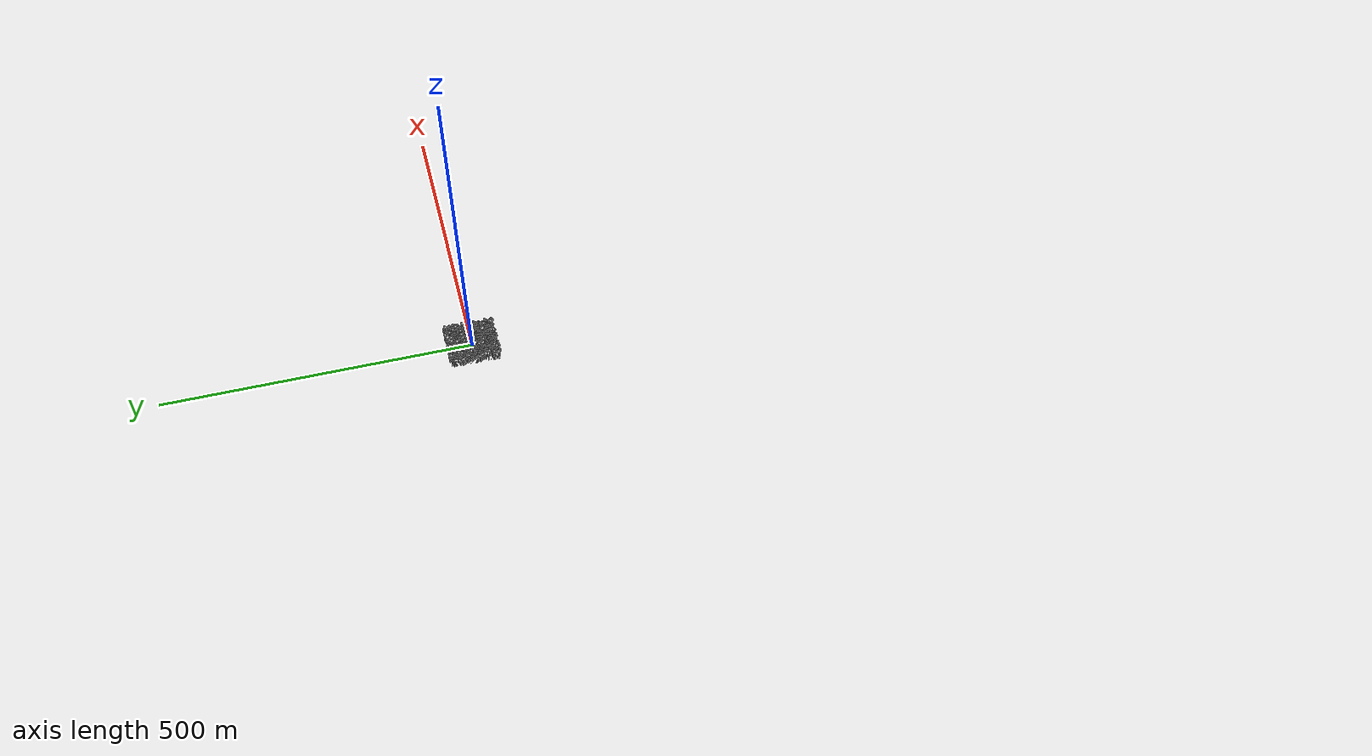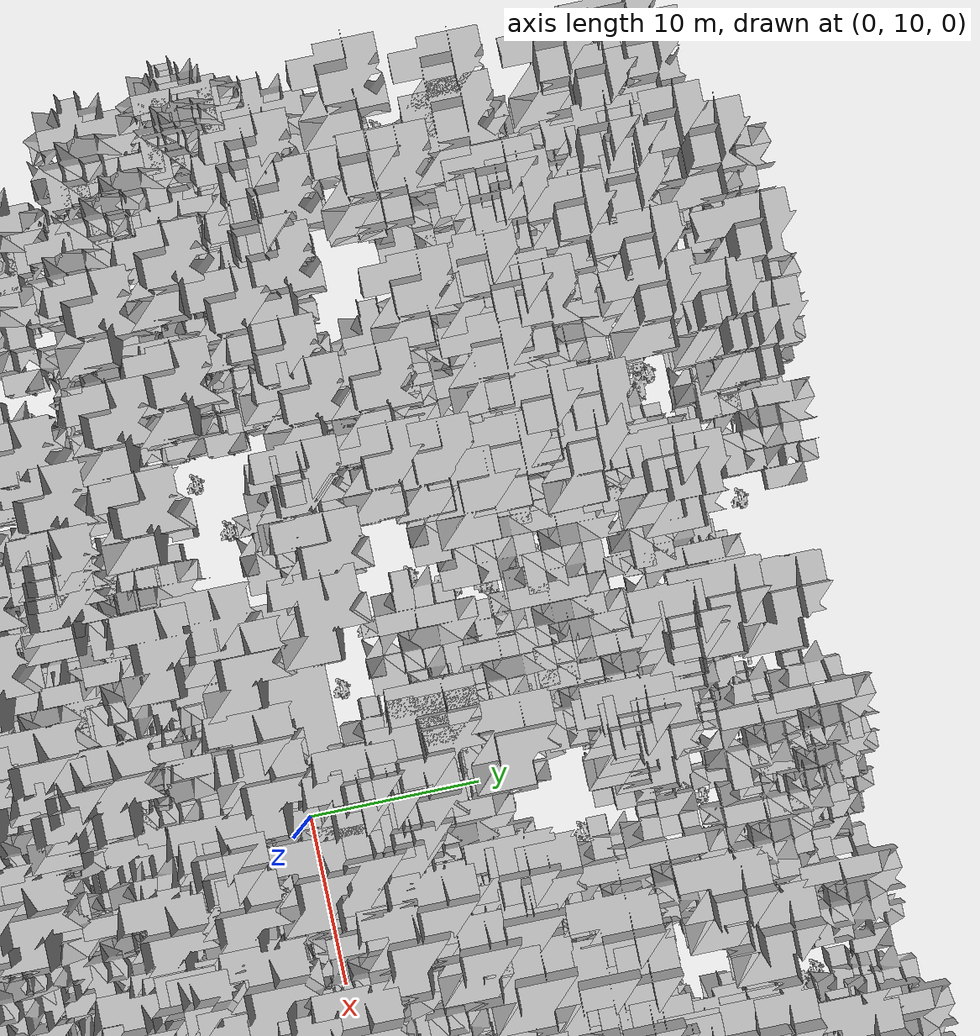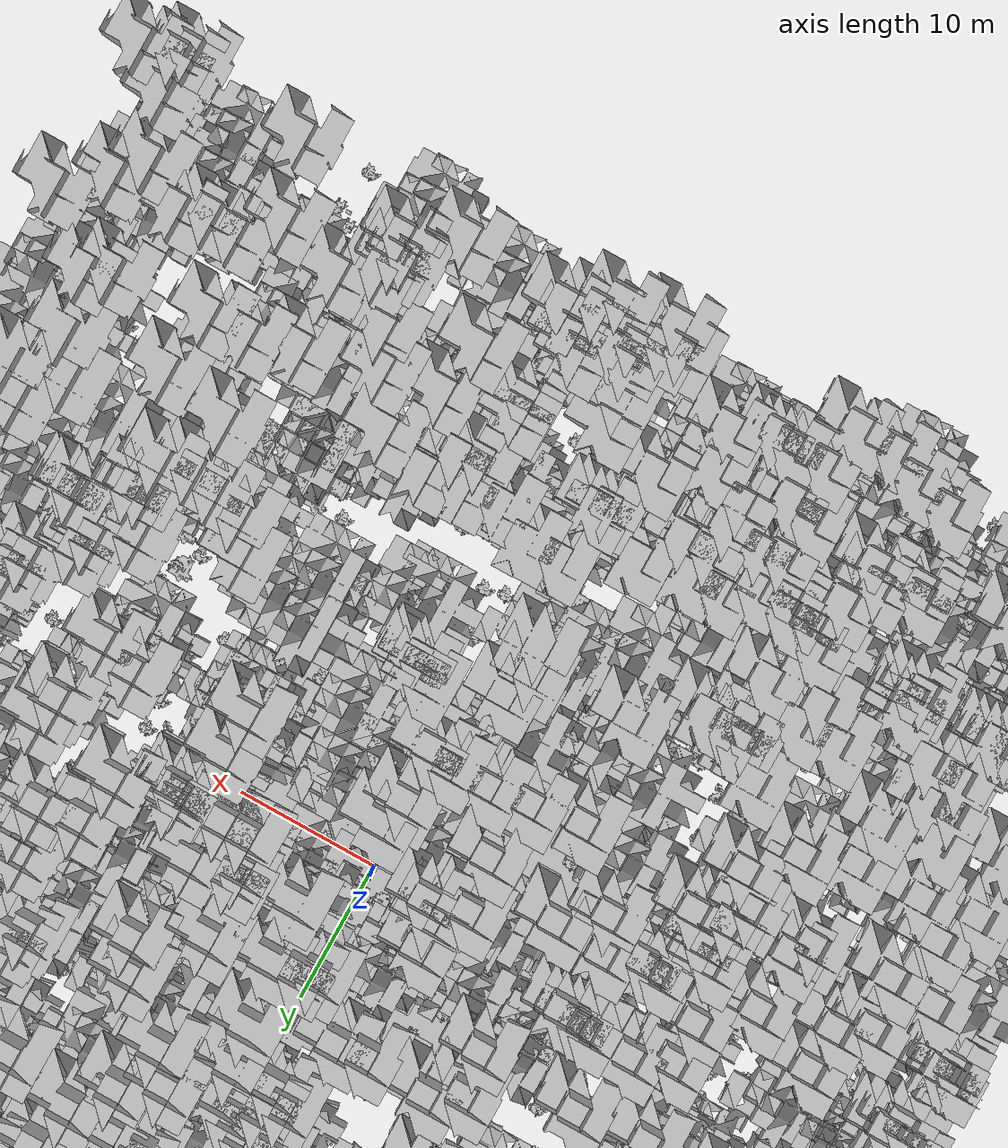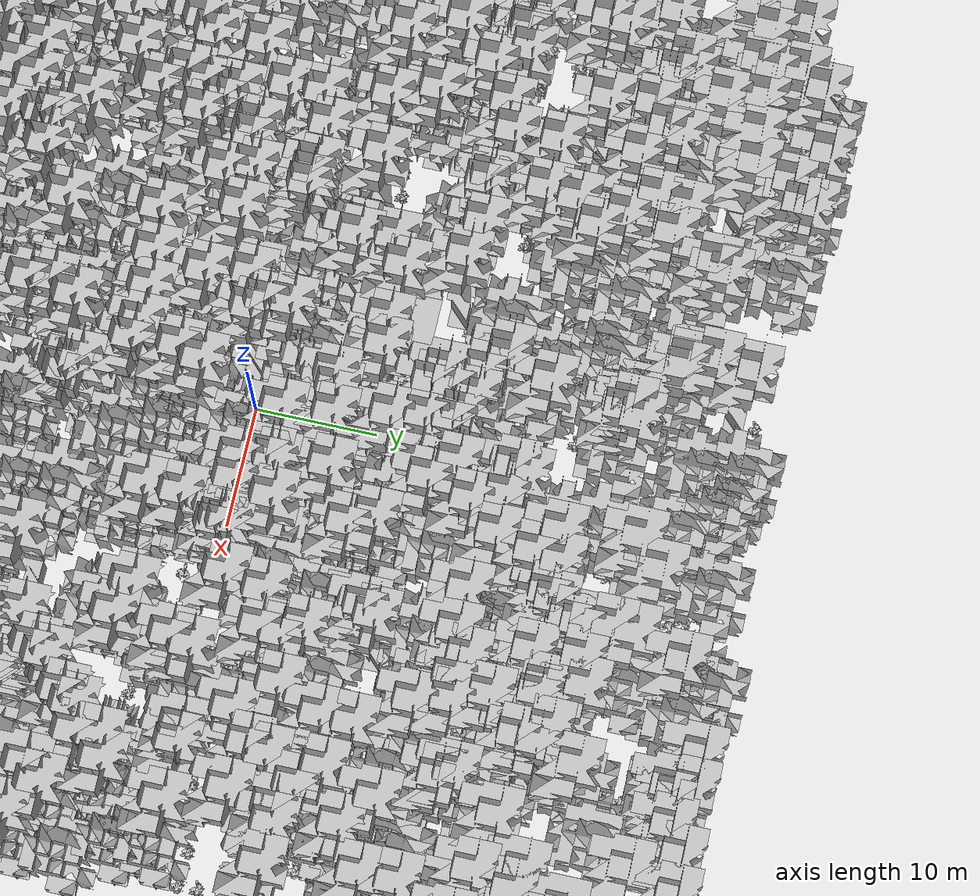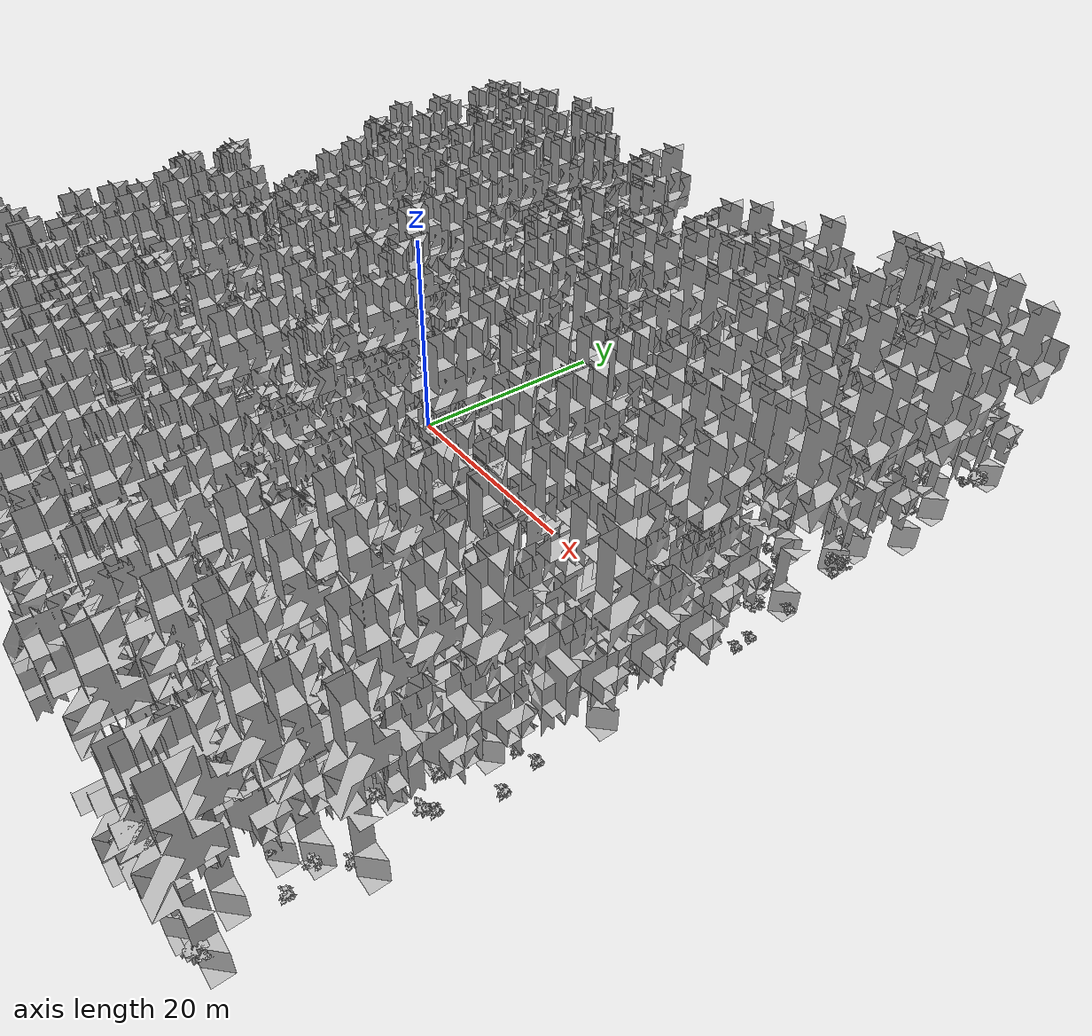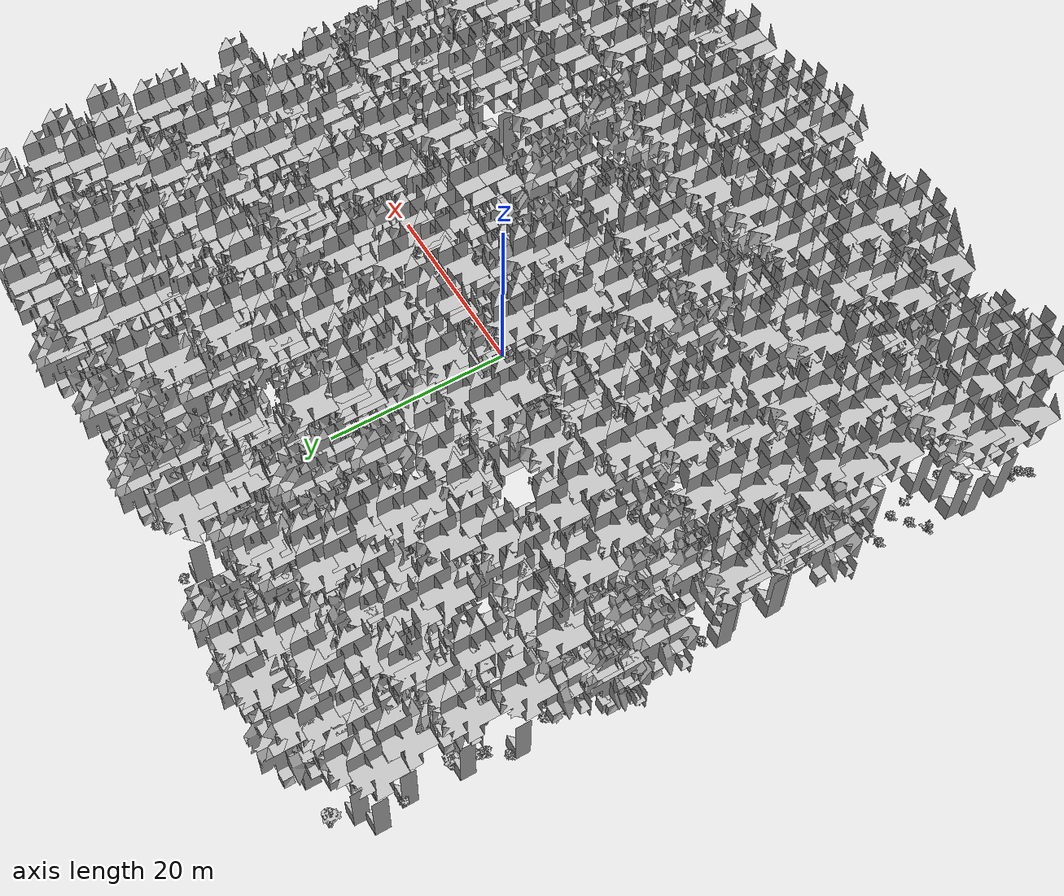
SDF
<sdf version="1.7">
    <world name="default">
        <plugin name="mrs_gazebo_static_transform_republisher_plugin" filename="libMrsGazeboCommonResources_StaticTransformRepublisher.so"/>
        <spherical_coordinates>
            <surface_model>EARTH_WGS84</surface_model>
            <latitude_deg>47.3977</latitude_deg>
            <longitude_deg>8.54559</longitude_deg>
            <elevation>0</elevation>
            <heading_deg>0</heading_deg>
        </spherical_coordinates>
        <physics name="default_physics" default="0" type="ode">
            <ode>
                <solver>
                    <type>quick</type>
                    <iters>10</iters>
                    <sor>1.3</sor>
                    <use_dynamic_moi_rescaling>0</use_dynamic_moi_rescaling>
                </solver>
                <constraints>
                    <cfm>0</cfm>
                    <erp>0.2</erp>
                    <contact_max_correcting_vel>1000</contact_max_correcting_vel>
                    <contact_surface_layer>0.001</contact_surface_layer>
                </constraints>
            </ode>
            <max_step_size>0.004</max_step_size>
            <real_time_factor>1</real_time_factor>
            <real_time_update_rate>250</real_time_update_rate>
        </physics>
        <scene>
            <shadows>0</shadows>
            <ambient>0.4 0.4 0.4 1</ambient>
            <background>0.7 0.7 0.7 1</background>
        </scene>
        <light name="sun" type="directional">
            <pose>0 0 1000 0.4 0.2 0</pose>
            <diffuse>1 1 1 1</diffuse>
            <specular>0.6 0.6 0.6 1</specular>
            <direction>0.1 0.1 -0.9</direction>
            <attenuation>
                <range>20</range>
                <constant>0.5</constant>
                <linear>0.01</linear>
                <quadratic>0.001</quadratic>
            </attenuation>
            <cast_shadows>1</cast_shadows>
            <spot>
                <inner_angle>0</inner_angle>
                <outer_angle>0</outer_angle>
                <falloff>0</falloff>
            </spot>
        </light>
        <model name="ground_plane">
            <static>1</static>
            <link name="link">
                <collision name="collision">
                    <pose>-50 0 0 0 -0 0</pose>
                    <geometry>
                        <plane>
                            <normal>0 0 1</normal>
                            <size>80 80</size>
                        </plane>
                    </geometry>
                    <surface>
                        <contact>
                            <ode>
                                <min_depth>0.01</min_depth>
                                <max_vel>0</max_vel>
                            </ode>
                        </contact>
                        <friction>
                            <ode/>
                            <torsional>
                                <ode/>
                            </torsional>
                        </friction>
                        <bounce/>
                    </surface>
                    <max_contacts>10</max_contacts>
                </collision>
                <visual name="grass">
                    <pose>0 0 0 0 -0 0</pose>
                    <cast_shadows>0</cast_shadows>
                    <geometry>
                        <mesh>
                            <scale>0.46714285714285714 0.46714285714285714 0.1</scale>
                            <uri>file://grass_plane/meshes/grass_plane.dae</uri>
                        </mesh>
                    </geometry>
                </visual>
                <self_collide>0</self_collide>
                <enable_wind>0</enable_wind>
                <kinematic>0</kinematic>
            </link>
        </model>
        <model name="the_void">
            <static>1</static>
            <link name="link">
                <pose>0 0 0.1 0 -0 0</pose>
                <visual name="the_void">
                    <pose>0 0 2 0 -0 0</pose>
                    <geometry>
                        <sphere>
                            <radius>0.25</radius>
                        </sphere>
                    </geometry>
                    <material>
                        <script>
                            <uri>file://media/materials/scripts/Gazebo.material</uri>
                            <name>Gazebo/Black</name>
                        </script>
                    </material>
                </visual>
                <self_collide>0</self_collide>
                <enable_wind>0</enable_wind>
                <kinematic>0</kinematic>
            </link>
            <pose>-1000 -1000 0 0 -0 0</pose>
        </model>
        <gui fullscreen="0">
            <camera name="camera">
                <pose>35.1577 98.6044 40.0204 0 0.407996 -1.99761</pose>
                <view_controller>orbit</view_controller>
                <projection_type>perspective</projection_type>
            </camera>
        </gui>
        <plugin name="mrs_gazebo_rviz_cam_synchronizer" filename="libMrsGazeboCommonResources_RvizCameraSynchronizer.so">
            <target_frame_id>gazebo_user_camera</target_frame_id>
            <world_origin_frame_id>uav1/gps_origin</world_origin_frame_id>
            <frame_to_follow>uav1</frame_to_follow>
        </plugin>
        <gravity>0 0 -9.8066</gravity>
        <magnetic_field>6e-06 2.3e-05 -4.2e-05</magnetic_field>
        <atmosphere type="adiabatic"/>
        <wind/>
        <model name="Tree 0">
            <static>1</static>
            <pose>28.266418201469165 38.54475775819776 0 1.57079 -0 0</pose>
            <link name="link">
                <pose>0 0 0 0 -0 0</pose>
                <collision name="collision">
                    <geometry>
                        <mesh>
                            <scale>3.5 5 3.5</scale>
                            <uri>model://tree_9/meshes/tree_9.obj</uri>
                        </mesh>
                    </geometry>
                    <max_contacts>10</max_contacts>
                    <surface>
                        <contact>
                            <ode/>
                        </contact>
                        <bounce/>
                        <friction>
                            <torsional>
                                <ode/>
                            </torsional>
                            <ode/>
                        </friction>
                    </surface>
                </collision>
                <visual name="visual">
                    <geometry>
                        <mesh>
                            <scale>3.5 5 3.5</scale>
                            <uri>model://tree_9/meshes/tree_9.obj</uri>
                        </mesh>
                    </geometry>
                </visual>
                <self_collide>0</self_collide>
                <enable_wind>0</enable_wind>
                <kinematic>0</kinematic>
            </link>
        </model>
        <model name="Tree 1">
            <static>1</static>
            <pose>-8.566626045138978 -28.20236871069075 0 1.57079 -0 0</pose>
            <link name="link">
                <pose>0 0 0 0 -0 0</pose>
                <collision name="collision">
                    <geometry>
                        <mesh>
                            <scale>3.5 5 3.5</scale>
                            <uri>model://tree_9/meshes/tree_9.obj</uri>
                        </mesh>
                    </geometry>
                    <max_contacts>10</max_contacts>
                    <surface>
                        <contact>
                            <ode/>
                        </contact>
                        <bounce/>
                        <friction>
                            <torsional>
                                <ode/>
                            </torsional>
                            <ode/>
                        </friction>
                    </surface>
                </collision>
                <visual name="visual">
                    <geometry>
                        <mesh>
                            <scale>3.5 5 3.5</scale>
                            <uri>model://tree_9/meshes/tree_9.obj</uri>
                        </mesh>
                    </geometry>
                </visual>
                <self_collide>0</self_collide>
                <enable_wind>0</enable_wind>
                <kinematic>0</kinematic>
            </link>
        </model>
        <model name="Tree 2">
            <static>1</static>
            <pose>12.744392342214496 -25.10153390467923 0 1.57079 -0 0</pose>
            <link name="link">
                <pose>0 0 0 0 -0 0</pose>
                <collision name="collision">
                    <geometry>
                        <mesh>
                            <scale>3.5 5 3.5</scale>
                            <uri>model://tree_9/meshes/tree_9.obj</uri>
                        </mesh>
                    </geometry>
                    <max_contacts>10</max_contacts>
                    <surface>
                        <contact>
                            <ode/>
                        </contact>
                        <bounce/>
                        <friction>
                            <torsional>
                                <ode/>
                            </torsional>
                            <ode/>
                        </friction>
                    </surface>
                </collision>
                <visual name="visual">
                    <geometry>
                        <mesh>
                            <scale>3.5 5 3.5</scale>
                            <uri>model://tree_9/meshes/tree_9.obj</uri>
                        </mesh>
                    </geometry>
                </visual>
                <self_collide>0</self_collide>
                <enable_wind>0</enable_wind>
                <kinematic>0</kinematic>
            </link>
        </model>
        <model name="Tree 3">
            <static>1</static>
            <pose>19.24616015510459 25.962018746544175 0 1.57079 -0 0</pose>
            <link name="link">
                <pose>0 0 0 0 -0 0</pose>
                <collision name="collision">
                    <geometry>
                        <mesh>
                            <scale>3.5 5 3.5</scale>
                            <uri>model://tree_2/meshes/tree_2.obj</uri>
                        </mesh>
                    </geometry>
                    <max_contacts>10</max_contacts>
                    <surface>
                        <contact>
                            <ode/>
                        </contact>
                        <bounce/>
                        <friction>
                            <torsional>
                                <ode/>
                            </torsional>
                            <ode/>
                        </friction>
                    </surface>
                </collision>
                <visual name="visual">
                    <geometry>
                        <mesh>
                            <scale>3.5 5 3.5</scale>
                            <uri>model://tree_2/meshes/tree_2.obj</uri>
                        </mesh>
                    </geometry>
                </visual>
                <self_collide>0</self_collide>
                <enable_wind>0</enable_wind>
                <kinematic>0</kinematic>
            </link>
        </model>
        <model name="Tree 4">
            <static>1</static>
            <pose>-31.437596550301684 -10.574434964813708 0 1.57079 -0 0</pose>
            <link name="link">
                <pose>0 0 0 0 -0 0</pose>
                <collision name="collision">
                    <geometry>
                        <mesh>
                            <scale>3.5 5 3.5</scale>
                            <uri>model://tree_9/meshes/tree_9.obj</uri>
                        </mesh>
                    </geometry>
                    <max_contacts>10</max_contacts>
                    <surface>
                        <contact>
                            <ode/>
                        </contact>
                        <bounce/>
                        <friction>
                            <torsional>
                                <ode/>
                            </torsional>
                            <ode/>
                        </friction>
                    </surface>
                </collision>
                <visual name="visual">
                    <geometry>
                        <mesh>
                            <scale>3.5 5 3.5</scale>
                            <uri>model://tree_9/meshes/tree_9.obj</uri>
                        </mesh>
                    </geometry>
                </visual>
                <self_collide>0</self_collide>
                <enable_wind>0</enable_wind>
                <kinematic>0</kinematic>
            </link>
        </model>
        <model name="Tree 5">
            <static>1</static>
            <pose>6.3755457740318775 21.31702471698801 0 1.57079 -0 0</pose>
            <link name="link">
                <pose>0 0 0 0 -0 0</pose>
                <collision name="collision">
                    <geometry>
                        <mesh>
                            <scale>3.5 5 3.5</scale>
                            <uri>model://tree_9/meshes/tree_9.obj</uri>
                        </mesh>
                    </geometry>
                    <max_contacts>10</max_contacts>
                    <surface>
                        <contact>
                            <ode/>
                        </contact>
                        <bounce/>
                        <friction>
                            <torsional>
                                <ode/>
                            </torsional>
                            <ode/>
                        </friction>
                    </surface>
                </collision>
                <visual name="visual">
                    <geometry>
                        <mesh>
                            <scale>3.5 5 3.5</scale>
                            <uri>model://tree_9/meshes/tree_9.obj</uri>
                        </mesh>
                    </geometry>
                </visual>
                <self_collide>0</self_collide>
                <enable_wind>0</enable_wind>
                <kinematic>0</kinematic>
            </link>
        </model>
        <model name="Tree 6">
            <static>1</static>
            <pose>7.984575427934473 1.1201667214124527 0 1.57079 -0 0</pose>
            <link name="link">
                <pose>0 0 0 0 -0 0</pose>
                <collision name="collision">
                    <geometry>
                        <mesh>
                            <scale>3.5 5 3.5</scale>
                            <uri>model://tree_9/meshes/tree_9.obj</uri>
                        </mesh>
                    </geometry>
                    <max_contacts>10</max_contacts>
                    <surface>
                        <contact>
                            <ode/>
                        </contact>
                        <bounce/>
                        <friction>
                            <torsional>
                                <ode/>
                            </torsional>
                            <ode/>
                        </friction>
                    </surface>
                </collision>
                <visual name="visual">
                    <geometry>
                        <mesh>
                            <scale>3.5 5 3.5</scale>
                            <uri>model://tree_9/meshes/tree_9.obj</uri>
                        </mesh>
                    </geometry>
                </visual>
                <self_collide>0</self_collide>
                <enable_wind>0</enable_wind>
                <kinematic>0</kinematic>
            </link>
        </model>
        <model name="Tree 7">
            <static>1</static>
            <pose>32.03735566564313 36.16888513344976 0 1.57079 -0 0</pose>
            <link name="link">
                <pose>0 0 0 0 -0 0</pose>
                <collision name="collision">
                    <geometry>
                        <mesh>
                            <scale>3.5 5 3.5</scale>
                            <uri>model://tree_9/meshes/tree_9.obj</uri>
                        </mesh>
                    </geometry>
                    <max_contacts>10</max_contacts>
                    <surface>
                        <contact>
                            <ode/>
                        </contact>
                        <bounce/>
                        <friction>
                            <torsional>
                                <ode/>
                            </torsional>
                            <ode/>
                        </friction>
                    </surface>
                </collision>
                <visual name="visual">
                    <geometry>
                        <mesh>
                            <scale>3.5 5 3.5</scale>
                            <uri>model://tree_9/meshes/tree_9.obj</uri>
                        </mesh>
                    </geometry>
                </visual>
                <self_collide>0</self_collide>
                <enable_wind>0</enable_wind>
                <kinematic>0</kinematic>
            </link>
        </model>
        <model name="Tree 8">
            <static>1</static>
            <pose>35.181705289902354 -30.895556026254162 0 1.57079 -0 0</pose>
            <link name="link">
                <pose>0 0 0 0 -0 0</pose>
                <collision name="collision">
                    <geometry>
                        <mesh>
                            <scale>3.5 5 3.5</scale>
                            <uri>model://tree_9/meshes/tree_9.obj</uri>
                        </mesh>
                    </geometry>
                    <max_contacts>10</max_contacts>
                    <surface>
                        <contact>
                            <ode/>
                        </contact>
                        <bounce/>
                        <friction>
                            <torsional>
                                <ode/>
                            </torsional>
                            <ode/>
                        </friction>
                    </surface>
                </collision>
                <visual name="visual">
                    <geometry>
                        <mesh>
                            <scale>3.5 5 3.5</scale>
                            <uri>model://tree_9/meshes/tree_9.obj</uri>
                        </mesh>
                    </geometry>
                </visual>
                <self_collide>0</self_collide>
                <enable_wind>0</enable_wind>
                <kinematic>0</kinematic>
            </link>
        </model>
        <model name="Tree 9">
            <static>1</static>
            <pose>-13.837278724867915 -9.116310804493875 0 1.57079 -0 0</pose>
            <link name="link">
                <pose>0 0 0 0 -0 0</pose>
                <collision name="collision">
                    <geometry>
                        <mesh>
                            <scale>3.5 5 3.5</scale>
                            <uri>model://tree_2/meshes/tree_2.obj</uri>
                        </mesh>
                    </geometry>
                    <max_contacts>10</max_contacts>
                    <surface>
                        <contact>
                            <ode/>
                        </contact>
                        <bounce/>
                        <friction>
                            <torsional>
                                <ode/>
                            </torsional>
                            <ode/>
                        </friction>
                    </surface>
                </collision>
                <visual name="visual">
                    <geometry>
                        <mesh>
                            <scale>3.5 5 3.5</scale>
                            <uri>model://tree_2/meshes/tree_2.obj</uri>
                        </mesh>
                    </geometry>
                </visual>
                <self_collide>0</self_collide>
                <enable_wind>0</enable_wind>
                <kinematic>0</kinematic>
            </link>
        </model>
        <model name="Tree 10">
            <static>1</static>
            <pose>3.8633248040182124 0.3645302694113326 0 1.57079 -0 0</pose>
            <link name="link">
                <pose>0 0 0 0 -0 0</pose>
                <collision name="collision">
                    <geometry>
                        <mesh>
                            <scale>3.5 5 3.5</scale>
                            <uri>model://tree_2/meshes/tree_2.obj</uri>
                        </mesh>
                    </geometry>
                    <max_contacts>10</max_contacts>
                    <surface>
                        <contact>
                            <ode/>
                        </contact>
                        <bounce/>
                        <friction>
                            <torsional>
                                <ode/>
                            </torsional>
                            <ode/>
                        </friction>
                    </surface>
                </collision>
                <visual name="visual">
                    <geometry>
                        <mesh>
                            <scale>3.5 5 3.5</scale>
                            <uri>model://tree_2/meshes/tree_2.obj</uri>
                        </mesh>
                    </geometry>
                </visual>
                <self_collide>0</self_collide>
                <enable_wind>0</enable_wind>
                <kinematic>0</kinematic>
            </link>
        </model>
        <model name="Tree 11">
            <static>1</static>
            <pose>16.34194853640159 -22.23036959908649 0 1.57079 -0 0</pose>
            <link name="link">
                <pose>0 0 0 0 -0 0</pose>
                <collision name="collision">
                    <geometry>
                        <mesh>
                            <scale>3.5 5 3.5</scale>
                            <uri>model://tree_2/meshes/tree_2.obj</uri>
                        </mesh>
                    </geometry>
                    <max_contacts>10</max_contacts>
                    <surface>
                        <contact>
                            <ode/>
                        </contact>
                        <bounce/>
                        <friction>
                            <torsional>
                                <ode/>
                            </torsional>
                            <ode/>
                        </friction>
                    </surface>
                </collision>
                <visual name="visual">
                    <geometry>
                        <mesh>
                            <scale>3.5 5 3.5</scale>
                            <uri>model://tree_2/meshes/tree_2.obj</uri>
                        </mesh>
                    </geometry>
                </visual>
                <self_collide>0</self_collide>
                <enable_wind>0</enable_wind>
                <kinematic>0</kinematic>
            </link>
        </model>
        <model name="Tree 12">
            <static>1</static>
            <pose>-21.076399075654592 18.444348376901267 0 1.57079 -0 0</pose>
            <link name="link">
                <pose>0 0 0 0 -0 0</pose>
                <collision name="collision">
                    <geometry>
                        <mesh>
                            <scale>3.5 5 3.5</scale>
                            <uri>model://tree_2/meshes/tree_2.obj</uri>
                        </mesh>
                    </geometry>
                    <max_contacts>10</max_contacts>
                    <surface>
                        <contact>
                            <ode/>
                        </contact>
                        <bounce/>
                        <friction>
                            <torsional>
                                <ode/>
                            </torsional>
                            <ode/>
                        </friction>
                    </surface>
                </collision>
                <visual name="visual">
                    <geometry>
                        <mesh>
                            <scale>3.5 5 3.5</scale>
                            <uri>model://tree_2/meshes/tree_2.obj</uri>
                        </mesh>
                    </geometry>
                </visual>
                <self_collide>0</self_collide>
                <enable_wind>0</enable_wind>
                <kinematic>0</kinematic>
            </link>
        </model>
        <model name="Tree 13">
            <static>1</static>
            <pose>10.382277022149914 -23.49084186077171 0 1.57079 -0 0</pose>
            <link name="link">
                <pose>0 0 0 0 -0 0</pose>
                <collision name="collision">
                    <geometry>
                        <mesh>
                            <scale>3.5 5 3.5</scale>
                            <uri>model://tree_2/meshes/tree_2.obj</uri>
                        </mesh>
                    </geometry>
                    <max_contacts>10</max_contacts>
                    <surface>
                        <contact>
                            <ode/>
                        </contact>
                        <bounce/>
                        <friction>
                            <torsional>
                                <ode/>
                            </torsional>
                            <ode/>
                        </friction>
                    </surface>
                </collision>
                <visual name="visual">
                    <geometry>
                        <mesh>
                            <scale>3.5 5 3.5</scale>
                            <uri>model://tree_2/meshes/tree_2.obj</uri>
                        </mesh>
                    </geometry>
                </visual>
                <self_collide>0</self_collide>
                <enable_wind>0</enable_wind>
                <kinematic>0</kinematic>
            </link>
        </model>
        <model name="Tree 14">
            <static>1</static>
            <pose>16.65562580295847 -35.12207921520766 0 1.57079 -0 0</pose>
            <link name="link">
                <pose>0 0 0 0 -0 0</pose>
                <collision name="collision">
                    <geometry>
                        <mesh>
                            <scale>3.5 5 3.5</scale>
                            <uri>model://tree_9/meshes/tree_9.obj</uri>
                        </mesh>
                    </geometry>
                    <max_contacts>10</max_contacts>
                    <surface>
                        <contact>
                            <ode/>
                        </contact>
                        <bounce/>
                        <friction>
                            <torsional>
                                <ode/>
                            </torsional>
                            <ode/>
                        </friction>
                    </surface>
                </collision>
                <visual name="visual">
                    <geometry>
                        <mesh>
                            <scale>3.5 5 3.5</scale>
                            <uri>model://tree_9/meshes/tree_9.obj</uri>
                        </mesh>
                    </geometry>
                </visual>
                <self_collide>0</self_collide>
                <enable_wind>0</enable_wind>
                <kinematic>0</kinematic>
            </link>
        </model>
        <model name="Tree 15">
            <static>1</static>
            <pose>-14.854985802716378 -19.197979254505917 0 1.57079 -0 0</pose>
            <link name="link">
                <pose>0 0 0 0 -0 0</pose>
                <collision name="collision">
                    <geometry>
                        <mesh>
                            <scale>3.5 5 3.5</scale>
                            <uri>model://tree_9/meshes/tree_9.obj</uri>
                        </mesh>
                    </geometry>
                    <max_contacts>10</max_contacts>
                    <surface>
                        <contact>
                            <ode/>
                        </contact>
                        <bounce/>
                        <friction>
                            <torsional>
                                <ode/>
                            </torsional>
                            <ode/>
                        </friction>
                    </surface>
                </collision>
                <visual name="visual">
                    <geometry>
                        <mesh>
                            <scale>3.5 5 3.5</scale>
                            <uri>model://tree_9/meshes/tree_9.obj</uri>
                        </mesh>
                    </geometry>
                </visual>
                <self_collide>0</self_collide>
                <enable_wind>0</enable_wind>
                <kinematic>0</kinematic>
            </link>
        </model>
        <model name="Tree 16">
            <static>1</static>
            <pose>-0.8902189056149439 -27.28137795548114 0 1.57079 -0 0</pose>
            <link name="link">
                <pose>0 0 0 0 -0 0</pose>
                <collision name="collision">
                    <geometry>
                        <mesh>
                            <scale>3.5 5 3.5</scale>
                            <uri>model://tree_2/meshes/tree_2.obj</uri>
                        </mesh>
                    </geometry>
                    <max_contacts>10</max_contacts>
                    <surface>
                        <contact>
                            <ode/>
                        </contact>
                        <bounce/>
                        <friction>
                            <torsional>
                                <ode/>
                            </torsional>
                            <ode/>
                        </friction>
                    </surface>
                </collision>
                <visual name="visual">
                    <geometry>
                        <mesh>
                            <scale>3.5 5 3.5</scale>
                            <uri>model://tree_2/meshes/tree_2.obj</uri>
                        </mesh>
                    </geometry>
                </visual>
                <self_collide>0</self_collide>
                <enable_wind>0</enable_wind>
                <kinematic>0</kinematic>
            </link>
        </model>
        <model name="Tree 17">
            <static>1</static>
            <pose>-12.710359275981453 -30.128625494422614 0 1.57079 -0 0</pose>
            <link name="link">
                <pose>0 0 0 0 -0 0</pose>
                <collision name="collision">
                    <geometry>
                        <mesh>
                            <scale>3.5 5 3.5</scale>
                            <uri>model://tree_9/meshes/tree_9.obj</uri>
                        </mesh>
                    </geometry>
                    <max_contacts>10</max_contacts>
                    <surface>
                        <contact>
                            <ode/>
                        </contact>
                        <bounce/>
                        <friction>
                            <torsional>
                                <ode/>
                            </torsional>
                            <ode/>
                        </friction>
                    </surface>
                </collision>
                <visual name="visual">
                    <geometry>
                        <mesh>
                            <scale>3.5 5 3.5</scale>
                            <uri>model://tree_9/meshes/tree_9.obj</uri>
                        </mesh>
                    </geometry>
                </visual>
                <self_collide>0</self_collide>
                <enable_wind>0</enable_wind>
                <kinematic>0</kinematic>
            </link>
        </model>
        <model name="Tree 18">
            <static>1</static>
            <pose>-28.897538076674838 5.994807047997995 0 1.57079 -0 0</pose>
            <link name="link">
                <pose>0 0 0 0 -0 0</pose>
                <collision name="collision">
                    <geometry>
                        <mesh>
                            <scale>3.5 5 3.5</scale>
                            <uri>model://tree_9/meshes/tree_9.obj</uri>
                        </mesh>
                    </geometry>
                    <max_contacts>10</max_contacts>
                    <surface>
                        <contact>
                            <ode/>
                        </contact>
                        <bounce/>
                        <friction>
                            <torsional>
                                <ode/>
                            </torsional>
                            <ode/>
                        </friction>
                    </surface>
                </collision>
                <visual name="visual">
                    <geometry>
                        <mesh>
                            <scale>3.5 5 3.5</scale>
                            <uri>model://tree_9/meshes/tree_9.obj</uri>
                        </mesh>
                    </geometry>
                </visual>
                <self_collide>0</self_collide>
                <enable_wind>0</enable_wind>
                <kinematic>0</kinematic>
            </link>
        </model>
        <model name="Tree 19">
            <static>1</static>
            <pose>-0.4181565198743158 29.577803610029378 0 1.57079 -0 0</pose>
            <link name="link">
                <pose>0 0 0 0 -0 0</pose>
                <collision name="collision">
                    <geometry>
                        <mesh>
                            <scale>3.5 5 3.5</scale>
                            <uri>model://tree_2/meshes/tree_2.obj</uri>
                        </mesh>
                    </geometry>
                    <max_contacts>10</max_contacts>
                    <surface>
                        <contact>
                            <ode/>
                        </contact>
                        <bounce/>
                        <friction>
                            <torsional>
                                <ode/>
                            </torsional>
                            <ode/>
                        </friction>
                    </surface>
                </collision>
                <visual name="visual">
                    <geometry>
                        <mesh>
                            <scale>3.5 5 3.5</scale>
                            <uri>model://tree_2/meshes/tree_2.obj</uri>
                        </mesh>
                    </geometry>
                </visual>
                <self_collide>0</self_collide>
                <enable_wind>0</enable_wind>
                <kinematic>0</kinematic>
            </link>
        </model>
        <model name="Tree 20">
            <static>1</static>
            <pose>-1.7390798904137128 -27.611910803773718 0 1.57079 -0 0</pose>
            <link name="link">
                <pose>0 0 0 0 -0 0</pose>
                <collision name="collision">
                    <geometry>
                        <mesh>
                            <scale>3.5 5 3.5</scale>
                            <uri>model://tree_9/meshes/tree_9.obj</uri>
                        </mesh>
                    </geometry>
                    <max_contacts>10</max_contacts>
                    <surface>
                        <contact>
                            <ode/>
                        </contact>
                        <bounce/>
                        <friction>
                            <torsional>
                                <ode/>
                            </torsional>
                            <ode/>
                        </friction>
                    </surface>
                </collision>
                <visual name="visual">
                    <geometry>
                        <mesh>
                            <scale>3.5 5 3.5</scale>
                            <uri>model://tree_9/meshes/tree_9.obj</uri>
                        </mesh>
                    </geometry>
                </visual>
                <self_collide>0</self_collide>
                <enable_wind>0</enable_wind>
                <kinematic>0</kinematic>
            </link>
        </model>
        <model name="Tree 21">
            <static>1</static>
            <pose>16.07610414647575 26.971993970399083 0 1.57079 -0 0</pose>
            <link name="link">
                <pose>0 0 0 0 -0 0</pose>
                <collision name="collision">
                    <geometry>
                        <mesh>
                            <scale>3.5 5 3.5</scale>
                            <uri>model://tree_2/meshes/tree_2.obj</uri>
                        </mesh>
                    </geometry>
                    <max_contacts>10</max_contacts>
                    <surface>
                        <contact>
                            <ode/>
                        </contact>
                        <bounce/>
                        <friction>
                            <torsional>
                                <ode/>
                            </torsional>
                            <ode/>
                        </friction>
                    </surface>
                </collision>
                <visual name="visual">
                    <geometry>
                        <mesh>
                            <scale>3.5 5 3.5</scale>
                            <uri>model://tree_2/meshes/tree_2.obj</uri>
                        </mesh>
                    </geometry>
                </visual>
                <self_collide>0</self_collide>
                <enable_wind>0</enable_wind>
                <kinematic>0</kinematic>
            </link>
        </model>
        <model name="Tree 22">
            <static>1</static>
            <pose>33.53301788080597 -24.68634624659826 0 1.57079 -0 0</pose>
            <link name="link">
                <pose>0 0 0 0 -0 0</pose>
                <collision name="collision">
                    <geometry>
                        <mesh>
                            <scale>3.5 5 3.5</scale>
                            <uri>model://tree_2/meshes/tree_2.obj</uri>
                        </mesh>
                    </geometry>
                    <max_contacts>10</max_contacts>
                    <surface>
                        <contact>
                            <ode/>
                        </contact>
                        <bounce/>
                        <friction>
                            <torsional>
                                <ode/>
                            </torsional>
                            <ode/>
                        </friction>
                    </surface>
                </collision>
                <visual name="visual">
                    <geometry>
                        <mesh>
                            <scale>3.5 5 3.5</scale>
                            <uri>model://tree_2/meshes/tree_2.obj</uri>
                        </mesh>
                    </geometry>
                </visual>
                <self_collide>0</self_collide>
                <enable_wind>0</enable_wind>
                <kinematic>0</kinematic>
            </link>
        </model>
        <model name="Tree 23">
            <static>1</static>
            <pose>35.221146484826804 -17.699953607041667 0 1.57079 -0 0</pose>
            <link name="link">
                <pose>0 0 0 0 -0 0</pose>
                <collision name="collision">
                    <geometry>
                        <mesh>
                            <scale>3.5 5 3.5</scale>
                            <uri>model://tree_9/meshes/tree_9.obj</uri>
                        </mesh>
                    </geometry>
                    <max_contacts>10</max_contacts>
                    <surface>
                        <contact>
                            <ode/>
                        </contact>
                        <bounce/>
                        <friction>
                            <torsional>
                                <ode/>
                            </torsional>
                            <ode/>
                        </friction>
                    </surface>
                </collision>
                <visual name="visual">
                    <geometry>
                        <mesh>
                            <scale>3.5 5 3.5</scale>
                            <uri>model://tree_9/meshes/tree_9.obj</uri>
                        </mesh>
                    </geometry>
                </visual>
                <self_collide>0</self_collide>
                <enable_wind>0</enable_wind>
                <kinematic>0</kinematic>
            </link>
        </model>
        <model name="Tree 24">
            <static>1</static>
            <pose>16.35669794025045 32.11043431280959 0 1.57079 -0 0</pose>
            <link name="link">
                <pose>0 0 0 0 -0 0</pose>
                <collision name="collision">
                    <geometry>
                        <mesh>
                            <scale>3.5 5 3.5</scale>
                            <uri>model://tree_2/meshes/tree_2.obj</uri>
                        </mesh>
                    </geometry>
                    <max_contacts>10</max_contacts>
                    <surface>
                        <contact>
                            <ode/>
                        </contact>
                        <bounce/>
                        <friction>
                            <torsional>
                                <ode/>
                            </torsional>
                            <ode/>
                        </friction>
                    </surface>
                </collision>
                <visual name="visual">
                    <geometry>
                        <mesh>
                            <scale>3.5 5 3.5</scale>
                            <uri>model://tree_2/meshes/tree_2.obj</uri>
                        </mesh>
                    </geometry>
                </visual>
                <self_collide>0</self_collide>
                <enable_wind>0</enable_wind>
                <kinematic>0</kinematic>
            </link>
        </model>
        <model name="Tree 25">
            <static>1</static>
            <pose>27.72420464449263 -12.524156283645667 0 1.57079 -0 0</pose>
            <link name="link">
                <pose>0 0 0 0 -0 0</pose>
                <collision name="collision">
                    <geometry>
                        <mesh>
                            <scale>3.5 5 3.5</scale>
                            <uri>model://tree_9/meshes/tree_9.obj</uri>
                        </mesh>
                    </geometry>
                    <max_contacts>10</max_contacts>
                    <surface>
                        <contact>
                            <ode/>
                        </contact>
                        <bounce/>
                        <friction>
                            <torsional>
                                <ode/>
                            </torsional>
                            <ode/>
                        </friction>
                    </surface>
                </collision>
                <visual name="visual">
                    <geometry>
                        <mesh>
                            <scale>3.5 5 3.5</scale>
                            <uri>model://tree_9/meshes/tree_9.obj</uri>
                        </mesh>
                    </geometry>
                </visual>
                <self_collide>0</self_collide>
                <enable_wind>0</enable_wind>
                <kinematic>0</kinematic>
            </link>
        </model>
        <model name="Tree 26">
            <static>1</static>
            <pose>-23.19923432240673 39.65129565254853 0 1.57079 -0 0</pose>
            <link name="link">
                <pose>0 0 0 0 -0 0</pose>
                <collision name="collision">
                    <geometry>
                        <mesh>
                            <scale>3.5 5 3.5</scale>
                            <uri>model://tree_2/meshes/tree_2.obj</uri>
                        </mesh>
                    </geometry>
                    <max_contacts>10</max_contacts>
                    <surface>
                        <contact>
                            <ode/>
                        </contact>
                        <bounce/>
                        <friction>
                            <torsional>
                                <ode/>
                            </torsional>
                            <ode/>
                        </friction>
                    </surface>
                </collision>
                <visual name="visual">
                    <geometry>
                        <mesh>
                            <scale>3.5 5 3.5</scale>
                            <uri>model://tree_2/meshes/tree_2.obj</uri>
                        </mesh>
                    </geometry>
                </visual>
                <self_collide>0</self_collide>
                <enable_wind>0</enable_wind>
                <kinematic>0</kinematic>
            </link>
        </model>
        <model name="Tree 27">
            <static>1</static>
            <pose>-20.996689875617964 -5.953197715988658 0 1.57079 -0 0</pose>
            <link name="link">
                <pose>0 0 0 0 -0 0</pose>
                <collision name="collision">
                    <geometry>
                        <mesh>
                            <scale>3.5 5 3.5</scale>
                            <uri>model://tree_9/meshes/tree_9.obj</uri>
                        </mesh>
                    </geometry>
                    <max_contacts>10</max_contacts>
                    <surface>
                        <contact>
                            <ode/>
                        </contact>
                        <bounce/>
                        <friction>
                            <torsional>
                                <ode/>
                            </torsional>
                            <ode/>
                        </friction>
                    </surface>
                </collision>
                <visual name="visual">
                    <geometry>
                        <mesh>
                            <scale>3.5 5 3.5</scale>
                            <uri>model://tree_9/meshes/tree_9.obj</uri>
                        </mesh>
                    </geometry>
                </visual>
                <self_collide>0</self_collide>
                <enable_wind>0</enable_wind>
                <kinematic>0</kinematic>
            </link>
        </model>
        <model name="Tree 28">
            <static>1</static>
            <pose>-25.822680429466185 39.910124445336265 0 1.57079 -0 0</pose>
            <link name="link">
                <pose>0 0 0 0 -0 0</pose>
                <collision name="collision">
                    <geometry>
                        <mesh>
                            <scale>3.5 5 3.5</scale>
                            <uri>model://tree_9/meshes/tree_9.obj</uri>
                        </mesh>
                    </geometry>
                    <max_contacts>10</max_contacts>
                    <surface>
                        <contact>
                            <ode/>
                        </contact>
                        <bounce/>
                        <friction>
                            <torsional>
                                <ode/>
                            </torsional>
                            <ode/>
                        </friction>
                    </surface>
                </collision>
                <visual name="visual">
                    <geometry>
                        <mesh>
                            <scale>3.5 5 3.5</scale>
                            <uri>model://tree_9/meshes/tree_9.obj</uri>
                        </mesh>
                    </geometry>
                </visual>
                <self_collide>0</self_collide>
                <enable_wind>0</enable_wind>
                <kinematic>0</kinematic>
            </link>
        </model>
        <model name="Tree 29">
            <static>1</static>
            <pose>27.831478742565906 22.209729060061214 0 1.57079 -0 0</pose>
            <link name="link">
                <pose>0 0 0 0 -0 0</pose>
                <collision name="collision">
                    <geometry>
                        <mesh>
                            <scale>3.5 5 3.5</scale>
                            <uri>model://tree_9/meshes/tree_9.obj</uri>
                        </mesh>
                    </geometry>
                    <max_contacts>10</max_contacts>
                    <surface>
                        <contact>
                            <ode/>
                        </contact>
                        <bounce/>
                        <friction>
                            <torsional>
                                <ode/>
                            </torsional>
                            <ode/>
                        </friction>
                    </surface>
                </collision>
                <visual name="visual">
                    <geometry>
                        <mesh>
                            <scale>3.5 5 3.5</scale>
                            <uri>model://tree_9/meshes/tree_9.obj</uri>
                        </mesh>
                    </geometry>
                </visual>
                <self_collide>0</self_collide>
                <enable_wind>0</enable_wind>
                <kinematic>0</kinematic>
            </link>
        </model>
        <model name="Tree 30">
            <static>1</static>
            <pose>-29.843437809051643 27.14333875205746 0 1.57079 -0 0</pose>
            <link name="link">
                <pose>0 0 0 0 -0 0</pose>
                <collision name="collision">
                    <geometry>
                        <mesh>
                            <scale>3.5 5 3.5</scale>
                            <uri>model://tree_9/meshes/tree_9.obj</uri>
                        </mesh>
                    </geometry>
                    <max_contacts>10</max_contacts>
                    <surface>
                        <contact>
                            <ode/>
                        </contact>
                        <bounce/>
                        <friction>
                            <torsional>
                                <ode/>
                            </torsional>
                            <ode/>
                        </friction>
                    </surface>
                </collision>
                <visual name="visual">
                    <geometry>
                        <mesh>
                            <scale>3.5 5 3.5</scale>
                            <uri>model://tree_9/meshes/tree_9.obj</uri>
                        </mesh>
                    </geometry>
                </visual>
                <self_collide>0</self_collide>
                <enable_wind>0</enable_wind>
                <kinematic>0</kinematic>
            </link>
        </model>
        <model name="Tree 31">
            <static>1</static>
            <pose>-16.00540879406223 23.646981998691892 0 1.57079 -0 0</pose>
            <link name="link">
                <pose>0 0 0 0 -0 0</pose>
                <collision name="collision">
                    <geometry>
                        <mesh>
                            <scale>3.5 5 3.5</scale>
                            <uri>model://tree_9/meshes/tree_9.obj</uri>
                        </mesh>
                    </geometry>
                    <max_contacts>10</max_contacts>
                    <surface>
                        <contact>
                            <ode/>
                        </contact>
                        <bounce/>
                        <friction>
                            <torsional>
                                <ode/>
                            </torsional>
                            <ode/>
                        </friction>
                    </surface>
                </collision>
                <visual name="visual">
                    <geometry>
                        <mesh>
                            <scale>3.5 5 3.5</scale>
                            <uri>model://tree_9/meshes/tree_9.obj</uri>
                        </mesh>
                    </geometry>
                </visual>
                <self_collide>0</self_collide>
                <enable_wind>0</enable_wind>
                <kinematic>0</kinematic>
            </link>
        </model>
        <model name="Tree 32">
            <static>1</static>
            <pose>-2.211010788499962 14.745970186259889 0 1.57079 -0 0</pose>
            <link name="link">
                <pose>0 0 0 0 -0 0</pose>
                <collision name="collision">
                    <geometry>
                        <mesh>
                            <scale>3.5 5 3.5</scale>
                            <uri>model://tree_9/meshes/tree_9.obj</uri>
                        </mesh>
                    </geometry>
                    <max_contacts>10</max_contacts>
                    <surface>
                        <contact>
                            <ode/>
                        </contact>
                        <bounce/>
                        <friction>
                            <torsional>
                                <ode/>
                            </torsional>
                            <ode/>
                        </friction>
                    </surface>
                </collision>
                <visual name="visual">
                    <geometry>
                        <mesh>
                            <scale>3.5 5 3.5</scale>
                            <uri>model://tree_9/meshes/tree_9.obj</uri>
                        </mesh>
                    </geometry>
                </visual>
                <self_collide>0</self_collide>
                <enable_wind>0</enable_wind>
                <kinematic>0</kinematic>
            </link>
        </model>
        <model name="Tree 33">
            <static>1</static>
            <pose>33.70613209654823 -15.851848451742086 0 1.57079 -0 0</pose>
            <link name="link">
                <pose>0 0 0 0 -0 0</pose>
                <collision name="collision">
                    <geometry>
                        <mesh>
                            <scale>3.5 5 3.5</scale>
                            <uri>model://tree_9/meshes/tree_9.obj</uri>
                        </mesh>
                    </geometry>
                    <max_contacts>10</max_contacts>
                    <surface>
                        <contact>
                            <ode/>
                        </contact>
                        <bounce/>
                        <friction>
                            <torsional>
                                <ode/>
                            </torsional>
                            <ode/>
                        </friction>
                    </surface>
                </collision>
                <visual name="visual">
                    <geometry>
                        <mesh>
                            <scale>3.5 5 3.5</scale>
                            <uri>model://tree_9/meshes/tree_9.obj</uri>
                        </mesh>
                    </geometry>
                </visual>
                <self_collide>0</self_collide>
                <enable_wind>0</enable_wind>
                <kinematic>0</kinematic>
            </link>
        </model>
        <model name="Tree 34">
            <static>1</static>
            <pose>-13.01329792478779 -39.443697239810206 0 1.57079 -0 0</pose>
            <link name="link">
                <pose>0 0 0 0 -0 0</pose>
                <collision name="collision">
                    <geometry>
                        <mesh>
                            <scale>3.5 5 3.5</scale>
                            <uri>model://tree_9/meshes/tree_9.obj</uri>
                        </mesh>
                    </geometry>
                    <max_contacts>10</max_contacts>
                    <surface>
                        <contact>
                            <ode/>
                        </contact>
                        <bounce/>
                        <friction>
                            <torsional>
                                <ode/>
                            </torsional>
                            <ode/>
                        </friction>
                    </surface>
                </collision>
                <visual name="visual">
                    <geometry>
                        <mesh>
                            <scale>3.5 5 3.5</scale>
                            <uri>model://tree_9/meshes/tree_9.obj</uri>
                        </mesh>
                    </geometry>
                </visual>
                <self_collide>0</self_collide>
                <enable_wind>0</enable_wind>
                <kinematic>0</kinematic>
            </link>
        </model>
        <model name="Tree 35">
            <static>1</static>
            <pose>20.18215477768119 -16.720594975201433 0 1.57079 -0 0</pose>
            <link name="link">
                <pose>0 0 0 0 -0 0</pose>
                <collision name="collision">
                    <geometry>
                        <mesh>
                            <scale>3.5 5 3.5</scale>
                            <uri>model://tree_9/meshes/tree_9.obj</uri>
                        </mesh>
                    </geometry>
                    <max_contacts>10</max_contacts>
                    <surface>
                        <contact>
                            <ode/>
                        </contact>
                        <bounce/>
                        <friction>
                            <torsional>
                                <ode/>
                            </torsional>
                            <ode/>
                        </friction>
                    </surface>
                </collision>
                <visual name="visual">
                    <geometry>
                        <mesh>
                            <scale>3.5 5 3.5</scale>
                            <uri>model://tree_9/meshes/tree_9.obj</uri>
                        </mesh>
                    </geometry>
                </visual>
                <self_collide>0</self_collide>
                <enable_wind>0</enable_wind>
                <kinematic>0</kinematic>
            </link>
        </model>
        <model name="Tree 36">
            <static>1</static>
            <pose>-37.638411553506515 -28.30494602508135 0 1.57079 -0 0</pose>
            <link name="link">
                <pose>0 0 0 0 -0 0</pose>
                <collision name="collision">
                    <geometry>
                        <mesh>
                            <scale>3.5 5 3.5</scale>
                            <uri>model://tree_9/meshes/tree_9.obj</uri>
                        </mesh>
                    </geometry>
                    <max_contacts>10</max_contacts>
                    <surface>
                        <contact>
                            <ode/>
                        </contact>
                        <bounce/>
                        <friction>
                            <torsional>
                                <ode/>
                            </torsional>
                            <ode/>
                        </friction>
                    </surface>
                </collision>
                <visual name="visual">
                    <geometry>
                        <mesh>
                            <scale>3.5 5 3.5</scale>
                            <uri>model://tree_9/meshes/tree_9.obj</uri>
                        </mesh>
                    </geometry>
                </visual>
                <self_collide>0</self_collide>
                <enable_wind>0</enable_wind>
                <kinematic>0</kinematic>
            </link>
        </model>
        <model name="Tree 37">
            <static>1</static>
            <pose>25.901210232244182 -9.377925760192767 0 1.57079 -0 0</pose>
            <link name="link">
                <pose>0 0 0 0 -0 0</pose>
                <collision name="collision">
                    <geometry>
                        <mesh>
                            <scale>3.5 5 3.5</scale>
                            <uri>model://tree_9/meshes/tree_9.obj</uri>
                        </mesh>
                    </geometry>
                    <max_contacts>10</max_contacts>
                    <surface>
                        <contact>
                            <ode/>
                        </contact>
                        <bounce/>
                        <friction>
                            <torsional>
                                <ode/>
                            </torsional>
                            <ode/>
                        </friction>
                    </surface>
                </collision>
                <visual name="visual">
                    <geometry>
                        <mesh>
                            <scale>3.5 5 3.5</scale>
                            <uri>model://tree_9/meshes/tree_9.obj</uri>
                        </mesh>
                    </geometry>
                </visual>
                <self_collide>0</self_collide>
                <enable_wind>0</enable_wind>
                <kinematic>0</kinematic>
            </link>
        </model>
        <model name="Tree 38">
            <static>1</static>
            <pose>30.601486647155355 -13.957409782659724 0 1.57079 -0 0</pose>
            <link name="link">
                <pose>0 0 0 0 -0 0</pose>
                <collision name="collision">
                    <geometry>
                        <mesh>
                            <scale>3.5 5 3.5</scale>
                            <uri>model://tree_2/meshes/tree_2.obj</uri>
                        </mesh>
                    </geometry>
                    <max_contacts>10</max_contacts>
                    <surface>
                        <contact>
                            <ode/>
                        </contact>
                        <bounce/>
                        <friction>
                            <torsional>
                                <ode/>
                            </torsional>
                            <ode/>
                        </friction>
                    </surface>
                </collision>
                <visual name="visual">
                    <geometry>
                        <mesh>
                            <scale>3.5 5 3.5</scale>
                            <uri>model://tree_2/meshes/tree_2.obj</uri>
                        </mesh>
                    </geometry>
                </visual>
                <self_collide>0</self_collide>
                <enable_wind>0</enable_wind>
                <kinematic>0</kinematic>
            </link>
        </model>
        <model name="Tree 39">
            <static>1</static>
            <pose>19.83368202165989 -27.048400249393858 0 1.57079 -0 0</pose>
            <link name="link">
                <pose>0 0 0 0 -0 0</pose>
                <collision name="collision">
                    <geometry>
                        <mesh>
                            <scale>3.5 5 3.5</scale>
                            <uri>model://tree_9/meshes/tree_9.obj</uri>
                        </mesh>
                    </geometry>
                    <max_contacts>10</max_contacts>
                    <surface>
                        <contact>
                            <ode/>
                        </contact>
                        <bounce/>
                        <friction>
                            <torsional>
                                <ode/>
                            </torsional>
                            <ode/>
                        </friction>
                    </surface>
                </collision>
                <visual name="visual">
                    <geometry>
                        <mesh>
                            <scale>3.5 5 3.5</scale>
                            <uri>model://tree_9/meshes/tree_9.obj</uri>
                        </mesh>
                    </geometry>
                </visual>
                <self_collide>0</self_collide>
                <enable_wind>0</enable_wind>
                <kinematic>0</kinematic>
            </link>
        </model>
        <model name="Tree 40">
            <static>1</static>
            <pose>-1.0467233313845625 6.8476148208145915 0 1.57079 -0 0</pose>
            <link name="link">
                <pose>0 0 0 0 -0 0</pose>
                <collision name="collision">
                    <geometry>
                        <mesh>
                            <scale>3.5 5 3.5</scale>
                            <uri>model://tree_2/meshes/tree_2.obj</uri>
                        </mesh>
                    </geometry>
                    <max_contacts>10</max_contacts>
                    <surface>
                        <contact>
                            <ode/>
                        </contact>
                        <bounce/>
                        <friction>
                            <torsional>
                                <ode/>
                            </torsional>
                            <ode/>
                        </friction>
                    </surface>
                </collision>
                <visual name="visual">
                    <geometry>
                        <mesh>
                            <scale>3.5 5 3.5</scale>
                            <uri>model://tree_2/meshes/tree_2.obj</uri>
                        </mesh>
                    </geometry>
                </visual>
                <self_collide>0</self_collide>
                <enable_wind>0</enable_wind>
                <kinematic>0</kinematic>
            </link>
        </model>
        <model name="Tree 41">
            <static>1</static>
            <pose>28.12235616732835 -12.628751345176799 0 1.57079 -0 0</pose>
            <link name="link">
                <pose>0 0 0 0 -0 0</pose>
                <collision name="collision">
                    <geometry>
                        <mesh>
                            <scale>3.5 5 3.5</scale>
                            <uri>model://tree_9/meshes/tree_9.obj</uri>
                        </mesh>
                    </geometry>
                    <max_contacts>10</max_contacts>
                    <surface>
                        <contact>
                            <ode/>
                        </contact>
                        <bounce/>
                        <friction>
                            <torsional>
                                <ode/>
                            </torsional>
                            <ode/>
                        </friction>
                    </surface>
                </collision>
                <visual name="visual">
                    <geometry>
                        <mesh>
                            <scale>3.5 5 3.5</scale>
                            <uri>model://tree_9/meshes/tree_9.obj</uri>
                        </mesh>
                    </geometry>
                </visual>
                <self_collide>0</self_collide>
                <enable_wind>0</enable_wind>
                <kinematic>0</kinematic>
            </link>
        </model>
        <model name="Tree 42">
            <static>1</static>
            <pose>-5.14439270476894 9.556141807440454 0 1.57079 -0 0</pose>
            <link name="link">
                <pose>0 0 0 0 -0 0</pose>
                <collision name="collision">
                    <geometry>
                        <mesh>
                            <scale>3.5 5 3.5</scale>
                            <uri>model://tree_9/meshes/tree_9.obj</uri>
                        </mesh>
                    </geometry>
                    <max_contacts>10</max_contacts>
                    <surface>
                        <contact>
                            <ode/>
                        </contact>
                        <bounce/>
                        <friction>
                            <torsional>
                                <ode/>
                            </torsional>
                            <ode/>
                        </friction>
                    </surface>
                </collision>
                <visual name="visual">
                    <geometry>
                        <mesh>
                            <scale>3.5 5 3.5</scale>
                            <uri>model://tree_9/meshes/tree_9.obj</uri>
                        </mesh>
                    </geometry>
                </visual>
                <self_collide>0</self_collide>
                <enable_wind>0</enable_wind>
                <kinematic>0</kinematic>
            </link>
        </model>
        <model name="Tree 43">
            <static>1</static>
            <pose>-3.139460617296727 9.802548207791261 0 1.57079 -0 0</pose>
            <link name="link">
                <pose>0 0 0 0 -0 0</pose>
                <collision name="collision">
                    <geometry>
                        <mesh>
                            <scale>3.5 5 3.5</scale>
                            <uri>model://tree_9/meshes/tree_9.obj</uri>
                        </mesh>
                    </geometry>
                    <max_contacts>10</max_contacts>
                    <surface>
                        <contact>
                            <ode/>
                        </contact>
                        <bounce/>
                        <friction>
                            <torsional>
                                <ode/>
                            </torsional>
                            <ode/>
                        </friction>
                    </surface>
                </collision>
                <visual name="visual">
                    <geometry>
                        <mesh>
                            <scale>3.5 5 3.5</scale>
                            <uri>model://tree_9/meshes/tree_9.obj</uri>
                        </mesh>
                    </geometry>
                </visual>
                <self_collide>0</self_collide>
                <enable_wind>0</enable_wind>
                <kinematic>0</kinematic>
            </link>
        </model>
        <model name="Tree 44">
            <static>1</static>
            <pose>21.667817464378622 19.05956092880914 0 1.57079 -0 0</pose>
            <link name="link">
                <pose>0 0 0 0 -0 0</pose>
                <collision name="collision">
                    <geometry>
                        <mesh>
                            <scale>3.5 5 3.5</scale>
                            <uri>model://tree_2/meshes/tree_2.obj</uri>
                        </mesh>
                    </geometry>
                    <max_contacts>10</max_contacts>
                    <surface>
                        <contact>
                            <ode/>
                        </contact>
                        <bounce/>
                        <friction>
                            <torsional>
                                <ode/>
                            </torsional>
                            <ode/>
                        </friction>
                    </surface>
                </collision>
                <visual name="visual">
                    <geometry>
                        <mesh>
                            <scale>3.5 5 3.5</scale>
                            <uri>model://tree_2/meshes/tree_2.obj</uri>
                        </mesh>
                    </geometry>
                </visual>
                <self_collide>0</self_collide>
                <enable_wind>0</enable_wind>
                <kinematic>0</kinematic>
            </link>
        </model>
        <model name="Tree 45">
            <static>1</static>
            <pose>36.06946008960648 16.760760541154333 0 1.57079 -0 0</pose>
            <link name="link">
                <pose>0 0 0 0 -0 0</pose>
                <collision name="collision">
                    <geometry>
                        <mesh>
                            <scale>3.5 5 3.5</scale>
                            <uri>model://tree_2/meshes/tree_2.obj</uri>
                        </mesh>
                    </geometry>
                    <max_contacts>10</max_contacts>
                    <surface>
                        <contact>
                            <ode/>
                        </contact>
                        <bounce/>
                        <friction>
                            <torsional>
                                <ode/>
                            </torsional>
                            <ode/>
                        </friction>
                    </surface>
                </collision>
                <visual name="visual">
                    <geometry>
                        <mesh>
                            <scale>3.5 5 3.5</scale>
                            <uri>model://tree_2/meshes/tree_2.obj</uri>
                        </mesh>
                    </geometry>
                </visual>
                <self_collide>0</self_collide>
                <enable_wind>0</enable_wind>
                <kinematic>0</kinematic>
            </link>
        </model>
        <model name="Tree 46">
            <static>1</static>
            <pose>-25.7434908257971 -20.81326084526454 0 1.57079 -0 0</pose>
            <link name="link">
                <pose>0 0 0 0 -0 0</pose>
                <collision name="collision">
                    <geometry>
                        <mesh>
                            <scale>3.5 5 3.5</scale>
                            <uri>model://tree_2/meshes/tree_2.obj</uri>
                        </mesh>
                    </geometry>
                    <max_contacts>10</max_contacts>
                    <surface>
                        <contact>
                            <ode/>
                        </contact>
                        <bounce/>
                        <friction>
                            <torsional>
                                <ode/>
                            </torsional>
                            <ode/>
                        </friction>
                    </surface>
                </collision>
                <visual name="visual">
                    <geometry>
                        <mesh>
                            <scale>3.5 5 3.5</scale>
                            <uri>model://tree_2/meshes/tree_2.obj</uri>
                        </mesh>
                    </geometry>
                </visual>
                <self_collide>0</self_collide>
                <enable_wind>0</enable_wind>
                <kinematic>0</kinematic>
            </link>
        </model>
        <model name="Tree 47">
            <static>1</static>
            <pose>7.984489069863258 -25.958848382439346 0 1.57079 -0 0</pose>
            <link name="link">
                <pose>0 0 0 0 -0 0</pose>
                <collision name="collision">
                    <geometry>
                        <mesh>
                            <scale>3.5 5 3.5</scale>
                            <uri>model://tree_9/meshes/tree_9.obj</uri>
                        </mesh>
                    </geometry>
                    <max_contacts>10</max_contacts>
                    <surface>
                        <contact>
                            <ode/>
                        </contact>
                        <bounce/>
                        <friction>
                            <torsional>
                                <ode/>
                            </torsional>
                            <ode/>
                        </friction>
                    </surface>
                </collision>
                <visual name="visual">
                    <geometry>
                        <mesh>
                            <scale>3.5 5 3.5</scale>
                            <uri>model://tree_9/meshes/tree_9.obj</uri>
                        </mesh>
                    </geometry>
                </visual>
                <self_collide>0</self_collide>
                <enable_wind>0</enable_wind>
                <kinematic>0</kinematic>
            </link>
        </model>
        <model name="Tree 48">
            <static>1</static>
            <pose>3.6234909643433397 2.137317148740941 0 1.57079 -0 0</pose>
            <link name="link">
                <pose>0 0 0 0 -0 0</pose>
                <collision name="collision">
                    <geometry>
                        <mesh>
                            <scale>3.5 5 3.5</scale>
                            <uri>model://tree_2/meshes/tree_2.obj</uri>
                        </mesh>
                    </geometry>
                    <max_contacts>10</max_contacts>
                    <surface>
                        <contact>
                            <ode/>
                        </contact>
                        <bounce/>
                        <friction>
                            <torsional>
                                <ode/>
                            </torsional>
                            <ode/>
                        </friction>
                    </surface>
                </collision>
                <visual name="visual">
                    <geometry>
                        <mesh>
                            <scale>3.5 5 3.5</scale>
                            <uri>model://tree_2/meshes/tree_2.obj</uri>
                        </mesh>
                    </geometry>
                </visual>
                <self_collide>0</self_collide>
                <enable_wind>0</enable_wind>
                <kinematic>0</kinematic>
            </link>
        </model>
        <model name="Tree 49">
            <static>1</static>
            <pose>-22.85408886522802 37.53231106756131 0 1.57079 -0 0</pose>
            <link name="link">
                <pose>0 0 0 0 -0 0</pose>
                <collision name="collision">
                    <geometry>
                        <mesh>
                            <scale>3.5 5 3.5</scale>
                            <uri>model://tree_9/meshes/tree_9.obj</uri>
                        </mesh>
                    </geometry>
                    <max_contacts>10</max_contacts>
                    <surface>
                        <contact>
                            <ode/>
                        </contact>
                        <bounce/>
                        <friction>
                            <torsional>
                                <ode/>
                            </torsional>
                            <ode/>
                        </friction>
                    </surface>
                </collision>
                <visual name="visual">
                    <geometry>
                        <mesh>
                            <scale>3.5 5 3.5</scale>
                            <uri>model://tree_9/meshes/tree_9.obj</uri>
                        </mesh>
                    </geometry>
                </visual>
                <self_collide>0</self_collide>
                <enable_wind>0</enable_wind>
                <kinematic>0</kinematic>
            </link>
        </model>
        <model name="Tree 50">
            <static>1</static>
            <pose>23.14054080778827 -26.210447821139667 0 1.57079 -0 0</pose>
            <link name="link">
                <pose>0 0 0 0 -0 0</pose>
                <collision name="collision">
                    <geometry>
                        <mesh>
                            <scale>3.5 5 3.5</scale>
                            <uri>model://tree_9/meshes/tree_9.obj</uri>
                        </mesh>
                    </geometry>
                    <max_contacts>10</max_contacts>
                    <surface>
                        <contact>
                            <ode/>
                        </contact>
                        <bounce/>
                        <friction>
                            <torsional>
                                <ode/>
                            </torsional>
                            <ode/>
                        </friction>
                    </surface>
                </collision>
                <visual name="visual">
                    <geometry>
                        <mesh>
                            <scale>3.5 5 3.5</scale>
                            <uri>model://tree_9/meshes/tree_9.obj</uri>
                        </mesh>
                    </geometry>
                </visual>
                <self_collide>0</self_collide>
                <enable_wind>0</enable_wind>
                <kinematic>0</kinematic>
            </link>
        </model>
        <model name="Tree 51">
            <static>1</static>
            <pose>1.50310839244505 38.27704314416337 0 1.57079 -0 0</pose>
            <link name="link">
                <pose>0 0 0 0 -0 0</pose>
                <collision name="collision">
                    <geometry>
                        <mesh>
                            <scale>3.5 5 3.5</scale>
                            <uri>model://tree_2/meshes/tree_2.obj</uri>
                        </mesh>
                    </geometry>
                    <max_contacts>10</max_contacts>
                    <surface>
                        <contact>
                            <ode/>
                        </contact>
                        <bounce/>
                        <friction>
                            <torsional>
                                <ode/>
                            </torsional>
                            <ode/>
                        </friction>
                    </surface>
                </collision>
                <visual name="visual">
                    <geometry>
                        <mesh>
                            <scale>3.5 5 3.5</scale>
                            <uri>model://tree_2/meshes/tree_2.obj</uri>
                        </mesh>
                    </geometry>
                </visual>
                <self_collide>0</self_collide>
                <enable_wind>0</enable_wind>
                <kinematic>0</kinematic>
            </link>
        </model>
        <model name="Tree 52">
            <static>1</static>
            <pose>-24.714791484448142 7.553677453470357 0 1.57079 -0 0</pose>
            <link name="link">
                <pose>0 0 0 0 -0 0</pose>
                <collision name="collision">
                    <geometry>
                        <mesh>
                            <scale>3.5 5 3.5</scale>
                            <uri>model://tree_2/meshes/tree_2.obj</uri>
                        </mesh>
                    </geometry>
                    <max_contacts>10</max_contacts>
                    <surface>
                        <contact>
                            <ode/>
                        </contact>
                        <bounce/>
                        <friction>
                            <torsional>
                                <ode/>
                            </torsional>
                            <ode/>
                        </friction>
                    </surface>
                </collision>
                <visual name="visual">
                    <geometry>
                        <mesh>
                            <scale>3.5 5 3.5</scale>
                            <uri>model://tree_2/meshes/tree_2.obj</uri>
                        </mesh>
                    </geometry>
                </visual>
                <self_collide>0</self_collide>
                <enable_wind>0</enable_wind>
                <kinematic>0</kinematic>
            </link>
        </model>
        <model name="Tree 53">
            <static>1</static>
            <pose>12.838177901826654 0.8803615121294044 0 1.57079 -0 0</pose>
            <link name="link">
                <pose>0 0 0 0 -0 0</pose>
                <collision name="collision">
                    <geometry>
                        <mesh>
                            <scale>3.5 5 3.5</scale>
                            <uri>model://tree_9/meshes/tree_9.obj</uri>
                        </mesh>
                    </geometry>
                    <max_contacts>10</max_contacts>
                    <surface>
                        <contact>
                            <ode/>
                        </contact>
                        <bounce/>
                        <friction>
                            <torsional>
                                <ode/>
                            </torsional>
                            <ode/>
                        </friction>
                    </surface>
                </collision>
                <visual name="visual">
                    <geometry>
                        <mesh>
                            <scale>3.5 5 3.5</scale>
                            <uri>model://tree_9/meshes/tree_9.obj</uri>
                        </mesh>
                    </geometry>
                </visual>
                <self_collide>0</self_collide>
                <enable_wind>0</enable_wind>
                <kinematic>0</kinematic>
            </link>
        </model>
        <model name="Tree 54">
            <static>1</static>
            <pose>-29.617800547326194 13.801793768612427 0 1.57079 -0 0</pose>
            <link name="link">
                <pose>0 0 0 0 -0 0</pose>
                <collision name="collision">
                    <geometry>
                        <mesh>
                            <scale>3.5 5 3.5</scale>
                            <uri>model://tree_2/meshes/tree_2.obj</uri>
                        </mesh>
                    </geometry>
                    <max_contacts>10</max_contacts>
                    <surface>
                        <contact>
                            <ode/>
                        </contact>
                        <bounce/>
                        <friction>
                            <torsional>
                                <ode/>
                            </torsional>
                            <ode/>
                        </friction>
                    </surface>
                </collision>
                <visual name="visual">
                    <geometry>
                        <mesh>
                            <scale>3.5 5 3.5</scale>
                            <uri>model://tree_2/meshes/tree_2.obj</uri>
                        </mesh>
                    </geometry>
                </visual>
                <self_collide>0</self_collide>
                <enable_wind>0</enable_wind>
                <kinematic>0</kinematic>
            </link>
        </model>
        <model name="Tree 55">
            <static>1</static>
            <pose>-11.70599001420635 8.663114973939308 0 1.57079 -0 0</pose>
            <link name="link">
                <pose>0 0 0 0 -0 0</pose>
                <collision name="collision">
                    <geometry>
                        <mesh>
                            <scale>3.5 5 3.5</scale>
                            <uri>model://tree_9/meshes/tree_9.obj</uri>
                        </mesh>
                    </geometry>
                    <max_contacts>10</max_contacts>
                    <surface>
                        <contact>
                            <ode/>
                        </contact>
                        <bounce/>
                        <friction>
                            <torsional>
                                <ode/>
                            </torsional>
                            <ode/>
                        </friction>
                    </surface>
                </collision>
                <visual name="visual">
                    <geometry>
                        <mesh>
                            <scale>3.5 5 3.5</scale>
                            <uri>model://tree_9/meshes/tree_9.obj</uri>
                        </mesh>
                    </geometry>
                </visual>
                <self_collide>0</self_collide>
                <enable_wind>0</enable_wind>
                <kinematic>0</kinematic>
            </link>
        </model>
        <model name="Tree 56">
            <static>1</static>
            <pose>-17.499120480065635 -4.0009516435432175 0 1.57079 -0 0</pose>
            <link name="link">
                <pose>0 0 0 0 -0 0</pose>
                <collision name="collision">
                    <geometry>
                        <mesh>
                            <scale>3.5 5 3.5</scale>
                            <uri>model://tree_9/meshes/tree_9.obj</uri>
                        </mesh>
                    </geometry>
                    <max_contacts>10</max_contacts>
                    <surface>
                        <contact>
                            <ode/>
                        </contact>
                        <bounce/>
                        <friction>
                            <torsional>
                                <ode/>
                            </torsional>
                            <ode/>
                        </friction>
                    </surface>
                </collision>
                <visual name="visual">
                    <geometry>
                        <mesh>
                            <scale>3.5 5 3.5</scale>
                            <uri>model://tree_9/meshes/tree_9.obj</uri>
                        </mesh>
                    </geometry>
                </visual>
                <self_collide>0</self_collide>
                <enable_wind>0</enable_wind>
                <kinematic>0</kinematic>
            </link>
        </model>
        <model name="Tree 57">
            <static>1</static>
            <pose>7.057571580792327 7.864239401350154 0 1.57079 -0 0</pose>
            <link name="link">
                <pose>0 0 0 0 -0 0</pose>
                <collision name="collision">
                    <geometry>
                        <mesh>
                            <scale>3.5 5 3.5</scale>
                            <uri>model://tree_9/meshes/tree_9.obj</uri>
                        </mesh>
                    </geometry>
                    <max_contacts>10</max_contacts>
                    <surface>
                        <contact>
                            <ode/>
                        </contact>
                        <bounce/>
                        <friction>
                            <torsional>
                                <ode/>
                            </torsional>
                            <ode/>
                        </friction>
                    </surface>
                </collision>
                <visual name="visual">
                    <geometry>
                        <mesh>
                            <scale>3.5 5 3.5</scale>
                            <uri>model://tree_9/meshes/tree_9.obj</uri>
                        </mesh>
                    </geometry>
                </visual>
                <self_collide>0</self_collide>
                <enable_wind>0</enable_wind>
                <kinematic>0</kinematic>
            </link>
        </model>
        <model name="Tree 58">
            <static>1</static>
            <pose>-14.264992317989964 -28.0071373995896 0 1.57079 -0 0</pose>
            <link name="link">
                <pose>0 0 0 0 -0 0</pose>
                <collision name="collision">
                    <geometry>
                        <mesh>
                            <scale>3.5 5 3.5</scale>
                            <uri>model://tree_9/meshes/tree_9.obj</uri>
                        </mesh>
                    </geometry>
                    <max_contacts>10</max_contacts>
                    <surface>
                        <contact>
                            <ode/>
                        </contact>
                        <bounce/>
                        <friction>
                            <torsional>
                                <ode/>
                            </torsional>
                            <ode/>
                        </friction>
                    </surface>
                </collision>
                <visual name="visual">
                    <geometry>
                        <mesh>
                            <scale>3.5 5 3.5</scale>
                            <uri>model://tree_9/meshes/tree_9.obj</uri>
                        </mesh>
                    </geometry>
                </visual>
                <self_collide>0</self_collide>
                <enable_wind>0</enable_wind>
                <kinematic>0</kinematic>
            </link>
        </model>
        <model name="Tree 59">
            <static>1</static>
            <pose>0.3815728034849144 -5.485817286889414 0 1.57079 -0 0</pose>
            <link name="link">
                <pose>0 0 0 0 -0 0</pose>
                <collision name="collision">
                    <geometry>
                        <mesh>
                            <scale>3.5 5 3.5</scale>
                            <uri>model://tree_9/meshes/tree_9.obj</uri>
                        </mesh>
                    </geometry>
                    <max_contacts>10</max_contacts>
                    <surface>
                        <contact>
                            <ode/>
                        </contact>
                        <bounce/>
                        <friction>
                            <torsional>
                                <ode/>
                            </torsional>
                            <ode/>
                        </friction>
                    </surface>
                </collision>
                <visual name="visual">
                    <geometry>
                        <mesh>
                            <scale>3.5 5 3.5</scale>
                            <uri>model://tree_9/meshes/tree_9.obj</uri>
                        </mesh>
                    </geometry>
                </visual>
                <self_collide>0</self_collide>
                <enable_wind>0</enable_wind>
                <kinematic>0</kinematic>
            </link>
        </model>
        <model name="Tree 60">
            <static>1</static>
            <pose>-26.176602733602913 -18.584963172648568 0 1.57079 -0 0</pose>
            <link name="link">
                <pose>0 0 0 0 -0 0</pose>
                <collision name="collision">
                    <geometry>
                        <mesh>
                            <scale>3.5 5 3.5</scale>
                            <uri>model://tree_9/meshes/tree_9.obj</uri>
                        </mesh>
                    </geometry>
                    <max_contacts>10</max_contacts>
                    <surface>
                        <contact>
                            <ode/>
                        </contact>
                        <bounce/>
                        <friction>
                            <torsional>
                                <ode/>
                            </torsional>
                            <ode/>
                        </friction>
                    </surface>
                </collision>
                <visual name="visual">
                    <geometry>
                        <mesh>
                            <scale>3.5 5 3.5</scale>
                            <uri>model://tree_9/meshes/tree_9.obj</uri>
                        </mesh>
                    </geometry>
                </visual>
                <self_collide>0</self_collide>
                <enable_wind>0</enable_wind>
                <kinematic>0</kinematic>
            </link>
        </model>
        <model name="Tree 61">
            <static>1</static>
            <pose>-17.791077884717023 -39.74086069287027 0 1.57079 -0 0</pose>
            <link name="link">
                <pose>0 0 0 0 -0 0</pose>
                <collision name="collision">
                    <geometry>
                        <mesh>
                            <scale>3.5 5 3.5</scale>
                            <uri>model://tree_2/meshes/tree_2.obj</uri>
                        </mesh>
                    </geometry>
                    <max_contacts>10</max_contacts>
                    <surface>
                        <contact>
                            <ode/>
                        </contact>
                        <bounce/>
                        <friction>
                            <torsional>
                                <ode/>
                            </torsional>
                            <ode/>
                        </friction>
                    </surface>
                </collision>
                <visual name="visual">
                    <geometry>
                        <mesh>
                            <scale>3.5 5 3.5</scale>
                            <uri>model://tree_2/meshes/tree_2.obj</uri>
                        </mesh>
                    </geometry>
                </visual>
                <self_collide>0</self_collide>
                <enable_wind>0</enable_wind>
                <kinematic>0</kinematic>
            </link>
        </model>
        <model name="Tree 62">
            <static>1</static>
            <pose>1.301633378387983 -8.611817116451572 0 1.57079 -0 0</pose>
            <link name="link">
                <pose>0 0 0 0 -0 0</pose>
                <collision name="collision">
                    <geometry>
                        <mesh>
                            <scale>3.5 5 3.5</scale>
                            <uri>model://tree_2/meshes/tree_2.obj</uri>
                        </mesh>
                    </geometry>
                    <max_contacts>10</max_contacts>
                    <surface>
                        <contact>
                            <ode/>
                        </contact>
                        <bounce/>
                        <friction>
                            <torsional>
                                <ode/>
                            </torsional>
                            <ode/>
                        </friction>
                    </surface>
                </collision>
                <visual name="visual">
                    <geometry>
                        <mesh>
                            <scale>3.5 5 3.5</scale>
                            <uri>model://tree_2/meshes/tree_2.obj</uri>
                        </mesh>
                    </geometry>
                </visual>
                <self_collide>0</self_collide>
                <enable_wind>0</enable_wind>
                <kinematic>0</kinematic>
            </link>
        </model>
        <model name="Tree 63">
            <static>1</static>
            <pose>20.712346245847783 26.957891846898846 0 1.57079 -0 0</pose>
            <link name="link">
                <pose>0 0 0 0 -0 0</pose>
                <collision name="collision">
                    <geometry>
                        <mesh>
                            <scale>3.5 5 3.5</scale>
                            <uri>model://tree_9/meshes/tree_9.obj</uri>
                        </mesh>
                    </geometry>
                    <max_contacts>10</max_contacts>
                    <surface>
                        <contact>
                            <ode/>
                        </contact>
                        <bounce/>
                        <friction>
                            <torsional>
                                <ode/>
                            </torsional>
                            <ode/>
                        </friction>
                    </surface>
                </collision>
                <visual name="visual">
                    <geometry>
                        <mesh>
                            <scale>3.5 5 3.5</scale>
                            <uri>model://tree_9/meshes/tree_9.obj</uri>
                        </mesh>
                    </geometry>
                </visual>
                <self_collide>0</self_collide>
                <enable_wind>0</enable_wind>
                <kinematic>0</kinematic>
            </link>
        </model>
        <model name="Tree 64">
            <static>1</static>
            <pose>-37.24406371817309 -2.0648817549293597 0 1.57079 -0 0</pose>
            <link name="link">
                <pose>0 0 0 0 -0 0</pose>
                <collision name="collision">
                    <geometry>
                        <mesh>
                            <scale>3.5 5 3.5</scale>
                            <uri>model://tree_9/meshes/tree_9.obj</uri>
                        </mesh>
                    </geometry>
                    <max_contacts>10</max_contacts>
                    <surface>
                        <contact>
                            <ode/>
                        </contact>
                        <bounce/>
                        <friction>
                            <torsional>
                                <ode/>
                            </torsional>
                            <ode/>
                        </friction>
                    </surface>
                </collision>
                <visual name="visual">
                    <geometry>
                        <mesh>
                            <scale>3.5 5 3.5</scale>
                            <uri>model://tree_9/meshes/tree_9.obj</uri>
                        </mesh>
                    </geometry>
                </visual>
                <self_collide>0</self_collide>
                <enable_wind>0</enable_wind>
                <kinematic>0</kinematic>
            </link>
        </model>
        <model name="Tree 65">
            <static>1</static>
            <pose>29.628561110663682 33.59057195365938 0 1.57079 -0 0</pose>
            <link name="link">
                <pose>0 0 0 0 -0 0</pose>
                <collision name="collision">
                    <geometry>
                        <mesh>
                            <scale>3.5 5 3.5</scale>
                            <uri>model://tree_2/meshes/tree_2.obj</uri>
                        </mesh>
                    </geometry>
                    <max_contacts>10</max_contacts>
                    <surface>
                        <contact>
                            <ode/>
                        </contact>
                        <bounce/>
                        <friction>
                            <torsional>
                                <ode/>
                            </torsional>
                            <ode/>
                        </friction>
                    </surface>
                </collision>
                <visual name="visual">
                    <geometry>
                        <mesh>
                            <scale>3.5 5 3.5</scale>
                            <uri>model://tree_2/meshes/tree_2.obj</uri>
                        </mesh>
                    </geometry>
                </visual>
                <self_collide>0</self_collide>
                <enable_wind>0</enable_wind>
                <kinematic>0</kinematic>
            </link>
        </model>
        <model name="Tree 66">
            <static>1</static>
            <pose>15.958893668986306 12.047324292278454 0 1.57079 -0 0</pose>
            <link name="link">
                <pose>0 0 0 0 -0 0</pose>
                <collision name="collision">
                    <geometry>
                        <mesh>
                            <scale>3.5 5 3.5</scale>
                            <uri>model://tree_2/meshes/tree_2.obj</uri>
                        </mesh>
                    </geometry>
                    <max_contacts>10</max_contacts>
                    <surface>
                        <contact>
                            <ode/>
                        </contact>
                        <bounce/>
                        <friction>
                            <torsional>
                                <ode/>
                            </torsional>
                            <ode/>
                        </friction>
                    </surface>
                </collision>
                <visual name="visual">
                    <geometry>
                        <mesh>
                            <scale>3.5 5 3.5</scale>
                            <uri>model://tree_2/meshes/tree_2.obj</uri>
                        </mesh>
                    </geometry>
                </visual>
                <self_collide>0</self_collide>
                <enable_wind>0</enable_wind>
                <kinematic>0</kinematic>
            </link>
        </model>
        <model name="Tree 67">
            <static>1</static>
            <pose>-2.5029516655740025 -9.411934161109812 0 1.57079 -0 0</pose>
            <link name="link">
                <pose>0 0 0 0 -0 0</pose>
                <collision name="collision">
                    <geometry>
                        <mesh>
                            <scale>3.5 5 3.5</scale>
                            <uri>model://tree_2/meshes/tree_2.obj</uri>
                        </mesh>
                    </geometry>
                    <max_contacts>10</max_contacts>
                    <surface>
                        <contact>
                            <ode/>
                        </contact>
                        <bounce/>
                        <friction>
                            <torsional>
                                <ode/>
                            </torsional>
                            <ode/>
                        </friction>
                    </surface>
                </collision>
                <visual name="visual">
                    <geometry>
                        <mesh>
                            <scale>3.5 5 3.5</scale>
                            <uri>model://tree_2/meshes/tree_2.obj</uri>
                        </mesh>
                    </geometry>
                </visual>
                <self_collide>0</self_collide>
                <enable_wind>0</enable_wind>
                <kinematic>0</kinematic>
            </link>
        </model>
        <model name="Tree 68">
            <static>1</static>
            <pose>-9.650818097119224 9.840594513562593 0 1.57079 -0 0</pose>
            <link name="link">
                <pose>0 0 0 0 -0 0</pose>
                <collision name="collision">
                    <geometry>
                        <mesh>
                            <scale>3.5 5 3.5</scale>
                            <uri>model://tree_9/meshes/tree_9.obj</uri>
                        </mesh>
                    </geometry>
                    <max_contacts>10</max_contacts>
                    <surface>
                        <contact>
                            <ode/>
                        </contact>
                        <bounce/>
                        <friction>
                            <torsional>
                                <ode/>
                            </torsional>
                            <ode/>
                        </friction>
                    </surface>
                </collision>
                <visual name="visual">
                    <geometry>
                        <mesh>
                            <scale>3.5 5 3.5</scale>
                            <uri>model://tree_9/meshes/tree_9.obj</uri>
                        </mesh>
                    </geometry>
                </visual>
                <self_collide>0</self_collide>
                <enable_wind>0</enable_wind>
                <kinematic>0</kinematic>
            </link>
        </model>
        <model name="Tree 69">
            <static>1</static>
            <pose>-30.32523811274617 39.50828090563729 0 1.57079 -0 0</pose>
            <link name="link">
                <pose>0 0 0 0 -0 0</pose>
                <collision name="collision">
                    <geometry>
                        <mesh>
                            <scale>3.5 5 3.5</scale>
                            <uri>model://tree_2/meshes/tree_2.obj</uri>
                        </mesh>
                    </geometry>
                    <max_contacts>10</max_contacts>
                    <surface>
                        <contact>
                            <ode/>
                        </contact>
                        <bounce/>
                        <friction>
                            <torsional>
                                <ode/>
                            </torsional>
                            <ode/>
                        </friction>
                    </surface>
                </collision>
                <visual name="visual">
                    <geometry>
                        <mesh>
                            <scale>3.5 5 3.5</scale>
                            <uri>model://tree_2/meshes/tree_2.obj</uri>
                        </mesh>
                    </geometry>
                </visual>
                <self_collide>0</self_collide>
                <enable_wind>0</enable_wind>
                <kinematic>0</kinematic>
            </link>
        </model>
        <model name="Tree 70">
            <static>1</static>
            <pose>29.569764331210493 25.75437504963061 0 1.57079 -0 0</pose>
            <link name="link">
                <pose>0 0 0 0 -0 0</pose>
                <collision name="collision">
                    <geometry>
                        <mesh>
                            <scale>3.5 5 3.5</scale>
                            <uri>model://tree_2/meshes/tree_2.obj</uri>
                        </mesh>
                    </geometry>
                    <max_contacts>10</max_contacts>
                    <surface>
                        <contact>
                            <ode/>
                        </contact>
                        <bounce/>
                        <friction>
                            <torsional>
                                <ode/>
                            </torsional>
                            <ode/>
                        </friction>
                    </surface>
                </collision>
                <visual name="visual">
                    <geometry>
                        <mesh>
                            <scale>3.5 5 3.5</scale>
                            <uri>model://tree_2/meshes/tree_2.obj</uri>
                        </mesh>
                    </geometry>
                </visual>
                <self_collide>0</self_collide>
                <enable_wind>0</enable_wind>
                <kinematic>0</kinematic>
            </link>
        </model>
        <model name="Tree 71">
            <static>1</static>
            <pose>-20.896210768841442 -8.637615354688243 0 1.57079 -0 0</pose>
            <link name="link">
                <pose>0 0 0 0 -0 0</pose>
                <collision name="collision">
                    <geometry>
                        <mesh>
                            <scale>3.5 5 3.5</scale>
                            <uri>model://tree_9/meshes/tree_9.obj</uri>
                        </mesh>
                    </geometry>
                    <max_contacts>10</max_contacts>
                    <surface>
                        <contact>
                            <ode/>
                        </contact>
                        <bounce/>
                        <friction>
                            <torsional>
                                <ode/>
                            </torsional>
                            <ode/>
                        </friction>
                    </surface>
                </collision>
                <visual name="visual">
                    <geometry>
                        <mesh>
                            <scale>3.5 5 3.5</scale>
                            <uri>model://tree_9/meshes/tree_9.obj</uri>
                        </mesh>
                    </geometry>
                </visual>
                <self_collide>0</self_collide>
                <enable_wind>0</enable_wind>
                <kinematic>0</kinematic>
            </link>
        </model>
        <model name="Tree 72">
            <static>1</static>
            <pose>-21.22406914020988 -32.71639530435088 0 1.57079 -0 0</pose>
            <link name="link">
                <pose>0 0 0 0 -0 0</pose>
                <collision name="collision">
                    <geometry>
                        <mesh>
                            <scale>3.5 5 3.5</scale>
                            <uri>model://tree_9/meshes/tree_9.obj</uri>
                        </mesh>
                    </geometry>
                    <max_contacts>10</max_contacts>
                    <surface>
                        <contact>
                            <ode/>
                        </contact>
                        <bounce/>
                        <friction>
                            <torsional>
                                <ode/>
                            </torsional>
                            <ode/>
                        </friction>
                    </surface>
                </collision>
                <visual name="visual">
                    <geometry>
                        <mesh>
                            <scale>3.5 5 3.5</scale>
                            <uri>model://tree_9/meshes/tree_9.obj</uri>
                        </mesh>
                    </geometry>
                </visual>
                <self_collide>0</self_collide>
                <enable_wind>0</enable_wind>
                <kinematic>0</kinematic>
            </link>
        </model>
        <model name="Tree 73">
            <static>1</static>
            <pose>-20.432016152666726 -13.659379917081942 0 1.57079 -0 0</pose>
            <link name="link">
                <pose>0 0 0 0 -0 0</pose>
                <collision name="collision">
                    <geometry>
                        <mesh>
                            <scale>3.5 5 3.5</scale>
                            <uri>model://tree_2/meshes/tree_2.obj</uri>
                        </mesh>
                    </geometry>
                    <max_contacts>10</max_contacts>
                    <surface>
                        <contact>
                            <ode/>
                        </contact>
                        <bounce/>
                        <friction>
                            <torsional>
                                <ode/>
                            </torsional>
                            <ode/>
                        </friction>
                    </surface>
                </collision>
                <visual name="visual">
                    <geometry>
                        <mesh>
                            <scale>3.5 5 3.5</scale>
                            <uri>model://tree_2/meshes/tree_2.obj</uri>
                        </mesh>
                    </geometry>
                </visual>
                <self_collide>0</self_collide>
                <enable_wind>0</enable_wind>
                <kinematic>0</kinematic>
            </link>
        </model>
        <model name="Tree 74">
            <static>1</static>
            <pose>17.526371690945403 5.315362097646251 0 1.57079 -0 0</pose>
            <link name="link">
                <pose>0 0 0 0 -0 0</pose>
                <collision name="collision">
                    <geometry>
                        <mesh>
                            <scale>3.5 5 3.5</scale>
                            <uri>model://tree_9/meshes/tree_9.obj</uri>
                        </mesh>
                    </geometry>
                    <max_contacts>10</max_contacts>
                    <surface>
                        <contact>
                            <ode/>
                        </contact>
                        <bounce/>
                        <friction>
                            <torsional>
                                <ode/>
                            </torsional>
                            <ode/>
                        </friction>
                    </surface>
                </collision>
                <visual name="visual">
                    <geometry>
                        <mesh>
                            <scale>3.5 5 3.5</scale>
                            <uri>model://tree_9/meshes/tree_9.obj</uri>
                        </mesh>
                    </geometry>
                </visual>
                <self_collide>0</self_collide>
                <enable_wind>0</enable_wind>
                <kinematic>0</kinematic>
            </link>
        </model>
        <model name="Tree 75">
            <static>1</static>
            <pose>22.989416602415417 -0.7751276406888437 0 1.57079 -0 0</pose>
            <link name="link">
                <pose>0 0 0 0 -0 0</pose>
                <collision name="collision">
                    <geometry>
                        <mesh>
                            <scale>3.5 5 3.5</scale>
                            <uri>model://tree_2/meshes/tree_2.obj</uri>
                        </mesh>
                    </geometry>
                    <max_contacts>10</max_contacts>
                    <surface>
                        <contact>
                            <ode/>
                        </contact>
                        <bounce/>
                        <friction>
                            <torsional>
                                <ode/>
                            </torsional>
                            <ode/>
                        </friction>
                    </surface>
                </collision>
                <visual name="visual">
                    <geometry>
                        <mesh>
                            <scale>3.5 5 3.5</scale>
                            <uri>model://tree_2/meshes/tree_2.obj</uri>
                        </mesh>
                    </geometry>
                </visual>
                <self_collide>0</self_collide>
                <enable_wind>0</enable_wind>
                <kinematic>0</kinematic>
            </link>
        </model>
        <model name="Tree 76">
            <static>1</static>
            <pose>-25.28475327247445 27.292416141790056 0 1.57079 -0 0</pose>
            <link name="link">
                <pose>0 0 0 0 -0 0</pose>
                <collision name="collision">
                    <geometry>
                        <mesh>
                            <scale>3.5 5 3.5</scale>
                            <uri>model://tree_9/meshes/tree_9.obj</uri>
                        </mesh>
                    </geometry>
                    <max_contacts>10</max_contacts>
                    <surface>
                        <contact>
                            <ode/>
                        </contact>
                        <bounce/>
                        <friction>
                            <torsional>
                                <ode/>
                            </torsional>
                            <ode/>
                        </friction>
                    </surface>
                </collision>
                <visual name="visual">
                    <geometry>
                        <mesh>
                            <scale>3.5 5 3.5</scale>
                            <uri>model://tree_9/meshes/tree_9.obj</uri>
                        </mesh>
                    </geometry>
                </visual>
                <self_collide>0</self_collide>
                <enable_wind>0</enable_wind>
                <kinematic>0</kinematic>
            </link>
        </model>
        <model name="Tree 77">
            <static>1</static>
            <pose>8.778922814904377 -32.74176275285177 0 1.57079 -0 0</pose>
            <link name="link">
                <pose>0 0 0 0 -0 0</pose>
                <collision name="collision">
                    <geometry>
                        <mesh>
                            <scale>3.5 5 3.5</scale>
                            <uri>model://tree_2/meshes/tree_2.obj</uri>
                        </mesh>
                    </geometry>
                    <max_contacts>10</max_contacts>
                    <surface>
                        <contact>
                            <ode/>
                        </contact>
                        <bounce/>
                        <friction>
                            <torsional>
                                <ode/>
                            </torsional>
                            <ode/>
                        </friction>
                    </surface>
                </collision>
                <visual name="visual">
                    <geometry>
                        <mesh>
                            <scale>3.5 5 3.5</scale>
                            <uri>model://tree_2/meshes/tree_2.obj</uri>
                        </mesh>
                    </geometry>
                </visual>
                <self_collide>0</self_collide>
                <enable_wind>0</enable_wind>
                <kinematic>0</kinematic>
            </link>
        </model>
        <model name="Tree 78">
            <static>1</static>
            <pose>26.834443524269517 -31.31286231257212 0 1.57079 -0 0</pose>
            <link name="link">
                <pose>0 0 0 0 -0 0</pose>
                <collision name="collision">
                    <geometry>
                        <mesh>
                            <scale>3.5 5 3.5</scale>
                            <uri>model://tree_9/meshes/tree_9.obj</uri>
                        </mesh>
                    </geometry>
                    <max_contacts>10</max_contacts>
                    <surface>
                        <contact>
                            <ode/>
                        </contact>
                        <bounce/>
                        <friction>
                            <torsional>
                                <ode/>
                            </torsional>
                            <ode/>
                        </friction>
                    </surface>
                </collision>
                <visual name="visual">
                    <geometry>
                        <mesh>
                            <scale>3.5 5 3.5</scale>
                            <uri>model://tree_9/meshes/tree_9.obj</uri>
                        </mesh>
                    </geometry>
                </visual>
                <self_collide>0</self_collide>
                <enable_wind>0</enable_wind>
                <kinematic>0</kinematic>
            </link>
        </model>
        <model name="Tree 79">
            <static>1</static>
            <pose>-37.20042485613384 26.16997294815971 0 1.57079 -0 0</pose>
            <link name="link">
                <pose>0 0 0 0 -0 0</pose>
                <collision name="collision">
                    <geometry>
                        <mesh>
                            <scale>3.5 5 3.5</scale>
                            <uri>model://tree_9/meshes/tree_9.obj</uri>
                        </mesh>
                    </geometry>
                    <max_contacts>10</max_contacts>
                    <surface>
                        <contact>
                            <ode/>
                        </contact>
                        <bounce/>
                        <friction>
                            <torsional>
                                <ode/>
                            </torsional>
                            <ode/>
                        </friction>
                    </surface>
                </collision>
                <visual name="visual">
                    <geometry>
                        <mesh>
                            <scale>3.5 5 3.5</scale>
                            <uri>model://tree_9/meshes/tree_9.obj</uri>
                        </mesh>
                    </geometry>
                </visual>
                <self_collide>0</self_collide>
                <enable_wind>0</enable_wind>
                <kinematic>0</kinematic>
            </link>
        </model>
        <model name="Tree 80">
            <static>1</static>
            <pose>7.409377162628822 18.836020023326263 0 1.57079 -0 0</pose>
            <link name="link">
                <pose>0 0 0 0 -0 0</pose>
                <collision name="collision">
                    <geometry>
                        <mesh>
                            <scale>3.5 5 3.5</scale>
                            <uri>model://tree_9/meshes/tree_9.obj</uri>
                        </mesh>
                    </geometry>
                    <max_contacts>10</max_contacts>
                    <surface>
                        <contact>
                            <ode/>
                        </contact>
                        <bounce/>
                        <friction>
                            <torsional>
                                <ode/>
                            </torsional>
                            <ode/>
                        </friction>
                    </surface>
                </collision>
                <visual name="visual">
                    <geometry>
                        <mesh>
                            <scale>3.5 5 3.5</scale>
                            <uri>model://tree_9/meshes/tree_9.obj</uri>
                        </mesh>
                    </geometry>
                </visual>
                <self_collide>0</self_collide>
                <enable_wind>0</enable_wind>
                <kinematic>0</kinematic>
            </link>
        </model>
        <model name="Tree 81">
            <static>1</static>
            <pose>34.11662355094984 -31.426911372452395 0 1.57079 -0 0</pose>
            <link name="link">
                <pose>0 0 0 0 -0 0</pose>
                <collision name="collision">
                    <geometry>
                        <mesh>
                            <scale>3.5 5 3.5</scale>
                            <uri>model://tree_2/meshes/tree_2.obj</uri>
                        </mesh>
                    </geometry>
                    <max_contacts>10</max_contacts>
                    <surface>
                        <contact>
                            <ode/>
                        </contact>
                        <bounce/>
                        <friction>
                            <torsional>
                                <ode/>
                            </torsional>
                            <ode/>
                        </friction>
                    </surface>
                </collision>
                <visual name="visual">
                    <geometry>
                        <mesh>
                            <scale>3.5 5 3.5</scale>
                            <uri>model://tree_2/meshes/tree_2.obj</uri>
                        </mesh>
                    </geometry>
                </visual>
                <self_collide>0</self_collide>
                <enable_wind>0</enable_wind>
                <kinematic>0</kinematic>
            </link>
        </model>
        <model name="Tree 82">
            <static>1</static>
            <pose>1.8530145065455699 -23.29882559456422 0 1.57079 -0 0</pose>
            <link name="link">
                <pose>0 0 0 0 -0 0</pose>
                <collision name="collision">
                    <geometry>
                        <mesh>
                            <scale>3.5 5 3.5</scale>
                            <uri>model://tree_9/meshes/tree_9.obj</uri>
                        </mesh>
                    </geometry>
                    <max_contacts>10</max_contacts>
                    <surface>
                        <contact>
                            <ode/>
                        </contact>
                        <bounce/>
                        <friction>
                            <torsional>
                                <ode/>
                            </torsional>
                            <ode/>
                        </friction>
                    </surface>
                </collision>
                <visual name="visual">
                    <geometry>
                        <mesh>
                            <scale>3.5 5 3.5</scale>
                            <uri>model://tree_9/meshes/tree_9.obj</uri>
                        </mesh>
                    </geometry>
                </visual>
                <self_collide>0</self_collide>
                <enable_wind>0</enable_wind>
                <kinematic>0</kinematic>
            </link>
        </model>
        <model name="Tree 83">
            <static>1</static>
            <pose>-29.086345352079412 -15.54946855227243 0 1.57079 -0 0</pose>
            <link name="link">
                <pose>0 0 0 0 -0 0</pose>
                <collision name="collision">
                    <geometry>
                        <mesh>
                            <scale>3.5 5 3.5</scale>
                            <uri>model://tree_2/meshes/tree_2.obj</uri>
                        </mesh>
                    </geometry>
                    <max_contacts>10</max_contacts>
                    <surface>
                        <contact>
                            <ode/>
                        </contact>
                        <bounce/>
                        <friction>
                            <torsional>
                                <ode/>
                            </torsional>
                            <ode/>
                        </friction>
                    </surface>
                </collision>
                <visual name="visual">
                    <geometry>
                        <mesh>
                            <scale>3.5 5 3.5</scale>
                            <uri>model://tree_2/meshes/tree_2.obj</uri>
                        </mesh>
                    </geometry>
                </visual>
                <self_collide>0</self_collide>
                <enable_wind>0</enable_wind>
                <kinematic>0</kinematic>
            </link>
        </model>
        <model name="Tree 84">
            <static>1</static>
            <pose>-14.37661160867037 15.059348470595147 0 1.57079 -0 0</pose>
            <link name="link">
                <pose>0 0 0 0 -0 0</pose>
                <collision name="collision">
                    <geometry>
                        <mesh>
                            <scale>3.5 5 3.5</scale>
                            <uri>model://tree_9/meshes/tree_9.obj</uri>
                        </mesh>
                    </geometry>
                    <max_contacts>10</max_contacts>
                    <surface>
                        <contact>
                            <ode/>
                        </contact>
                        <bounce/>
                        <friction>
                            <torsional>
                                <ode/>
                            </torsional>
                            <ode/>
                        </friction>
                    </surface>
                </collision>
                <visual name="visual">
                    <geometry>
                        <mesh>
                            <scale>3.5 5 3.5</scale>
                            <uri>model://tree_9/meshes/tree_9.obj</uri>
                        </mesh>
                    </geometry>
                </visual>
                <self_collide>0</self_collide>
                <enable_wind>0</enable_wind>
                <kinematic>0</kinematic>
            </link>
        </model>
        <model name="Tree 85">
            <static>1</static>
            <pose>-30.615098450250507 -7.496841439096535 0 1.57079 -0 0</pose>
            <link name="link">
                <pose>0 0 0 0 -0 0</pose>
                <collision name="collision">
                    <geometry>
                        <mesh>
                            <scale>3.5 5 3.5</scale>
                            <uri>model://tree_2/meshes/tree_2.obj</uri>
                        </mesh>
                    </geometry>
                    <max_contacts>10</max_contacts>
                    <surface>
                        <contact>
                            <ode/>
                        </contact>
                        <bounce/>
                        <friction>
                            <torsional>
                                <ode/>
                            </torsional>
                            <ode/>
                        </friction>
                    </surface>
                </collision>
                <visual name="visual">
                    <geometry>
                        <mesh>
                            <scale>3.5 5 3.5</scale>
                            <uri>model://tree_2/meshes/tree_2.obj</uri>
                        </mesh>
                    </geometry>
                </visual>
                <self_collide>0</self_collide>
                <enable_wind>0</enable_wind>
                <kinematic>0</kinematic>
            </link>
        </model>
        <model name="Tree 86">
            <static>1</static>
            <pose>-17.505355547711144 -38.366145740014375 0 1.57079 -0 0</pose>
            <link name="link">
                <pose>0 0 0 0 -0 0</pose>
                <collision name="collision">
                    <geometry>
                        <mesh>
                            <scale>3.5 5 3.5</scale>
                            <uri>model://tree_9/meshes/tree_9.obj</uri>
                        </mesh>
                    </geometry>
                    <max_contacts>10</max_contacts>
                    <surface>
                        <contact>
                            <ode/>
                        </contact>
                        <bounce/>
                        <friction>
                            <torsional>
                                <ode/>
                            </torsional>
                            <ode/>
                        </friction>
                    </surface>
                </collision>
                <visual name="visual">
                    <geometry>
                        <mesh>
                            <scale>3.5 5 3.5</scale>
                            <uri>model://tree_9/meshes/tree_9.obj</uri>
                        </mesh>
                    </geometry>
                </visual>
                <self_collide>0</self_collide>
                <enable_wind>0</enable_wind>
                <kinematic>0</kinematic>
            </link>
        </model>
        <model name="Tree 87">
            <static>1</static>
            <pose>-18.721739430540733 -8.259599063494363 0 1.57079 -0 0</pose>
            <link name="link">
                <pose>0 0 0 0 -0 0</pose>
                <collision name="collision">
                    <geometry>
                        <mesh>
                            <scale>3.5 5 3.5</scale>
                            <uri>model://tree_9/meshes/tree_9.obj</uri>
                        </mesh>
                    </geometry>
                    <max_contacts>10</max_contacts>
                    <surface>
                        <contact>
                            <ode/>
                        </contact>
                        <bounce/>
                        <friction>
                            <torsional>
                                <ode/>
                            </torsional>
                            <ode/>
                        </friction>
                    </surface>
                </collision>
                <visual name="visual">
                    <geometry>
                        <mesh>
                            <scale>3.5 5 3.5</scale>
                            <uri>model://tree_9/meshes/tree_9.obj</uri>
                        </mesh>
                    </geometry>
                </visual>
                <self_collide>0</self_collide>
                <enable_wind>0</enable_wind>
                <kinematic>0</kinematic>
            </link>
        </model>
        <model name="Tree 88">
            <static>1</static>
            <pose>-24.508640064983393 14.888545816246861 0 1.57079 -0 0</pose>
            <link name="link">
                <pose>0 0 0 0 -0 0</pose>
                <collision name="collision">
                    <geometry>
                        <mesh>
                            <scale>3.5 5 3.5</scale>
                            <uri>model://tree_9/meshes/tree_9.obj</uri>
                        </mesh>
                    </geometry>
                    <max_contacts>10</max_contacts>
                    <surface>
                        <contact>
                            <ode/>
                        </contact>
                        <bounce/>
                        <friction>
                            <torsional>
                                <ode/>
                            </torsional>
                            <ode/>
                        </friction>
                    </surface>
                </collision>
                <visual name="visual">
                    <geometry>
                        <mesh>
                            <scale>3.5 5 3.5</scale>
                            <uri>model://tree_9/meshes/tree_9.obj</uri>
                        </mesh>
                    </geometry>
                </visual>
                <self_collide>0</self_collide>
                <enable_wind>0</enable_wind>
                <kinematic>0</kinematic>
            </link>
        </model>
        <model name="Tree 89">
            <static>1</static>
            <pose>29.6455982039528 12.650043496867163 0 1.57079 -0 0</pose>
            <link name="link">
                <pose>0 0 0 0 -0 0</pose>
                <collision name="collision">
                    <geometry>
                        <mesh>
                            <scale>3.5 5 3.5</scale>
                            <uri>model://tree_9/meshes/tree_9.obj</uri>
                        </mesh>
                    </geometry>
                    <max_contacts>10</max_contacts>
                    <surface>
                        <contact>
                            <ode/>
                        </contact>
                        <bounce/>
                        <friction>
                            <torsional>
                                <ode/>
                            </torsional>
                            <ode/>
                        </friction>
                    </surface>
                </collision>
                <visual name="visual">
                    <geometry>
                        <mesh>
                            <scale>3.5 5 3.5</scale>
                            <uri>model://tree_9/meshes/tree_9.obj</uri>
                        </mesh>
                    </geometry>
                </visual>
                <self_collide>0</self_collide>
                <enable_wind>0</enable_wind>
                <kinematic>0</kinematic>
            </link>
        </model>
        <model name="Tree 90">
            <static>1</static>
            <pose>12.962560495693587 -24.341436144492626 0 1.57079 -0 0</pose>
            <link name="link">
                <pose>0 0 0 0 -0 0</pose>
                <collision name="collision">
                    <geometry>
                        <mesh>
                            <scale>3.5 5 3.5</scale>
                            <uri>model://tree_2/meshes/tree_2.obj</uri>
                        </mesh>
                    </geometry>
                    <max_contacts>10</max_contacts>
                    <surface>
                        <contact>
                            <ode/>
                        </contact>
                        <bounce/>
                        <friction>
                            <torsional>
                                <ode/>
                            </torsional>
                            <ode/>
                        </friction>
                    </surface>
                </collision>
                <visual name="visual">
                    <geometry>
                        <mesh>
                            <scale>3.5 5 3.5</scale>
                            <uri>model://tree_2/meshes/tree_2.obj</uri>
                        </mesh>
                    </geometry>
                </visual>
                <self_collide>0</self_collide>
                <enable_wind>0</enable_wind>
                <kinematic>0</kinematic>
            </link>
        </model>
        <model name="Tree 91">
            <static>1</static>
            <pose>-22.88148302173672 -14.493086086501403 0 1.57079 -0 0</pose>
            <link name="link">
                <pose>0 0 0 0 -0 0</pose>
                <collision name="collision">
                    <geometry>
                        <mesh>
                            <scale>3.5 5 3.5</scale>
                            <uri>model://tree_9/meshes/tree_9.obj</uri>
                        </mesh>
                    </geometry>
                    <max_contacts>10</max_contacts>
                    <surface>
                        <contact>
                            <ode/>
                        </contact>
                        <bounce/>
                        <friction>
                            <torsional>
                                <ode/>
                            </torsional>
                            <ode/>
                        </friction>
                    </surface>
                </collision>
                <visual name="visual">
                    <geometry>
                        <mesh>
                            <scale>3.5 5 3.5</scale>
                            <uri>model://tree_9/meshes/tree_9.obj</uri>
                        </mesh>
                    </geometry>
                </visual>
                <self_collide>0</self_collide>
                <enable_wind>0</enable_wind>
                <kinematic>0</kinematic>
            </link>
        </model>
        <model name="Tree 92">
            <static>1</static>
            <pose>18.124401267400543 -32.10353542579493 0 1.57079 -0 0</pose>
            <link name="link">
                <pose>0 0 0 0 -0 0</pose>
                <collision name="collision">
                    <geometry>
                        <mesh>
                            <scale>3.5 5 3.5</scale>
                            <uri>model://tree_2/meshes/tree_2.obj</uri>
                        </mesh>
                    </geometry>
                    <max_contacts>10</max_contacts>
                    <surface>
                        <contact>
                            <ode/>
                        </contact>
                        <bounce/>
                        <friction>
                            <torsional>
                                <ode/>
                            </torsional>
                            <ode/>
                        </friction>
                    </surface>
                </collision>
                <visual name="visual">
                    <geometry>
                        <mesh>
                            <scale>3.5 5 3.5</scale>
                            <uri>model://tree_2/meshes/tree_2.obj</uri>
                        </mesh>
                    </geometry>
                </visual>
                <self_collide>0</self_collide>
                <enable_wind>0</enable_wind>
                <kinematic>0</kinematic>
            </link>
        </model>
        <model name="Tree 93">
            <static>1</static>
            <pose>4.125809670497382 -13.33799570000668 0 1.57079 -0 0</pose>
            <link name="link">
                <pose>0 0 0 0 -0 0</pose>
                <collision name="collision">
                    <geometry>
                        <mesh>
                            <scale>3.5 5 3.5</scale>
                            <uri>model://tree_9/meshes/tree_9.obj</uri>
                        </mesh>
                    </geometry>
                    <max_contacts>10</max_contacts>
                    <surface>
                        <contact>
                            <ode/>
                        </contact>
                        <bounce/>
                        <friction>
                            <torsional>
                                <ode/>
                            </torsional>
                            <ode/>
                        </friction>
                    </surface>
                </collision>
                <visual name="visual">
                    <geometry>
                        <mesh>
                            <scale>3.5 5 3.5</scale>
                            <uri>model://tree_9/meshes/tree_9.obj</uri>
                        </mesh>
                    </geometry>
                </visual>
                <self_collide>0</self_collide>
                <enable_wind>0</enable_wind>
                <kinematic>0</kinematic>
            </link>
        </model>
        <model name="Tree 94">
            <static>1</static>
            <pose>-20.07798586041838 17.139765096862206 0 1.57079 -0 0</pose>
            <link name="link">
                <pose>0 0 0 0 -0 0</pose>
                <collision name="collision">
                    <geometry>
                        <mesh>
                            <scale>3.5 5 3.5</scale>
                            <uri>model://tree_2/meshes/tree_2.obj</uri>
                        </mesh>
                    </geometry>
                    <max_contacts>10</max_contacts>
                    <surface>
                        <contact>
                            <ode/>
                        </contact>
                        <bounce/>
                        <friction>
                            <torsional>
                                <ode/>
                            </torsional>
                            <ode/>
                        </friction>
                    </surface>
                </collision>
                <visual name="visual">
                    <geometry>
                        <mesh>
                            <scale>3.5 5 3.5</scale>
                            <uri>model://tree_2/meshes/tree_2.obj</uri>
                        </mesh>
                    </geometry>
                </visual>
                <self_collide>0</self_collide>
                <enable_wind>0</enable_wind>
                <kinematic>0</kinematic>
            </link>
        </model>
        <model name="Tree 95">
            <static>1</static>
            <pose>-7.6605626062395125 34.817201030366704 0 1.57079 -0 0</pose>
            <link name="link">
                <pose>0 0 0 0 -0 0</pose>
                <collision name="collision">
                    <geometry>
                        <mesh>
                            <scale>3.5 5 3.5</scale>
                            <uri>model://tree_9/meshes/tree_9.obj</uri>
                        </mesh>
                    </geometry>
                    <max_contacts>10</max_contacts>
                    <surface>
                        <contact>
                            <ode/>
                        </contact>
                        <bounce/>
                        <friction>
                            <torsional>
                                <ode/>
                            </torsional>
                            <ode/>
                        </friction>
                    </surface>
                </collision>
                <visual name="visual">
                    <geometry>
                        <mesh>
                            <scale>3.5 5 3.5</scale>
                            <uri>model://tree_9/meshes/tree_9.obj</uri>
                        </mesh>
                    </geometry>
                </visual>
                <self_collide>0</self_collide>
                <enable_wind>0</enable_wind>
                <kinematic>0</kinematic>
            </link>
        </model>
        <model name="Tree 96">
            <static>1</static>
            <pose>-32.23968809003077 -39.24470969684564 0 1.57079 -0 0</pose>
            <link name="link">
                <pose>0 0 0 0 -0 0</pose>
                <collision name="collision">
                    <geometry>
                        <mesh>
                            <scale>3.5 5 3.5</scale>
                            <uri>model://tree_9/meshes/tree_9.obj</uri>
                        </mesh>
                    </geometry>
                    <max_contacts>10</max_contacts>
                    <surface>
                        <contact>
                            <ode/>
                        </contact>
                        <bounce/>
                        <friction>
                            <torsional>
                                <ode/>
                            </torsional>
                            <ode/>
                        </friction>
                    </surface>
                </collision>
                <visual name="visual">
                    <geometry>
                        <mesh>
                            <scale>3.5 5 3.5</scale>
                            <uri>model://tree_9/meshes/tree_9.obj</uri>
                        </mesh>
                    </geometry>
                </visual>
                <self_collide>0</self_collide>
                <enable_wind>0</enable_wind>
                <kinematic>0</kinematic>
            </link>
        </model>
        <model name="Tree 97">
            <static>1</static>
            <pose>12.975221890327575 1.469550661514333 0 1.57079 -0 0</pose>
            <link name="link">
                <pose>0 0 0 0 -0 0</pose>
                <collision name="collision">
                    <geometry>
                        <mesh>
                            <scale>3.5 5 3.5</scale>
                            <uri>model://tree_9/meshes/tree_9.obj</uri>
                        </mesh>
                    </geometry>
                    <max_contacts>10</max_contacts>
                    <surface>
                        <contact>
                            <ode/>
                        </contact>
                        <bounce/>
                        <friction>
                            <torsional>
                                <ode/>
                            </torsional>
                            <ode/>
                        </friction>
                    </surface>
                </collision>
                <visual name="visual">
                    <geometry>
                        <mesh>
                            <scale>3.5 5 3.5</scale>
                            <uri>model://tree_9/meshes/tree_9.obj</uri>
                        </mesh>
                    </geometry>
                </visual>
                <self_collide>0</self_collide>
                <enable_wind>0</enable_wind>
                <kinematic>0</kinematic>
            </link>
        </model>
        <model name="Tree 98">
            <static>1</static>
            <pose>-17.695097133960413 14.428805163919556 0 1.57079 -0 0</pose>
            <link name="link">
                <pose>0 0 0 0 -0 0</pose>
                <collision name="collision">
                    <geometry>
                        <mesh>
                            <scale>3.5 5 3.5</scale>
                            <uri>model://tree_9/meshes/tree_9.obj</uri>
                        </mesh>
                    </geometry>
                    <max_contacts>10</max_contacts>
                    <surface>
                        <contact>
                            <ode/>
                        </contact>
                        <bounce/>
                        <friction>
                            <torsional>
                                <ode/>
                            </torsional>
                            <ode/>
                        </friction>
                    </surface>
                </collision>
                <visual name="visual">
                    <geometry>
                        <mesh>
                            <scale>3.5 5 3.5</scale>
                            <uri>model://tree_9/meshes/tree_9.obj</uri>
                        </mesh>
                    </geometry>
                </visual>
                <self_collide>0</self_collide>
                <enable_wind>0</enable_wind>
                <kinematic>0</kinematic>
            </link>
        </model>
        <model name="Tree 99">
            <static>1</static>
            <pose>29.10909293638008 6.886443123485279 0 1.57079 -0 0</pose>
            <link name="link">
                <pose>0 0 0 0 -0 0</pose>
                <collision name="collision">
                    <geometry>
                        <mesh>
                            <scale>3.5 5 3.5</scale>
                            <uri>model://tree_9/meshes/tree_9.obj</uri>
                        </mesh>
                    </geometry>
                    <max_contacts>10</max_contacts>
                    <surface>
                        <contact>
                            <ode/>
                        </contact>
                        <bounce/>
                        <friction>
                            <torsional>
                                <ode/>
                            </torsional>
                            <ode/>
                        </friction>
                    </surface>
                </collision>
                <visual name="visual">
                    <geometry>
                        <mesh>
                            <scale>3.5 5 3.5</scale>
                            <uri>model://tree_9/meshes/tree_9.obj</uri>
                        </mesh>
                    </geometry>
                </visual>
                <self_collide>0</self_collide>
                <enable_wind>0</enable_wind>
                <kinematic>0</kinematic>
            </link>
        </model>
        <model name="Tree 100">
            <static>1</static>
            <pose>-23.093403114696883 29.81056246426604 0 1.57079 -0 0</pose>
            <link name="link">
                <pose>0 0 0 0 -0 0</pose>
                <collision name="collision">
                    <geometry>
                        <mesh>
                            <scale>3.5 5 3.5</scale>
                            <uri>model://tree_2/meshes/tree_2.obj</uri>
                        </mesh>
                    </geometry>
                    <max_contacts>10</max_contacts>
                    <surface>
                        <contact>
                            <ode/>
                        </contact>
                        <bounce/>
                        <friction>
                            <torsional>
                                <ode/>
                            </torsional>
                            <ode/>
                        </friction>
                    </surface>
                </collision>
                <visual name="visual">
                    <geometry>
                        <mesh>
                            <scale>3.5 5 3.5</scale>
                            <uri>model://tree_2/meshes/tree_2.obj</uri>
                        </mesh>
                    </geometry>
                </visual>
                <self_collide>0</self_collide>
                <enable_wind>0</enable_wind>
                <kinematic>0</kinematic>
            </link>
        </model>
        <model name="Tree 101">
            <static>1</static>
            <pose>20.27197279416891 5.695098724019793 0 1.57079 -0 0</pose>
            <link name="link">
                <pose>0 0 0 0 -0 0</pose>
                <collision name="collision">
                    <geometry>
                        <mesh>
                            <scale>3.5 5 3.5</scale>
                            <uri>model://tree_9/meshes/tree_9.obj</uri>
                        </mesh>
                    </geometry>
                    <max_contacts>10</max_contacts>
                    <surface>
                        <contact>
                            <ode/>
                        </contact>
                        <bounce/>
                        <friction>
                            <torsional>
                                <ode/>
                            </torsional>
                            <ode/>
                        </friction>
                    </surface>
                </collision>
                <visual name="visual">
                    <geometry>
                        <mesh>
                            <scale>3.5 5 3.5</scale>
                            <uri>model://tree_9/meshes/tree_9.obj</uri>
                        </mesh>
                    </geometry>
                </visual>
                <self_collide>0</self_collide>
                <enable_wind>0</enable_wind>
                <kinematic>0</kinematic>
            </link>
        </model>
        <model name="Tree 102">
            <static>1</static>
            <pose>21.893484453261713 -28.50594010362464 0 1.57079 -0 0</pose>
            <link name="link">
                <pose>0 0 0 0 -0 0</pose>
                <collision name="collision">
                    <geometry>
                        <mesh>
                            <scale>3.5 5 3.5</scale>
                            <uri>model://tree_2/meshes/tree_2.obj</uri>
                        </mesh>
                    </geometry>
                    <max_contacts>10</max_contacts>
                    <surface>
                        <contact>
                            <ode/>
                        </contact>
                        <bounce/>
                        <friction>
                            <torsional>
                                <ode/>
                            </torsional>
                            <ode/>
                        </friction>
                    </surface>
                </collision>
                <visual name="visual">
                    <geometry>
                        <mesh>
                            <scale>3.5 5 3.5</scale>
                            <uri>model://tree_2/meshes/tree_2.obj</uri>
                        </mesh>
                    </geometry>
                </visual>
                <self_collide>0</self_collide>
                <enable_wind>0</enable_wind>
                <kinematic>0</kinematic>
            </link>
        </model>
        <model name="Tree 103">
            <static>1</static>
            <pose>-16.435673216133768 -32.29452393825558 0 1.57079 -0 0</pose>
            <link name="link">
                <pose>0 0 0 0 -0 0</pose>
                <collision name="collision">
                    <geometry>
                        <mesh>
                            <scale>3.5 5 3.5</scale>
                            <uri>model://tree_2/meshes/tree_2.obj</uri>
                        </mesh>
                    </geometry>
                    <max_contacts>10</max_contacts>
                    <surface>
                        <contact>
                            <ode/>
                        </contact>
                        <bounce/>
                        <friction>
                            <torsional>
                                <ode/>
                            </torsional>
                            <ode/>
                        </friction>
                    </surface>
                </collision>
                <visual name="visual">
                    <geometry>
                        <mesh>
                            <scale>3.5 5 3.5</scale>
                            <uri>model://tree_2/meshes/tree_2.obj</uri>
                        </mesh>
                    </geometry>
                </visual>
                <self_collide>0</self_collide>
                <enable_wind>0</enable_wind>
                <kinematic>0</kinematic>
            </link>
        </model>
        <model name="Tree 104">
            <static>1</static>
            <pose>14.538292928186145 31.227056305852642 0 1.57079 -0 0</pose>
            <link name="link">
                <pose>0 0 0 0 -0 0</pose>
                <collision name="collision">
                    <geometry>
                        <mesh>
                            <scale>3.5 5 3.5</scale>
                            <uri>model://tree_9/meshes/tree_9.obj</uri>
                        </mesh>
                    </geometry>
                    <max_contacts>10</max_contacts>
                    <surface>
                        <contact>
                            <ode/>
                        </contact>
                        <bounce/>
                        <friction>
                            <torsional>
                                <ode/>
                            </torsional>
                            <ode/>
                        </friction>
                    </surface>
                </collision>
                <visual name="visual">
                    <geometry>
                        <mesh>
                            <scale>3.5 5 3.5</scale>
                            <uri>model://tree_9/meshes/tree_9.obj</uri>
                        </mesh>
                    </geometry>
                </visual>
                <self_collide>0</self_collide>
                <enable_wind>0</enable_wind>
                <kinematic>0</kinematic>
            </link>
        </model>
        <model name="Tree 105">
            <static>1</static>
            <pose>-32.016758924349844 4.794761306412269 0 1.57079 -0 0</pose>
            <link name="link">
                <pose>0 0 0 0 -0 0</pose>
                <collision name="collision">
                    <geometry>
                        <mesh>
                            <scale>3.5 5 3.5</scale>
                            <uri>model://tree_2/meshes/tree_2.obj</uri>
                        </mesh>
                    </geometry>
                    <max_contacts>10</max_contacts>
                    <surface>
                        <contact>
                            <ode/>
                        </contact>
                        <bounce/>
                        <friction>
                            <torsional>
                                <ode/>
                            </torsional>
                            <ode/>
                        </friction>
                    </surface>
                </collision>
                <visual name="visual">
                    <geometry>
                        <mesh>
                            <scale>3.5 5 3.5</scale>
                            <uri>model://tree_2/meshes/tree_2.obj</uri>
                        </mesh>
                    </geometry>
                </visual>
                <self_collide>0</self_collide>
                <enable_wind>0</enable_wind>
                <kinematic>0</kinematic>
            </link>
        </model>
        <model name="Tree 106">
            <static>1</static>
            <pose>-26.455027067756987 29.054615843569906 0 1.57079 -0 0</pose>
            <link name="link">
                <pose>0 0 0 0 -0 0</pose>
                <collision name="collision">
                    <geometry>
                        <mesh>
                            <scale>3.5 5 3.5</scale>
                            <uri>model://tree_2/meshes/tree_2.obj</uri>
                        </mesh>
                    </geometry>
                    <max_contacts>10</max_contacts>
                    <surface>
                        <contact>
                            <ode/>
                        </contact>
                        <bounce/>
                        <friction>
                            <torsional>
                                <ode/>
                            </torsional>
                            <ode/>
                        </friction>
                    </surface>
                </collision>
                <visual name="visual">
                    <geometry>
                        <mesh>
                            <scale>3.5 5 3.5</scale>
                            <uri>model://tree_2/meshes/tree_2.obj</uri>
                        </mesh>
                    </geometry>
                </visual>
                <self_collide>0</self_collide>
                <enable_wind>0</enable_wind>
                <kinematic>0</kinematic>
            </link>
        </model>
        <model name="Tree 107">
            <static>1</static>
            <pose>-14.49966340150003 -27.320873575398295 0 1.57079 -0 0</pose>
            <link name="link">
                <pose>0 0 0 0 -0 0</pose>
                <collision name="collision">
                    <geometry>
                        <mesh>
                            <scale>3.5 5 3.5</scale>
                            <uri>model://tree_9/meshes/tree_9.obj</uri>
                        </mesh>
                    </geometry>
                    <max_contacts>10</max_contacts>
                    <surface>
                        <contact>
                            <ode/>
                        </contact>
                        <bounce/>
                        <friction>
                            <torsional>
                                <ode/>
                            </torsional>
                            <ode/>
                        </friction>
                    </surface>
                </collision>
                <visual name="visual">
                    <geometry>
                        <mesh>
                            <scale>3.5 5 3.5</scale>
                            <uri>model://tree_9/meshes/tree_9.obj</uri>
                        </mesh>
                    </geometry>
                </visual>
                <self_collide>0</self_collide>
                <enable_wind>0</enable_wind>
                <kinematic>0</kinematic>
            </link>
        </model>
        <model name="Tree 108">
            <static>1</static>
            <pose>-26.14022899542806 -15.707746122007311 0 1.57079 -0 0</pose>
            <link name="link">
                <pose>0 0 0 0 -0 0</pose>
                <collision name="collision">
                    <geometry>
                        <mesh>
                            <scale>3.5 5 3.5</scale>
                            <uri>model://tree_9/meshes/tree_9.obj</uri>
                        </mesh>
                    </geometry>
                    <max_contacts>10</max_contacts>
                    <surface>
                        <contact>
                            <ode/>
                        </contact>
                        <bounce/>
                        <friction>
                            <torsional>
                                <ode/>
                            </torsional>
                            <ode/>
                        </friction>
                    </surface>
                </collision>
                <visual name="visual">
                    <geometry>
                        <mesh>
                            <scale>3.5 5 3.5</scale>
                            <uri>model://tree_9/meshes/tree_9.obj</uri>
                        </mesh>
                    </geometry>
                </visual>
                <self_collide>0</self_collide>
                <enable_wind>0</enable_wind>
                <kinematic>0</kinematic>
            </link>
        </model>
        <model name="Tree 109">
            <static>1</static>
            <pose>-17.05607534897864 -37.23002914536167 0 1.57079 -0 0</pose>
            <link name="link">
                <pose>0 0 0 0 -0 0</pose>
                <collision name="collision">
                    <geometry>
                        <mesh>
                            <scale>3.5 5 3.5</scale>
                            <uri>model://tree_2/meshes/tree_2.obj</uri>
                        </mesh>
                    </geometry>
                    <max_contacts>10</max_contacts>
                    <surface>
                        <contact>
                            <ode/>
                        </contact>
                        <bounce/>
                        <friction>
                            <torsional>
                                <ode/>
                            </torsional>
                            <ode/>
                        </friction>
                    </surface>
                </collision>
                <visual name="visual">
                    <geometry>
                        <mesh>
                            <scale>3.5 5 3.5</scale>
                            <uri>model://tree_2/meshes/tree_2.obj</uri>
                        </mesh>
                    </geometry>
                </visual>
                <self_collide>0</self_collide>
                <enable_wind>0</enable_wind>
                <kinematic>0</kinematic>
            </link>
        </model>
        <model name="Tree 110">
            <static>1</static>
            <pose>-36.81836567098912 16.526225720050796 0 1.57079 -0 0</pose>
            <link name="link">
                <pose>0 0 0 0 -0 0</pose>
                <collision name="collision">
                    <geometry>
                        <mesh>
                            <scale>3.5 5 3.5</scale>
                            <uri>model://tree_2/meshes/tree_2.obj</uri>
                        </mesh>
                    </geometry>
                    <max_contacts>10</max_contacts>
                    <surface>
                        <contact>
                            <ode/>
                        </contact>
                        <bounce/>
                        <friction>
                            <torsional>
                                <ode/>
                            </torsional>
                            <ode/>
                        </friction>
                    </surface>
                </collision>
                <visual name="visual">
                    <geometry>
                        <mesh>
                            <scale>3.5 5 3.5</scale>
                            <uri>model://tree_2/meshes/tree_2.obj</uri>
                        </mesh>
                    </geometry>
                </visual>
                <self_collide>0</self_collide>
                <enable_wind>0</enable_wind>
                <kinematic>0</kinematic>
            </link>
        </model>
        <model name="Tree 111">
            <static>1</static>
            <pose>21.60960073168615 23.45529461700189 0 1.57079 -0 0</pose>
            <link name="link">
                <pose>0 0 0 0 -0 0</pose>
                <collision name="collision">
                    <geometry>
                        <mesh>
                            <scale>3.5 5 3.5</scale>
                            <uri>model://tree_9/meshes/tree_9.obj</uri>
                        </mesh>
                    </geometry>
                    <max_contacts>10</max_contacts>
                    <surface>
                        <contact>
                            <ode/>
                        </contact>
                        <bounce/>
                        <friction>
                            <torsional>
                                <ode/>
                            </torsional>
                            <ode/>
                        </friction>
                    </surface>
                </collision>
                <visual name="visual">
                    <geometry>
                        <mesh>
                            <scale>3.5 5 3.5</scale>
                            <uri>model://tree_9/meshes/tree_9.obj</uri>
                        </mesh>
                    </geometry>
                </visual>
                <self_collide>0</self_collide>
                <enable_wind>0</enable_wind>
                <kinematic>0</kinematic>
            </link>
        </model>
        <model name="Tree 112">
            <static>1</static>
            <pose>4.9939366948107065 -35.27708195103169 0 1.57079 -0 0</pose>
            <link name="link">
                <pose>0 0 0 0 -0 0</pose>
                <collision name="collision">
                    <geometry>
                        <mesh>
                            <scale>3.5 5 3.5</scale>
                            <uri>model://tree_2/meshes/tree_2.obj</uri>
                        </mesh>
                    </geometry>
                    <max_contacts>10</max_contacts>
                    <surface>
                        <contact>
                            <ode/>
                        </contact>
                        <bounce/>
                        <friction>
                            <torsional>
                                <ode/>
                            </torsional>
                            <ode/>
                        </friction>
                    </surface>
                </collision>
                <visual name="visual">
                    <geometry>
                        <mesh>
                            <scale>3.5 5 3.5</scale>
                            <uri>model://tree_2/meshes/tree_2.obj</uri>
                        </mesh>
                    </geometry>
                </visual>
                <self_collide>0</self_collide>
                <enable_wind>0</enable_wind>
                <kinematic>0</kinematic>
            </link>
        </model>
        <model name="Tree 113">
            <static>1</static>
            <pose>-2.14471892023154 28.60866677993144 0 1.57079 -0 0</pose>
            <link name="link">
                <pose>0 0 0 0 -0 0</pose>
                <collision name="collision">
                    <geometry>
                        <mesh>
                            <scale>3.5 5 3.5</scale>
                            <uri>model://tree_9/meshes/tree_9.obj</uri>
                        </mesh>
                    </geometry>
                    <max_contacts>10</max_contacts>
                    <surface>
                        <contact>
                            <ode/>
                        </contact>
                        <bounce/>
                        <friction>
                            <torsional>
                                <ode/>
                            </torsional>
                            <ode/>
                        </friction>
                    </surface>
                </collision>
                <visual name="visual">
                    <geometry>
                        <mesh>
                            <scale>3.5 5 3.5</scale>
                            <uri>model://tree_9/meshes/tree_9.obj</uri>
                        </mesh>
                    </geometry>
                </visual>
                <self_collide>0</self_collide>
                <enable_wind>0</enable_wind>
                <kinematic>0</kinematic>
            </link>
        </model>
        <model name="Tree 114">
            <static>1</static>
            <pose>-0.5695984768484266 -23.343671877963843 0 1.57079 -0 0</pose>
            <link name="link">
                <pose>0 0 0 0 -0 0</pose>
                <collision name="collision">
                    <geometry>
                        <mesh>
                            <scale>3.5 5 3.5</scale>
                            <uri>model://tree_9/meshes/tree_9.obj</uri>
                        </mesh>
                    </geometry>
                    <max_contacts>10</max_contacts>
                    <surface>
                        <contact>
                            <ode/>
                        </contact>
                        <bounce/>
                        <friction>
                            <torsional>
                                <ode/>
                            </torsional>
                            <ode/>
                        </friction>
                    </surface>
                </collision>
                <visual name="visual">
                    <geometry>
                        <mesh>
                            <scale>3.5 5 3.5</scale>
                            <uri>model://tree_9/meshes/tree_9.obj</uri>
                        </mesh>
                    </geometry>
                </visual>
                <self_collide>0</self_collide>
                <enable_wind>0</enable_wind>
                <kinematic>0</kinematic>
            </link>
        </model>
        <model name="Tree 115">
            <static>1</static>
            <pose>30.336259620576342 25.97188452196204 0 1.57079 -0 0</pose>
            <link name="link">
                <pose>0 0 0 0 -0 0</pose>
                <collision name="collision">
                    <geometry>
                        <mesh>
                            <scale>3.5 5 3.5</scale>
                            <uri>model://tree_9/meshes/tree_9.obj</uri>
                        </mesh>
                    </geometry>
                    <max_contacts>10</max_contacts>
                    <surface>
                        <contact>
                            <ode/>
                        </contact>
                        <bounce/>
                        <friction>
                            <torsional>
                                <ode/>
                            </torsional>
                            <ode/>
                        </friction>
                    </surface>
                </collision>
                <visual name="visual">
                    <geometry>
                        <mesh>
                            <scale>3.5 5 3.5</scale>
                            <uri>model://tree_9/meshes/tree_9.obj</uri>
                        </mesh>
                    </geometry>
                </visual>
                <self_collide>0</self_collide>
                <enable_wind>0</enable_wind>
                <kinematic>0</kinematic>
            </link>
        </model>
        <model name="Tree 116">
            <static>1</static>
            <pose>25.334481299563848 -10.377419522391513 0 1.57079 -0 0</pose>
            <link name="link">
                <pose>0 0 0 0 -0 0</pose>
                <collision name="collision">
                    <geometry>
                        <mesh>
                            <scale>3.5 5 3.5</scale>
                            <uri>model://tree_9/meshes/tree_9.obj</uri>
                        </mesh>
                    </geometry>
                    <max_contacts>10</max_contacts>
                    <surface>
                        <contact>
                            <ode/>
                        </contact>
                        <bounce/>
                        <friction>
                            <torsional>
                                <ode/>
                            </torsional>
                            <ode/>
                        </friction>
                    </surface>
                </collision>
                <visual name="visual">
                    <geometry>
                        <mesh>
                            <scale>3.5 5 3.5</scale>
                            <uri>model://tree_9/meshes/tree_9.obj</uri>
                        </mesh>
                    </geometry>
                </visual>
                <self_collide>0</self_collide>
                <enable_wind>0</enable_wind>
                <kinematic>0</kinematic>
            </link>
        </model>
        <model name="Tree 117">
            <static>1</static>
            <pose>-9.124989566989495 -15.083363440228645 0 1.57079 -0 0</pose>
            <link name="link">
                <pose>0 0 0 0 -0 0</pose>
                <collision name="collision">
                    <geometry>
                        <mesh>
                            <scale>3.5 5 3.5</scale>
                            <uri>model://tree_2/meshes/tree_2.obj</uri>
                        </mesh>
                    </geometry>
                    <max_contacts>10</max_contacts>
                    <surface>
                        <contact>
                            <ode/>
                        </contact>
                        <bounce/>
                        <friction>
                            <torsional>
                                <ode/>
                            </torsional>
                            <ode/>
                        </friction>
                    </surface>
                </collision>
                <visual name="visual">
                    <geometry>
                        <mesh>
                            <scale>3.5 5 3.5</scale>
                            <uri>model://tree_2/meshes/tree_2.obj</uri>
                        </mesh>
                    </geometry>
                </visual>
                <self_collide>0</self_collide>
                <enable_wind>0</enable_wind>
                <kinematic>0</kinematic>
            </link>
        </model>
        <model name="Tree 118">
            <static>1</static>
            <pose>-4.614556200472634 0.11398063820908533 0 1.57079 -0 0</pose>
            <link name="link">
                <pose>0 0 0 0 -0 0</pose>
                <collision name="collision">
                    <geometry>
                        <mesh>
                            <scale>3.5 5 3.5</scale>
                            <uri>model://tree_9/meshes/tree_9.obj</uri>
                        </mesh>
                    </geometry>
                    <max_contacts>10</max_contacts>
                    <surface>
                        <contact>
                            <ode/>
                        </contact>
                        <bounce/>
                        <friction>
                            <torsional>
                                <ode/>
                            </torsional>
                            <ode/>
                        </friction>
                    </surface>
                </collision>
                <visual name="visual">
                    <geometry>
                        <mesh>
                            <scale>3.5 5 3.5</scale>
                            <uri>model://tree_9/meshes/tree_9.obj</uri>
                        </mesh>
                    </geometry>
                </visual>
                <self_collide>0</self_collide>
                <enable_wind>0</enable_wind>
                <kinematic>0</kinematic>
            </link>
        </model>
        <model name="Tree 119">
            <static>1</static>
            <pose>20.238591992587423 -6.802817780426665 0 1.57079 -0 0</pose>
            <link name="link">
                <pose>0 0 0 0 -0 0</pose>
                <collision name="collision">
                    <geometry>
                        <mesh>
                            <scale>3.5 5 3.5</scale>
                            <uri>model://tree_2/meshes/tree_2.obj</uri>
                        </mesh>
                    </geometry>
                    <max_contacts>10</max_contacts>
                    <surface>
                        <contact>
                            <ode/>
                        </contact>
                        <bounce/>
                        <friction>
                            <torsional>
                                <ode/>
                            </torsional>
                            <ode/>
                        </friction>
                    </surface>
                </collision>
                <visual name="visual">
                    <geometry>
                        <mesh>
                            <scale>3.5 5 3.5</scale>
                            <uri>model://tree_2/meshes/tree_2.obj</uri>
                        </mesh>
                    </geometry>
                </visual>
                <self_collide>0</self_collide>
                <enable_wind>0</enable_wind>
                <kinematic>0</kinematic>
            </link>
        </model>
        <model name="Tree 120">
            <static>1</static>
            <pose>15.625203547247267 9.263367697603336 0 1.57079 -0 0</pose>
            <link name="link">
                <pose>0 0 0 0 -0 0</pose>
                <collision name="collision">
                    <geometry>
                        <mesh>
                            <scale>3.5 5 3.5</scale>
                            <uri>model://tree_2/meshes/tree_2.obj</uri>
                        </mesh>
                    </geometry>
                    <max_contacts>10</max_contacts>
                    <surface>
                        <contact>
                            <ode/>
                        </contact>
                        <bounce/>
                        <friction>
                            <torsional>
                                <ode/>
                            </torsional>
                            <ode/>
                        </friction>
                    </surface>
                </collision>
                <visual name="visual">
                    <geometry>
                        <mesh>
                            <scale>3.5 5 3.5</scale>
                            <uri>model://tree_2/meshes/tree_2.obj</uri>
                        </mesh>
                    </geometry>
                </visual>
                <self_collide>0</self_collide>
                <enable_wind>0</enable_wind>
                <kinematic>0</kinematic>
            </link>
        </model>
        <model name="Tree 121">
            <static>1</static>
            <pose>22.085978739222654 22.48422897400684 0 1.57079 -0 0</pose>
            <link name="link">
                <pose>0 0 0 0 -0 0</pose>
                <collision name="collision">
                    <geometry>
                        <mesh>
                            <scale>3.5 5 3.5</scale>
                            <uri>model://tree_2/meshes/tree_2.obj</uri>
                        </mesh>
                    </geometry>
                    <max_contacts>10</max_contacts>
                    <surface>
                        <contact>
                            <ode/>
                        </contact>
                        <bounce/>
                        <friction>
                            <torsional>
                                <ode/>
                            </torsional>
                            <ode/>
                        </friction>
                    </surface>
                </collision>
                <visual name="visual">
                    <geometry>
                        <mesh>
                            <scale>3.5 5 3.5</scale>
                            <uri>model://tree_2/meshes/tree_2.obj</uri>
                        </mesh>
                    </geometry>
                </visual>
                <self_collide>0</self_collide>
                <enable_wind>0</enable_wind>
                <kinematic>0</kinematic>
            </link>
        </model>
        <model name="Tree 122">
            <static>1</static>
            <pose>37.59086470297966 9.819742597090581 0 1.57079 -0 0</pose>
            <link name="link">
                <pose>0 0 0 0 -0 0</pose>
                <collision name="collision">
                    <geometry>
                        <mesh>
                            <scale>3.5 5 3.5</scale>
                            <uri>model://tree_9/meshes/tree_9.obj</uri>
                        </mesh>
                    </geometry>
                    <max_contacts>10</max_contacts>
                    <surface>
                        <contact>
                            <ode/>
                        </contact>
                        <bounce/>
                        <friction>
                            <torsional>
                                <ode/>
                            </torsional>
                            <ode/>
                        </friction>
                    </surface>
                </collision>
                <visual name="visual">
                    <geometry>
                        <mesh>
                            <scale>3.5 5 3.5</scale>
                            <uri>model://tree_9/meshes/tree_9.obj</uri>
                        </mesh>
                    </geometry>
                </visual>
                <self_collide>0</self_collide>
                <enable_wind>0</enable_wind>
                <kinematic>0</kinematic>
            </link>
        </model>
        <model name="Tree 123">
            <static>1</static>
            <pose>7.508981502954754 3.712256848443289 0 1.57079 -0 0</pose>
            <link name="link">
                <pose>0 0 0 0 -0 0</pose>
                <collision name="collision">
                    <geometry>
                        <mesh>
                            <scale>3.5 5 3.5</scale>
                            <uri>model://tree_9/meshes/tree_9.obj</uri>
                        </mesh>
                    </geometry>
                    <max_contacts>10</max_contacts>
                    <surface>
                        <contact>
                            <ode/>
                        </contact>
                        <bounce/>
                        <friction>
                            <torsional>
                                <ode/>
                            </torsional>
                            <ode/>
                        </friction>
                    </surface>
                </collision>
                <visual name="visual">
                    <geometry>
                        <mesh>
                            <scale>3.5 5 3.5</scale>
                            <uri>model://tree_9/meshes/tree_9.obj</uri>
                        </mesh>
                    </geometry>
                </visual>
                <self_collide>0</self_collide>
                <enable_wind>0</enable_wind>
                <kinematic>0</kinematic>
            </link>
        </model>
        <model name="Tree 124">
            <static>1</static>
            <pose>4.75274452582137 -38.04846471524159 0 1.57079 -0 0</pose>
            <link name="link">
                <pose>0 0 0 0 -0 0</pose>
                <collision name="collision">
                    <geometry>
                        <mesh>
                            <scale>3.5 5 3.5</scale>
                            <uri>model://tree_9/meshes/tree_9.obj</uri>
                        </mesh>
                    </geometry>
                    <max_contacts>10</max_contacts>
                    <surface>
                        <contact>
                            <ode/>
                        </contact>
                        <bounce/>
                        <friction>
                            <torsional>
                                <ode/>
                            </torsional>
                            <ode/>
                        </friction>
                    </surface>
                </collision>
                <visual name="visual">
                    <geometry>
                        <mesh>
                            <scale>3.5 5 3.5</scale>
                            <uri>model://tree_9/meshes/tree_9.obj</uri>
                        </mesh>
                    </geometry>
                </visual>
                <self_collide>0</self_collide>
                <enable_wind>0</enable_wind>
                <kinematic>0</kinematic>
            </link>
        </model>
        <model name="Tree 125">
            <static>1</static>
            <pose>-15.14485180059545 33.185562428953745 0 1.57079 -0 0</pose>
            <link name="link">
                <pose>0 0 0 0 -0 0</pose>
                <collision name="collision">
                    <geometry>
                        <mesh>
                            <scale>3.5 5 3.5</scale>
                            <uri>model://tree_9/meshes/tree_9.obj</uri>
                        </mesh>
                    </geometry>
                    <max_contacts>10</max_contacts>
                    <surface>
                        <contact>
                            <ode/>
                        </contact>
                        <bounce/>
                        <friction>
                            <torsional>
                                <ode/>
                            </torsional>
                            <ode/>
                        </friction>
                    </surface>
                </collision>
                <visual name="visual">
                    <geometry>
                        <mesh>
                            <scale>3.5 5 3.5</scale>
                            <uri>model://tree_9/meshes/tree_9.obj</uri>
                        </mesh>
                    </geometry>
                </visual>
                <self_collide>0</self_collide>
                <enable_wind>0</enable_wind>
                <kinematic>0</kinematic>
            </link>
        </model>
        <model name="Tree 126">
            <static>1</static>
            <pose>28.70498931793435 -31.541054864304687 0 1.57079 -0 0</pose>
            <link name="link">
                <pose>0 0 0 0 -0 0</pose>
                <collision name="collision">
                    <geometry>
                        <mesh>
                            <scale>3.5 5 3.5</scale>
                            <uri>model://tree_9/meshes/tree_9.obj</uri>
                        </mesh>
                    </geometry>
                    <max_contacts>10</max_contacts>
                    <surface>
                        <contact>
                            <ode/>
                        </contact>
                        <bounce/>
                        <friction>
                            <torsional>
                                <ode/>
                            </torsional>
                            <ode/>
                        </friction>
                    </surface>
                </collision>
                <visual name="visual">
                    <geometry>
                        <mesh>
                            <scale>3.5 5 3.5</scale>
                            <uri>model://tree_9/meshes/tree_9.obj</uri>
                        </mesh>
                    </geometry>
                </visual>
                <self_collide>0</self_collide>
                <enable_wind>0</enable_wind>
                <kinematic>0</kinematic>
            </link>
        </model>
        <model name="Tree 127">
            <static>1</static>
            <pose>21.93287415950089 10.760854535547857 0 1.57079 -0 0</pose>
            <link name="link">
                <pose>0 0 0 0 -0 0</pose>
                <collision name="collision">
                    <geometry>
                        <mesh>
                            <scale>3.5 5 3.5</scale>
                            <uri>model://tree_2/meshes/tree_2.obj</uri>
                        </mesh>
                    </geometry>
                    <max_contacts>10</max_contacts>
                    <surface>
                        <contact>
                            <ode/>
                        </contact>
                        <bounce/>
                        <friction>
                            <torsional>
                                <ode/>
                            </torsional>
                            <ode/>
                        </friction>
                    </surface>
                </collision>
                <visual name="visual">
                    <geometry>
                        <mesh>
                            <scale>3.5 5 3.5</scale>
                            <uri>model://tree_2/meshes/tree_2.obj</uri>
                        </mesh>
                    </geometry>
                </visual>
                <self_collide>0</self_collide>
                <enable_wind>0</enable_wind>
                <kinematic>0</kinematic>
            </link>
        </model>
        <model name="Tree 128">
            <static>1</static>
            <pose>6.838387620289794 -24.32918038902857 0 1.57079 -0 0</pose>
            <link name="link">
                <pose>0 0 0 0 -0 0</pose>
                <collision name="collision">
                    <geometry>
                        <mesh>
                            <scale>3.5 5 3.5</scale>
                            <uri>model://tree_9/meshes/tree_9.obj</uri>
                        </mesh>
                    </geometry>
                    <max_contacts>10</max_contacts>
                    <surface>
                        <contact>
                            <ode/>
                        </contact>
                        <bounce/>
                        <friction>
                            <torsional>
                                <ode/>
                            </torsional>
                            <ode/>
                        </friction>
                    </surface>
                </collision>
                <visual name="visual">
                    <geometry>
                        <mesh>
                            <scale>3.5 5 3.5</scale>
                            <uri>model://tree_9/meshes/tree_9.obj</uri>
                        </mesh>
                    </geometry>
                </visual>
                <self_collide>0</self_collide>
                <enable_wind>0</enable_wind>
                <kinematic>0</kinematic>
            </link>
        </model>
        <model name="Tree 129">
            <static>1</static>
            <pose>23.120593096811632 28.307081921268534 0 1.57079 -0 0</pose>
            <link name="link">
                <pose>0 0 0 0 -0 0</pose>
                <collision name="collision">
                    <geometry>
                        <mesh>
                            <scale>3.5 5 3.5</scale>
                            <uri>model://tree_9/meshes/tree_9.obj</uri>
                        </mesh>
                    </geometry>
                    <max_contacts>10</max_contacts>
                    <surface>
                        <contact>
                            <ode/>
                        </contact>
                        <bounce/>
                        <friction>
                            <torsional>
                                <ode/>
                            </torsional>
                            <ode/>
                        </friction>
                    </surface>
                </collision>
                <visual name="visual">
                    <geometry>
                        <mesh>
                            <scale>3.5 5 3.5</scale>
                            <uri>model://tree_9/meshes/tree_9.obj</uri>
                        </mesh>
                    </geometry>
                </visual>
                <self_collide>0</self_collide>
                <enable_wind>0</enable_wind>
                <kinematic>0</kinematic>
            </link>
        </model>
        <model name="Tree 130">
            <static>1</static>
            <pose>-6.377897747362773 -33.0614742757969 0 1.57079 -0 0</pose>
            <link name="link">
                <pose>0 0 0 0 -0 0</pose>
                <collision name="collision">
                    <geometry>
                        <mesh>
                            <scale>3.5 5 3.5</scale>
                            <uri>model://tree_9/meshes/tree_9.obj</uri>
                        </mesh>
                    </geometry>
                    <max_contacts>10</max_contacts>
                    <surface>
                        <contact>
                            <ode/>
                        </contact>
                        <bounce/>
                        <friction>
                            <torsional>
                                <ode/>
                            </torsional>
                            <ode/>
                        </friction>
                    </surface>
                </collision>
                <visual name="visual">
                    <geometry>
                        <mesh>
                            <scale>3.5 5 3.5</scale>
                            <uri>model://tree_9/meshes/tree_9.obj</uri>
                        </mesh>
                    </geometry>
                </visual>
                <self_collide>0</self_collide>
                <enable_wind>0</enable_wind>
                <kinematic>0</kinematic>
            </link>
        </model>
        <model name="Tree 131">
            <static>1</static>
            <pose>37.89440538813119 16.930355105249703 0 1.57079 -0 0</pose>
            <link name="link">
                <pose>0 0 0 0 -0 0</pose>
                <collision name="collision">
                    <geometry>
                        <mesh>
                            <scale>3.5 5 3.5</scale>
                            <uri>model://tree_2/meshes/tree_2.obj</uri>
                        </mesh>
                    </geometry>
                    <max_contacts>10</max_contacts>
                    <surface>
                        <contact>
                            <ode/>
                        </contact>
                        <bounce/>
                        <friction>
                            <torsional>
                                <ode/>
                            </torsional>
                            <ode/>
                        </friction>
                    </surface>
                </collision>
                <visual name="visual">
                    <geometry>
                        <mesh>
                            <scale>3.5 5 3.5</scale>
                            <uri>model://tree_2/meshes/tree_2.obj</uri>
                        </mesh>
                    </geometry>
                </visual>
                <self_collide>0</self_collide>
                <enable_wind>0</enable_wind>
                <kinematic>0</kinematic>
            </link>
        </model>
        <model name="Tree 132">
            <static>1</static>
            <pose>33.21090863263504 39.9191955703412 0 1.57079 -0 0</pose>
            <link name="link">
                <pose>0 0 0 0 -0 0</pose>
                <collision name="collision">
                    <geometry>
                        <mesh>
                            <scale>3.5 5 3.5</scale>
                            <uri>model://tree_9/meshes/tree_9.obj</uri>
                        </mesh>
                    </geometry>
                    <max_contacts>10</max_contacts>
                    <surface>
                        <contact>
                            <ode/>
                        </contact>
                        <bounce/>
                        <friction>
                            <torsional>
                                <ode/>
                            </torsional>
                            <ode/>
                        </friction>
                    </surface>
                </collision>
                <visual name="visual">
                    <geometry>
                        <mesh>
                            <scale>3.5 5 3.5</scale>
                            <uri>model://tree_9/meshes/tree_9.obj</uri>
                        </mesh>
                    </geometry>
                </visual>
                <self_collide>0</self_collide>
                <enable_wind>0</enable_wind>
                <kinematic>0</kinematic>
            </link>
        </model>
        <model name="Tree 133">
            <static>1</static>
            <pose>14.90276783453973 28.925928803310953 0 1.57079 -0 0</pose>
            <link name="link">
                <pose>0 0 0 0 -0 0</pose>
                <collision name="collision">
                    <geometry>
                        <mesh>
                            <scale>3.5 5 3.5</scale>
                            <uri>model://tree_9/meshes/tree_9.obj</uri>
                        </mesh>
                    </geometry>
                    <max_contacts>10</max_contacts>
                    <surface>
                        <contact>
                            <ode/>
                        </contact>
                        <bounce/>
                        <friction>
                            <torsional>
                                <ode/>
                            </torsional>
                            <ode/>
                        </friction>
                    </surface>
                </collision>
                <visual name="visual">
                    <geometry>
                        <mesh>
                            <scale>3.5 5 3.5</scale>
                            <uri>model://tree_9/meshes/tree_9.obj</uri>
                        </mesh>
                    </geometry>
                </visual>
                <self_collide>0</self_collide>
                <enable_wind>0</enable_wind>
                <kinematic>0</kinematic>
            </link>
        </model>
        <model name="Tree 134">
            <static>1</static>
            <pose>-5.39618313859112 29.267427900310352 0 1.57079 -0 0</pose>
            <link name="link">
                <pose>0 0 0 0 -0 0</pose>
                <collision name="collision">
                    <geometry>
                        <mesh>
                            <scale>3.5 5 3.5</scale>
                            <uri>model://tree_2/meshes/tree_2.obj</uri>
                        </mesh>
                    </geometry>
                    <max_contacts>10</max_contacts>
                    <surface>
                        <contact>
                            <ode/>
                        </contact>
                        <bounce/>
                        <friction>
                            <torsional>
                                <ode/>
                            </torsional>
                            <ode/>
                        </friction>
                    </surface>
                </collision>
                <visual name="visual">
                    <geometry>
                        <mesh>
                            <scale>3.5 5 3.5</scale>
                            <uri>model://tree_2/meshes/tree_2.obj</uri>
                        </mesh>
                    </geometry>
                </visual>
                <self_collide>0</self_collide>
                <enable_wind>0</enable_wind>
                <kinematic>0</kinematic>
            </link>
        </model>
        <model name="Tree 135">
            <static>1</static>
            <pose>25.378580762396 37.95710329335405 0 1.57079 -0 0</pose>
            <link name="link">
                <pose>0 0 0 0 -0 0</pose>
                <collision name="collision">
                    <geometry>
                        <mesh>
                            <scale>3.5 5 3.5</scale>
                            <uri>model://tree_9/meshes/tree_9.obj</uri>
                        </mesh>
                    </geometry>
                    <max_contacts>10</max_contacts>
                    <surface>
                        <contact>
                            <ode/>
                        </contact>
                        <bounce/>
                        <friction>
                            <torsional>
                                <ode/>
                            </torsional>
                            <ode/>
                        </friction>
                    </surface>
                </collision>
                <visual name="visual">
                    <geometry>
                        <mesh>
                            <scale>3.5 5 3.5</scale>
                            <uri>model://tree_9/meshes/tree_9.obj</uri>
                        </mesh>
                    </geometry>
                </visual>
                <self_collide>0</self_collide>
                <enable_wind>0</enable_wind>
                <kinematic>0</kinematic>
            </link>
        </model>
        <model name="Tree 136">
            <static>1</static>
            <pose>37.737749072881584 37.66442163688987 0 1.57079 -0 0</pose>
            <link name="link">
                <pose>0 0 0 0 -0 0</pose>
                <collision name="collision">
                    <geometry>
                        <mesh>
                            <scale>3.5 5 3.5</scale>
                            <uri>model://tree_9/meshes/tree_9.obj</uri>
                        </mesh>
                    </geometry>
                    <max_contacts>10</max_contacts>
                    <surface>
                        <contact>
                            <ode/>
                        </contact>
                        <bounce/>
                        <friction>
                            <torsional>
                                <ode/>
                            </torsional>
                            <ode/>
                        </friction>
                    </surface>
                </collision>
                <visual name="visual">
                    <geometry>
                        <mesh>
                            <scale>3.5 5 3.5</scale>
                            <uri>model://tree_9/meshes/tree_9.obj</uri>
                        </mesh>
                    </geometry>
                </visual>
                <self_collide>0</self_collide>
                <enable_wind>0</enable_wind>
                <kinematic>0</kinematic>
            </link>
        </model>
        <model name="Tree 137">
            <static>1</static>
            <pose>16.841542518031353 2.117030122888444 0 1.57079 -0 0</pose>
            <link name="link">
                <pose>0 0 0 0 -0 0</pose>
                <collision name="collision">
                    <geometry>
                        <mesh>
                            <scale>3.5 5 3.5</scale>
                            <uri>model://tree_9/meshes/tree_9.obj</uri>
                        </mesh>
                    </geometry>
                    <max_contacts>10</max_contacts>
                    <surface>
                        <contact>
                            <ode/>
                        </contact>
                        <bounce/>
                        <friction>
                            <torsional>
                                <ode/>
                            </torsional>
                            <ode/>
                        </friction>
                    </surface>
                </collision>
                <visual name="visual">
                    <geometry>
                        <mesh>
                            <scale>3.5 5 3.5</scale>
                            <uri>model://tree_9/meshes/tree_9.obj</uri>
                        </mesh>
                    </geometry>
                </visual>
                <self_collide>0</self_collide>
                <enable_wind>0</enable_wind>
                <kinematic>0</kinematic>
            </link>
        </model>
        <model name="Tree 138">
            <static>1</static>
            <pose>36.671805194954416 1.4214039116416757 0 1.57079 -0 0</pose>
            <link name="link">
                <pose>0 0 0 0 -0 0</pose>
                <collision name="collision">
                    <geometry>
                        <mesh>
                            <scale>3.5 5 3.5</scale>
                            <uri>model://tree_2/meshes/tree_2.obj</uri>
                        </mesh>
                    </geometry>
                    <max_contacts>10</max_contacts>
                    <surface>
                        <contact>
                            <ode/>
                        </contact>
                        <bounce/>
                        <friction>
                            <torsional>
                                <ode/>
                            </torsional>
                            <ode/>
                        </friction>
                    </surface>
                </collision>
                <visual name="visual">
                    <geometry>
                        <mesh>
                            <scale>3.5 5 3.5</scale>
                            <uri>model://tree_2/meshes/tree_2.obj</uri>
                        </mesh>
                    </geometry>
                </visual>
                <self_collide>0</self_collide>
                <enable_wind>0</enable_wind>
                <kinematic>0</kinematic>
            </link>
        </model>
        <model name="Tree 139">
            <static>1</static>
            <pose>0.8280871402998287 -33.56340187942965 0 1.57079 -0 0</pose>
            <link name="link">
                <pose>0 0 0 0 -0 0</pose>
                <collision name="collision">
                    <geometry>
                        <mesh>
                            <scale>3.5 5 3.5</scale>
                            <uri>model://tree_9/meshes/tree_9.obj</uri>
                        </mesh>
                    </geometry>
                    <max_contacts>10</max_contacts>
                    <surface>
                        <contact>
                            <ode/>
                        </contact>
                        <bounce/>
                        <friction>
                            <torsional>
                                <ode/>
                            </torsional>
                            <ode/>
                        </friction>
                    </surface>
                </collision>
                <visual name="visual">
                    <geometry>
                        <mesh>
                            <scale>3.5 5 3.5</scale>
                            <uri>model://tree_9/meshes/tree_9.obj</uri>
                        </mesh>
                    </geometry>
                </visual>
                <self_collide>0</self_collide>
                <enable_wind>0</enable_wind>
                <kinematic>0</kinematic>
            </link>
        </model>
        <model name="Tree 140">
            <static>1</static>
            <pose>29.67400950306441 12.631930863977708 0 1.57079 -0 0</pose>
            <link name="link">
                <pose>0 0 0 0 -0 0</pose>
                <collision name="collision">
                    <geometry>
                        <mesh>
                            <scale>3.5 5 3.5</scale>
                            <uri>model://tree_2/meshes/tree_2.obj</uri>
                        </mesh>
                    </geometry>
                    <max_contacts>10</max_contacts>
                    <surface>
                        <contact>
                            <ode/>
                        </contact>
                        <bounce/>
                        <friction>
                            <torsional>
                                <ode/>
                            </torsional>
                            <ode/>
                        </friction>
                    </surface>
                </collision>
                <visual name="visual">
                    <geometry>
                        <mesh>
                            <scale>3.5 5 3.5</scale>
                            <uri>model://tree_2/meshes/tree_2.obj</uri>
                        </mesh>
                    </geometry>
                </visual>
                <self_collide>0</self_collide>
                <enable_wind>0</enable_wind>
                <kinematic>0</kinematic>
            </link>
        </model>
        <model name="Tree 141">
            <static>1</static>
            <pose>-16.000811460243742 32.14520159087246 0 1.57079 -0 0</pose>
            <link name="link">
                <pose>0 0 0 0 -0 0</pose>
                <collision name="collision">
                    <geometry>
                        <mesh>
                            <scale>3.5 5 3.5</scale>
                            <uri>model://tree_2/meshes/tree_2.obj</uri>
                        </mesh>
                    </geometry>
                    <max_contacts>10</max_contacts>
                    <surface>
                        <contact>
                            <ode/>
                        </contact>
                        <bounce/>
                        <friction>
                            <torsional>
                                <ode/>
                            </torsional>
                            <ode/>
                        </friction>
                    </surface>
                </collision>
                <visual name="visual">
                    <geometry>
                        <mesh>
                            <scale>3.5 5 3.5</scale>
                            <uri>model://tree_2/meshes/tree_2.obj</uri>
                        </mesh>
                    </geometry>
                </visual>
                <self_collide>0</self_collide>
                <enable_wind>0</enable_wind>
                <kinematic>0</kinematic>
            </link>
        </model>
        <model name="Tree 142">
            <static>1</static>
            <pose>34.080236983721264 -8.682986408394527 0 1.57079 -0 0</pose>
            <link name="link">
                <pose>0 0 0 0 -0 0</pose>
                <collision name="collision">
                    <geometry>
                        <mesh>
                            <scale>3.5 5 3.5</scale>
                            <uri>model://tree_9/meshes/tree_9.obj</uri>
                        </mesh>
                    </geometry>
                    <max_contacts>10</max_contacts>
                    <surface>
                        <contact>
                            <ode/>
                        </contact>
                        <bounce/>
                        <friction>
                            <torsional>
                                <ode/>
                            </torsional>
                            <ode/>
                        </friction>
                    </surface>
                </collision>
                <visual name="visual">
                    <geometry>
                        <mesh>
                            <scale>3.5 5 3.5</scale>
                            <uri>model://tree_9/meshes/tree_9.obj</uri>
                        </mesh>
                    </geometry>
                </visual>
                <self_collide>0</self_collide>
                <enable_wind>0</enable_wind>
                <kinematic>0</kinematic>
            </link>
        </model>
        <model name="Tree 143">
            <static>1</static>
            <pose>-4.456932996501806 -12.706029673911594 0 1.57079 -0 0</pose>
            <link name="link">
                <pose>0 0 0 0 -0 0</pose>
                <collision name="collision">
                    <geometry>
                        <mesh>
                            <scale>3.5 5 3.5</scale>
                            <uri>model://tree_2/meshes/tree_2.obj</uri>
                        </mesh>
                    </geometry>
                    <max_contacts>10</max_contacts>
                    <surface>
                        <contact>
                            <ode/>
                        </contact>
                        <bounce/>
                        <friction>
                            <torsional>
                                <ode/>
                            </torsional>
                            <ode/>
                        </friction>
                    </surface>
                </collision>
                <visual name="visual">
                    <geometry>
                        <mesh>
                            <scale>3.5 5 3.5</scale>
                            <uri>model://tree_2/meshes/tree_2.obj</uri>
                        </mesh>
                    </geometry>
                </visual>
                <self_collide>0</self_collide>
                <enable_wind>0</enable_wind>
                <kinematic>0</kinematic>
            </link>
        </model>
        <model name="Tree 144">
            <static>1</static>
            <pose>13.975219504301357 -38.09529920724904 0 1.57079 -0 0</pose>
            <link name="link">
                <pose>0 0 0 0 -0 0</pose>
                <collision name="collision">
                    <geometry>
                        <mesh>
                            <scale>3.5 5 3.5</scale>
                            <uri>model://tree_9/meshes/tree_9.obj</uri>
                        </mesh>
                    </geometry>
                    <max_contacts>10</max_contacts>
                    <surface>
                        <contact>
                            <ode/>
                        </contact>
                        <bounce/>
                        <friction>
                            <torsional>
                                <ode/>
                            </torsional>
                            <ode/>
                        </friction>
                    </surface>
                </collision>
                <visual name="visual">
                    <geometry>
                        <mesh>
                            <scale>3.5 5 3.5</scale>
                            <uri>model://tree_9/meshes/tree_9.obj</uri>
                        </mesh>
                    </geometry>
                </visual>
                <self_collide>0</self_collide>
                <enable_wind>0</enable_wind>
                <kinematic>0</kinematic>
            </link>
        </model>
        <model name="Tree 145">
            <static>1</static>
            <pose>-7.066394808824377 32.60562106760945 0 1.57079 -0 0</pose>
            <link name="link">
                <pose>0 0 0 0 -0 0</pose>
                <collision name="collision">
                    <geometry>
                        <mesh>
                            <scale>3.5 5 3.5</scale>
                            <uri>model://tree_9/meshes/tree_9.obj</uri>
                        </mesh>
                    </geometry>
                    <max_contacts>10</max_contacts>
                    <surface>
                        <contact>
                            <ode/>
                        </contact>
                        <bounce/>
                        <friction>
                            <torsional>
                                <ode/>
                            </torsional>
                            <ode/>
                        </friction>
                    </surface>
                </collision>
                <visual name="visual">
                    <geometry>
                        <mesh>
                            <scale>3.5 5 3.5</scale>
                            <uri>model://tree_9/meshes/tree_9.obj</uri>
                        </mesh>
                    </geometry>
                </visual>
                <self_collide>0</self_collide>
                <enable_wind>0</enable_wind>
                <kinematic>0</kinematic>
            </link>
        </model>
        <model name="Tree 146">
            <static>1</static>
            <pose>-29.892380951258207 -26.225132369230817 0 1.57079 -0 0</pose>
            <link name="link">
                <pose>0 0 0 0 -0 0</pose>
                <collision name="collision">
                    <geometry>
                        <mesh>
                            <scale>3.5 5 3.5</scale>
                            <uri>model://tree_2/meshes/tree_2.obj</uri>
                        </mesh>
                    </geometry>
                    <max_contacts>10</max_contacts>
                    <surface>
                        <contact>
                            <ode/>
                        </contact>
                        <bounce/>
                        <friction>
                            <torsional>
                                <ode/>
                            </torsional>
                            <ode/>
                        </friction>
                    </surface>
                </collision>
                <visual name="visual">
                    <geometry>
                        <mesh>
                            <scale>3.5 5 3.5</scale>
                            <uri>model://tree_2/meshes/tree_2.obj</uri>
                        </mesh>
                    </geometry>
                </visual>
                <self_collide>0</self_collide>
                <enable_wind>0</enable_wind>
                <kinematic>0</kinematic>
            </link>
        </model>
        <model name="Tree 147">
            <static>1</static>
            <pose>-7.623935476485375 26.916508859687283 0 1.57079 -0 0</pose>
            <link name="link">
                <pose>0 0 0 0 -0 0</pose>
                <collision name="collision">
                    <geometry>
                        <mesh>
                            <scale>3.5 5 3.5</scale>
                            <uri>model://tree_2/meshes/tree_2.obj</uri>
                        </mesh>
                    </geometry>
                    <max_contacts>10</max_contacts>
                    <surface>
                        <contact>
                            <ode/>
                        </contact>
                        <bounce/>
                        <friction>
                            <torsional>
                                <ode/>
                            </torsional>
                            <ode/>
                        </friction>
                    </surface>
                </collision>
                <visual name="visual">
                    <geometry>
                        <mesh>
                            <scale>3.5 5 3.5</scale>
                            <uri>model://tree_2/meshes/tree_2.obj</uri>
                        </mesh>
                    </geometry>
                </visual>
                <self_collide>0</self_collide>
                <enable_wind>0</enable_wind>
                <kinematic>0</kinematic>
            </link>
        </model>
        <model name="Tree 148">
            <static>1</static>
            <pose>-30.55635084287313 10.083482426207553 0 1.57079 -0 0</pose>
            <link name="link">
                <pose>0 0 0 0 -0 0</pose>
                <collision name="collision">
                    <geometry>
                        <mesh>
                            <scale>3.5 5 3.5</scale>
                            <uri>model://tree_9/meshes/tree_9.obj</uri>
                        </mesh>
                    </geometry>
                    <max_contacts>10</max_contacts>
                    <surface>
                        <contact>
                            <ode/>
                        </contact>
                        <bounce/>
                        <friction>
                            <torsional>
                                <ode/>
                            </torsional>
                            <ode/>
                        </friction>
                    </surface>
                </collision>
                <visual name="visual">
                    <geometry>
                        <mesh>
                            <scale>3.5 5 3.5</scale>
                            <uri>model://tree_9/meshes/tree_9.obj</uri>
                        </mesh>
                    </geometry>
                </visual>
                <self_collide>0</self_collide>
                <enable_wind>0</enable_wind>
                <kinematic>0</kinematic>
            </link>
        </model>
        <model name="Tree 149">
            <static>1</static>
            <pose>36.68422760423887 19.821847353935738 0 1.57079 -0 0</pose>
            <link name="link">
                <pose>0 0 0 0 -0 0</pose>
                <collision name="collision">
                    <geometry>
                        <mesh>
                            <scale>3.5 5 3.5</scale>
                            <uri>model://tree_9/meshes/tree_9.obj</uri>
                        </mesh>
                    </geometry>
                    <max_contacts>10</max_contacts>
                    <surface>
                        <contact>
                            <ode/>
                        </contact>
                        <bounce/>
                        <friction>
                            <torsional>
                                <ode/>
                            </torsional>
                            <ode/>
                        </friction>
                    </surface>
                </collision>
                <visual name="visual">
                    <geometry>
                        <mesh>
                            <scale>3.5 5 3.5</scale>
                            <uri>model://tree_9/meshes/tree_9.obj</uri>
                        </mesh>
                    </geometry>
                </visual>
                <self_collide>0</self_collide>
                <enable_wind>0</enable_wind>
                <kinematic>0</kinematic>
            </link>
        </model>
        <model name="Tree 150">
            <static>1</static>
            <pose>-22.262713993071344 19.38191110868714 0 1.57079 -0 0</pose>
            <link name="link">
                <pose>0 0 0 0 -0 0</pose>
                <collision name="collision">
                    <geometry>
                        <mesh>
                            <scale>3.5 5 3.5</scale>
                            <uri>model://tree_9/meshes/tree_9.obj</uri>
                        </mesh>
                    </geometry>
                    <max_contacts>10</max_contacts>
                    <surface>
                        <contact>
                            <ode/>
                        </contact>
                        <bounce/>
                        <friction>
                            <torsional>
                                <ode/>
                            </torsional>
                            <ode/>
                        </friction>
                    </surface>
                </collision>
                <visual name="visual">
                    <geometry>
                        <mesh>
                            <scale>3.5 5 3.5</scale>
                            <uri>model://tree_9/meshes/tree_9.obj</uri>
                        </mesh>
                    </geometry>
                </visual>
                <self_collide>0</self_collide>
                <enable_wind>0</enable_wind>
                <kinematic>0</kinematic>
            </link>
        </model>
        <model name="Tree 151">
            <static>1</static>
            <pose>14.75371309140322 -28.369731630509555 0 1.57079 -0 0</pose>
            <link name="link">
                <pose>0 0 0 0 -0 0</pose>
                <collision name="collision">
                    <geometry>
                        <mesh>
                            <scale>3.5 5 3.5</scale>
                            <uri>model://tree_9/meshes/tree_9.obj</uri>
                        </mesh>
                    </geometry>
                    <max_contacts>10</max_contacts>
                    <surface>
                        <contact>
                            <ode/>
                        </contact>
                        <bounce/>
                        <friction>
                            <torsional>
                                <ode/>
                            </torsional>
                            <ode/>
                        </friction>
                    </surface>
                </collision>
                <visual name="visual">
                    <geometry>
                        <mesh>
                            <scale>3.5 5 3.5</scale>
                            <uri>model://tree_9/meshes/tree_9.obj</uri>
                        </mesh>
                    </geometry>
                </visual>
                <self_collide>0</self_collide>
                <enable_wind>0</enable_wind>
                <kinematic>0</kinematic>
            </link>
        </model>
        <model name="Tree 152">
            <static>1</static>
            <pose>20.80105995032826 18.43621723036331 0 1.57079 -0 0</pose>
            <link name="link">
                <pose>0 0 0 0 -0 0</pose>
                <collision name="collision">
                    <geometry>
                        <mesh>
                            <scale>3.5 5 3.5</scale>
                            <uri>model://tree_2/meshes/tree_2.obj</uri>
                        </mesh>
                    </geometry>
                    <max_contacts>10</max_contacts>
                    <surface>
                        <contact>
                            <ode/>
                        </contact>
                        <bounce/>
                        <friction>
                            <torsional>
                                <ode/>
                            </torsional>
                            <ode/>
                        </friction>
                    </surface>
                </collision>
                <visual name="visual">
                    <geometry>
                        <mesh>
                            <scale>3.5 5 3.5</scale>
                            <uri>model://tree_2/meshes/tree_2.obj</uri>
                        </mesh>
                    </geometry>
                </visual>
                <self_collide>0</self_collide>
                <enable_wind>0</enable_wind>
                <kinematic>0</kinematic>
            </link>
        </model>
        <model name="Tree 153">
            <static>1</static>
            <pose>13.157764442692532 26.101710760386993 0 1.57079 -0 0</pose>
            <link name="link">
                <pose>0 0 0 0 -0 0</pose>
                <collision name="collision">
                    <geometry>
                        <mesh>
                            <scale>3.5 5 3.5</scale>
                            <uri>model://tree_9/meshes/tree_9.obj</uri>
                        </mesh>
                    </geometry>
                    <max_contacts>10</max_contacts>
                    <surface>
                        <contact>
                            <ode/>
                        </contact>
                        <bounce/>
                        <friction>
                            <torsional>
                                <ode/>
                            </torsional>
                            <ode/>
                        </friction>
                    </surface>
                </collision>
                <visual name="visual">
                    <geometry>
                        <mesh>
                            <scale>3.5 5 3.5</scale>
                            <uri>model://tree_9/meshes/tree_9.obj</uri>
                        </mesh>
                    </geometry>
                </visual>
                <self_collide>0</self_collide>
                <enable_wind>0</enable_wind>
                <kinematic>0</kinematic>
            </link>
        </model>
        <model name="Tree 154">
            <static>1</static>
            <pose>-14.532844313133761 1.1170150574143065 0 1.57079 -0 0</pose>
            <link name="link">
                <pose>0 0 0 0 -0 0</pose>
                <collision name="collision">
                    <geometry>
                        <mesh>
                            <scale>3.5 5 3.5</scale>
                            <uri>model://tree_9/meshes/tree_9.obj</uri>
                        </mesh>
                    </geometry>
                    <max_contacts>10</max_contacts>
                    <surface>
                        <contact>
                            <ode/>
                        </contact>
                        <bounce/>
                        <friction>
                            <torsional>
                                <ode/>
                            </torsional>
                            <ode/>
                        </friction>
                    </surface>
                </collision>
                <visual name="visual">
                    <geometry>
                        <mesh>
                            <scale>3.5 5 3.5</scale>
                            <uri>model://tree_9/meshes/tree_9.obj</uri>
                        </mesh>
                    </geometry>
                </visual>
                <self_collide>0</self_collide>
                <enable_wind>0</enable_wind>
                <kinematic>0</kinematic>
            </link>
        </model>
        <model name="Tree 155">
            <static>1</static>
            <pose>35.293229303188156 -7.474615139393002 0 1.57079 -0 0</pose>
            <link name="link">
                <pose>0 0 0 0 -0 0</pose>
                <collision name="collision">
                    <geometry>
                        <mesh>
                            <scale>3.5 5 3.5</scale>
                            <uri>model://tree_9/meshes/tree_9.obj</uri>
                        </mesh>
                    </geometry>
                    <max_contacts>10</max_contacts>
                    <surface>
                        <contact>
                            <ode/>
                        </contact>
                        <bounce/>
                        <friction>
                            <torsional>
                                <ode/>
                            </torsional>
                            <ode/>
                        </friction>
                    </surface>
                </collision>
                <visual name="visual">
                    <geometry>
                        <mesh>
                            <scale>3.5 5 3.5</scale>
                            <uri>model://tree_9/meshes/tree_9.obj</uri>
                        </mesh>
                    </geometry>
                </visual>
                <self_collide>0</self_collide>
                <enable_wind>0</enable_wind>
                <kinematic>0</kinematic>
            </link>
        </model>
        <model name="Tree 156">
            <static>1</static>
            <pose>-21.314916966237956 38.598105898315666 0 1.57079 -0 0</pose>
            <link name="link">
                <pose>0 0 0 0 -0 0</pose>
                <collision name="collision">
                    <geometry>
                        <mesh>
                            <scale>3.5 5 3.5</scale>
                            <uri>model://tree_9/meshes/tree_9.obj</uri>
                        </mesh>
                    </geometry>
                    <max_contacts>10</max_contacts>
                    <surface>
                        <contact>
                            <ode/>
                        </contact>
                        <bounce/>
                        <friction>
                            <torsional>
                                <ode/>
                            </torsional>
                            <ode/>
                        </friction>
                    </surface>
                </collision>
                <visual name="visual">
                    <geometry>
                        <mesh>
                            <scale>3.5 5 3.5</scale>
                            <uri>model://tree_9/meshes/tree_9.obj</uri>
                        </mesh>
                    </geometry>
                </visual>
                <self_collide>0</self_collide>
                <enable_wind>0</enable_wind>
                <kinematic>0</kinematic>
            </link>
        </model>
        <model name="Tree 157">
            <static>1</static>
            <pose>-16.2452583501754 31.078875215384215 0 1.57079 -0 0</pose>
            <link name="link">
                <pose>0 0 0 0 -0 0</pose>
                <collision name="collision">
                    <geometry>
                        <mesh>
                            <scale>3.5 5 3.5</scale>
                            <uri>model://tree_2/meshes/tree_2.obj</uri>
                        </mesh>
                    </geometry>
                    <max_contacts>10</max_contacts>
                    <surface>
                        <contact>
                            <ode/>
                        </contact>
                        <bounce/>
                        <friction>
                            <torsional>
                                <ode/>
                            </torsional>
                            <ode/>
                        </friction>
                    </surface>
                </collision>
                <visual name="visual">
                    <geometry>
                        <mesh>
                            <scale>3.5 5 3.5</scale>
                            <uri>model://tree_2/meshes/tree_2.obj</uri>
                        </mesh>
                    </geometry>
                </visual>
                <self_collide>0</self_collide>
                <enable_wind>0</enable_wind>
                <kinematic>0</kinematic>
            </link>
        </model>
        <model name="Tree 158">
            <static>1</static>
            <pose>1.0044069190263514 6.9943192040304965 0 1.57079 -0 0</pose>
            <link name="link">
                <pose>0 0 0 0 -0 0</pose>
                <collision name="collision">
                    <geometry>
                        <mesh>
                            <scale>3.5 5 3.5</scale>
                            <uri>model://tree_9/meshes/tree_9.obj</uri>
                        </mesh>
                    </geometry>
                    <max_contacts>10</max_contacts>
                    <surface>
                        <contact>
                            <ode/>
                        </contact>
                        <bounce/>
                        <friction>
                            <torsional>
                                <ode/>
                            </torsional>
                            <ode/>
                        </friction>
                    </surface>
                </collision>
                <visual name="visual">
                    <geometry>
                        <mesh>
                            <scale>3.5 5 3.5</scale>
                            <uri>model://tree_9/meshes/tree_9.obj</uri>
                        </mesh>
                    </geometry>
                </visual>
                <self_collide>0</self_collide>
                <enable_wind>0</enable_wind>
                <kinematic>0</kinematic>
            </link>
        </model>
        <model name="Tree 159">
            <static>1</static>
            <pose>6.507983322794608 26.78001388226734 0 1.57079 -0 0</pose>
            <link name="link">
                <pose>0 0 0 0 -0 0</pose>
                <collision name="collision">
                    <geometry>
                        <mesh>
                            <scale>3.5 5 3.5</scale>
                            <uri>model://tree_2/meshes/tree_2.obj</uri>
                        </mesh>
                    </geometry>
                    <max_contacts>10</max_contacts>
                    <surface>
                        <contact>
                            <ode/>
                        </contact>
                        <bounce/>
                        <friction>
                            <torsional>
                                <ode/>
                            </torsional>
                            <ode/>
                        </friction>
                    </surface>
                </collision>
                <visual name="visual">
                    <geometry>
                        <mesh>
                            <scale>3.5 5 3.5</scale>
                            <uri>model://tree_2/meshes/tree_2.obj</uri>
                        </mesh>
                    </geometry>
                </visual>
                <self_collide>0</self_collide>
                <enable_wind>0</enable_wind>
                <kinematic>0</kinematic>
            </link>
        </model>
        <model name="Tree 160">
            <static>1</static>
            <pose>-1.0625133277352532 13.993021969646918 0 1.57079 -0 0</pose>
            <link name="link">
                <pose>0 0 0 0 -0 0</pose>
                <collision name="collision">
                    <geometry>
                        <mesh>
                            <scale>3.5 5 3.5</scale>
                            <uri>model://tree_9/meshes/tree_9.obj</uri>
                        </mesh>
                    </geometry>
                    <max_contacts>10</max_contacts>
                    <surface>
                        <contact>
                            <ode/>
                        </contact>
                        <bounce/>
                        <friction>
                            <torsional>
                                <ode/>
                            </torsional>
                            <ode/>
                        </friction>
                    </surface>
                </collision>
                <visual name="visual">
                    <geometry>
                        <mesh>
                            <scale>3.5 5 3.5</scale>
                            <uri>model://tree_9/meshes/tree_9.obj</uri>
                        </mesh>
                    </geometry>
                </visual>
                <self_collide>0</self_collide>
                <enable_wind>0</enable_wind>
                <kinematic>0</kinematic>
            </link>
        </model>
        <model name="Tree 161">
            <static>1</static>
            <pose>30.997408010359152 -3.081937239166031 0 1.57079 -0 0</pose>
            <link name="link">
                <pose>0 0 0 0 -0 0</pose>
                <collision name="collision">
                    <geometry>
                        <mesh>
                            <scale>3.5 5 3.5</scale>
                            <uri>model://tree_2/meshes/tree_2.obj</uri>
                        </mesh>
                    </geometry>
                    <max_contacts>10</max_contacts>
                    <surface>
                        <contact>
                            <ode/>
                        </contact>
                        <bounce/>
                        <friction>
                            <torsional>
                                <ode/>
                            </torsional>
                            <ode/>
                        </friction>
                    </surface>
                </collision>
                <visual name="visual">
                    <geometry>
                        <mesh>
                            <scale>3.5 5 3.5</scale>
                            <uri>model://tree_2/meshes/tree_2.obj</uri>
                        </mesh>
                    </geometry>
                </visual>
                <self_collide>0</self_collide>
                <enable_wind>0</enable_wind>
                <kinematic>0</kinematic>
            </link>
        </model>
        <model name="Tree 162">
            <static>1</static>
            <pose>25.93168764867991 14.081667291105447 0 1.57079 -0 0</pose>
            <link name="link">
                <pose>0 0 0 0 -0 0</pose>
                <collision name="collision">
                    <geometry>
                        <mesh>
                            <scale>3.5 5 3.5</scale>
                            <uri>model://tree_9/meshes/tree_9.obj</uri>
                        </mesh>
                    </geometry>
                    <max_contacts>10</max_contacts>
                    <surface>
                        <contact>
                            <ode/>
                        </contact>
                        <bounce/>
                        <friction>
                            <torsional>
                                <ode/>
                            </torsional>
                            <ode/>
                        </friction>
                    </surface>
                </collision>
                <visual name="visual">
                    <geometry>
                        <mesh>
                            <scale>3.5 5 3.5</scale>
                            <uri>model://tree_9/meshes/tree_9.obj</uri>
                        </mesh>
                    </geometry>
                </visual>
                <self_collide>0</self_collide>
                <enable_wind>0</enable_wind>
                <kinematic>0</kinematic>
            </link>
        </model>
        <model name="Tree 163">
            <static>1</static>
            <pose>-30.20469136715721 -31.836480977436636 0 1.57079 -0 0</pose>
            <link name="link">
                <pose>0 0 0 0 -0 0</pose>
                <collision name="collision">
                    <geometry>
                        <mesh>
                            <scale>3.5 5 3.5</scale>
                            <uri>model://tree_2/meshes/tree_2.obj</uri>
                        </mesh>
                    </geometry>
                    <max_contacts>10</max_contacts>
                    <surface>
                        <contact>
                            <ode/>
                        </contact>
                        <bounce/>
                        <friction>
                            <torsional>
                                <ode/>
                            </torsional>
                            <ode/>
                        </friction>
                    </surface>
                </collision>
                <visual name="visual">
                    <geometry>
                        <mesh>
                            <scale>3.5 5 3.5</scale>
                            <uri>model://tree_2/meshes/tree_2.obj</uri>
                        </mesh>
                    </geometry>
                </visual>
                <self_collide>0</self_collide>
                <enable_wind>0</enable_wind>
                <kinematic>0</kinematic>
            </link>
        </model>
        <model name="Tree 164">
            <static>1</static>
            <pose>-1.188278815357215 -27.334887267356443 0 1.57079 -0 0</pose>
            <link name="link">
                <pose>0 0 0 0 -0 0</pose>
                <collision name="collision">
                    <geometry>
                        <mesh>
                            <scale>3.5 5 3.5</scale>
                            <uri>model://tree_9/meshes/tree_9.obj</uri>
                        </mesh>
                    </geometry>
                    <max_contacts>10</max_contacts>
                    <surface>
                        <contact>
                            <ode/>
                        </contact>
                        <bounce/>
                        <friction>
                            <torsional>
                                <ode/>
                            </torsional>
                            <ode/>
                        </friction>
                    </surface>
                </collision>
                <visual name="visual">
                    <geometry>
                        <mesh>
                            <scale>3.5 5 3.5</scale>
                            <uri>model://tree_9/meshes/tree_9.obj</uri>
                        </mesh>
                    </geometry>
                </visual>
                <self_collide>0</self_collide>
                <enable_wind>0</enable_wind>
                <kinematic>0</kinematic>
            </link>
        </model>
        <model name="Tree 165">
            <static>1</static>
            <pose>4.11566203994024 21.547945157844275 0 1.57079 -0 0</pose>
            <link name="link">
                <pose>0 0 0 0 -0 0</pose>
                <collision name="collision">
                    <geometry>
                        <mesh>
                            <scale>3.5 5 3.5</scale>
                            <uri>model://tree_9/meshes/tree_9.obj</uri>
                        </mesh>
                    </geometry>
                    <max_contacts>10</max_contacts>
                    <surface>
                        <contact>
                            <ode/>
                        </contact>
                        <bounce/>
                        <friction>
                            <torsional>
                                <ode/>
                            </torsional>
                            <ode/>
                        </friction>
                    </surface>
                </collision>
                <visual name="visual">
                    <geometry>
                        <mesh>
                            <scale>3.5 5 3.5</scale>
                            <uri>model://tree_9/meshes/tree_9.obj</uri>
                        </mesh>
                    </geometry>
                </visual>
                <self_collide>0</self_collide>
                <enable_wind>0</enable_wind>
                <kinematic>0</kinematic>
            </link>
        </model>
        <model name="Tree 166">
            <static>1</static>
            <pose>16.857874170892813 -13.912820366542931 0 1.57079 -0 0</pose>
            <link name="link">
                <pose>0 0 0 0 -0 0</pose>
                <collision name="collision">
                    <geometry>
                        <mesh>
                            <scale>3.5 5 3.5</scale>
                            <uri>model://tree_9/meshes/tree_9.obj</uri>
                        </mesh>
                    </geometry>
                    <max_contacts>10</max_contacts>
                    <surface>
                        <contact>
                            <ode/>
                        </contact>
                        <bounce/>
                        <friction>
                            <torsional>
                                <ode/>
                            </torsional>
                            <ode/>
                        </friction>
                    </surface>
                </collision>
                <visual name="visual">
                    <geometry>
                        <mesh>
                            <scale>3.5 5 3.5</scale>
                            <uri>model://tree_9/meshes/tree_9.obj</uri>
                        </mesh>
                    </geometry>
                </visual>
                <self_collide>0</self_collide>
                <enable_wind>0</enable_wind>
                <kinematic>0</kinematic>
            </link>
        </model>
        <model name="Tree 167">
            <static>1</static>
            <pose>-18.987328709822442 30.098057944409632 0 1.57079 -0 0</pose>
            <link name="link">
                <pose>0 0 0 0 -0 0</pose>
                <collision name="collision">
                    <geometry>
                        <mesh>
                            <scale>3.5 5 3.5</scale>
                            <uri>model://tree_9/meshes/tree_9.obj</uri>
                        </mesh>
                    </geometry>
                    <max_contacts>10</max_contacts>
                    <surface>
                        <contact>
                            <ode/>
                        </contact>
                        <bounce/>
                        <friction>
                            <torsional>
                                <ode/>
                            </torsional>
                            <ode/>
                        </friction>
                    </surface>
                </collision>
                <visual name="visual">
                    <geometry>
                        <mesh>
                            <scale>3.5 5 3.5</scale>
                            <uri>model://tree_9/meshes/tree_9.obj</uri>
                        </mesh>
                    </geometry>
                </visual>
                <self_collide>0</self_collide>
                <enable_wind>0</enable_wind>
                <kinematic>0</kinematic>
            </link>
        </model>
        <model name="Tree 168">
            <static>1</static>
            <pose>-18.4529247606204 -3.7736782730672473 0 1.57079 -0 0</pose>
            <link name="link">
                <pose>0 0 0 0 -0 0</pose>
                <collision name="collision">
                    <geometry>
                        <mesh>
                            <scale>3.5 5 3.5</scale>
                            <uri>model://tree_9/meshes/tree_9.obj</uri>
                        </mesh>
                    </geometry>
                    <max_contacts>10</max_contacts>
                    <surface>
                        <contact>
                            <ode/>
                        </contact>
                        <bounce/>
                        <friction>
                            <torsional>
                                <ode/>
                            </torsional>
                            <ode/>
                        </friction>
                    </surface>
                </collision>
                <visual name="visual">
                    <geometry>
                        <mesh>
                            <scale>3.5 5 3.5</scale>
                            <uri>model://tree_9/meshes/tree_9.obj</uri>
                        </mesh>
                    </geometry>
                </visual>
                <self_collide>0</self_collide>
                <enable_wind>0</enable_wind>
                <kinematic>0</kinematic>
            </link>
        </model>
        <model name="Tree 169">
            <static>1</static>
            <pose>17.626254573961567 33.182883287391206 0 1.57079 -0 0</pose>
            <link name="link">
                <pose>0 0 0 0 -0 0</pose>
                <collision name="collision">
                    <geometry>
                        <mesh>
                            <scale>3.5 5 3.5</scale>
                            <uri>model://tree_2/meshes/tree_2.obj</uri>
                        </mesh>
                    </geometry>
                    <max_contacts>10</max_contacts>
                    <surface>
                        <contact>
                            <ode/>
                        </contact>
                        <bounce/>
                        <friction>
                            <torsional>
                                <ode/>
                            </torsional>
                            <ode/>
                        </friction>
                    </surface>
                </collision>
                <visual name="visual">
                    <geometry>
                        <mesh>
                            <scale>3.5 5 3.5</scale>
                            <uri>model://tree_2/meshes/tree_2.obj</uri>
                        </mesh>
                    </geometry>
                </visual>
                <self_collide>0</self_collide>
                <enable_wind>0</enable_wind>
                <kinematic>0</kinematic>
            </link>
        </model>
        <model name="Tree 170">
            <static>1</static>
            <pose>23.952762210308727 -20.64435952760259 0 1.57079 -0 0</pose>
            <link name="link">
                <pose>0 0 0 0 -0 0</pose>
                <collision name="collision">
                    <geometry>
                        <mesh>
                            <scale>3.5 5 3.5</scale>
                            <uri>model://tree_2/meshes/tree_2.obj</uri>
                        </mesh>
                    </geometry>
                    <max_contacts>10</max_contacts>
                    <surface>
                        <contact>
                            <ode/>
                        </contact>
                        <bounce/>
                        <friction>
                            <torsional>
                                <ode/>
                            </torsional>
                            <ode/>
                        </friction>
                    </surface>
                </collision>
                <visual name="visual">
                    <geometry>
                        <mesh>
                            <scale>3.5 5 3.5</scale>
                            <uri>model://tree_2/meshes/tree_2.obj</uri>
                        </mesh>
                    </geometry>
                </visual>
                <self_collide>0</self_collide>
                <enable_wind>0</enable_wind>
                <kinematic>0</kinematic>
            </link>
        </model>
        <model name="Tree 171">
            <static>1</static>
            <pose>34.597990895937855 1.746844077641839 0 1.57079 -0 0</pose>
            <link name="link">
                <pose>0 0 0 0 -0 0</pose>
                <collision name="collision">
                    <geometry>
                        <mesh>
                            <scale>3.5 5 3.5</scale>
                            <uri>model://tree_9/meshes/tree_9.obj</uri>
                        </mesh>
                    </geometry>
                    <max_contacts>10</max_contacts>
                    <surface>
                        <contact>
                            <ode/>
                        </contact>
                        <bounce/>
                        <friction>
                            <torsional>
                                <ode/>
                            </torsional>
                            <ode/>
                        </friction>
                    </surface>
                </collision>
                <visual name="visual">
                    <geometry>
                        <mesh>
                            <scale>3.5 5 3.5</scale>
                            <uri>model://tree_9/meshes/tree_9.obj</uri>
                        </mesh>
                    </geometry>
                </visual>
                <self_collide>0</self_collide>
                <enable_wind>0</enable_wind>
                <kinematic>0</kinematic>
            </link>
        </model>
        <model name="Tree 172">
            <static>1</static>
            <pose>10.590173555790976 26.48944410050548 0 1.57079 -0 0</pose>
            <link name="link">
                <pose>0 0 0 0 -0 0</pose>
                <collision name="collision">
                    <geometry>
                        <mesh>
                            <scale>3.5 5 3.5</scale>
                            <uri>model://tree_9/meshes/tree_9.obj</uri>
                        </mesh>
                    </geometry>
                    <max_contacts>10</max_contacts>
                    <surface>
                        <contact>
                            <ode/>
                        </contact>
                        <bounce/>
                        <friction>
                            <torsional>
                                <ode/>
                            </torsional>
                            <ode/>
                        </friction>
                    </surface>
                </collision>
                <visual name="visual">
                    <geometry>
                        <mesh>
                            <scale>3.5 5 3.5</scale>
                            <uri>model://tree_9/meshes/tree_9.obj</uri>
                        </mesh>
                    </geometry>
                </visual>
                <self_collide>0</self_collide>
                <enable_wind>0</enable_wind>
                <kinematic>0</kinematic>
            </link>
        </model>
        <model name="Tree 173">
            <static>1</static>
            <pose>-33.76793367121013 -37.83114908905428 0 1.57079 -0 0</pose>
            <link name="link">
                <pose>0 0 0 0 -0 0</pose>
                <collision name="collision">
                    <geometry>
                        <mesh>
                            <scale>3.5 5 3.5</scale>
                            <uri>model://tree_9/meshes/tree_9.obj</uri>
                        </mesh>
                    </geometry>
                    <max_contacts>10</max_contacts>
                    <surface>
                        <contact>
                            <ode/>
                        </contact>
                        <bounce/>
                        <friction>
                            <torsional>
                                <ode/>
                            </torsional>
                            <ode/>
                        </friction>
                    </surface>
                </collision>
                <visual name="visual">
                    <geometry>
                        <mesh>
                            <scale>3.5 5 3.5</scale>
                            <uri>model://tree_9/meshes/tree_9.obj</uri>
                        </mesh>
                    </geometry>
                </visual>
                <self_collide>0</self_collide>
                <enable_wind>0</enable_wind>
                <kinematic>0</kinematic>
            </link>
        </model>
        <model name="Tree 174">
            <static>1</static>
            <pose>16.169937500175777 -22.142156906037663 0 1.57079 -0 0</pose>
            <link name="link">
                <pose>0 0 0 0 -0 0</pose>
                <collision name="collision">
                    <geometry>
                        <mesh>
                            <scale>3.5 5 3.5</scale>
                            <uri>model://tree_2/meshes/tree_2.obj</uri>
                        </mesh>
                    </geometry>
                    <max_contacts>10</max_contacts>
                    <surface>
                        <contact>
                            <ode/>
                        </contact>
                        <bounce/>
                        <friction>
                            <torsional>
                                <ode/>
                            </torsional>
                            <ode/>
                        </friction>
                    </surface>
                </collision>
                <visual name="visual">
                    <geometry>
                        <mesh>
                            <scale>3.5 5 3.5</scale>
                            <uri>model://tree_2/meshes/tree_2.obj</uri>
                        </mesh>
                    </geometry>
                </visual>
                <self_collide>0</self_collide>
                <enable_wind>0</enable_wind>
                <kinematic>0</kinematic>
            </link>
        </model>
        <model name="Tree 175">
            <static>1</static>
            <pose>-22.14377556902386 -2.196716319462986 0 1.57079 -0 0</pose>
            <link name="link">
                <pose>0 0 0 0 -0 0</pose>
                <collision name="collision">
                    <geometry>
                        <mesh>
                            <scale>3.5 5 3.5</scale>
                            <uri>model://tree_9/meshes/tree_9.obj</uri>
                        </mesh>
                    </geometry>
                    <max_contacts>10</max_contacts>
                    <surface>
                        <contact>
                            <ode/>
                        </contact>
                        <bounce/>
                        <friction>
                            <torsional>
                                <ode/>
                            </torsional>
                            <ode/>
                        </friction>
                    </surface>
                </collision>
                <visual name="visual">
                    <geometry>
                        <mesh>
                            <scale>3.5 5 3.5</scale>
                            <uri>model://tree_9/meshes/tree_9.obj</uri>
                        </mesh>
                    </geometry>
                </visual>
                <self_collide>0</self_collide>
                <enable_wind>0</enable_wind>
                <kinematic>0</kinematic>
            </link>
        </model>
        <model name="Tree 176">
            <static>1</static>
            <pose>22.66422955446979 20.78893581065664 0 1.57079 -0 0</pose>
            <link name="link">
                <pose>0 0 0 0 -0 0</pose>
                <collision name="collision">
                    <geometry>
                        <mesh>
                            <scale>3.5 5 3.5</scale>
                            <uri>model://tree_9/meshes/tree_9.obj</uri>
                        </mesh>
                    </geometry>
                    <max_contacts>10</max_contacts>
                    <surface>
                        <contact>
                            <ode/>
                        </contact>
                        <bounce/>
                        <friction>
                            <torsional>
                                <ode/>
                            </torsional>
                            <ode/>
                        </friction>
                    </surface>
                </collision>
                <visual name="visual">
                    <geometry>
                        <mesh>
                            <scale>3.5 5 3.5</scale>
                            <uri>model://tree_9/meshes/tree_9.obj</uri>
                        </mesh>
                    </geometry>
                </visual>
                <self_collide>0</self_collide>
                <enable_wind>0</enable_wind>
                <kinematic>0</kinematic>
            </link>
        </model>
        <model name="Tree 177">
            <static>1</static>
            <pose>-4.146102480162966 26.727455756973256 0 1.57079 -0 0</pose>
            <link name="link">
                <pose>0 0 0 0 -0 0</pose>
                <collision name="collision">
                    <geometry>
                        <mesh>
                            <scale>3.5 5 3.5</scale>
                            <uri>model://tree_2/meshes/tree_2.obj</uri>
                        </mesh>
                    </geometry>
                    <max_contacts>10</max_contacts>
                    <surface>
                        <contact>
                            <ode/>
                        </contact>
                        <bounce/>
                        <friction>
                            <torsional>
                                <ode/>
                            </torsional>
                            <ode/>
                        </friction>
                    </surface>
                </collision>
                <visual name="visual">
                    <geometry>
                        <mesh>
                            <scale>3.5 5 3.5</scale>
                            <uri>model://tree_2/meshes/tree_2.obj</uri>
                        </mesh>
                    </geometry>
                </visual>
                <self_collide>0</self_collide>
                <enable_wind>0</enable_wind>
                <kinematic>0</kinematic>
            </link>
        </model>
        <model name="Tree 178">
            <static>1</static>
            <pose>-0.07795094631124755 -39.66457495620024 0 1.57079 -0 0</pose>
            <link name="link">
                <pose>0 0 0 0 -0 0</pose>
                <collision name="collision">
                    <geometry>
                        <mesh>
                            <scale>3.5 5 3.5</scale>
                            <uri>model://tree_9/meshes/tree_9.obj</uri>
                        </mesh>
                    </geometry>
                    <max_contacts>10</max_contacts>
                    <surface>
                        <contact>
                            <ode/>
                        </contact>
                        <bounce/>
                        <friction>
                            <torsional>
                                <ode/>
                            </torsional>
                            <ode/>
                        </friction>
                    </surface>
                </collision>
                <visual name="visual">
                    <geometry>
                        <mesh>
                            <scale>3.5 5 3.5</scale>
                            <uri>model://tree_9/meshes/tree_9.obj</uri>
                        </mesh>
                    </geometry>
                </visual>
                <self_collide>0</self_collide>
                <enable_wind>0</enable_wind>
                <kinematic>0</kinematic>
            </link>
        </model>
        <model name="Tree 179">
            <static>1</static>
            <pose>-24.99154499471795 -24.01590787804863 0 1.57079 -0 0</pose>
            <link name="link">
                <pose>0 0 0 0 -0 0</pose>
                <collision name="collision">
                    <geometry>
                        <mesh>
                            <scale>3.5 5 3.5</scale>
                            <uri>model://tree_2/meshes/tree_2.obj</uri>
                        </mesh>
                    </geometry>
                    <max_contacts>10</max_contacts>
                    <surface>
                        <contact>
                            <ode/>
                        </contact>
                        <bounce/>
                        <friction>
                            <torsional>
                                <ode/>
                            </torsional>
                            <ode/>
                        </friction>
                    </surface>
                </collision>
                <visual name="visual">
                    <geometry>
                        <mesh>
                            <scale>3.5 5 3.5</scale>
                            <uri>model://tree_2/meshes/tree_2.obj</uri>
                        </mesh>
                    </geometry>
                </visual>
                <self_collide>0</self_collide>
                <enable_wind>0</enable_wind>
                <kinematic>0</kinematic>
            </link>
        </model>
        <model name="Tree 180">
            <static>1</static>
            <pose>25.873476131506408 11.611449633036734 0 1.57079 -0 0</pose>
            <link name="link">
                <pose>0 0 0 0 -0 0</pose>
                <collision name="collision">
                    <geometry>
                        <mesh>
                            <scale>3.5 5 3.5</scale>
                            <uri>model://tree_9/meshes/tree_9.obj</uri>
                        </mesh>
                    </geometry>
                    <max_contacts>10</max_contacts>
                    <surface>
                        <contact>
                            <ode/>
                        </contact>
                        <bounce/>
                        <friction>
                            <torsional>
                                <ode/>
                            </torsional>
                            <ode/>
                        </friction>
                    </surface>
                </collision>
                <visual name="visual">
                    <geometry>
                        <mesh>
                            <scale>3.5 5 3.5</scale>
                            <uri>model://tree_9/meshes/tree_9.obj</uri>
                        </mesh>
                    </geometry>
                </visual>
                <self_collide>0</self_collide>
                <enable_wind>0</enable_wind>
                <kinematic>0</kinematic>
            </link>
        </model>
        <model name="Tree 181">
            <static>1</static>
            <pose>-8.190840758084725 -26.411981688276338 0 1.57079 -0 0</pose>
            <link name="link">
                <pose>0 0 0 0 -0 0</pose>
                <collision name="collision">
                    <geometry>
                        <mesh>
                            <scale>3.5 5 3.5</scale>
                            <uri>model://tree_9/meshes/tree_9.obj</uri>
                        </mesh>
                    </geometry>
                    <max_contacts>10</max_contacts>
                    <surface>
                        <contact>
                            <ode/>
                        </contact>
                        <bounce/>
                        <friction>
                            <torsional>
                                <ode/>
                            </torsional>
                            <ode/>
                        </friction>
                    </surface>
                </collision>
                <visual name="visual">
                    <geometry>
                        <mesh>
                            <scale>3.5 5 3.5</scale>
                            <uri>model://tree_9/meshes/tree_9.obj</uri>
                        </mesh>
                    </geometry>
                </visual>
                <self_collide>0</self_collide>
                <enable_wind>0</enable_wind>
                <kinematic>0</kinematic>
            </link>
        </model>
        <model name="Tree 182">
            <static>1</static>
            <pose>-16.715364300202697 -30.76505581524109 0 1.57079 -0 0</pose>
            <link name="link">
                <pose>0 0 0 0 -0 0</pose>
                <collision name="collision">
                    <geometry>
                        <mesh>
                            <scale>3.5 5 3.5</scale>
                            <uri>model://tree_2/meshes/tree_2.obj</uri>
                        </mesh>
                    </geometry>
                    <max_contacts>10</max_contacts>
                    <surface>
                        <contact>
                            <ode/>
                        </contact>
                        <bounce/>
                        <friction>
                            <torsional>
                                <ode/>
                            </torsional>
                            <ode/>
                        </friction>
                    </surface>
                </collision>
                <visual name="visual">
                    <geometry>
                        <mesh>
                            <scale>3.5 5 3.5</scale>
                            <uri>model://tree_2/meshes/tree_2.obj</uri>
                        </mesh>
                    </geometry>
                </visual>
                <self_collide>0</self_collide>
                <enable_wind>0</enable_wind>
                <kinematic>0</kinematic>
            </link>
        </model>
        <model name="Tree 183">
            <static>1</static>
            <pose>-4.9914677020793405 20.25129491135104 0 1.57079 -0 0</pose>
            <link name="link">
                <pose>0 0 0 0 -0 0</pose>
                <collision name="collision">
                    <geometry>
                        <mesh>
                            <scale>3.5 5 3.5</scale>
                            <uri>model://tree_2/meshes/tree_2.obj</uri>
                        </mesh>
                    </geometry>
                    <max_contacts>10</max_contacts>
                    <surface>
                        <contact>
                            <ode/>
                        </contact>
                        <bounce/>
                        <friction>
                            <torsional>
                                <ode/>
                            </torsional>
                            <ode/>
                        </friction>
                    </surface>
                </collision>
                <visual name="visual">
                    <geometry>
                        <mesh>
                            <scale>3.5 5 3.5</scale>
                            <uri>model://tree_2/meshes/tree_2.obj</uri>
                        </mesh>
                    </geometry>
                </visual>
                <self_collide>0</self_collide>
                <enable_wind>0</enable_wind>
                <kinematic>0</kinematic>
            </link>
        </model>
        <model name="Tree 184">
            <static>1</static>
            <pose>-18.782492667059994 -31.472079503357165 0 1.57079 -0 0</pose>
            <link name="link">
                <pose>0 0 0 0 -0 0</pose>
                <collision name="collision">
                    <geometry>
                        <mesh>
                            <scale>3.5 5 3.5</scale>
                            <uri>model://tree_9/meshes/tree_9.obj</uri>
                        </mesh>
                    </geometry>
                    <max_contacts>10</max_contacts>
                    <surface>
                        <contact>
                            <ode/>
                        </contact>
                        <bounce/>
                        <friction>
                            <torsional>
                                <ode/>
                            </torsional>
                            <ode/>
                        </friction>
                    </surface>
                </collision>
                <visual name="visual">
                    <geometry>
                        <mesh>
                            <scale>3.5 5 3.5</scale>
                            <uri>model://tree_9/meshes/tree_9.obj</uri>
                        </mesh>
                    </geometry>
                </visual>
                <self_collide>0</self_collide>
                <enable_wind>0</enable_wind>
                <kinematic>0</kinematic>
            </link>
        </model>
        <model name="Tree 185">
            <static>1</static>
            <pose>21.722193930391562 -20.863544065694715 0 1.57079 -0 0</pose>
            <link name="link">
                <pose>0 0 0 0 -0 0</pose>
                <collision name="collision">
                    <geometry>
                        <mesh>
                            <scale>3.5 5 3.5</scale>
                            <uri>model://tree_9/meshes/tree_9.obj</uri>
                        </mesh>
                    </geometry>
                    <max_contacts>10</max_contacts>
                    <surface>
                        <contact>
                            <ode/>
                        </contact>
                        <bounce/>
                        <friction>
                            <torsional>
                                <ode/>
                            </torsional>
                            <ode/>
                        </friction>
                    </surface>
                </collision>
                <visual name="visual">
                    <geometry>
                        <mesh>
                            <scale>3.5 5 3.5</scale>
                            <uri>model://tree_9/meshes/tree_9.obj</uri>
                        </mesh>
                    </geometry>
                </visual>
                <self_collide>0</self_collide>
                <enable_wind>0</enable_wind>
                <kinematic>0</kinematic>
            </link>
        </model>
        <model name="Tree 186">
            <static>1</static>
            <pose>-13.62441580404641 -33.51960850501385 0 1.57079 -0 0</pose>
            <link name="link">
                <pose>0 0 0 0 -0 0</pose>
                <collision name="collision">
                    <geometry>
                        <mesh>
                            <scale>3.5 5 3.5</scale>
                            <uri>model://tree_2/meshes/tree_2.obj</uri>
                        </mesh>
                    </geometry>
                    <max_contacts>10</max_contacts>
                    <surface>
                        <contact>
                            <ode/>
                        </contact>
                        <bounce/>
                        <friction>
                            <torsional>
                                <ode/>
                            </torsional>
                            <ode/>
                        </friction>
                    </surface>
                </collision>
                <visual name="visual">
                    <geometry>
                        <mesh>
                            <scale>3.5 5 3.5</scale>
                            <uri>model://tree_2/meshes/tree_2.obj</uri>
                        </mesh>
                    </geometry>
                </visual>
                <self_collide>0</self_collide>
                <enable_wind>0</enable_wind>
                <kinematic>0</kinematic>
            </link>
        </model>
        <model name="Tree 187">
            <static>1</static>
            <pose>-23.664210870170336 20.35513153780377 0 1.57079 -0 0</pose>
            <link name="link">
                <pose>0 0 0 0 -0 0</pose>
                <collision name="collision">
                    <geometry>
                        <mesh>
                            <scale>3.5 5 3.5</scale>
                            <uri>model://tree_2/meshes/tree_2.obj</uri>
                        </mesh>
                    </geometry>
                    <max_contacts>10</max_contacts>
                    <surface>
                        <contact>
                            <ode/>
                        </contact>
                        <bounce/>
                        <friction>
                            <torsional>
                                <ode/>
                            </torsional>
                            <ode/>
                        </friction>
                    </surface>
                </collision>
                <visual name="visual">
                    <geometry>
                        <mesh>
                            <scale>3.5 5 3.5</scale>
                            <uri>model://tree_2/meshes/tree_2.obj</uri>
                        </mesh>
                    </geometry>
                </visual>
                <self_collide>0</self_collide>
                <enable_wind>0</enable_wind>
                <kinematic>0</kinematic>
            </link>
        </model>
        <model name="Tree 188">
            <static>1</static>
            <pose>-4.355034216055486 3.243187131946428 0 1.57079 -0 0</pose>
            <link name="link">
                <pose>0 0 0 0 -0 0</pose>
                <collision name="collision">
                    <geometry>
                        <mesh>
                            <scale>3.5 5 3.5</scale>
                            <uri>model://tree_2/meshes/tree_2.obj</uri>
                        </mesh>
                    </geometry>
                    <max_contacts>10</max_contacts>
                    <surface>
                        <contact>
                            <ode/>
                        </contact>
                        <bounce/>
                        <friction>
                            <torsional>
                                <ode/>
                            </torsional>
                            <ode/>
                        </friction>
                    </surface>
                </collision>
                <visual name="visual">
                    <geometry>
                        <mesh>
                            <scale>3.5 5 3.5</scale>
                            <uri>model://tree_2/meshes/tree_2.obj</uri>
                        </mesh>
                    </geometry>
                </visual>
                <self_collide>0</self_collide>
                <enable_wind>0</enable_wind>
                <kinematic>0</kinematic>
            </link>
        </model>
        <model name="Tree 189">
            <static>1</static>
            <pose>-31.54893523743434 34.44045420325068 0 1.57079 -0 0</pose>
            <link name="link">
                <pose>0 0 0 0 -0 0</pose>
                <collision name="collision">
                    <geometry>
                        <mesh>
                            <scale>3.5 5 3.5</scale>
                            <uri>model://tree_9/meshes/tree_9.obj</uri>
                        </mesh>
                    </geometry>
                    <max_contacts>10</max_contacts>
                    <surface>
                        <contact>
                            <ode/>
                        </contact>
                        <bounce/>
                        <friction>
                            <torsional>
                                <ode/>
                            </torsional>
                            <ode/>
                        </friction>
                    </surface>
                </collision>
                <visual name="visual">
                    <geometry>
                        <mesh>
                            <scale>3.5 5 3.5</scale>
                            <uri>model://tree_9/meshes/tree_9.obj</uri>
                        </mesh>
                    </geometry>
                </visual>
                <self_collide>0</self_collide>
                <enable_wind>0</enable_wind>
                <kinematic>0</kinematic>
            </link>
        </model>
        <model name="Tree 190">
            <static>1</static>
            <pose>-3.1795806454655633 -30.897066083045033 0 1.57079 -0 0</pose>
            <link name="link">
                <pose>0 0 0 0 -0 0</pose>
                <collision name="collision">
                    <geometry>
                        <mesh>
                            <scale>3.5 5 3.5</scale>
                            <uri>model://tree_9/meshes/tree_9.obj</uri>
                        </mesh>
                    </geometry>
                    <max_contacts>10</max_contacts>
                    <surface>
                        <contact>
                            <ode/>
                        </contact>
                        <bounce/>
                        <friction>
                            <torsional>
                                <ode/>
                            </torsional>
                            <ode/>
                        </friction>
                    </surface>
                </collision>
                <visual name="visual">
                    <geometry>
                        <mesh>
                            <scale>3.5 5 3.5</scale>
                            <uri>model://tree_9/meshes/tree_9.obj</uri>
                        </mesh>
                    </geometry>
                </visual>
                <self_collide>0</self_collide>
                <enable_wind>0</enable_wind>
                <kinematic>0</kinematic>
            </link>
        </model>
        <model name="Tree 191">
            <static>1</static>
            <pose>24.195342365050664 26.162650534884634 0 1.57079 -0 0</pose>
            <link name="link">
                <pose>0 0 0 0 -0 0</pose>
                <collision name="collision">
                    <geometry>
                        <mesh>
                            <scale>3.5 5 3.5</scale>
                            <uri>model://tree_9/meshes/tree_9.obj</uri>
                        </mesh>
                    </geometry>
                    <max_contacts>10</max_contacts>
                    <surface>
                        <contact>
                            <ode/>
                        </contact>
                        <bounce/>
                        <friction>
                            <torsional>
                                <ode/>
                            </torsional>
                            <ode/>
                        </friction>
                    </surface>
                </collision>
                <visual name="visual">
                    <geometry>
                        <mesh>
                            <scale>3.5 5 3.5</scale>
                            <uri>model://tree_9/meshes/tree_9.obj</uri>
                        </mesh>
                    </geometry>
                </visual>
                <self_collide>0</self_collide>
                <enable_wind>0</enable_wind>
                <kinematic>0</kinematic>
            </link>
        </model>
        <model name="Tree 192">
            <static>1</static>
            <pose>17.828119173709432 -33.617209398832024 0 1.57079 -0 0</pose>
            <link name="link">
                <pose>0 0 0 0 -0 0</pose>
                <collision name="collision">
                    <geometry>
                        <mesh>
                            <scale>3.5 5 3.5</scale>
                            <uri>model://tree_9/meshes/tree_9.obj</uri>
                        </mesh>
                    </geometry>
                    <max_contacts>10</max_contacts>
                    <surface>
                        <contact>
                            <ode/>
                        </contact>
                        <bounce/>
                        <friction>
                            <torsional>
                                <ode/>
                            </torsional>
                            <ode/>
                        </friction>
                    </surface>
                </collision>
                <visual name="visual">
                    <geometry>
                        <mesh>
                            <scale>3.5 5 3.5</scale>
                            <uri>model://tree_9/meshes/tree_9.obj</uri>
                        </mesh>
                    </geometry>
                </visual>
                <self_collide>0</self_collide>
                <enable_wind>0</enable_wind>
                <kinematic>0</kinematic>
            </link>
        </model>
        <model name="Tree 193">
            <static>1</static>
            <pose>4.393445087990678 -26.700036471551563 0 1.57079 -0 0</pose>
            <link name="link">
                <pose>0 0 0 0 -0 0</pose>
                <collision name="collision">
                    <geometry>
                        <mesh>
                            <scale>3.5 5 3.5</scale>
                            <uri>model://tree_2/meshes/tree_2.obj</uri>
                        </mesh>
                    </geometry>
                    <max_contacts>10</max_contacts>
                    <surface>
                        <contact>
                            <ode/>
                        </contact>
                        <bounce/>
                        <friction>
                            <torsional>
                                <ode/>
                            </torsional>
                            <ode/>
                        </friction>
                    </surface>
                </collision>
                <visual name="visual">
                    <geometry>
                        <mesh>
                            <scale>3.5 5 3.5</scale>
                            <uri>model://tree_2/meshes/tree_2.obj</uri>
                        </mesh>
                    </geometry>
                </visual>
                <self_collide>0</self_collide>
                <enable_wind>0</enable_wind>
                <kinematic>0</kinematic>
            </link>
        </model>
        <model name="Tree 194">
            <static>1</static>
            <pose>-32.17657899361291 35.190905296764385 0 1.57079 -0 0</pose>
            <link name="link">
                <pose>0 0 0 0 -0 0</pose>
                <collision name="collision">
                    <geometry>
                        <mesh>
                            <scale>3.5 5 3.5</scale>
                            <uri>model://tree_2/meshes/tree_2.obj</uri>
                        </mesh>
                    </geometry>
                    <max_contacts>10</max_contacts>
                    <surface>
                        <contact>
                            <ode/>
                        </contact>
                        <bounce/>
                        <friction>
                            <torsional>
                                <ode/>
                            </torsional>
                            <ode/>
                        </friction>
                    </surface>
                </collision>
                <visual name="visual">
                    <geometry>
                        <mesh>
                            <scale>3.5 5 3.5</scale>
                            <uri>model://tree_2/meshes/tree_2.obj</uri>
                        </mesh>
                    </geometry>
                </visual>
                <self_collide>0</self_collide>
                <enable_wind>0</enable_wind>
                <kinematic>0</kinematic>
            </link>
        </model>
        <model name="Tree 195">
            <static>1</static>
            <pose>12.21662635143361 -6.158046860188229 0 1.57079 -0 0</pose>
            <link name="link">
                <pose>0 0 0 0 -0 0</pose>
                <collision name="collision">
                    <geometry>
                        <mesh>
                            <scale>3.5 5 3.5</scale>
                            <uri>model://tree_2/meshes/tree_2.obj</uri>
                        </mesh>
                    </geometry>
                    <max_contacts>10</max_contacts>
                    <surface>
                        <contact>
                            <ode/>
                        </contact>
                        <bounce/>
                        <friction>
                            <torsional>
                                <ode/>
                            </torsional>
                            <ode/>
                        </friction>
                    </surface>
                </collision>
                <visual name="visual">
                    <geometry>
                        <mesh>
                            <scale>3.5 5 3.5</scale>
                            <uri>model://tree_2/meshes/tree_2.obj</uri>
                        </mesh>
                    </geometry>
                </visual>
                <self_collide>0</self_collide>
                <enable_wind>0</enable_wind>
                <kinematic>0</kinematic>
            </link>
        </model>
        <model name="Tree 196">
            <static>1</static>
            <pose>2.626377974323148 37.49277574991146 0 1.57079 -0 0</pose>
            <link name="link">
                <pose>0 0 0 0 -0 0</pose>
                <collision name="collision">
                    <geometry>
                        <mesh>
                            <scale>3.5 5 3.5</scale>
                            <uri>model://tree_2/meshes/tree_2.obj</uri>
                        </mesh>
                    </geometry>
                    <max_contacts>10</max_contacts>
                    <surface>
                        <contact>
                            <ode/>
                        </contact>
                        <bounce/>
                        <friction>
                            <torsional>
                                <ode/>
                            </torsional>
                            <ode/>
                        </friction>
                    </surface>
                </collision>
                <visual name="visual">
                    <geometry>
                        <mesh>
                            <scale>3.5 5 3.5</scale>
                            <uri>model://tree_2/meshes/tree_2.obj</uri>
                        </mesh>
                    </geometry>
                </visual>
                <self_collide>0</self_collide>
                <enable_wind>0</enable_wind>
                <kinematic>0</kinematic>
            </link>
        </model>
        <model name="Tree 197">
            <static>1</static>
            <pose>3.920803441173426 -13.768204057965761 0 1.57079 -0 0</pose>
            <link name="link">
                <pose>0 0 0 0 -0 0</pose>
                <collision name="collision">
                    <geometry>
                        <mesh>
                            <scale>3.5 5 3.5</scale>
                            <uri>model://tree_9/meshes/tree_9.obj</uri>
                        </mesh>
                    </geometry>
                    <max_contacts>10</max_contacts>
                    <surface>
                        <contact>
                            <ode/>
                        </contact>
                        <bounce/>
                        <friction>
                            <torsional>
                                <ode/>
                            </torsional>
                            <ode/>
                        </friction>
                    </surface>
                </collision>
                <visual name="visual">
                    <geometry>
                        <mesh>
                            <scale>3.5 5 3.5</scale>
                            <uri>model://tree_9/meshes/tree_9.obj</uri>
                        </mesh>
                    </geometry>
                </visual>
                <self_collide>0</self_collide>
                <enable_wind>0</enable_wind>
                <kinematic>0</kinematic>
            </link>
        </model>
        <model name="Tree 198">
            <static>1</static>
            <pose>10.378973112537587 4.1785284964353195 0 1.57079 -0 0</pose>
            <link name="link">
                <pose>0 0 0 0 -0 0</pose>
                <collision name="collision">
                    <geometry>
                        <mesh>
                            <scale>3.5 5 3.5</scale>
                            <uri>model://tree_9/meshes/tree_9.obj</uri>
                        </mesh>
                    </geometry>
                    <max_contacts>10</max_contacts>
                    <surface>
                        <contact>
                            <ode/>
                        </contact>
                        <bounce/>
                        <friction>
                            <torsional>
                                <ode/>
                            </torsional>
                            <ode/>
                        </friction>
                    </surface>
                </collision>
                <visual name="visual">
                    <geometry>
                        <mesh>
                            <scale>3.5 5 3.5</scale>
                            <uri>model://tree_9/meshes/tree_9.obj</uri>
                        </mesh>
                    </geometry>
                </visual>
                <self_collide>0</self_collide>
                <enable_wind>0</enable_wind>
                <kinematic>0</kinematic>
            </link>
        </model>
        <model name="Tree 199">
            <static>1</static>
            <pose>18.060867310844657 -15.97095084050105 0 1.57079 -0 0</pose>
            <link name="link">
                <pose>0 0 0 0 -0 0</pose>
                <collision name="collision">
                    <geometry>
                        <mesh>
                            <scale>3.5 5 3.5</scale>
                            <uri>model://tree_9/meshes/tree_9.obj</uri>
                        </mesh>
                    </geometry>
                    <max_contacts>10</max_contacts>
                    <surface>
                        <contact>
                            <ode/>
                        </contact>
                        <bounce/>
                        <friction>
                            <torsional>
                                <ode/>
                            </torsional>
                            <ode/>
                        </friction>
                    </surface>
                </collision>
                <visual name="visual">
                    <geometry>
                        <mesh>
                            <scale>3.5 5 3.5</scale>
                            <uri>model://tree_9/meshes/tree_9.obj</uri>
                        </mesh>
                    </geometry>
                </visual>
                <self_collide>0</self_collide>
                <enable_wind>0</enable_wind>
                <kinematic>0</kinematic>
            </link>
        </model>
        <model name="Tree 200">
            <static>1</static>
            <pose>25.172588576268723 1.6540315098579867 0 1.57079 -0 0</pose>
            <link name="link">
                <pose>0 0 0 0 -0 0</pose>
                <collision name="collision">
                    <geometry>
                        <mesh>
                            <scale>3.5 5 3.5</scale>
                            <uri>model://tree_2/meshes/tree_2.obj</uri>
                        </mesh>
                    </geometry>
                    <max_contacts>10</max_contacts>
                    <surface>
                        <contact>
                            <ode/>
                        </contact>
                        <bounce/>
                        <friction>
                            <torsional>
                                <ode/>
                            </torsional>
                            <ode/>
                        </friction>
                    </surface>
                </collision>
                <visual name="visual">
                    <geometry>
                        <mesh>
                            <scale>3.5 5 3.5</scale>
                            <uri>model://tree_2/meshes/tree_2.obj</uri>
                        </mesh>
                    </geometry>
                </visual>
                <self_collide>0</self_collide>
                <enable_wind>0</enable_wind>
                <kinematic>0</kinematic>
            </link>
        </model>
        <model name="Tree 201">
            <static>1</static>
            <pose>34.47254224038679 10.039850978535974 0 1.57079 -0 0</pose>
            <link name="link">
                <pose>0 0 0 0 -0 0</pose>
                <collision name="collision">
                    <geometry>
                        <mesh>
                            <scale>3.5 5 3.5</scale>
                            <uri>model://tree_9/meshes/tree_9.obj</uri>
                        </mesh>
                    </geometry>
                    <max_contacts>10</max_contacts>
                    <surface>
                        <contact>
                            <ode/>
                        </contact>
                        <bounce/>
                        <friction>
                            <torsional>
                                <ode/>
                            </torsional>
                            <ode/>
                        </friction>
                    </surface>
                </collision>
                <visual name="visual">
                    <geometry>
                        <mesh>
                            <scale>3.5 5 3.5</scale>
                            <uri>model://tree_9/meshes/tree_9.obj</uri>
                        </mesh>
                    </geometry>
                </visual>
                <self_collide>0</self_collide>
                <enable_wind>0</enable_wind>
                <kinematic>0</kinematic>
            </link>
        </model>
        <model name="Tree 202">
            <static>1</static>
            <pose>-1.0511369377822035 -38.25991164596257 0 1.57079 -0 0</pose>
            <link name="link">
                <pose>0 0 0 0 -0 0</pose>
                <collision name="collision">
                    <geometry>
                        <mesh>
                            <scale>3.5 5 3.5</scale>
                            <uri>model://tree_9/meshes/tree_9.obj</uri>
                        </mesh>
                    </geometry>
                    <max_contacts>10</max_contacts>
                    <surface>
                        <contact>
                            <ode/>
                        </contact>
                        <bounce/>
                        <friction>
                            <torsional>
                                <ode/>
                            </torsional>
                            <ode/>
                        </friction>
                    </surface>
                </collision>
                <visual name="visual">
                    <geometry>
                        <mesh>
                            <scale>3.5 5 3.5</scale>
                            <uri>model://tree_9/meshes/tree_9.obj</uri>
                        </mesh>
                    </geometry>
                </visual>
                <self_collide>0</self_collide>
                <enable_wind>0</enable_wind>
                <kinematic>0</kinematic>
            </link>
        </model>
        <model name="Tree 203">
            <static>1</static>
            <pose>19.20149590400232 21.19286832013963 0 1.57079 -0 0</pose>
            <link name="link">
                <pose>0 0 0 0 -0 0</pose>
                <collision name="collision">
                    <geometry>
                        <mesh>
                            <scale>3.5 5 3.5</scale>
                            <uri>model://tree_9/meshes/tree_9.obj</uri>
                        </mesh>
                    </geometry>
                    <max_contacts>10</max_contacts>
                    <surface>
                        <contact>
                            <ode/>
                        </contact>
                        <bounce/>
                        <friction>
                            <torsional>
                                <ode/>
                            </torsional>
                            <ode/>
                        </friction>
                    </surface>
                </collision>
                <visual name="visual">
                    <geometry>
                        <mesh>
                            <scale>3.5 5 3.5</scale>
                            <uri>model://tree_9/meshes/tree_9.obj</uri>
                        </mesh>
                    </geometry>
                </visual>
                <self_collide>0</self_collide>
                <enable_wind>0</enable_wind>
                <kinematic>0</kinematic>
            </link>
        </model>
        <model name="Tree 204">
            <static>1</static>
            <pose>-37.38983187981214 -7.511212058450447 0 1.57079 -0 0</pose>
            <link name="link">
                <pose>0 0 0 0 -0 0</pose>
                <collision name="collision">
                    <geometry>
                        <mesh>
                            <scale>3.5 5 3.5</scale>
                            <uri>model://tree_9/meshes/tree_9.obj</uri>
                        </mesh>
                    </geometry>
                    <max_contacts>10</max_contacts>
                    <surface>
                        <contact>
                            <ode/>
                        </contact>
                        <bounce/>
                        <friction>
                            <torsional>
                                <ode/>
                            </torsional>
                            <ode/>
                        </friction>
                    </surface>
                </collision>
                <visual name="visual">
                    <geometry>
                        <mesh>
                            <scale>3.5 5 3.5</scale>
                            <uri>model://tree_9/meshes/tree_9.obj</uri>
                        </mesh>
                    </geometry>
                </visual>
                <self_collide>0</self_collide>
                <enable_wind>0</enable_wind>
                <kinematic>0</kinematic>
            </link>
        </model>
        <model name="Tree 205">
            <static>1</static>
            <pose>-27.60109109781466 13.066246739348834 0 1.57079 -0 0</pose>
            <link name="link">
                <pose>0 0 0 0 -0 0</pose>
                <collision name="collision">
                    <geometry>
                        <mesh>
                            <scale>3.5 5 3.5</scale>
                            <uri>model://tree_9/meshes/tree_9.obj</uri>
                        </mesh>
                    </geometry>
                    <max_contacts>10</max_contacts>
                    <surface>
                        <contact>
                            <ode/>
                        </contact>
                        <bounce/>
                        <friction>
                            <torsional>
                                <ode/>
                            </torsional>
                            <ode/>
                        </friction>
                    </surface>
                </collision>
                <visual name="visual">
                    <geometry>
                        <mesh>
                            <scale>3.5 5 3.5</scale>
                            <uri>model://tree_9/meshes/tree_9.obj</uri>
                        </mesh>
                    </geometry>
                </visual>
                <self_collide>0</self_collide>
                <enable_wind>0</enable_wind>
                <kinematic>0</kinematic>
            </link>
        </model>
        <model name="Tree 206">
            <static>1</static>
            <pose>10.634374050595852 -37.55370733151227 0 1.57079 -0 0</pose>
            <link name="link">
                <pose>0 0 0 0 -0 0</pose>
                <collision name="collision">
                    <geometry>
                        <mesh>
                            <scale>3.5 5 3.5</scale>
                            <uri>model://tree_2/meshes/tree_2.obj</uri>
                        </mesh>
                    </geometry>
                    <max_contacts>10</max_contacts>
                    <surface>
                        <contact>
                            <ode/>
                        </contact>
                        <bounce/>
                        <friction>
                            <torsional>
                                <ode/>
                            </torsional>
                            <ode/>
                        </friction>
                    </surface>
                </collision>
                <visual name="visual">
                    <geometry>
                        <mesh>
                            <scale>3.5 5 3.5</scale>
                            <uri>model://tree_2/meshes/tree_2.obj</uri>
                        </mesh>
                    </geometry>
                </visual>
                <self_collide>0</self_collide>
                <enable_wind>0</enable_wind>
                <kinematic>0</kinematic>
            </link>
        </model>
        <model name="Tree 207">
            <static>1</static>
            <pose>11.755005364283171 -12.144976929608724 0 1.57079 -0 0</pose>
            <link name="link">
                <pose>0 0 0 0 -0 0</pose>
                <collision name="collision">
                    <geometry>
                        <mesh>
                            <scale>3.5 5 3.5</scale>
                            <uri>model://tree_2/meshes/tree_2.obj</uri>
                        </mesh>
                    </geometry>
                    <max_contacts>10</max_contacts>
                    <surface>
                        <contact>
                            <ode/>
                        </contact>
                        <bounce/>
                        <friction>
                            <torsional>
                                <ode/>
                            </torsional>
                            <ode/>
                        </friction>
                    </surface>
                </collision>
                <visual name="visual">
                    <geometry>
                        <mesh>
                            <scale>3.5 5 3.5</scale>
                            <uri>model://tree_2/meshes/tree_2.obj</uri>
                        </mesh>
                    </geometry>
                </visual>
                <self_collide>0</self_collide>
                <enable_wind>0</enable_wind>
                <kinematic>0</kinematic>
            </link>
        </model>
        <model name="Tree 208">
            <static>1</static>
            <pose>25.719909933480423 31.42985614776903 0 1.57079 -0 0</pose>
            <link name="link">
                <pose>0 0 0 0 -0 0</pose>
                <collision name="collision">
                    <geometry>
                        <mesh>
                            <scale>3.5 5 3.5</scale>
                            <uri>model://tree_2/meshes/tree_2.obj</uri>
                        </mesh>
                    </geometry>
                    <max_contacts>10</max_contacts>
                    <surface>
                        <contact>
                            <ode/>
                        </contact>
                        <bounce/>
                        <friction>
                            <torsional>
                                <ode/>
                            </torsional>
                            <ode/>
                        </friction>
                    </surface>
                </collision>
                <visual name="visual">
                    <geometry>
                        <mesh>
                            <scale>3.5 5 3.5</scale>
                            <uri>model://tree_2/meshes/tree_2.obj</uri>
                        </mesh>
                    </geometry>
                </visual>
                <self_collide>0</self_collide>
                <enable_wind>0</enable_wind>
                <kinematic>0</kinematic>
            </link>
        </model>
        <model name="Tree 209">
            <static>1</static>
            <pose>-1.6599906796519903 29.963078567674927 0 1.57079 -0 0</pose>
            <link name="link">
                <pose>0 0 0 0 -0 0</pose>
                <collision name="collision">
                    <geometry>
                        <mesh>
                            <scale>3.5 5 3.5</scale>
                            <uri>model://tree_9/meshes/tree_9.obj</uri>
                        </mesh>
                    </geometry>
                    <max_contacts>10</max_contacts>
                    <surface>
                        <contact>
                            <ode/>
                        </contact>
                        <bounce/>
                        <friction>
                            <torsional>
                                <ode/>
                            </torsional>
                            <ode/>
                        </friction>
                    </surface>
                </collision>
                <visual name="visual">
                    <geometry>
                        <mesh>
                            <scale>3.5 5 3.5</scale>
                            <uri>model://tree_9/meshes/tree_9.obj</uri>
                        </mesh>
                    </geometry>
                </visual>
                <self_collide>0</self_collide>
                <enable_wind>0</enable_wind>
                <kinematic>0</kinematic>
            </link>
        </model>
        <model name="Tree 210">
            <static>1</static>
            <pose>17.2488846280063 18.069309909096376 0 1.57079 -0 0</pose>
            <link name="link">
                <pose>0 0 0 0 -0 0</pose>
                <collision name="collision">
                    <geometry>
                        <mesh>
                            <scale>3.5 5 3.5</scale>
                            <uri>model://tree_2/meshes/tree_2.obj</uri>
                        </mesh>
                    </geometry>
                    <max_contacts>10</max_contacts>
                    <surface>
                        <contact>
                            <ode/>
                        </contact>
                        <bounce/>
                        <friction>
                            <torsional>
                                <ode/>
                            </torsional>
                            <ode/>
                        </friction>
                    </surface>
                </collision>
                <visual name="visual">
                    <geometry>
                        <mesh>
                            <scale>3.5 5 3.5</scale>
                            <uri>model://tree_2/meshes/tree_2.obj</uri>
                        </mesh>
                    </geometry>
                </visual>
                <self_collide>0</self_collide>
                <enable_wind>0</enable_wind>
                <kinematic>0</kinematic>
            </link>
        </model>
        <model name="Tree 211">
            <static>1</static>
            <pose>-28.67181955570473 31.286212019935405 0 1.57079 -0 0</pose>
            <link name="link">
                <pose>0 0 0 0 -0 0</pose>
                <collision name="collision">
                    <geometry>
                        <mesh>
                            <scale>3.5 5 3.5</scale>
                            <uri>model://tree_9/meshes/tree_9.obj</uri>
                        </mesh>
                    </geometry>
                    <max_contacts>10</max_contacts>
                    <surface>
                        <contact>
                            <ode/>
                        </contact>
                        <bounce/>
                        <friction>
                            <torsional>
                                <ode/>
                            </torsional>
                            <ode/>
                        </friction>
                    </surface>
                </collision>
                <visual name="visual">
                    <geometry>
                        <mesh>
                            <scale>3.5 5 3.5</scale>
                            <uri>model://tree_9/meshes/tree_9.obj</uri>
                        </mesh>
                    </geometry>
                </visual>
                <self_collide>0</self_collide>
                <enable_wind>0</enable_wind>
                <kinematic>0</kinematic>
            </link>
        </model>
        <model name="Tree 212">
            <static>1</static>
            <pose>6.052531903907891 -30.091199653647802 0 1.57079 -0 0</pose>
            <link name="link">
                <pose>0 0 0 0 -0 0</pose>
                <collision name="collision">
                    <geometry>
                        <mesh>
                            <scale>3.5 5 3.5</scale>
                            <uri>model://tree_9/meshes/tree_9.obj</uri>
                        </mesh>
                    </geometry>
                    <max_contacts>10</max_contacts>
                    <surface>
                        <contact>
                            <ode/>
                        </contact>
                        <bounce/>
                        <friction>
                            <torsional>
                                <ode/>
                            </torsional>
                            <ode/>
                        </friction>
                    </surface>
                </collision>
                <visual name="visual">
                    <geometry>
                        <mesh>
                            <scale>3.5 5 3.5</scale>
                            <uri>model://tree_9/meshes/tree_9.obj</uri>
                        </mesh>
                    </geometry>
                </visual>
                <self_collide>0</self_collide>
                <enable_wind>0</enable_wind>
                <kinematic>0</kinematic>
            </link>
        </model>
        <model name="Tree 213">
            <static>1</static>
            <pose>16.136455647628324 6.166992578330849 0 1.57079 -0 0</pose>
            <link name="link">
                <pose>0 0 0 0 -0 0</pose>
                <collision name="collision">
                    <geometry>
                        <mesh>
                            <scale>3.5 5 3.5</scale>
                            <uri>model://tree_2/meshes/tree_2.obj</uri>
                        </mesh>
                    </geometry>
                    <max_contacts>10</max_contacts>
                    <surface>
                        <contact>
                            <ode/>
                        </contact>
                        <bounce/>
                        <friction>
                            <torsional>
                                <ode/>
                            </torsional>
                            <ode/>
                        </friction>
                    </surface>
                </collision>
                <visual name="visual">
                    <geometry>
                        <mesh>
                            <scale>3.5 5 3.5</scale>
                            <uri>model://tree_2/meshes/tree_2.obj</uri>
                        </mesh>
                    </geometry>
                </visual>
                <self_collide>0</self_collide>
                <enable_wind>0</enable_wind>
                <kinematic>0</kinematic>
            </link>
        </model>
        <model name="Tree 214">
            <static>1</static>
            <pose>25.356395652881346 -22.83078408222332 0 1.57079 -0 0</pose>
            <link name="link">
                <pose>0 0 0 0 -0 0</pose>
                <collision name="collision">
                    <geometry>
                        <mesh>
                            <scale>3.5 5 3.5</scale>
                            <uri>model://tree_2/meshes/tree_2.obj</uri>
                        </mesh>
                    </geometry>
                    <max_contacts>10</max_contacts>
                    <surface>
                        <contact>
                            <ode/>
                        </contact>
                        <bounce/>
                        <friction>
                            <torsional>
                                <ode/>
                            </torsional>
                            <ode/>
                        </friction>
                    </surface>
                </collision>
                <visual name="visual">
                    <geometry>
                        <mesh>
                            <scale>3.5 5 3.5</scale>
                            <uri>model://tree_2/meshes/tree_2.obj</uri>
                        </mesh>
                    </geometry>
                </visual>
                <self_collide>0</self_collide>
                <enable_wind>0</enable_wind>
                <kinematic>0</kinematic>
            </link>
        </model>
        <model name="Tree 215">
            <static>1</static>
            <pose>-32.117935299614054 36.714420784352114 0 1.57079 -0 0</pose>
            <link name="link">
                <pose>0 0 0 0 -0 0</pose>
                <collision name="collision">
                    <geometry>
                        <mesh>
                            <scale>3.5 5 3.5</scale>
                            <uri>model://tree_9/meshes/tree_9.obj</uri>
                        </mesh>
                    </geometry>
                    <max_contacts>10</max_contacts>
                    <surface>
                        <contact>
                            <ode/>
                        </contact>
                        <bounce/>
                        <friction>
                            <torsional>
                                <ode/>
                            </torsional>
                            <ode/>
                        </friction>
                    </surface>
                </collision>
                <visual name="visual">
                    <geometry>
                        <mesh>
                            <scale>3.5 5 3.5</scale>
                            <uri>model://tree_9/meshes/tree_9.obj</uri>
                        </mesh>
                    </geometry>
                </visual>
                <self_collide>0</self_collide>
                <enable_wind>0</enable_wind>
                <kinematic>0</kinematic>
            </link>
        </model>
        <model name="Tree 216">
            <static>1</static>
            <pose>-19.785963845153592 38.286575702780695 0 1.57079 -0 0</pose>
            <link name="link">
                <pose>0 0 0 0 -0 0</pose>
                <collision name="collision">
                    <geometry>
                        <mesh>
                            <scale>3.5 5 3.5</scale>
                            <uri>model://tree_2/meshes/tree_2.obj</uri>
                        </mesh>
                    </geometry>
                    <max_contacts>10</max_contacts>
                    <surface>
                        <contact>
                            <ode/>
                        </contact>
                        <bounce/>
                        <friction>
                            <torsional>
                                <ode/>
                            </torsional>
                            <ode/>
                        </friction>
                    </surface>
                </collision>
                <visual name="visual">
                    <geometry>
                        <mesh>
                            <scale>3.5 5 3.5</scale>
                            <uri>model://tree_2/meshes/tree_2.obj</uri>
                        </mesh>
                    </geometry>
                </visual>
                <self_collide>0</self_collide>
                <enable_wind>0</enable_wind>
                <kinematic>0</kinematic>
            </link>
        </model>
        <model name="Tree 217">
            <static>1</static>
            <pose>-36.10950413777324 36.41195225990546 0 1.57079 -0 0</pose>
            <link name="link">
                <pose>0 0 0 0 -0 0</pose>
                <collision name="collision">
                    <geometry>
                        <mesh>
                            <scale>3.5 5 3.5</scale>
                            <uri>model://tree_9/meshes/tree_9.obj</uri>
                        </mesh>
                    </geometry>
                    <max_contacts>10</max_contacts>
                    <surface>
                        <contact>
                            <ode/>
                        </contact>
                        <bounce/>
                        <friction>
                            <torsional>
                                <ode/>
                            </torsional>
                            <ode/>
                        </friction>
                    </surface>
                </collision>
                <visual name="visual">
                    <geometry>
                        <mesh>
                            <scale>3.5 5 3.5</scale>
                            <uri>model://tree_9/meshes/tree_9.obj</uri>
                        </mesh>
                    </geometry>
                </visual>
                <self_collide>0</self_collide>
                <enable_wind>0</enable_wind>
                <kinematic>0</kinematic>
            </link>
        </model>
        <model name="Tree 218">
            <static>1</static>
            <pose>5.620554818678208 -35.95986649774592 0 1.57079 -0 0</pose>
            <link name="link">
                <pose>0 0 0 0 -0 0</pose>
                <collision name="collision">
                    <geometry>
                        <mesh>
                            <scale>3.5 5 3.5</scale>
                            <uri>model://tree_9/meshes/tree_9.obj</uri>
                        </mesh>
                    </geometry>
                    <max_contacts>10</max_contacts>
                    <surface>
                        <contact>
                            <ode/>
                        </contact>
                        <bounce/>
                        <friction>
                            <torsional>
                                <ode/>
                            </torsional>
                            <ode/>
                        </friction>
                    </surface>
                </collision>
                <visual name="visual">
                    <geometry>
                        <mesh>
                            <scale>3.5 5 3.5</scale>
                            <uri>model://tree_9/meshes/tree_9.obj</uri>
                        </mesh>
                    </geometry>
                </visual>
                <self_collide>0</self_collide>
                <enable_wind>0</enable_wind>
                <kinematic>0</kinematic>
            </link>
        </model>
        <model name="Tree 219">
            <static>1</static>
            <pose>24.014637390249398 -16.612663665607357 0 1.57079 -0 0</pose>
            <link name="link">
                <pose>0 0 0 0 -0 0</pose>
                <collision name="collision">
                    <geometry>
                        <mesh>
                            <scale>3.5 5 3.5</scale>
                            <uri>model://tree_9/meshes/tree_9.obj</uri>
                        </mesh>
                    </geometry>
                    <max_contacts>10</max_contacts>
                    <surface>
                        <contact>
                            <ode/>
                        </contact>
                        <bounce/>
                        <friction>
                            <torsional>
                                <ode/>
                            </torsional>
                            <ode/>
                        </friction>
                    </surface>
                </collision>
                <visual name="visual">
                    <geometry>
                        <mesh>
                            <scale>3.5 5 3.5</scale>
                            <uri>model://tree_9/meshes/tree_9.obj</uri>
                        </mesh>
                    </geometry>
                </visual>
                <self_collide>0</self_collide>
                <enable_wind>0</enable_wind>
                <kinematic>0</kinematic>
            </link>
        </model>
        <model name="Tree 220">
            <static>1</static>
            <pose>32.354507912110904 -25.61032346211551 0 1.57079 -0 0</pose>
            <link name="link">
                <pose>0 0 0 0 -0 0</pose>
                <collision name="collision">
                    <geometry>
                        <mesh>
                            <scale>3.5 5 3.5</scale>
                            <uri>model://tree_9/meshes/tree_9.obj</uri>
                        </mesh>
                    </geometry>
                    <max_contacts>10</max_contacts>
                    <surface>
                        <contact>
                            <ode/>
                        </contact>
                        <bounce/>
                        <friction>
                            <torsional>
                                <ode/>
                            </torsional>
                            <ode/>
                        </friction>
                    </surface>
                </collision>
                <visual name="visual">
                    <geometry>
                        <mesh>
                            <scale>3.5 5 3.5</scale>
                            <uri>model://tree_9/meshes/tree_9.obj</uri>
                        </mesh>
                    </geometry>
                </visual>
                <self_collide>0</self_collide>
                <enable_wind>0</enable_wind>
                <kinematic>0</kinematic>
            </link>
        </model>
        <model name="Tree 221">
            <static>1</static>
            <pose>17.645923327890813 -26.708863362359914 0 1.57079 -0 0</pose>
            <link name="link">
                <pose>0 0 0 0 -0 0</pose>
                <collision name="collision">
                    <geometry>
                        <mesh>
                            <scale>3.5 5 3.5</scale>
                            <uri>model://tree_2/meshes/tree_2.obj</uri>
                        </mesh>
                    </geometry>
                    <max_contacts>10</max_contacts>
                    <surface>
                        <contact>
                            <ode/>
                        </contact>
                        <bounce/>
                        <friction>
                            <torsional>
                                <ode/>
                            </torsional>
                            <ode/>
                        </friction>
                    </surface>
                </collision>
                <visual name="visual">
                    <geometry>
                        <mesh>
                            <scale>3.5 5 3.5</scale>
                            <uri>model://tree_2/meshes/tree_2.obj</uri>
                        </mesh>
                    </geometry>
                </visual>
                <self_collide>0</self_collide>
                <enable_wind>0</enable_wind>
                <kinematic>0</kinematic>
            </link>
        </model>
        <model name="Tree 222">
            <static>1</static>
            <pose>24.712610407199072 38.581767015833805 0 1.57079 -0 0</pose>
            <link name="link">
                <pose>0 0 0 0 -0 0</pose>
                <collision name="collision">
                    <geometry>
                        <mesh>
                            <scale>3.5 5 3.5</scale>
                            <uri>model://tree_2/meshes/tree_2.obj</uri>
                        </mesh>
                    </geometry>
                    <max_contacts>10</max_contacts>
                    <surface>
                        <contact>
                            <ode/>
                        </contact>
                        <bounce/>
                        <friction>
                            <torsional>
                                <ode/>
                            </torsional>
                            <ode/>
                        </friction>
                    </surface>
                </collision>
                <visual name="visual">
                    <geometry>
                        <mesh>
                            <scale>3.5 5 3.5</scale>
                            <uri>model://tree_2/meshes/tree_2.obj</uri>
                        </mesh>
                    </geometry>
                </visual>
                <self_collide>0</self_collide>
                <enable_wind>0</enable_wind>
                <kinematic>0</kinematic>
            </link>
        </model>
        <model name="Tree 223">
            <static>1</static>
            <pose>-30.700475904979633 -15.74575959795407 0 1.57079 -0 0</pose>
            <link name="link">
                <pose>0 0 0 0 -0 0</pose>
                <collision name="collision">
                    <geometry>
                        <mesh>
                            <scale>3.5 5 3.5</scale>
                            <uri>model://tree_9/meshes/tree_9.obj</uri>
                        </mesh>
                    </geometry>
                    <max_contacts>10</max_contacts>
                    <surface>
                        <contact>
                            <ode/>
                        </contact>
                        <bounce/>
                        <friction>
                            <torsional>
                                <ode/>
                            </torsional>
                            <ode/>
                        </friction>
                    </surface>
                </collision>
                <visual name="visual">
                    <geometry>
                        <mesh>
                            <scale>3.5 5 3.5</scale>
                            <uri>model://tree_9/meshes/tree_9.obj</uri>
                        </mesh>
                    </geometry>
                </visual>
                <self_collide>0</self_collide>
                <enable_wind>0</enable_wind>
                <kinematic>0</kinematic>
            </link>
        </model>
        <model name="Tree 224">
            <static>1</static>
            <pose>31.02404200349369 -4.036971924606277 0 1.57079 -0 0</pose>
            <link name="link">
                <pose>0 0 0 0 -0 0</pose>
                <collision name="collision">
                    <geometry>
                        <mesh>
                            <scale>3.5 5 3.5</scale>
                            <uri>model://tree_9/meshes/tree_9.obj</uri>
                        </mesh>
                    </geometry>
                    <max_contacts>10</max_contacts>
                    <surface>
                        <contact>
                            <ode/>
                        </contact>
                        <bounce/>
                        <friction>
                            <torsional>
                                <ode/>
                            </torsional>
                            <ode/>
                        </friction>
                    </surface>
                </collision>
                <visual name="visual">
                    <geometry>
                        <mesh>
                            <scale>3.5 5 3.5</scale>
                            <uri>model://tree_9/meshes/tree_9.obj</uri>
                        </mesh>
                    </geometry>
                </visual>
                <self_collide>0</self_collide>
                <enable_wind>0</enable_wind>
                <kinematic>0</kinematic>
            </link>
        </model>
        <model name="Tree 225">
            <static>1</static>
            <pose>-32.70525427042635 -6.968906784418877 0 1.57079 -0 0</pose>
            <link name="link">
                <pose>0 0 0 0 -0 0</pose>
                <collision name="collision">
                    <geometry>
                        <mesh>
                            <scale>3.5 5 3.5</scale>
                            <uri>model://tree_2/meshes/tree_2.obj</uri>
                        </mesh>
                    </geometry>
                    <max_contacts>10</max_contacts>
                    <surface>
                        <contact>
                            <ode/>
                        </contact>
                        <bounce/>
                        <friction>
                            <torsional>
                                <ode/>
                            </torsional>
                            <ode/>
                        </friction>
                    </surface>
                </collision>
                <visual name="visual">
                    <geometry>
                        <mesh>
                            <scale>3.5 5 3.5</scale>
                            <uri>model://tree_2/meshes/tree_2.obj</uri>
                        </mesh>
                    </geometry>
                </visual>
                <self_collide>0</self_collide>
                <enable_wind>0</enable_wind>
                <kinematic>0</kinematic>
            </link>
        </model>
        <model name="Tree 226">
            <static>1</static>
            <pose>-2.415111901193036 16.012753184863435 0 1.57079 -0 0</pose>
            <link name="link">
                <pose>0 0 0 0 -0 0</pose>
                <collision name="collision">
                    <geometry>
                        <mesh>
                            <scale>3.5 5 3.5</scale>
                            <uri>model://tree_2/meshes/tree_2.obj</uri>
                        </mesh>
                    </geometry>
                    <max_contacts>10</max_contacts>
                    <surface>
                        <contact>
                            <ode/>
                        </contact>
                        <bounce/>
                        <friction>
                            <torsional>
                                <ode/>
                            </torsional>
                            <ode/>
                        </friction>
                    </surface>
                </collision>
                <visual name="visual">
                    <geometry>
                        <mesh>
                            <scale>3.5 5 3.5</scale>
                            <uri>model://tree_2/meshes/tree_2.obj</uri>
                        </mesh>
                    </geometry>
                </visual>
                <self_collide>0</self_collide>
                <enable_wind>0</enable_wind>
                <kinematic>0</kinematic>
            </link>
        </model>
        <model name="Tree 227">
            <static>1</static>
            <pose>-4.0903618427498145 19.15157052448214 0 1.57079 -0 0</pose>
            <link name="link">
                <pose>0 0 0 0 -0 0</pose>
                <collision name="collision">
                    <geometry>
                        <mesh>
                            <scale>3.5 5 3.5</scale>
                            <uri>model://tree_9/meshes/tree_9.obj</uri>
                        </mesh>
                    </geometry>
                    <max_contacts>10</max_contacts>
                    <surface>
                        <contact>
                            <ode/>
                        </contact>
                        <bounce/>
                        <friction>
                            <torsional>
                                <ode/>
                            </torsional>
                            <ode/>
                        </friction>
                    </surface>
                </collision>
                <visual name="visual">
                    <geometry>
                        <mesh>
                            <scale>3.5 5 3.5</scale>
                            <uri>model://tree_9/meshes/tree_9.obj</uri>
                        </mesh>
                    </geometry>
                </visual>
                <self_collide>0</self_collide>
                <enable_wind>0</enable_wind>
                <kinematic>0</kinematic>
            </link>
        </model>
        <model name="Tree 228">
            <static>1</static>
            <pose>-2.803156852792469 -7.448028382975458 0 1.57079 -0 0</pose>
            <link name="link">
                <pose>0 0 0 0 -0 0</pose>
                <collision name="collision">
                    <geometry>
                        <mesh>
                            <scale>3.5 5 3.5</scale>
                            <uri>model://tree_2/meshes/tree_2.obj</uri>
                        </mesh>
                    </geometry>
                    <max_contacts>10</max_contacts>
                    <surface>
                        <contact>
                            <ode/>
                        </contact>
                        <bounce/>
                        <friction>
                            <torsional>
                                <ode/>
                            </torsional>
                            <ode/>
                        </friction>
                    </surface>
                </collision>
                <visual name="visual">
                    <geometry>
                        <mesh>
                            <scale>3.5 5 3.5</scale>
                            <uri>model://tree_2/meshes/tree_2.obj</uri>
                        </mesh>
                    </geometry>
                </visual>
                <self_collide>0</self_collide>
                <enable_wind>0</enable_wind>
                <kinematic>0</kinematic>
            </link>
        </model>
        <model name="Tree 229">
            <static>1</static>
            <pose>31.068822486029816 16.980569396592486 0 1.57079 -0 0</pose>
            <link name="link">
                <pose>0 0 0 0 -0 0</pose>
                <collision name="collision">
                    <geometry>
                        <mesh>
                            <scale>3.5 5 3.5</scale>
                            <uri>model://tree_9/meshes/tree_9.obj</uri>
                        </mesh>
                    </geometry>
                    <max_contacts>10</max_contacts>
                    <surface>
                        <contact>
                            <ode/>
                        </contact>
                        <bounce/>
                        <friction>
                            <torsional>
                                <ode/>
                            </torsional>
                            <ode/>
                        </friction>
                    </surface>
                </collision>
                <visual name="visual">
                    <geometry>
                        <mesh>
                            <scale>3.5 5 3.5</scale>
                            <uri>model://tree_9/meshes/tree_9.obj</uri>
                        </mesh>
                    </geometry>
                </visual>
                <self_collide>0</self_collide>
                <enable_wind>0</enable_wind>
                <kinematic>0</kinematic>
            </link>
        </model>
        <model name="Tree 230">
            <static>1</static>
            <pose>-21.650488542934223 -33.951757161729276 0 1.57079 -0 0</pose>
            <link name="link">
                <pose>0 0 0 0 -0 0</pose>
                <collision name="collision">
                    <geometry>
                        <mesh>
                            <scale>3.5 5 3.5</scale>
                            <uri>model://tree_2/meshes/tree_2.obj</uri>
                        </mesh>
                    </geometry>
                    <max_contacts>10</max_contacts>
                    <surface>
                        <contact>
                            <ode/>
                        </contact>
                        <bounce/>
                        <friction>
                            <torsional>
                                <ode/>
                            </torsional>
                            <ode/>
                        </friction>
                    </surface>
                </collision>
                <visual name="visual">
                    <geometry>
                        <mesh>
                            <scale>3.5 5 3.5</scale>
                            <uri>model://tree_2/meshes/tree_2.obj</uri>
                        </mesh>
                    </geometry>
                </visual>
                <self_collide>0</self_collide>
                <enable_wind>0</enable_wind>
                <kinematic>0</kinematic>
            </link>
        </model>
        <model name="Tree 231">
            <static>1</static>
            <pose>-0.6444394086604746 17.389376756947883 0 1.57079 -0 0</pose>
            <link name="link">
                <pose>0 0 0 0 -0 0</pose>
                <collision name="collision">
                    <geometry>
                        <mesh>
                            <scale>3.5 5 3.5</scale>
                            <uri>model://tree_9/meshes/tree_9.obj</uri>
                        </mesh>
                    </geometry>
                    <max_contacts>10</max_contacts>
                    <surface>
                        <contact>
                            <ode/>
                        </contact>
                        <bounce/>
                        <friction>
                            <torsional>
                                <ode/>
                            </torsional>
                            <ode/>
                        </friction>
                    </surface>
                </collision>
                <visual name="visual">
                    <geometry>
                        <mesh>
                            <scale>3.5 5 3.5</scale>
                            <uri>model://tree_9/meshes/tree_9.obj</uri>
                        </mesh>
                    </geometry>
                </visual>
                <self_collide>0</self_collide>
                <enable_wind>0</enable_wind>
                <kinematic>0</kinematic>
            </link>
        </model>
        <model name="Tree 232">
            <static>1</static>
            <pose>-21.98460370387003 -15.42927073702468 0 1.57079 -0 0</pose>
            <link name="link">
                <pose>0 0 0 0 -0 0</pose>
                <collision name="collision">
                    <geometry>
                        <mesh>
                            <scale>3.5 5 3.5</scale>
                            <uri>model://tree_2/meshes/tree_2.obj</uri>
                        </mesh>
                    </geometry>
                    <max_contacts>10</max_contacts>
                    <surface>
                        <contact>
                            <ode/>
                        </contact>
                        <bounce/>
                        <friction>
                            <torsional>
                                <ode/>
                            </torsional>
                            <ode/>
                        </friction>
                    </surface>
                </collision>
                <visual name="visual">
                    <geometry>
                        <mesh>
                            <scale>3.5 5 3.5</scale>
                            <uri>model://tree_2/meshes/tree_2.obj</uri>
                        </mesh>
                    </geometry>
                </visual>
                <self_collide>0</self_collide>
                <enable_wind>0</enable_wind>
                <kinematic>0</kinematic>
            </link>
        </model>
        <model name="Tree 233">
            <static>1</static>
            <pose>-26.557965299900605 22.367686665707993 0 1.57079 -0 0</pose>
            <link name="link">
                <pose>0 0 0 0 -0 0</pose>
                <collision name="collision">
                    <geometry>
                        <mesh>
                            <scale>3.5 5 3.5</scale>
                            <uri>model://tree_9/meshes/tree_9.obj</uri>
                        </mesh>
                    </geometry>
                    <max_contacts>10</max_contacts>
                    <surface>
                        <contact>
                            <ode/>
                        </contact>
                        <bounce/>
                        <friction>
                            <torsional>
                                <ode/>
                            </torsional>
                            <ode/>
                        </friction>
                    </surface>
                </collision>
                <visual name="visual">
                    <geometry>
                        <mesh>
                            <scale>3.5 5 3.5</scale>
                            <uri>model://tree_9/meshes/tree_9.obj</uri>
                        </mesh>
                    </geometry>
                </visual>
                <self_collide>0</self_collide>
                <enable_wind>0</enable_wind>
                <kinematic>0</kinematic>
            </link>
        </model>
        <model name="Tree 234">
            <static>1</static>
            <pose>-31.287638908728646 -33.729167725630596 0 1.57079 -0 0</pose>
            <link name="link">
                <pose>0 0 0 0 -0 0</pose>
                <collision name="collision">
                    <geometry>
                        <mesh>
                            <scale>3.5 5 3.5</scale>
                            <uri>model://tree_9/meshes/tree_9.obj</uri>
                        </mesh>
                    </geometry>
                    <max_contacts>10</max_contacts>
                    <surface>
                        <contact>
                            <ode/>
                        </contact>
                        <bounce/>
                        <friction>
                            <torsional>
                                <ode/>
                            </torsional>
                            <ode/>
                        </friction>
                    </surface>
                </collision>
                <visual name="visual">
                    <geometry>
                        <mesh>
                            <scale>3.5 5 3.5</scale>
                            <uri>model://tree_9/meshes/tree_9.obj</uri>
                        </mesh>
                    </geometry>
                </visual>
                <self_collide>0</self_collide>
                <enable_wind>0</enable_wind>
                <kinematic>0</kinematic>
            </link>
        </model>
        <model name="Tree 235">
            <static>1</static>
            <pose>37.78704127748715 31.164954930475773 0 1.57079 -0 0</pose>
            <link name="link">
                <pose>0 0 0 0 -0 0</pose>
                <collision name="collision">
                    <geometry>
                        <mesh>
                            <scale>3.5 5 3.5</scale>
                            <uri>model://tree_2/meshes/tree_2.obj</uri>
                        </mesh>
                    </geometry>
                    <max_contacts>10</max_contacts>
                    <surface>
                        <contact>
                            <ode/>
                        </contact>
                        <bounce/>
                        <friction>
                            <torsional>
                                <ode/>
                            </torsional>
                            <ode/>
                        </friction>
                    </surface>
                </collision>
                <visual name="visual">
                    <geometry>
                        <mesh>
                            <scale>3.5 5 3.5</scale>
                            <uri>model://tree_2/meshes/tree_2.obj</uri>
                        </mesh>
                    </geometry>
                </visual>
                <self_collide>0</self_collide>
                <enable_wind>0</enable_wind>
                <kinematic>0</kinematic>
            </link>
        </model>
        <model name="Tree 236">
            <static>1</static>
            <pose>17.703302518218692 13.83248519904187 0 1.57079 -0 0</pose>
            <link name="link">
                <pose>0 0 0 0 -0 0</pose>
                <collision name="collision">
                    <geometry>
                        <mesh>
                            <scale>3.5 5 3.5</scale>
                            <uri>model://tree_9/meshes/tree_9.obj</uri>
                        </mesh>
                    </geometry>
                    <max_contacts>10</max_contacts>
                    <surface>
                        <contact>
                            <ode/>
                        </contact>
                        <bounce/>
                        <friction>
                            <torsional>
                                <ode/>
                            </torsional>
                            <ode/>
                        </friction>
                    </surface>
                </collision>
                <visual name="visual">
                    <geometry>
                        <mesh>
                            <scale>3.5 5 3.5</scale>
                            <uri>model://tree_9/meshes/tree_9.obj</uri>
                        </mesh>
                    </geometry>
                </visual>
                <self_collide>0</self_collide>
                <enable_wind>0</enable_wind>
                <kinematic>0</kinematic>
            </link>
        </model>
        <model name="Tree 237">
            <static>1</static>
            <pose>-37.495490424676206 -11.362691331722921 0 1.57079 -0 0</pose>
            <link name="link">
                <pose>0 0 0 0 -0 0</pose>
                <collision name="collision">
                    <geometry>
                        <mesh>
                            <scale>3.5 5 3.5</scale>
                            <uri>model://tree_2/meshes/tree_2.obj</uri>
                        </mesh>
                    </geometry>
                    <max_contacts>10</max_contacts>
                    <surface>
                        <contact>
                            <ode/>
                        </contact>
                        <bounce/>
                        <friction>
                            <torsional>
                                <ode/>
                            </torsional>
                            <ode/>
                        </friction>
                    </surface>
                </collision>
                <visual name="visual">
                    <geometry>
                        <mesh>
                            <scale>3.5 5 3.5</scale>
                            <uri>model://tree_2/meshes/tree_2.obj</uri>
                        </mesh>
                    </geometry>
                </visual>
                <self_collide>0</self_collide>
                <enable_wind>0</enable_wind>
                <kinematic>0</kinematic>
            </link>
        </model>
        <model name="Tree 238">
            <static>1</static>
            <pose>-2.3672821708774308 -17.932914205744854 0 1.57079 -0 0</pose>
            <link name="link">
                <pose>0 0 0 0 -0 0</pose>
                <collision name="collision">
                    <geometry>
                        <mesh>
                            <scale>3.5 5 3.5</scale>
                            <uri>model://tree_9/meshes/tree_9.obj</uri>
                        </mesh>
                    </geometry>
                    <max_contacts>10</max_contacts>
                    <surface>
                        <contact>
                            <ode/>
                        </contact>
                        <bounce/>
                        <friction>
                            <torsional>
                                <ode/>
                            </torsional>
                            <ode/>
                        </friction>
                    </surface>
                </collision>
                <visual name="visual">
                    <geometry>
                        <mesh>
                            <scale>3.5 5 3.5</scale>
                            <uri>model://tree_9/meshes/tree_9.obj</uri>
                        </mesh>
                    </geometry>
                </visual>
                <self_collide>0</self_collide>
                <enable_wind>0</enable_wind>
                <kinematic>0</kinematic>
            </link>
        </model>
        <model name="Tree 239">
            <static>1</static>
            <pose>20.05747804237553 -32.22564993841494 0 1.57079 -0 0</pose>
            <link name="link">
                <pose>0 0 0 0 -0 0</pose>
                <collision name="collision">
                    <geometry>
                        <mesh>
                            <scale>3.5 5 3.5</scale>
                            <uri>model://tree_9/meshes/tree_9.obj</uri>
                        </mesh>
                    </geometry>
                    <max_contacts>10</max_contacts>
                    <surface>
                        <contact>
                            <ode/>
                        </contact>
                        <bounce/>
                        <friction>
                            <torsional>
                                <ode/>
                            </torsional>
                            <ode/>
                        </friction>
                    </surface>
                </collision>
                <visual name="visual">
                    <geometry>
                        <mesh>
                            <scale>3.5 5 3.5</scale>
                            <uri>model://tree_9/meshes/tree_9.obj</uri>
                        </mesh>
                    </geometry>
                </visual>
                <self_collide>0</self_collide>
                <enable_wind>0</enable_wind>
                <kinematic>0</kinematic>
            </link>
        </model>
        <model name="Tree 240">
            <static>1</static>
            <pose>3.4779019955699297 7.4093678368226605 0 1.57079 -0 0</pose>
            <link name="link">
                <pose>0 0 0 0 -0 0</pose>
                <collision name="collision">
                    <geometry>
                        <mesh>
                            <scale>3.5 5 3.5</scale>
                            <uri>model://tree_2/meshes/tree_2.obj</uri>
                        </mesh>
                    </geometry>
                    <max_contacts>10</max_contacts>
                    <surface>
                        <contact>
                            <ode/>
                        </contact>
                        <bounce/>
                        <friction>
                            <torsional>
                                <ode/>
                            </torsional>
                            <ode/>
                        </friction>
                    </surface>
                </collision>
                <visual name="visual">
                    <geometry>
                        <mesh>
                            <scale>3.5 5 3.5</scale>
                            <uri>model://tree_2/meshes/tree_2.obj</uri>
                        </mesh>
                    </geometry>
                </visual>
                <self_collide>0</self_collide>
                <enable_wind>0</enable_wind>
                <kinematic>0</kinematic>
            </link>
        </model>
        <model name="Tree 241">
            <static>1</static>
            <pose>-16.338799300932752 -27.322171138712406 0 1.57079 -0 0</pose>
            <link name="link">
                <pose>0 0 0 0 -0 0</pose>
                <collision name="collision">
                    <geometry>
                        <mesh>
                            <scale>3.5 5 3.5</scale>
                            <uri>model://tree_9/meshes/tree_9.obj</uri>
                        </mesh>
                    </geometry>
                    <max_contacts>10</max_contacts>
                    <surface>
                        <contact>
                            <ode/>
                        </contact>
                        <bounce/>
                        <friction>
                            <torsional>
                                <ode/>
                            </torsional>
                            <ode/>
                        </friction>
                    </surface>
                </collision>
                <visual name="visual">
                    <geometry>
                        <mesh>
                            <scale>3.5 5 3.5</scale>
                            <uri>model://tree_9/meshes/tree_9.obj</uri>
                        </mesh>
                    </geometry>
                </visual>
                <self_collide>0</self_collide>
                <enable_wind>0</enable_wind>
                <kinematic>0</kinematic>
            </link>
        </model>
        <model name="Tree 242">
            <static>1</static>
            <pose>35.594111776671284 21.821614448853516 0 1.57079 -0 0</pose>
            <link name="link">
                <pose>0 0 0 0 -0 0</pose>
                <collision name="collision">
                    <geometry>
                        <mesh>
                            <scale>3.5 5 3.5</scale>
                            <uri>model://tree_2/meshes/tree_2.obj</uri>
                        </mesh>
                    </geometry>
                    <max_contacts>10</max_contacts>
                    <surface>
                        <contact>
                            <ode/>
                        </contact>
                        <bounce/>
                        <friction>
                            <torsional>
                                <ode/>
                            </torsional>
                            <ode/>
                        </friction>
                    </surface>
                </collision>
                <visual name="visual">
                    <geometry>
                        <mesh>
                            <scale>3.5 5 3.5</scale>
                            <uri>model://tree_2/meshes/tree_2.obj</uri>
                        </mesh>
                    </geometry>
                </visual>
                <self_collide>0</self_collide>
                <enable_wind>0</enable_wind>
                <kinematic>0</kinematic>
            </link>
        </model>
        <model name="Tree 243">
            <static>1</static>
            <pose>-38.61345668735493 11.952679623963945 0 1.57079 -0 0</pose>
            <link name="link">
                <pose>0 0 0 0 -0 0</pose>
                <collision name="collision">
                    <geometry>
                        <mesh>
                            <scale>3.5 5 3.5</scale>
                            <uri>model://tree_2/meshes/tree_2.obj</uri>
                        </mesh>
                    </geometry>
                    <max_contacts>10</max_contacts>
                    <surface>
                        <contact>
                            <ode/>
                        </contact>
                        <bounce/>
                        <friction>
                            <torsional>
                                <ode/>
                            </torsional>
                            <ode/>
                        </friction>
                    </surface>
                </collision>
                <visual name="visual">
                    <geometry>
                        <mesh>
                            <scale>3.5 5 3.5</scale>
                            <uri>model://tree_2/meshes/tree_2.obj</uri>
                        </mesh>
                    </geometry>
                </visual>
                <self_collide>0</self_collide>
                <enable_wind>0</enable_wind>
                <kinematic>0</kinematic>
            </link>
        </model>
        <model name="Tree 244">
            <static>1</static>
            <pose>9.441068146485385 -24.106463783590986 0 1.57079 -0 0</pose>
            <link name="link">
                <pose>0 0 0 0 -0 0</pose>
                <collision name="collision">
                    <geometry>
                        <mesh>
                            <scale>3.5 5 3.5</scale>
                            <uri>model://tree_9/meshes/tree_9.obj</uri>
                        </mesh>
                    </geometry>
                    <max_contacts>10</max_contacts>
                    <surface>
                        <contact>
                            <ode/>
                        </contact>
                        <bounce/>
                        <friction>
                            <torsional>
                                <ode/>
                            </torsional>
                            <ode/>
                        </friction>
                    </surface>
                </collision>
                <visual name="visual">
                    <geometry>
                        <mesh>
                            <scale>3.5 5 3.5</scale>
                            <uri>model://tree_9/meshes/tree_9.obj</uri>
                        </mesh>
                    </geometry>
                </visual>
                <self_collide>0</self_collide>
                <enable_wind>0</enable_wind>
                <kinematic>0</kinematic>
            </link>
        </model>
        <model name="Tree 245">
            <static>1</static>
            <pose>36.73265448498883 -23.81721831582734 0 1.57079 -0 0</pose>
            <link name="link">
                <pose>0 0 0 0 -0 0</pose>
                <collision name="collision">
                    <geometry>
                        <mesh>
                            <scale>3.5 5 3.5</scale>
                            <uri>model://tree_2/meshes/tree_2.obj</uri>
                        </mesh>
                    </geometry>
                    <max_contacts>10</max_contacts>
                    <surface>
                        <contact>
                            <ode/>
                        </contact>
                        <bounce/>
                        <friction>
                            <torsional>
                                <ode/>
                            </torsional>
                            <ode/>
                        </friction>
                    </surface>
                </collision>
                <visual name="visual">
                    <geometry>
                        <mesh>
                            <scale>3.5 5 3.5</scale>
                            <uri>model://tree_2/meshes/tree_2.obj</uri>
                        </mesh>
                    </geometry>
                </visual>
                <self_collide>0</self_collide>
                <enable_wind>0</enable_wind>
                <kinematic>0</kinematic>
            </link>
        </model>
        <model name="Tree 246">
            <static>1</static>
            <pose>9.490957162603422 21.278148282741952 0 1.57079 -0 0</pose>
            <link name="link">
                <pose>0 0 0 0 -0 0</pose>
                <collision name="collision">
                    <geometry>
                        <mesh>
                            <scale>3.5 5 3.5</scale>
                            <uri>model://tree_9/meshes/tree_9.obj</uri>
                        </mesh>
                    </geometry>
                    <max_contacts>10</max_contacts>
                    <surface>
                        <contact>
                            <ode/>
                        </contact>
                        <bounce/>
                        <friction>
                            <torsional>
                                <ode/>
                            </torsional>
                            <ode/>
                        </friction>
                    </surface>
                </collision>
                <visual name="visual">
                    <geometry>
                        <mesh>
                            <scale>3.5 5 3.5</scale>
                            <uri>model://tree_9/meshes/tree_9.obj</uri>
                        </mesh>
                    </geometry>
                </visual>
                <self_collide>0</self_collide>
                <enable_wind>0</enable_wind>
                <kinematic>0</kinematic>
            </link>
        </model>
        <model name="Tree 247">
            <static>1</static>
            <pose>-30.288997463030448 28.306532628938868 0 1.57079 -0 0</pose>
            <link name="link">
                <pose>0 0 0 0 -0 0</pose>
                <collision name="collision">
                    <geometry>
                        <mesh>
                            <scale>3.5 5 3.5</scale>
                            <uri>model://tree_9/meshes/tree_9.obj</uri>
                        </mesh>
                    </geometry>
                    <max_contacts>10</max_contacts>
                    <surface>
                        <contact>
                            <ode/>
                        </contact>
                        <bounce/>
                        <friction>
                            <torsional>
                                <ode/>
                            </torsional>
                            <ode/>
                        </friction>
                    </surface>
                </collision>
                <visual name="visual">
                    <geometry>
                        <mesh>
                            <scale>3.5 5 3.5</scale>
                            <uri>model://tree_9/meshes/tree_9.obj</uri>
                        </mesh>
                    </geometry>
                </visual>
                <self_collide>0</self_collide>
                <enable_wind>0</enable_wind>
                <kinematic>0</kinematic>
            </link>
        </model>
        <model name="Tree 248">
            <static>1</static>
            <pose>-28.56527601012409 -38.9808527274739 0 1.57079 -0 0</pose>
            <link name="link">
                <pose>0 0 0 0 -0 0</pose>
                <collision name="collision">
                    <geometry>
                        <mesh>
                            <scale>3.5 5 3.5</scale>
                            <uri>model://tree_2/meshes/tree_2.obj</uri>
                        </mesh>
                    </geometry>
                    <max_contacts>10</max_contacts>
                    <surface>
                        <contact>
                            <ode/>
                        </contact>
                        <bounce/>
                        <friction>
                            <torsional>
                                <ode/>
                            </torsional>
                            <ode/>
                        </friction>
                    </surface>
                </collision>
                <visual name="visual">
                    <geometry>
                        <mesh>
                            <scale>3.5 5 3.5</scale>
                            <uri>model://tree_2/meshes/tree_2.obj</uri>
                        </mesh>
                    </geometry>
                </visual>
                <self_collide>0</self_collide>
                <enable_wind>0</enable_wind>
                <kinematic>0</kinematic>
            </link>
        </model>
        <model name="Tree 249">
            <static>1</static>
            <pose>11.34716732619416 -4.038949340278428 0 1.57079 -0 0</pose>
            <link name="link">
                <pose>0 0 0 0 -0 0</pose>
                <collision name="collision">
                    <geometry>
                        <mesh>
                            <scale>3.5 5 3.5</scale>
                            <uri>model://tree_2/meshes/tree_2.obj</uri>
                        </mesh>
                    </geometry>
                    <max_contacts>10</max_contacts>
                    <surface>
                        <contact>
                            <ode/>
                        </contact>
                        <bounce/>
                        <friction>
                            <torsional>
                                <ode/>
                            </torsional>
                            <ode/>
                        </friction>
                    </surface>
                </collision>
                <visual name="visual">
                    <geometry>
                        <mesh>
                            <scale>3.5 5 3.5</scale>
                            <uri>model://tree_2/meshes/tree_2.obj</uri>
                        </mesh>
                    </geometry>
                </visual>
                <self_collide>0</self_collide>
                <enable_wind>0</enable_wind>
                <kinematic>0</kinematic>
            </link>
        </model>
        <model name="Tree 250">
            <static>1</static>
            <pose>4.2522720590043335 -24.564847091363493 0 1.57079 -0 0</pose>
            <link name="link">
                <pose>0 0 0 0 -0 0</pose>
                <collision name="collision">
                    <geometry>
                        <mesh>
                            <scale>3.5 5 3.5</scale>
                            <uri>model://tree_9/meshes/tree_9.obj</uri>
                        </mesh>
                    </geometry>
                    <max_contacts>10</max_contacts>
                    <surface>
                        <contact>
                            <ode/>
                        </contact>
                        <bounce/>
                        <friction>
                            <torsional>
                                <ode/>
                            </torsional>
                            <ode/>
                        </friction>
                    </surface>
                </collision>
                <visual name="visual">
                    <geometry>
                        <mesh>
                            <scale>3.5 5 3.5</scale>
                            <uri>model://tree_9/meshes/tree_9.obj</uri>
                        </mesh>
                    </geometry>
                </visual>
                <self_collide>0</self_collide>
                <enable_wind>0</enable_wind>
                <kinematic>0</kinematic>
            </link>
        </model>
        <model name="Tree 251">
            <static>1</static>
            <pose>21.654480714058266 -5.212338930933107 0 1.57079 -0 0</pose>
            <link name="link">
                <pose>0 0 0 0 -0 0</pose>
                <collision name="collision">
                    <geometry>
                        <mesh>
                            <scale>3.5 5 3.5</scale>
                            <uri>model://tree_9/meshes/tree_9.obj</uri>
                        </mesh>
                    </geometry>
                    <max_contacts>10</max_contacts>
                    <surface>
                        <contact>
                            <ode/>
                        </contact>
                        <bounce/>
                        <friction>
                            <torsional>
                                <ode/>
                            </torsional>
                            <ode/>
                        </friction>
                    </surface>
                </collision>
                <visual name="visual">
                    <geometry>
                        <mesh>
                            <scale>3.5 5 3.5</scale>
                            <uri>model://tree_9/meshes/tree_9.obj</uri>
                        </mesh>
                    </geometry>
                </visual>
                <self_collide>0</self_collide>
                <enable_wind>0</enable_wind>
                <kinematic>0</kinematic>
            </link>
        </model>
        <model name="Tree 252">
            <static>1</static>
            <pose>-24.513060208226502 -26.96418119407131 0 1.57079 -0 0</pose>
            <link name="link">
                <pose>0 0 0 0 -0 0</pose>
                <collision name="collision">
                    <geometry>
                        <mesh>
                            <scale>3.5 5 3.5</scale>
                            <uri>model://tree_9/meshes/tree_9.obj</uri>
                        </mesh>
                    </geometry>
                    <max_contacts>10</max_contacts>
                    <surface>
                        <contact>
                            <ode/>
                        </contact>
                        <bounce/>
                        <friction>
                            <torsional>
                                <ode/>
                            </torsional>
                            <ode/>
                        </friction>
                    </surface>
                </collision>
                <visual name="visual">
                    <geometry>
                        <mesh>
                            <scale>3.5 5 3.5</scale>
                            <uri>model://tree_9/meshes/tree_9.obj</uri>
                        </mesh>
                    </geometry>
                </visual>
                <self_collide>0</self_collide>
                <enable_wind>0</enable_wind>
                <kinematic>0</kinematic>
            </link>
        </model>
        <model name="Tree 253">
            <static>1</static>
            <pose>-29.704213460453516 -3.0925580899911864 0 1.57079 -0 0</pose>
            <link name="link">
                <pose>0 0 0 0 -0 0</pose>
                <collision name="collision">
                    <geometry>
                        <mesh>
                            <scale>3.5 5 3.5</scale>
                            <uri>model://tree_9/meshes/tree_9.obj</uri>
                        </mesh>
                    </geometry>
                    <max_contacts>10</max_contacts>
                    <surface>
                        <contact>
                            <ode/>
                        </contact>
                        <bounce/>
                        <friction>
                            <torsional>
                                <ode/>
                            </torsional>
                            <ode/>
                        </friction>
                    </surface>
                </collision>
                <visual name="visual">
                    <geometry>
                        <mesh>
                            <scale>3.5 5 3.5</scale>
                            <uri>model://tree_9/meshes/tree_9.obj</uri>
                        </mesh>
                    </geometry>
                </visual>
                <self_collide>0</self_collide>
                <enable_wind>0</enable_wind>
                <kinematic>0</kinematic>
            </link>
        </model>
        <model name="Tree 254">
            <static>1</static>
            <pose>12.889114024892386 -6.121958227869143 0 1.57079 -0 0</pose>
            <link name="link">
                <pose>0 0 0 0 -0 0</pose>
                <collision name="collision">
                    <geometry>
                        <mesh>
                            <scale>3.5 5 3.5</scale>
                            <uri>model://tree_2/meshes/tree_2.obj</uri>
                        </mesh>
                    </geometry>
                    <max_contacts>10</max_contacts>
                    <surface>
                        <contact>
                            <ode/>
                        </contact>
                        <bounce/>
                        <friction>
                            <torsional>
                                <ode/>
                            </torsional>
                            <ode/>
                        </friction>
                    </surface>
                </collision>
                <visual name="visual">
                    <geometry>
                        <mesh>
                            <scale>3.5 5 3.5</scale>
                            <uri>model://tree_2/meshes/tree_2.obj</uri>
                        </mesh>
                    </geometry>
                </visual>
                <self_collide>0</self_collide>
                <enable_wind>0</enable_wind>
                <kinematic>0</kinematic>
            </link>
        </model>
        <model name="Tree 255">
            <static>1</static>
            <pose>-23.138152905241846 5.744494449845597 0 1.57079 -0 0</pose>
            <link name="link">
                <pose>0 0 0 0 -0 0</pose>
                <collision name="collision">
                    <geometry>
                        <mesh>
                            <scale>3.5 5 3.5</scale>
                            <uri>model://tree_9/meshes/tree_9.obj</uri>
                        </mesh>
                    </geometry>
                    <max_contacts>10</max_contacts>
                    <surface>
                        <contact>
                            <ode/>
                        </contact>
                        <bounce/>
                        <friction>
                            <torsional>
                                <ode/>
                            </torsional>
                            <ode/>
                        </friction>
                    </surface>
                </collision>
                <visual name="visual">
                    <geometry>
                        <mesh>
                            <scale>3.5 5 3.5</scale>
                            <uri>model://tree_9/meshes/tree_9.obj</uri>
                        </mesh>
                    </geometry>
                </visual>
                <self_collide>0</self_collide>
                <enable_wind>0</enable_wind>
                <kinematic>0</kinematic>
            </link>
        </model>
        <model name="Tree 256">
            <static>1</static>
            <pose>-35.28440578913424 -28.160875932318284 0 1.57079 -0 0</pose>
            <link name="link">
                <pose>0 0 0 0 -0 0</pose>
                <collision name="collision">
                    <geometry>
                        <mesh>
                            <scale>3.5 5 3.5</scale>
                            <uri>model://tree_9/meshes/tree_9.obj</uri>
                        </mesh>
                    </geometry>
                    <max_contacts>10</max_contacts>
                    <surface>
                        <contact>
                            <ode/>
                        </contact>
                        <bounce/>
                        <friction>
                            <torsional>
                                <ode/>
                            </torsional>
                            <ode/>
                        </friction>
                    </surface>
                </collision>
                <visual name="visual">
                    <geometry>
                        <mesh>
                            <scale>3.5 5 3.5</scale>
                            <uri>model://tree_9/meshes/tree_9.obj</uri>
                        </mesh>
                    </geometry>
                </visual>
                <self_collide>0</self_collide>
                <enable_wind>0</enable_wind>
                <kinematic>0</kinematic>
            </link>
        </model>
        <model name="Tree 257">
            <static>1</static>
            <pose>2.7378826099276026 -36.57014905535447 0 1.57079 -0 0</pose>
            <link name="link">
                <pose>0 0 0 0 -0 0</pose>
                <collision name="collision">
                    <geometry>
                        <mesh>
                            <scale>3.5 5 3.5</scale>
                            <uri>model://tree_9/meshes/tree_9.obj</uri>
                        </mesh>
                    </geometry>
                    <max_contacts>10</max_contacts>
                    <surface>
                        <contact>
                            <ode/>
                        </contact>
                        <bounce/>
                        <friction>
                            <torsional>
                                <ode/>
                            </torsional>
                            <ode/>
                        </friction>
                    </surface>
                </collision>
                <visual name="visual">
                    <geometry>
                        <mesh>
                            <scale>3.5 5 3.5</scale>
                            <uri>model://tree_9/meshes/tree_9.obj</uri>
                        </mesh>
                    </geometry>
                </visual>
                <self_collide>0</self_collide>
                <enable_wind>0</enable_wind>
                <kinematic>0</kinematic>
            </link>
        </model>
        <model name="Tree 258">
            <static>1</static>
            <pose>3.0929557507241583 -12.604142111672516 0 1.57079 -0 0</pose>
            <link name="link">
                <pose>0 0 0 0 -0 0</pose>
                <collision name="collision">
                    <geometry>
                        <mesh>
                            <scale>3.5 5 3.5</scale>
                            <uri>model://tree_9/meshes/tree_9.obj</uri>
                        </mesh>
                    </geometry>
                    <max_contacts>10</max_contacts>
                    <surface>
                        <contact>
                            <ode/>
                        </contact>
                        <bounce/>
                        <friction>
                            <torsional>
                                <ode/>
                            </torsional>
                            <ode/>
                        </friction>
                    </surface>
                </collision>
                <visual name="visual">
                    <geometry>
                        <mesh>
                            <scale>3.5 5 3.5</scale>
                            <uri>model://tree_9/meshes/tree_9.obj</uri>
                        </mesh>
                    </geometry>
                </visual>
                <self_collide>0</self_collide>
                <enable_wind>0</enable_wind>
                <kinematic>0</kinematic>
            </link>
        </model>
        <model name="Tree 259">
            <static>1</static>
            <pose>-24.703157723661207 -24.175542800482255 0 1.57079 -0 0</pose>
            <link name="link">
                <pose>0 0 0 0 -0 0</pose>
                <collision name="collision">
                    <geometry>
                        <mesh>
                            <scale>3.5 5 3.5</scale>
                            <uri>model://tree_2/meshes/tree_2.obj</uri>
                        </mesh>
                    </geometry>
                    <max_contacts>10</max_contacts>
                    <surface>
                        <contact>
                            <ode/>
                        </contact>
                        <bounce/>
                        <friction>
                            <torsional>
                                <ode/>
                            </torsional>
                            <ode/>
                        </friction>
                    </surface>
                </collision>
                <visual name="visual">
                    <geometry>
                        <mesh>
                            <scale>3.5 5 3.5</scale>
                            <uri>model://tree_2/meshes/tree_2.obj</uri>
                        </mesh>
                    </geometry>
                </visual>
                <self_collide>0</self_collide>
                <enable_wind>0</enable_wind>
                <kinematic>0</kinematic>
            </link>
        </model>
        <model name="Tree 260">
            <static>1</static>
            <pose>38.46035530930568 24.134706823666406 0 1.57079 -0 0</pose>
            <link name="link">
                <pose>0 0 0 0 -0 0</pose>
                <collision name="collision">
                    <geometry>
                        <mesh>
                            <scale>3.5 5 3.5</scale>
                            <uri>model://tree_9/meshes/tree_9.obj</uri>
                        </mesh>
                    </geometry>
                    <max_contacts>10</max_contacts>
                    <surface>
                        <contact>
                            <ode/>
                        </contact>
                        <bounce/>
                        <friction>
                            <torsional>
                                <ode/>
                            </torsional>
                            <ode/>
                        </friction>
                    </surface>
                </collision>
                <visual name="visual">
                    <geometry>
                        <mesh>
                            <scale>3.5 5 3.5</scale>
                            <uri>model://tree_9/meshes/tree_9.obj</uri>
                        </mesh>
                    </geometry>
                </visual>
                <self_collide>0</self_collide>
                <enable_wind>0</enable_wind>
                <kinematic>0</kinematic>
            </link>
        </model>
        <model name="Tree 261">
            <static>1</static>
            <pose>-19.323854167119812 -23.228402323158583 0 1.57079 -0 0</pose>
            <link name="link">
                <pose>0 0 0 0 -0 0</pose>
                <collision name="collision">
                    <geometry>
                        <mesh>
                            <scale>3.5 5 3.5</scale>
                            <uri>model://tree_9/meshes/tree_9.obj</uri>
                        </mesh>
                    </geometry>
                    <max_contacts>10</max_contacts>
                    <surface>
                        <contact>
                            <ode/>
                        </contact>
                        <bounce/>
                        <friction>
                            <torsional>
                                <ode/>
                            </torsional>
                            <ode/>
                        </friction>
                    </surface>
                </collision>
                <visual name="visual">
                    <geometry>
                        <mesh>
                            <scale>3.5 5 3.5</scale>
                            <uri>model://tree_9/meshes/tree_9.obj</uri>
                        </mesh>
                    </geometry>
                </visual>
                <self_collide>0</self_collide>
                <enable_wind>0</enable_wind>
                <kinematic>0</kinematic>
            </link>
        </model>
        <model name="Tree 262">
            <static>1</static>
            <pose>-15.635805075148667 -23.066066406534247 0 1.57079 -0 0</pose>
            <link name="link">
                <pose>0 0 0 0 -0 0</pose>
                <collision name="collision">
                    <geometry>
                        <mesh>
                            <scale>3.5 5 3.5</scale>
                            <uri>model://tree_9/meshes/tree_9.obj</uri>
                        </mesh>
                    </geometry>
                    <max_contacts>10</max_contacts>
                    <surface>
                        <contact>
                            <ode/>
                        </contact>
                        <bounce/>
                        <friction>
                            <torsional>
                                <ode/>
                            </torsional>
                            <ode/>
                        </friction>
                    </surface>
                </collision>
                <visual name="visual">
                    <geometry>
                        <mesh>
                            <scale>3.5 5 3.5</scale>
                            <uri>model://tree_9/meshes/tree_9.obj</uri>
                        </mesh>
                    </geometry>
                </visual>
                <self_collide>0</self_collide>
                <enable_wind>0</enable_wind>
                <kinematic>0</kinematic>
            </link>
        </model>
        <model name="Tree 263">
            <static>1</static>
            <pose>11.436243554799965 10.434343705224407 0 1.57079 -0 0</pose>
            <link name="link">
                <pose>0 0 0 0 -0 0</pose>
                <collision name="collision">
                    <geometry>
                        <mesh>
                            <scale>3.5 5 3.5</scale>
                            <uri>model://tree_2/meshes/tree_2.obj</uri>
                        </mesh>
                    </geometry>
                    <max_contacts>10</max_contacts>
                    <surface>
                        <contact>
                            <ode/>
                        </contact>
                        <bounce/>
                        <friction>
                            <torsional>
                                <ode/>
                            </torsional>
                            <ode/>
                        </friction>
                    </surface>
                </collision>
                <visual name="visual">
                    <geometry>
                        <mesh>
                            <scale>3.5 5 3.5</scale>
                            <uri>model://tree_2/meshes/tree_2.obj</uri>
                        </mesh>
                    </geometry>
                </visual>
                <self_collide>0</self_collide>
                <enable_wind>0</enable_wind>
                <kinematic>0</kinematic>
            </link>
        </model>
        <model name="Tree 264">
            <static>1</static>
            <pose>11.468856106505733 -3.3601065697573063 0 1.57079 -0 0</pose>
            <link name="link">
                <pose>0 0 0 0 -0 0</pose>
                <collision name="collision">
                    <geometry>
                        <mesh>
                            <scale>3.5 5 3.5</scale>
                            <uri>model://tree_2/meshes/tree_2.obj</uri>
                        </mesh>
                    </geometry>
                    <max_contacts>10</max_contacts>
                    <surface>
                        <contact>
                            <ode/>
                        </contact>
                        <bounce/>
                        <friction>
                            <torsional>
                                <ode/>
                            </torsional>
                            <ode/>
                        </friction>
                    </surface>
                </collision>
                <visual name="visual">
                    <geometry>
                        <mesh>
                            <scale>3.5 5 3.5</scale>
                            <uri>model://tree_2/meshes/tree_2.obj</uri>
                        </mesh>
                    </geometry>
                </visual>
                <self_collide>0</self_collide>
                <enable_wind>0</enable_wind>
                <kinematic>0</kinematic>
            </link>
        </model>
        <model name="Tree 265">
            <static>1</static>
            <pose>11.166712022172646 10.171726002334736 0 1.57079 -0 0</pose>
            <link name="link">
                <pose>0 0 0 0 -0 0</pose>
                <collision name="collision">
                    <geometry>
                        <mesh>
                            <scale>3.5 5 3.5</scale>
                            <uri>model://tree_9/meshes/tree_9.obj</uri>
                        </mesh>
                    </geometry>
                    <max_contacts>10</max_contacts>
                    <surface>
                        <contact>
                            <ode/>
                        </contact>
                        <bounce/>
                        <friction>
                            <torsional>
                                <ode/>
                            </torsional>
                            <ode/>
                        </friction>
                    </surface>
                </collision>
                <visual name="visual">
                    <geometry>
                        <mesh>
                            <scale>3.5 5 3.5</scale>
                            <uri>model://tree_9/meshes/tree_9.obj</uri>
                        </mesh>
                    </geometry>
                </visual>
                <self_collide>0</self_collide>
                <enable_wind>0</enable_wind>
                <kinematic>0</kinematic>
            </link>
        </model>
        <model name="Tree 266">
            <static>1</static>
            <pose>-15.599191081775032 -18.67198847880511 0 1.57079 -0 0</pose>
            <link name="link">
                <pose>0 0 0 0 -0 0</pose>
                <collision name="collision">
                    <geometry>
                        <mesh>
                            <scale>3.5 5 3.5</scale>
                            <uri>model://tree_9/meshes/tree_9.obj</uri>
                        </mesh>
                    </geometry>
                    <max_contacts>10</max_contacts>
                    <surface>
                        <contact>
                            <ode/>
                        </contact>
                        <bounce/>
                        <friction>
                            <torsional>
                                <ode/>
                            </torsional>
                            <ode/>
                        </friction>
                    </surface>
                </collision>
                <visual name="visual">
                    <geometry>
                        <mesh>
                            <scale>3.5 5 3.5</scale>
                            <uri>model://tree_9/meshes/tree_9.obj</uri>
                        </mesh>
                    </geometry>
                </visual>
                <self_collide>0</self_collide>
                <enable_wind>0</enable_wind>
                <kinematic>0</kinematic>
            </link>
        </model>
        <model name="Tree 267">
            <static>1</static>
            <pose>23.561721933279614 -32.494153638322636 0 1.57079 -0 0</pose>
            <link name="link">
                <pose>0 0 0 0 -0 0</pose>
                <collision name="collision">
                    <geometry>
                        <mesh>
                            <scale>3.5 5 3.5</scale>
                            <uri>model://tree_2/meshes/tree_2.obj</uri>
                        </mesh>
                    </geometry>
                    <max_contacts>10</max_contacts>
                    <surface>
                        <contact>
                            <ode/>
                        </contact>
                        <bounce/>
                        <friction>
                            <torsional>
                                <ode/>
                            </torsional>
                            <ode/>
                        </friction>
                    </surface>
                </collision>
                <visual name="visual">
                    <geometry>
                        <mesh>
                            <scale>3.5 5 3.5</scale>
                            <uri>model://tree_2/meshes/tree_2.obj</uri>
                        </mesh>
                    </geometry>
                </visual>
                <self_collide>0</self_collide>
                <enable_wind>0</enable_wind>
                <kinematic>0</kinematic>
            </link>
        </model>
        <model name="Tree 268">
            <static>1</static>
            <pose>-26.231979658911847 34.35220936292377 0 1.57079 -0 0</pose>
            <link name="link">
                <pose>0 0 0 0 -0 0</pose>
                <collision name="collision">
                    <geometry>
                        <mesh>
                            <scale>3.5 5 3.5</scale>
                            <uri>model://tree_9/meshes/tree_9.obj</uri>
                        </mesh>
                    </geometry>
                    <max_contacts>10</max_contacts>
                    <surface>
                        <contact>
                            <ode/>
                        </contact>
                        <bounce/>
                        <friction>
                            <torsional>
                                <ode/>
                            </torsional>
                            <ode/>
                        </friction>
                    </surface>
                </collision>
                <visual name="visual">
                    <geometry>
                        <mesh>
                            <scale>3.5 5 3.5</scale>
                            <uri>model://tree_9/meshes/tree_9.obj</uri>
                        </mesh>
                    </geometry>
                </visual>
                <self_collide>0</self_collide>
                <enable_wind>0</enable_wind>
                <kinematic>0</kinematic>
            </link>
        </model>
        <model name="Tree 269">
            <static>1</static>
            <pose>0.5264952345300031 -9.124253212736669 0 1.57079 -0 0</pose>
            <link name="link">
                <pose>0 0 0 0 -0 0</pose>
                <collision name="collision">
                    <geometry>
                        <mesh>
                            <scale>3.5 5 3.5</scale>
                            <uri>model://tree_9/meshes/tree_9.obj</uri>
                        </mesh>
                    </geometry>
                    <max_contacts>10</max_contacts>
                    <surface>
                        <contact>
                            <ode/>
                        </contact>
                        <bounce/>
                        <friction>
                            <torsional>
                                <ode/>
                            </torsional>
                            <ode/>
                        </friction>
                    </surface>
                </collision>
                <visual name="visual">
                    <geometry>
                        <mesh>
                            <scale>3.5 5 3.5</scale>
                            <uri>model://tree_9/meshes/tree_9.obj</uri>
                        </mesh>
                    </geometry>
                </visual>
                <self_collide>0</self_collide>
                <enable_wind>0</enable_wind>
                <kinematic>0</kinematic>
            </link>
        </model>
        <model name="Tree 270">
            <static>1</static>
            <pose>-29.711575845154 -19.37280349586249 0 1.57079 -0 0</pose>
            <link name="link">
                <pose>0 0 0 0 -0 0</pose>
                <collision name="collision">
                    <geometry>
                        <mesh>
                            <scale>3.5 5 3.5</scale>
                            <uri>model://tree_9/meshes/tree_9.obj</uri>
                        </mesh>
                    </geometry>
                    <max_contacts>10</max_contacts>
                    <surface>
                        <contact>
                            <ode/>
                        </contact>
                        <bounce/>
                        <friction>
                            <torsional>
                                <ode/>
                            </torsional>
                            <ode/>
                        </friction>
                    </surface>
                </collision>
                <visual name="visual">
                    <geometry>
                        <mesh>
                            <scale>3.5 5 3.5</scale>
                            <uri>model://tree_9/meshes/tree_9.obj</uri>
                        </mesh>
                    </geometry>
                </visual>
                <self_collide>0</self_collide>
                <enable_wind>0</enable_wind>
                <kinematic>0</kinematic>
            </link>
        </model>
        <model name="Tree 271">
            <static>1</static>
            <pose>9.623152904626195 1.1276366935439412 0 1.57079 -0 0</pose>
            <link name="link">
                <pose>0 0 0 0 -0 0</pose>
                <collision name="collision">
                    <geometry>
                        <mesh>
                            <scale>3.5 5 3.5</scale>
                            <uri>model://tree_9/meshes/tree_9.obj</uri>
                        </mesh>
                    </geometry>
                    <max_contacts>10</max_contacts>
                    <surface>
                        <contact>
                            <ode/>
                        </contact>
                        <bounce/>
                        <friction>
                            <torsional>
                                <ode/>
                            </torsional>
                            <ode/>
                        </friction>
                    </surface>
                </collision>
                <visual name="visual">
                    <geometry>
                        <mesh>
                            <scale>3.5 5 3.5</scale>
                            <uri>model://tree_9/meshes/tree_9.obj</uri>
                        </mesh>
                    </geometry>
                </visual>
                <self_collide>0</self_collide>
                <enable_wind>0</enable_wind>
                <kinematic>0</kinematic>
            </link>
        </model>
        <model name="Tree 272">
            <static>1</static>
            <pose>-25.3260485998933 23.535417205980586 0 1.57079 -0 0</pose>
            <link name="link">
                <pose>0 0 0 0 -0 0</pose>
                <collision name="collision">
                    <geometry>
                        <mesh>
                            <scale>3.5 5 3.5</scale>
                            <uri>model://tree_2/meshes/tree_2.obj</uri>
                        </mesh>
                    </geometry>
                    <max_contacts>10</max_contacts>
                    <surface>
                        <contact>
                            <ode/>
                        </contact>
                        <bounce/>
                        <friction>
                            <torsional>
                                <ode/>
                            </torsional>
                            <ode/>
                        </friction>
                    </surface>
                </collision>
                <visual name="visual">
                    <geometry>
                        <mesh>
                            <scale>3.5 5 3.5</scale>
                            <uri>model://tree_2/meshes/tree_2.obj</uri>
                        </mesh>
                    </geometry>
                </visual>
                <self_collide>0</self_collide>
                <enable_wind>0</enable_wind>
                <kinematic>0</kinematic>
            </link>
        </model>
        <model name="Tree 273">
            <static>1</static>
            <pose>-31.931038988450542 -7.178722855834209 0 1.57079 -0 0</pose>
            <link name="link">
                <pose>0 0 0 0 -0 0</pose>
                <collision name="collision">
                    <geometry>
                        <mesh>
                            <scale>3.5 5 3.5</scale>
                            <uri>model://tree_9/meshes/tree_9.obj</uri>
                        </mesh>
                    </geometry>
                    <max_contacts>10</max_contacts>
                    <surface>
                        <contact>
                            <ode/>
                        </contact>
                        <bounce/>
                        <friction>
                            <torsional>
                                <ode/>
                            </torsional>
                            <ode/>
                        </friction>
                    </surface>
                </collision>
                <visual name="visual">
                    <geometry>
                        <mesh>
                            <scale>3.5 5 3.5</scale>
                            <uri>model://tree_9/meshes/tree_9.obj</uri>
                        </mesh>
                    </geometry>
                </visual>
                <self_collide>0</self_collide>
                <enable_wind>0</enable_wind>
                <kinematic>0</kinematic>
            </link>
        </model>
        <model name="Tree 274">
            <static>1</static>
            <pose>-18.62088398369326 -26.616674550115633 0 1.57079 -0 0</pose>
            <link name="link">
                <pose>0 0 0 0 -0 0</pose>
                <collision name="collision">
                    <geometry>
                        <mesh>
                            <scale>3.5 5 3.5</scale>
                            <uri>model://tree_2/meshes/tree_2.obj</uri>
                        </mesh>
                    </geometry>
                    <max_contacts>10</max_contacts>
                    <surface>
                        <contact>
                            <ode/>
                        </contact>
                        <bounce/>
                        <friction>
                            <torsional>
                                <ode/>
                            </torsional>
                            <ode/>
                        </friction>
                    </surface>
                </collision>
                <visual name="visual">
                    <geometry>
                        <mesh>
                            <scale>3.5 5 3.5</scale>
                            <uri>model://tree_2/meshes/tree_2.obj</uri>
                        </mesh>
                    </geometry>
                </visual>
                <self_collide>0</self_collide>
                <enable_wind>0</enable_wind>
                <kinematic>0</kinematic>
            </link>
        </model>
        <model name="Tree 275">
            <static>1</static>
            <pose>-17.433656099713094 -29.527398416878743 0 1.57079 -0 0</pose>
            <link name="link">
                <pose>0 0 0 0 -0 0</pose>
                <collision name="collision">
                    <geometry>
                        <mesh>
                            <scale>3.5 5 3.5</scale>
                            <uri>model://tree_9/meshes/tree_9.obj</uri>
                        </mesh>
                    </geometry>
                    <max_contacts>10</max_contacts>
                    <surface>
                        <contact>
                            <ode/>
                        </contact>
                        <bounce/>
                        <friction>
                            <torsional>
                                <ode/>
                            </torsional>
                            <ode/>
                        </friction>
                    </surface>
                </collision>
                <visual name="visual">
                    <geometry>
                        <mesh>
                            <scale>3.5 5 3.5</scale>
                            <uri>model://tree_9/meshes/tree_9.obj</uri>
                        </mesh>
                    </geometry>
                </visual>
                <self_collide>0</self_collide>
                <enable_wind>0</enable_wind>
                <kinematic>0</kinematic>
            </link>
        </model>
        <model name="Tree 276">
            <static>1</static>
            <pose>3.5127701864332224 19.674306518027038 0 1.57079 -0 0</pose>
            <link name="link">
                <pose>0 0 0 0 -0 0</pose>
                <collision name="collision">
                    <geometry>
                        <mesh>
                            <scale>3.5 5 3.5</scale>
                            <uri>model://tree_2/meshes/tree_2.obj</uri>
                        </mesh>
                    </geometry>
                    <max_contacts>10</max_contacts>
                    <surface>
                        <contact>
                            <ode/>
                        </contact>
                        <bounce/>
                        <friction>
                            <torsional>
                                <ode/>
                            </torsional>
                            <ode/>
                        </friction>
                    </surface>
                </collision>
                <visual name="visual">
                    <geometry>
                        <mesh>
                            <scale>3.5 5 3.5</scale>
                            <uri>model://tree_2/meshes/tree_2.obj</uri>
                        </mesh>
                    </geometry>
                </visual>
                <self_collide>0</self_collide>
                <enable_wind>0</enable_wind>
                <kinematic>0</kinematic>
            </link>
        </model>
        <model name="Tree 277">
            <static>1</static>
            <pose>-28.610108793096572 -36.30543333319615 0 1.57079 -0 0</pose>
            <link name="link">
                <pose>0 0 0 0 -0 0</pose>
                <collision name="collision">
                    <geometry>
                        <mesh>
                            <scale>3.5 5 3.5</scale>
                            <uri>model://tree_9/meshes/tree_9.obj</uri>
                        </mesh>
                    </geometry>
                    <max_contacts>10</max_contacts>
                    <surface>
                        <contact>
                            <ode/>
                        </contact>
                        <bounce/>
                        <friction>
                            <torsional>
                                <ode/>
                            </torsional>
                            <ode/>
                        </friction>
                    </surface>
                </collision>
                <visual name="visual">
                    <geometry>
                        <mesh>
                            <scale>3.5 5 3.5</scale>
                            <uri>model://tree_9/meshes/tree_9.obj</uri>
                        </mesh>
                    </geometry>
                </visual>
                <self_collide>0</self_collide>
                <enable_wind>0</enable_wind>
                <kinematic>0</kinematic>
            </link>
        </model>
        <model name="Tree 278">
            <static>1</static>
            <pose>9.046517128849906 24.946124900122086 0 1.57079 -0 0</pose>
            <link name="link">
                <pose>0 0 0 0 -0 0</pose>
                <collision name="collision">
                    <geometry>
                        <mesh>
                            <scale>3.5 5 3.5</scale>
                            <uri>model://tree_2/meshes/tree_2.obj</uri>
                        </mesh>
                    </geometry>
                    <max_contacts>10</max_contacts>
                    <surface>
                        <contact>
                            <ode/>
                        </contact>
                        <bounce/>
                        <friction>
                            <torsional>
                                <ode/>
                            </torsional>
                            <ode/>
                        </friction>
                    </surface>
                </collision>
                <visual name="visual">
                    <geometry>
                        <mesh>
                            <scale>3.5 5 3.5</scale>
                            <uri>model://tree_2/meshes/tree_2.obj</uri>
                        </mesh>
                    </geometry>
                </visual>
                <self_collide>0</self_collide>
                <enable_wind>0</enable_wind>
                <kinematic>0</kinematic>
            </link>
        </model>
        <model name="Tree 279">
            <static>1</static>
            <pose>-26.165747735822038 -9.931149417683507 0 1.57079 -0 0</pose>
            <link name="link">
                <pose>0 0 0 0 -0 0</pose>
                <collision name="collision">
                    <geometry>
                        <mesh>
                            <scale>3.5 5 3.5</scale>
                            <uri>model://tree_9/meshes/tree_9.obj</uri>
                        </mesh>
                    </geometry>
                    <max_contacts>10</max_contacts>
                    <surface>
                        <contact>
                            <ode/>
                        </contact>
                        <bounce/>
                        <friction>
                            <torsional>
                                <ode/>
                            </torsional>
                            <ode/>
                        </friction>
                    </surface>
                </collision>
                <visual name="visual">
                    <geometry>
                        <mesh>
                            <scale>3.5 5 3.5</scale>
                            <uri>model://tree_9/meshes/tree_9.obj</uri>
                        </mesh>
                    </geometry>
                </visual>
                <self_collide>0</self_collide>
                <enable_wind>0</enable_wind>
                <kinematic>0</kinematic>
            </link>
        </model>
        <model name="Tree 280">
            <static>1</static>
            <pose>33.45671313055735 -21.476914983274877 0 1.57079 -0 0</pose>
            <link name="link">
                <pose>0 0 0 0 -0 0</pose>
                <collision name="collision">
                    <geometry>
                        <mesh>
                            <scale>3.5 5 3.5</scale>
                            <uri>model://tree_2/meshes/tree_2.obj</uri>
                        </mesh>
                    </geometry>
                    <max_contacts>10</max_contacts>
                    <surface>
                        <contact>
                            <ode/>
                        </contact>
                        <bounce/>
                        <friction>
                            <torsional>
                                <ode/>
                            </torsional>
                            <ode/>
                        </friction>
                    </surface>
                </collision>
                <visual name="visual">
                    <geometry>
                        <mesh>
                            <scale>3.5 5 3.5</scale>
                            <uri>model://tree_2/meshes/tree_2.obj</uri>
                        </mesh>
                    </geometry>
                </visual>
                <self_collide>0</self_collide>
                <enable_wind>0</enable_wind>
                <kinematic>0</kinematic>
            </link>
        </model>
        <model name="Tree 281">
            <static>1</static>
            <pose>-0.02546604632459548 6.618683134868775 0 1.57079 -0 0</pose>
            <link name="link">
                <pose>0 0 0 0 -0 0</pose>
                <collision name="collision">
                    <geometry>
                        <mesh>
                            <scale>3.5 5 3.5</scale>
                            <uri>model://tree_9/meshes/tree_9.obj</uri>
                        </mesh>
                    </geometry>
                    <max_contacts>10</max_contacts>
                    <surface>
                        <contact>
                            <ode/>
                        </contact>
                        <bounce/>
                        <friction>
                            <torsional>
                                <ode/>
                            </torsional>
                            <ode/>
                        </friction>
                    </surface>
                </collision>
                <visual name="visual">
                    <geometry>
                        <mesh>
                            <scale>3.5 5 3.5</scale>
                            <uri>model://tree_9/meshes/tree_9.obj</uri>
                        </mesh>
                    </geometry>
                </visual>
                <self_collide>0</self_collide>
                <enable_wind>0</enable_wind>
                <kinematic>0</kinematic>
            </link>
        </model>
        <model name="Tree 282">
            <static>1</static>
            <pose>-20.075235008774946 -6.817868597194604 0 1.57079 -0 0</pose>
            <link name="link">
                <pose>0 0 0 0 -0 0</pose>
                <collision name="collision">
                    <geometry>
                        <mesh>
                            <scale>3.5 5 3.5</scale>
                            <uri>model://tree_9/meshes/tree_9.obj</uri>
                        </mesh>
                    </geometry>
                    <max_contacts>10</max_contacts>
                    <surface>
                        <contact>
                            <ode/>
                        </contact>
                        <bounce/>
                        <friction>
                            <torsional>
                                <ode/>
                            </torsional>
                            <ode/>
                        </friction>
                    </surface>
                </collision>
                <visual name="visual">
                    <geometry>
                        <mesh>
                            <scale>3.5 5 3.5</scale>
                            <uri>model://tree_9/meshes/tree_9.obj</uri>
                        </mesh>
                    </geometry>
                </visual>
                <self_collide>0</self_collide>
                <enable_wind>0</enable_wind>
                <kinematic>0</kinematic>
            </link>
        </model>
        <model name="Tree 283">
            <static>1</static>
            <pose>10.066079730829408 -30.58725629453713 0 1.57079 -0 0</pose>
            <link name="link">
                <pose>0 0 0 0 -0 0</pose>
                <collision name="collision">
                    <geometry>
                        <mesh>
                            <scale>3.5 5 3.5</scale>
                            <uri>model://tree_2/meshes/tree_2.obj</uri>
                        </mesh>
                    </geometry>
                    <max_contacts>10</max_contacts>
                    <surface>
                        <contact>
                            <ode/>
                        </contact>
                        <bounce/>
                        <friction>
                            <torsional>
                                <ode/>
                            </torsional>
                            <ode/>
                        </friction>
                    </surface>
                </collision>
                <visual name="visual">
                    <geometry>
                        <mesh>
                            <scale>3.5 5 3.5</scale>
                            <uri>model://tree_2/meshes/tree_2.obj</uri>
                        </mesh>
                    </geometry>
                </visual>
                <self_collide>0</self_collide>
                <enable_wind>0</enable_wind>
                <kinematic>0</kinematic>
            </link>
        </model>
        <model name="Tree 284">
            <static>1</static>
            <pose>8.177045717876801 34.238386337091455 0 1.57079 -0 0</pose>
            <link name="link">
                <pose>0 0 0 0 -0 0</pose>
                <collision name="collision">
                    <geometry>
                        <mesh>
                            <scale>3.5 5 3.5</scale>
                            <uri>model://tree_2/meshes/tree_2.obj</uri>
                        </mesh>
                    </geometry>
                    <max_contacts>10</max_contacts>
                    <surface>
                        <contact>
                            <ode/>
                        </contact>
                        <bounce/>
                        <friction>
                            <torsional>
                                <ode/>
                            </torsional>
                            <ode/>
                        </friction>
                    </surface>
                </collision>
                <visual name="visual">
                    <geometry>
                        <mesh>
                            <scale>3.5 5 3.5</scale>
                            <uri>model://tree_2/meshes/tree_2.obj</uri>
                        </mesh>
                    </geometry>
                </visual>
                <self_collide>0</self_collide>
                <enable_wind>0</enable_wind>
                <kinematic>0</kinematic>
            </link>
        </model>
        <model name="Tree 285">
            <static>1</static>
            <pose>30.083916656777248 1.715690164628711 0 1.57079 -0 0</pose>
            <link name="link">
                <pose>0 0 0 0 -0 0</pose>
                <collision name="collision">
                    <geometry>
                        <mesh>
                            <scale>3.5 5 3.5</scale>
                            <uri>model://tree_9/meshes/tree_9.obj</uri>
                        </mesh>
                    </geometry>
                    <max_contacts>10</max_contacts>
                    <surface>
                        <contact>
                            <ode/>
                        </contact>
                        <bounce/>
                        <friction>
                            <torsional>
                                <ode/>
                            </torsional>
                            <ode/>
                        </friction>
                    </surface>
                </collision>
                <visual name="visual">
                    <geometry>
                        <mesh>
                            <scale>3.5 5 3.5</scale>
                            <uri>model://tree_9/meshes/tree_9.obj</uri>
                        </mesh>
                    </geometry>
                </visual>
                <self_collide>0</self_collide>
                <enable_wind>0</enable_wind>
                <kinematic>0</kinematic>
            </link>
        </model>
        <model name="Tree 286">
            <static>1</static>
            <pose>5.9962389173231045 -30.96154480456395 0 1.57079 -0 0</pose>
            <link name="link">
                <pose>0 0 0 0 -0 0</pose>
                <collision name="collision">
                    <geometry>
                        <mesh>
                            <scale>3.5 5 3.5</scale>
                            <uri>model://tree_9/meshes/tree_9.obj</uri>
                        </mesh>
                    </geometry>
                    <max_contacts>10</max_contacts>
                    <surface>
                        <contact>
                            <ode/>
                        </contact>
                        <bounce/>
                        <friction>
                            <torsional>
                                <ode/>
                            </torsional>
                            <ode/>
                        </friction>
                    </surface>
                </collision>
                <visual name="visual">
                    <geometry>
                        <mesh>
                            <scale>3.5 5 3.5</scale>
                            <uri>model://tree_9/meshes/tree_9.obj</uri>
                        </mesh>
                    </geometry>
                </visual>
                <self_collide>0</self_collide>
                <enable_wind>0</enable_wind>
                <kinematic>0</kinematic>
            </link>
        </model>
        <model name="Tree 287">
            <static>1</static>
            <pose>17.59815506419981 -36.11989232272756 0 1.57079 -0 0</pose>
            <link name="link">
                <pose>0 0 0 0 -0 0</pose>
                <collision name="collision">
                    <geometry>
                        <mesh>
                            <scale>3.5 5 3.5</scale>
                            <uri>model://tree_9/meshes/tree_9.obj</uri>
                        </mesh>
                    </geometry>
                    <max_contacts>10</max_contacts>
                    <surface>
                        <contact>
                            <ode/>
                        </contact>
                        <bounce/>
                        <friction>
                            <torsional>
                                <ode/>
                            </torsional>
                            <ode/>
                        </friction>
                    </surface>
                </collision>
                <visual name="visual">
                    <geometry>
                        <mesh>
                            <scale>3.5 5 3.5</scale>
                            <uri>model://tree_9/meshes/tree_9.obj</uri>
                        </mesh>
                    </geometry>
                </visual>
                <self_collide>0</self_collide>
                <enable_wind>0</enable_wind>
                <kinematic>0</kinematic>
            </link>
        </model>
        <model name="Tree 288">
            <static>1</static>
            <pose>4.654760357649913 -35.04532980832681 0 1.57079 -0 0</pose>
            <link name="link">
                <pose>0 0 0 0 -0 0</pose>
                <collision name="collision">
                    <geometry>
                        <mesh>
                            <scale>3.5 5 3.5</scale>
                            <uri>model://tree_9/meshes/tree_9.obj</uri>
                        </mesh>
                    </geometry>
                    <max_contacts>10</max_contacts>
                    <surface>
                        <contact>
                            <ode/>
                        </contact>
                        <bounce/>
                        <friction>
                            <torsional>
                                <ode/>
                            </torsional>
                            <ode/>
                        </friction>
                    </surface>
                </collision>
                <visual name="visual">
                    <geometry>
                        <mesh>
                            <scale>3.5 5 3.5</scale>
                            <uri>model://tree_9/meshes/tree_9.obj</uri>
                        </mesh>
                    </geometry>
                </visual>
                <self_collide>0</self_collide>
                <enable_wind>0</enable_wind>
                <kinematic>0</kinematic>
            </link>
        </model>
        <model name="Tree 289">
            <static>1</static>
            <pose>0.6661434180624823 16.70851243980956 0 1.57079 -0 0</pose>
            <link name="link">
                <pose>0 0 0 0 -0 0</pose>
                <collision name="collision">
                    <geometry>
                        <mesh>
                            <scale>3.5 5 3.5</scale>
                            <uri>model://tree_9/meshes/tree_9.obj</uri>
                        </mesh>
                    </geometry>
                    <max_contacts>10</max_contacts>
                    <surface>
                        <contact>
                            <ode/>
                        </contact>
                        <bounce/>
                        <friction>
                            <torsional>
                                <ode/>
                            </torsional>
                            <ode/>
                        </friction>
                    </surface>
                </collision>
                <visual name="visual">
                    <geometry>
                        <mesh>
                            <scale>3.5 5 3.5</scale>
                            <uri>model://tree_9/meshes/tree_9.obj</uri>
                        </mesh>
                    </geometry>
                </visual>
                <self_collide>0</self_collide>
                <enable_wind>0</enable_wind>
                <kinematic>0</kinematic>
            </link>
        </model>
        <model name="Tree 290">
            <static>1</static>
            <pose>25.88527368247661 38.40849071355895 0 1.57079 -0 0</pose>
            <link name="link">
                <pose>0 0 0 0 -0 0</pose>
                <collision name="collision">
                    <geometry>
                        <mesh>
                            <scale>3.5 5 3.5</scale>
                            <uri>model://tree_9/meshes/tree_9.obj</uri>
                        </mesh>
                    </geometry>
                    <max_contacts>10</max_contacts>
                    <surface>
                        <contact>
                            <ode/>
                        </contact>
                        <bounce/>
                        <friction>
                            <torsional>
                                <ode/>
                            </torsional>
                            <ode/>
                        </friction>
                    </surface>
                </collision>
                <visual name="visual">
                    <geometry>
                        <mesh>
                            <scale>3.5 5 3.5</scale>
                            <uri>model://tree_9/meshes/tree_9.obj</uri>
                        </mesh>
                    </geometry>
                </visual>
                <self_collide>0</self_collide>
                <enable_wind>0</enable_wind>
                <kinematic>0</kinematic>
            </link>
        </model>
        <model name="Tree 291">
            <static>1</static>
            <pose>-15.389019674225136 -1.51228225110291 0 1.57079 -0 0</pose>
            <link name="link">
                <pose>0 0 0 0 -0 0</pose>
                <collision name="collision">
                    <geometry>
                        <mesh>
                            <scale>3.5 5 3.5</scale>
                            <uri>model://tree_2/meshes/tree_2.obj</uri>
                        </mesh>
                    </geometry>
                    <max_contacts>10</max_contacts>
                    <surface>
                        <contact>
                            <ode/>
                        </contact>
                        <bounce/>
                        <friction>
                            <torsional>
                                <ode/>
                            </torsional>
                            <ode/>
                        </friction>
                    </surface>
                </collision>
                <visual name="visual">
                    <geometry>
                        <mesh>
                            <scale>3.5 5 3.5</scale>
                            <uri>model://tree_2/meshes/tree_2.obj</uri>
                        </mesh>
                    </geometry>
                </visual>
                <self_collide>0</self_collide>
                <enable_wind>0</enable_wind>
                <kinematic>0</kinematic>
            </link>
        </model>
        <model name="Tree 292">
            <static>1</static>
            <pose>-17.891454444994 21.635079594742102 0 1.57079 -0 0</pose>
            <link name="link">
                <pose>0 0 0 0 -0 0</pose>
                <collision name="collision">
                    <geometry>
                        <mesh>
                            <scale>3.5 5 3.5</scale>
                            <uri>model://tree_9/meshes/tree_9.obj</uri>
                        </mesh>
                    </geometry>
                    <max_contacts>10</max_contacts>
                    <surface>
                        <contact>
                            <ode/>
                        </contact>
                        <bounce/>
                        <friction>
                            <torsional>
                                <ode/>
                            </torsional>
                            <ode/>
                        </friction>
                    </surface>
                </collision>
                <visual name="visual">
                    <geometry>
                        <mesh>
                            <scale>3.5 5 3.5</scale>
                            <uri>model://tree_9/meshes/tree_9.obj</uri>
                        </mesh>
                    </geometry>
                </visual>
                <self_collide>0</self_collide>
                <enable_wind>0</enable_wind>
                <kinematic>0</kinematic>
            </link>
        </model>
        <model name="Tree 293">
            <static>1</static>
            <pose>-38.23502337599152 12.289509147107083 0 1.57079 -0 0</pose>
            <link name="link">
                <pose>0 0 0 0 -0 0</pose>
                <collision name="collision">
                    <geometry>
                        <mesh>
                            <scale>3.5 5 3.5</scale>
                            <uri>model://tree_2/meshes/tree_2.obj</uri>
                        </mesh>
                    </geometry>
                    <max_contacts>10</max_contacts>
                    <surface>
                        <contact>
                            <ode/>
                        </contact>
                        <bounce/>
                        <friction>
                            <torsional>
                                <ode/>
                            </torsional>
                            <ode/>
                        </friction>
                    </surface>
                </collision>
                <visual name="visual">
                    <geometry>
                        <mesh>
                            <scale>3.5 5 3.5</scale>
                            <uri>model://tree_2/meshes/tree_2.obj</uri>
                        </mesh>
                    </geometry>
                </visual>
                <self_collide>0</self_collide>
                <enable_wind>0</enable_wind>
                <kinematic>0</kinematic>
            </link>
        </model>
        <model name="Tree 294">
            <static>1</static>
            <pose>1.7688372139915458 18.87727992651417 0 1.57079 -0 0</pose>
            <link name="link">
                <pose>0 0 0 0 -0 0</pose>
                <collision name="collision">
                    <geometry>
                        <mesh>
                            <scale>3.5 5 3.5</scale>
                            <uri>model://tree_2/meshes/tree_2.obj</uri>
                        </mesh>
                    </geometry>
                    <max_contacts>10</max_contacts>
                    <surface>
                        <contact>
                            <ode/>
                        </contact>
                        <bounce/>
                        <friction>
                            <torsional>
                                <ode/>
                            </torsional>
                            <ode/>
                        </friction>
                    </surface>
                </collision>
                <visual name="visual">
                    <geometry>
                        <mesh>
                            <scale>3.5 5 3.5</scale>
                            <uri>model://tree_2/meshes/tree_2.obj</uri>
                        </mesh>
                    </geometry>
                </visual>
                <self_collide>0</self_collide>
                <enable_wind>0</enable_wind>
                <kinematic>0</kinematic>
            </link>
        </model>
        <model name="Tree 295">
            <static>1</static>
            <pose>-34.58264135720127 26.14652849890973 0 1.57079 -0 0</pose>
            <link name="link">
                <pose>0 0 0 0 -0 0</pose>
                <collision name="collision">
                    <geometry>
                        <mesh>
                            <scale>3.5 5 3.5</scale>
                            <uri>model://tree_2/meshes/tree_2.obj</uri>
                        </mesh>
                    </geometry>
                    <max_contacts>10</max_contacts>
                    <surface>
                        <contact>
                            <ode/>
                        </contact>
                        <bounce/>
                        <friction>
                            <torsional>
                                <ode/>
                            </torsional>
                            <ode/>
                        </friction>
                    </surface>
                </collision>
                <visual name="visual">
                    <geometry>
                        <mesh>
                            <scale>3.5 5 3.5</scale>
                            <uri>model://tree_2/meshes/tree_2.obj</uri>
                        </mesh>
                    </geometry>
                </visual>
                <self_collide>0</self_collide>
                <enable_wind>0</enable_wind>
                <kinematic>0</kinematic>
            </link>
        </model>
        <model name="Tree 296">
            <static>1</static>
            <pose>-8.816255235786159 19.039516671747947 0 1.57079 -0 0</pose>
            <link name="link">
                <pose>0 0 0 0 -0 0</pose>
                <collision name="collision">
                    <geometry>
                        <mesh>
                            <scale>3.5 5 3.5</scale>
                            <uri>model://tree_2/meshes/tree_2.obj</uri>
                        </mesh>
                    </geometry>
                    <max_contacts>10</max_contacts>
                    <surface>
                        <contact>
                            <ode/>
                        </contact>
                        <bounce/>
                        <friction>
                            <torsional>
                                <ode/>
                            </torsional>
                            <ode/>
                        </friction>
                    </surface>
                </collision>
                <visual name="visual">
                    <geometry>
                        <mesh>
                            <scale>3.5 5 3.5</scale>
                            <uri>model://tree_2/meshes/tree_2.obj</uri>
                        </mesh>
                    </geometry>
                </visual>
                <self_collide>0</self_collide>
                <enable_wind>0</enable_wind>
                <kinematic>0</kinematic>
            </link>
        </model>
        <model name="Tree 297">
            <static>1</static>
            <pose>20.895203396532615 20.541825815630418 0 1.57079 -0 0</pose>
            <link name="link">
                <pose>0 0 0 0 -0 0</pose>
                <collision name="collision">
                    <geometry>
                        <mesh>
                            <scale>3.5 5 3.5</scale>
                            <uri>model://tree_9/meshes/tree_9.obj</uri>
                        </mesh>
                    </geometry>
                    <max_contacts>10</max_contacts>
                    <surface>
                        <contact>
                            <ode/>
                        </contact>
                        <bounce/>
                        <friction>
                            <torsional>
                                <ode/>
                            </torsional>
                            <ode/>
                        </friction>
                    </surface>
                </collision>
                <visual name="visual">
                    <geometry>
                        <mesh>
                            <scale>3.5 5 3.5</scale>
                            <uri>model://tree_9/meshes/tree_9.obj</uri>
                        </mesh>
                    </geometry>
                </visual>
                <self_collide>0</self_collide>
                <enable_wind>0</enable_wind>
                <kinematic>0</kinematic>
            </link>
        </model>
        <model name="Tree 298">
            <static>1</static>
            <pose>4.8116859067921425 17.195097264736923 0 1.57079 -0 0</pose>
            <link name="link">
                <pose>0 0 0 0 -0 0</pose>
                <collision name="collision">
                    <geometry>
                        <mesh>
                            <scale>3.5 5 3.5</scale>
                            <uri>model://tree_9/meshes/tree_9.obj</uri>
                        </mesh>
                    </geometry>
                    <max_contacts>10</max_contacts>
                    <surface>
                        <contact>
                            <ode/>
                        </contact>
                        <bounce/>
                        <friction>
                            <torsional>
                                <ode/>
                            </torsional>
                            <ode/>
                        </friction>
                    </surface>
                </collision>
                <visual name="visual">
                    <geometry>
                        <mesh>
                            <scale>3.5 5 3.5</scale>
                            <uri>model://tree_9/meshes/tree_9.obj</uri>
                        </mesh>
                    </geometry>
                </visual>
                <self_collide>0</self_collide>
                <enable_wind>0</enable_wind>
                <kinematic>0</kinematic>
            </link>
        </model>
        <model name="Tree 299">
            <static>1</static>
            <pose>31.583565709617787 -11.35100876882192 0 1.57079 -0 0</pose>
            <link name="link">
                <pose>0 0 0 0 -0 0</pose>
                <collision name="collision">
                    <geometry>
                        <mesh>
                            <scale>3.5 5 3.5</scale>
                            <uri>model://tree_2/meshes/tree_2.obj</uri>
                        </mesh>
                    </geometry>
                    <max_contacts>10</max_contacts>
                    <surface>
                        <contact>
                            <ode/>
                        </contact>
                        <bounce/>
                        <friction>
                            <torsional>
                                <ode/>
                            </torsional>
                            <ode/>
                        </friction>
                    </surface>
                </collision>
                <visual name="visual">
                    <geometry>
                        <mesh>
                            <scale>3.5 5 3.5</scale>
                            <uri>model://tree_2/meshes/tree_2.obj</uri>
                        </mesh>
                    </geometry>
                </visual>
                <self_collide>0</self_collide>
                <enable_wind>0</enable_wind>
                <kinematic>0</kinematic>
            </link>
        </model>
        <model name="Tree 300">
            <static>1</static>
            <pose>19.239875803358764 -4.394657399350521 0 1.57079 -0 0</pose>
            <link name="link">
                <pose>0 0 0 0 -0 0</pose>
                <collision name="collision">
                    <geometry>
                        <mesh>
                            <scale>3.5 5 3.5</scale>
                            <uri>model://tree_9/meshes/tree_9.obj</uri>
                        </mesh>
                    </geometry>
                    <max_contacts>10</max_contacts>
                    <surface>
                        <contact>
                            <ode/>
                        </contact>
                        <bounce/>
                        <friction>
                            <torsional>
                                <ode/>
                            </torsional>
                            <ode/>
                        </friction>
                    </surface>
                </collision>
                <visual name="visual">
                    <geometry>
                        <mesh>
                            <scale>3.5 5 3.5</scale>
                            <uri>model://tree_9/meshes/tree_9.obj</uri>
                        </mesh>
                    </geometry>
                </visual>
                <self_collide>0</self_collide>
                <enable_wind>0</enable_wind>
                <kinematic>0</kinematic>
            </link>
        </model>
        <model name="Tree 301">
            <static>1</static>
            <pose>33.90863759655261 -24.81584425448358 0 1.57079 -0 0</pose>
            <link name="link">
                <pose>0 0 0 0 -0 0</pose>
                <collision name="collision">
                    <geometry>
                        <mesh>
                            <scale>3.5 5 3.5</scale>
                            <uri>model://tree_9/meshes/tree_9.obj</uri>
                        </mesh>
                    </geometry>
                    <max_contacts>10</max_contacts>
                    <surface>
                        <contact>
                            <ode/>
                        </contact>
                        <bounce/>
                        <friction>
                            <torsional>
                                <ode/>
                            </torsional>
                            <ode/>
                        </friction>
                    </surface>
                </collision>
                <visual name="visual">
                    <geometry>
                        <mesh>
                            <scale>3.5 5 3.5</scale>
                            <uri>model://tree_9/meshes/tree_9.obj</uri>
                        </mesh>
                    </geometry>
                </visual>
                <self_collide>0</self_collide>
                <enable_wind>0</enable_wind>
                <kinematic>0</kinematic>
            </link>
        </model>
        <model name="Tree 302">
            <static>1</static>
            <pose>-37.90011392359654 -33.57754406502387 0 1.57079 -0 0</pose>
            <link name="link">
                <pose>0 0 0 0 -0 0</pose>
                <collision name="collision">
                    <geometry>
                        <mesh>
                            <scale>3.5 5 3.5</scale>
                            <uri>model://tree_9/meshes/tree_9.obj</uri>
                        </mesh>
                    </geometry>
                    <max_contacts>10</max_contacts>
                    <surface>
                        <contact>
                            <ode/>
                        </contact>
                        <bounce/>
                        <friction>
                            <torsional>
                                <ode/>
                            </torsional>
                            <ode/>
                        </friction>
                    </surface>
                </collision>
                <visual name="visual">
                    <geometry>
                        <mesh>
                            <scale>3.5 5 3.5</scale>
                            <uri>model://tree_9/meshes/tree_9.obj</uri>
                        </mesh>
                    </geometry>
                </visual>
                <self_collide>0</self_collide>
                <enable_wind>0</enable_wind>
                <kinematic>0</kinematic>
            </link>
        </model>
        <model name="Tree 303">
            <static>1</static>
            <pose>-13.692468740338281 23.868831777044775 0 1.57079 -0 0</pose>
            <link name="link">
                <pose>0 0 0 0 -0 0</pose>
                <collision name="collision">
                    <geometry>
                        <mesh>
                            <scale>3.5 5 3.5</scale>
                            <uri>model://tree_2/meshes/tree_2.obj</uri>
                        </mesh>
                    </geometry>
                    <max_contacts>10</max_contacts>
                    <surface>
                        <contact>
                            <ode/>
                        </contact>
                        <bounce/>
                        <friction>
                            <torsional>
                                <ode/>
                            </torsional>
                            <ode/>
                        </friction>
                    </surface>
                </collision>
                <visual name="visual">
                    <geometry>
                        <mesh>
                            <scale>3.5 5 3.5</scale>
                            <uri>model://tree_2/meshes/tree_2.obj</uri>
                        </mesh>
                    </geometry>
                </visual>
                <self_collide>0</self_collide>
                <enable_wind>0</enable_wind>
                <kinematic>0</kinematic>
            </link>
        </model>
        <model name="Tree 304">
            <static>1</static>
            <pose>38.191930301366384 -9.009848890088172 0 1.57079 -0 0</pose>
            <link name="link">
                <pose>0 0 0 0 -0 0</pose>
                <collision name="collision">
                    <geometry>
                        <mesh>
                            <scale>3.5 5 3.5</scale>
                            <uri>model://tree_2/meshes/tree_2.obj</uri>
                        </mesh>
                    </geometry>
                    <max_contacts>10</max_contacts>
                    <surface>
                        <contact>
                            <ode/>
                        </contact>
                        <bounce/>
                        <friction>
                            <torsional>
                                <ode/>
                            </torsional>
                            <ode/>
                        </friction>
                    </surface>
                </collision>
                <visual name="visual">
                    <geometry>
                        <mesh>
                            <scale>3.5 5 3.5</scale>
                            <uri>model://tree_2/meshes/tree_2.obj</uri>
                        </mesh>
                    </geometry>
                </visual>
                <self_collide>0</self_collide>
                <enable_wind>0</enable_wind>
                <kinematic>0</kinematic>
            </link>
        </model>
        <model name="Tree 305">
            <static>1</static>
            <pose>-5.021434054180517 32.95550027573955 0 1.57079 -0 0</pose>
            <link name="link">
                <pose>0 0 0 0 -0 0</pose>
                <collision name="collision">
                    <geometry>
                        <mesh>
                            <scale>3.5 5 3.5</scale>
                            <uri>model://tree_2/meshes/tree_2.obj</uri>
                        </mesh>
                    </geometry>
                    <max_contacts>10</max_contacts>
                    <surface>
                        <contact>
                            <ode/>
                        </contact>
                        <bounce/>
                        <friction>
                            <torsional>
                                <ode/>
                            </torsional>
                            <ode/>
                        </friction>
                    </surface>
                </collision>
                <visual name="visual">
                    <geometry>
                        <mesh>
                            <scale>3.5 5 3.5</scale>
                            <uri>model://tree_2/meshes/tree_2.obj</uri>
                        </mesh>
                    </geometry>
                </visual>
                <self_collide>0</self_collide>
                <enable_wind>0</enable_wind>
                <kinematic>0</kinematic>
            </link>
        </model>
        <model name="Tree 306">
            <static>1</static>
            <pose>28.212385887246143 23.207664927217692 0 1.57079 -0 0</pose>
            <link name="link">
                <pose>0 0 0 0 -0 0</pose>
                <collision name="collision">
                    <geometry>
                        <mesh>
                            <scale>3.5 5 3.5</scale>
                            <uri>model://tree_2/meshes/tree_2.obj</uri>
                        </mesh>
                    </geometry>
                    <max_contacts>10</max_contacts>
                    <surface>
                        <contact>
                            <ode/>
                        </contact>
                        <bounce/>
                        <friction>
                            <torsional>
                                <ode/>
                            </torsional>
                            <ode/>
                        </friction>
                    </surface>
                </collision>
                <visual name="visual">
                    <geometry>
                        <mesh>
                            <scale>3.5 5 3.5</scale>
                            <uri>model://tree_2/meshes/tree_2.obj</uri>
                        </mesh>
                    </geometry>
                </visual>
                <self_collide>0</self_collide>
                <enable_wind>0</enable_wind>
                <kinematic>0</kinematic>
            </link>
        </model>
        <model name="Tree 307">
            <static>1</static>
            <pose>13.847687415509945 -13.28309531752329 0 1.57079 -0 0</pose>
            <link name="link">
                <pose>0 0 0 0 -0 0</pose>
                <collision name="collision">
                    <geometry>
                        <mesh>
                            <scale>3.5 5 3.5</scale>
                            <uri>model://tree_2/meshes/tree_2.obj</uri>
                        </mesh>
                    </geometry>
                    <max_contacts>10</max_contacts>
                    <surface>
                        <contact>
                            <ode/>
                        </contact>
                        <bounce/>
                        <friction>
                            <torsional>
                                <ode/>
                            </torsional>
                            <ode/>
                        </friction>
                    </surface>
                </collision>
                <visual name="visual">
                    <geometry>
                        <mesh>
                            <scale>3.5 5 3.5</scale>
                            <uri>model://tree_2/meshes/tree_2.obj</uri>
                        </mesh>
                    </geometry>
                </visual>
                <self_collide>0</self_collide>
                <enable_wind>0</enable_wind>
                <kinematic>0</kinematic>
            </link>
        </model>
        <model name="Tree 308">
            <static>1</static>
            <pose>30.152893341631753 -36.79415919085686 0 1.57079 -0 0</pose>
            <link name="link">
                <pose>0 0 0 0 -0 0</pose>
                <collision name="collision">
                    <geometry>
                        <mesh>
                            <scale>3.5 5 3.5</scale>
                            <uri>model://tree_2/meshes/tree_2.obj</uri>
                        </mesh>
                    </geometry>
                    <max_contacts>10</max_contacts>
                    <surface>
                        <contact>
                            <ode/>
                        </contact>
                        <bounce/>
                        <friction>
                            <torsional>
                                <ode/>
                            </torsional>
                            <ode/>
                        </friction>
                    </surface>
                </collision>
                <visual name="visual">
                    <geometry>
                        <mesh>
                            <scale>3.5 5 3.5</scale>
                            <uri>model://tree_2/meshes/tree_2.obj</uri>
                        </mesh>
                    </geometry>
                </visual>
                <self_collide>0</self_collide>
                <enable_wind>0</enable_wind>
                <kinematic>0</kinematic>
            </link>
        </model>
        <model name="Tree 309">
            <static>1</static>
            <pose>10.251914757147631 24.37790803341278 0 1.57079 -0 0</pose>
            <link name="link">
                <pose>0 0 0 0 -0 0</pose>
                <collision name="collision">
                    <geometry>
                        <mesh>
                            <scale>3.5 5 3.5</scale>
                            <uri>model://tree_9/meshes/tree_9.obj</uri>
                        </mesh>
                    </geometry>
                    <max_contacts>10</max_contacts>
                    <surface>
                        <contact>
                            <ode/>
                        </contact>
                        <bounce/>
                        <friction>
                            <torsional>
                                <ode/>
                            </torsional>
                            <ode/>
                        </friction>
                    </surface>
                </collision>
                <visual name="visual">
                    <geometry>
                        <mesh>
                            <scale>3.5 5 3.5</scale>
                            <uri>model://tree_9/meshes/tree_9.obj</uri>
                        </mesh>
                    </geometry>
                </visual>
                <self_collide>0</self_collide>
                <enable_wind>0</enable_wind>
                <kinematic>0</kinematic>
            </link>
        </model>
        <model name="Tree 310">
            <static>1</static>
            <pose>33.62304597814153 -32.736714445156224 0 1.57079 -0 0</pose>
            <link name="link">
                <pose>0 0 0 0 -0 0</pose>
                <collision name="collision">
                    <geometry>
                        <mesh>
                            <scale>3.5 5 3.5</scale>
                            <uri>model://tree_9/meshes/tree_9.obj</uri>
                        </mesh>
                    </geometry>
                    <max_contacts>10</max_contacts>
                    <surface>
                        <contact>
                            <ode/>
                        </contact>
                        <bounce/>
                        <friction>
                            <torsional>
                                <ode/>
                            </torsional>
                            <ode/>
                        </friction>
                    </surface>
                </collision>
                <visual name="visual">
                    <geometry>
                        <mesh>
                            <scale>3.5 5 3.5</scale>
                            <uri>model://tree_9/meshes/tree_9.obj</uri>
                        </mesh>
                    </geometry>
                </visual>
                <self_collide>0</self_collide>
                <enable_wind>0</enable_wind>
                <kinematic>0</kinematic>
            </link>
        </model>
        <model name="Tree 311">
            <static>1</static>
            <pose>-19.591139233166675 1.5883215922639948 0 1.57079 -0 0</pose>
            <link name="link">
                <pose>0 0 0 0 -0 0</pose>
                <collision name="collision">
                    <geometry>
                        <mesh>
                            <scale>3.5 5 3.5</scale>
                            <uri>model://tree_9/meshes/tree_9.obj</uri>
                        </mesh>
                    </geometry>
                    <max_contacts>10</max_contacts>
                    <surface>
                        <contact>
                            <ode/>
                        </contact>
                        <bounce/>
                        <friction>
                            <torsional>
                                <ode/>
                            </torsional>
                            <ode/>
                        </friction>
                    </surface>
                </collision>
                <visual name="visual">
                    <geometry>
                        <mesh>
                            <scale>3.5 5 3.5</scale>
                            <uri>model://tree_9/meshes/tree_9.obj</uri>
                        </mesh>
                    </geometry>
                </visual>
                <self_collide>0</self_collide>
                <enable_wind>0</enable_wind>
                <kinematic>0</kinematic>
            </link>
        </model>
        <model name="Tree 312">
            <static>1</static>
            <pose>36.96678700732106 -19.78840884727866 0 1.57079 -0 0</pose>
            <link name="link">
                <pose>0 0 0 0 -0 0</pose>
                <collision name="collision">
                    <geometry>
                        <mesh>
                            <scale>3.5 5 3.5</scale>
                            <uri>model://tree_2/meshes/tree_2.obj</uri>
                        </mesh>
                    </geometry>
                    <max_contacts>10</max_contacts>
                    <surface>
                        <contact>
                            <ode/>
                        </contact>
                        <bounce/>
                        <friction>
                            <torsional>
                                <ode/>
                            </torsional>
                            <ode/>
                        </friction>
                    </surface>
                </collision>
                <visual name="visual">
                    <geometry>
                        <mesh>
                            <scale>3.5 5 3.5</scale>
                            <uri>model://tree_2/meshes/tree_2.obj</uri>
                        </mesh>
                    </geometry>
                </visual>
                <self_collide>0</self_collide>
                <enable_wind>0</enable_wind>
                <kinematic>0</kinematic>
            </link>
        </model>
        <model name="Tree 313">
            <static>1</static>
            <pose>30.719743246795602 -30.893213840622185 0 1.57079 -0 0</pose>
            <link name="link">
                <pose>0 0 0 0 -0 0</pose>
                <collision name="collision">
                    <geometry>
                        <mesh>
                            <scale>3.5 5 3.5</scale>
                            <uri>model://tree_9/meshes/tree_9.obj</uri>
                        </mesh>
                    </geometry>
                    <max_contacts>10</max_contacts>
                    <surface>
                        <contact>
                            <ode/>
                        </contact>
                        <bounce/>
                        <friction>
                            <torsional>
                                <ode/>
                            </torsional>
                            <ode/>
                        </friction>
                    </surface>
                </collision>
                <visual name="visual">
                    <geometry>
                        <mesh>
                            <scale>3.5 5 3.5</scale>
                            <uri>model://tree_9/meshes/tree_9.obj</uri>
                        </mesh>
                    </geometry>
                </visual>
                <self_collide>0</self_collide>
                <enable_wind>0</enable_wind>
                <kinematic>0</kinematic>
            </link>
        </model>
        <model name="Tree 314">
            <static>1</static>
            <pose>-8.787579068469753 -36.65526974653352 0 1.57079 -0 0</pose>
            <link name="link">
                <pose>0 0 0 0 -0 0</pose>
                <collision name="collision">
                    <geometry>
                        <mesh>
                            <scale>3.5 5 3.5</scale>
                            <uri>model://tree_9/meshes/tree_9.obj</uri>
                        </mesh>
                    </geometry>
                    <max_contacts>10</max_contacts>
                    <surface>
                        <contact>
                            <ode/>
                        </contact>
                        <bounce/>
                        <friction>
                            <torsional>
                                <ode/>
                            </torsional>
                            <ode/>
                        </friction>
                    </surface>
                </collision>
                <visual name="visual">
                    <geometry>
                        <mesh>
                            <scale>3.5 5 3.5</scale>
                            <uri>model://tree_9/meshes/tree_9.obj</uri>
                        </mesh>
                    </geometry>
                </visual>
                <self_collide>0</self_collide>
                <enable_wind>0</enable_wind>
                <kinematic>0</kinematic>
            </link>
        </model>
        <model name="Tree 315">
            <static>1</static>
            <pose>34.634100835095325 25.092132913733096 0 1.57079 -0 0</pose>
            <link name="link">
                <pose>0 0 0 0 -0 0</pose>
                <collision name="collision">
                    <geometry>
                        <mesh>
                            <scale>3.5 5 3.5</scale>
                            <uri>model://tree_9/meshes/tree_9.obj</uri>
                        </mesh>
                    </geometry>
                    <max_contacts>10</max_contacts>
                    <surface>
                        <contact>
                            <ode/>
                        </contact>
                        <bounce/>
                        <friction>
                            <torsional>
                                <ode/>
                            </torsional>
                            <ode/>
                        </friction>
                    </surface>
                </collision>
                <visual name="visual">
                    <geometry>
                        <mesh>
                            <scale>3.5 5 3.5</scale>
                            <uri>model://tree_9/meshes/tree_9.obj</uri>
                        </mesh>
                    </geometry>
                </visual>
                <self_collide>0</self_collide>
                <enable_wind>0</enable_wind>
                <kinematic>0</kinematic>
            </link>
        </model>
        <model name="Tree 316">
            <static>1</static>
            <pose>4.939856887484318 -5.734312844137179 0 1.57079 -0 0</pose>
            <link name="link">
                <pose>0 0 0 0 -0 0</pose>
                <collision name="collision">
                    <geometry>
                        <mesh>
                            <scale>3.5 5 3.5</scale>
                            <uri>model://tree_2/meshes/tree_2.obj</uri>
                        </mesh>
                    </geometry>
                    <max_contacts>10</max_contacts>
                    <surface>
                        <contact>
                            <ode/>
                        </contact>
                        <bounce/>
                        <friction>
                            <torsional>
                                <ode/>
                            </torsional>
                            <ode/>
                        </friction>
                    </surface>
                </collision>
                <visual name="visual">
                    <geometry>
                        <mesh>
                            <scale>3.5 5 3.5</scale>
                            <uri>model://tree_2/meshes/tree_2.obj</uri>
                        </mesh>
                    </geometry>
                </visual>
                <self_collide>0</self_collide>
                <enable_wind>0</enable_wind>
                <kinematic>0</kinematic>
            </link>
        </model>
        <model name="Tree 317">
            <static>1</static>
            <pose>17.05986384038198 12.906455437098444 0 1.57079 -0 0</pose>
            <link name="link">
                <pose>0 0 0 0 -0 0</pose>
                <collision name="collision">
                    <geometry>
                        <mesh>
                            <scale>3.5 5 3.5</scale>
                            <uri>model://tree_9/meshes/tree_9.obj</uri>
                        </mesh>
                    </geometry>
                    <max_contacts>10</max_contacts>
                    <surface>
                        <contact>
                            <ode/>
                        </contact>
                        <bounce/>
                        <friction>
                            <torsional>
                                <ode/>
                            </torsional>
                            <ode/>
                        </friction>
                    </surface>
                </collision>
                <visual name="visual">
                    <geometry>
                        <mesh>
                            <scale>3.5 5 3.5</scale>
                            <uri>model://tree_9/meshes/tree_9.obj</uri>
                        </mesh>
                    </geometry>
                </visual>
                <self_collide>0</self_collide>
                <enable_wind>0</enable_wind>
                <kinematic>0</kinematic>
            </link>
        </model>
        <model name="Tree 318">
            <static>1</static>
            <pose>-15.486464317657994 1.2232456430529766 0 1.57079 -0 0</pose>
            <link name="link">
                <pose>0 0 0 0 -0 0</pose>
                <collision name="collision">
                    <geometry>
                        <mesh>
                            <scale>3.5 5 3.5</scale>
                            <uri>model://tree_9/meshes/tree_9.obj</uri>
                        </mesh>
                    </geometry>
                    <max_contacts>10</max_contacts>
                    <surface>
                        <contact>
                            <ode/>
                        </contact>
                        <bounce/>
                        <friction>
                            <torsional>
                                <ode/>
                            </torsional>
                            <ode/>
                        </friction>
                    </surface>
                </collision>
                <visual name="visual">
                    <geometry>
                        <mesh>
                            <scale>3.5 5 3.5</scale>
                            <uri>model://tree_9/meshes/tree_9.obj</uri>
                        </mesh>
                    </geometry>
                </visual>
                <self_collide>0</self_collide>
                <enable_wind>0</enable_wind>
                <kinematic>0</kinematic>
            </link>
        </model>
        <model name="Tree 319">
            <static>1</static>
            <pose>-16.305392428573676 1.390411671303994 0 1.57079 -0 0</pose>
            <link name="link">
                <pose>0 0 0 0 -0 0</pose>
                <collision name="collision">
                    <geometry>
                        <mesh>
                            <scale>3.5 5 3.5</scale>
                            <uri>model://tree_9/meshes/tree_9.obj</uri>
                        </mesh>
                    </geometry>
                    <max_contacts>10</max_contacts>
                    <surface>
                        <contact>
                            <ode/>
                        </contact>
                        <bounce/>
                        <friction>
                            <torsional>
                                <ode/>
                            </torsional>
                            <ode/>
                        </friction>
                    </surface>
                </collision>
                <visual name="visual">
                    <geometry>
                        <mesh>
                            <scale>3.5 5 3.5</scale>
                            <uri>model://tree_9/meshes/tree_9.obj</uri>
                        </mesh>
                    </geometry>
                </visual>
                <self_collide>0</self_collide>
                <enable_wind>0</enable_wind>
                <kinematic>0</kinematic>
            </link>
        </model>
        <model name="Tree 320">
            <static>1</static>
            <pose>-2.697463424799359 29.1555370142775 0 1.57079 -0 0</pose>
            <link name="link">
                <pose>0 0 0 0 -0 0</pose>
                <collision name="collision">
                    <geometry>
                        <mesh>
                            <scale>3.5 5 3.5</scale>
                            <uri>model://tree_9/meshes/tree_9.obj</uri>
                        </mesh>
                    </geometry>
                    <max_contacts>10</max_contacts>
                    <surface>
                        <contact>
                            <ode/>
                        </contact>
                        <bounce/>
                        <friction>
                            <torsional>
                                <ode/>
                            </torsional>
                            <ode/>
                        </friction>
                    </surface>
                </collision>
                <visual name="visual">
                    <geometry>
                        <mesh>
                            <scale>3.5 5 3.5</scale>
                            <uri>model://tree_9/meshes/tree_9.obj</uri>
                        </mesh>
                    </geometry>
                </visual>
                <self_collide>0</self_collide>
                <enable_wind>0</enable_wind>
                <kinematic>0</kinematic>
            </link>
        </model>
        <model name="Tree 321">
            <static>1</static>
            <pose>17.35530280379308 29.541019432502864 0 1.57079 -0 0</pose>
            <link name="link">
                <pose>0 0 0 0 -0 0</pose>
                <collision name="collision">
                    <geometry>
                        <mesh>
                            <scale>3.5 5 3.5</scale>
                            <uri>model://tree_9/meshes/tree_9.obj</uri>
                        </mesh>
                    </geometry>
                    <max_contacts>10</max_contacts>
                    <surface>
                        <contact>
                            <ode/>
                        </contact>
                        <bounce/>
                        <friction>
                            <torsional>
                                <ode/>
                            </torsional>
                            <ode/>
                        </friction>
                    </surface>
                </collision>
                <visual name="visual">
                    <geometry>
                        <mesh>
                            <scale>3.5 5 3.5</scale>
                            <uri>model://tree_9/meshes/tree_9.obj</uri>
                        </mesh>
                    </geometry>
                </visual>
                <self_collide>0</self_collide>
                <enable_wind>0</enable_wind>
                <kinematic>0</kinematic>
            </link>
        </model>
        <model name="Tree 322">
            <static>1</static>
            <pose>-22.619899723222204 25.71858465556508 0 1.57079 -0 0</pose>
            <link name="link">
                <pose>0 0 0 0 -0 0</pose>
                <collision name="collision">
                    <geometry>
                        <mesh>
                            <scale>3.5 5 3.5</scale>
                            <uri>model://tree_9/meshes/tree_9.obj</uri>
                        </mesh>
                    </geometry>
                    <max_contacts>10</max_contacts>
                    <surface>
                        <contact>
                            <ode/>
                        </contact>
                        <bounce/>
                        <friction>
                            <torsional>
                                <ode/>
                            </torsional>
                            <ode/>
                        </friction>
                    </surface>
                </collision>
                <visual name="visual">
                    <geometry>
                        <mesh>
                            <scale>3.5 5 3.5</scale>
                            <uri>model://tree_9/meshes/tree_9.obj</uri>
                        </mesh>
                    </geometry>
                </visual>
                <self_collide>0</self_collide>
                <enable_wind>0</enable_wind>
                <kinematic>0</kinematic>
            </link>
        </model>
        <model name="Tree 323">
            <static>1</static>
            <pose>-35.763129495302366 -2.1840979660444475 0 1.57079 -0 0</pose>
            <link name="link">
                <pose>0 0 0 0 -0 0</pose>
                <collision name="collision">
                    <geometry>
                        <mesh>
                            <scale>3.5 5 3.5</scale>
                            <uri>model://tree_9/meshes/tree_9.obj</uri>
                        </mesh>
                    </geometry>
                    <max_contacts>10</max_contacts>
                    <surface>
                        <contact>
                            <ode/>
                        </contact>
                        <bounce/>
                        <friction>
                            <torsional>
                                <ode/>
                            </torsional>
                            <ode/>
                        </friction>
                    </surface>
                </collision>
                <visual name="visual">
                    <geometry>
                        <mesh>
                            <scale>3.5 5 3.5</scale>
                            <uri>model://tree_9/meshes/tree_9.obj</uri>
                        </mesh>
                    </geometry>
                </visual>
                <self_collide>0</self_collide>
                <enable_wind>0</enable_wind>
                <kinematic>0</kinematic>
            </link>
        </model>
        <model name="Tree 324">
            <static>1</static>
            <pose>-15.75626992225202 -20.24848817603326 0 1.57079 -0 0</pose>
            <link name="link">
                <pose>0 0 0 0 -0 0</pose>
                <collision name="collision">
                    <geometry>
                        <mesh>
                            <scale>3.5 5 3.5</scale>
                            <uri>model://tree_9/meshes/tree_9.obj</uri>
                        </mesh>
                    </geometry>
                    <max_contacts>10</max_contacts>
                    <surface>
                        <contact>
                            <ode/>
                        </contact>
                        <bounce/>
                        <friction>
                            <torsional>
                                <ode/>
                            </torsional>
                            <ode/>
                        </friction>
                    </surface>
                </collision>
                <visual name="visual">
                    <geometry>
                        <mesh>
                            <scale>3.5 5 3.5</scale>
                            <uri>model://tree_9/meshes/tree_9.obj</uri>
                        </mesh>
                    </geometry>
                </visual>
                <self_collide>0</self_collide>
                <enable_wind>0</enable_wind>
                <kinematic>0</kinematic>
            </link>
        </model>
        <model name="Tree 325">
            <static>1</static>
            <pose>-6.468892305004758 -1.3959305661810717 0 1.57079 -0 0</pose>
            <link name="link">
                <pose>0 0 0 0 -0 0</pose>
                <collision name="collision">
                    <geometry>
                        <mesh>
                            <scale>3.5 5 3.5</scale>
                            <uri>model://tree_9/meshes/tree_9.obj</uri>
                        </mesh>
                    </geometry>
                    <max_contacts>10</max_contacts>
                    <surface>
                        <contact>
                            <ode/>
                        </contact>
                        <bounce/>
                        <friction>
                            <torsional>
                                <ode/>
                            </torsional>
                            <ode/>
                        </friction>
                    </surface>
                </collision>
                <visual name="visual">
                    <geometry>
                        <mesh>
                            <scale>3.5 5 3.5</scale>
                            <uri>model://tree_9/meshes/tree_9.obj</uri>
                        </mesh>
                    </geometry>
                </visual>
                <self_collide>0</self_collide>
                <enable_wind>0</enable_wind>
                <kinematic>0</kinematic>
            </link>
        </model>
        <model name="Tree 326">
            <static>1</static>
            <pose>33.78301709881279 28.740068868337886 0 1.57079 -0 0</pose>
            <link name="link">
                <pose>0 0 0 0 -0 0</pose>
                <collision name="collision">
                    <geometry>
                        <mesh>
                            <scale>3.5 5 3.5</scale>
                            <uri>model://tree_9/meshes/tree_9.obj</uri>
                        </mesh>
                    </geometry>
                    <max_contacts>10</max_contacts>
                    <surface>
                        <contact>
                            <ode/>
                        </contact>
                        <bounce/>
                        <friction>
                            <torsional>
                                <ode/>
                            </torsional>
                            <ode/>
                        </friction>
                    </surface>
                </collision>
                <visual name="visual">
                    <geometry>
                        <mesh>
                            <scale>3.5 5 3.5</scale>
                            <uri>model://tree_9/meshes/tree_9.obj</uri>
                        </mesh>
                    </geometry>
                </visual>
                <self_collide>0</self_collide>
                <enable_wind>0</enable_wind>
                <kinematic>0</kinematic>
            </link>
        </model>
        <model name="Tree 327">
            <static>1</static>
            <pose>-0.8584819957872583 -8.728562652128666 0 1.57079 -0 0</pose>
            <link name="link">
                <pose>0 0 0 0 -0 0</pose>
                <collision name="collision">
                    <geometry>
                        <mesh>
                            <scale>3.5 5 3.5</scale>
                            <uri>model://tree_9/meshes/tree_9.obj</uri>
                        </mesh>
                    </geometry>
                    <max_contacts>10</max_contacts>
                    <surface>
                        <contact>
                            <ode/>
                        </contact>
                        <bounce/>
                        <friction>
                            <torsional>
                                <ode/>
                            </torsional>
                            <ode/>
                        </friction>
                    </surface>
                </collision>
                <visual name="visual">
                    <geometry>
                        <mesh>
                            <scale>3.5 5 3.5</scale>
                            <uri>model://tree_9/meshes/tree_9.obj</uri>
                        </mesh>
                    </geometry>
                </visual>
                <self_collide>0</self_collide>
                <enable_wind>0</enable_wind>
                <kinematic>0</kinematic>
            </link>
        </model>
        <model name="Tree 328">
            <static>1</static>
            <pose>-35.578625494014105 8.539640846284286 0 1.57079 -0 0</pose>
            <link name="link">
                <pose>0 0 0 0 -0 0</pose>
                <collision name="collision">
                    <geometry>
                        <mesh>
                            <scale>3.5 5 3.5</scale>
                            <uri>model://tree_2/meshes/tree_2.obj</uri>
                        </mesh>
                    </geometry>
                    <max_contacts>10</max_contacts>
                    <surface>
                        <contact>
                            <ode/>
                        </contact>
                        <bounce/>
                        <friction>
                            <torsional>
                                <ode/>
                            </torsional>
                            <ode/>
                        </friction>
                    </surface>
                </collision>
                <visual name="visual">
                    <geometry>
                        <mesh>
                            <scale>3.5 5 3.5</scale>
                            <uri>model://tree_2/meshes/tree_2.obj</uri>
                        </mesh>
                    </geometry>
                </visual>
                <self_collide>0</self_collide>
                <enable_wind>0</enable_wind>
                <kinematic>0</kinematic>
            </link>
        </model>
        <model name="Tree 329">
            <static>1</static>
            <pose>26.366263765590304 8.243453864935624 0 1.57079 -0 0</pose>
            <link name="link">
                <pose>0 0 0 0 -0 0</pose>
                <collision name="collision">
                    <geometry>
                        <mesh>
                            <scale>3.5 5 3.5</scale>
                            <uri>model://tree_2/meshes/tree_2.obj</uri>
                        </mesh>
                    </geometry>
                    <max_contacts>10</max_contacts>
                    <surface>
                        <contact>
                            <ode/>
                        </contact>
                        <bounce/>
                        <friction>
                            <torsional>
                                <ode/>
                            </torsional>
                            <ode/>
                        </friction>
                    </surface>
                </collision>
                <visual name="visual">
                    <geometry>
                        <mesh>
                            <scale>3.5 5 3.5</scale>
                            <uri>model://tree_2/meshes/tree_2.obj</uri>
                        </mesh>
                    </geometry>
                </visual>
                <self_collide>0</self_collide>
                <enable_wind>0</enable_wind>
                <kinematic>0</kinematic>
            </link>
        </model>
        <model name="Tree 330">
            <static>1</static>
            <pose>14.347109049232436 3.0544067821671987 0 1.57079 -0 0</pose>
            <link name="link">
                <pose>0 0 0 0 -0 0</pose>
                <collision name="collision">
                    <geometry>
                        <mesh>
                            <scale>3.5 5 3.5</scale>
                            <uri>model://tree_2/meshes/tree_2.obj</uri>
                        </mesh>
                    </geometry>
                    <max_contacts>10</max_contacts>
                    <surface>
                        <contact>
                            <ode/>
                        </contact>
                        <bounce/>
                        <friction>
                            <torsional>
                                <ode/>
                            </torsional>
                            <ode/>
                        </friction>
                    </surface>
                </collision>
                <visual name="visual">
                    <geometry>
                        <mesh>
                            <scale>3.5 5 3.5</scale>
                            <uri>model://tree_2/meshes/tree_2.obj</uri>
                        </mesh>
                    </geometry>
                </visual>
                <self_collide>0</self_collide>
                <enable_wind>0</enable_wind>
                <kinematic>0</kinematic>
            </link>
        </model>
        <model name="Tree 331">
            <static>1</static>
            <pose>6.7029967831499135 -16.490209365333286 0 1.57079 -0 0</pose>
            <link name="link">
                <pose>0 0 0 0 -0 0</pose>
                <collision name="collision">
                    <geometry>
                        <mesh>
                            <scale>3.5 5 3.5</scale>
                            <uri>model://tree_2/meshes/tree_2.obj</uri>
                        </mesh>
                    </geometry>
                    <max_contacts>10</max_contacts>
                    <surface>
                        <contact>
                            <ode/>
                        </contact>
                        <bounce/>
                        <friction>
                            <torsional>
                                <ode/>
                            </torsional>
                            <ode/>
                        </friction>
                    </surface>
                </collision>
                <visual name="visual">
                    <geometry>
                        <mesh>
                            <scale>3.5 5 3.5</scale>
                            <uri>model://tree_2/meshes/tree_2.obj</uri>
                        </mesh>
                    </geometry>
                </visual>
                <self_collide>0</self_collide>
                <enable_wind>0</enable_wind>
                <kinematic>0</kinematic>
            </link>
        </model>
        <model name="Tree 332">
            <static>1</static>
            <pose>-20.245800696761606 -11.974994519119484 0 1.57079 -0 0</pose>
            <link name="link">
                <pose>0 0 0 0 -0 0</pose>
                <collision name="collision">
                    <geometry>
                        <mesh>
                            <scale>3.5 5 3.5</scale>
                            <uri>model://tree_9/meshes/tree_9.obj</uri>
                        </mesh>
                    </geometry>
                    <max_contacts>10</max_contacts>
                    <surface>
                        <contact>
                            <ode/>
                        </contact>
                        <bounce/>
                        <friction>
                            <torsional>
                                <ode/>
                            </torsional>
                            <ode/>
                        </friction>
                    </surface>
                </collision>
                <visual name="visual">
                    <geometry>
                        <mesh>
                            <scale>3.5 5 3.5</scale>
                            <uri>model://tree_9/meshes/tree_9.obj</uri>
                        </mesh>
                    </geometry>
                </visual>
                <self_collide>0</self_collide>
                <enable_wind>0</enable_wind>
                <kinematic>0</kinematic>
            </link>
        </model>
        <model name="Tree 333">
            <static>1</static>
            <pose>9.058644269067315 -24.56449136654748 0 1.57079 -0 0</pose>
            <link name="link">
                <pose>0 0 0 0 -0 0</pose>
                <collision name="collision">
                    <geometry>
                        <mesh>
                            <scale>3.5 5 3.5</scale>
                            <uri>model://tree_2/meshes/tree_2.obj</uri>
                        </mesh>
                    </geometry>
                    <max_contacts>10</max_contacts>
                    <surface>
                        <contact>
                            <ode/>
                        </contact>
                        <bounce/>
                        <friction>
                            <torsional>
                                <ode/>
                            </torsional>
                            <ode/>
                        </friction>
                    </surface>
                </collision>
                <visual name="visual">
                    <geometry>
                        <mesh>
                            <scale>3.5 5 3.5</scale>
                            <uri>model://tree_2/meshes/tree_2.obj</uri>
                        </mesh>
                    </geometry>
                </visual>
                <self_collide>0</self_collide>
                <enable_wind>0</enable_wind>
                <kinematic>0</kinematic>
            </link>
        </model>
        <model name="Tree 334">
            <static>1</static>
            <pose>37.0833506603462 -1.6921035143749634 0 1.57079 -0 0</pose>
            <link name="link">
                <pose>0 0 0 0 -0 0</pose>
                <collision name="collision">
                    <geometry>
                        <mesh>
                            <scale>3.5 5 3.5</scale>
                            <uri>model://tree_2/meshes/tree_2.obj</uri>
                        </mesh>
                    </geometry>
                    <max_contacts>10</max_contacts>
                    <surface>
                        <contact>
                            <ode/>
                        </contact>
                        <bounce/>
                        <friction>
                            <torsional>
                                <ode/>
                            </torsional>
                            <ode/>
                        </friction>
                    </surface>
                </collision>
                <visual name="visual">
                    <geometry>
                        <mesh>
                            <scale>3.5 5 3.5</scale>
                            <uri>model://tree_2/meshes/tree_2.obj</uri>
                        </mesh>
                    </geometry>
                </visual>
                <self_collide>0</self_collide>
                <enable_wind>0</enable_wind>
                <kinematic>0</kinematic>
            </link>
        </model>
        <model name="Tree 335">
            <static>1</static>
            <pose>-25.421490937034807 11.071474962918366 0 1.57079 -0 0</pose>
            <link name="link">
                <pose>0 0 0 0 -0 0</pose>
                <collision name="collision">
                    <geometry>
                        <mesh>
                            <scale>3.5 5 3.5</scale>
                            <uri>model://tree_2/meshes/tree_2.obj</uri>
                        </mesh>
                    </geometry>
                    <max_contacts>10</max_contacts>
                    <surface>
                        <contact>
                            <ode/>
                        </contact>
                        <bounce/>
                        <friction>
                            <torsional>
                                <ode/>
                            </torsional>
                            <ode/>
                        </friction>
                    </surface>
                </collision>
                <visual name="visual">
                    <geometry>
                        <mesh>
                            <scale>3.5 5 3.5</scale>
                            <uri>model://tree_2/meshes/tree_2.obj</uri>
                        </mesh>
                    </geometry>
                </visual>
                <self_collide>0</self_collide>
                <enable_wind>0</enable_wind>
                <kinematic>0</kinematic>
            </link>
        </model>
        <model name="Tree 336">
            <static>1</static>
            <pose>25.195048333205655 39.65320960173915 0 1.57079 -0 0</pose>
            <link name="link">
                <pose>0 0 0 0 -0 0</pose>
                <collision name="collision">
                    <geometry>
                        <mesh>
                            <scale>3.5 5 3.5</scale>
                            <uri>model://tree_9/meshes/tree_9.obj</uri>
                        </mesh>
                    </geometry>
                    <max_contacts>10</max_contacts>
                    <surface>
                        <contact>
                            <ode/>
                        </contact>
                        <bounce/>
                        <friction>
                            <torsional>
                                <ode/>
                            </torsional>
                            <ode/>
                        </friction>
                    </surface>
                </collision>
                <visual name="visual">
                    <geometry>
                        <mesh>
                            <scale>3.5 5 3.5</scale>
                            <uri>model://tree_9/meshes/tree_9.obj</uri>
                        </mesh>
                    </geometry>
                </visual>
                <self_collide>0</self_collide>
                <enable_wind>0</enable_wind>
                <kinematic>0</kinematic>
            </link>
        </model>
        <model name="Tree 337">
            <static>1</static>
            <pose>21.941043753157786 -17.177878255465295 0 1.57079 -0 0</pose>
            <link name="link">
                <pose>0 0 0 0 -0 0</pose>
                <collision name="collision">
                    <geometry>
                        <mesh>
                            <scale>3.5 5 3.5</scale>
                            <uri>model://tree_9/meshes/tree_9.obj</uri>
                        </mesh>
                    </geometry>
                    <max_contacts>10</max_contacts>
                    <surface>
                        <contact>
                            <ode/>
                        </contact>
                        <bounce/>
                        <friction>
                            <torsional>
                                <ode/>
                            </torsional>
                            <ode/>
                        </friction>
                    </surface>
                </collision>
                <visual name="visual">
                    <geometry>
                        <mesh>
                            <scale>3.5 5 3.5</scale>
                            <uri>model://tree_9/meshes/tree_9.obj</uri>
                        </mesh>
                    </geometry>
                </visual>
                <self_collide>0</self_collide>
                <enable_wind>0</enable_wind>
                <kinematic>0</kinematic>
            </link>
        </model>
        <model name="Tree 338">
            <static>1</static>
            <pose>-2.53687597432382 -3.7578625933582828 0 1.57079 -0 0</pose>
            <link name="link">
                <pose>0 0 0 0 -0 0</pose>
                <collision name="collision">
                    <geometry>
                        <mesh>
                            <scale>3.5 5 3.5</scale>
                            <uri>model://tree_2/meshes/tree_2.obj</uri>
                        </mesh>
                    </geometry>
                    <max_contacts>10</max_contacts>
                    <surface>
                        <contact>
                            <ode/>
                        </contact>
                        <bounce/>
                        <friction>
                            <torsional>
                                <ode/>
                            </torsional>
                            <ode/>
                        </friction>
                    </surface>
                </collision>
                <visual name="visual">
                    <geometry>
                        <mesh>
                            <scale>3.5 5 3.5</scale>
                            <uri>model://tree_2/meshes/tree_2.obj</uri>
                        </mesh>
                    </geometry>
                </visual>
                <self_collide>0</self_collide>
                <enable_wind>0</enable_wind>
                <kinematic>0</kinematic>
            </link>
        </model>
        <model name="Tree 339">
            <static>1</static>
            <pose>-27.17783007871002 33.3078993914113 0 1.57079 -0 0</pose>
            <link name="link">
                <pose>0 0 0 0 -0 0</pose>
                <collision name="collision">
                    <geometry>
                        <mesh>
                            <scale>3.5 5 3.5</scale>
                            <uri>model://tree_2/meshes/tree_2.obj</uri>
                        </mesh>
                    </geometry>
                    <max_contacts>10</max_contacts>
                    <surface>
                        <contact>
                            <ode/>
                        </contact>
                        <bounce/>
                        <friction>
                            <torsional>
                                <ode/>
                            </torsional>
                            <ode/>
                        </friction>
                    </surface>
                </collision>
                <visual name="visual">
                    <geometry>
                        <mesh>
                            <scale>3.5 5 3.5</scale>
                            <uri>model://tree_2/meshes/tree_2.obj</uri>
                        </mesh>
                    </geometry>
                </visual>
                <self_collide>0</self_collide>
                <enable_wind>0</enable_wind>
                <kinematic>0</kinematic>
            </link>
        </model>
        <model name="Tree 340">
            <static>1</static>
            <pose>-24.75414996001833 28.4813589522999 0 1.57079 -0 0</pose>
            <link name="link">
                <pose>0 0 0 0 -0 0</pose>
                <collision name="collision">
                    <geometry>
                        <mesh>
                            <scale>3.5 5 3.5</scale>
                            <uri>model://tree_9/meshes/tree_9.obj</uri>
                        </mesh>
                    </geometry>
                    <max_contacts>10</max_contacts>
                    <surface>
                        <contact>
                            <ode/>
                        </contact>
                        <bounce/>
                        <friction>
                            <torsional>
                                <ode/>
                            </torsional>
                            <ode/>
                        </friction>
                    </surface>
                </collision>
                <visual name="visual">
                    <geometry>
                        <mesh>
                            <scale>3.5 5 3.5</scale>
                            <uri>model://tree_9/meshes/tree_9.obj</uri>
                        </mesh>
                    </geometry>
                </visual>
                <self_collide>0</self_collide>
                <enable_wind>0</enable_wind>
                <kinematic>0</kinematic>
            </link>
        </model>
        <model name="Tree 341">
            <static>1</static>
            <pose>8.916696667535234 38.406301700717435 0 1.57079 -0 0</pose>
            <link name="link">
                <pose>0 0 0 0 -0 0</pose>
                <collision name="collision">
                    <geometry>
                        <mesh>
                            <scale>3.5 5 3.5</scale>
                            <uri>model://tree_2/meshes/tree_2.obj</uri>
                        </mesh>
                    </geometry>
                    <max_contacts>10</max_contacts>
                    <surface>
                        <contact>
                            <ode/>
                        </contact>
                        <bounce/>
                        <friction>
                            <torsional>
                                <ode/>
                            </torsional>
                            <ode/>
                        </friction>
                    </surface>
                </collision>
                <visual name="visual">
                    <geometry>
                        <mesh>
                            <scale>3.5 5 3.5</scale>
                            <uri>model://tree_2/meshes/tree_2.obj</uri>
                        </mesh>
                    </geometry>
                </visual>
                <self_collide>0</self_collide>
                <enable_wind>0</enable_wind>
                <kinematic>0</kinematic>
            </link>
        </model>
        <model name="Tree 342">
            <static>1</static>
            <pose>-18.481253143852914 -21.61130986318107 0 1.57079 -0 0</pose>
            <link name="link">
                <pose>0 0 0 0 -0 0</pose>
                <collision name="collision">
                    <geometry>
                        <mesh>
                            <scale>3.5 5 3.5</scale>
                            <uri>model://tree_9/meshes/tree_9.obj</uri>
                        </mesh>
                    </geometry>
                    <max_contacts>10</max_contacts>
                    <surface>
                        <contact>
                            <ode/>
                        </contact>
                        <bounce/>
                        <friction>
                            <torsional>
                                <ode/>
                            </torsional>
                            <ode/>
                        </friction>
                    </surface>
                </collision>
                <visual name="visual">
                    <geometry>
                        <mesh>
                            <scale>3.5 5 3.5</scale>
                            <uri>model://tree_9/meshes/tree_9.obj</uri>
                        </mesh>
                    </geometry>
                </visual>
                <self_collide>0</self_collide>
                <enable_wind>0</enable_wind>
                <kinematic>0</kinematic>
            </link>
        </model>
        <model name="Tree 343">
            <static>1</static>
            <pose>16.17138893416646 38.10317314799492 0 1.57079 -0 0</pose>
            <link name="link">
                <pose>0 0 0 0 -0 0</pose>
                <collision name="collision">
                    <geometry>
                        <mesh>
                            <scale>3.5 5 3.5</scale>
                            <uri>model://tree_2/meshes/tree_2.obj</uri>
                        </mesh>
                    </geometry>
                    <max_contacts>10</max_contacts>
                    <surface>
                        <contact>
                            <ode/>
                        </contact>
                        <bounce/>
                        <friction>
                            <torsional>
                                <ode/>
                            </torsional>
                            <ode/>
                        </friction>
                    </surface>
                </collision>
                <visual name="visual">
                    <geometry>
                        <mesh>
                            <scale>3.5 5 3.5</scale>
                            <uri>model://tree_2/meshes/tree_2.obj</uri>
                        </mesh>
                    </geometry>
                </visual>
                <self_collide>0</self_collide>
                <enable_wind>0</enable_wind>
                <kinematic>0</kinematic>
            </link>
        </model>
        <model name="Tree 344">
            <static>1</static>
            <pose>-24.231429856006546 14.243412894183017 0 1.57079 -0 0</pose>
            <link name="link">
                <pose>0 0 0 0 -0 0</pose>
                <collision name="collision">
                    <geometry>
                        <mesh>
                            <scale>3.5 5 3.5</scale>
                            <uri>model://tree_2/meshes/tree_2.obj</uri>
                        </mesh>
                    </geometry>
                    <max_contacts>10</max_contacts>
                    <surface>
                        <contact>
                            <ode/>
                        </contact>
                        <bounce/>
                        <friction>
                            <torsional>
                                <ode/>
                            </torsional>
                            <ode/>
                        </friction>
                    </surface>
                </collision>
                <visual name="visual">
                    <geometry>
                        <mesh>
                            <scale>3.5 5 3.5</scale>
                            <uri>model://tree_2/meshes/tree_2.obj</uri>
                        </mesh>
                    </geometry>
                </visual>
                <self_collide>0</self_collide>
                <enable_wind>0</enable_wind>
                <kinematic>0</kinematic>
            </link>
        </model>
        <model name="Tree 345">
            <static>1</static>
            <pose>-32.87958706261688 -0.1569739471363789 0 1.57079 -0 0</pose>
            <link name="link">
                <pose>0 0 0 0 -0 0</pose>
                <collision name="collision">
                    <geometry>
                        <mesh>
                            <scale>3.5 5 3.5</scale>
                            <uri>model://tree_2/meshes/tree_2.obj</uri>
                        </mesh>
                    </geometry>
                    <max_contacts>10</max_contacts>
                    <surface>
                        <contact>
                            <ode/>
                        </contact>
                        <bounce/>
                        <friction>
                            <torsional>
                                <ode/>
                            </torsional>
                            <ode/>
                        </friction>
                    </surface>
                </collision>
                <visual name="visual">
                    <geometry>
                        <mesh>
                            <scale>3.5 5 3.5</scale>
                            <uri>model://tree_2/meshes/tree_2.obj</uri>
                        </mesh>
                    </geometry>
                </visual>
                <self_collide>0</self_collide>
                <enable_wind>0</enable_wind>
                <kinematic>0</kinematic>
            </link>
        </model>
        <model name="Tree 346">
            <static>1</static>
            <pose>26.82088928662948 5.159343302922039 0 1.57079 -0 0</pose>
            <link name="link">
                <pose>0 0 0 0 -0 0</pose>
                <collision name="collision">
                    <geometry>
                        <mesh>
                            <scale>3.5 5 3.5</scale>
                            <uri>model://tree_9/meshes/tree_9.obj</uri>
                        </mesh>
                    </geometry>
                    <max_contacts>10</max_contacts>
                    <surface>
                        <contact>
                            <ode/>
                        </contact>
                        <bounce/>
                        <friction>
                            <torsional>
                                <ode/>
                            </torsional>
                            <ode/>
                        </friction>
                    </surface>
                </collision>
                <visual name="visual">
                    <geometry>
                        <mesh>
                            <scale>3.5 5 3.5</scale>
                            <uri>model://tree_9/meshes/tree_9.obj</uri>
                        </mesh>
                    </geometry>
                </visual>
                <self_collide>0</self_collide>
                <enable_wind>0</enable_wind>
                <kinematic>0</kinematic>
            </link>
        </model>
        <model name="Tree 347">
            <static>1</static>
            <pose>33.72133368873395 12.937576240678396 0 1.57079 -0 0</pose>
            <link name="link">
                <pose>0 0 0 0 -0 0</pose>
                <collision name="collision">
                    <geometry>
                        <mesh>
                            <scale>3.5 5 3.5</scale>
                            <uri>model://tree_2/meshes/tree_2.obj</uri>
                        </mesh>
                    </geometry>
                    <max_contacts>10</max_contacts>
                    <surface>
                        <contact>
                            <ode/>
                        </contact>
                        <bounce/>
                        <friction>
                            <torsional>
                                <ode/>
                            </torsional>
                            <ode/>
                        </friction>
                    </surface>
                </collision>
                <visual name="visual">
                    <geometry>
                        <mesh>
                            <scale>3.5 5 3.5</scale>
                            <uri>model://tree_2/meshes/tree_2.obj</uri>
                        </mesh>
                    </geometry>
                </visual>
                <self_collide>0</self_collide>
                <enable_wind>0</enable_wind>
                <kinematic>0</kinematic>
            </link>
        </model>
        <model name="Tree 348">
            <static>1</static>
            <pose>-12.753537714318895 33.242959246885974 0 1.57079 -0 0</pose>
            <link name="link">
                <pose>0 0 0 0 -0 0</pose>
                <collision name="collision">
                    <geometry>
                        <mesh>
                            <scale>3.5 5 3.5</scale>
                            <uri>model://tree_2/meshes/tree_2.obj</uri>
                        </mesh>
                    </geometry>
                    <max_contacts>10</max_contacts>
                    <surface>
                        <contact>
                            <ode/>
                        </contact>
                        <bounce/>
                        <friction>
                            <torsional>
                                <ode/>
                            </torsional>
                            <ode/>
                        </friction>
                    </surface>
                </collision>
                <visual name="visual">
                    <geometry>
                        <mesh>
                            <scale>3.5 5 3.5</scale>
                            <uri>model://tree_2/meshes/tree_2.obj</uri>
                        </mesh>
                    </geometry>
                </visual>
                <self_collide>0</self_collide>
                <enable_wind>0</enable_wind>
                <kinematic>0</kinematic>
            </link>
        </model>
        <model name="Tree 349">
            <static>1</static>
            <pose>30.24839125692688 39.70950505841745 0 1.57079 -0 0</pose>
            <link name="link">
                <pose>0 0 0 0 -0 0</pose>
                <collision name="collision">
                    <geometry>
                        <mesh>
                            <scale>3.5 5 3.5</scale>
                            <uri>model://tree_9/meshes/tree_9.obj</uri>
                        </mesh>
                    </geometry>
                    <max_contacts>10</max_contacts>
                    <surface>
                        <contact>
                            <ode/>
                        </contact>
                        <bounce/>
                        <friction>
                            <torsional>
                                <ode/>
                            </torsional>
                            <ode/>
                        </friction>
                    </surface>
                </collision>
                <visual name="visual">
                    <geometry>
                        <mesh>
                            <scale>3.5 5 3.5</scale>
                            <uri>model://tree_9/meshes/tree_9.obj</uri>
                        </mesh>
                    </geometry>
                </visual>
                <self_collide>0</self_collide>
                <enable_wind>0</enable_wind>
                <kinematic>0</kinematic>
            </link>
        </model>
        <model name="Tree 350">
            <static>1</static>
            <pose>33.20297059367812 15.644904573416241 0 1.57079 -0 0</pose>
            <link name="link">
                <pose>0 0 0 0 -0 0</pose>
                <collision name="collision">
                    <geometry>
                        <mesh>
                            <scale>3.5 5 3.5</scale>
                            <uri>model://tree_2/meshes/tree_2.obj</uri>
                        </mesh>
                    </geometry>
                    <max_contacts>10</max_contacts>
                    <surface>
                        <contact>
                            <ode/>
                        </contact>
                        <bounce/>
                        <friction>
                            <torsional>
                                <ode/>
                            </torsional>
                            <ode/>
                        </friction>
                    </surface>
                </collision>
                <visual name="visual">
                    <geometry>
                        <mesh>
                            <scale>3.5 5 3.5</scale>
                            <uri>model://tree_2/meshes/tree_2.obj</uri>
                        </mesh>
                    </geometry>
                </visual>
                <self_collide>0</self_collide>
                <enable_wind>0</enable_wind>
                <kinematic>0</kinematic>
            </link>
        </model>
        <model name="Tree 351">
            <static>1</static>
            <pose>7.37423011572335 32.03064320277767 0 1.57079 -0 0</pose>
            <link name="link">
                <pose>0 0 0 0 -0 0</pose>
                <collision name="collision">
                    <geometry>
                        <mesh>
                            <scale>3.5 5 3.5</scale>
                            <uri>model://tree_9/meshes/tree_9.obj</uri>
                        </mesh>
                    </geometry>
                    <max_contacts>10</max_contacts>
                    <surface>
                        <contact>
                            <ode/>
                        </contact>
                        <bounce/>
                        <friction>
                            <torsional>
                                <ode/>
                            </torsional>
                            <ode/>
                        </friction>
                    </surface>
                </collision>
                <visual name="visual">
                    <geometry>
                        <mesh>
                            <scale>3.5 5 3.5</scale>
                            <uri>model://tree_9/meshes/tree_9.obj</uri>
                        </mesh>
                    </geometry>
                </visual>
                <self_collide>0</self_collide>
                <enable_wind>0</enable_wind>
                <kinematic>0</kinematic>
            </link>
        </model>
        <model name="Tree 352">
            <static>1</static>
            <pose>23.06651096032204 -11.8873489978089 0 1.57079 -0 0</pose>
            <link name="link">
                <pose>0 0 0 0 -0 0</pose>
                <collision name="collision">
                    <geometry>
                        <mesh>
                            <scale>3.5 5 3.5</scale>
                            <uri>model://tree_9/meshes/tree_9.obj</uri>
                        </mesh>
                    </geometry>
                    <max_contacts>10</max_contacts>
                    <surface>
                        <contact>
                            <ode/>
                        </contact>
                        <bounce/>
                        <friction>
                            <torsional>
                                <ode/>
                            </torsional>
                            <ode/>
                        </friction>
                    </surface>
                </collision>
                <visual name="visual">
                    <geometry>
                        <mesh>
                            <scale>3.5 5 3.5</scale>
                            <uri>model://tree_9/meshes/tree_9.obj</uri>
                        </mesh>
                    </geometry>
                </visual>
                <self_collide>0</self_collide>
                <enable_wind>0</enable_wind>
                <kinematic>0</kinematic>
            </link>
        </model>
        <model name="Tree 353">
            <static>1</static>
            <pose>-34.28114529150765 -16.477191630335113 0 1.57079 -0 0</pose>
            <link name="link">
                <pose>0 0 0 0 -0 0</pose>
                <collision name="collision">
                    <geometry>
                        <mesh>
                            <scale>3.5 5 3.5</scale>
                            <uri>model://tree_9/meshes/tree_9.obj</uri>
                        </mesh>
                    </geometry>
                    <max_contacts>10</max_contacts>
                    <surface>
                        <contact>
                            <ode/>
                        </contact>
                        <bounce/>
                        <friction>
                            <torsional>
                                <ode/>
                            </torsional>
                            <ode/>
                        </friction>
                    </surface>
                </collision>
                <visual name="visual">
                    <geometry>
                        <mesh>
                            <scale>3.5 5 3.5</scale>
                            <uri>model://tree_9/meshes/tree_9.obj</uri>
                        </mesh>
                    </geometry>
                </visual>
                <self_collide>0</self_collide>
                <enable_wind>0</enable_wind>
                <kinematic>0</kinematic>
            </link>
        </model>
        <model name="Tree 354">
            <static>1</static>
            <pose>-30.949659287421525 15.112593588386716 0 1.57079 -0 0</pose>
            <link name="link">
                <pose>0 0 0 0 -0 0</pose>
                <collision name="collision">
                    <geometry>
                        <mesh>
                            <scale>3.5 5 3.5</scale>
                            <uri>model://tree_9/meshes/tree_9.obj</uri>
                        </mesh>
                    </geometry>
                    <max_contacts>10</max_contacts>
                    <surface>
                        <contact>
                            <ode/>
                        </contact>
                        <bounce/>
                        <friction>
                            <torsional>
                                <ode/>
                            </torsional>
                            <ode/>
                        </friction>
                    </surface>
                </collision>
                <visual name="visual">
                    <geometry>
                        <mesh>
                            <scale>3.5 5 3.5</scale>
                            <uri>model://tree_9/meshes/tree_9.obj</uri>
                        </mesh>
                    </geometry>
                </visual>
                <self_collide>0</self_collide>
                <enable_wind>0</enable_wind>
                <kinematic>0</kinematic>
            </link>
        </model>
        <model name="Tree 355">
            <static>1</static>
            <pose>-8.85617724253829 -31.839165809337793 0 1.57079 -0 0</pose>
            <link name="link">
                <pose>0 0 0 0 -0 0</pose>
                <collision name="collision">
                    <geometry>
                        <mesh>
                            <scale>3.5 5 3.5</scale>
                            <uri>model://tree_9/meshes/tree_9.obj</uri>
                        </mesh>
                    </geometry>
                    <max_contacts>10</max_contacts>
                    <surface>
                        <contact>
                            <ode/>
                        </contact>
                        <bounce/>
                        <friction>
                            <torsional>
                                <ode/>
                            </torsional>
                            <ode/>
                        </friction>
                    </surface>
                </collision>
                <visual name="visual">
                    <geometry>
                        <mesh>
                            <scale>3.5 5 3.5</scale>
                            <uri>model://tree_9/meshes/tree_9.obj</uri>
                        </mesh>
                    </geometry>
                </visual>
                <self_collide>0</self_collide>
                <enable_wind>0</enable_wind>
                <kinematic>0</kinematic>
            </link>
        </model>
        <model name="Tree 356">
            <static>1</static>
            <pose>10.712077171741626 -28.912467733784197 0 1.57079 -0 0</pose>
            <link name="link">
                <pose>0 0 0 0 -0 0</pose>
                <collision name="collision">
                    <geometry>
                        <mesh>
                            <scale>3.5 5 3.5</scale>
                            <uri>model://tree_9/meshes/tree_9.obj</uri>
                        </mesh>
                    </geometry>
                    <max_contacts>10</max_contacts>
                    <surface>
                        <contact>
                            <ode/>
                        </contact>
                        <bounce/>
                        <friction>
                            <torsional>
                                <ode/>
                            </torsional>
                            <ode/>
                        </friction>
                    </surface>
                </collision>
                <visual name="visual">
                    <geometry>
                        <mesh>
                            <scale>3.5 5 3.5</scale>
                            <uri>model://tree_9/meshes/tree_9.obj</uri>
                        </mesh>
                    </geometry>
                </visual>
                <self_collide>0</self_collide>
                <enable_wind>0</enable_wind>
                <kinematic>0</kinematic>
            </link>
        </model>
        <model name="Tree 357">
            <static>1</static>
            <pose>0.8275773958869763 -32.07161638440657 0 1.57079 -0 0</pose>
            <link name="link">
                <pose>0 0 0 0 -0 0</pose>
                <collision name="collision">
                    <geometry>
                        <mesh>
                            <scale>3.5 5 3.5</scale>
                            <uri>model://tree_9/meshes/tree_9.obj</uri>
                        </mesh>
                    </geometry>
                    <max_contacts>10</max_contacts>
                    <surface>
                        <contact>
                            <ode/>
                        </contact>
                        <bounce/>
                        <friction>
                            <torsional>
                                <ode/>
                            </torsional>
                            <ode/>
                        </friction>
                    </surface>
                </collision>
                <visual name="visual">
                    <geometry>
                        <mesh>
                            <scale>3.5 5 3.5</scale>
                            <uri>model://tree_9/meshes/tree_9.obj</uri>
                        </mesh>
                    </geometry>
                </visual>
                <self_collide>0</self_collide>
                <enable_wind>0</enable_wind>
                <kinematic>0</kinematic>
            </link>
        </model>
        <model name="Tree 358">
            <static>1</static>
            <pose>-21.28171528944123 39.566748488567285 0 1.57079 -0 0</pose>
            <link name="link">
                <pose>0 0 0 0 -0 0</pose>
                <collision name="collision">
                    <geometry>
                        <mesh>
                            <scale>3.5 5 3.5</scale>
                            <uri>model://tree_9/meshes/tree_9.obj</uri>
                        </mesh>
                    </geometry>
                    <max_contacts>10</max_contacts>
                    <surface>
                        <contact>
                            <ode/>
                        </contact>
                        <bounce/>
                        <friction>
                            <torsional>
                                <ode/>
                            </torsional>
                            <ode/>
                        </friction>
                    </surface>
                </collision>
                <visual name="visual">
                    <geometry>
                        <mesh>
                            <scale>3.5 5 3.5</scale>
                            <uri>model://tree_9/meshes/tree_9.obj</uri>
                        </mesh>
                    </geometry>
                </visual>
                <self_collide>0</self_collide>
                <enable_wind>0</enable_wind>
                <kinematic>0</kinematic>
            </link>
        </model>
        <model name="Tree 359">
            <static>1</static>
            <pose>32.62569022796802 -3.36734077911359 0 1.57079 -0 0</pose>
            <link name="link">
                <pose>0 0 0 0 -0 0</pose>
                <collision name="collision">
                    <geometry>
                        <mesh>
                            <scale>3.5 5 3.5</scale>
                            <uri>model://tree_9/meshes/tree_9.obj</uri>
                        </mesh>
                    </geometry>
                    <max_contacts>10</max_contacts>
                    <surface>
                        <contact>
                            <ode/>
                        </contact>
                        <bounce/>
                        <friction>
                            <torsional>
                                <ode/>
                            </torsional>
                            <ode/>
                        </friction>
                    </surface>
                </collision>
                <visual name="visual">
                    <geometry>
                        <mesh>
                            <scale>3.5 5 3.5</scale>
                            <uri>model://tree_9/meshes/tree_9.obj</uri>
                        </mesh>
                    </geometry>
                </visual>
                <self_collide>0</self_collide>
                <enable_wind>0</enable_wind>
                <kinematic>0</kinematic>
            </link>
        </model>
        <model name="Tree 360">
            <static>1</static>
            <pose>-7.248941151110458 -36.179678895487406 0 1.57079 -0 0</pose>
            <link name="link">
                <pose>0 0 0 0 -0 0</pose>
                <collision name="collision">
                    <geometry>
                        <mesh>
                            <scale>3.5 5 3.5</scale>
                            <uri>model://tree_2/meshes/tree_2.obj</uri>
                        </mesh>
                    </geometry>
                    <max_contacts>10</max_contacts>
                    <surface>
                        <contact>
                            <ode/>
                        </contact>
                        <bounce/>
                        <friction>
                            <torsional>
                                <ode/>
                            </torsional>
                            <ode/>
                        </friction>
                    </surface>
                </collision>
                <visual name="visual">
                    <geometry>
                        <mesh>
                            <scale>3.5 5 3.5</scale>
                            <uri>model://tree_2/meshes/tree_2.obj</uri>
                        </mesh>
                    </geometry>
                </visual>
                <self_collide>0</self_collide>
                <enable_wind>0</enable_wind>
                <kinematic>0</kinematic>
            </link>
        </model>
        <model name="Tree 361">
            <static>1</static>
            <pose>-26.257911869836562 -16.131430023822688 0 1.57079 -0 0</pose>
            <link name="link">
                <pose>0 0 0 0 -0 0</pose>
                <collision name="collision">
                    <geometry>
                        <mesh>
                            <scale>3.5 5 3.5</scale>
                            <uri>model://tree_2/meshes/tree_2.obj</uri>
                        </mesh>
                    </geometry>
                    <max_contacts>10</max_contacts>
                    <surface>
                        <contact>
                            <ode/>
                        </contact>
                        <bounce/>
                        <friction>
                            <torsional>
                                <ode/>
                            </torsional>
                            <ode/>
                        </friction>
                    </surface>
                </collision>
                <visual name="visual">
                    <geometry>
                        <mesh>
                            <scale>3.5 5 3.5</scale>
                            <uri>model://tree_2/meshes/tree_2.obj</uri>
                        </mesh>
                    </geometry>
                </visual>
                <self_collide>0</self_collide>
                <enable_wind>0</enable_wind>
                <kinematic>0</kinematic>
            </link>
        </model>
        <model name="Tree 362">
            <static>1</static>
            <pose>-34.87583582352964 26.230158791683692 0 1.57079 -0 0</pose>
            <link name="link">
                <pose>0 0 0 0 -0 0</pose>
                <collision name="collision">
                    <geometry>
                        <mesh>
                            <scale>3.5 5 3.5</scale>
                            <uri>model://tree_9/meshes/tree_9.obj</uri>
                        </mesh>
                    </geometry>
                    <max_contacts>10</max_contacts>
                    <surface>
                        <contact>
                            <ode/>
                        </contact>
                        <bounce/>
                        <friction>
                            <torsional>
                                <ode/>
                            </torsional>
                            <ode/>
                        </friction>
                    </surface>
                </collision>
                <visual name="visual">
                    <geometry>
                        <mesh>
                            <scale>3.5 5 3.5</scale>
                            <uri>model://tree_9/meshes/tree_9.obj</uri>
                        </mesh>
                    </geometry>
                </visual>
                <self_collide>0</self_collide>
                <enable_wind>0</enable_wind>
                <kinematic>0</kinematic>
            </link>
        </model>
        <model name="Tree 363">
            <static>1</static>
            <pose>-37.78748434703971 6.663759514735105 0 1.57079 -0 0</pose>
            <link name="link">
                <pose>0 0 0 0 -0 0</pose>
                <collision name="collision">
                    <geometry>
                        <mesh>
                            <scale>3.5 5 3.5</scale>
                            <uri>model://tree_2/meshes/tree_2.obj</uri>
                        </mesh>
                    </geometry>
                    <max_contacts>10</max_contacts>
                    <surface>
                        <contact>
                            <ode/>
                        </contact>
                        <bounce/>
                        <friction>
                            <torsional>
                                <ode/>
                            </torsional>
                            <ode/>
                        </friction>
                    </surface>
                </collision>
                <visual name="visual">
                    <geometry>
                        <mesh>
                            <scale>3.5 5 3.5</scale>
                            <uri>model://tree_2/meshes/tree_2.obj</uri>
                        </mesh>
                    </geometry>
                </visual>
                <self_collide>0</self_collide>
                <enable_wind>0</enable_wind>
                <kinematic>0</kinematic>
            </link>
        </model>
        <model name="Tree 364">
            <static>1</static>
            <pose>6.008409856488939 29.581472713434835 0 1.57079 -0 0</pose>
            <link name="link">
                <pose>0 0 0 0 -0 0</pose>
                <collision name="collision">
                    <geometry>
                        <mesh>
                            <scale>3.5 5 3.5</scale>
                            <uri>model://tree_2/meshes/tree_2.obj</uri>
                        </mesh>
                    </geometry>
                    <max_contacts>10</max_contacts>
                    <surface>
                        <contact>
                            <ode/>
                        </contact>
                        <bounce/>
                        <friction>
                            <torsional>
                                <ode/>
                            </torsional>
                            <ode/>
                        </friction>
                    </surface>
                </collision>
                <visual name="visual">
                    <geometry>
                        <mesh>
                            <scale>3.5 5 3.5</scale>
                            <uri>model://tree_2/meshes/tree_2.obj</uri>
                        </mesh>
                    </geometry>
                </visual>
                <self_collide>0</self_collide>
                <enable_wind>0</enable_wind>
                <kinematic>0</kinematic>
            </link>
        </model>
        <model name="Tree 365">
            <static>1</static>
            <pose>-35.00411457941796 33.688611354867064 0 1.57079 -0 0</pose>
            <link name="link">
                <pose>0 0 0 0 -0 0</pose>
                <collision name="collision">
                    <geometry>
                        <mesh>
                            <scale>3.5 5 3.5</scale>
                            <uri>model://tree_9/meshes/tree_9.obj</uri>
                        </mesh>
                    </geometry>
                    <max_contacts>10</max_contacts>
                    <surface>
                        <contact>
                            <ode/>
                        </contact>
                        <bounce/>
                        <friction>
                            <torsional>
                                <ode/>
                            </torsional>
                            <ode/>
                        </friction>
                    </surface>
                </collision>
                <visual name="visual">
                    <geometry>
                        <mesh>
                            <scale>3.5 5 3.5</scale>
                            <uri>model://tree_9/meshes/tree_9.obj</uri>
                        </mesh>
                    </geometry>
                </visual>
                <self_collide>0</self_collide>
                <enable_wind>0</enable_wind>
                <kinematic>0</kinematic>
            </link>
        </model>
        <model name="Tree 366">
            <static>1</static>
            <pose>-4.874019340912923 -25.76518511501356 0 1.57079 -0 0</pose>
            <link name="link">
                <pose>0 0 0 0 -0 0</pose>
                <collision name="collision">
                    <geometry>
                        <mesh>
                            <scale>3.5 5 3.5</scale>
                            <uri>model://tree_9/meshes/tree_9.obj</uri>
                        </mesh>
                    </geometry>
                    <max_contacts>10</max_contacts>
                    <surface>
                        <contact>
                            <ode/>
                        </contact>
                        <bounce/>
                        <friction>
                            <torsional>
                                <ode/>
                            </torsional>
                            <ode/>
                        </friction>
                    </surface>
                </collision>
                <visual name="visual">
                    <geometry>
                        <mesh>
                            <scale>3.5 5 3.5</scale>
                            <uri>model://tree_9/meshes/tree_9.obj</uri>
                        </mesh>
                    </geometry>
                </visual>
                <self_collide>0</self_collide>
                <enable_wind>0</enable_wind>
                <kinematic>0</kinematic>
            </link>
        </model>
        <model name="Tree 367">
            <static>1</static>
            <pose>-14.457087193177394 34.1545571695556 0 1.57079 -0 0</pose>
            <link name="link">
                <pose>0 0 0 0 -0 0</pose>
                <collision name="collision">
                    <geometry>
                        <mesh>
                            <scale>3.5 5 3.5</scale>
                            <uri>model://tree_9/meshes/tree_9.obj</uri>
                        </mesh>
                    </geometry>
                    <max_contacts>10</max_contacts>
                    <surface>
                        <contact>
                            <ode/>
                        </contact>
                        <bounce/>
                        <friction>
                            <torsional>
                                <ode/>
                            </torsional>
                            <ode/>
                        </friction>
                    </surface>
                </collision>
                <visual name="visual">
                    <geometry>
                        <mesh>
                            <scale>3.5 5 3.5</scale>
                            <uri>model://tree_9/meshes/tree_9.obj</uri>
                        </mesh>
                    </geometry>
                </visual>
                <self_collide>0</self_collide>
                <enable_wind>0</enable_wind>
                <kinematic>0</kinematic>
            </link>
        </model>
        <model name="Tree 368">
            <static>1</static>
            <pose>23.308393003107895 6.638819091540675 0 1.57079 -0 0</pose>
            <link name="link">
                <pose>0 0 0 0 -0 0</pose>
                <collision name="collision">
                    <geometry>
                        <mesh>
                            <scale>3.5 5 3.5</scale>
                            <uri>model://tree_2/meshes/tree_2.obj</uri>
                        </mesh>
                    </geometry>
                    <max_contacts>10</max_contacts>
                    <surface>
                        <contact>
                            <ode/>
                        </contact>
                        <bounce/>
                        <friction>
                            <torsional>
                                <ode/>
                            </torsional>
                            <ode/>
                        </friction>
                    </surface>
                </collision>
                <visual name="visual">
                    <geometry>
                        <mesh>
                            <scale>3.5 5 3.5</scale>
                            <uri>model://tree_2/meshes/tree_2.obj</uri>
                        </mesh>
                    </geometry>
                </visual>
                <self_collide>0</self_collide>
                <enable_wind>0</enable_wind>
                <kinematic>0</kinematic>
            </link>
        </model>
        <model name="Tree 369">
            <static>1</static>
            <pose>6.37618546877961 15.349098303999014 0 1.57079 -0 0</pose>
            <link name="link">
                <pose>0 0 0 0 -0 0</pose>
                <collision name="collision">
                    <geometry>
                        <mesh>
                            <scale>3.5 5 3.5</scale>
                            <uri>model://tree_9/meshes/tree_9.obj</uri>
                        </mesh>
                    </geometry>
                    <max_contacts>10</max_contacts>
                    <surface>
                        <contact>
                            <ode/>
                        </contact>
                        <bounce/>
                        <friction>
                            <torsional>
                                <ode/>
                            </torsional>
                            <ode/>
                        </friction>
                    </surface>
                </collision>
                <visual name="visual">
                    <geometry>
                        <mesh>
                            <scale>3.5 5 3.5</scale>
                            <uri>model://tree_9/meshes/tree_9.obj</uri>
                        </mesh>
                    </geometry>
                </visual>
                <self_collide>0</self_collide>
                <enable_wind>0</enable_wind>
                <kinematic>0</kinematic>
            </link>
        </model>
        <model name="Tree 370">
            <static>1</static>
            <pose>14.107179173221049 22.803696115856297 0 1.57079 -0 0</pose>
            <link name="link">
                <pose>0 0 0 0 -0 0</pose>
                <collision name="collision">
                    <geometry>
                        <mesh>
                            <scale>3.5 5 3.5</scale>
                            <uri>model://tree_2/meshes/tree_2.obj</uri>
                        </mesh>
                    </geometry>
                    <max_contacts>10</max_contacts>
                    <surface>
                        <contact>
                            <ode/>
                        </contact>
                        <bounce/>
                        <friction>
                            <torsional>
                                <ode/>
                            </torsional>
                            <ode/>
                        </friction>
                    </surface>
                </collision>
                <visual name="visual">
                    <geometry>
                        <mesh>
                            <scale>3.5 5 3.5</scale>
                            <uri>model://tree_2/meshes/tree_2.obj</uri>
                        </mesh>
                    </geometry>
                </visual>
                <self_collide>0</self_collide>
                <enable_wind>0</enable_wind>
                <kinematic>0</kinematic>
            </link>
        </model>
        <model name="Tree 371">
            <static>1</static>
            <pose>-23.746967448655575 34.576888582199345 0 1.57079 -0 0</pose>
            <link name="link">
                <pose>0 0 0 0 -0 0</pose>
                <collision name="collision">
                    <geometry>
                        <mesh>
                            <scale>3.5 5 3.5</scale>
                            <uri>model://tree_9/meshes/tree_9.obj</uri>
                        </mesh>
                    </geometry>
                    <max_contacts>10</max_contacts>
                    <surface>
                        <contact>
                            <ode/>
                        </contact>
                        <bounce/>
                        <friction>
                            <torsional>
                                <ode/>
                            </torsional>
                            <ode/>
                        </friction>
                    </surface>
                </collision>
                <visual name="visual">
                    <geometry>
                        <mesh>
                            <scale>3.5 5 3.5</scale>
                            <uri>model://tree_9/meshes/tree_9.obj</uri>
                        </mesh>
                    </geometry>
                </visual>
                <self_collide>0</self_collide>
                <enable_wind>0</enable_wind>
                <kinematic>0</kinematic>
            </link>
        </model>
        <model name="Tree 372">
            <static>1</static>
            <pose>34.333125119602286 -3.40544382500903 0 1.57079 -0 0</pose>
            <link name="link">
                <pose>0 0 0 0 -0 0</pose>
                <collision name="collision">
                    <geometry>
                        <mesh>
                            <scale>3.5 5 3.5</scale>
                            <uri>model://tree_2/meshes/tree_2.obj</uri>
                        </mesh>
                    </geometry>
                    <max_contacts>10</max_contacts>
                    <surface>
                        <contact>
                            <ode/>
                        </contact>
                        <bounce/>
                        <friction>
                            <torsional>
                                <ode/>
                            </torsional>
                            <ode/>
                        </friction>
                    </surface>
                </collision>
                <visual name="visual">
                    <geometry>
                        <mesh>
                            <scale>3.5 5 3.5</scale>
                            <uri>model://tree_2/meshes/tree_2.obj</uri>
                        </mesh>
                    </geometry>
                </visual>
                <self_collide>0</self_collide>
                <enable_wind>0</enable_wind>
                <kinematic>0</kinematic>
            </link>
        </model>
        <model name="Tree 373">
            <static>1</static>
            <pose>-27.10985720355939 26.576997436967986 0 1.57079 -0 0</pose>
            <link name="link">
                <pose>0 0 0 0 -0 0</pose>
                <collision name="collision">
                    <geometry>
                        <mesh>
                            <scale>3.5 5 3.5</scale>
                            <uri>model://tree_2/meshes/tree_2.obj</uri>
                        </mesh>
                    </geometry>
                    <max_contacts>10</max_contacts>
                    <surface>
                        <contact>
                            <ode/>
                        </contact>
                        <bounce/>
                        <friction>
                            <torsional>
                                <ode/>
                            </torsional>
                            <ode/>
                        </friction>
                    </surface>
                </collision>
                <visual name="visual">
                    <geometry>
                        <mesh>
                            <scale>3.5 5 3.5</scale>
                            <uri>model://tree_2/meshes/tree_2.obj</uri>
                        </mesh>
                    </geometry>
                </visual>
                <self_collide>0</self_collide>
                <enable_wind>0</enable_wind>
                <kinematic>0</kinematic>
            </link>
        </model>
        <model name="Tree 374">
            <static>1</static>
            <pose>-32.53455317914546 -31.410199852786597 0 1.57079 -0 0</pose>
            <link name="link">
                <pose>0 0 0 0 -0 0</pose>
                <collision name="collision">
                    <geometry>
                        <mesh>
                            <scale>3.5 5 3.5</scale>
                            <uri>model://tree_9/meshes/tree_9.obj</uri>
                        </mesh>
                    </geometry>
                    <max_contacts>10</max_contacts>
                    <surface>
                        <contact>
                            <ode/>
                        </contact>
                        <bounce/>
                        <friction>
                            <torsional>
                                <ode/>
                            </torsional>
                            <ode/>
                        </friction>
                    </surface>
                </collision>
                <visual name="visual">
                    <geometry>
                        <mesh>
                            <scale>3.5 5 3.5</scale>
                            <uri>model://tree_9/meshes/tree_9.obj</uri>
                        </mesh>
                    </geometry>
                </visual>
                <self_collide>0</self_collide>
                <enable_wind>0</enable_wind>
                <kinematic>0</kinematic>
            </link>
        </model>
        <model name="Tree 375">
            <static>1</static>
            <pose>33.180380876342454 -2.2786893736748794 0 1.57079 -0 0</pose>
            <link name="link">
                <pose>0 0 0 0 -0 0</pose>
                <collision name="collision">
                    <geometry>
                        <mesh>
                            <scale>3.5 5 3.5</scale>
                            <uri>model://tree_2/meshes/tree_2.obj</uri>
                        </mesh>
                    </geometry>
                    <max_contacts>10</max_contacts>
                    <surface>
                        <contact>
                            <ode/>
                        </contact>
                        <bounce/>
                        <friction>
                            <torsional>
                                <ode/>
                            </torsional>
                            <ode/>
                        </friction>
                    </surface>
                </collision>
                <visual name="visual">
                    <geometry>
                        <mesh>
                            <scale>3.5 5 3.5</scale>
                            <uri>model://tree_2/meshes/tree_2.obj</uri>
                        </mesh>
                    </geometry>
                </visual>
                <self_collide>0</self_collide>
                <enable_wind>0</enable_wind>
                <kinematic>0</kinematic>
            </link>
        </model>
        <model name="Tree 376">
            <static>1</static>
            <pose>-15.283899672850314 22.66080610720647 0 1.57079 -0 0</pose>
            <link name="link">
                <pose>0 0 0 0 -0 0</pose>
                <collision name="collision">
                    <geometry>
                        <mesh>
                            <scale>3.5 5 3.5</scale>
                            <uri>model://tree_2/meshes/tree_2.obj</uri>
                        </mesh>
                    </geometry>
                    <max_contacts>10</max_contacts>
                    <surface>
                        <contact>
                            <ode/>
                        </contact>
                        <bounce/>
                        <friction>
                            <torsional>
                                <ode/>
                            </torsional>
                            <ode/>
                        </friction>
                    </surface>
                </collision>
                <visual name="visual">
                    <geometry>
                        <mesh>
                            <scale>3.5 5 3.5</scale>
                            <uri>model://tree_2/meshes/tree_2.obj</uri>
                        </mesh>
                    </geometry>
                </visual>
                <self_collide>0</self_collide>
                <enable_wind>0</enable_wind>
                <kinematic>0</kinematic>
            </link>
        </model>
        <model name="Tree 377">
            <static>1</static>
            <pose>-25.168516573281693 -8.83817283691144 0 1.57079 -0 0</pose>
            <link name="link">
                <pose>0 0 0 0 -0 0</pose>
                <collision name="collision">
                    <geometry>
                        <mesh>
                            <scale>3.5 5 3.5</scale>
                            <uri>model://tree_9/meshes/tree_9.obj</uri>
                        </mesh>
                    </geometry>
                    <max_contacts>10</max_contacts>
                    <surface>
                        <contact>
                            <ode/>
                        </contact>
                        <bounce/>
                        <friction>
                            <torsional>
                                <ode/>
                            </torsional>
                            <ode/>
                        </friction>
                    </surface>
                </collision>
                <visual name="visual">
                    <geometry>
                        <mesh>
                            <scale>3.5 5 3.5</scale>
                            <uri>model://tree_9/meshes/tree_9.obj</uri>
                        </mesh>
                    </geometry>
                </visual>
                <self_collide>0</self_collide>
                <enable_wind>0</enable_wind>
                <kinematic>0</kinematic>
            </link>
        </model>
        <model name="Tree 378">
            <static>1</static>
            <pose>15.838155963038368 -30.484068501453685 0 1.57079 -0 0</pose>
            <link name="link">
                <pose>0 0 0 0 -0 0</pose>
                <collision name="collision">
                    <geometry>
                        <mesh>
                            <scale>3.5 5 3.5</scale>
                            <uri>model://tree_9/meshes/tree_9.obj</uri>
                        </mesh>
                    </geometry>
                    <max_contacts>10</max_contacts>
                    <surface>
                        <contact>
                            <ode/>
                        </contact>
                        <bounce/>
                        <friction>
                            <torsional>
                                <ode/>
                            </torsional>
                            <ode/>
                        </friction>
                    </surface>
                </collision>
                <visual name="visual">
                    <geometry>
                        <mesh>
                            <scale>3.5 5 3.5</scale>
                            <uri>model://tree_9/meshes/tree_9.obj</uri>
                        </mesh>
                    </geometry>
                </visual>
                <self_collide>0</self_collide>
                <enable_wind>0</enable_wind>
                <kinematic>0</kinematic>
            </link>
        </model>
        <model name="Tree 379">
            <static>1</static>
            <pose>34.99334903942733 -36.73221692671526 0 1.57079 -0 0</pose>
            <link name="link">
                <pose>0 0 0 0 -0 0</pose>
                <collision name="collision">
                    <geometry>
                        <mesh>
                            <scale>3.5 5 3.5</scale>
                            <uri>model://tree_9/meshes/tree_9.obj</uri>
                        </mesh>
                    </geometry>
                    <max_contacts>10</max_contacts>
                    <surface>
                        <contact>
                            <ode/>
                        </contact>
                        <bounce/>
                        <friction>
                            <torsional>
                                <ode/>
                            </torsional>
                            <ode/>
                        </friction>
                    </surface>
                </collision>
                <visual name="visual">
                    <geometry>
                        <mesh>
                            <scale>3.5 5 3.5</scale>
                            <uri>model://tree_9/meshes/tree_9.obj</uri>
                        </mesh>
                    </geometry>
                </visual>
                <self_collide>0</self_collide>
                <enable_wind>0</enable_wind>
                <kinematic>0</kinematic>
            </link>
        </model>
        <model name="Tree 380">
            <static>1</static>
            <pose>4.502727567091064 22.602676637499513 0 1.57079 -0 0</pose>
            <link name="link">
                <pose>0 0 0 0 -0 0</pose>
                <collision name="collision">
                    <geometry>
                        <mesh>
                            <scale>3.5 5 3.5</scale>
                            <uri>model://tree_9/meshes/tree_9.obj</uri>
                        </mesh>
                    </geometry>
                    <max_contacts>10</max_contacts>
                    <surface>
                        <contact>
                            <ode/>
                        </contact>
                        <bounce/>
                        <friction>
                            <torsional>
                                <ode/>
                            </torsional>
                            <ode/>
                        </friction>
                    </surface>
                </collision>
                <visual name="visual">
                    <geometry>
                        <mesh>
                            <scale>3.5 5 3.5</scale>
                            <uri>model://tree_9/meshes/tree_9.obj</uri>
                        </mesh>
                    </geometry>
                </visual>
                <self_collide>0</self_collide>
                <enable_wind>0</enable_wind>
                <kinematic>0</kinematic>
            </link>
        </model>
        <model name="Tree 381">
            <static>1</static>
            <pose>35.23485439032591 -39.15878344222641 0 1.57079 -0 0</pose>
            <link name="link">
                <pose>0 0 0 0 -0 0</pose>
                <collision name="collision">
                    <geometry>
                        <mesh>
                            <scale>3.5 5 3.5</scale>
                            <uri>model://tree_9/meshes/tree_9.obj</uri>
                        </mesh>
                    </geometry>
                    <max_contacts>10</max_contacts>
                    <surface>
                        <contact>
                            <ode/>
                        </contact>
                        <bounce/>
                        <friction>
                            <torsional>
                                <ode/>
                            </torsional>
                            <ode/>
                        </friction>
                    </surface>
                </collision>
                <visual name="visual">
                    <geometry>
                        <mesh>
                            <scale>3.5 5 3.5</scale>
                            <uri>model://tree_9/meshes/tree_9.obj</uri>
                        </mesh>
                    </geometry>
                </visual>
                <self_collide>0</self_collide>
                <enable_wind>0</enable_wind>
                <kinematic>0</kinematic>
            </link>
        </model>
        <model name="Tree 382">
            <static>1</static>
            <pose>33.70956634260166 19.11701928909367 0 1.57079 -0 0</pose>
            <link name="link">
                <pose>0 0 0 0 -0 0</pose>
                <collision name="collision">
                    <geometry>
                        <mesh>
                            <scale>3.5 5 3.5</scale>
                            <uri>model://tree_2/meshes/tree_2.obj</uri>
                        </mesh>
                    </geometry>
                    <max_contacts>10</max_contacts>
                    <surface>
                        <contact>
                            <ode/>
                        </contact>
                        <bounce/>
                        <friction>
                            <torsional>
                                <ode/>
                            </torsional>
                            <ode/>
                        </friction>
                    </surface>
                </collision>
                <visual name="visual">
                    <geometry>
                        <mesh>
                            <scale>3.5 5 3.5</scale>
                            <uri>model://tree_2/meshes/tree_2.obj</uri>
                        </mesh>
                    </geometry>
                </visual>
                <self_collide>0</self_collide>
                <enable_wind>0</enable_wind>
                <kinematic>0</kinematic>
            </link>
        </model>
        <model name="Tree 383">
            <static>1</static>
            <pose>-11.290514946903873 -24.172460544516355 0 1.57079 -0 0</pose>
            <link name="link">
                <pose>0 0 0 0 -0 0</pose>
                <collision name="collision">
                    <geometry>
                        <mesh>
                            <scale>3.5 5 3.5</scale>
                            <uri>model://tree_2/meshes/tree_2.obj</uri>
                        </mesh>
                    </geometry>
                    <max_contacts>10</max_contacts>
                    <surface>
                        <contact>
                            <ode/>
                        </contact>
                        <bounce/>
                        <friction>
                            <torsional>
                                <ode/>
                            </torsional>
                            <ode/>
                        </friction>
                    </surface>
                </collision>
                <visual name="visual">
                    <geometry>
                        <mesh>
                            <scale>3.5 5 3.5</scale>
                            <uri>model://tree_2/meshes/tree_2.obj</uri>
                        </mesh>
                    </geometry>
                </visual>
                <self_collide>0</self_collide>
                <enable_wind>0</enable_wind>
                <kinematic>0</kinematic>
            </link>
        </model>
        <model name="Tree 384">
            <static>1</static>
            <pose>29.61924261287912 8.358443284670585 0 1.57079 -0 0</pose>
            <link name="link">
                <pose>0 0 0 0 -0 0</pose>
                <collision name="collision">
                    <geometry>
                        <mesh>
                            <scale>3.5 5 3.5</scale>
                            <uri>model://tree_9/meshes/tree_9.obj</uri>
                        </mesh>
                    </geometry>
                    <max_contacts>10</max_contacts>
                    <surface>
                        <contact>
                            <ode/>
                        </contact>
                        <bounce/>
                        <friction>
                            <torsional>
                                <ode/>
                            </torsional>
                            <ode/>
                        </friction>
                    </surface>
                </collision>
                <visual name="visual">
                    <geometry>
                        <mesh>
                            <scale>3.5 5 3.5</scale>
                            <uri>model://tree_9/meshes/tree_9.obj</uri>
                        </mesh>
                    </geometry>
                </visual>
                <self_collide>0</self_collide>
                <enable_wind>0</enable_wind>
                <kinematic>0</kinematic>
            </link>
        </model>
        <model name="Tree 385">
            <static>1</static>
            <pose>28.313302062492383 -7.495109575468959 0 1.57079 -0 0</pose>
            <link name="link">
                <pose>0 0 0 0 -0 0</pose>
                <collision name="collision">
                    <geometry>
                        <mesh>
                            <scale>3.5 5 3.5</scale>
                            <uri>model://tree_9/meshes/tree_9.obj</uri>
                        </mesh>
                    </geometry>
                    <max_contacts>10</max_contacts>
                    <surface>
                        <contact>
                            <ode/>
                        </contact>
                        <bounce/>
                        <friction>
                            <torsional>
                                <ode/>
                            </torsional>
                            <ode/>
                        </friction>
                    </surface>
                </collision>
                <visual name="visual">
                    <geometry>
                        <mesh>
                            <scale>3.5 5 3.5</scale>
                            <uri>model://tree_9/meshes/tree_9.obj</uri>
                        </mesh>
                    </geometry>
                </visual>
                <self_collide>0</self_collide>
                <enable_wind>0</enable_wind>
                <kinematic>0</kinematic>
            </link>
        </model>
        <model name="Tree 386">
            <static>1</static>
            <pose>-18.202029764748183 19.13240121629989 0 1.57079 -0 0</pose>
            <link name="link">
                <pose>0 0 0 0 -0 0</pose>
                <collision name="collision">
                    <geometry>
                        <mesh>
                            <scale>3.5 5 3.5</scale>
                            <uri>model://tree_9/meshes/tree_9.obj</uri>
                        </mesh>
                    </geometry>
                    <max_contacts>10</max_contacts>
                    <surface>
                        <contact>
                            <ode/>
                        </contact>
                        <bounce/>
                        <friction>
                            <torsional>
                                <ode/>
                            </torsional>
                            <ode/>
                        </friction>
                    </surface>
                </collision>
                <visual name="visual">
                    <geometry>
                        <mesh>
                            <scale>3.5 5 3.5</scale>
                            <uri>model://tree_9/meshes/tree_9.obj</uri>
                        </mesh>
                    </geometry>
                </visual>
                <self_collide>0</self_collide>
                <enable_wind>0</enable_wind>
                <kinematic>0</kinematic>
            </link>
        </model>
        <model name="Tree 387">
            <static>1</static>
            <pose>6.143898763858118 -8.948495521146782 0 1.57079 -0 0</pose>
            <link name="link">
                <pose>0 0 0 0 -0 0</pose>
                <collision name="collision">
                    <geometry>
                        <mesh>
                            <scale>3.5 5 3.5</scale>
                            <uri>model://tree_2/meshes/tree_2.obj</uri>
                        </mesh>
                    </geometry>
                    <max_contacts>10</max_contacts>
                    <surface>
                        <contact>
                            <ode/>
                        </contact>
                        <bounce/>
                        <friction>
                            <torsional>
                                <ode/>
                            </torsional>
                            <ode/>
                        </friction>
                    </surface>
                </collision>
                <visual name="visual">
                    <geometry>
                        <mesh>
                            <scale>3.5 5 3.5</scale>
                            <uri>model://tree_2/meshes/tree_2.obj</uri>
                        </mesh>
                    </geometry>
                </visual>
                <self_collide>0</self_collide>
                <enable_wind>0</enable_wind>
                <kinematic>0</kinematic>
            </link>
        </model>
        <model name="Tree 388">
            <static>1</static>
            <pose>-6.759991216507341 -28.286233868423913 0 1.57079 -0 0</pose>
            <link name="link">
                <pose>0 0 0 0 -0 0</pose>
                <collision name="collision">
                    <geometry>
                        <mesh>
                            <scale>3.5 5 3.5</scale>
                            <uri>model://tree_9/meshes/tree_9.obj</uri>
                        </mesh>
                    </geometry>
                    <max_contacts>10</max_contacts>
                    <surface>
                        <contact>
                            <ode/>
                        </contact>
                        <bounce/>
                        <friction>
                            <torsional>
                                <ode/>
                            </torsional>
                            <ode/>
                        </friction>
                    </surface>
                </collision>
                <visual name="visual">
                    <geometry>
                        <mesh>
                            <scale>3.5 5 3.5</scale>
                            <uri>model://tree_9/meshes/tree_9.obj</uri>
                        </mesh>
                    </geometry>
                </visual>
                <self_collide>0</self_collide>
                <enable_wind>0</enable_wind>
                <kinematic>0</kinematic>
            </link>
        </model>
        <model name="Tree 389">
            <static>1</static>
            <pose>-22.13651692196363 -0.666855114138329 0 1.57079 -0 0</pose>
            <link name="link">
                <pose>0 0 0 0 -0 0</pose>
                <collision name="collision">
                    <geometry>
                        <mesh>
                            <scale>3.5 5 3.5</scale>
                            <uri>model://tree_2/meshes/tree_2.obj</uri>
                        </mesh>
                    </geometry>
                    <max_contacts>10</max_contacts>
                    <surface>
                        <contact>
                            <ode/>
                        </contact>
                        <bounce/>
                        <friction>
                            <torsional>
                                <ode/>
                            </torsional>
                            <ode/>
                        </friction>
                    </surface>
                </collision>
                <visual name="visual">
                    <geometry>
                        <mesh>
                            <scale>3.5 5 3.5</scale>
                            <uri>model://tree_2/meshes/tree_2.obj</uri>
                        </mesh>
                    </geometry>
                </visual>
                <self_collide>0</self_collide>
                <enable_wind>0</enable_wind>
                <kinematic>0</kinematic>
            </link>
        </model>
        <model name="Tree 390">
            <static>1</static>
            <pose>22.39698997679826 -0.629621482124783 0 1.57079 -0 0</pose>
            <link name="link">
                <pose>0 0 0 0 -0 0</pose>
                <collision name="collision">
                    <geometry>
                        <mesh>
                            <scale>3.5 5 3.5</scale>
                            <uri>model://tree_9/meshes/tree_9.obj</uri>
                        </mesh>
                    </geometry>
                    <max_contacts>10</max_contacts>
                    <surface>
                        <contact>
                            <ode/>
                        </contact>
                        <bounce/>
                        <friction>
                            <torsional>
                                <ode/>
                            </torsional>
                            <ode/>
                        </friction>
                    </surface>
                </collision>
                <visual name="visual">
                    <geometry>
                        <mesh>
                            <scale>3.5 5 3.5</scale>
                            <uri>model://tree_9/meshes/tree_9.obj</uri>
                        </mesh>
                    </geometry>
                </visual>
                <self_collide>0</self_collide>
                <enable_wind>0</enable_wind>
                <kinematic>0</kinematic>
            </link>
        </model>
        <model name="Tree 391">
            <static>1</static>
            <pose>-15.591427880896347 13.520049123320504 0 1.57079 -0 0</pose>
            <link name="link">
                <pose>0 0 0 0 -0 0</pose>
                <collision name="collision">
                    <geometry>
                        <mesh>
                            <scale>3.5 5 3.5</scale>
                            <uri>model://tree_2/meshes/tree_2.obj</uri>
                        </mesh>
                    </geometry>
                    <max_contacts>10</max_contacts>
                    <surface>
                        <contact>
                            <ode/>
                        </contact>
                        <bounce/>
                        <friction>
                            <torsional>
                                <ode/>
                            </torsional>
                            <ode/>
                        </friction>
                    </surface>
                </collision>
                <visual name="visual">
                    <geometry>
                        <mesh>
                            <scale>3.5 5 3.5</scale>
                            <uri>model://tree_2/meshes/tree_2.obj</uri>
                        </mesh>
                    </geometry>
                </visual>
                <self_collide>0</self_collide>
                <enable_wind>0</enable_wind>
                <kinematic>0</kinematic>
            </link>
        </model>
        <model name="Tree 392">
            <static>1</static>
            <pose>17.422968748195522 20.044879906565612 0 1.57079 -0 0</pose>
            <link name="link">
                <pose>0 0 0 0 -0 0</pose>
                <collision name="collision">
                    <geometry>
                        <mesh>
                            <scale>3.5 5 3.5</scale>
                            <uri>model://tree_9/meshes/tree_9.obj</uri>
                        </mesh>
                    </geometry>
                    <max_contacts>10</max_contacts>
                    <surface>
                        <contact>
                            <ode/>
                        </contact>
                        <bounce/>
                        <friction>
                            <torsional>
                                <ode/>
                            </torsional>
                            <ode/>
                        </friction>
                    </surface>
                </collision>
                <visual name="visual">
                    <geometry>
                        <mesh>
                            <scale>3.5 5 3.5</scale>
                            <uri>model://tree_9/meshes/tree_9.obj</uri>
                        </mesh>
                    </geometry>
                </visual>
                <self_collide>0</self_collide>
                <enable_wind>0</enable_wind>
                <kinematic>0</kinematic>
            </link>
        </model>
        <model name="Tree 393">
            <static>1</static>
            <pose>17.212493508981332 -39.02945360591779 0 1.57079 -0 0</pose>
            <link name="link">
                <pose>0 0 0 0 -0 0</pose>
                <collision name="collision">
                    <geometry>
                        <mesh>
                            <scale>3.5 5 3.5</scale>
                            <uri>model://tree_2/meshes/tree_2.obj</uri>
                        </mesh>
                    </geometry>
                    <max_contacts>10</max_contacts>
                    <surface>
                        <contact>
                            <ode/>
                        </contact>
                        <bounce/>
                        <friction>
                            <torsional>
                                <ode/>
                            </torsional>
                            <ode/>
                        </friction>
                    </surface>
                </collision>
                <visual name="visual">
                    <geometry>
                        <mesh>
                            <scale>3.5 5 3.5</scale>
                            <uri>model://tree_2/meshes/tree_2.obj</uri>
                        </mesh>
                    </geometry>
                </visual>
                <self_collide>0</self_collide>
                <enable_wind>0</enable_wind>
                <kinematic>0</kinematic>
            </link>
        </model>
        <model name="Tree 394">
            <static>1</static>
            <pose>30.958944500062174 -3.442762709147175 0 1.57079 -0 0</pose>
            <link name="link">
                <pose>0 0 0 0 -0 0</pose>
                <collision name="collision">
                    <geometry>
                        <mesh>
                            <scale>3.5 5 3.5</scale>
                            <uri>model://tree_2/meshes/tree_2.obj</uri>
                        </mesh>
                    </geometry>
                    <max_contacts>10</max_contacts>
                    <surface>
                        <contact>
                            <ode/>
                        </contact>
                        <bounce/>
                        <friction>
                            <torsional>
                                <ode/>
                            </torsional>
                            <ode/>
                        </friction>
                    </surface>
                </collision>
                <visual name="visual">
                    <geometry>
                        <mesh>
                            <scale>3.5 5 3.5</scale>
                            <uri>model://tree_2/meshes/tree_2.obj</uri>
                        </mesh>
                    </geometry>
                </visual>
                <self_collide>0</self_collide>
                <enable_wind>0</enable_wind>
                <kinematic>0</kinematic>
            </link>
        </model>
        <model name="Tree 395">
            <static>1</static>
            <pose>-9.170375423383753 33.66462308272932 0 1.57079 -0 0</pose>
            <link name="link">
                <pose>0 0 0 0 -0 0</pose>
                <collision name="collision">
                    <geometry>
                        <mesh>
                            <scale>3.5 5 3.5</scale>
                            <uri>model://tree_2/meshes/tree_2.obj</uri>
                        </mesh>
                    </geometry>
                    <max_contacts>10</max_contacts>
                    <surface>
                        <contact>
                            <ode/>
                        </contact>
                        <bounce/>
                        <friction>
                            <torsional>
                                <ode/>
                            </torsional>
                            <ode/>
                        </friction>
                    </surface>
                </collision>
                <visual name="visual">
                    <geometry>
                        <mesh>
                            <scale>3.5 5 3.5</scale>
                            <uri>model://tree_2/meshes/tree_2.obj</uri>
                        </mesh>
                    </geometry>
                </visual>
                <self_collide>0</self_collide>
                <enable_wind>0</enable_wind>
                <kinematic>0</kinematic>
            </link>
        </model>
        <model name="Tree 396">
            <static>1</static>
            <pose>-22.289799391740534 15.744841560620188 0 1.57079 -0 0</pose>
            <link name="link">
                <pose>0 0 0 0 -0 0</pose>
                <collision name="collision">
                    <geometry>
                        <mesh>
                            <scale>3.5 5 3.5</scale>
                            <uri>model://tree_9/meshes/tree_9.obj</uri>
                        </mesh>
                    </geometry>
                    <max_contacts>10</max_contacts>
                    <surface>
                        <contact>
                            <ode/>
                        </contact>
                        <bounce/>
                        <friction>
                            <torsional>
                                <ode/>
                            </torsional>
                            <ode/>
                        </friction>
                    </surface>
                </collision>
                <visual name="visual">
                    <geometry>
                        <mesh>
                            <scale>3.5 5 3.5</scale>
                            <uri>model://tree_9/meshes/tree_9.obj</uri>
                        </mesh>
                    </geometry>
                </visual>
                <self_collide>0</self_collide>
                <enable_wind>0</enable_wind>
                <kinematic>0</kinematic>
            </link>
        </model>
        <model name="Tree 397">
            <static>1</static>
            <pose>-26.88771390621566 25.876480147142047 0 1.57079 -0 0</pose>
            <link name="link">
                <pose>0 0 0 0 -0 0</pose>
                <collision name="collision">
                    <geometry>
                        <mesh>
                            <scale>3.5 5 3.5</scale>
                            <uri>model://tree_9/meshes/tree_9.obj</uri>
                        </mesh>
                    </geometry>
                    <max_contacts>10</max_contacts>
                    <surface>
                        <contact>
                            <ode/>
                        </contact>
                        <bounce/>
                        <friction>
                            <torsional>
                                <ode/>
                            </torsional>
                            <ode/>
                        </friction>
                    </surface>
                </collision>
                <visual name="visual">
                    <geometry>
                        <mesh>
                            <scale>3.5 5 3.5</scale>
                            <uri>model://tree_9/meshes/tree_9.obj</uri>
                        </mesh>
                    </geometry>
                </visual>
                <self_collide>0</self_collide>
                <enable_wind>0</enable_wind>
                <kinematic>0</kinematic>
            </link>
        </model>
        <model name="Tree 398">
            <static>1</static>
            <pose>-8.809048964289335 -30.246149903026776 0 1.57079 -0 0</pose>
            <link name="link">
                <pose>0 0 0 0 -0 0</pose>
                <collision name="collision">
                    <geometry>
                        <mesh>
                            <scale>3.5 5 3.5</scale>
                            <uri>model://tree_9/meshes/tree_9.obj</uri>
                        </mesh>
                    </geometry>
                    <max_contacts>10</max_contacts>
                    <surface>
                        <contact>
                            <ode/>
                        </contact>
                        <bounce/>
                        <friction>
                            <torsional>
                                <ode/>
                            </torsional>
                            <ode/>
                        </friction>
                    </surface>
                </collision>
                <visual name="visual">
                    <geometry>
                        <mesh>
                            <scale>3.5 5 3.5</scale>
                            <uri>model://tree_9/meshes/tree_9.obj</uri>
                        </mesh>
                    </geometry>
                </visual>
                <self_collide>0</self_collide>
                <enable_wind>0</enable_wind>
                <kinematic>0</kinematic>
            </link>
        </model>
        <model name="Tree 399">
            <static>1</static>
            <pose>37.77106093558325 -9.50035511624258 0 1.57079 -0 0</pose>
            <link name="link">
                <pose>0 0 0 0 -0 0</pose>
                <collision name="collision">
                    <geometry>
                        <mesh>
                            <scale>3.5 5 3.5</scale>
                            <uri>model://tree_9/meshes/tree_9.obj</uri>
                        </mesh>
                    </geometry>
                    <max_contacts>10</max_contacts>
                    <surface>
                        <contact>
                            <ode/>
                        </contact>
                        <bounce/>
                        <friction>
                            <torsional>
                                <ode/>
                            </torsional>
                            <ode/>
                        </friction>
                    </surface>
                </collision>
                <visual name="visual">
                    <geometry>
                        <mesh>
                            <scale>3.5 5 3.5</scale>
                            <uri>model://tree_9/meshes/tree_9.obj</uri>
                        </mesh>
                    </geometry>
                </visual>
                <self_collide>0</self_collide>
                <enable_wind>0</enable_wind>
                <kinematic>0</kinematic>
            </link>
        </model>
        <model name="Tree 400">
            <static>1</static>
            <pose>35.8757253750489 32.130070200392254 0 1.57079 -0 0</pose>
            <link name="link">
                <pose>0 0 0 0 -0 0</pose>
                <collision name="collision">
                    <geometry>
                        <mesh>
                            <scale>3.5 5 3.5</scale>
                            <uri>model://tree_9/meshes/tree_9.obj</uri>
                        </mesh>
                    </geometry>
                    <max_contacts>10</max_contacts>
                    <surface>
                        <contact>
                            <ode/>
                        </contact>
                        <bounce/>
                        <friction>
                            <torsional>
                                <ode/>
                            </torsional>
                            <ode/>
                        </friction>
                    </surface>
                </collision>
                <visual name="visual">
                    <geometry>
                        <mesh>
                            <scale>3.5 5 3.5</scale>
                            <uri>model://tree_9/meshes/tree_9.obj</uri>
                        </mesh>
                    </geometry>
                </visual>
                <self_collide>0</self_collide>
                <enable_wind>0</enable_wind>
                <kinematic>0</kinematic>
            </link>
        </model>
        <model name="Tree 401">
            <static>1</static>
            <pose>-0.4606913796727454 38.94446228267215 0 1.57079 -0 0</pose>
            <link name="link">
                <pose>0 0 0 0 -0 0</pose>
                <collision name="collision">
                    <geometry>
                        <mesh>
                            <scale>3.5 5 3.5</scale>
                            <uri>model://tree_2/meshes/tree_2.obj</uri>
                        </mesh>
                    </geometry>
                    <max_contacts>10</max_contacts>
                    <surface>
                        <contact>
                            <ode/>
                        </contact>
                        <bounce/>
                        <friction>
                            <torsional>
                                <ode/>
                            </torsional>
                            <ode/>
                        </friction>
                    </surface>
                </collision>
                <visual name="visual">
                    <geometry>
                        <mesh>
                            <scale>3.5 5 3.5</scale>
                            <uri>model://tree_2/meshes/tree_2.obj</uri>
                        </mesh>
                    </geometry>
                </visual>
                <self_collide>0</self_collide>
                <enable_wind>0</enable_wind>
                <kinematic>0</kinematic>
            </link>
        </model>
        <model name="Tree 402">
            <static>1</static>
            <pose>15.572221709795592 25.91505462755167 0 1.57079 -0 0</pose>
            <link name="link">
                <pose>0 0 0 0 -0 0</pose>
                <collision name="collision">
                    <geometry>
                        <mesh>
                            <scale>3.5 5 3.5</scale>
                            <uri>model://tree_2/meshes/tree_2.obj</uri>
                        </mesh>
                    </geometry>
                    <max_contacts>10</max_contacts>
                    <surface>
                        <contact>
                            <ode/>
                        </contact>
                        <bounce/>
                        <friction>
                            <torsional>
                                <ode/>
                            </torsional>
                            <ode/>
                        </friction>
                    </surface>
                </collision>
                <visual name="visual">
                    <geometry>
                        <mesh>
                            <scale>3.5 5 3.5</scale>
                            <uri>model://tree_2/meshes/tree_2.obj</uri>
                        </mesh>
                    </geometry>
                </visual>
                <self_collide>0</self_collide>
                <enable_wind>0</enable_wind>
                <kinematic>0</kinematic>
            </link>
        </model>
        <model name="Tree 403">
            <static>1</static>
            <pose>-36.95302922203406 -7.026894305672052 0 1.57079 -0 0</pose>
            <link name="link">
                <pose>0 0 0 0 -0 0</pose>
                <collision name="collision">
                    <geometry>
                        <mesh>
                            <scale>3.5 5 3.5</scale>
                            <uri>model://tree_9/meshes/tree_9.obj</uri>
                        </mesh>
                    </geometry>
                    <max_contacts>10</max_contacts>
                    <surface>
                        <contact>
                            <ode/>
                        </contact>
                        <bounce/>
                        <friction>
                            <torsional>
                                <ode/>
                            </torsional>
                            <ode/>
                        </friction>
                    </surface>
                </collision>
                <visual name="visual">
                    <geometry>
                        <mesh>
                            <scale>3.5 5 3.5</scale>
                            <uri>model://tree_9/meshes/tree_9.obj</uri>
                        </mesh>
                    </geometry>
                </visual>
                <self_collide>0</self_collide>
                <enable_wind>0</enable_wind>
                <kinematic>0</kinematic>
            </link>
        </model>
        <model name="Tree 404">
            <static>1</static>
            <pose>-31.638644655353588 24.17114656795755 0 1.57079 -0 0</pose>
            <link name="link">
                <pose>0 0 0 0 -0 0</pose>
                <collision name="collision">
                    <geometry>
                        <mesh>
                            <scale>3.5 5 3.5</scale>
                            <uri>model://tree_2/meshes/tree_2.obj</uri>
                        </mesh>
                    </geometry>
                    <max_contacts>10</max_contacts>
                    <surface>
                        <contact>
                            <ode/>
                        </contact>
                        <bounce/>
                        <friction>
                            <torsional>
                                <ode/>
                            </torsional>
                            <ode/>
                        </friction>
                    </surface>
                </collision>
                <visual name="visual">
                    <geometry>
                        <mesh>
                            <scale>3.5 5 3.5</scale>
                            <uri>model://tree_2/meshes/tree_2.obj</uri>
                        </mesh>
                    </geometry>
                </visual>
                <self_collide>0</self_collide>
                <enable_wind>0</enable_wind>
                <kinematic>0</kinematic>
            </link>
        </model>
        <model name="Tree 405">
            <static>1</static>
            <pose>37.92757929693791 -12.962336499677587 0 1.57079 -0 0</pose>
            <link name="link">
                <pose>0 0 0 0 -0 0</pose>
                <collision name="collision">
                    <geometry>
                        <mesh>
                            <scale>3.5 5 3.5</scale>
                            <uri>model://tree_2/meshes/tree_2.obj</uri>
                        </mesh>
                    </geometry>
                    <max_contacts>10</max_contacts>
                    <surface>
                        <contact>
                            <ode/>
                        </contact>
                        <bounce/>
                        <friction>
                            <torsional>
                                <ode/>
                            </torsional>
                            <ode/>
                        </friction>
                    </surface>
                </collision>
                <visual name="visual">
                    <geometry>
                        <mesh>
                            <scale>3.5 5 3.5</scale>
                            <uri>model://tree_2/meshes/tree_2.obj</uri>
                        </mesh>
                    </geometry>
                </visual>
                <self_collide>0</self_collide>
                <enable_wind>0</enable_wind>
                <kinematic>0</kinematic>
            </link>
        </model>
        <model name="Tree 406">
            <static>1</static>
            <pose>7.509989280652192 12.919723675355996 0 1.57079 -0 0</pose>
            <link name="link">
                <pose>0 0 0 0 -0 0</pose>
                <collision name="collision">
                    <geometry>
                        <mesh>
                            <scale>3.5 5 3.5</scale>
                            <uri>model://tree_2/meshes/tree_2.obj</uri>
                        </mesh>
                    </geometry>
                    <max_contacts>10</max_contacts>
                    <surface>
                        <contact>
                            <ode/>
                        </contact>
                        <bounce/>
                        <friction>
                            <torsional>
                                <ode/>
                            </torsional>
                            <ode/>
                        </friction>
                    </surface>
                </collision>
                <visual name="visual">
                    <geometry>
                        <mesh>
                            <scale>3.5 5 3.5</scale>
                            <uri>model://tree_2/meshes/tree_2.obj</uri>
                        </mesh>
                    </geometry>
                </visual>
                <self_collide>0</self_collide>
                <enable_wind>0</enable_wind>
                <kinematic>0</kinematic>
            </link>
        </model>
        <model name="Tree 407">
            <static>1</static>
            <pose>-26.088552509215436 5.456314492410009 0 1.57079 -0 0</pose>
            <link name="link">
                <pose>0 0 0 0 -0 0</pose>
                <collision name="collision">
                    <geometry>
                        <mesh>
                            <scale>3.5 5 3.5</scale>
                            <uri>model://tree_2/meshes/tree_2.obj</uri>
                        </mesh>
                    </geometry>
                    <max_contacts>10</max_contacts>
                    <surface>
                        <contact>
                            <ode/>
                        </contact>
                        <bounce/>
                        <friction>
                            <torsional>
                                <ode/>
                            </torsional>
                            <ode/>
                        </friction>
                    </surface>
                </collision>
                <visual name="visual">
                    <geometry>
                        <mesh>
                            <scale>3.5 5 3.5</scale>
                            <uri>model://tree_2/meshes/tree_2.obj</uri>
                        </mesh>
                    </geometry>
                </visual>
                <self_collide>0</self_collide>
                <enable_wind>0</enable_wind>
                <kinematic>0</kinematic>
            </link>
        </model>
        <model name="Tree 408">
            <static>1</static>
            <pose>-23.58908830686927 5.133252784444068 0 1.57079 -0 0</pose>
            <link name="link">
                <pose>0 0 0 0 -0 0</pose>
                <collision name="collision">
                    <geometry>
                        <mesh>
                            <scale>3.5 5 3.5</scale>
                            <uri>model://tree_2/meshes/tree_2.obj</uri>
                        </mesh>
                    </geometry>
                    <max_contacts>10</max_contacts>
                    <surface>
                        <contact>
                            <ode/>
                        </contact>
                        <bounce/>
                        <friction>
                            <torsional>
                                <ode/>
                            </torsional>
                            <ode/>
                        </friction>
                    </surface>
                </collision>
                <visual name="visual">
                    <geometry>
                        <mesh>
                            <scale>3.5 5 3.5</scale>
                            <uri>model://tree_2/meshes/tree_2.obj</uri>
                        </mesh>
                    </geometry>
                </visual>
                <self_collide>0</self_collide>
                <enable_wind>0</enable_wind>
                <kinematic>0</kinematic>
            </link>
        </model>
        <model name="Tree 409">
            <static>1</static>
            <pose>-20.543960472409143 24.658714482756622 0 1.57079 -0 0</pose>
            <link name="link">
                <pose>0 0 0 0 -0 0</pose>
                <collision name="collision">
                    <geometry>
                        <mesh>
                            <scale>3.5 5 3.5</scale>
                            <uri>model://tree_2/meshes/tree_2.obj</uri>
                        </mesh>
                    </geometry>
                    <max_contacts>10</max_contacts>
                    <surface>
                        <contact>
                            <ode/>
                        </contact>
                        <bounce/>
                        <friction>
                            <torsional>
                                <ode/>
                            </torsional>
                            <ode/>
                        </friction>
                    </surface>
                </collision>
                <visual name="visual">
                    <geometry>
                        <mesh>
                            <scale>3.5 5 3.5</scale>
                            <uri>model://tree_2/meshes/tree_2.obj</uri>
                        </mesh>
                    </geometry>
                </visual>
                <self_collide>0</self_collide>
                <enable_wind>0</enable_wind>
                <kinematic>0</kinematic>
            </link>
        </model>
        <model name="Tree 410">
            <static>1</static>
            <pose>25.81724236927198 -26.17093226538057 0 1.57079 -0 0</pose>
            <link name="link">
                <pose>0 0 0 0 -0 0</pose>
                <collision name="collision">
                    <geometry>
                        <mesh>
                            <scale>3.5 5 3.5</scale>
                            <uri>model://tree_9/meshes/tree_9.obj</uri>
                        </mesh>
                    </geometry>
                    <max_contacts>10</max_contacts>
                    <surface>
                        <contact>
                            <ode/>
                        </contact>
                        <bounce/>
                        <friction>
                            <torsional>
                                <ode/>
                            </torsional>
                            <ode/>
                        </friction>
                    </surface>
                </collision>
                <visual name="visual">
                    <geometry>
                        <mesh>
                            <scale>3.5 5 3.5</scale>
                            <uri>model://tree_9/meshes/tree_9.obj</uri>
                        </mesh>
                    </geometry>
                </visual>
                <self_collide>0</self_collide>
                <enable_wind>0</enable_wind>
                <kinematic>0</kinematic>
            </link>
        </model>
        <model name="Tree 411">
            <static>1</static>
            <pose>2.794138678514038 -6.90719435451912 0 1.57079 -0 0</pose>
            <link name="link">
                <pose>0 0 0 0 -0 0</pose>
                <collision name="collision">
                    <geometry>
                        <mesh>
                            <scale>3.5 5 3.5</scale>
                            <uri>model://tree_2/meshes/tree_2.obj</uri>
                        </mesh>
                    </geometry>
                    <max_contacts>10</max_contacts>
                    <surface>
                        <contact>
                            <ode/>
                        </contact>
                        <bounce/>
                        <friction>
                            <torsional>
                                <ode/>
                            </torsional>
                            <ode/>
                        </friction>
                    </surface>
                </collision>
                <visual name="visual">
                    <geometry>
                        <mesh>
                            <scale>3.5 5 3.5</scale>
                            <uri>model://tree_2/meshes/tree_2.obj</uri>
                        </mesh>
                    </geometry>
                </visual>
                <self_collide>0</self_collide>
                <enable_wind>0</enable_wind>
                <kinematic>0</kinematic>
            </link>
        </model>
        <model name="Tree 412">
            <static>1</static>
            <pose>-17.366558782896647 25.591793310020606 0 1.57079 -0 0</pose>
            <link name="link">
                <pose>0 0 0 0 -0 0</pose>
                <collision name="collision">
                    <geometry>
                        <mesh>
                            <scale>3.5 5 3.5</scale>
                            <uri>model://tree_9/meshes/tree_9.obj</uri>
                        </mesh>
                    </geometry>
                    <max_contacts>10</max_contacts>
                    <surface>
                        <contact>
                            <ode/>
                        </contact>
                        <bounce/>
                        <friction>
                            <torsional>
                                <ode/>
                            </torsional>
                            <ode/>
                        </friction>
                    </surface>
                </collision>
                <visual name="visual">
                    <geometry>
                        <mesh>
                            <scale>3.5 5 3.5</scale>
                            <uri>model://tree_9/meshes/tree_9.obj</uri>
                        </mesh>
                    </geometry>
                </visual>
                <self_collide>0</self_collide>
                <enable_wind>0</enable_wind>
                <kinematic>0</kinematic>
            </link>
        </model>
        <model name="Tree 413">
            <static>1</static>
            <pose>-29.901503091278993 -6.092586819807373 0 1.57079 -0 0</pose>
            <link name="link">
                <pose>0 0 0 0 -0 0</pose>
                <collision name="collision">
                    <geometry>
                        <mesh>
                            <scale>3.5 5 3.5</scale>
                            <uri>model://tree_9/meshes/tree_9.obj</uri>
                        </mesh>
                    </geometry>
                    <max_contacts>10</max_contacts>
                    <surface>
                        <contact>
                            <ode/>
                        </contact>
                        <bounce/>
                        <friction>
                            <torsional>
                                <ode/>
                            </torsional>
                            <ode/>
                        </friction>
                    </surface>
                </collision>
                <visual name="visual">
                    <geometry>
                        <mesh>
                            <scale>3.5 5 3.5</scale>
                            <uri>model://tree_9/meshes/tree_9.obj</uri>
                        </mesh>
                    </geometry>
                </visual>
                <self_collide>0</self_collide>
                <enable_wind>0</enable_wind>
                <kinematic>0</kinematic>
            </link>
        </model>
        <model name="Tree 414">
            <static>1</static>
            <pose>20.037782783827765 -5.08372729762786 0 1.57079 -0 0</pose>
            <link name="link">
                <pose>0 0 0 0 -0 0</pose>
                <collision name="collision">
                    <geometry>
                        <mesh>
                            <scale>3.5 5 3.5</scale>
                            <uri>model://tree_2/meshes/tree_2.obj</uri>
                        </mesh>
                    </geometry>
                    <max_contacts>10</max_contacts>
                    <surface>
                        <contact>
                            <ode/>
                        </contact>
                        <bounce/>
                        <friction>
                            <torsional>
                                <ode/>
                            </torsional>
                            <ode/>
                        </friction>
                    </surface>
                </collision>
                <visual name="visual">
                    <geometry>
                        <mesh>
                            <scale>3.5 5 3.5</scale>
                            <uri>model://tree_2/meshes/tree_2.obj</uri>
                        </mesh>
                    </geometry>
                </visual>
                <self_collide>0</self_collide>
                <enable_wind>0</enable_wind>
                <kinematic>0</kinematic>
            </link>
        </model>
        <model name="Tree 415">
            <static>1</static>
            <pose>-33.67031498289189 -27.011635510493967 0 1.57079 -0 0</pose>
            <link name="link">
                <pose>0 0 0 0 -0 0</pose>
                <collision name="collision">
                    <geometry>
                        <mesh>
                            <scale>3.5 5 3.5</scale>
                            <uri>model://tree_9/meshes/tree_9.obj</uri>
                        </mesh>
                    </geometry>
                    <max_contacts>10</max_contacts>
                    <surface>
                        <contact>
                            <ode/>
                        </contact>
                        <bounce/>
                        <friction>
                            <torsional>
                                <ode/>
                            </torsional>
                            <ode/>
                        </friction>
                    </surface>
                </collision>
                <visual name="visual">
                    <geometry>
                        <mesh>
                            <scale>3.5 5 3.5</scale>
                            <uri>model://tree_9/meshes/tree_9.obj</uri>
                        </mesh>
                    </geometry>
                </visual>
                <self_collide>0</self_collide>
                <enable_wind>0</enable_wind>
                <kinematic>0</kinematic>
            </link>
        </model>
        <model name="Tree 416">
            <static>1</static>
            <pose>-22.161581894472622 0.5874109919333463 0 1.57079 -0 0</pose>
            <link name="link">
                <pose>0 0 0 0 -0 0</pose>
                <collision name="collision">
                    <geometry>
                        <mesh>
                            <scale>3.5 5 3.5</scale>
                            <uri>model://tree_9/meshes/tree_9.obj</uri>
                        </mesh>
                    </geometry>
                    <max_contacts>10</max_contacts>
                    <surface>
                        <contact>
                            <ode/>
                        </contact>
                        <bounce/>
                        <friction>
                            <torsional>
                                <ode/>
                            </torsional>
                            <ode/>
                        </friction>
                    </surface>
                </collision>
                <visual name="visual">
                    <geometry>
                        <mesh>
                            <scale>3.5 5 3.5</scale>
                            <uri>model://tree_9/meshes/tree_9.obj</uri>
                        </mesh>
                    </geometry>
                </visual>
                <self_collide>0</self_collide>
                <enable_wind>0</enable_wind>
                <kinematic>0</kinematic>
            </link>
        </model>
        <model name="Tree 417">
            <static>1</static>
            <pose>35.98637107789794 -6.369959215409722 0 1.57079 -0 0</pose>
            <link name="link">
                <pose>0 0 0 0 -0 0</pose>
                <collision name="collision">
                    <geometry>
                        <mesh>
                            <scale>3.5 5 3.5</scale>
                            <uri>model://tree_2/meshes/tree_2.obj</uri>
                        </mesh>
                    </geometry>
                    <max_contacts>10</max_contacts>
                    <surface>
                        <contact>
                            <ode/>
                        </contact>
                        <bounce/>
                        <friction>
                            <torsional>
                                <ode/>
                            </torsional>
                            <ode/>
                        </friction>
                    </surface>
                </collision>
                <visual name="visual">
                    <geometry>
                        <mesh>
                            <scale>3.5 5 3.5</scale>
                            <uri>model://tree_2/meshes/tree_2.obj</uri>
                        </mesh>
                    </geometry>
                </visual>
                <self_collide>0</self_collide>
                <enable_wind>0</enable_wind>
                <kinematic>0</kinematic>
            </link>
        </model>
        <model name="Tree 418">
            <static>1</static>
            <pose>-21.256007566019736 -21.698181646953767 0 1.57079 -0 0</pose>
            <link name="link">
                <pose>0 0 0 0 -0 0</pose>
                <collision name="collision">
                    <geometry>
                        <mesh>
                            <scale>3.5 5 3.5</scale>
                            <uri>model://tree_9/meshes/tree_9.obj</uri>
                        </mesh>
                    </geometry>
                    <max_contacts>10</max_contacts>
                    <surface>
                        <contact>
                            <ode/>
                        </contact>
                        <bounce/>
                        <friction>
                            <torsional>
                                <ode/>
                            </torsional>
                            <ode/>
                        </friction>
                    </surface>
                </collision>
                <visual name="visual">
                    <geometry>
                        <mesh>
                            <scale>3.5 5 3.5</scale>
                            <uri>model://tree_9/meshes/tree_9.obj</uri>
                        </mesh>
                    </geometry>
                </visual>
                <self_collide>0</self_collide>
                <enable_wind>0</enable_wind>
                <kinematic>0</kinematic>
            </link>
        </model>
        <model name="Tree 419">
            <static>1</static>
            <pose>30.058684102675613 -34.0594748511868 0 1.57079 -0 0</pose>
            <link name="link">
                <pose>0 0 0 0 -0 0</pose>
                <collision name="collision">
                    <geometry>
                        <mesh>
                            <scale>3.5 5 3.5</scale>
                            <uri>model://tree_2/meshes/tree_2.obj</uri>
                        </mesh>
                    </geometry>
                    <max_contacts>10</max_contacts>
                    <surface>
                        <contact>
                            <ode/>
                        </contact>
                        <bounce/>
                        <friction>
                            <torsional>
                                <ode/>
                            </torsional>
                            <ode/>
                        </friction>
                    </surface>
                </collision>
                <visual name="visual">
                    <geometry>
                        <mesh>
                            <scale>3.5 5 3.5</scale>
                            <uri>model://tree_2/meshes/tree_2.obj</uri>
                        </mesh>
                    </geometry>
                </visual>
                <self_collide>0</self_collide>
                <enable_wind>0</enable_wind>
                <kinematic>0</kinematic>
            </link>
        </model>
        <model name="Tree 420">
            <static>1</static>
            <pose>-30.435906271621946 -31.982061194813156 0 1.57079 -0 0</pose>
            <link name="link">
                <pose>0 0 0 0 -0 0</pose>
                <collision name="collision">
                    <geometry>
                        <mesh>
                            <scale>3.5 5 3.5</scale>
                            <uri>model://tree_9/meshes/tree_9.obj</uri>
                        </mesh>
                    </geometry>
                    <max_contacts>10</max_contacts>
                    <surface>
                        <contact>
                            <ode/>
                        </contact>
                        <bounce/>
                        <friction>
                            <torsional>
                                <ode/>
                            </torsional>
                            <ode/>
                        </friction>
                    </surface>
                </collision>
                <visual name="visual">
                    <geometry>
                        <mesh>
                            <scale>3.5 5 3.5</scale>
                            <uri>model://tree_9/meshes/tree_9.obj</uri>
                        </mesh>
                    </geometry>
                </visual>
                <self_collide>0</self_collide>
                <enable_wind>0</enable_wind>
                <kinematic>0</kinematic>
            </link>
        </model>
        <model name="Tree 421">
            <static>1</static>
            <pose>1.7865756302840623 -37.137464410207045 0 1.57079 -0 0</pose>
            <link name="link">
                <pose>0 0 0 0 -0 0</pose>
                <collision name="collision">
                    <geometry>
                        <mesh>
                            <scale>3.5 5 3.5</scale>
                            <uri>model://tree_9/meshes/tree_9.obj</uri>
                        </mesh>
                    </geometry>
                    <max_contacts>10</max_contacts>
                    <surface>
                        <contact>
                            <ode/>
                        </contact>
                        <bounce/>
                        <friction>
                            <torsional>
                                <ode/>
                            </torsional>
                            <ode/>
                        </friction>
                    </surface>
                </collision>
                <visual name="visual">
                    <geometry>
                        <mesh>
                            <scale>3.5 5 3.5</scale>
                            <uri>model://tree_9/meshes/tree_9.obj</uri>
                        </mesh>
                    </geometry>
                </visual>
                <self_collide>0</self_collide>
                <enable_wind>0</enable_wind>
                <kinematic>0</kinematic>
            </link>
        </model>
        <model name="Tree 422">
            <static>1</static>
            <pose>31.329823340615377 10.96066397126372 0 1.57079 -0 0</pose>
            <link name="link">
                <pose>0 0 0 0 -0 0</pose>
                <collision name="collision">
                    <geometry>
                        <mesh>
                            <scale>3.5 5 3.5</scale>
                            <uri>model://tree_9/meshes/tree_9.obj</uri>
                        </mesh>
                    </geometry>
                    <max_contacts>10</max_contacts>
                    <surface>
                        <contact>
                            <ode/>
                        </contact>
                        <bounce/>
                        <friction>
                            <torsional>
                                <ode/>
                            </torsional>
                            <ode/>
                        </friction>
                    </surface>
                </collision>
                <visual name="visual">
                    <geometry>
                        <mesh>
                            <scale>3.5 5 3.5</scale>
                            <uri>model://tree_9/meshes/tree_9.obj</uri>
                        </mesh>
                    </geometry>
                </visual>
                <self_collide>0</self_collide>
                <enable_wind>0</enable_wind>
                <kinematic>0</kinematic>
            </link>
        </model>
        <model name="Tree 423">
            <static>1</static>
            <pose>3.6233072430310784 -3.9435309150863986 0 1.57079 -0 0</pose>
            <link name="link">
                <pose>0 0 0 0 -0 0</pose>
                <collision name="collision">
                    <geometry>
                        <mesh>
                            <scale>3.5 5 3.5</scale>
                            <uri>model://tree_2/meshes/tree_2.obj</uri>
                        </mesh>
                    </geometry>
                    <max_contacts>10</max_contacts>
                    <surface>
                        <contact>
                            <ode/>
                        </contact>
                        <bounce/>
                        <friction>
                            <torsional>
                                <ode/>
                            </torsional>
                            <ode/>
                        </friction>
                    </surface>
                </collision>
                <visual name="visual">
                    <geometry>
                        <mesh>
                            <scale>3.5 5 3.5</scale>
                            <uri>model://tree_2/meshes/tree_2.obj</uri>
                        </mesh>
                    </geometry>
                </visual>
                <self_collide>0</self_collide>
                <enable_wind>0</enable_wind>
                <kinematic>0</kinematic>
            </link>
        </model>
        <model name="Tree 424">
            <static>1</static>
            <pose>-9.775472808285386 -36.3824387563487 0 1.57079 -0 0</pose>
            <link name="link">
                <pose>0 0 0 0 -0 0</pose>
                <collision name="collision">
                    <geometry>
                        <mesh>
                            <scale>3.5 5 3.5</scale>
                            <uri>model://tree_9/meshes/tree_9.obj</uri>
                        </mesh>
                    </geometry>
                    <max_contacts>10</max_contacts>
                    <surface>
                        <contact>
                            <ode/>
                        </contact>
                        <bounce/>
                        <friction>
                            <torsional>
                                <ode/>
                            </torsional>
                            <ode/>
                        </friction>
                    </surface>
                </collision>
                <visual name="visual">
                    <geometry>
                        <mesh>
                            <scale>3.5 5 3.5</scale>
                            <uri>model://tree_9/meshes/tree_9.obj</uri>
                        </mesh>
                    </geometry>
                </visual>
                <self_collide>0</self_collide>
                <enable_wind>0</enable_wind>
                <kinematic>0</kinematic>
            </link>
        </model>
        <model name="Tree 425">
            <static>1</static>
            <pose>14.636779813328118 32.98988852588731 0 1.57079 -0 0</pose>
            <link name="link">
                <pose>0 0 0 0 -0 0</pose>
                <collision name="collision">
                    <geometry>
                        <mesh>
                            <scale>3.5 5 3.5</scale>
                            <uri>model://tree_9/meshes/tree_9.obj</uri>
                        </mesh>
                    </geometry>
                    <max_contacts>10</max_contacts>
                    <surface>
                        <contact>
                            <ode/>
                        </contact>
                        <bounce/>
                        <friction>
                            <torsional>
                                <ode/>
                            </torsional>
                            <ode/>
                        </friction>
                    </surface>
                </collision>
                <visual name="visual">
                    <geometry>
                        <mesh>
                            <scale>3.5 5 3.5</scale>
                            <uri>model://tree_9/meshes/tree_9.obj</uri>
                        </mesh>
                    </geometry>
                </visual>
                <self_collide>0</self_collide>
                <enable_wind>0</enable_wind>
                <kinematic>0</kinematic>
            </link>
        </model>
        <model name="Tree 426">
            <static>1</static>
            <pose>-28.007604214011803 -21.256474540302108 0 1.57079 -0 0</pose>
            <link name="link">
                <pose>0 0 0 0 -0 0</pose>
                <collision name="collision">
                    <geometry>
                        <mesh>
                            <scale>3.5 5 3.5</scale>
                            <uri>model://tree_9/meshes/tree_9.obj</uri>
                        </mesh>
                    </geometry>
                    <max_contacts>10</max_contacts>
                    <surface>
                        <contact>
                            <ode/>
                        </contact>
                        <bounce/>
                        <friction>
                            <torsional>
                                <ode/>
                            </torsional>
                            <ode/>
                        </friction>
                    </surface>
                </collision>
                <visual name="visual">
                    <geometry>
                        <mesh>
                            <scale>3.5 5 3.5</scale>
                            <uri>model://tree_9/meshes/tree_9.obj</uri>
                        </mesh>
                    </geometry>
                </visual>
                <self_collide>0</self_collide>
                <enable_wind>0</enable_wind>
                <kinematic>0</kinematic>
            </link>
        </model>
        <model name="Tree 427">
            <static>1</static>
            <pose>16.000450897639467 37.10085588573726 0 1.57079 -0 0</pose>
            <link name="link">
                <pose>0 0 0 0 -0 0</pose>
                <collision name="collision">
                    <geometry>
                        <mesh>
                            <scale>3.5 5 3.5</scale>
                            <uri>model://tree_9/meshes/tree_9.obj</uri>
                        </mesh>
                    </geometry>
                    <max_contacts>10</max_contacts>
                    <surface>
                        <contact>
                            <ode/>
                        </contact>
                        <bounce/>
                        <friction>
                            <torsional>
                                <ode/>
                            </torsional>
                            <ode/>
                        </friction>
                    </surface>
                </collision>
                <visual name="visual">
                    <geometry>
                        <mesh>
                            <scale>3.5 5 3.5</scale>
                            <uri>model://tree_9/meshes/tree_9.obj</uri>
                        </mesh>
                    </geometry>
                </visual>
                <self_collide>0</self_collide>
                <enable_wind>0</enable_wind>
                <kinematic>0</kinematic>
            </link>
        </model>
        <model name="Tree 428">
            <static>1</static>
            <pose>25.37629619718534 19.567192424003707 0 1.57079 -0 0</pose>
            <link name="link">
                <pose>0 0 0 0 -0 0</pose>
                <collision name="collision">
                    <geometry>
                        <mesh>
                            <scale>3.5 5 3.5</scale>
                            <uri>model://tree_2/meshes/tree_2.obj</uri>
                        </mesh>
                    </geometry>
                    <max_contacts>10</max_contacts>
                    <surface>
                        <contact>
                            <ode/>
                        </contact>
                        <bounce/>
                        <friction>
                            <torsional>
                                <ode/>
                            </torsional>
                            <ode/>
                        </friction>
                    </surface>
                </collision>
                <visual name="visual">
                    <geometry>
                        <mesh>
                            <scale>3.5 5 3.5</scale>
                            <uri>model://tree_2/meshes/tree_2.obj</uri>
                        </mesh>
                    </geometry>
                </visual>
                <self_collide>0</self_collide>
                <enable_wind>0</enable_wind>
                <kinematic>0</kinematic>
            </link>
        </model>
        <model name="Tree 429">
            <static>1</static>
            <pose>-3.657475208943758 -8.76437980940624 0 1.57079 -0 0</pose>
            <link name="link">
                <pose>0 0 0 0 -0 0</pose>
                <collision name="collision">
                    <geometry>
                        <mesh>
                            <scale>3.5 5 3.5</scale>
                            <uri>model://tree_9/meshes/tree_9.obj</uri>
                        </mesh>
                    </geometry>
                    <max_contacts>10</max_contacts>
                    <surface>
                        <contact>
                            <ode/>
                        </contact>
                        <bounce/>
                        <friction>
                            <torsional>
                                <ode/>
                            </torsional>
                            <ode/>
                        </friction>
                    </surface>
                </collision>
                <visual name="visual">
                    <geometry>
                        <mesh>
                            <scale>3.5 5 3.5</scale>
                            <uri>model://tree_9/meshes/tree_9.obj</uri>
                        </mesh>
                    </geometry>
                </visual>
                <self_collide>0</self_collide>
                <enable_wind>0</enable_wind>
                <kinematic>0</kinematic>
            </link>
        </model>
        <model name="Tree 430">
            <static>1</static>
            <pose>10.078629912860912 -32.521196537579804 0 1.57079 -0 0</pose>
            <link name="link">
                <pose>0 0 0 0 -0 0</pose>
                <collision name="collision">
                    <geometry>
                        <mesh>
                            <scale>3.5 5 3.5</scale>
                            <uri>model://tree_9/meshes/tree_9.obj</uri>
                        </mesh>
                    </geometry>
                    <max_contacts>10</max_contacts>
                    <surface>
                        <contact>
                            <ode/>
                        </contact>
                        <bounce/>
                        <friction>
                            <torsional>
                                <ode/>
                            </torsional>
                            <ode/>
                        </friction>
                    </surface>
                </collision>
                <visual name="visual">
                    <geometry>
                        <mesh>
                            <scale>3.5 5 3.5</scale>
                            <uri>model://tree_9/meshes/tree_9.obj</uri>
                        </mesh>
                    </geometry>
                </visual>
                <self_collide>0</self_collide>
                <enable_wind>0</enable_wind>
                <kinematic>0</kinematic>
            </link>
        </model>
        <model name="Tree 431">
            <static>1</static>
            <pose>11.50471196485632 -31.03423230732264 0 1.57079 -0 0</pose>
            <link name="link">
                <pose>0 0 0 0 -0 0</pose>
                <collision name="collision">
                    <geometry>
                        <mesh>
                            <scale>3.5 5 3.5</scale>
                            <uri>model://tree_2/meshes/tree_2.obj</uri>
                        </mesh>
                    </geometry>
                    <max_contacts>10</max_contacts>
                    <surface>
                        <contact>
                            <ode/>
                        </contact>
                        <bounce/>
                        <friction>
                            <torsional>
                                <ode/>
                            </torsional>
                            <ode/>
                        </friction>
                    </surface>
                </collision>
                <visual name="visual">
                    <geometry>
                        <mesh>
                            <scale>3.5 5 3.5</scale>
                            <uri>model://tree_2/meshes/tree_2.obj</uri>
                        </mesh>
                    </geometry>
                </visual>
                <self_collide>0</self_collide>
                <enable_wind>0</enable_wind>
                <kinematic>0</kinematic>
            </link>
        </model>
        <model name="Tree 432">
            <static>1</static>
            <pose>-8.702652307003408 -1.3976479885844313 0 1.57079 -0 0</pose>
            <link name="link">
                <pose>0 0 0 0 -0 0</pose>
                <collision name="collision">
                    <geometry>
                        <mesh>
                            <scale>3.5 5 3.5</scale>
                            <uri>model://tree_2/meshes/tree_2.obj</uri>
                        </mesh>
                    </geometry>
                    <max_contacts>10</max_contacts>
                    <surface>
                        <contact>
                            <ode/>
                        </contact>
                        <bounce/>
                        <friction>
                            <torsional>
                                <ode/>
                            </torsional>
                            <ode/>
                        </friction>
                    </surface>
                </collision>
                <visual name="visual">
                    <geometry>
                        <mesh>
                            <scale>3.5 5 3.5</scale>
                            <uri>model://tree_2/meshes/tree_2.obj</uri>
                        </mesh>
                    </geometry>
                </visual>
                <self_collide>0</self_collide>
                <enable_wind>0</enable_wind>
                <kinematic>0</kinematic>
            </link>
        </model>
        <model name="Tree 433">
            <static>1</static>
            <pose>-32.13220046594881 33.21748901976267 0 1.57079 -0 0</pose>
            <link name="link">
                <pose>0 0 0 0 -0 0</pose>
                <collision name="collision">
                    <geometry>
                        <mesh>
                            <scale>3.5 5 3.5</scale>
                            <uri>model://tree_9/meshes/tree_9.obj</uri>
                        </mesh>
                    </geometry>
                    <max_contacts>10</max_contacts>
                    <surface>
                        <contact>
                            <ode/>
                        </contact>
                        <bounce/>
                        <friction>
                            <torsional>
                                <ode/>
                            </torsional>
                            <ode/>
                        </friction>
                    </surface>
                </collision>
                <visual name="visual">
                    <geometry>
                        <mesh>
                            <scale>3.5 5 3.5</scale>
                            <uri>model://tree_9/meshes/tree_9.obj</uri>
                        </mesh>
                    </geometry>
                </visual>
                <self_collide>0</self_collide>
                <enable_wind>0</enable_wind>
                <kinematic>0</kinematic>
            </link>
        </model>
        <model name="Tree 434">
            <static>1</static>
            <pose>-6.527865629991389 -9.111184831189227 0 1.57079 -0 0</pose>
            <link name="link">
                <pose>0 0 0 0 -0 0</pose>
                <collision name="collision">
                    <geometry>
                        <mesh>
                            <scale>3.5 5 3.5</scale>
                            <uri>model://tree_9/meshes/tree_9.obj</uri>
                        </mesh>
                    </geometry>
                    <max_contacts>10</max_contacts>
                    <surface>
                        <contact>
                            <ode/>
                        </contact>
                        <bounce/>
                        <friction>
                            <torsional>
                                <ode/>
                            </torsional>
                            <ode/>
                        </friction>
                    </surface>
                </collision>
                <visual name="visual">
                    <geometry>
                        <mesh>
                            <scale>3.5 5 3.5</scale>
                            <uri>model://tree_9/meshes/tree_9.obj</uri>
                        </mesh>
                    </geometry>
                </visual>
                <self_collide>0</self_collide>
                <enable_wind>0</enable_wind>
                <kinematic>0</kinematic>
            </link>
        </model>
        <model name="Tree 435">
            <static>1</static>
            <pose>-37.831407167132376 35.237037387062756 0 1.57079 -0 0</pose>
            <link name="link">
                <pose>0 0 0 0 -0 0</pose>
                <collision name="collision">
                    <geometry>
                        <mesh>
                            <scale>3.5 5 3.5</scale>
                            <uri>model://tree_9/meshes/tree_9.obj</uri>
                        </mesh>
                    </geometry>
                    <max_contacts>10</max_contacts>
                    <surface>
                        <contact>
                            <ode/>
                        </contact>
                        <bounce/>
                        <friction>
                            <torsional>
                                <ode/>
                            </torsional>
                            <ode/>
                        </friction>
                    </surface>
                </collision>
                <visual name="visual">
                    <geometry>
                        <mesh>
                            <scale>3.5 5 3.5</scale>
                            <uri>model://tree_9/meshes/tree_9.obj</uri>
                        </mesh>
                    </geometry>
                </visual>
                <self_collide>0</self_collide>
                <enable_wind>0</enable_wind>
                <kinematic>0</kinematic>
            </link>
        </model>
        <model name="Tree 436">
            <static>1</static>
            <pose>-5.923808932133056 -4.952996707856897 0 1.57079 -0 0</pose>
            <link name="link">
                <pose>0 0 0 0 -0 0</pose>
                <collision name="collision">
                    <geometry>
                        <mesh>
                            <scale>3.5 5 3.5</scale>
                            <uri>model://tree_9/meshes/tree_9.obj</uri>
                        </mesh>
                    </geometry>
                    <max_contacts>10</max_contacts>
                    <surface>
                        <contact>
                            <ode/>
                        </contact>
                        <bounce/>
                        <friction>
                            <torsional>
                                <ode/>
                            </torsional>
                            <ode/>
                        </friction>
                    </surface>
                </collision>
                <visual name="visual">
                    <geometry>
                        <mesh>
                            <scale>3.5 5 3.5</scale>
                            <uri>model://tree_9/meshes/tree_9.obj</uri>
                        </mesh>
                    </geometry>
                </visual>
                <self_collide>0</self_collide>
                <enable_wind>0</enable_wind>
                <kinematic>0</kinematic>
            </link>
        </model>
        <model name="Tree 437">
            <static>1</static>
            <pose>5.312405824703063 -16.89592330109204 0 1.57079 -0 0</pose>
            <link name="link">
                <pose>0 0 0 0 -0 0</pose>
                <collision name="collision">
                    <geometry>
                        <mesh>
                            <scale>3.5 5 3.5</scale>
                            <uri>model://tree_2/meshes/tree_2.obj</uri>
                        </mesh>
                    </geometry>
                    <max_contacts>10</max_contacts>
                    <surface>
                        <contact>
                            <ode/>
                        </contact>
                        <bounce/>
                        <friction>
                            <torsional>
                                <ode/>
                            </torsional>
                            <ode/>
                        </friction>
                    </surface>
                </collision>
                <visual name="visual">
                    <geometry>
                        <mesh>
                            <scale>3.5 5 3.5</scale>
                            <uri>model://tree_2/meshes/tree_2.obj</uri>
                        </mesh>
                    </geometry>
                </visual>
                <self_collide>0</self_collide>
                <enable_wind>0</enable_wind>
                <kinematic>0</kinematic>
            </link>
        </model>
        <model name="Tree 438">
            <static>1</static>
            <pose>28.714367348180687 37.83204923860745 0 1.57079 -0 0</pose>
            <link name="link">
                <pose>0 0 0 0 -0 0</pose>
                <collision name="collision">
                    <geometry>
                        <mesh>
                            <scale>3.5 5 3.5</scale>
                            <uri>model://tree_2/meshes/tree_2.obj</uri>
                        </mesh>
                    </geometry>
                    <max_contacts>10</max_contacts>
                    <surface>
                        <contact>
                            <ode/>
                        </contact>
                        <bounce/>
                        <friction>
                            <torsional>
                                <ode/>
                            </torsional>
                            <ode/>
                        </friction>
                    </surface>
                </collision>
                <visual name="visual">
                    <geometry>
                        <mesh>
                            <scale>3.5 5 3.5</scale>
                            <uri>model://tree_2/meshes/tree_2.obj</uri>
                        </mesh>
                    </geometry>
                </visual>
                <self_collide>0</self_collide>
                <enable_wind>0</enable_wind>
                <kinematic>0</kinematic>
            </link>
        </model>
        <model name="Tree 439">
            <static>1</static>
            <pose>-11.505892969882641 -3.481818835387216 0 1.57079 -0 0</pose>
            <link name="link">
                <pose>0 0 0 0 -0 0</pose>
                <collision name="collision">
                    <geometry>
                        <mesh>
                            <scale>3.5 5 3.5</scale>
                            <uri>model://tree_9/meshes/tree_9.obj</uri>
                        </mesh>
                    </geometry>
                    <max_contacts>10</max_contacts>
                    <surface>
                        <contact>
                            <ode/>
                        </contact>
                        <bounce/>
                        <friction>
                            <torsional>
                                <ode/>
                            </torsional>
                            <ode/>
                        </friction>
                    </surface>
                </collision>
                <visual name="visual">
                    <geometry>
                        <mesh>
                            <scale>3.5 5 3.5</scale>
                            <uri>model://tree_9/meshes/tree_9.obj</uri>
                        </mesh>
                    </geometry>
                </visual>
                <self_collide>0</self_collide>
                <enable_wind>0</enable_wind>
                <kinematic>0</kinematic>
            </link>
        </model>
        <model name="Tree 440">
            <static>1</static>
            <pose>-4.730386867249145 19.141418326548376 0 1.57079 -0 0</pose>
            <link name="link">
                <pose>0 0 0 0 -0 0</pose>
                <collision name="collision">
                    <geometry>
                        <mesh>
                            <scale>3.5 5 3.5</scale>
                            <uri>model://tree_9/meshes/tree_9.obj</uri>
                        </mesh>
                    </geometry>
                    <max_contacts>10</max_contacts>
                    <surface>
                        <contact>
                            <ode/>
                        </contact>
                        <bounce/>
                        <friction>
                            <torsional>
                                <ode/>
                            </torsional>
                            <ode/>
                        </friction>
                    </surface>
                </collision>
                <visual name="visual">
                    <geometry>
                        <mesh>
                            <scale>3.5 5 3.5</scale>
                            <uri>model://tree_9/meshes/tree_9.obj</uri>
                        </mesh>
                    </geometry>
                </visual>
                <self_collide>0</self_collide>
                <enable_wind>0</enable_wind>
                <kinematic>0</kinematic>
            </link>
        </model>
        <model name="Tree 441">
            <static>1</static>
            <pose>-29.87831239489416 31.04586392247471 0 1.57079 -0 0</pose>
            <link name="link">
                <pose>0 0 0 0 -0 0</pose>
                <collision name="collision">
                    <geometry>
                        <mesh>
                            <scale>3.5 5 3.5</scale>
                            <uri>model://tree_2/meshes/tree_2.obj</uri>
                        </mesh>
                    </geometry>
                    <max_contacts>10</max_contacts>
                    <surface>
                        <contact>
                            <ode/>
                        </contact>
                        <bounce/>
                        <friction>
                            <torsional>
                                <ode/>
                            </torsional>
                            <ode/>
                        </friction>
                    </surface>
                </collision>
                <visual name="visual">
                    <geometry>
                        <mesh>
                            <scale>3.5 5 3.5</scale>
                            <uri>model://tree_2/meshes/tree_2.obj</uri>
                        </mesh>
                    </geometry>
                </visual>
                <self_collide>0</self_collide>
                <enable_wind>0</enable_wind>
                <kinematic>0</kinematic>
            </link>
        </model>
        <model name="Tree 442">
            <static>1</static>
            <pose>-33.112294685157856 21.10097999944184 0 1.57079 -0 0</pose>
            <link name="link">
                <pose>0 0 0 0 -0 0</pose>
                <collision name="collision">
                    <geometry>
                        <mesh>
                            <scale>3.5 5 3.5</scale>
                            <uri>model://tree_9/meshes/tree_9.obj</uri>
                        </mesh>
                    </geometry>
                    <max_contacts>10</max_contacts>
                    <surface>
                        <contact>
                            <ode/>
                        </contact>
                        <bounce/>
                        <friction>
                            <torsional>
                                <ode/>
                            </torsional>
                            <ode/>
                        </friction>
                    </surface>
                </collision>
                <visual name="visual">
                    <geometry>
                        <mesh>
                            <scale>3.5 5 3.5</scale>
                            <uri>model://tree_9/meshes/tree_9.obj</uri>
                        </mesh>
                    </geometry>
                </visual>
                <self_collide>0</self_collide>
                <enable_wind>0</enable_wind>
                <kinematic>0</kinematic>
            </link>
        </model>
        <model name="Tree 443">
            <static>1</static>
            <pose>-1.0749345735249562 15.549331015186624 0 1.57079 -0 0</pose>
            <link name="link">
                <pose>0 0 0 0 -0 0</pose>
                <collision name="collision">
                    <geometry>
                        <mesh>
                            <scale>3.5 5 3.5</scale>
                            <uri>model://tree_9/meshes/tree_9.obj</uri>
                        </mesh>
                    </geometry>
                    <max_contacts>10</max_contacts>
                    <surface>
                        <contact>
                            <ode/>
                        </contact>
                        <bounce/>
                        <friction>
                            <torsional>
                                <ode/>
                            </torsional>
                            <ode/>
                        </friction>
                    </surface>
                </collision>
                <visual name="visual">
                    <geometry>
                        <mesh>
                            <scale>3.5 5 3.5</scale>
                            <uri>model://tree_9/meshes/tree_9.obj</uri>
                        </mesh>
                    </geometry>
                </visual>
                <self_collide>0</self_collide>
                <enable_wind>0</enable_wind>
                <kinematic>0</kinematic>
            </link>
        </model>
        <model name="Tree 444">
            <static>1</static>
            <pose>-2.7225012390146546 -16.208229074643768 0 1.57079 -0 0</pose>
            <link name="link">
                <pose>0 0 0 0 -0 0</pose>
                <collision name="collision">
                    <geometry>
                        <mesh>
                            <scale>3.5 5 3.5</scale>
                            <uri>model://tree_9/meshes/tree_9.obj</uri>
                        </mesh>
                    </geometry>
                    <max_contacts>10</max_contacts>
                    <surface>
                        <contact>
                            <ode/>
                        </contact>
                        <bounce/>
                        <friction>
                            <torsional>
                                <ode/>
                            </torsional>
                            <ode/>
                        </friction>
                    </surface>
                </collision>
                <visual name="visual">
                    <geometry>
                        <mesh>
                            <scale>3.5 5 3.5</scale>
                            <uri>model://tree_9/meshes/tree_9.obj</uri>
                        </mesh>
                    </geometry>
                </visual>
                <self_collide>0</self_collide>
                <enable_wind>0</enable_wind>
                <kinematic>0</kinematic>
            </link>
        </model>
        <model name="Tree 445">
            <static>1</static>
            <pose>2.155918015687611 11.48394048542837 0 1.57079 -0 0</pose>
            <link name="link">
                <pose>0 0 0 0 -0 0</pose>
                <collision name="collision">
                    <geometry>
                        <mesh>
                            <scale>3.5 5 3.5</scale>
                            <uri>model://tree_9/meshes/tree_9.obj</uri>
                        </mesh>
                    </geometry>
                    <max_contacts>10</max_contacts>
                    <surface>
                        <contact>
                            <ode/>
                        </contact>
                        <bounce/>
                        <friction>
                            <torsional>
                                <ode/>
                            </torsional>
                            <ode/>
                        </friction>
                    </surface>
                </collision>
                <visual name="visual">
                    <geometry>
                        <mesh>
                            <scale>3.5 5 3.5</scale>
                            <uri>model://tree_9/meshes/tree_9.obj</uri>
                        </mesh>
                    </geometry>
                </visual>
                <self_collide>0</self_collide>
                <enable_wind>0</enable_wind>
                <kinematic>0</kinematic>
            </link>
        </model>
        <model name="Tree 446">
            <static>1</static>
            <pose>-30.96880782992914 -16.482553904987824 0 1.57079 -0 0</pose>
            <link name="link">
                <pose>0 0 0 0 -0 0</pose>
                <collision name="collision">
                    <geometry>
                        <mesh>
                            <scale>3.5 5 3.5</scale>
                            <uri>model://tree_2/meshes/tree_2.obj</uri>
                        </mesh>
                    </geometry>
                    <max_contacts>10</max_contacts>
                    <surface>
                        <contact>
                            <ode/>
                        </contact>
                        <bounce/>
                        <friction>
                            <torsional>
                                <ode/>
                            </torsional>
                            <ode/>
                        </friction>
                    </surface>
                </collision>
                <visual name="visual">
                    <geometry>
                        <mesh>
                            <scale>3.5 5 3.5</scale>
                            <uri>model://tree_2/meshes/tree_2.obj</uri>
                        </mesh>
                    </geometry>
                </visual>
                <self_collide>0</self_collide>
                <enable_wind>0</enable_wind>
                <kinematic>0</kinematic>
            </link>
        </model>
        <model name="Tree 447">
            <static>1</static>
            <pose>-24.04593472342616 -25.57932414203868 0 1.57079 -0 0</pose>
            <link name="link">
                <pose>0 0 0 0 -0 0</pose>
                <collision name="collision">
                    <geometry>
                        <mesh>
                            <scale>3.5 5 3.5</scale>
                            <uri>model://tree_9/meshes/tree_9.obj</uri>
                        </mesh>
                    </geometry>
                    <max_contacts>10</max_contacts>
                    <surface>
                        <contact>
                            <ode/>
                        </contact>
                        <bounce/>
                        <friction>
                            <torsional>
                                <ode/>
                            </torsional>
                            <ode/>
                        </friction>
                    </surface>
                </collision>
                <visual name="visual">
                    <geometry>
                        <mesh>
                            <scale>3.5 5 3.5</scale>
                            <uri>model://tree_9/meshes/tree_9.obj</uri>
                        </mesh>
                    </geometry>
                </visual>
                <self_collide>0</self_collide>
                <enable_wind>0</enable_wind>
                <kinematic>0</kinematic>
            </link>
        </model>
        <model name="Tree 448">
            <static>1</static>
            <pose>27.446581004045967 11.147494233171251 0 1.57079 -0 0</pose>
            <link name="link">
                <pose>0 0 0 0 -0 0</pose>
                <collision name="collision">
                    <geometry>
                        <mesh>
                            <scale>3.5 5 3.5</scale>
                            <uri>model://tree_2/meshes/tree_2.obj</uri>
                        </mesh>
                    </geometry>
                    <max_contacts>10</max_contacts>
                    <surface>
                        <contact>
                            <ode/>
                        </contact>
                        <bounce/>
                        <friction>
                            <torsional>
                                <ode/>
                            </torsional>
                            <ode/>
                        </friction>
                    </surface>
                </collision>
                <visual name="visual">
                    <geometry>
                        <mesh>
                            <scale>3.5 5 3.5</scale>
                            <uri>model://tree_2/meshes/tree_2.obj</uri>
                        </mesh>
                    </geometry>
                </visual>
                <self_collide>0</self_collide>
                <enable_wind>0</enable_wind>
                <kinematic>0</kinematic>
            </link>
        </model>
        <model name="Tree 449">
            <static>1</static>
            <pose>21.846305841114933 28.73554733408966 0 1.57079 -0 0</pose>
            <link name="link">
                <pose>0 0 0 0 -0 0</pose>
                <collision name="collision">
                    <geometry>
                        <mesh>
                            <scale>3.5 5 3.5</scale>
                            <uri>model://tree_2/meshes/tree_2.obj</uri>
                        </mesh>
                    </geometry>
                    <max_contacts>10</max_contacts>
                    <surface>
                        <contact>
                            <ode/>
                        </contact>
                        <bounce/>
                        <friction>
                            <torsional>
                                <ode/>
                            </torsional>
                            <ode/>
                        </friction>
                    </surface>
                </collision>
                <visual name="visual">
                    <geometry>
                        <mesh>
                            <scale>3.5 5 3.5</scale>
                            <uri>model://tree_2/meshes/tree_2.obj</uri>
                        </mesh>
                    </geometry>
                </visual>
                <self_collide>0</self_collide>
                <enable_wind>0</enable_wind>
                <kinematic>0</kinematic>
            </link>
        </model>
        <model name="Tree 450">
            <static>1</static>
            <pose>-28.83274689770276 -37.18193984124194 0 1.57079 -0 0</pose>
            <link name="link">
                <pose>0 0 0 0 -0 0</pose>
                <collision name="collision">
                    <geometry>
                        <mesh>
                            <scale>3.5 5 3.5</scale>
                            <uri>model://tree_9/meshes/tree_9.obj</uri>
                        </mesh>
                    </geometry>
                    <max_contacts>10</max_contacts>
                    <surface>
                        <contact>
                            <ode/>
                        </contact>
                        <bounce/>
                        <friction>
                            <torsional>
                                <ode/>
                            </torsional>
                            <ode/>
                        </friction>
                    </surface>
                </collision>
                <visual name="visual">
                    <geometry>
                        <mesh>
                            <scale>3.5 5 3.5</scale>
                            <uri>model://tree_9/meshes/tree_9.obj</uri>
                        </mesh>
                    </geometry>
                </visual>
                <self_collide>0</self_collide>
                <enable_wind>0</enable_wind>
                <kinematic>0</kinematic>
            </link>
        </model>
        <model name="Tree 451">
            <static>1</static>
            <pose>-13.39819028886139 -19.428769411622532 0 1.57079 -0 0</pose>
            <link name="link">
                <pose>0 0 0 0 -0 0</pose>
                <collision name="collision">
                    <geometry>
                        <mesh>
                            <scale>3.5 5 3.5</scale>
                            <uri>model://tree_9/meshes/tree_9.obj</uri>
                        </mesh>
                    </geometry>
                    <max_contacts>10</max_contacts>
                    <surface>
                        <contact>
                            <ode/>
                        </contact>
                        <bounce/>
                        <friction>
                            <torsional>
                                <ode/>
                            </torsional>
                            <ode/>
                        </friction>
                    </surface>
                </collision>
                <visual name="visual">
                    <geometry>
                        <mesh>
                            <scale>3.5 5 3.5</scale>
                            <uri>model://tree_9/meshes/tree_9.obj</uri>
                        </mesh>
                    </geometry>
                </visual>
                <self_collide>0</self_collide>
                <enable_wind>0</enable_wind>
                <kinematic>0</kinematic>
            </link>
        </model>
        <model name="Tree 452">
            <static>1</static>
            <pose>37.67361501792125 -38.90251890423626 0 1.57079 -0 0</pose>
            <link name="link">
                <pose>0 0 0 0 -0 0</pose>
                <collision name="collision">
                    <geometry>
                        <mesh>
                            <scale>3.5 5 3.5</scale>
                            <uri>model://tree_9/meshes/tree_9.obj</uri>
                        </mesh>
                    </geometry>
                    <max_contacts>10</max_contacts>
                    <surface>
                        <contact>
                            <ode/>
                        </contact>
                        <bounce/>
                        <friction>
                            <torsional>
                                <ode/>
                            </torsional>
                            <ode/>
                        </friction>
                    </surface>
                </collision>
                <visual name="visual">
                    <geometry>
                        <mesh>
                            <scale>3.5 5 3.5</scale>
                            <uri>model://tree_9/meshes/tree_9.obj</uri>
                        </mesh>
                    </geometry>
                </visual>
                <self_collide>0</self_collide>
                <enable_wind>0</enable_wind>
                <kinematic>0</kinematic>
            </link>
        </model>
        <model name="Tree 453">
            <static>1</static>
            <pose>-10.258486972362228 -26.411818736198533 0 1.57079 -0 0</pose>
            <link name="link">
                <pose>0 0 0 0 -0 0</pose>
                <collision name="collision">
                    <geometry>
                        <mesh>
                            <scale>3.5 5 3.5</scale>
                            <uri>model://tree_9/meshes/tree_9.obj</uri>
                        </mesh>
                    </geometry>
                    <max_contacts>10</max_contacts>
                    <surface>
                        <contact>
                            <ode/>
                        </contact>
                        <bounce/>
                        <friction>
                            <torsional>
                                <ode/>
                            </torsional>
                            <ode/>
                        </friction>
                    </surface>
                </collision>
                <visual name="visual">
                    <geometry>
                        <mesh>
                            <scale>3.5 5 3.5</scale>
                            <uri>model://tree_9/meshes/tree_9.obj</uri>
                        </mesh>
                    </geometry>
                </visual>
                <self_collide>0</self_collide>
                <enable_wind>0</enable_wind>
                <kinematic>0</kinematic>
            </link>
        </model>
        <model name="Tree 454">
            <static>1</static>
            <pose>31.512476212260594 -18.418768479289234 0 1.57079 -0 0</pose>
            <link name="link">
                <pose>0 0 0 0 -0 0</pose>
                <collision name="collision">
                    <geometry>
                        <mesh>
                            <scale>3.5 5 3.5</scale>
                            <uri>model://tree_9/meshes/tree_9.obj</uri>
                        </mesh>
                    </geometry>
                    <max_contacts>10</max_contacts>
                    <surface>
                        <contact>
                            <ode/>
                        </contact>
                        <bounce/>
                        <friction>
                            <torsional>
                                <ode/>
                            </torsional>
                            <ode/>
                        </friction>
                    </surface>
                </collision>
                <visual name="visual">
                    <geometry>
                        <mesh>
                            <scale>3.5 5 3.5</scale>
                            <uri>model://tree_9/meshes/tree_9.obj</uri>
                        </mesh>
                    </geometry>
                </visual>
                <self_collide>0</self_collide>
                <enable_wind>0</enable_wind>
                <kinematic>0</kinematic>
            </link>
        </model>
        <model name="Tree 455">
            <static>1</static>
            <pose>16.614475751431087 39.65834644089699 0 1.57079 -0 0</pose>
            <link name="link">
                <pose>0 0 0 0 -0 0</pose>
                <collision name="collision">
                    <geometry>
                        <mesh>
                            <scale>3.5 5 3.5</scale>
                            <uri>model://tree_2/meshes/tree_2.obj</uri>
                        </mesh>
                    </geometry>
                    <max_contacts>10</max_contacts>
                    <surface>
                        <contact>
                            <ode/>
                        </contact>
                        <bounce/>
                        <friction>
                            <torsional>
                                <ode/>
                            </torsional>
                            <ode/>
                        </friction>
                    </surface>
                </collision>
                <visual name="visual">
                    <geometry>
                        <mesh>
                            <scale>3.5 5 3.5</scale>
                            <uri>model://tree_2/meshes/tree_2.obj</uri>
                        </mesh>
                    </geometry>
                </visual>
                <self_collide>0</self_collide>
                <enable_wind>0</enable_wind>
                <kinematic>0</kinematic>
            </link>
        </model>
        <model name="Tree 456">
            <static>1</static>
            <pose>-14.249083079888301 -5.431183306324712 0 1.57079 -0 0</pose>
            <link name="link">
                <pose>0 0 0 0 -0 0</pose>
                <collision name="collision">
                    <geometry>
                        <mesh>
                            <scale>3.5 5 3.5</scale>
                            <uri>model://tree_9/meshes/tree_9.obj</uri>
                        </mesh>
                    </geometry>
                    <max_contacts>10</max_contacts>
                    <surface>
                        <contact>
                            <ode/>
                        </contact>
                        <bounce/>
                        <friction>
                            <torsional>
                                <ode/>
                            </torsional>
                            <ode/>
                        </friction>
                    </surface>
                </collision>
                <visual name="visual">
                    <geometry>
                        <mesh>
                            <scale>3.5 5 3.5</scale>
                            <uri>model://tree_9/meshes/tree_9.obj</uri>
                        </mesh>
                    </geometry>
                </visual>
                <self_collide>0</self_collide>
                <enable_wind>0</enable_wind>
                <kinematic>0</kinematic>
            </link>
        </model>
        <model name="Tree 457">
            <static>1</static>
            <pose>-36.844167377293324 31.909116188512897 0 1.57079 -0 0</pose>
            <link name="link">
                <pose>0 0 0 0 -0 0</pose>
                <collision name="collision">
                    <geometry>
                        <mesh>
                            <scale>3.5 5 3.5</scale>
                            <uri>model://tree_9/meshes/tree_9.obj</uri>
                        </mesh>
                    </geometry>
                    <max_contacts>10</max_contacts>
                    <surface>
                        <contact>
                            <ode/>
                        </contact>
                        <bounce/>
                        <friction>
                            <torsional>
                                <ode/>
                            </torsional>
                            <ode/>
                        </friction>
                    </surface>
                </collision>
                <visual name="visual">
                    <geometry>
                        <mesh>
                            <scale>3.5 5 3.5</scale>
                            <uri>model://tree_9/meshes/tree_9.obj</uri>
                        </mesh>
                    </geometry>
                </visual>
                <self_collide>0</self_collide>
                <enable_wind>0</enable_wind>
                <kinematic>0</kinematic>
            </link>
        </model>
        <model name="Tree 458">
            <static>1</static>
            <pose>-26.816793679607223 -23.499712461933875 0 1.57079 -0 0</pose>
            <link name="link">
                <pose>0 0 0 0 -0 0</pose>
                <collision name="collision">
                    <geometry>
                        <mesh>
                            <scale>3.5 5 3.5</scale>
                            <uri>model://tree_9/meshes/tree_9.obj</uri>
                        </mesh>
                    </geometry>
                    <max_contacts>10</max_contacts>
                    <surface>
                        <contact>
                            <ode/>
                        </contact>
                        <bounce/>
                        <friction>
                            <torsional>
                                <ode/>
                            </torsional>
                            <ode/>
                        </friction>
                    </surface>
                </collision>
                <visual name="visual">
                    <geometry>
                        <mesh>
                            <scale>3.5 5 3.5</scale>
                            <uri>model://tree_9/meshes/tree_9.obj</uri>
                        </mesh>
                    </geometry>
                </visual>
                <self_collide>0</self_collide>
                <enable_wind>0</enable_wind>
                <kinematic>0</kinematic>
            </link>
        </model>
        <model name="Tree 459">
            <static>1</static>
            <pose>-32.36695791713375 -29.146453293789072 0 1.57079 -0 0</pose>
            <link name="link">
                <pose>0 0 0 0 -0 0</pose>
                <collision name="collision">
                    <geometry>
                        <mesh>
                            <scale>3.5 5 3.5</scale>
                            <uri>model://tree_2/meshes/tree_2.obj</uri>
                        </mesh>
                    </geometry>
                    <max_contacts>10</max_contacts>
                    <surface>
                        <contact>
                            <ode/>
                        </contact>
                        <bounce/>
                        <friction>
                            <torsional>
                                <ode/>
                            </torsional>
                            <ode/>
                        </friction>
                    </surface>
                </collision>
                <visual name="visual">
                    <geometry>
                        <mesh>
                            <scale>3.5 5 3.5</scale>
                            <uri>model://tree_2/meshes/tree_2.obj</uri>
                        </mesh>
                    </geometry>
                </visual>
                <self_collide>0</self_collide>
                <enable_wind>0</enable_wind>
                <kinematic>0</kinematic>
            </link>
        </model>
        <model name="Tree 460">
            <static>1</static>
            <pose>37.59116216094597 29.36891701805102 0 1.57079 -0 0</pose>
            <link name="link">
                <pose>0 0 0 0 -0 0</pose>
                <collision name="collision">
                    <geometry>
                        <mesh>
                            <scale>3.5 5 3.5</scale>
                            <uri>model://tree_9/meshes/tree_9.obj</uri>
                        </mesh>
                    </geometry>
                    <max_contacts>10</max_contacts>
                    <surface>
                        <contact>
                            <ode/>
                        </contact>
                        <bounce/>
                        <friction>
                            <torsional>
                                <ode/>
                            </torsional>
                            <ode/>
                        </friction>
                    </surface>
                </collision>
                <visual name="visual">
                    <geometry>
                        <mesh>
                            <scale>3.5 5 3.5</scale>
                            <uri>model://tree_9/meshes/tree_9.obj</uri>
                        </mesh>
                    </geometry>
                </visual>
                <self_collide>0</self_collide>
                <enable_wind>0</enable_wind>
                <kinematic>0</kinematic>
            </link>
        </model>
        <model name="Tree 461">
            <static>1</static>
            <pose>-18.188078313175648 14.757677055958148 0 1.57079 -0 0</pose>
            <link name="link">
                <pose>0 0 0 0 -0 0</pose>
                <collision name="collision">
                    <geometry>
                        <mesh>
                            <scale>3.5 5 3.5</scale>
                            <uri>model://tree_9/meshes/tree_9.obj</uri>
                        </mesh>
                    </geometry>
                    <max_contacts>10</max_contacts>
                    <surface>
                        <contact>
                            <ode/>
                        </contact>
                        <bounce/>
                        <friction>
                            <torsional>
                                <ode/>
                            </torsional>
                            <ode/>
                        </friction>
                    </surface>
                </collision>
                <visual name="visual">
                    <geometry>
                        <mesh>
                            <scale>3.5 5 3.5</scale>
                            <uri>model://tree_9/meshes/tree_9.obj</uri>
                        </mesh>
                    </geometry>
                </visual>
                <self_collide>0</self_collide>
                <enable_wind>0</enable_wind>
                <kinematic>0</kinematic>
            </link>
        </model>
        <model name="Tree 462">
            <static>1</static>
            <pose>33.46771314035429 14.818593898396408 0 1.57079 -0 0</pose>
            <link name="link">
                <pose>0 0 0 0 -0 0</pose>
                <collision name="collision">
                    <geometry>
                        <mesh>
                            <scale>3.5 5 3.5</scale>
                            <uri>model://tree_9/meshes/tree_9.obj</uri>
                        </mesh>
                    </geometry>
                    <max_contacts>10</max_contacts>
                    <surface>
                        <contact>
                            <ode/>
                        </contact>
                        <bounce/>
                        <friction>
                            <torsional>
                                <ode/>
                            </torsional>
                            <ode/>
                        </friction>
                    </surface>
                </collision>
                <visual name="visual">
                    <geometry>
                        <mesh>
                            <scale>3.5 5 3.5</scale>
                            <uri>model://tree_9/meshes/tree_9.obj</uri>
                        </mesh>
                    </geometry>
                </visual>
                <self_collide>0</self_collide>
                <enable_wind>0</enable_wind>
                <kinematic>0</kinematic>
            </link>
        </model>
        <model name="Tree 463">
            <static>1</static>
            <pose>-34.05104540789605 -8.759356773005152 0 1.57079 -0 0</pose>
            <link name="link">
                <pose>0 0 0 0 -0 0</pose>
                <collision name="collision">
                    <geometry>
                        <mesh>
                            <scale>3.5 5 3.5</scale>
                            <uri>model://tree_2/meshes/tree_2.obj</uri>
                        </mesh>
                    </geometry>
                    <max_contacts>10</max_contacts>
                    <surface>
                        <contact>
                            <ode/>
                        </contact>
                        <bounce/>
                        <friction>
                            <torsional>
                                <ode/>
                            </torsional>
                            <ode/>
                        </friction>
                    </surface>
                </collision>
                <visual name="visual">
                    <geometry>
                        <mesh>
                            <scale>3.5 5 3.5</scale>
                            <uri>model://tree_2/meshes/tree_2.obj</uri>
                        </mesh>
                    </geometry>
                </visual>
                <self_collide>0</self_collide>
                <enable_wind>0</enable_wind>
                <kinematic>0</kinematic>
            </link>
        </model>
        <model name="Tree 464">
            <static>1</static>
            <pose>-23.97506001833281 -26.37089172178907 0 1.57079 -0 0</pose>
            <link name="link">
                <pose>0 0 0 0 -0 0</pose>
                <collision name="collision">
                    <geometry>
                        <mesh>
                            <scale>3.5 5 3.5</scale>
                            <uri>model://tree_9/meshes/tree_9.obj</uri>
                        </mesh>
                    </geometry>
                    <max_contacts>10</max_contacts>
                    <surface>
                        <contact>
                            <ode/>
                        </contact>
                        <bounce/>
                        <friction>
                            <torsional>
                                <ode/>
                            </torsional>
                            <ode/>
                        </friction>
                    </surface>
                </collision>
                <visual name="visual">
                    <geometry>
                        <mesh>
                            <scale>3.5 5 3.5</scale>
                            <uri>model://tree_9/meshes/tree_9.obj</uri>
                        </mesh>
                    </geometry>
                </visual>
                <self_collide>0</self_collide>
                <enable_wind>0</enable_wind>
                <kinematic>0</kinematic>
            </link>
        </model>
        <model name="Tree 465">
            <static>1</static>
            <pose>1.4898975217164008 -35.72123643416438 0 1.57079 -0 0</pose>
            <link name="link">
                <pose>0 0 0 0 -0 0</pose>
                <collision name="collision">
                    <geometry>
                        <mesh>
                            <scale>3.5 5 3.5</scale>
                            <uri>model://tree_9/meshes/tree_9.obj</uri>
                        </mesh>
                    </geometry>
                    <max_contacts>10</max_contacts>
                    <surface>
                        <contact>
                            <ode/>
                        </contact>
                        <bounce/>
                        <friction>
                            <torsional>
                                <ode/>
                            </torsional>
                            <ode/>
                        </friction>
                    </surface>
                </collision>
                <visual name="visual">
                    <geometry>
                        <mesh>
                            <scale>3.5 5 3.5</scale>
                            <uri>model://tree_9/meshes/tree_9.obj</uri>
                        </mesh>
                    </geometry>
                </visual>
                <self_collide>0</self_collide>
                <enable_wind>0</enable_wind>
                <kinematic>0</kinematic>
            </link>
        </model>
        <model name="Tree 466">
            <static>1</static>
            <pose>-15.681517979850891 -39.3302334773361 0 1.57079 -0 0</pose>
            <link name="link">
                <pose>0 0 0 0 -0 0</pose>
                <collision name="collision">
                    <geometry>
                        <mesh>
                            <scale>3.5 5 3.5</scale>
                            <uri>model://tree_9/meshes/tree_9.obj</uri>
                        </mesh>
                    </geometry>
                    <max_contacts>10</max_contacts>
                    <surface>
                        <contact>
                            <ode/>
                        </contact>
                        <bounce/>
                        <friction>
                            <torsional>
                                <ode/>
                            </torsional>
                            <ode/>
                        </friction>
                    </surface>
                </collision>
                <visual name="visual">
                    <geometry>
                        <mesh>
                            <scale>3.5 5 3.5</scale>
                            <uri>model://tree_9/meshes/tree_9.obj</uri>
                        </mesh>
                    </geometry>
                </visual>
                <self_collide>0</self_collide>
                <enable_wind>0</enable_wind>
                <kinematic>0</kinematic>
            </link>
        </model>
        <model name="Tree 467">
            <static>1</static>
            <pose>13.276392949653399 0.6408558550678194 0 1.57079 -0 0</pose>
            <link name="link">
                <pose>0 0 0 0 -0 0</pose>
                <collision name="collision">
                    <geometry>
                        <mesh>
                            <scale>3.5 5 3.5</scale>
                            <uri>model://tree_9/meshes/tree_9.obj</uri>
                        </mesh>
                    </geometry>
                    <max_contacts>10</max_contacts>
                    <surface>
                        <contact>
                            <ode/>
                        </contact>
                        <bounce/>
                        <friction>
                            <torsional>
                                <ode/>
                            </torsional>
                            <ode/>
                        </friction>
                    </surface>
                </collision>
                <visual name="visual">
                    <geometry>
                        <mesh>
                            <scale>3.5 5 3.5</scale>
                            <uri>model://tree_9/meshes/tree_9.obj</uri>
                        </mesh>
                    </geometry>
                </visual>
                <self_collide>0</self_collide>
                <enable_wind>0</enable_wind>
                <kinematic>0</kinematic>
            </link>
        </model>
        <model name="Tree 468">
            <static>1</static>
            <pose>13.570456629721633 26.691291105306064 0 1.57079 -0 0</pose>
            <link name="link">
                <pose>0 0 0 0 -0 0</pose>
                <collision name="collision">
                    <geometry>
                        <mesh>
                            <scale>3.5 5 3.5</scale>
                            <uri>model://tree_9/meshes/tree_9.obj</uri>
                        </mesh>
                    </geometry>
                    <max_contacts>10</max_contacts>
                    <surface>
                        <contact>
                            <ode/>
                        </contact>
                        <bounce/>
                        <friction>
                            <torsional>
                                <ode/>
                            </torsional>
                            <ode/>
                        </friction>
                    </surface>
                </collision>
                <visual name="visual">
                    <geometry>
                        <mesh>
                            <scale>3.5 5 3.5</scale>
                            <uri>model://tree_9/meshes/tree_9.obj</uri>
                        </mesh>
                    </geometry>
                </visual>
                <self_collide>0</self_collide>
                <enable_wind>0</enable_wind>
                <kinematic>0</kinematic>
            </link>
        </model>
        <model name="Tree 469">
            <static>1</static>
            <pose>31.036048435279767 -5.785407286105155 0 1.57079 -0 0</pose>
            <link name="link">
                <pose>0 0 0 0 -0 0</pose>
                <collision name="collision">
                    <geometry>
                        <mesh>
                            <scale>3.5 5 3.5</scale>
                            <uri>model://tree_9/meshes/tree_9.obj</uri>
                        </mesh>
                    </geometry>
                    <max_contacts>10</max_contacts>
                    <surface>
                        <contact>
                            <ode/>
                        </contact>
                        <bounce/>
                        <friction>
                            <torsional>
                                <ode/>
                            </torsional>
                            <ode/>
                        </friction>
                    </surface>
                </collision>
                <visual name="visual">
                    <geometry>
                        <mesh>
                            <scale>3.5 5 3.5</scale>
                            <uri>model://tree_9/meshes/tree_9.obj</uri>
                        </mesh>
                    </geometry>
                </visual>
                <self_collide>0</self_collide>
                <enable_wind>0</enable_wind>
                <kinematic>0</kinematic>
            </link>
        </model>
        <model name="Tree 470">
            <static>1</static>
            <pose>34.630867442359005 -39.808765105877 0 1.57079 -0 0</pose>
            <link name="link">
                <pose>0 0 0 0 -0 0</pose>
                <collision name="collision">
                    <geometry>
                        <mesh>
                            <scale>3.5 5 3.5</scale>
                            <uri>model://tree_9/meshes/tree_9.obj</uri>
                        </mesh>
                    </geometry>
                    <max_contacts>10</max_contacts>
                    <surface>
                        <contact>
                            <ode/>
                        </contact>
                        <bounce/>
                        <friction>
                            <torsional>
                                <ode/>
                            </torsional>
                            <ode/>
                        </friction>
                    </surface>
                </collision>
                <visual name="visual">
                    <geometry>
                        <mesh>
                            <scale>3.5 5 3.5</scale>
                            <uri>model://tree_9/meshes/tree_9.obj</uri>
                        </mesh>
                    </geometry>
                </visual>
                <self_collide>0</self_collide>
                <enable_wind>0</enable_wind>
                <kinematic>0</kinematic>
            </link>
        </model>
        <model name="Tree 471">
            <static>1</static>
            <pose>-19.31547799372095 27.61297747127834 0 1.57079 -0 0</pose>
            <link name="link">
                <pose>0 0 0 0 -0 0</pose>
                <collision name="collision">
                    <geometry>
                        <mesh>
                            <scale>3.5 5 3.5</scale>
                            <uri>model://tree_9/meshes/tree_9.obj</uri>
                        </mesh>
                    </geometry>
                    <max_contacts>10</max_contacts>
                    <surface>
                        <contact>
                            <ode/>
                        </contact>
                        <bounce/>
                        <friction>
                            <torsional>
                                <ode/>
                            </torsional>
                            <ode/>
                        </friction>
                    </surface>
                </collision>
                <visual name="visual">
                    <geometry>
                        <mesh>
                            <scale>3.5 5 3.5</scale>
                            <uri>model://tree_9/meshes/tree_9.obj</uri>
                        </mesh>
                    </geometry>
                </visual>
                <self_collide>0</self_collide>
                <enable_wind>0</enable_wind>
                <kinematic>0</kinematic>
            </link>
        </model>
        <model name="Tree 472">
            <static>1</static>
            <pose>-5.2463267028696094 -26.888351014877188 0 1.57079 -0 0</pose>
            <link name="link">
                <pose>0 0 0 0 -0 0</pose>
                <collision name="collision">
                    <geometry>
                        <mesh>
                            <scale>3.5 5 3.5</scale>
                            <uri>model://tree_2/meshes/tree_2.obj</uri>
                        </mesh>
                    </geometry>
                    <max_contacts>10</max_contacts>
                    <surface>
                        <contact>
                            <ode/>
                        </contact>
                        <bounce/>
                        <friction>
                            <torsional>
                                <ode/>
                            </torsional>
                            <ode/>
                        </friction>
                    </surface>
                </collision>
                <visual name="visual">
                    <geometry>
                        <mesh>
                            <scale>3.5 5 3.5</scale>
                            <uri>model://tree_2/meshes/tree_2.obj</uri>
                        </mesh>
                    </geometry>
                </visual>
                <self_collide>0</self_collide>
                <enable_wind>0</enable_wind>
                <kinematic>0</kinematic>
            </link>
        </model>
        <model name="Tree 473">
            <static>1</static>
            <pose>-29.992448949379742 -26.53172659936829 0 1.57079 -0 0</pose>
            <link name="link">
                <pose>0 0 0 0 -0 0</pose>
                <collision name="collision">
                    <geometry>
                        <mesh>
                            <scale>3.5 5 3.5</scale>
                            <uri>model://tree_9/meshes/tree_9.obj</uri>
                        </mesh>
                    </geometry>
                    <max_contacts>10</max_contacts>
                    <surface>
                        <contact>
                            <ode/>
                        </contact>
                        <bounce/>
                        <friction>
                            <torsional>
                                <ode/>
                            </torsional>
                            <ode/>
                        </friction>
                    </surface>
                </collision>
                <visual name="visual">
                    <geometry>
                        <mesh>
                            <scale>3.5 5 3.5</scale>
                            <uri>model://tree_9/meshes/tree_9.obj</uri>
                        </mesh>
                    </geometry>
                </visual>
                <self_collide>0</self_collide>
                <enable_wind>0</enable_wind>
                <kinematic>0</kinematic>
            </link>
        </model>
        <model name="Tree 474">
            <static>1</static>
            <pose>33.01934972576679 -20.865302754362595 0 1.57079 -0 0</pose>
            <link name="link">
                <pose>0 0 0 0 -0 0</pose>
                <collision name="collision">
                    <geometry>
                        <mesh>
                            <scale>3.5 5 3.5</scale>
                            <uri>model://tree_9/meshes/tree_9.obj</uri>
                        </mesh>
                    </geometry>
                    <max_contacts>10</max_contacts>
                    <surface>
                        <contact>
                            <ode/>
                        </contact>
                        <bounce/>
                        <friction>
                            <torsional>
                                <ode/>
                            </torsional>
                            <ode/>
                        </friction>
                    </surface>
                </collision>
                <visual name="visual">
                    <geometry>
                        <mesh>
                            <scale>3.5 5 3.5</scale>
                            <uri>model://tree_9/meshes/tree_9.obj</uri>
                        </mesh>
                    </geometry>
                </visual>
                <self_collide>0</self_collide>
                <enable_wind>0</enable_wind>
                <kinematic>0</kinematic>
            </link>
        </model>
        <model name="Tree 475">
            <static>1</static>
            <pose>-2.695670679853265 -13.636910095750352 0 1.57079 -0 0</pose>
            <link name="link">
                <pose>0 0 0 0 -0 0</pose>
                <collision name="collision">
                    <geometry>
                        <mesh>
                            <scale>3.5 5 3.5</scale>
                            <uri>model://tree_2/meshes/tree_2.obj</uri>
                        </mesh>
                    </geometry>
                    <max_contacts>10</max_contacts>
                    <surface>
                        <contact>
                            <ode/>
                        </contact>
                        <bounce/>
                        <friction>
                            <torsional>
                                <ode/>
                            </torsional>
                            <ode/>
                        </friction>
                    </surface>
                </collision>
                <visual name="visual">
                    <geometry>
                        <mesh>
                            <scale>3.5 5 3.5</scale>
                            <uri>model://tree_2/meshes/tree_2.obj</uri>
                        </mesh>
                    </geometry>
                </visual>
                <self_collide>0</self_collide>
                <enable_wind>0</enable_wind>
                <kinematic>0</kinematic>
            </link>
        </model>
        <model name="Tree 476">
            <static>1</static>
            <pose>4.930559992614505 35.12033504613407 0 1.57079 -0 0</pose>
            <link name="link">
                <pose>0 0 0 0 -0 0</pose>
                <collision name="collision">
                    <geometry>
                        <mesh>
                            <scale>3.5 5 3.5</scale>
                            <uri>model://tree_2/meshes/tree_2.obj</uri>
                        </mesh>
                    </geometry>
                    <max_contacts>10</max_contacts>
                    <surface>
                        <contact>
                            <ode/>
                        </contact>
                        <bounce/>
                        <friction>
                            <torsional>
                                <ode/>
                            </torsional>
                            <ode/>
                        </friction>
                    </surface>
                </collision>
                <visual name="visual">
                    <geometry>
                        <mesh>
                            <scale>3.5 5 3.5</scale>
                            <uri>model://tree_2/meshes/tree_2.obj</uri>
                        </mesh>
                    </geometry>
                </visual>
                <self_collide>0</self_collide>
                <enable_wind>0</enable_wind>
                <kinematic>0</kinematic>
            </link>
        </model>
        <model name="Tree 477">
            <static>1</static>
            <pose>-29.309656735768364 34.116852062812725 0 1.57079 -0 0</pose>
            <link name="link">
                <pose>0 0 0 0 -0 0</pose>
                <collision name="collision">
                    <geometry>
                        <mesh>
                            <scale>3.5 5 3.5</scale>
                            <uri>model://tree_9/meshes/tree_9.obj</uri>
                        </mesh>
                    </geometry>
                    <max_contacts>10</max_contacts>
                    <surface>
                        <contact>
                            <ode/>
                        </contact>
                        <bounce/>
                        <friction>
                            <torsional>
                                <ode/>
                            </torsional>
                            <ode/>
                        </friction>
                    </surface>
                </collision>
                <visual name="visual">
                    <geometry>
                        <mesh>
                            <scale>3.5 5 3.5</scale>
                            <uri>model://tree_9/meshes/tree_9.obj</uri>
                        </mesh>
                    </geometry>
                </visual>
                <self_collide>0</self_collide>
                <enable_wind>0</enable_wind>
                <kinematic>0</kinematic>
            </link>
        </model>
        <model name="Tree 478">
            <static>1</static>
            <pose>-3.6522069620724693 22.139534324422 0 1.57079 -0 0</pose>
            <link name="link">
                <pose>0 0 0 0 -0 0</pose>
                <collision name="collision">
                    <geometry>
                        <mesh>
                            <scale>3.5 5 3.5</scale>
                            <uri>model://tree_2/meshes/tree_2.obj</uri>
                        </mesh>
                    </geometry>
                    <max_contacts>10</max_contacts>
                    <surface>
                        <contact>
                            <ode/>
                        </contact>
                        <bounce/>
                        <friction>
                            <torsional>
                                <ode/>
                            </torsional>
                            <ode/>
                        </friction>
                    </surface>
                </collision>
                <visual name="visual">
                    <geometry>
                        <mesh>
                            <scale>3.5 5 3.5</scale>
                            <uri>model://tree_2/meshes/tree_2.obj</uri>
                        </mesh>
                    </geometry>
                </visual>
                <self_collide>0</self_collide>
                <enable_wind>0</enable_wind>
                <kinematic>0</kinematic>
            </link>
        </model>
        <model name="Tree 479">
            <static>1</static>
            <pose>14.779627809916633 21.74538699977017 0 1.57079 -0 0</pose>
            <link name="link">
                <pose>0 0 0 0 -0 0</pose>
                <collision name="collision">
                    <geometry>
                        <mesh>
                            <scale>3.5 5 3.5</scale>
                            <uri>model://tree_2/meshes/tree_2.obj</uri>
                        </mesh>
                    </geometry>
                    <max_contacts>10</max_contacts>
                    <surface>
                        <contact>
                            <ode/>
                        </contact>
                        <bounce/>
                        <friction>
                            <torsional>
                                <ode/>
                            </torsional>
                            <ode/>
                        </friction>
                    </surface>
                </collision>
                <visual name="visual">
                    <geometry>
                        <mesh>
                            <scale>3.5 5 3.5</scale>
                            <uri>model://tree_2/meshes/tree_2.obj</uri>
                        </mesh>
                    </geometry>
                </visual>
                <self_collide>0</self_collide>
                <enable_wind>0</enable_wind>
                <kinematic>0</kinematic>
            </link>
        </model>
        <model name="Tree 480">
            <static>1</static>
            <pose>-16.05031904457224 -4.495450071686278 0 1.57079 -0 0</pose>
            <link name="link">
                <pose>0 0 0 0 -0 0</pose>
                <collision name="collision">
                    <geometry>
                        <mesh>
                            <scale>3.5 5 3.5</scale>
                            <uri>model://tree_2/meshes/tree_2.obj</uri>
                        </mesh>
                    </geometry>
                    <max_contacts>10</max_contacts>
                    <surface>
                        <contact>
                            <ode/>
                        </contact>
                        <bounce/>
                        <friction>
                            <torsional>
                                <ode/>
                            </torsional>
                            <ode/>
                        </friction>
                    </surface>
                </collision>
                <visual name="visual">
                    <geometry>
                        <mesh>
                            <scale>3.5 5 3.5</scale>
                            <uri>model://tree_2/meshes/tree_2.obj</uri>
                        </mesh>
                    </geometry>
                </visual>
                <self_collide>0</self_collide>
                <enable_wind>0</enable_wind>
                <kinematic>0</kinematic>
            </link>
        </model>
        <model name="Tree 481">
            <static>1</static>
            <pose>-11.260867193493219 -29.85612161589681 0 1.57079 -0 0</pose>
            <link name="link">
                <pose>0 0 0 0 -0 0</pose>
                <collision name="collision">
                    <geometry>
                        <mesh>
                            <scale>3.5 5 3.5</scale>
                            <uri>model://tree_9/meshes/tree_9.obj</uri>
                        </mesh>
                    </geometry>
                    <max_contacts>10</max_contacts>
                    <surface>
                        <contact>
                            <ode/>
                        </contact>
                        <bounce/>
                        <friction>
                            <torsional>
                                <ode/>
                            </torsional>
                            <ode/>
                        </friction>
                    </surface>
                </collision>
                <visual name="visual">
                    <geometry>
                        <mesh>
                            <scale>3.5 5 3.5</scale>
                            <uri>model://tree_9/meshes/tree_9.obj</uri>
                        </mesh>
                    </geometry>
                </visual>
                <self_collide>0</self_collide>
                <enable_wind>0</enable_wind>
                <kinematic>0</kinematic>
            </link>
        </model>
        <model name="Tree 482">
            <static>1</static>
            <pose>-34.759748119516615 -34.89786632050219 0 1.57079 -0 0</pose>
            <link name="link">
                <pose>0 0 0 0 -0 0</pose>
                <collision name="collision">
                    <geometry>
                        <mesh>
                            <scale>3.5 5 3.5</scale>
                            <uri>model://tree_9/meshes/tree_9.obj</uri>
                        </mesh>
                    </geometry>
                    <max_contacts>10</max_contacts>
                    <surface>
                        <contact>
                            <ode/>
                        </contact>
                        <bounce/>
                        <friction>
                            <torsional>
                                <ode/>
                            </torsional>
                            <ode/>
                        </friction>
                    </surface>
                </collision>
                <visual name="visual">
                    <geometry>
                        <mesh>
                            <scale>3.5 5 3.5</scale>
                            <uri>model://tree_9/meshes/tree_9.obj</uri>
                        </mesh>
                    </geometry>
                </visual>
                <self_collide>0</self_collide>
                <enable_wind>0</enable_wind>
                <kinematic>0</kinematic>
            </link>
        </model>
        <model name="Tree 483">
            <static>1</static>
            <pose>-32.50151950481692 31.25135393427678 0 1.57079 -0 0</pose>
            <link name="link">
                <pose>0 0 0 0 -0 0</pose>
                <collision name="collision">
                    <geometry>
                        <mesh>
                            <scale>3.5 5 3.5</scale>
                            <uri>model://tree_2/meshes/tree_2.obj</uri>
                        </mesh>
                    </geometry>
                    <max_contacts>10</max_contacts>
                    <surface>
                        <contact>
                            <ode/>
                        </contact>
                        <bounce/>
                        <friction>
                            <torsional>
                                <ode/>
                            </torsional>
                            <ode/>
                        </friction>
                    </surface>
                </collision>
                <visual name="visual">
                    <geometry>
                        <mesh>
                            <scale>3.5 5 3.5</scale>
                            <uri>model://tree_2/meshes/tree_2.obj</uri>
                        </mesh>
                    </geometry>
                </visual>
                <self_collide>0</self_collide>
                <enable_wind>0</enable_wind>
                <kinematic>0</kinematic>
            </link>
        </model>
        <model name="Tree 484">
            <static>1</static>
            <pose>-25.163595856143978 -4.797728800970553 0 1.57079 -0 0</pose>
            <link name="link">
                <pose>0 0 0 0 -0 0</pose>
                <collision name="collision">
                    <geometry>
                        <mesh>
                            <scale>3.5 5 3.5</scale>
                            <uri>model://tree_9/meshes/tree_9.obj</uri>
                        </mesh>
                    </geometry>
                    <max_contacts>10</max_contacts>
                    <surface>
                        <contact>
                            <ode/>
                        </contact>
                        <bounce/>
                        <friction>
                            <torsional>
                                <ode/>
                            </torsional>
                            <ode/>
                        </friction>
                    </surface>
                </collision>
                <visual name="visual">
                    <geometry>
                        <mesh>
                            <scale>3.5 5 3.5</scale>
                            <uri>model://tree_9/meshes/tree_9.obj</uri>
                        </mesh>
                    </geometry>
                </visual>
                <self_collide>0</self_collide>
                <enable_wind>0</enable_wind>
                <kinematic>0</kinematic>
            </link>
        </model>
        <model name="Tree 485">
            <static>1</static>
            <pose>-36.37070004812279 -2.8733835733432755 0 1.57079 -0 0</pose>
            <link name="link">
                <pose>0 0 0 0 -0 0</pose>
                <collision name="collision">
                    <geometry>
                        <mesh>
                            <scale>3.5 5 3.5</scale>
                            <uri>model://tree_9/meshes/tree_9.obj</uri>
                        </mesh>
                    </geometry>
                    <max_contacts>10</max_contacts>
                    <surface>
                        <contact>
                            <ode/>
                        </contact>
                        <bounce/>
                        <friction>
                            <torsional>
                                <ode/>
                            </torsional>
                            <ode/>
                        </friction>
                    </surface>
                </collision>
                <visual name="visual">
                    <geometry>
                        <mesh>
                            <scale>3.5 5 3.5</scale>
                            <uri>model://tree_9/meshes/tree_9.obj</uri>
                        </mesh>
                    </geometry>
                </visual>
                <self_collide>0</self_collide>
                <enable_wind>0</enable_wind>
                <kinematic>0</kinematic>
            </link>
        </model>
        <model name="Tree 486">
            <static>1</static>
            <pose>24.623481922733433 -14.312704396694372 0 1.57079 -0 0</pose>
            <link name="link">
                <pose>0 0 0 0 -0 0</pose>
                <collision name="collision">
                    <geometry>
                        <mesh>
                            <scale>3.5 5 3.5</scale>
                            <uri>model://tree_9/meshes/tree_9.obj</uri>
                        </mesh>
                    </geometry>
                    <max_contacts>10</max_contacts>
                    <surface>
                        <contact>
                            <ode/>
                        </contact>
                        <bounce/>
                        <friction>
                            <torsional>
                                <ode/>
                            </torsional>
                            <ode/>
                        </friction>
                    </surface>
                </collision>
                <visual name="visual">
                    <geometry>
                        <mesh>
                            <scale>3.5 5 3.5</scale>
                            <uri>model://tree_9/meshes/tree_9.obj</uri>
                        </mesh>
                    </geometry>
                </visual>
                <self_collide>0</self_collide>
                <enable_wind>0</enable_wind>
                <kinematic>0</kinematic>
            </link>
        </model>
        <model name="Tree 487">
            <static>1</static>
            <pose>-37.61368739732572 -6.946511126077837 0 1.57079 -0 0</pose>
            <link name="link">
                <pose>0 0 0 0 -0 0</pose>
                <collision name="collision">
                    <geometry>
                        <mesh>
                            <scale>3.5 5 3.5</scale>
                            <uri>model://tree_9/meshes/tree_9.obj</uri>
                        </mesh>
                    </geometry>
                    <max_contacts>10</max_contacts>
                    <surface>
                        <contact>
                            <ode/>
                        </contact>
                        <bounce/>
                        <friction>
                            <torsional>
                                <ode/>
                            </torsional>
                            <ode/>
                        </friction>
                    </surface>
                </collision>
                <visual name="visual">
                    <geometry>
                        <mesh>
                            <scale>3.5 5 3.5</scale>
                            <uri>model://tree_9/meshes/tree_9.obj</uri>
                        </mesh>
                    </geometry>
                </visual>
                <self_collide>0</self_collide>
                <enable_wind>0</enable_wind>
                <kinematic>0</kinematic>
            </link>
        </model>
        <model name="Tree 488">
            <static>1</static>
            <pose>-28.9996645892751 -23.33081558983328 0 1.57079 -0 0</pose>
            <link name="link">
                <pose>0 0 0 0 -0 0</pose>
                <collision name="collision">
                    <geometry>
                        <mesh>
                            <scale>3.5 5 3.5</scale>
                            <uri>model://tree_9/meshes/tree_9.obj</uri>
                        </mesh>
                    </geometry>
                    <max_contacts>10</max_contacts>
                    <surface>
                        <contact>
                            <ode/>
                        </contact>
                        <bounce/>
                        <friction>
                            <torsional>
                                <ode/>
                            </torsional>
                            <ode/>
                        </friction>
                    </surface>
                </collision>
                <visual name="visual">
                    <geometry>
                        <mesh>
                            <scale>3.5 5 3.5</scale>
                            <uri>model://tree_9/meshes/tree_9.obj</uri>
                        </mesh>
                    </geometry>
                </visual>
                <self_collide>0</self_collide>
                <enable_wind>0</enable_wind>
                <kinematic>0</kinematic>
            </link>
        </model>
        <model name="Tree 489">
            <static>1</static>
            <pose>-30.91450087676046 38.6067359720648 0 1.57079 -0 0</pose>
            <link name="link">
                <pose>0 0 0 0 -0 0</pose>
                <collision name="collision">
                    <geometry>
                        <mesh>
                            <scale>3.5 5 3.5</scale>
                            <uri>model://tree_9/meshes/tree_9.obj</uri>
                        </mesh>
                    </geometry>
                    <max_contacts>10</max_contacts>
                    <surface>
                        <contact>
                            <ode/>
                        </contact>
                        <bounce/>
                        <friction>
                            <torsional>
                                <ode/>
                            </torsional>
                            <ode/>
                        </friction>
                    </surface>
                </collision>
                <visual name="visual">
                    <geometry>
                        <mesh>
                            <scale>3.5 5 3.5</scale>
                            <uri>model://tree_9/meshes/tree_9.obj</uri>
                        </mesh>
                    </geometry>
                </visual>
                <self_collide>0</self_collide>
                <enable_wind>0</enable_wind>
                <kinematic>0</kinematic>
            </link>
        </model>
        <model name="Tree 490">
            <static>1</static>
            <pose>10.319843769774629 17.39450933297615 0 1.57079 -0 0</pose>
            <link name="link">
                <pose>0 0 0 0 -0 0</pose>
                <collision name="collision">
                    <geometry>
                        <mesh>
                            <scale>3.5 5 3.5</scale>
                            <uri>model://tree_2/meshes/tree_2.obj</uri>
                        </mesh>
                    </geometry>
                    <max_contacts>10</max_contacts>
                    <surface>
                        <contact>
                            <ode/>
                        </contact>
                        <bounce/>
                        <friction>
                            <torsional>
                                <ode/>
                            </torsional>
                            <ode/>
                        </friction>
                    </surface>
                </collision>
                <visual name="visual">
                    <geometry>
                        <mesh>
                            <scale>3.5 5 3.5</scale>
                            <uri>model://tree_2/meshes/tree_2.obj</uri>
                        </mesh>
                    </geometry>
                </visual>
                <self_collide>0</self_collide>
                <enable_wind>0</enable_wind>
                <kinematic>0</kinematic>
            </link>
        </model>
        <model name="Tree 491">
            <static>1</static>
            <pose>-25.965500335381286 -32.683532037811986 0 1.57079 -0 0</pose>
            <link name="link">
                <pose>0 0 0 0 -0 0</pose>
                <collision name="collision">
                    <geometry>
                        <mesh>
                            <scale>3.5 5 3.5</scale>
                            <uri>model://tree_2/meshes/tree_2.obj</uri>
                        </mesh>
                    </geometry>
                    <max_contacts>10</max_contacts>
                    <surface>
                        <contact>
                            <ode/>
                        </contact>
                        <bounce/>
                        <friction>
                            <torsional>
                                <ode/>
                            </torsional>
                            <ode/>
                        </friction>
                    </surface>
                </collision>
                <visual name="visual">
                    <geometry>
                        <mesh>
                            <scale>3.5 5 3.5</scale>
                            <uri>model://tree_2/meshes/tree_2.obj</uri>
                        </mesh>
                    </geometry>
                </visual>
                <self_collide>0</self_collide>
                <enable_wind>0</enable_wind>
                <kinematic>0</kinematic>
            </link>
        </model>
        <model name="Tree 492">
            <static>1</static>
            <pose>38.107740308943775 -28.596956623847063 0 1.57079 -0 0</pose>
            <link name="link">
                <pose>0 0 0 0 -0 0</pose>
                <collision name="collision">
                    <geometry>
                        <mesh>
                            <scale>3.5 5 3.5</scale>
                            <uri>model://tree_9/meshes/tree_9.obj</uri>
                        </mesh>
                    </geometry>
                    <max_contacts>10</max_contacts>
                    <surface>
                        <contact>
                            <ode/>
                        </contact>
                        <bounce/>
                        <friction>
                            <torsional>
                                <ode/>
                            </torsional>
                            <ode/>
                        </friction>
                    </surface>
                </collision>
                <visual name="visual">
                    <geometry>
                        <mesh>
                            <scale>3.5 5 3.5</scale>
                            <uri>model://tree_9/meshes/tree_9.obj</uri>
                        </mesh>
                    </geometry>
                </visual>
                <self_collide>0</self_collide>
                <enable_wind>0</enable_wind>
                <kinematic>0</kinematic>
            </link>
        </model>
        <model name="Tree 493">
            <static>1</static>
            <pose>-24.028199239498303 -29.13290849187848 0 1.57079 -0 0</pose>
            <link name="link">
                <pose>0 0 0 0 -0 0</pose>
                <collision name="collision">
                    <geometry>
                        <mesh>
                            <scale>3.5 5 3.5</scale>
                            <uri>model://tree_2/meshes/tree_2.obj</uri>
                        </mesh>
                    </geometry>
                    <max_contacts>10</max_contacts>
                    <surface>
                        <contact>
                            <ode/>
                        </contact>
                        <bounce/>
                        <friction>
                            <torsional>
                                <ode/>
                            </torsional>
                            <ode/>
                        </friction>
                    </surface>
                </collision>
                <visual name="visual">
                    <geometry>
                        <mesh>
                            <scale>3.5 5 3.5</scale>
                            <uri>model://tree_2/meshes/tree_2.obj</uri>
                        </mesh>
                    </geometry>
                </visual>
                <self_collide>0</self_collide>
                <enable_wind>0</enable_wind>
                <kinematic>0</kinematic>
            </link>
        </model>
        <model name="Tree 494">
            <static>1</static>
            <pose>-9.342655530944562 3.1550422216387304 0 1.57079 -0 0</pose>
            <link name="link">
                <pose>0 0 0 0 -0 0</pose>
                <collision name="collision">
                    <geometry>
                        <mesh>
                            <scale>3.5 5 3.5</scale>
                            <uri>model://tree_2/meshes/tree_2.obj</uri>
                        </mesh>
                    </geometry>
                    <max_contacts>10</max_contacts>
                    <surface>
                        <contact>
                            <ode/>
                        </contact>
                        <bounce/>
                        <friction>
                            <torsional>
                                <ode/>
                            </torsional>
                            <ode/>
                        </friction>
                    </surface>
                </collision>
                <visual name="visual">
                    <geometry>
                        <mesh>
                            <scale>3.5 5 3.5</scale>
                            <uri>model://tree_2/meshes/tree_2.obj</uri>
                        </mesh>
                    </geometry>
                </visual>
                <self_collide>0</self_collide>
                <enable_wind>0</enable_wind>
                <kinematic>0</kinematic>
            </link>
        </model>
        <model name="Tree 495">
            <static>1</static>
            <pose>0.0171242285996982 -24.260342731233344 0 1.57079 -0 0</pose>
            <link name="link">
                <pose>0 0 0 0 -0 0</pose>
                <collision name="collision">
                    <geometry>
                        <mesh>
                            <scale>3.5 5 3.5</scale>
                            <uri>model://tree_2/meshes/tree_2.obj</uri>
                        </mesh>
                    </geometry>
                    <max_contacts>10</max_contacts>
                    <surface>
                        <contact>
                            <ode/>
                        </contact>
                        <bounce/>
                        <friction>
                            <torsional>
                                <ode/>
                            </torsional>
                            <ode/>
                        </friction>
                    </surface>
                </collision>
                <visual name="visual">
                    <geometry>
                        <mesh>
                            <scale>3.5 5 3.5</scale>
                            <uri>model://tree_2/meshes/tree_2.obj</uri>
                        </mesh>
                    </geometry>
                </visual>
                <self_collide>0</self_collide>
                <enable_wind>0</enable_wind>
                <kinematic>0</kinematic>
            </link>
        </model>
        <model name="Tree 496">
            <static>1</static>
            <pose>-3.0812787924728227 22.82948341077524 0 1.57079 -0 0</pose>
            <link name="link">
                <pose>0 0 0 0 -0 0</pose>
                <collision name="collision">
                    <geometry>
                        <mesh>
                            <scale>3.5 5 3.5</scale>
                            <uri>model://tree_9/meshes/tree_9.obj</uri>
                        </mesh>
                    </geometry>
                    <max_contacts>10</max_contacts>
                    <surface>
                        <contact>
                            <ode/>
                        </contact>
                        <bounce/>
                        <friction>
                            <torsional>
                                <ode/>
                            </torsional>
                            <ode/>
                        </friction>
                    </surface>
                </collision>
                <visual name="visual">
                    <geometry>
                        <mesh>
                            <scale>3.5 5 3.5</scale>
                            <uri>model://tree_9/meshes/tree_9.obj</uri>
                        </mesh>
                    </geometry>
                </visual>
                <self_collide>0</self_collide>
                <enable_wind>0</enable_wind>
                <kinematic>0</kinematic>
            </link>
        </model>
        <model name="Tree 497">
            <static>1</static>
            <pose>0.12948457581568817 -37.98725501332355 0 1.57079 -0 0</pose>
            <link name="link">
                <pose>0 0 0 0 -0 0</pose>
                <collision name="collision">
                    <geometry>
                        <mesh>
                            <scale>3.5 5 3.5</scale>
                            <uri>model://tree_9/meshes/tree_9.obj</uri>
                        </mesh>
                    </geometry>
                    <max_contacts>10</max_contacts>
                    <surface>
                        <contact>
                            <ode/>
                        </contact>
                        <bounce/>
                        <friction>
                            <torsional>
                                <ode/>
                            </torsional>
                            <ode/>
                        </friction>
                    </surface>
                </collision>
                <visual name="visual">
                    <geometry>
                        <mesh>
                            <scale>3.5 5 3.5</scale>
                            <uri>model://tree_9/meshes/tree_9.obj</uri>
                        </mesh>
                    </geometry>
                </visual>
                <self_collide>0</self_collide>
                <enable_wind>0</enable_wind>
                <kinematic>0</kinematic>
            </link>
        </model>
        <model name="Tree 498">
            <static>1</static>
            <pose>-16.584744953166823 38.99088839651132 0 1.57079 -0 0</pose>
            <link name="link">
                <pose>0 0 0 0 -0 0</pose>
                <collision name="collision">
                    <geometry>
                        <mesh>
                            <scale>3.5 5 3.5</scale>
                            <uri>model://tree_2/meshes/tree_2.obj</uri>
                        </mesh>
                    </geometry>
                    <max_contacts>10</max_contacts>
                    <surface>
                        <contact>
                            <ode/>
                        </contact>
                        <bounce/>
                        <friction>
                            <torsional>
                                <ode/>
                            </torsional>
                            <ode/>
                        </friction>
                    </surface>
                </collision>
                <visual name="visual">
                    <geometry>
                        <mesh>
                            <scale>3.5 5 3.5</scale>
                            <uri>model://tree_2/meshes/tree_2.obj</uri>
                        </mesh>
                    </geometry>
                </visual>
                <self_collide>0</self_collide>
                <enable_wind>0</enable_wind>
                <kinematic>0</kinematic>
            </link>
        </model>
        <model name="Tree 499">
            <static>1</static>
            <pose>-3.5315479463308748 4.695279299090309 0 1.57079 -0 0</pose>
            <link name="link">
                <pose>0 0 0 0 -0 0</pose>
                <collision name="collision">
                    <geometry>
                        <mesh>
                            <scale>3.5 5 3.5</scale>
                            <uri>model://tree_2/meshes/tree_2.obj</uri>
                        </mesh>
                    </geometry>
                    <max_contacts>10</max_contacts>
                    <surface>
                        <contact>
                            <ode/>
                        </contact>
                        <bounce/>
                        <friction>
                            <torsional>
                                <ode/>
                            </torsional>
                            <ode/>
                        </friction>
                    </surface>
                </collision>
                <visual name="visual">
                    <geometry>
                        <mesh>
                            <scale>3.5 5 3.5</scale>
                            <uri>model://tree_2/meshes/tree_2.obj</uri>
                        </mesh>
                    </geometry>
                </visual>
                <self_collide>0</self_collide>
                <enable_wind>0</enable_wind>
                <kinematic>0</kinematic>
            </link>
        </model>
        <model name="Tree 500">
            <static>1</static>
            <pose>-7.2876599949074325 37.90536578268727 0 1.57079 -0 0</pose>
            <link name="link">
                <pose>0 0 0 0 -0 0</pose>
                <collision name="collision">
                    <geometry>
                        <mesh>
                            <scale>3.5 5 3.5</scale>
                            <uri>model://tree_9/meshes/tree_9.obj</uri>
                        </mesh>
                    </geometry>
                    <max_contacts>10</max_contacts>
                    <surface>
                        <contact>
                            <ode/>
                        </contact>
                        <bounce/>
                        <friction>
                            <torsional>
                                <ode/>
                            </torsional>
                            <ode/>
                        </friction>
                    </surface>
                </collision>
                <visual name="visual">
                    <geometry>
                        <mesh>
                            <scale>3.5 5 3.5</scale>
                            <uri>model://tree_9/meshes/tree_9.obj</uri>
                        </mesh>
                    </geometry>
                </visual>
                <self_collide>0</self_collide>
                <enable_wind>0</enable_wind>
                <kinematic>0</kinematic>
            </link>
        </model>
        <model name="Tree 501">
            <static>1</static>
            <pose>-34.01757636353247 15.01023200074087 0 1.57079 -0 0</pose>
            <link name="link">
                <pose>0 0 0 0 -0 0</pose>
                <collision name="collision">
                    <geometry>
                        <mesh>
                            <scale>3.5 5 3.5</scale>
                            <uri>model://tree_9/meshes/tree_9.obj</uri>
                        </mesh>
                    </geometry>
                    <max_contacts>10</max_contacts>
                    <surface>
                        <contact>
                            <ode/>
                        </contact>
                        <bounce/>
                        <friction>
                            <torsional>
                                <ode/>
                            </torsional>
                            <ode/>
                        </friction>
                    </surface>
                </collision>
                <visual name="visual">
                    <geometry>
                        <mesh>
                            <scale>3.5 5 3.5</scale>
                            <uri>model://tree_9/meshes/tree_9.obj</uri>
                        </mesh>
                    </geometry>
                </visual>
                <self_collide>0</self_collide>
                <enable_wind>0</enable_wind>
                <kinematic>0</kinematic>
            </link>
        </model>
        <model name="Tree 502">
            <static>1</static>
            <pose>0.4429989906952656 9.704830420514682 0 1.57079 -0 0</pose>
            <link name="link">
                <pose>0 0 0 0 -0 0</pose>
                <collision name="collision">
                    <geometry>
                        <mesh>
                            <scale>3.5 5 3.5</scale>
                            <uri>model://tree_2/meshes/tree_2.obj</uri>
                        </mesh>
                    </geometry>
                    <max_contacts>10</max_contacts>
                    <surface>
                        <contact>
                            <ode/>
                        </contact>
                        <bounce/>
                        <friction>
                            <torsional>
                                <ode/>
                            </torsional>
                            <ode/>
                        </friction>
                    </surface>
                </collision>
                <visual name="visual">
                    <geometry>
                        <mesh>
                            <scale>3.5 5 3.5</scale>
                            <uri>model://tree_2/meshes/tree_2.obj</uri>
                        </mesh>
                    </geometry>
                </visual>
                <self_collide>0</self_collide>
                <enable_wind>0</enable_wind>
                <kinematic>0</kinematic>
            </link>
        </model>
        <model name="Tree 503">
            <static>1</static>
            <pose>19.937324226580145 27.270511781859327 0 1.57079 -0 0</pose>
            <link name="link">
                <pose>0 0 0 0 -0 0</pose>
                <collision name="collision">
                    <geometry>
                        <mesh>
                            <scale>3.5 5 3.5</scale>
                            <uri>model://tree_9/meshes/tree_9.obj</uri>
                        </mesh>
                    </geometry>
                    <max_contacts>10</max_contacts>
                    <surface>
                        <contact>
                            <ode/>
                        </contact>
                        <bounce/>
                        <friction>
                            <torsional>
                                <ode/>
                            </torsional>
                            <ode/>
                        </friction>
                    </surface>
                </collision>
                <visual name="visual">
                    <geometry>
                        <mesh>
                            <scale>3.5 5 3.5</scale>
                            <uri>model://tree_9/meshes/tree_9.obj</uri>
                        </mesh>
                    </geometry>
                </visual>
                <self_collide>0</self_collide>
                <enable_wind>0</enable_wind>
                <kinematic>0</kinematic>
            </link>
        </model>
        <model name="Tree 504">
            <static>1</static>
            <pose>-18.32092007344922 6.228896405349261 0 1.57079 -0 0</pose>
            <link name="link">
                <pose>0 0 0 0 -0 0</pose>
                <collision name="collision">
                    <geometry>
                        <mesh>
                            <scale>3.5 5 3.5</scale>
                            <uri>model://tree_9/meshes/tree_9.obj</uri>
                        </mesh>
                    </geometry>
                    <max_contacts>10</max_contacts>
                    <surface>
                        <contact>
                            <ode/>
                        </contact>
                        <bounce/>
                        <friction>
                            <torsional>
                                <ode/>
                            </torsional>
                            <ode/>
                        </friction>
                    </surface>
                </collision>
                <visual name="visual">
                    <geometry>
                        <mesh>
                            <scale>3.5 5 3.5</scale>
                            <uri>model://tree_9/meshes/tree_9.obj</uri>
                        </mesh>
                    </geometry>
                </visual>
                <self_collide>0</self_collide>
                <enable_wind>0</enable_wind>
                <kinematic>0</kinematic>
            </link>
        </model>
        <model name="Tree 505">
            <static>1</static>
            <pose>-30.6783755239166 14.92390970655287 0 1.57079 -0 0</pose>
            <link name="link">
                <pose>0 0 0 0 -0 0</pose>
                <collision name="collision">
                    <geometry>
                        <mesh>
                            <scale>3.5 5 3.5</scale>
                            <uri>model://tree_9/meshes/tree_9.obj</uri>
                        </mesh>
                    </geometry>
                    <max_contacts>10</max_contacts>
                    <surface>
                        <contact>
                            <ode/>
                        </contact>
                        <bounce/>
                        <friction>
                            <torsional>
                                <ode/>
                            </torsional>
                            <ode/>
                        </friction>
                    </surface>
                </collision>
                <visual name="visual">
                    <geometry>
                        <mesh>
                            <scale>3.5 5 3.5</scale>
                            <uri>model://tree_9/meshes/tree_9.obj</uri>
                        </mesh>
                    </geometry>
                </visual>
                <self_collide>0</self_collide>
                <enable_wind>0</enable_wind>
                <kinematic>0</kinematic>
            </link>
        </model>
        <model name="Tree 506">
            <static>1</static>
            <pose>3.7221538579052833 -39.200286507392825 0 1.57079 -0 0</pose>
            <link name="link">
                <pose>0 0 0 0 -0 0</pose>
                <collision name="collision">
                    <geometry>
                        <mesh>
                            <scale>3.5 5 3.5</scale>
                            <uri>model://tree_9/meshes/tree_9.obj</uri>
                        </mesh>
                    </geometry>
                    <max_contacts>10</max_contacts>
                    <surface>
                        <contact>
                            <ode/>
                        </contact>
                        <bounce/>
                        <friction>
                            <torsional>
                                <ode/>
                            </torsional>
                            <ode/>
                        </friction>
                    </surface>
                </collision>
                <visual name="visual">
                    <geometry>
                        <mesh>
                            <scale>3.5 5 3.5</scale>
                            <uri>model://tree_9/meshes/tree_9.obj</uri>
                        </mesh>
                    </geometry>
                </visual>
                <self_collide>0</self_collide>
                <enable_wind>0</enable_wind>
                <kinematic>0</kinematic>
            </link>
        </model>
        <model name="Tree 507">
            <static>1</static>
            <pose>17.70285635516192 25.850011138806494 0 1.57079 -0 0</pose>
            <link name="link">
                <pose>0 0 0 0 -0 0</pose>
                <collision name="collision">
                    <geometry>
                        <mesh>
                            <scale>3.5 5 3.5</scale>
                            <uri>model://tree_9/meshes/tree_9.obj</uri>
                        </mesh>
                    </geometry>
                    <max_contacts>10</max_contacts>
                    <surface>
                        <contact>
                            <ode/>
                        </contact>
                        <bounce/>
                        <friction>
                            <torsional>
                                <ode/>
                            </torsional>
                            <ode/>
                        </friction>
                    </surface>
                </collision>
                <visual name="visual">
                    <geometry>
                        <mesh>
                            <scale>3.5 5 3.5</scale>
                            <uri>model://tree_9/meshes/tree_9.obj</uri>
                        </mesh>
                    </geometry>
                </visual>
                <self_collide>0</self_collide>
                <enable_wind>0</enable_wind>
                <kinematic>0</kinematic>
            </link>
        </model>
        <model name="Tree 508">
            <static>1</static>
            <pose>-16.36193283811325 27.214172708847926 0 1.57079 -0 0</pose>
            <link name="link">
                <pose>0 0 0 0 -0 0</pose>
                <collision name="collision">
                    <geometry>
                        <mesh>
                            <scale>3.5 5 3.5</scale>
                            <uri>model://tree_2/meshes/tree_2.obj</uri>
                        </mesh>
                    </geometry>
                    <max_contacts>10</max_contacts>
                    <surface>
                        <contact>
                            <ode/>
                        </contact>
                        <bounce/>
                        <friction>
                            <torsional>
                                <ode/>
                            </torsional>
                            <ode/>
                        </friction>
                    </surface>
                </collision>
                <visual name="visual">
                    <geometry>
                        <mesh>
                            <scale>3.5 5 3.5</scale>
                            <uri>model://tree_2/meshes/tree_2.obj</uri>
                        </mesh>
                    </geometry>
                </visual>
                <self_collide>0</self_collide>
                <enable_wind>0</enable_wind>
                <kinematic>0</kinematic>
            </link>
        </model>
        <model name="Tree 509">
            <static>1</static>
            <pose>10.224345670641249 12.119523188951476 0 1.57079 -0 0</pose>
            <link name="link">
                <pose>0 0 0 0 -0 0</pose>
                <collision name="collision">
                    <geometry>
                        <mesh>
                            <scale>3.5 5 3.5</scale>
                            <uri>model://tree_9/meshes/tree_9.obj</uri>
                        </mesh>
                    </geometry>
                    <max_contacts>10</max_contacts>
                    <surface>
                        <contact>
                            <ode/>
                        </contact>
                        <bounce/>
                        <friction>
                            <torsional>
                                <ode/>
                            </torsional>
                            <ode/>
                        </friction>
                    </surface>
                </collision>
                <visual name="visual">
                    <geometry>
                        <mesh>
                            <scale>3.5 5 3.5</scale>
                            <uri>model://tree_9/meshes/tree_9.obj</uri>
                        </mesh>
                    </geometry>
                </visual>
                <self_collide>0</self_collide>
                <enable_wind>0</enable_wind>
                <kinematic>0</kinematic>
            </link>
        </model>
        <model name="Tree 510">
            <static>1</static>
            <pose>-24.470797747020537 9.306168764470115 0 1.57079 -0 0</pose>
            <link name="link">
                <pose>0 0 0 0 -0 0</pose>
                <collision name="collision">
                    <geometry>
                        <mesh>
                            <scale>3.5 5 3.5</scale>
                            <uri>model://tree_9/meshes/tree_9.obj</uri>
                        </mesh>
                    </geometry>
                    <max_contacts>10</max_contacts>
                    <surface>
                        <contact>
                            <ode/>
                        </contact>
                        <bounce/>
                        <friction>
                            <torsional>
                                <ode/>
                            </torsional>
                            <ode/>
                        </friction>
                    </surface>
                </collision>
                <visual name="visual">
                    <geometry>
                        <mesh>
                            <scale>3.5 5 3.5</scale>
                            <uri>model://tree_9/meshes/tree_9.obj</uri>
                        </mesh>
                    </geometry>
                </visual>
                <self_collide>0</self_collide>
                <enable_wind>0</enable_wind>
                <kinematic>0</kinematic>
            </link>
        </model>
        <model name="Tree 511">
            <static>1</static>
            <pose>-3.7796513421328157 -0.7959137961114635 0 1.57079 -0 0</pose>
            <link name="link">
                <pose>0 0 0 0 -0 0</pose>
                <collision name="collision">
                    <geometry>
                        <mesh>
                            <scale>3.5 5 3.5</scale>
                            <uri>model://tree_9/meshes/tree_9.obj</uri>
                        </mesh>
                    </geometry>
                    <max_contacts>10</max_contacts>
                    <surface>
                        <contact>
                            <ode/>
                        </contact>
                        <bounce/>
                        <friction>
                            <torsional>
                                <ode/>
                            </torsional>
                            <ode/>
                        </friction>
                    </surface>
                </collision>
                <visual name="visual">
                    <geometry>
                        <mesh>
                            <scale>3.5 5 3.5</scale>
                            <uri>model://tree_9/meshes/tree_9.obj</uri>
                        </mesh>
                    </geometry>
                </visual>
                <self_collide>0</self_collide>
                <enable_wind>0</enable_wind>
                <kinematic>0</kinematic>
            </link>
        </model>
        <model name="Tree 512">
            <static>1</static>
            <pose>28.432965962321845 21.13231353536353 0 1.57079 -0 0</pose>
            <link name="link">
                <pose>0 0 0 0 -0 0</pose>
                <collision name="collision">
                    <geometry>
                        <mesh>
                            <scale>3.5 5 3.5</scale>
                            <uri>model://tree_9/meshes/tree_9.obj</uri>
                        </mesh>
                    </geometry>
                    <max_contacts>10</max_contacts>
                    <surface>
                        <contact>
                            <ode/>
                        </contact>
                        <bounce/>
                        <friction>
                            <torsional>
                                <ode/>
                            </torsional>
                            <ode/>
                        </friction>
                    </surface>
                </collision>
                <visual name="visual">
                    <geometry>
                        <mesh>
                            <scale>3.5 5 3.5</scale>
                            <uri>model://tree_9/meshes/tree_9.obj</uri>
                        </mesh>
                    </geometry>
                </visual>
                <self_collide>0</self_collide>
                <enable_wind>0</enable_wind>
                <kinematic>0</kinematic>
            </link>
        </model>
        <model name="Tree 513">
            <static>1</static>
            <pose>-12.182020154279947 -36.4492145026327 0 1.57079 -0 0</pose>
            <link name="link">
                <pose>0 0 0 0 -0 0</pose>
                <collision name="collision">
                    <geometry>
                        <mesh>
                            <scale>3.5 5 3.5</scale>
                            <uri>model://tree_9/meshes/tree_9.obj</uri>
                        </mesh>
                    </geometry>
                    <max_contacts>10</max_contacts>
                    <surface>
                        <contact>
                            <ode/>
                        </contact>
                        <bounce/>
                        <friction>
                            <torsional>
                                <ode/>
                            </torsional>
                            <ode/>
                        </friction>
                    </surface>
                </collision>
                <visual name="visual">
                    <geometry>
                        <mesh>
                            <scale>3.5 5 3.5</scale>
                            <uri>model://tree_9/meshes/tree_9.obj</uri>
                        </mesh>
                    </geometry>
                </visual>
                <self_collide>0</self_collide>
                <enable_wind>0</enable_wind>
                <kinematic>0</kinematic>
            </link>
        </model>
        <model name="Tree 514">
            <static>1</static>
            <pose>-9.677108585425891 -16.978943237032624 0 1.57079 -0 0</pose>
            <link name="link">
                <pose>0 0 0 0 -0 0</pose>
                <collision name="collision">
                    <geometry>
                        <mesh>
                            <scale>3.5 5 3.5</scale>
                            <uri>model://tree_2/meshes/tree_2.obj</uri>
                        </mesh>
                    </geometry>
                    <max_contacts>10</max_contacts>
                    <surface>
                        <contact>
                            <ode/>
                        </contact>
                        <bounce/>
                        <friction>
                            <torsional>
                                <ode/>
                            </torsional>
                            <ode/>
                        </friction>
                    </surface>
                </collision>
                <visual name="visual">
                    <geometry>
                        <mesh>
                            <scale>3.5 5 3.5</scale>
                            <uri>model://tree_2/meshes/tree_2.obj</uri>
                        </mesh>
                    </geometry>
                </visual>
                <self_collide>0</self_collide>
                <enable_wind>0</enable_wind>
                <kinematic>0</kinematic>
            </link>
        </model>
        <model name="Tree 515">
            <static>1</static>
            <pose>5.019973817405713 17.351699582494327 0 1.57079 -0 0</pose>
            <link name="link">
                <pose>0 0 0 0 -0 0</pose>
                <collision name="collision">
                    <geometry>
                        <mesh>
                            <scale>3.5 5 3.5</scale>
                            <uri>model://tree_2/meshes/tree_2.obj</uri>
                        </mesh>
                    </geometry>
                    <max_contacts>10</max_contacts>
                    <surface>
                        <contact>
                            <ode/>
                        </contact>
                        <bounce/>
                        <friction>
                            <torsional>
                                <ode/>
                            </torsional>
                            <ode/>
                        </friction>
                    </surface>
                </collision>
                <visual name="visual">
                    <geometry>
                        <mesh>
                            <scale>3.5 5 3.5</scale>
                            <uri>model://tree_2/meshes/tree_2.obj</uri>
                        </mesh>
                    </geometry>
                </visual>
                <self_collide>0</self_collide>
                <enable_wind>0</enable_wind>
                <kinematic>0</kinematic>
            </link>
        </model>
        <model name="Tree 516">
            <static>1</static>
            <pose>18.20515450058862 -17.17625940203793 0 1.57079 -0 0</pose>
            <link name="link">
                <pose>0 0 0 0 -0 0</pose>
                <collision name="collision">
                    <geometry>
                        <mesh>
                            <scale>3.5 5 3.5</scale>
                            <uri>model://tree_2/meshes/tree_2.obj</uri>
                        </mesh>
                    </geometry>
                    <max_contacts>10</max_contacts>
                    <surface>
                        <contact>
                            <ode/>
                        </contact>
                        <bounce/>
                        <friction>
                            <torsional>
                                <ode/>
                            </torsional>
                            <ode/>
                        </friction>
                    </surface>
                </collision>
                <visual name="visual">
                    <geometry>
                        <mesh>
                            <scale>3.5 5 3.5</scale>
                            <uri>model://tree_2/meshes/tree_2.obj</uri>
                        </mesh>
                    </geometry>
                </visual>
                <self_collide>0</self_collide>
                <enable_wind>0</enable_wind>
                <kinematic>0</kinematic>
            </link>
        </model>
        <model name="Tree 517">
            <static>1</static>
            <pose>32.31692756062063 -30.364065380042902 0 1.57079 -0 0</pose>
            <link name="link">
                <pose>0 0 0 0 -0 0</pose>
                <collision name="collision">
                    <geometry>
                        <mesh>
                            <scale>3.5 5 3.5</scale>
                            <uri>model://tree_2/meshes/tree_2.obj</uri>
                        </mesh>
                    </geometry>
                    <max_contacts>10</max_contacts>
                    <surface>
                        <contact>
                            <ode/>
                        </contact>
                        <bounce/>
                        <friction>
                            <torsional>
                                <ode/>
                            </torsional>
                            <ode/>
                        </friction>
                    </surface>
                </collision>
                <visual name="visual">
                    <geometry>
                        <mesh>
                            <scale>3.5 5 3.5</scale>
                            <uri>model://tree_2/meshes/tree_2.obj</uri>
                        </mesh>
                    </geometry>
                </visual>
                <self_collide>0</self_collide>
                <enable_wind>0</enable_wind>
                <kinematic>0</kinematic>
            </link>
        </model>
        <model name="Tree 518">
            <static>1</static>
            <pose>-35.08128656631486 -14.961749153779849 0 1.57079 -0 0</pose>
            <link name="link">
                <pose>0 0 0 0 -0 0</pose>
                <collision name="collision">
                    <geometry>
                        <mesh>
                            <scale>3.5 5 3.5</scale>
                            <uri>model://tree_2/meshes/tree_2.obj</uri>
                        </mesh>
                    </geometry>
                    <max_contacts>10</max_contacts>
                    <surface>
                        <contact>
                            <ode/>
                        </contact>
                        <bounce/>
                        <friction>
                            <torsional>
                                <ode/>
                            </torsional>
                            <ode/>
                        </friction>
                    </surface>
                </collision>
                <visual name="visual">
                    <geometry>
                        <mesh>
                            <scale>3.5 5 3.5</scale>
                            <uri>model://tree_2/meshes/tree_2.obj</uri>
                        </mesh>
                    </geometry>
                </visual>
                <self_collide>0</self_collide>
                <enable_wind>0</enable_wind>
                <kinematic>0</kinematic>
            </link>
        </model>
        <model name="Tree 519">
            <static>1</static>
            <pose>-7.006084618759875 -27.31576191816191 0 1.57079 -0 0</pose>
            <link name="link">
                <pose>0 0 0 0 -0 0</pose>
                <collision name="collision">
                    <geometry>
                        <mesh>
                            <scale>3.5 5 3.5</scale>
                            <uri>model://tree_2/meshes/tree_2.obj</uri>
                        </mesh>
                    </geometry>
                    <max_contacts>10</max_contacts>
                    <surface>
                        <contact>
                            <ode/>
                        </contact>
                        <bounce/>
                        <friction>
                            <torsional>
                                <ode/>
                            </torsional>
                            <ode/>
                        </friction>
                    </surface>
                </collision>
                <visual name="visual">
                    <geometry>
                        <mesh>
                            <scale>3.5 5 3.5</scale>
                            <uri>model://tree_2/meshes/tree_2.obj</uri>
                        </mesh>
                    </geometry>
                </visual>
                <self_collide>0</self_collide>
                <enable_wind>0</enable_wind>
                <kinematic>0</kinematic>
            </link>
        </model>
        <model name="Tree 520">
            <static>1</static>
            <pose>-32.55114506320408 16.273385679267854 0 1.57079 -0 0</pose>
            <link name="link">
                <pose>0 0 0 0 -0 0</pose>
                <collision name="collision">
                    <geometry>
                        <mesh>
                            <scale>3.5 5 3.5</scale>
                            <uri>model://tree_9/meshes/tree_9.obj</uri>
                        </mesh>
                    </geometry>
                    <max_contacts>10</max_contacts>
                    <surface>
                        <contact>
                            <ode/>
                        </contact>
                        <bounce/>
                        <friction>
                            <torsional>
                                <ode/>
                            </torsional>
                            <ode/>
                        </friction>
                    </surface>
                </collision>
                <visual name="visual">
                    <geometry>
                        <mesh>
                            <scale>3.5 5 3.5</scale>
                            <uri>model://tree_9/meshes/tree_9.obj</uri>
                        </mesh>
                    </geometry>
                </visual>
                <self_collide>0</self_collide>
                <enable_wind>0</enable_wind>
                <kinematic>0</kinematic>
            </link>
        </model>
        <model name="Tree 521">
            <static>1</static>
            <pose>1.0427007497611598 -3.5616796630516845 0 1.57079 -0 0</pose>
            <link name="link">
                <pose>0 0 0 0 -0 0</pose>
                <collision name="collision">
                    <geometry>
                        <mesh>
                            <scale>3.5 5 3.5</scale>
                            <uri>model://tree_9/meshes/tree_9.obj</uri>
                        </mesh>
                    </geometry>
                    <max_contacts>10</max_contacts>
                    <surface>
                        <contact>
                            <ode/>
                        </contact>
                        <bounce/>
                        <friction>
                            <torsional>
                                <ode/>
                            </torsional>
                            <ode/>
                        </friction>
                    </surface>
                </collision>
                <visual name="visual">
                    <geometry>
                        <mesh>
                            <scale>3.5 5 3.5</scale>
                            <uri>model://tree_9/meshes/tree_9.obj</uri>
                        </mesh>
                    </geometry>
                </visual>
                <self_collide>0</self_collide>
                <enable_wind>0</enable_wind>
                <kinematic>0</kinematic>
            </link>
        </model>
        <model name="Tree 522">
            <static>1</static>
            <pose>-10.102604909864944 -9.580918600949737 0 1.57079 -0 0</pose>
            <link name="link">
                <pose>0 0 0 0 -0 0</pose>
                <collision name="collision">
                    <geometry>
                        <mesh>
                            <scale>3.5 5 3.5</scale>
                            <uri>model://tree_9/meshes/tree_9.obj</uri>
                        </mesh>
                    </geometry>
                    <max_contacts>10</max_contacts>
                    <surface>
                        <contact>
                            <ode/>
                        </contact>
                        <bounce/>
                        <friction>
                            <torsional>
                                <ode/>
                            </torsional>
                            <ode/>
                        </friction>
                    </surface>
                </collision>
                <visual name="visual">
                    <geometry>
                        <mesh>
                            <scale>3.5 5 3.5</scale>
                            <uri>model://tree_9/meshes/tree_9.obj</uri>
                        </mesh>
                    </geometry>
                </visual>
                <self_collide>0</self_collide>
                <enable_wind>0</enable_wind>
                <kinematic>0</kinematic>
            </link>
        </model>
        <model name="Tree 523">
            <static>1</static>
            <pose>-6.54585174070462 -33.95757924024846 0 1.57079 -0 0</pose>
            <link name="link">
                <pose>0 0 0 0 -0 0</pose>
                <collision name="collision">
                    <geometry>
                        <mesh>
                            <scale>3.5 5 3.5</scale>
                            <uri>model://tree_2/meshes/tree_2.obj</uri>
                        </mesh>
                    </geometry>
                    <max_contacts>10</max_contacts>
                    <surface>
                        <contact>
                            <ode/>
                        </contact>
                        <bounce/>
                        <friction>
                            <torsional>
                                <ode/>
                            </torsional>
                            <ode/>
                        </friction>
                    </surface>
                </collision>
                <visual name="visual">
                    <geometry>
                        <mesh>
                            <scale>3.5 5 3.5</scale>
                            <uri>model://tree_2/meshes/tree_2.obj</uri>
                        </mesh>
                    </geometry>
                </visual>
                <self_collide>0</self_collide>
                <enable_wind>0</enable_wind>
                <kinematic>0</kinematic>
            </link>
        </model>
        <model name="Tree 524">
            <static>1</static>
            <pose>7.223679013549344 3.1353665153801487 0 1.57079 -0 0</pose>
            <link name="link">
                <pose>0 0 0 0 -0 0</pose>
                <collision name="collision">
                    <geometry>
                        <mesh>
                            <scale>3.5 5 3.5</scale>
                            <uri>model://tree_9/meshes/tree_9.obj</uri>
                        </mesh>
                    </geometry>
                    <max_contacts>10</max_contacts>
                    <surface>
                        <contact>
                            <ode/>
                        </contact>
                        <bounce/>
                        <friction>
                            <torsional>
                                <ode/>
                            </torsional>
                            <ode/>
                        </friction>
                    </surface>
                </collision>
                <visual name="visual">
                    <geometry>
                        <mesh>
                            <scale>3.5 5 3.5</scale>
                            <uri>model://tree_9/meshes/tree_9.obj</uri>
                        </mesh>
                    </geometry>
                </visual>
                <self_collide>0</self_collide>
                <enable_wind>0</enable_wind>
                <kinematic>0</kinematic>
            </link>
        </model>
        <model name="Tree 525">
            <static>1</static>
            <pose>23.842758409797305 -14.435646082736788 0 1.57079 -0 0</pose>
            <link name="link">
                <pose>0 0 0 0 -0 0</pose>
                <collision name="collision">
                    <geometry>
                        <mesh>
                            <scale>3.5 5 3.5</scale>
                            <uri>model://tree_9/meshes/tree_9.obj</uri>
                        </mesh>
                    </geometry>
                    <max_contacts>10</max_contacts>
                    <surface>
                        <contact>
                            <ode/>
                        </contact>
                        <bounce/>
                        <friction>
                            <torsional>
                                <ode/>
                            </torsional>
                            <ode/>
                        </friction>
                    </surface>
                </collision>
                <visual name="visual">
                    <geometry>
                        <mesh>
                            <scale>3.5 5 3.5</scale>
                            <uri>model://tree_9/meshes/tree_9.obj</uri>
                        </mesh>
                    </geometry>
                </visual>
                <self_collide>0</self_collide>
                <enable_wind>0</enable_wind>
                <kinematic>0</kinematic>
            </link>
        </model>
        <model name="Tree 526">
            <static>1</static>
            <pose>-34.57231412262072 -10.354519401926645 0 1.57079 -0 0</pose>
            <link name="link">
                <pose>0 0 0 0 -0 0</pose>
                <collision name="collision">
                    <geometry>
                        <mesh>
                            <scale>3.5 5 3.5</scale>
                            <uri>model://tree_9/meshes/tree_9.obj</uri>
                        </mesh>
                    </geometry>
                    <max_contacts>10</max_contacts>
                    <surface>
                        <contact>
                            <ode/>
                        </contact>
                        <bounce/>
                        <friction>
                            <torsional>
                                <ode/>
                            </torsional>
                            <ode/>
                        </friction>
                    </surface>
                </collision>
                <visual name="visual">
                    <geometry>
                        <mesh>
                            <scale>3.5 5 3.5</scale>
                            <uri>model://tree_9/meshes/tree_9.obj</uri>
                        </mesh>
                    </geometry>
                </visual>
                <self_collide>0</self_collide>
                <enable_wind>0</enable_wind>
                <kinematic>0</kinematic>
            </link>
        </model>
        <model name="Tree 527">
            <static>1</static>
            <pose>19.1220772524375 -16.574470862377577 0 1.57079 -0 0</pose>
            <link name="link">
                <pose>0 0 0 0 -0 0</pose>
                <collision name="collision">
                    <geometry>
                        <mesh>
                            <scale>3.5 5 3.5</scale>
                            <uri>model://tree_2/meshes/tree_2.obj</uri>
                        </mesh>
                    </geometry>
                    <max_contacts>10</max_contacts>
                    <surface>
                        <contact>
                            <ode/>
                        </contact>
                        <bounce/>
                        <friction>
                            <torsional>
                                <ode/>
                            </torsional>
                            <ode/>
                        </friction>
                    </surface>
                </collision>
                <visual name="visual">
                    <geometry>
                        <mesh>
                            <scale>3.5 5 3.5</scale>
                            <uri>model://tree_2/meshes/tree_2.obj</uri>
                        </mesh>
                    </geometry>
                </visual>
                <self_collide>0</self_collide>
                <enable_wind>0</enable_wind>
                <kinematic>0</kinematic>
            </link>
        </model>
        <model name="Tree 528">
            <static>1</static>
            <pose>-17.2451784605208 -26.210637488981156 0 1.57079 -0 0</pose>
            <link name="link">
                <pose>0 0 0 0 -0 0</pose>
                <collision name="collision">
                    <geometry>
                        <mesh>
                            <scale>3.5 5 3.5</scale>
                            <uri>model://tree_9/meshes/tree_9.obj</uri>
                        </mesh>
                    </geometry>
                    <max_contacts>10</max_contacts>
                    <surface>
                        <contact>
                            <ode/>
                        </contact>
                        <bounce/>
                        <friction>
                            <torsional>
                                <ode/>
                            </torsional>
                            <ode/>
                        </friction>
                    </surface>
                </collision>
                <visual name="visual">
                    <geometry>
                        <mesh>
                            <scale>3.5 5 3.5</scale>
                            <uri>model://tree_9/meshes/tree_9.obj</uri>
                        </mesh>
                    </geometry>
                </visual>
                <self_collide>0</self_collide>
                <enable_wind>0</enable_wind>
                <kinematic>0</kinematic>
            </link>
        </model>
        <model name="Tree 529">
            <static>1</static>
            <pose>36.70511280632486 16.95388105955122 0 1.57079 -0 0</pose>
            <link name="link">
                <pose>0 0 0 0 -0 0</pose>
                <collision name="collision">
                    <geometry>
                        <mesh>
                            <scale>3.5 5 3.5</scale>
                            <uri>model://tree_9/meshes/tree_9.obj</uri>
                        </mesh>
                    </geometry>
                    <max_contacts>10</max_contacts>
                    <surface>
                        <contact>
                            <ode/>
                        </contact>
                        <bounce/>
                        <friction>
                            <torsional>
                                <ode/>
                            </torsional>
                            <ode/>
                        </friction>
                    </surface>
                </collision>
                <visual name="visual">
                    <geometry>
                        <mesh>
                            <scale>3.5 5 3.5</scale>
                            <uri>model://tree_9/meshes/tree_9.obj</uri>
                        </mesh>
                    </geometry>
                </visual>
                <self_collide>0</self_collide>
                <enable_wind>0</enable_wind>
                <kinematic>0</kinematic>
            </link>
        </model>
        <model name="Tree 530">
            <static>1</static>
            <pose>1.706826641536125 14.05381780522432 0 1.57079 -0 0</pose>
            <link name="link">
                <pose>0 0 0 0 -0 0</pose>
                <collision name="collision">
                    <geometry>
                        <mesh>
                            <scale>3.5 5 3.5</scale>
                            <uri>model://tree_9/meshes/tree_9.obj</uri>
                        </mesh>
                    </geometry>
                    <max_contacts>10</max_contacts>
                    <surface>
                        <contact>
                            <ode/>
                        </contact>
                        <bounce/>
                        <friction>
                            <torsional>
                                <ode/>
                            </torsional>
                            <ode/>
                        </friction>
                    </surface>
                </collision>
                <visual name="visual">
                    <geometry>
                        <mesh>
                            <scale>3.5 5 3.5</scale>
                            <uri>model://tree_9/meshes/tree_9.obj</uri>
                        </mesh>
                    </geometry>
                </visual>
                <self_collide>0</self_collide>
                <enable_wind>0</enable_wind>
                <kinematic>0</kinematic>
            </link>
        </model>
        <model name="Tree 531">
            <static>1</static>
            <pose>38.74573226260655 -5.2848157605721084 0 1.57079 -0 0</pose>
            <link name="link">
                <pose>0 0 0 0 -0 0</pose>
                <collision name="collision">
                    <geometry>
                        <mesh>
                            <scale>3.5 5 3.5</scale>
                            <uri>model://tree_2/meshes/tree_2.obj</uri>
                        </mesh>
                    </geometry>
                    <max_contacts>10</max_contacts>
                    <surface>
                        <contact>
                            <ode/>
                        </contact>
                        <bounce/>
                        <friction>
                            <torsional>
                                <ode/>
                            </torsional>
                            <ode/>
                        </friction>
                    </surface>
                </collision>
                <visual name="visual">
                    <geometry>
                        <mesh>
                            <scale>3.5 5 3.5</scale>
                            <uri>model://tree_2/meshes/tree_2.obj</uri>
                        </mesh>
                    </geometry>
                </visual>
                <self_collide>0</self_collide>
                <enable_wind>0</enable_wind>
                <kinematic>0</kinematic>
            </link>
        </model>
        <model name="Tree 532">
            <static>1</static>
            <pose>-9.515047159507791 -16.772988672302375 0 1.57079 -0 0</pose>
            <link name="link">
                <pose>0 0 0 0 -0 0</pose>
                <collision name="collision">
                    <geometry>
                        <mesh>
                            <scale>3.5 5 3.5</scale>
                            <uri>model://tree_9/meshes/tree_9.obj</uri>
                        </mesh>
                    </geometry>
                    <max_contacts>10</max_contacts>
                    <surface>
                        <contact>
                            <ode/>
                        </contact>
                        <bounce/>
                        <friction>
                            <torsional>
                                <ode/>
                            </torsional>
                            <ode/>
                        </friction>
                    </surface>
                </collision>
                <visual name="visual">
                    <geometry>
                        <mesh>
                            <scale>3.5 5 3.5</scale>
                            <uri>model://tree_9/meshes/tree_9.obj</uri>
                        </mesh>
                    </geometry>
                </visual>
                <self_collide>0</self_collide>
                <enable_wind>0</enable_wind>
                <kinematic>0</kinematic>
            </link>
        </model>
        <model name="Tree 533">
            <static>1</static>
            <pose>-38.17459421310232 -29.961819559878453 0 1.57079 -0 0</pose>
            <link name="link">
                <pose>0 0 0 0 -0 0</pose>
                <collision name="collision">
                    <geometry>
                        <mesh>
                            <scale>3.5 5 3.5</scale>
                            <uri>model://tree_9/meshes/tree_9.obj</uri>
                        </mesh>
                    </geometry>
                    <max_contacts>10</max_contacts>
                    <surface>
                        <contact>
                            <ode/>
                        </contact>
                        <bounce/>
                        <friction>
                            <torsional>
                                <ode/>
                            </torsional>
                            <ode/>
                        </friction>
                    </surface>
                </collision>
                <visual name="visual">
                    <geometry>
                        <mesh>
                            <scale>3.5 5 3.5</scale>
                            <uri>model://tree_9/meshes/tree_9.obj</uri>
                        </mesh>
                    </geometry>
                </visual>
                <self_collide>0</self_collide>
                <enable_wind>0</enable_wind>
                <kinematic>0</kinematic>
            </link>
        </model>
        <model name="Tree 534">
            <static>1</static>
            <pose>-32.653350673238464 11.16163448505624 0 1.57079 -0 0</pose>
            <link name="link">
                <pose>0 0 0 0 -0 0</pose>
                <collision name="collision">
                    <geometry>
                        <mesh>
                            <scale>3.5 5 3.5</scale>
                            <uri>model://tree_2/meshes/tree_2.obj</uri>
                        </mesh>
                    </geometry>
                    <max_contacts>10</max_contacts>
                    <surface>
                        <contact>
                            <ode/>
                        </contact>
                        <bounce/>
                        <friction>
                            <torsional>
                                <ode/>
                            </torsional>
                            <ode/>
                        </friction>
                    </surface>
                </collision>
                <visual name="visual">
                    <geometry>
                        <mesh>
                            <scale>3.5 5 3.5</scale>
                            <uri>model://tree_2/meshes/tree_2.obj</uri>
                        </mesh>
                    </geometry>
                </visual>
                <self_collide>0</self_collide>
                <enable_wind>0</enable_wind>
                <kinematic>0</kinematic>
            </link>
        </model>
        <model name="Tree 535">
            <static>1</static>
            <pose>1.482548490597381 16.1550704479304 0 1.57079 -0 0</pose>
            <link name="link">
                <pose>0 0 0 0 -0 0</pose>
                <collision name="collision">
                    <geometry>
                        <mesh>
                            <scale>3.5 5 3.5</scale>
                            <uri>model://tree_9/meshes/tree_9.obj</uri>
                        </mesh>
                    </geometry>
                    <max_contacts>10</max_contacts>
                    <surface>
                        <contact>
                            <ode/>
                        </contact>
                        <bounce/>
                        <friction>
                            <torsional>
                                <ode/>
                            </torsional>
                            <ode/>
                        </friction>
                    </surface>
                </collision>
                <visual name="visual">
                    <geometry>
                        <mesh>
                            <scale>3.5 5 3.5</scale>
                            <uri>model://tree_9/meshes/tree_9.obj</uri>
                        </mesh>
                    </geometry>
                </visual>
                <self_collide>0</self_collide>
                <enable_wind>0</enable_wind>
                <kinematic>0</kinematic>
            </link>
        </model>
        <model name="Tree 536">
            <static>1</static>
            <pose>-5.918908705260549 -36.68558465887627 0 1.57079 -0 0</pose>
            <link name="link">
                <pose>0 0 0 0 -0 0</pose>
                <collision name="collision">
                    <geometry>
                        <mesh>
                            <scale>3.5 5 3.5</scale>
                            <uri>model://tree_2/meshes/tree_2.obj</uri>
                        </mesh>
                    </geometry>
                    <max_contacts>10</max_contacts>
                    <surface>
                        <contact>
                            <ode/>
                        </contact>
                        <bounce/>
                        <friction>
                            <torsional>
                                <ode/>
                            </torsional>
                            <ode/>
                        </friction>
                    </surface>
                </collision>
                <visual name="visual">
                    <geometry>
                        <mesh>
                            <scale>3.5 5 3.5</scale>
                            <uri>model://tree_2/meshes/tree_2.obj</uri>
                        </mesh>
                    </geometry>
                </visual>
                <self_collide>0</self_collide>
                <enable_wind>0</enable_wind>
                <kinematic>0</kinematic>
            </link>
        </model>
        <model name="Tree 537">
            <static>1</static>
            <pose>24.386907642962136 27.62634486407896 0 1.57079 -0 0</pose>
            <link name="link">
                <pose>0 0 0 0 -0 0</pose>
                <collision name="collision">
                    <geometry>
                        <mesh>
                            <scale>3.5 5 3.5</scale>
                            <uri>model://tree_9/meshes/tree_9.obj</uri>
                        </mesh>
                    </geometry>
                    <max_contacts>10</max_contacts>
                    <surface>
                        <contact>
                            <ode/>
                        </contact>
                        <bounce/>
                        <friction>
                            <torsional>
                                <ode/>
                            </torsional>
                            <ode/>
                        </friction>
                    </surface>
                </collision>
                <visual name="visual">
                    <geometry>
                        <mesh>
                            <scale>3.5 5 3.5</scale>
                            <uri>model://tree_9/meshes/tree_9.obj</uri>
                        </mesh>
                    </geometry>
                </visual>
                <self_collide>0</self_collide>
                <enable_wind>0</enable_wind>
                <kinematic>0</kinematic>
            </link>
        </model>
        <model name="Tree 538">
            <static>1</static>
            <pose>-2.780933831982516 17.697032057505325 0 1.57079 -0 0</pose>
            <link name="link">
                <pose>0 0 0 0 -0 0</pose>
                <collision name="collision">
                    <geometry>
                        <mesh>
                            <scale>3.5 5 3.5</scale>
                            <uri>model://tree_9/meshes/tree_9.obj</uri>
                        </mesh>
                    </geometry>
                    <max_contacts>10</max_contacts>
                    <surface>
                        <contact>
                            <ode/>
                        </contact>
                        <bounce/>
                        <friction>
                            <torsional>
                                <ode/>
                            </torsional>
                            <ode/>
                        </friction>
                    </surface>
                </collision>
                <visual name="visual">
                    <geometry>
                        <mesh>
                            <scale>3.5 5 3.5</scale>
                            <uri>model://tree_9/meshes/tree_9.obj</uri>
                        </mesh>
                    </geometry>
                </visual>
                <self_collide>0</self_collide>
                <enable_wind>0</enable_wind>
                <kinematic>0</kinematic>
            </link>
        </model>
        <model name="Tree 539">
            <static>1</static>
            <pose>-18.095947969535857 -32.54174212891548 0 1.57079 -0 0</pose>
            <link name="link">
                <pose>0 0 0 0 -0 0</pose>
                <collision name="collision">
                    <geometry>
                        <mesh>
                            <scale>3.5 5 3.5</scale>
                            <uri>model://tree_9/meshes/tree_9.obj</uri>
                        </mesh>
                    </geometry>
                    <max_contacts>10</max_contacts>
                    <surface>
                        <contact>
                            <ode/>
                        </contact>
                        <bounce/>
                        <friction>
                            <torsional>
                                <ode/>
                            </torsional>
                            <ode/>
                        </friction>
                    </surface>
                </collision>
                <visual name="visual">
                    <geometry>
                        <mesh>
                            <scale>3.5 5 3.5</scale>
                            <uri>model://tree_9/meshes/tree_9.obj</uri>
                        </mesh>
                    </geometry>
                </visual>
                <self_collide>0</self_collide>
                <enable_wind>0</enable_wind>
                <kinematic>0</kinematic>
            </link>
        </model>
        <model name="Tree 540">
            <static>1</static>
            <pose>35.4652680841139 28.210623502445543 0 1.57079 -0 0</pose>
            <link name="link">
                <pose>0 0 0 0 -0 0</pose>
                <collision name="collision">
                    <geometry>
                        <mesh>
                            <scale>3.5 5 3.5</scale>
                            <uri>model://tree_9/meshes/tree_9.obj</uri>
                        </mesh>
                    </geometry>
                    <max_contacts>10</max_contacts>
                    <surface>
                        <contact>
                            <ode/>
                        </contact>
                        <bounce/>
                        <friction>
                            <torsional>
                                <ode/>
                            </torsional>
                            <ode/>
                        </friction>
                    </surface>
                </collision>
                <visual name="visual">
                    <geometry>
                        <mesh>
                            <scale>3.5 5 3.5</scale>
                            <uri>model://tree_9/meshes/tree_9.obj</uri>
                        </mesh>
                    </geometry>
                </visual>
                <self_collide>0</self_collide>
                <enable_wind>0</enable_wind>
                <kinematic>0</kinematic>
            </link>
        </model>
        <model name="Tree 541">
            <static>1</static>
            <pose>-24.471788576916182 9.75119273528555 0 1.57079 -0 0</pose>
            <link name="link">
                <pose>0 0 0 0 -0 0</pose>
                <collision name="collision">
                    <geometry>
                        <mesh>
                            <scale>3.5 5 3.5</scale>
                            <uri>model://tree_2/meshes/tree_2.obj</uri>
                        </mesh>
                    </geometry>
                    <max_contacts>10</max_contacts>
                    <surface>
                        <contact>
                            <ode/>
                        </contact>
                        <bounce/>
                        <friction>
                            <torsional>
                                <ode/>
                            </torsional>
                            <ode/>
                        </friction>
                    </surface>
                </collision>
                <visual name="visual">
                    <geometry>
                        <mesh>
                            <scale>3.5 5 3.5</scale>
                            <uri>model://tree_2/meshes/tree_2.obj</uri>
                        </mesh>
                    </geometry>
                </visual>
                <self_collide>0</self_collide>
                <enable_wind>0</enable_wind>
                <kinematic>0</kinematic>
            </link>
        </model>
        <model name="Tree 542">
            <static>1</static>
            <pose>-35.066003311438365 15.666507421524898 0 1.57079 -0 0</pose>
            <link name="link">
                <pose>0 0 0 0 -0 0</pose>
                <collision name="collision">
                    <geometry>
                        <mesh>
                            <scale>3.5 5 3.5</scale>
                            <uri>model://tree_9/meshes/tree_9.obj</uri>
                        </mesh>
                    </geometry>
                    <max_contacts>10</max_contacts>
                    <surface>
                        <contact>
                            <ode/>
                        </contact>
                        <bounce/>
                        <friction>
                            <torsional>
                                <ode/>
                            </torsional>
                            <ode/>
                        </friction>
                    </surface>
                </collision>
                <visual name="visual">
                    <geometry>
                        <mesh>
                            <scale>3.5 5 3.5</scale>
                            <uri>model://tree_9/meshes/tree_9.obj</uri>
                        </mesh>
                    </geometry>
                </visual>
                <self_collide>0</self_collide>
                <enable_wind>0</enable_wind>
                <kinematic>0</kinematic>
            </link>
        </model>
        <model name="Tree 543">
            <static>1</static>
            <pose>25.38331149904687 30.940047347680775 0 1.57079 -0 0</pose>
            <link name="link">
                <pose>0 0 0 0 -0 0</pose>
                <collision name="collision">
                    <geometry>
                        <mesh>
                            <scale>3.5 5 3.5</scale>
                            <uri>model://tree_9/meshes/tree_9.obj</uri>
                        </mesh>
                    </geometry>
                    <max_contacts>10</max_contacts>
                    <surface>
                        <contact>
                            <ode/>
                        </contact>
                        <bounce/>
                        <friction>
                            <torsional>
                                <ode/>
                            </torsional>
                            <ode/>
                        </friction>
                    </surface>
                </collision>
                <visual name="visual">
                    <geometry>
                        <mesh>
                            <scale>3.5 5 3.5</scale>
                            <uri>model://tree_9/meshes/tree_9.obj</uri>
                        </mesh>
                    </geometry>
                </visual>
                <self_collide>0</self_collide>
                <enable_wind>0</enable_wind>
                <kinematic>0</kinematic>
            </link>
        </model>
        <model name="Tree 544">
            <static>1</static>
            <pose>31.910635783796195 15.437157243921618 0 1.57079 -0 0</pose>
            <link name="link">
                <pose>0 0 0 0 -0 0</pose>
                <collision name="collision">
                    <geometry>
                        <mesh>
                            <scale>3.5 5 3.5</scale>
                            <uri>model://tree_2/meshes/tree_2.obj</uri>
                        </mesh>
                    </geometry>
                    <max_contacts>10</max_contacts>
                    <surface>
                        <contact>
                            <ode/>
                        </contact>
                        <bounce/>
                        <friction>
                            <torsional>
                                <ode/>
                            </torsional>
                            <ode/>
                        </friction>
                    </surface>
                </collision>
                <visual name="visual">
                    <geometry>
                        <mesh>
                            <scale>3.5 5 3.5</scale>
                            <uri>model://tree_2/meshes/tree_2.obj</uri>
                        </mesh>
                    </geometry>
                </visual>
                <self_collide>0</self_collide>
                <enable_wind>0</enable_wind>
                <kinematic>0</kinematic>
            </link>
        </model>
        <model name="Tree 545">
            <static>1</static>
            <pose>-13.909590965233008 3.920284422085494 0 1.57079 -0 0</pose>
            <link name="link">
                <pose>0 0 0 0 -0 0</pose>
                <collision name="collision">
                    <geometry>
                        <mesh>
                            <scale>3.5 5 3.5</scale>
                            <uri>model://tree_2/meshes/tree_2.obj</uri>
                        </mesh>
                    </geometry>
                    <max_contacts>10</max_contacts>
                    <surface>
                        <contact>
                            <ode/>
                        </contact>
                        <bounce/>
                        <friction>
                            <torsional>
                                <ode/>
                            </torsional>
                            <ode/>
                        </friction>
                    </surface>
                </collision>
                <visual name="visual">
                    <geometry>
                        <mesh>
                            <scale>3.5 5 3.5</scale>
                            <uri>model://tree_2/meshes/tree_2.obj</uri>
                        </mesh>
                    </geometry>
                </visual>
                <self_collide>0</self_collide>
                <enable_wind>0</enable_wind>
                <kinematic>0</kinematic>
            </link>
        </model>
        <model name="Tree 546">
            <static>1</static>
            <pose>14.537077459241154 5.485359443563773 0 1.57079 -0 0</pose>
            <link name="link">
                <pose>0 0 0 0 -0 0</pose>
                <collision name="collision">
                    <geometry>
                        <mesh>
                            <scale>3.5 5 3.5</scale>
                            <uri>model://tree_2/meshes/tree_2.obj</uri>
                        </mesh>
                    </geometry>
                    <max_contacts>10</max_contacts>
                    <surface>
                        <contact>
                            <ode/>
                        </contact>
                        <bounce/>
                        <friction>
                            <torsional>
                                <ode/>
                            </torsional>
                            <ode/>
                        </friction>
                    </surface>
                </collision>
                <visual name="visual">
                    <geometry>
                        <mesh>
                            <scale>3.5 5 3.5</scale>
                            <uri>model://tree_2/meshes/tree_2.obj</uri>
                        </mesh>
                    </geometry>
                </visual>
                <self_collide>0</self_collide>
                <enable_wind>0</enable_wind>
                <kinematic>0</kinematic>
            </link>
        </model>
        <model name="Tree 547">
            <static>1</static>
            <pose>-11.449681287004893 -33.60446003877506 0 1.57079 -0 0</pose>
            <link name="link">
                <pose>0 0 0 0 -0 0</pose>
                <collision name="collision">
                    <geometry>
                        <mesh>
                            <scale>3.5 5 3.5</scale>
                            <uri>model://tree_9/meshes/tree_9.obj</uri>
                        </mesh>
                    </geometry>
                    <max_contacts>10</max_contacts>
                    <surface>
                        <contact>
                            <ode/>
                        </contact>
                        <bounce/>
                        <friction>
                            <torsional>
                                <ode/>
                            </torsional>
                            <ode/>
                        </friction>
                    </surface>
                </collision>
                <visual name="visual">
                    <geometry>
                        <mesh>
                            <scale>3.5 5 3.5</scale>
                            <uri>model://tree_9/meshes/tree_9.obj</uri>
                        </mesh>
                    </geometry>
                </visual>
                <self_collide>0</self_collide>
                <enable_wind>0</enable_wind>
                <kinematic>0</kinematic>
            </link>
        </model>
        <model name="Tree 548">
            <static>1</static>
            <pose>-0.15526900738188232 35.89197355533868 0 1.57079 -0 0</pose>
            <link name="link">
                <pose>0 0 0 0 -0 0</pose>
                <collision name="collision">
                    <geometry>
                        <mesh>
                            <scale>3.5 5 3.5</scale>
                            <uri>model://tree_2/meshes/tree_2.obj</uri>
                        </mesh>
                    </geometry>
                    <max_contacts>10</max_contacts>
                    <surface>
                        <contact>
                            <ode/>
                        </contact>
                        <bounce/>
                        <friction>
                            <torsional>
                                <ode/>
                            </torsional>
                            <ode/>
                        </friction>
                    </surface>
                </collision>
                <visual name="visual">
                    <geometry>
                        <mesh>
                            <scale>3.5 5 3.5</scale>
                            <uri>model://tree_2/meshes/tree_2.obj</uri>
                        </mesh>
                    </geometry>
                </visual>
                <self_collide>0</self_collide>
                <enable_wind>0</enable_wind>
                <kinematic>0</kinematic>
            </link>
        </model>
        <model name="Tree 549">
            <static>1</static>
            <pose>22.865656358451467 0.9734392171967841 0 1.57079 -0 0</pose>
            <link name="link">
                <pose>0 0 0 0 -0 0</pose>
                <collision name="collision">
                    <geometry>
                        <mesh>
                            <scale>3.5 5 3.5</scale>
                            <uri>model://tree_9/meshes/tree_9.obj</uri>
                        </mesh>
                    </geometry>
                    <max_contacts>10</max_contacts>
                    <surface>
                        <contact>
                            <ode/>
                        </contact>
                        <bounce/>
                        <friction>
                            <torsional>
                                <ode/>
                            </torsional>
                            <ode/>
                        </friction>
                    </surface>
                </collision>
                <visual name="visual">
                    <geometry>
                        <mesh>
                            <scale>3.5 5 3.5</scale>
                            <uri>model://tree_9/meshes/tree_9.obj</uri>
                        </mesh>
                    </geometry>
                </visual>
                <self_collide>0</self_collide>
                <enable_wind>0</enable_wind>
                <kinematic>0</kinematic>
            </link>
        </model>
        <model name="Tree 550">
            <static>1</static>
            <pose>-37.92813195856938 20.888722548492602 0 1.57079 -0 0</pose>
            <link name="link">
                <pose>0 0 0 0 -0 0</pose>
                <collision name="collision">
                    <geometry>
                        <mesh>
                            <scale>3.5 5 3.5</scale>
                            <uri>model://tree_9/meshes/tree_9.obj</uri>
                        </mesh>
                    </geometry>
                    <max_contacts>10</max_contacts>
                    <surface>
                        <contact>
                            <ode/>
                        </contact>
                        <bounce/>
                        <friction>
                            <torsional>
                                <ode/>
                            </torsional>
                            <ode/>
                        </friction>
                    </surface>
                </collision>
                <visual name="visual">
                    <geometry>
                        <mesh>
                            <scale>3.5 5 3.5</scale>
                            <uri>model://tree_9/meshes/tree_9.obj</uri>
                        </mesh>
                    </geometry>
                </visual>
                <self_collide>0</self_collide>
                <enable_wind>0</enable_wind>
                <kinematic>0</kinematic>
            </link>
        </model>
        <model name="Tree 551">
            <static>1</static>
            <pose>8.24462107541153 26.067921147948482 0 1.57079 -0 0</pose>
            <link name="link">
                <pose>0 0 0 0 -0 0</pose>
                <collision name="collision">
                    <geometry>
                        <mesh>
                            <scale>3.5 5 3.5</scale>
                            <uri>model://tree_9/meshes/tree_9.obj</uri>
                        </mesh>
                    </geometry>
                    <max_contacts>10</max_contacts>
                    <surface>
                        <contact>
                            <ode/>
                        </contact>
                        <bounce/>
                        <friction>
                            <torsional>
                                <ode/>
                            </torsional>
                            <ode/>
                        </friction>
                    </surface>
                </collision>
                <visual name="visual">
                    <geometry>
                        <mesh>
                            <scale>3.5 5 3.5</scale>
                            <uri>model://tree_9/meshes/tree_9.obj</uri>
                        </mesh>
                    </geometry>
                </visual>
                <self_collide>0</self_collide>
                <enable_wind>0</enable_wind>
                <kinematic>0</kinematic>
            </link>
        </model>
        <model name="Tree 552">
            <static>1</static>
            <pose>1.1677909019286545 -35.63264811978588 0 1.57079 -0 0</pose>
            <link name="link">
                <pose>0 0 0 0 -0 0</pose>
                <collision name="collision">
                    <geometry>
                        <mesh>
                            <scale>3.5 5 3.5</scale>
                            <uri>model://tree_2/meshes/tree_2.obj</uri>
                        </mesh>
                    </geometry>
                    <max_contacts>10</max_contacts>
                    <surface>
                        <contact>
                            <ode/>
                        </contact>
                        <bounce/>
                        <friction>
                            <torsional>
                                <ode/>
                            </torsional>
                            <ode/>
                        </friction>
                    </surface>
                </collision>
                <visual name="visual">
                    <geometry>
                        <mesh>
                            <scale>3.5 5 3.5</scale>
                            <uri>model://tree_2/meshes/tree_2.obj</uri>
                        </mesh>
                    </geometry>
                </visual>
                <self_collide>0</self_collide>
                <enable_wind>0</enable_wind>
                <kinematic>0</kinematic>
            </link>
        </model>
        <model name="Tree 553">
            <static>1</static>
            <pose>-7.906590189563847 -20.14901983359288 0 1.57079 -0 0</pose>
            <link name="link">
                <pose>0 0 0 0 -0 0</pose>
                <collision name="collision">
                    <geometry>
                        <mesh>
                            <scale>3.5 5 3.5</scale>
                            <uri>model://tree_2/meshes/tree_2.obj</uri>
                        </mesh>
                    </geometry>
                    <max_contacts>10</max_contacts>
                    <surface>
                        <contact>
                            <ode/>
                        </contact>
                        <bounce/>
                        <friction>
                            <torsional>
                                <ode/>
                            </torsional>
                            <ode/>
                        </friction>
                    </surface>
                </collision>
                <visual name="visual">
                    <geometry>
                        <mesh>
                            <scale>3.5 5 3.5</scale>
                            <uri>model://tree_2/meshes/tree_2.obj</uri>
                        </mesh>
                    </geometry>
                </visual>
                <self_collide>0</self_collide>
                <enable_wind>0</enable_wind>
                <kinematic>0</kinematic>
            </link>
        </model>
        <model name="Tree 554">
            <static>1</static>
            <pose>-4.812122258525946 2.068517010238125 0 1.57079 -0 0</pose>
            <link name="link">
                <pose>0 0 0 0 -0 0</pose>
                <collision name="collision">
                    <geometry>
                        <mesh>
                            <scale>3.5 5 3.5</scale>
                            <uri>model://tree_9/meshes/tree_9.obj</uri>
                        </mesh>
                    </geometry>
                    <max_contacts>10</max_contacts>
                    <surface>
                        <contact>
                            <ode/>
                        </contact>
                        <bounce/>
                        <friction>
                            <torsional>
                                <ode/>
                            </torsional>
                            <ode/>
                        </friction>
                    </surface>
                </collision>
                <visual name="visual">
                    <geometry>
                        <mesh>
                            <scale>3.5 5 3.5</scale>
                            <uri>model://tree_9/meshes/tree_9.obj</uri>
                        </mesh>
                    </geometry>
                </visual>
                <self_collide>0</self_collide>
                <enable_wind>0</enable_wind>
                <kinematic>0</kinematic>
            </link>
        </model>
        <model name="Tree 555">
            <static>1</static>
            <pose>11.853967236001928 -15.271320733900726 0 1.57079 -0 0</pose>
            <link name="link">
                <pose>0 0 0 0 -0 0</pose>
                <collision name="collision">
                    <geometry>
                        <mesh>
                            <scale>3.5 5 3.5</scale>
                            <uri>model://tree_2/meshes/tree_2.obj</uri>
                        </mesh>
                    </geometry>
                    <max_contacts>10</max_contacts>
                    <surface>
                        <contact>
                            <ode/>
                        </contact>
                        <bounce/>
                        <friction>
                            <torsional>
                                <ode/>
                            </torsional>
                            <ode/>
                        </friction>
                    </surface>
                </collision>
                <visual name="visual">
                    <geometry>
                        <mesh>
                            <scale>3.5 5 3.5</scale>
                            <uri>model://tree_2/meshes/tree_2.obj</uri>
                        </mesh>
                    </geometry>
                </visual>
                <self_collide>0</self_collide>
                <enable_wind>0</enable_wind>
                <kinematic>0</kinematic>
            </link>
        </model>
        <model name="Tree 556">
            <static>1</static>
            <pose>11.551221790585494 -2.582297508866766 0 1.57079 -0 0</pose>
            <link name="link">
                <pose>0 0 0 0 -0 0</pose>
                <collision name="collision">
                    <geometry>
                        <mesh>
                            <scale>3.5 5 3.5</scale>
                            <uri>model://tree_9/meshes/tree_9.obj</uri>
                        </mesh>
                    </geometry>
                    <max_contacts>10</max_contacts>
                    <surface>
                        <contact>
                            <ode/>
                        </contact>
                        <bounce/>
                        <friction>
                            <torsional>
                                <ode/>
                            </torsional>
                            <ode/>
                        </friction>
                    </surface>
                </collision>
                <visual name="visual">
                    <geometry>
                        <mesh>
                            <scale>3.5 5 3.5</scale>
                            <uri>model://tree_9/meshes/tree_9.obj</uri>
                        </mesh>
                    </geometry>
                </visual>
                <self_collide>0</self_collide>
                <enable_wind>0</enable_wind>
                <kinematic>0</kinematic>
            </link>
        </model>
        <model name="Tree 557">
            <static>1</static>
            <pose>32.72562983116187 6.20864471874016 0 1.57079 -0 0</pose>
            <link name="link">
                <pose>0 0 0 0 -0 0</pose>
                <collision name="collision">
                    <geometry>
                        <mesh>
                            <scale>3.5 5 3.5</scale>
                            <uri>model://tree_9/meshes/tree_9.obj</uri>
                        </mesh>
                    </geometry>
                    <max_contacts>10</max_contacts>
                    <surface>
                        <contact>
                            <ode/>
                        </contact>
                        <bounce/>
                        <friction>
                            <torsional>
                                <ode/>
                            </torsional>
                            <ode/>
                        </friction>
                    </surface>
                </collision>
                <visual name="visual">
                    <geometry>
                        <mesh>
                            <scale>3.5 5 3.5</scale>
                            <uri>model://tree_9/meshes/tree_9.obj</uri>
                        </mesh>
                    </geometry>
                </visual>
                <self_collide>0</self_collide>
                <enable_wind>0</enable_wind>
                <kinematic>0</kinematic>
            </link>
        </model>
        <model name="Tree 558">
            <static>1</static>
            <pose>-16.76635481862935 29.474498575171026 0 1.57079 -0 0</pose>
            <link name="link">
                <pose>0 0 0 0 -0 0</pose>
                <collision name="collision">
                    <geometry>
                        <mesh>
                            <scale>3.5 5 3.5</scale>
                            <uri>model://tree_9/meshes/tree_9.obj</uri>
                        </mesh>
                    </geometry>
                    <max_contacts>10</max_contacts>
                    <surface>
                        <contact>
                            <ode/>
                        </contact>
                        <bounce/>
                        <friction>
                            <torsional>
                                <ode/>
                            </torsional>
                            <ode/>
                        </friction>
                    </surface>
                </collision>
                <visual name="visual">
                    <geometry>
                        <mesh>
                            <scale>3.5 5 3.5</scale>
                            <uri>model://tree_9/meshes/tree_9.obj</uri>
                        </mesh>
                    </geometry>
                </visual>
                <self_collide>0</self_collide>
                <enable_wind>0</enable_wind>
                <kinematic>0</kinematic>
            </link>
        </model>
        <model name="Tree 559">
            <static>1</static>
            <pose>-33.043232955532304 22.567915673660863 0 1.57079 -0 0</pose>
            <link name="link">
                <pose>0 0 0 0 -0 0</pose>
                <collision name="collision">
                    <geometry>
                        <mesh>
                            <scale>3.5 5 3.5</scale>
                            <uri>model://tree_9/meshes/tree_9.obj</uri>
                        </mesh>
                    </geometry>
                    <max_contacts>10</max_contacts>
                    <surface>
                        <contact>
                            <ode/>
                        </contact>
                        <bounce/>
                        <friction>
                            <torsional>
                                <ode/>
                            </torsional>
                            <ode/>
                        </friction>
                    </surface>
                </collision>
                <visual name="visual">
                    <geometry>
                        <mesh>
                            <scale>3.5 5 3.5</scale>
                            <uri>model://tree_9/meshes/tree_9.obj</uri>
                        </mesh>
                    </geometry>
                </visual>
                <self_collide>0</self_collide>
                <enable_wind>0</enable_wind>
                <kinematic>0</kinematic>
            </link>
        </model>
        <model name="Tree 560">
            <static>1</static>
            <pose>26.05132055064155 -38.624037485975684 0 1.57079 -0 0</pose>
            <link name="link">
                <pose>0 0 0 0 -0 0</pose>
                <collision name="collision">
                    <geometry>
                        <mesh>
                            <scale>3.5 5 3.5</scale>
                            <uri>model://tree_9/meshes/tree_9.obj</uri>
                        </mesh>
                    </geometry>
                    <max_contacts>10</max_contacts>
                    <surface>
                        <contact>
                            <ode/>
                        </contact>
                        <bounce/>
                        <friction>
                            <torsional>
                                <ode/>
                            </torsional>
                            <ode/>
                        </friction>
                    </surface>
                </collision>
                <visual name="visual">
                    <geometry>
                        <mesh>
                            <scale>3.5 5 3.5</scale>
                            <uri>model://tree_9/meshes/tree_9.obj</uri>
                        </mesh>
                    </geometry>
                </visual>
                <self_collide>0</self_collide>
                <enable_wind>0</enable_wind>
                <kinematic>0</kinematic>
            </link>
        </model>
        <model name="Tree 561">
            <static>1</static>
            <pose>3.433048380020317 3.295963137698294 0 1.57079 -0 0</pose>
            <link name="link">
                <pose>0 0 0 0 -0 0</pose>
                <collision name="collision">
                    <geometry>
                        <mesh>
                            <scale>3.5 5 3.5</scale>
                            <uri>model://tree_9/meshes/tree_9.obj</uri>
                        </mesh>
                    </geometry>
                    <max_contacts>10</max_contacts>
                    <surface>
                        <contact>
                            <ode/>
                        </contact>
                        <bounce/>
                        <friction>
                            <torsional>
                                <ode/>
                            </torsional>
                            <ode/>
                        </friction>
                    </surface>
                </collision>
                <visual name="visual">
                    <geometry>
                        <mesh>
                            <scale>3.5 5 3.5</scale>
                            <uri>model://tree_9/meshes/tree_9.obj</uri>
                        </mesh>
                    </geometry>
                </visual>
                <self_collide>0</self_collide>
                <enable_wind>0</enable_wind>
                <kinematic>0</kinematic>
            </link>
        </model>
        <model name="Tree 562">
            <static>1</static>
            <pose>-1.8570736545860882 -14.278196910821848 0 1.57079 -0 0</pose>
            <link name="link">
                <pose>0 0 0 0 -0 0</pose>
                <collision name="collision">
                    <geometry>
                        <mesh>
                            <scale>3.5 5 3.5</scale>
                            <uri>model://tree_9/meshes/tree_9.obj</uri>
                        </mesh>
                    </geometry>
                    <max_contacts>10</max_contacts>
                    <surface>
                        <contact>
                            <ode/>
                        </contact>
                        <bounce/>
                        <friction>
                            <torsional>
                                <ode/>
                            </torsional>
                            <ode/>
                        </friction>
                    </surface>
                </collision>
                <visual name="visual">
                    <geometry>
                        <mesh>
                            <scale>3.5 5 3.5</scale>
                            <uri>model://tree_9/meshes/tree_9.obj</uri>
                        </mesh>
                    </geometry>
                </visual>
                <self_collide>0</self_collide>
                <enable_wind>0</enable_wind>
                <kinematic>0</kinematic>
            </link>
        </model>
        <model name="Tree 563">
            <static>1</static>
            <pose>-12.606361450047295 27.36250658172375 0 1.57079 -0 0</pose>
            <link name="link">
                <pose>0 0 0 0 -0 0</pose>
                <collision name="collision">
                    <geometry>
                        <mesh>
                            <scale>3.5 5 3.5</scale>
                            <uri>model://tree_2/meshes/tree_2.obj</uri>
                        </mesh>
                    </geometry>
                    <max_contacts>10</max_contacts>
                    <surface>
                        <contact>
                            <ode/>
                        </contact>
                        <bounce/>
                        <friction>
                            <torsional>
                                <ode/>
                            </torsional>
                            <ode/>
                        </friction>
                    </surface>
                </collision>
                <visual name="visual">
                    <geometry>
                        <mesh>
                            <scale>3.5 5 3.5</scale>
                            <uri>model://tree_2/meshes/tree_2.obj</uri>
                        </mesh>
                    </geometry>
                </visual>
                <self_collide>0</self_collide>
                <enable_wind>0</enable_wind>
                <kinematic>0</kinematic>
            </link>
        </model>
        <model name="Tree 564">
            <static>1</static>
            <pose>-5.084607059260861 -18.87054830077778 0 1.57079 -0 0</pose>
            <link name="link">
                <pose>0 0 0 0 -0 0</pose>
                <collision name="collision">
                    <geometry>
                        <mesh>
                            <scale>3.5 5 3.5</scale>
                            <uri>model://tree_2/meshes/tree_2.obj</uri>
                        </mesh>
                    </geometry>
                    <max_contacts>10</max_contacts>
                    <surface>
                        <contact>
                            <ode/>
                        </contact>
                        <bounce/>
                        <friction>
                            <torsional>
                                <ode/>
                            </torsional>
                            <ode/>
                        </friction>
                    </surface>
                </collision>
                <visual name="visual">
                    <geometry>
                        <mesh>
                            <scale>3.5 5 3.5</scale>
                            <uri>model://tree_2/meshes/tree_2.obj</uri>
                        </mesh>
                    </geometry>
                </visual>
                <self_collide>0</self_collide>
                <enable_wind>0</enable_wind>
                <kinematic>0</kinematic>
            </link>
        </model>
        <model name="Tree 565">
            <static>1</static>
            <pose>34.15228543624799 -34.71983571414546 0 1.57079 -0 0</pose>
            <link name="link">
                <pose>0 0 0 0 -0 0</pose>
                <collision name="collision">
                    <geometry>
                        <mesh>
                            <scale>3.5 5 3.5</scale>
                            <uri>model://tree_2/meshes/tree_2.obj</uri>
                        </mesh>
                    </geometry>
                    <max_contacts>10</max_contacts>
                    <surface>
                        <contact>
                            <ode/>
                        </contact>
                        <bounce/>
                        <friction>
                            <torsional>
                                <ode/>
                            </torsional>
                            <ode/>
                        </friction>
                    </surface>
                </collision>
                <visual name="visual">
                    <geometry>
                        <mesh>
                            <scale>3.5 5 3.5</scale>
                            <uri>model://tree_2/meshes/tree_2.obj</uri>
                        </mesh>
                    </geometry>
                </visual>
                <self_collide>0</self_collide>
                <enable_wind>0</enable_wind>
                <kinematic>0</kinematic>
            </link>
        </model>
        <model name="Tree 566">
            <static>1</static>
            <pose>33.9385964657576 26.25506328466527 0 1.57079 -0 0</pose>
            <link name="link">
                <pose>0 0 0 0 -0 0</pose>
                <collision name="collision">
                    <geometry>
                        <mesh>
                            <scale>3.5 5 3.5</scale>
                            <uri>model://tree_2/meshes/tree_2.obj</uri>
                        </mesh>
                    </geometry>
                    <max_contacts>10</max_contacts>
                    <surface>
                        <contact>
                            <ode/>
                        </contact>
                        <bounce/>
                        <friction>
                            <torsional>
                                <ode/>
                            </torsional>
                            <ode/>
                        </friction>
                    </surface>
                </collision>
                <visual name="visual">
                    <geometry>
                        <mesh>
                            <scale>3.5 5 3.5</scale>
                            <uri>model://tree_2/meshes/tree_2.obj</uri>
                        </mesh>
                    </geometry>
                </visual>
                <self_collide>0</self_collide>
                <enable_wind>0</enable_wind>
                <kinematic>0</kinematic>
            </link>
        </model>
        <model name="Tree 567">
            <static>1</static>
            <pose>34.83936451934893 -26.972374963528345 0 1.57079 -0 0</pose>
            <link name="link">
                <pose>0 0 0 0 -0 0</pose>
                <collision name="collision">
                    <geometry>
                        <mesh>
                            <scale>3.5 5 3.5</scale>
                            <uri>model://tree_2/meshes/tree_2.obj</uri>
                        </mesh>
                    </geometry>
                    <max_contacts>10</max_contacts>
                    <surface>
                        <contact>
                            <ode/>
                        </contact>
                        <bounce/>
                        <friction>
                            <torsional>
                                <ode/>
                            </torsional>
                            <ode/>
                        </friction>
                    </surface>
                </collision>
                <visual name="visual">
                    <geometry>
                        <mesh>
                            <scale>3.5 5 3.5</scale>
                            <uri>model://tree_2/meshes/tree_2.obj</uri>
                        </mesh>
                    </geometry>
                </visual>
                <self_collide>0</self_collide>
                <enable_wind>0</enable_wind>
                <kinematic>0</kinematic>
            </link>
        </model>
        <model name="Tree 568">
            <static>1</static>
            <pose>24.475399545538245 -33.57312379132013 0 1.57079 -0 0</pose>
            <link name="link">
                <pose>0 0 0 0 -0 0</pose>
                <collision name="collision">
                    <geometry>
                        <mesh>
                            <scale>3.5 5 3.5</scale>
                            <uri>model://tree_9/meshes/tree_9.obj</uri>
                        </mesh>
                    </geometry>
                    <max_contacts>10</max_contacts>
                    <surface>
                        <contact>
                            <ode/>
                        </contact>
                        <bounce/>
                        <friction>
                            <torsional>
                                <ode/>
                            </torsional>
                            <ode/>
                        </friction>
                    </surface>
                </collision>
                <visual name="visual">
                    <geometry>
                        <mesh>
                            <scale>3.5 5 3.5</scale>
                            <uri>model://tree_9/meshes/tree_9.obj</uri>
                        </mesh>
                    </geometry>
                </visual>
                <self_collide>0</self_collide>
                <enable_wind>0</enable_wind>
                <kinematic>0</kinematic>
            </link>
        </model>
        <model name="Tree 569">
            <static>1</static>
            <pose>-4.418865341237499 -17.52199613804928 0 1.57079 -0 0</pose>
            <link name="link">
                <pose>0 0 0 0 -0 0</pose>
                <collision name="collision">
                    <geometry>
                        <mesh>
                            <scale>3.5 5 3.5</scale>
                            <uri>model://tree_2/meshes/tree_2.obj</uri>
                        </mesh>
                    </geometry>
                    <max_contacts>10</max_contacts>
                    <surface>
                        <contact>
                            <ode/>
                        </contact>
                        <bounce/>
                        <friction>
                            <torsional>
                                <ode/>
                            </torsional>
                            <ode/>
                        </friction>
                    </surface>
                </collision>
                <visual name="visual">
                    <geometry>
                        <mesh>
                            <scale>3.5 5 3.5</scale>
                            <uri>model://tree_2/meshes/tree_2.obj</uri>
                        </mesh>
                    </geometry>
                </visual>
                <self_collide>0</self_collide>
                <enable_wind>0</enable_wind>
                <kinematic>0</kinematic>
            </link>
        </model>
        <model name="Tree 570">
            <static>1</static>
            <pose>-13.831427166123511 4.832445660591247 0 1.57079 -0 0</pose>
            <link name="link">
                <pose>0 0 0 0 -0 0</pose>
                <collision name="collision">
                    <geometry>
                        <mesh>
                            <scale>3.5 5 3.5</scale>
                            <uri>model://tree_2/meshes/tree_2.obj</uri>
                        </mesh>
                    </geometry>
                    <max_contacts>10</max_contacts>
                    <surface>
                        <contact>
                            <ode/>
                        </contact>
                        <bounce/>
                        <friction>
                            <torsional>
                                <ode/>
                            </torsional>
                            <ode/>
                        </friction>
                    </surface>
                </collision>
                <visual name="visual">
                    <geometry>
                        <mesh>
                            <scale>3.5 5 3.5</scale>
                            <uri>model://tree_2/meshes/tree_2.obj</uri>
                        </mesh>
                    </geometry>
                </visual>
                <self_collide>0</self_collide>
                <enable_wind>0</enable_wind>
                <kinematic>0</kinematic>
            </link>
        </model>
        <model name="Tree 571">
            <static>1</static>
            <pose>-17.86325194729981 -21.435584144603457 0 1.57079 -0 0</pose>
            <link name="link">
                <pose>0 0 0 0 -0 0</pose>
                <collision name="collision">
                    <geometry>
                        <mesh>
                            <scale>3.5 5 3.5</scale>
                            <uri>model://tree_2/meshes/tree_2.obj</uri>
                        </mesh>
                    </geometry>
                    <max_contacts>10</max_contacts>
                    <surface>
                        <contact>
                            <ode/>
                        </contact>
                        <bounce/>
                        <friction>
                            <torsional>
                                <ode/>
                            </torsional>
                            <ode/>
                        </friction>
                    </surface>
                </collision>
                <visual name="visual">
                    <geometry>
                        <mesh>
                            <scale>3.5 5 3.5</scale>
                            <uri>model://tree_2/meshes/tree_2.obj</uri>
                        </mesh>
                    </geometry>
                </visual>
                <self_collide>0</self_collide>
                <enable_wind>0</enable_wind>
                <kinematic>0</kinematic>
            </link>
        </model>
        <model name="Tree 572">
            <static>1</static>
            <pose>6.792878500644157 -37.380184343955996 0 1.57079 -0 0</pose>
            <link name="link">
                <pose>0 0 0 0 -0 0</pose>
                <collision name="collision">
                    <geometry>
                        <mesh>
                            <scale>3.5 5 3.5</scale>
                            <uri>model://tree_9/meshes/tree_9.obj</uri>
                        </mesh>
                    </geometry>
                    <max_contacts>10</max_contacts>
                    <surface>
                        <contact>
                            <ode/>
                        </contact>
                        <bounce/>
                        <friction>
                            <torsional>
                                <ode/>
                            </torsional>
                            <ode/>
                        </friction>
                    </surface>
                </collision>
                <visual name="visual">
                    <geometry>
                        <mesh>
                            <scale>3.5 5 3.5</scale>
                            <uri>model://tree_9/meshes/tree_9.obj</uri>
                        </mesh>
                    </geometry>
                </visual>
                <self_collide>0</self_collide>
                <enable_wind>0</enable_wind>
                <kinematic>0</kinematic>
            </link>
        </model>
        <model name="Tree 573">
            <static>1</static>
            <pose>18.989890151862028 37.81983429577846 0 1.57079 -0 0</pose>
            <link name="link">
                <pose>0 0 0 0 -0 0</pose>
                <collision name="collision">
                    <geometry>
                        <mesh>
                            <scale>3.5 5 3.5</scale>
                            <uri>model://tree_2/meshes/tree_2.obj</uri>
                        </mesh>
                    </geometry>
                    <max_contacts>10</max_contacts>
                    <surface>
                        <contact>
                            <ode/>
                        </contact>
                        <bounce/>
                        <friction>
                            <torsional>
                                <ode/>
                            </torsional>
                            <ode/>
                        </friction>
                    </surface>
                </collision>
                <visual name="visual">
                    <geometry>
                        <mesh>
                            <scale>3.5 5 3.5</scale>
                            <uri>model://tree_2/meshes/tree_2.obj</uri>
                        </mesh>
                    </geometry>
                </visual>
                <self_collide>0</self_collide>
                <enable_wind>0</enable_wind>
                <kinematic>0</kinematic>
            </link>
        </model>
        <model name="Tree 574">
            <static>1</static>
            <pose>17.20897367654839 -34.691216444614746 0 1.57079 -0 0</pose>
            <link name="link">
                <pose>0 0 0 0 -0 0</pose>
                <collision name="collision">
                    <geometry>
                        <mesh>
                            <scale>3.5 5 3.5</scale>
                            <uri>model://tree_9/meshes/tree_9.obj</uri>
                        </mesh>
                    </geometry>
                    <max_contacts>10</max_contacts>
                    <surface>
                        <contact>
                            <ode/>
                        </contact>
                        <bounce/>
                        <friction>
                            <torsional>
                                <ode/>
                            </torsional>
                            <ode/>
                        </friction>
                    </surface>
                </collision>
                <visual name="visual">
                    <geometry>
                        <mesh>
                            <scale>3.5 5 3.5</scale>
                            <uri>model://tree_9/meshes/tree_9.obj</uri>
                        </mesh>
                    </geometry>
                </visual>
                <self_collide>0</self_collide>
                <enable_wind>0</enable_wind>
                <kinematic>0</kinematic>
            </link>
        </model>
        <model name="Tree 575">
            <static>1</static>
            <pose>-16.252206100997984 -19.21194331591166 0 1.57079 -0 0</pose>
            <link name="link">
                <pose>0 0 0 0 -0 0</pose>
                <collision name="collision">
                    <geometry>
                        <mesh>
                            <scale>3.5 5 3.5</scale>
                            <uri>model://tree_9/meshes/tree_9.obj</uri>
                        </mesh>
                    </geometry>
                    <max_contacts>10</max_contacts>
                    <surface>
                        <contact>
                            <ode/>
                        </contact>
                        <bounce/>
                        <friction>
                            <torsional>
                                <ode/>
                            </torsional>
                            <ode/>
                        </friction>
                    </surface>
                </collision>
                <visual name="visual">
                    <geometry>
                        <mesh>
                            <scale>3.5 5 3.5</scale>
                            <uri>model://tree_9/meshes/tree_9.obj</uri>
                        </mesh>
                    </geometry>
                </visual>
                <self_collide>0</self_collide>
                <enable_wind>0</enable_wind>
                <kinematic>0</kinematic>
            </link>
        </model>
        <model name="Tree 576">
            <static>1</static>
            <pose>-25.654900670616456 7.559501883889148 0 1.57079 -0 0</pose>
            <link name="link">
                <pose>0 0 0 0 -0 0</pose>
                <collision name="collision">
                    <geometry>
                        <mesh>
                            <scale>3.5 5 3.5</scale>
                            <uri>model://tree_2/meshes/tree_2.obj</uri>
                        </mesh>
                    </geometry>
                    <max_contacts>10</max_contacts>
                    <surface>
                        <contact>
                            <ode/>
                        </contact>
                        <bounce/>
                        <friction>
                            <torsional>
                                <ode/>
                            </torsional>
                            <ode/>
                        </friction>
                    </surface>
                </collision>
                <visual name="visual">
                    <geometry>
                        <mesh>
                            <scale>3.5 5 3.5</scale>
                            <uri>model://tree_2/meshes/tree_2.obj</uri>
                        </mesh>
                    </geometry>
                </visual>
                <self_collide>0</self_collide>
                <enable_wind>0</enable_wind>
                <kinematic>0</kinematic>
            </link>
        </model>
        <model name="Tree 577">
            <static>1</static>
            <pose>28.81396044457361 -17.463019854190716 0 1.57079 -0 0</pose>
            <link name="link">
                <pose>0 0 0 0 -0 0</pose>
                <collision name="collision">
                    <geometry>
                        <mesh>
                            <scale>3.5 5 3.5</scale>
                            <uri>model://tree_2/meshes/tree_2.obj</uri>
                        </mesh>
                    </geometry>
                    <max_contacts>10</max_contacts>
                    <surface>
                        <contact>
                            <ode/>
                        </contact>
                        <bounce/>
                        <friction>
                            <torsional>
                                <ode/>
                            </torsional>
                            <ode/>
                        </friction>
                    </surface>
                </collision>
                <visual name="visual">
                    <geometry>
                        <mesh>
                            <scale>3.5 5 3.5</scale>
                            <uri>model://tree_2/meshes/tree_2.obj</uri>
                        </mesh>
                    </geometry>
                </visual>
                <self_collide>0</self_collide>
                <enable_wind>0</enable_wind>
                <kinematic>0</kinematic>
            </link>
        </model>
        <model name="Tree 578">
            <static>1</static>
            <pose>-10.131550711679111 -36.35330412984857 0 1.57079 -0 0</pose>
            <link name="link">
                <pose>0 0 0 0 -0 0</pose>
                <collision name="collision">
                    <geometry>
                        <mesh>
                            <scale>3.5 5 3.5</scale>
                            <uri>model://tree_2/meshes/tree_2.obj</uri>
                        </mesh>
                    </geometry>
                    <max_contacts>10</max_contacts>
                    <surface>
                        <contact>
                            <ode/>
                        </contact>
                        <bounce/>
                        <friction>
                            <torsional>
                                <ode/>
                            </torsional>
                            <ode/>
                        </friction>
                    </surface>
                </collision>
                <visual name="visual">
                    <geometry>
                        <mesh>
                            <scale>3.5 5 3.5</scale>
                            <uri>model://tree_2/meshes/tree_2.obj</uri>
                        </mesh>
                    </geometry>
                </visual>
                <self_collide>0</self_collide>
                <enable_wind>0</enable_wind>
                <kinematic>0</kinematic>
            </link>
        </model>
        <model name="Tree 579">
            <static>1</static>
            <pose>6.544877035802159 -26.361521125193335 0 1.57079 -0 0</pose>
            <link name="link">
                <pose>0 0 0 0 -0 0</pose>
                <collision name="collision">
                    <geometry>
                        <mesh>
                            <scale>3.5 5 3.5</scale>
                            <uri>model://tree_9/meshes/tree_9.obj</uri>
                        </mesh>
                    </geometry>
                    <max_contacts>10</max_contacts>
                    <surface>
                        <contact>
                            <ode/>
                        </contact>
                        <bounce/>
                        <friction>
                            <torsional>
                                <ode/>
                            </torsional>
                            <ode/>
                        </friction>
                    </surface>
                </collision>
                <visual name="visual">
                    <geometry>
                        <mesh>
                            <scale>3.5 5 3.5</scale>
                            <uri>model://tree_9/meshes/tree_9.obj</uri>
                        </mesh>
                    </geometry>
                </visual>
                <self_collide>0</self_collide>
                <enable_wind>0</enable_wind>
                <kinematic>0</kinematic>
            </link>
        </model>
        <model name="Tree 580">
            <static>1</static>
            <pose>22.571910023115052 39.71505707738234 0 1.57079 -0 0</pose>
            <link name="link">
                <pose>0 0 0 0 -0 0</pose>
                <collision name="collision">
                    <geometry>
                        <mesh>
                            <scale>3.5 5 3.5</scale>
                            <uri>model://tree_9/meshes/tree_9.obj</uri>
                        </mesh>
                    </geometry>
                    <max_contacts>10</max_contacts>
                    <surface>
                        <contact>
                            <ode/>
                        </contact>
                        <bounce/>
                        <friction>
                            <torsional>
                                <ode/>
                            </torsional>
                            <ode/>
                        </friction>
                    </surface>
                </collision>
                <visual name="visual">
                    <geometry>
                        <mesh>
                            <scale>3.5 5 3.5</scale>
                            <uri>model://tree_9/meshes/tree_9.obj</uri>
                        </mesh>
                    </geometry>
                </visual>
                <self_collide>0</self_collide>
                <enable_wind>0</enable_wind>
                <kinematic>0</kinematic>
            </link>
        </model>
        <model name="Tree 581">
            <static>1</static>
            <pose>-17.989702865128766 -17.05861066031928 0 1.57079 -0 0</pose>
            <link name="link">
                <pose>0 0 0 0 -0 0</pose>
                <collision name="collision">
                    <geometry>
                        <mesh>
                            <scale>3.5 5 3.5</scale>
                            <uri>model://tree_9/meshes/tree_9.obj</uri>
                        </mesh>
                    </geometry>
                    <max_contacts>10</max_contacts>
                    <surface>
                        <contact>
                            <ode/>
                        </contact>
                        <bounce/>
                        <friction>
                            <torsional>
                                <ode/>
                            </torsional>
                            <ode/>
                        </friction>
                    </surface>
                </collision>
                <visual name="visual">
                    <geometry>
                        <mesh>
                            <scale>3.5 5 3.5</scale>
                            <uri>model://tree_9/meshes/tree_9.obj</uri>
                        </mesh>
                    </geometry>
                </visual>
                <self_collide>0</self_collide>
                <enable_wind>0</enable_wind>
                <kinematic>0</kinematic>
            </link>
        </model>
        <model name="Tree 582">
            <static>1</static>
            <pose>-6.358556033911704 23.071468588544732 0 1.57079 -0 0</pose>
            <link name="link">
                <pose>0 0 0 0 -0 0</pose>
                <collision name="collision">
                    <geometry>
                        <mesh>
                            <scale>3.5 5 3.5</scale>
                            <uri>model://tree_2/meshes/tree_2.obj</uri>
                        </mesh>
                    </geometry>
                    <max_contacts>10</max_contacts>
                    <surface>
                        <contact>
                            <ode/>
                        </contact>
                        <bounce/>
                        <friction>
                            <torsional>
                                <ode/>
                            </torsional>
                            <ode/>
                        </friction>
                    </surface>
                </collision>
                <visual name="visual">
                    <geometry>
                        <mesh>
                            <scale>3.5 5 3.5</scale>
                            <uri>model://tree_2/meshes/tree_2.obj</uri>
                        </mesh>
                    </geometry>
                </visual>
                <self_collide>0</self_collide>
                <enable_wind>0</enable_wind>
                <kinematic>0</kinematic>
            </link>
        </model>
        <model name="Tree 583">
            <static>1</static>
            <pose>19.64617525100209 8.877851594317292 0 1.57079 -0 0</pose>
            <link name="link">
                <pose>0 0 0 0 -0 0</pose>
                <collision name="collision">
                    <geometry>
                        <mesh>
                            <scale>3.5 5 3.5</scale>
                            <uri>model://tree_9/meshes/tree_9.obj</uri>
                        </mesh>
                    </geometry>
                    <max_contacts>10</max_contacts>
                    <surface>
                        <contact>
                            <ode/>
                        </contact>
                        <bounce/>
                        <friction>
                            <torsional>
                                <ode/>
                            </torsional>
                            <ode/>
                        </friction>
                    </surface>
                </collision>
                <visual name="visual">
                    <geometry>
                        <mesh>
                            <scale>3.5 5 3.5</scale>
                            <uri>model://tree_9/meshes/tree_9.obj</uri>
                        </mesh>
                    </geometry>
                </visual>
                <self_collide>0</self_collide>
                <enable_wind>0</enable_wind>
                <kinematic>0</kinematic>
            </link>
        </model>
        <model name="Tree 584">
            <static>1</static>
            <pose>3.03253156176752 7.2151118595305945 0 1.57079 -0 0</pose>
            <link name="link">
                <pose>0 0 0 0 -0 0</pose>
                <collision name="collision">
                    <geometry>
                        <mesh>
                            <scale>3.5 5 3.5</scale>
                            <uri>model://tree_9/meshes/tree_9.obj</uri>
                        </mesh>
                    </geometry>
                    <max_contacts>10</max_contacts>
                    <surface>
                        <contact>
                            <ode/>
                        </contact>
                        <bounce/>
                        <friction>
                            <torsional>
                                <ode/>
                            </torsional>
                            <ode/>
                        </friction>
                    </surface>
                </collision>
                <visual name="visual">
                    <geometry>
                        <mesh>
                            <scale>3.5 5 3.5</scale>
                            <uri>model://tree_9/meshes/tree_9.obj</uri>
                        </mesh>
                    </geometry>
                </visual>
                <self_collide>0</self_collide>
                <enable_wind>0</enable_wind>
                <kinematic>0</kinematic>
            </link>
        </model>
        <model name="Tree 585">
            <static>1</static>
            <pose>-1.0964859651856358 -9.847277912348325 0 1.57079 -0 0</pose>
            <link name="link">
                <pose>0 0 0 0 -0 0</pose>
                <collision name="collision">
                    <geometry>
                        <mesh>
                            <scale>3.5 5 3.5</scale>
                            <uri>model://tree_2/meshes/tree_2.obj</uri>
                        </mesh>
                    </geometry>
                    <max_contacts>10</max_contacts>
                    <surface>
                        <contact>
                            <ode/>
                        </contact>
                        <bounce/>
                        <friction>
                            <torsional>
                                <ode/>
                            </torsional>
                            <ode/>
                        </friction>
                    </surface>
                </collision>
                <visual name="visual">
                    <geometry>
                        <mesh>
                            <scale>3.5 5 3.5</scale>
                            <uri>model://tree_2/meshes/tree_2.obj</uri>
                        </mesh>
                    </geometry>
                </visual>
                <self_collide>0</self_collide>
                <enable_wind>0</enable_wind>
                <kinematic>0</kinematic>
            </link>
        </model>
        <model name="Tree 586">
            <static>1</static>
            <pose>20.54584707449756 7.328435175413787 0 1.57079 -0 0</pose>
            <link name="link">
                <pose>0 0 0 0 -0 0</pose>
                <collision name="collision">
                    <geometry>
                        <mesh>
                            <scale>3.5 5 3.5</scale>
                            <uri>model://tree_9/meshes/tree_9.obj</uri>
                        </mesh>
                    </geometry>
                    <max_contacts>10</max_contacts>
                    <surface>
                        <contact>
                            <ode/>
                        </contact>
                        <bounce/>
                        <friction>
                            <torsional>
                                <ode/>
                            </torsional>
                            <ode/>
                        </friction>
                    </surface>
                </collision>
                <visual name="visual">
                    <geometry>
                        <mesh>
                            <scale>3.5 5 3.5</scale>
                            <uri>model://tree_9/meshes/tree_9.obj</uri>
                        </mesh>
                    </geometry>
                </visual>
                <self_collide>0</self_collide>
                <enable_wind>0</enable_wind>
                <kinematic>0</kinematic>
            </link>
        </model>
        <model name="Tree 587">
            <static>1</static>
            <pose>-24.263681154420247 -9.596818057150802 0 1.57079 -0 0</pose>
            <link name="link">
                <pose>0 0 0 0 -0 0</pose>
                <collision name="collision">
                    <geometry>
                        <mesh>
                            <scale>3.5 5 3.5</scale>
                            <uri>model://tree_2/meshes/tree_2.obj</uri>
                        </mesh>
                    </geometry>
                    <max_contacts>10</max_contacts>
                    <surface>
                        <contact>
                            <ode/>
                        </contact>
                        <bounce/>
                        <friction>
                            <torsional>
                                <ode/>
                            </torsional>
                            <ode/>
                        </friction>
                    </surface>
                </collision>
                <visual name="visual">
                    <geometry>
                        <mesh>
                            <scale>3.5 5 3.5</scale>
                            <uri>model://tree_2/meshes/tree_2.obj</uri>
                        </mesh>
                    </geometry>
                </visual>
                <self_collide>0</self_collide>
                <enable_wind>0</enable_wind>
                <kinematic>0</kinematic>
            </link>
        </model>
        <model name="Tree 588">
            <static>1</static>
            <pose>26.407075733925993 -21.875943820975337 0 1.57079 -0 0</pose>
            <link name="link">
                <pose>0 0 0 0 -0 0</pose>
                <collision name="collision">
                    <geometry>
                        <mesh>
                            <scale>3.5 5 3.5</scale>
                            <uri>model://tree_9/meshes/tree_9.obj</uri>
                        </mesh>
                    </geometry>
                    <max_contacts>10</max_contacts>
                    <surface>
                        <contact>
                            <ode/>
                        </contact>
                        <bounce/>
                        <friction>
                            <torsional>
                                <ode/>
                            </torsional>
                            <ode/>
                        </friction>
                    </surface>
                </collision>
                <visual name="visual">
                    <geometry>
                        <mesh>
                            <scale>3.5 5 3.5</scale>
                            <uri>model://tree_9/meshes/tree_9.obj</uri>
                        </mesh>
                    </geometry>
                </visual>
                <self_collide>0</self_collide>
                <enable_wind>0</enable_wind>
                <kinematic>0</kinematic>
            </link>
        </model>
        <model name="Tree 589">
            <static>1</static>
            <pose>31.698642832261328 15.655622625329414 0 1.57079 -0 0</pose>
            <link name="link">
                <pose>0 0 0 0 -0 0</pose>
                <collision name="collision">
                    <geometry>
                        <mesh>
                            <scale>3.5 5 3.5</scale>
                            <uri>model://tree_2/meshes/tree_2.obj</uri>
                        </mesh>
                    </geometry>
                    <max_contacts>10</max_contacts>
                    <surface>
                        <contact>
                            <ode/>
                        </contact>
                        <bounce/>
                        <friction>
                            <torsional>
                                <ode/>
                            </torsional>
                            <ode/>
                        </friction>
                    </surface>
                </collision>
                <visual name="visual">
                    <geometry>
                        <mesh>
                            <scale>3.5 5 3.5</scale>
                            <uri>model://tree_2/meshes/tree_2.obj</uri>
                        </mesh>
                    </geometry>
                </visual>
                <self_collide>0</self_collide>
                <enable_wind>0</enable_wind>
                <kinematic>0</kinematic>
            </link>
        </model>
        <model name="Tree 590">
            <static>1</static>
            <pose>27.73215808991273 17.058844495558255 0 1.57079 -0 0</pose>
            <link name="link">
                <pose>0 0 0 0 -0 0</pose>
                <collision name="collision">
                    <geometry>
                        <mesh>
                            <scale>3.5 5 3.5</scale>
                            <uri>model://tree_2/meshes/tree_2.obj</uri>
                        </mesh>
                    </geometry>
                    <max_contacts>10</max_contacts>
                    <surface>
                        <contact>
                            <ode/>
                        </contact>
                        <bounce/>
                        <friction>
                            <torsional>
                                <ode/>
                            </torsional>
                            <ode/>
                        </friction>
                    </surface>
                </collision>
                <visual name="visual">
                    <geometry>
                        <mesh>
                            <scale>3.5 5 3.5</scale>
                            <uri>model://tree_2/meshes/tree_2.obj</uri>
                        </mesh>
                    </geometry>
                </visual>
                <self_collide>0</self_collide>
                <enable_wind>0</enable_wind>
                <kinematic>0</kinematic>
            </link>
        </model>
        <model name="Tree 591">
            <static>1</static>
            <pose>4.987603174621704 -27.198433542513307 0 1.57079 -0 0</pose>
            <link name="link">
                <pose>0 0 0 0 -0 0</pose>
                <collision name="collision">
                    <geometry>
                        <mesh>
                            <scale>3.5 5 3.5</scale>
                            <uri>model://tree_2/meshes/tree_2.obj</uri>
                        </mesh>
                    </geometry>
                    <max_contacts>10</max_contacts>
                    <surface>
                        <contact>
                            <ode/>
                        </contact>
                        <bounce/>
                        <friction>
                            <torsional>
                                <ode/>
                            </torsional>
                            <ode/>
                        </friction>
                    </surface>
                </collision>
                <visual name="visual">
                    <geometry>
                        <mesh>
                            <scale>3.5 5 3.5</scale>
                            <uri>model://tree_2/meshes/tree_2.obj</uri>
                        </mesh>
                    </geometry>
                </visual>
                <self_collide>0</self_collide>
                <enable_wind>0</enable_wind>
                <kinematic>0</kinematic>
            </link>
        </model>
        <model name="Tree 592">
            <static>1</static>
            <pose>-0.7105356128094229 -8.747004632701938 0 1.57079 -0 0</pose>
            <link name="link">
                <pose>0 0 0 0 -0 0</pose>
                <collision name="collision">
                    <geometry>
                        <mesh>
                            <scale>3.5 5 3.5</scale>
                            <uri>model://tree_2/meshes/tree_2.obj</uri>
                        </mesh>
                    </geometry>
                    <max_contacts>10</max_contacts>
                    <surface>
                        <contact>
                            <ode/>
                        </contact>
                        <bounce/>
                        <friction>
                            <torsional>
                                <ode/>
                            </torsional>
                            <ode/>
                        </friction>
                    </surface>
                </collision>
                <visual name="visual">
                    <geometry>
                        <mesh>
                            <scale>3.5 5 3.5</scale>
                            <uri>model://tree_2/meshes/tree_2.obj</uri>
                        </mesh>
                    </geometry>
                </visual>
                <self_collide>0</self_collide>
                <enable_wind>0</enable_wind>
                <kinematic>0</kinematic>
            </link>
        </model>
        <model name="Tree 593">
            <static>1</static>
            <pose>-21.63239201570966 -10.070574425510522 0 1.57079 -0 0</pose>
            <link name="link">
                <pose>0 0 0 0 -0 0</pose>
                <collision name="collision">
                    <geometry>
                        <mesh>
                            <scale>3.5 5 3.5</scale>
                            <uri>model://tree_9/meshes/tree_9.obj</uri>
                        </mesh>
                    </geometry>
                    <max_contacts>10</max_contacts>
                    <surface>
                        <contact>
                            <ode/>
                        </contact>
                        <bounce/>
                        <friction>
                            <torsional>
                                <ode/>
                            </torsional>
                            <ode/>
                        </friction>
                    </surface>
                </collision>
                <visual name="visual">
                    <geometry>
                        <mesh>
                            <scale>3.5 5 3.5</scale>
                            <uri>model://tree_9/meshes/tree_9.obj</uri>
                        </mesh>
                    </geometry>
                </visual>
                <self_collide>0</self_collide>
                <enable_wind>0</enable_wind>
                <kinematic>0</kinematic>
            </link>
        </model>
        <model name="Tree 594">
            <static>1</static>
            <pose>-28.10459977333297 25.78609123453313 0 1.57079 -0 0</pose>
            <link name="link">
                <pose>0 0 0 0 -0 0</pose>
                <collision name="collision">
                    <geometry>
                        <mesh>
                            <scale>3.5 5 3.5</scale>
                            <uri>model://tree_2/meshes/tree_2.obj</uri>
                        </mesh>
                    </geometry>
                    <max_contacts>10</max_contacts>
                    <surface>
                        <contact>
                            <ode/>
                        </contact>
                        <bounce/>
                        <friction>
                            <torsional>
                                <ode/>
                            </torsional>
                            <ode/>
                        </friction>
                    </surface>
                </collision>
                <visual name="visual">
                    <geometry>
                        <mesh>
                            <scale>3.5 5 3.5</scale>
                            <uri>model://tree_2/meshes/tree_2.obj</uri>
                        </mesh>
                    </geometry>
                </visual>
                <self_collide>0</self_collide>
                <enable_wind>0</enable_wind>
                <kinematic>0</kinematic>
            </link>
        </model>
        <model name="Tree 595">
            <static>1</static>
            <pose>-34.690960557158924 7.329430012522529 0 1.57079 -0 0</pose>
            <link name="link">
                <pose>0 0 0 0 -0 0</pose>
                <collision name="collision">
                    <geometry>
                        <mesh>
                            <scale>3.5 5 3.5</scale>
                            <uri>model://tree_2/meshes/tree_2.obj</uri>
                        </mesh>
                    </geometry>
                    <max_contacts>10</max_contacts>
                    <surface>
                        <contact>
                            <ode/>
                        </contact>
                        <bounce/>
                        <friction>
                            <torsional>
                                <ode/>
                            </torsional>
                            <ode/>
                        </friction>
                    </surface>
                </collision>
                <visual name="visual">
                    <geometry>
                        <mesh>
                            <scale>3.5 5 3.5</scale>
                            <uri>model://tree_2/meshes/tree_2.obj</uri>
                        </mesh>
                    </geometry>
                </visual>
                <self_collide>0</self_collide>
                <enable_wind>0</enable_wind>
                <kinematic>0</kinematic>
            </link>
        </model>
        <model name="Tree 596">
            <static>1</static>
            <pose>-11.316285947642807 5.819246885374156 0 1.57079 -0 0</pose>
            <link name="link">
                <pose>0 0 0 0 -0 0</pose>
                <collision name="collision">
                    <geometry>
                        <mesh>
                            <scale>3.5 5 3.5</scale>
                            <uri>model://tree_9/meshes/tree_9.obj</uri>
                        </mesh>
                    </geometry>
                    <max_contacts>10</max_contacts>
                    <surface>
                        <contact>
                            <ode/>
                        </contact>
                        <bounce/>
                        <friction>
                            <torsional>
                                <ode/>
                            </torsional>
                            <ode/>
                        </friction>
                    </surface>
                </collision>
                <visual name="visual">
                    <geometry>
                        <mesh>
                            <scale>3.5 5 3.5</scale>
                            <uri>model://tree_9/meshes/tree_9.obj</uri>
                        </mesh>
                    </geometry>
                </visual>
                <self_collide>0</self_collide>
                <enable_wind>0</enable_wind>
                <kinematic>0</kinematic>
            </link>
        </model>
        <model name="Tree 597">
            <static>1</static>
            <pose>-13.041053841193541 -33.04968204429635 0 1.57079 -0 0</pose>
            <link name="link">
                <pose>0 0 0 0 -0 0</pose>
                <collision name="collision">
                    <geometry>
                        <mesh>
                            <scale>3.5 5 3.5</scale>
                            <uri>model://tree_9/meshes/tree_9.obj</uri>
                        </mesh>
                    </geometry>
                    <max_contacts>10</max_contacts>
                    <surface>
                        <contact>
                            <ode/>
                        </contact>
                        <bounce/>
                        <friction>
                            <torsional>
                                <ode/>
                            </torsional>
                            <ode/>
                        </friction>
                    </surface>
                </collision>
                <visual name="visual">
                    <geometry>
                        <mesh>
                            <scale>3.5 5 3.5</scale>
                            <uri>model://tree_9/meshes/tree_9.obj</uri>
                        </mesh>
                    </geometry>
                </visual>
                <self_collide>0</self_collide>
                <enable_wind>0</enable_wind>
                <kinematic>0</kinematic>
            </link>
        </model>
        <model name="Tree 598">
            <static>1</static>
            <pose>-29.912752340181083 37.45141682384815 0 1.57079 -0 0</pose>
            <link name="link">
                <pose>0 0 0 0 -0 0</pose>
                <collision name="collision">
                    <geometry>
                        <mesh>
                            <scale>3.5 5 3.5</scale>
                            <uri>model://tree_2/meshes/tree_2.obj</uri>
                        </mesh>
                    </geometry>
                    <max_contacts>10</max_contacts>
                    <surface>
                        <contact>
                            <ode/>
                        </contact>
                        <bounce/>
                        <friction>
                            <torsional>
                                <ode/>
                            </torsional>
                            <ode/>
                        </friction>
                    </surface>
                </collision>
                <visual name="visual">
                    <geometry>
                        <mesh>
                            <scale>3.5 5 3.5</scale>
                            <uri>model://tree_2/meshes/tree_2.obj</uri>
                        </mesh>
                    </geometry>
                </visual>
                <self_collide>0</self_collide>
                <enable_wind>0</enable_wind>
                <kinematic>0</kinematic>
            </link>
        </model>
        <model name="Tree 599">
            <static>1</static>
            <pose>-33.778219750447754 0.5787987825125924 0 1.57079 -0 0</pose>
            <link name="link">
                <pose>0 0 0 0 -0 0</pose>
                <collision name="collision">
                    <geometry>
                        <mesh>
                            <scale>3.5 5 3.5</scale>
                            <uri>model://tree_2/meshes/tree_2.obj</uri>
                        </mesh>
                    </geometry>
                    <max_contacts>10</max_contacts>
                    <surface>
                        <contact>
                            <ode/>
                        </contact>
                        <bounce/>
                        <friction>
                            <torsional>
                                <ode/>
                            </torsional>
                            <ode/>
                        </friction>
                    </surface>
                </collision>
                <visual name="visual">
                    <geometry>
                        <mesh>
                            <scale>3.5 5 3.5</scale>
                            <uri>model://tree_2/meshes/tree_2.obj</uri>
                        </mesh>
                    </geometry>
                </visual>
                <self_collide>0</self_collide>
                <enable_wind>0</enable_wind>
                <kinematic>0</kinematic>
            </link>
        </model>
        <model name="Tree 600">
            <static>1</static>
            <pose>3.801400169875528 -34.778483416212886 0 1.57079 -0 0</pose>
            <link name="link">
                <pose>0 0 0 0 -0 0</pose>
                <collision name="collision">
                    <geometry>
                        <mesh>
                            <scale>3.5 5 3.5</scale>
                            <uri>model://tree_2/meshes/tree_2.obj</uri>
                        </mesh>
                    </geometry>
                    <max_contacts>10</max_contacts>
                    <surface>
                        <contact>
                            <ode/>
                        </contact>
                        <bounce/>
                        <friction>
                            <torsional>
                                <ode/>
                            </torsional>
                            <ode/>
                        </friction>
                    </surface>
                </collision>
                <visual name="visual">
                    <geometry>
                        <mesh>
                            <scale>3.5 5 3.5</scale>
                            <uri>model://tree_2/meshes/tree_2.obj</uri>
                        </mesh>
                    </geometry>
                </visual>
                <self_collide>0</self_collide>
                <enable_wind>0</enable_wind>
                <kinematic>0</kinematic>
            </link>
        </model>
        <model name="Tree 601">
            <static>1</static>
            <pose>-1.7829799703192464 -18.627625897982043 0 1.57079 -0 0</pose>
            <link name="link">
                <pose>0 0 0 0 -0 0</pose>
                <collision name="collision">
                    <geometry>
                        <mesh>
                            <scale>3.5 5 3.5</scale>
                            <uri>model://tree_2/meshes/tree_2.obj</uri>
                        </mesh>
                    </geometry>
                    <max_contacts>10</max_contacts>
                    <surface>
                        <contact>
                            <ode/>
                        </contact>
                        <bounce/>
                        <friction>
                            <torsional>
                                <ode/>
                            </torsional>
                            <ode/>
                        </friction>
                    </surface>
                </collision>
                <visual name="visual">
                    <geometry>
                        <mesh>
                            <scale>3.5 5 3.5</scale>
                            <uri>model://tree_2/meshes/tree_2.obj</uri>
                        </mesh>
                    </geometry>
                </visual>
                <self_collide>0</self_collide>
                <enable_wind>0</enable_wind>
                <kinematic>0</kinematic>
            </link>
        </model>
        <model name="Tree 602">
            <static>1</static>
            <pose>-12.09147099106944 -27.68069635881627 0 1.57079 -0 0</pose>
            <link name="link">
                <pose>0 0 0 0 -0 0</pose>
                <collision name="collision">
                    <geometry>
                        <mesh>
                            <scale>3.5 5 3.5</scale>
                            <uri>model://tree_9/meshes/tree_9.obj</uri>
                        </mesh>
                    </geometry>
                    <max_contacts>10</max_contacts>
                    <surface>
                        <contact>
                            <ode/>
                        </contact>
                        <bounce/>
                        <friction>
                            <torsional>
                                <ode/>
                            </torsional>
                            <ode/>
                        </friction>
                    </surface>
                </collision>
                <visual name="visual">
                    <geometry>
                        <mesh>
                            <scale>3.5 5 3.5</scale>
                            <uri>model://tree_9/meshes/tree_9.obj</uri>
                        </mesh>
                    </geometry>
                </visual>
                <self_collide>0</self_collide>
                <enable_wind>0</enable_wind>
                <kinematic>0</kinematic>
            </link>
        </model>
        <model name="Tree 603">
            <static>1</static>
            <pose>-29.241455242297388 15.577334152376032 0 1.57079 -0 0</pose>
            <link name="link">
                <pose>0 0 0 0 -0 0</pose>
                <collision name="collision">
                    <geometry>
                        <mesh>
                            <scale>3.5 5 3.5</scale>
                            <uri>model://tree_9/meshes/tree_9.obj</uri>
                        </mesh>
                    </geometry>
                    <max_contacts>10</max_contacts>
                    <surface>
                        <contact>
                            <ode/>
                        </contact>
                        <bounce/>
                        <friction>
                            <torsional>
                                <ode/>
                            </torsional>
                            <ode/>
                        </friction>
                    </surface>
                </collision>
                <visual name="visual">
                    <geometry>
                        <mesh>
                            <scale>3.5 5 3.5</scale>
                            <uri>model://tree_9/meshes/tree_9.obj</uri>
                        </mesh>
                    </geometry>
                </visual>
                <self_collide>0</self_collide>
                <enable_wind>0</enable_wind>
                <kinematic>0</kinematic>
            </link>
        </model>
        <model name="Tree 604">
            <static>1</static>
            <pose>-34.52270945999506 -20.39048971213613 0 1.57079 -0 0</pose>
            <link name="link">
                <pose>0 0 0 0 -0 0</pose>
                <collision name="collision">
                    <geometry>
                        <mesh>
                            <scale>3.5 5 3.5</scale>
                            <uri>model://tree_9/meshes/tree_9.obj</uri>
                        </mesh>
                    </geometry>
                    <max_contacts>10</max_contacts>
                    <surface>
                        <contact>
                            <ode/>
                        </contact>
                        <bounce/>
                        <friction>
                            <torsional>
                                <ode/>
                            </torsional>
                            <ode/>
                        </friction>
                    </surface>
                </collision>
                <visual name="visual">
                    <geometry>
                        <mesh>
                            <scale>3.5 5 3.5</scale>
                            <uri>model://tree_9/meshes/tree_9.obj</uri>
                        </mesh>
                    </geometry>
                </visual>
                <self_collide>0</self_collide>
                <enable_wind>0</enable_wind>
                <kinematic>0</kinematic>
            </link>
        </model>
        <model name="Tree 605">
            <static>1</static>
            <pose>-11.521463948758935 14.329564534921879 0 1.57079 -0 0</pose>
            <link name="link">
                <pose>0 0 0 0 -0 0</pose>
                <collision name="collision">
                    <geometry>
                        <mesh>
                            <scale>3.5 5 3.5</scale>
                            <uri>model://tree_9/meshes/tree_9.obj</uri>
                        </mesh>
                    </geometry>
                    <max_contacts>10</max_contacts>
                    <surface>
                        <contact>
                            <ode/>
                        </contact>
                        <bounce/>
                        <friction>
                            <torsional>
                                <ode/>
                            </torsional>
                            <ode/>
                        </friction>
                    </surface>
                </collision>
                <visual name="visual">
                    <geometry>
                        <mesh>
                            <scale>3.5 5 3.5</scale>
                            <uri>model://tree_9/meshes/tree_9.obj</uri>
                        </mesh>
                    </geometry>
                </visual>
                <self_collide>0</self_collide>
                <enable_wind>0</enable_wind>
                <kinematic>0</kinematic>
            </link>
        </model>
        <model name="Tree 606">
            <static>1</static>
            <pose>-31.159647173908994 27.748478061962103 0 1.57079 -0 0</pose>
            <link name="link">
                <pose>0 0 0 0 -0 0</pose>
                <collision name="collision">
                    <geometry>
                        <mesh>
                            <scale>3.5 5 3.5</scale>
                            <uri>model://tree_9/meshes/tree_9.obj</uri>
                        </mesh>
                    </geometry>
                    <max_contacts>10</max_contacts>
                    <surface>
                        <contact>
                            <ode/>
                        </contact>
                        <bounce/>
                        <friction>
                            <torsional>
                                <ode/>
                            </torsional>
                            <ode/>
                        </friction>
                    </surface>
                </collision>
                <visual name="visual">
                    <geometry>
                        <mesh>
                            <scale>3.5 5 3.5</scale>
                            <uri>model://tree_9/meshes/tree_9.obj</uri>
                        </mesh>
                    </geometry>
                </visual>
                <self_collide>0</self_collide>
                <enable_wind>0</enable_wind>
                <kinematic>0</kinematic>
            </link>
        </model>
        <model name="Tree 607">
            <static>1</static>
            <pose>-5.018268164234172 -33.91600815746265 0 1.57079 -0 0</pose>
            <link name="link">
                <pose>0 0 0 0 -0 0</pose>
                <collision name="collision">
                    <geometry>
                        <mesh>
                            <scale>3.5 5 3.5</scale>
                            <uri>model://tree_2/meshes/tree_2.obj</uri>
                        </mesh>
                    </geometry>
                    <max_contacts>10</max_contacts>
                    <surface>
                        <contact>
                            <ode/>
                        </contact>
                        <bounce/>
                        <friction>
                            <torsional>
                                <ode/>
                            </torsional>
                            <ode/>
                        </friction>
                    </surface>
                </collision>
                <visual name="visual">
                    <geometry>
                        <mesh>
                            <scale>3.5 5 3.5</scale>
                            <uri>model://tree_2/meshes/tree_2.obj</uri>
                        </mesh>
                    </geometry>
                </visual>
                <self_collide>0</self_collide>
                <enable_wind>0</enable_wind>
                <kinematic>0</kinematic>
            </link>
        </model>
        <model name="Tree 608">
            <static>1</static>
            <pose>-30.712607547318687 -26.53352966938457 0 1.57079 -0 0</pose>
            <link name="link">
                <pose>0 0 0 0 -0 0</pose>
                <collision name="collision">
                    <geometry>
                        <mesh>
                            <scale>3.5 5 3.5</scale>
                            <uri>model://tree_9/meshes/tree_9.obj</uri>
                        </mesh>
                    </geometry>
                    <max_contacts>10</max_contacts>
                    <surface>
                        <contact>
                            <ode/>
                        </contact>
                        <bounce/>
                        <friction>
                            <torsional>
                                <ode/>
                            </torsional>
                            <ode/>
                        </friction>
                    </surface>
                </collision>
                <visual name="visual">
                    <geometry>
                        <mesh>
                            <scale>3.5 5 3.5</scale>
                            <uri>model://tree_9/meshes/tree_9.obj</uri>
                        </mesh>
                    </geometry>
                </visual>
                <self_collide>0</self_collide>
                <enable_wind>0</enable_wind>
                <kinematic>0</kinematic>
            </link>
        </model>
        <model name="Tree 609">
            <static>1</static>
            <pose>-29.561527921069363 -21.387384924738157 0 1.57079 -0 0</pose>
            <link name="link">
                <pose>0 0 0 0 -0 0</pose>
                <collision name="collision">
                    <geometry>
                        <mesh>
                            <scale>3.5 5 3.5</scale>
                            <uri>model://tree_9/meshes/tree_9.obj</uri>
                        </mesh>
                    </geometry>
                    <max_contacts>10</max_contacts>
                    <surface>
                        <contact>
                            <ode/>
                        </contact>
                        <bounce/>
                        <friction>
                            <torsional>
                                <ode/>
                            </torsional>
                            <ode/>
                        </friction>
                    </surface>
                </collision>
                <visual name="visual">
                    <geometry>
                        <mesh>
                            <scale>3.5 5 3.5</scale>
                            <uri>model://tree_9/meshes/tree_9.obj</uri>
                        </mesh>
                    </geometry>
                </visual>
                <self_collide>0</self_collide>
                <enable_wind>0</enable_wind>
                <kinematic>0</kinematic>
            </link>
        </model>
        <model name="Tree 610">
            <static>1</static>
            <pose>10.161088229911293 13.491889527187048 0 1.57079 -0 0</pose>
            <link name="link">
                <pose>0 0 0 0 -0 0</pose>
                <collision name="collision">
                    <geometry>
                        <mesh>
                            <scale>3.5 5 3.5</scale>
                            <uri>model://tree_2/meshes/tree_2.obj</uri>
                        </mesh>
                    </geometry>
                    <max_contacts>10</max_contacts>
                    <surface>
                        <contact>
                            <ode/>
                        </contact>
                        <bounce/>
                        <friction>
                            <torsional>
                                <ode/>
                            </torsional>
                            <ode/>
                        </friction>
                    </surface>
                </collision>
                <visual name="visual">
                    <geometry>
                        <mesh>
                            <scale>3.5 5 3.5</scale>
                            <uri>model://tree_2/meshes/tree_2.obj</uri>
                        </mesh>
                    </geometry>
                </visual>
                <self_collide>0</self_collide>
                <enable_wind>0</enable_wind>
                <kinematic>0</kinematic>
            </link>
        </model>
        <model name="Tree 611">
            <static>1</static>
            <pose>-29.93439707939087 -0.2975799382963942 0 1.57079 -0 0</pose>
            <link name="link">
                <pose>0 0 0 0 -0 0</pose>
                <collision name="collision">
                    <geometry>
                        <mesh>
                            <scale>3.5 5 3.5</scale>
                            <uri>model://tree_2/meshes/tree_2.obj</uri>
                        </mesh>
                    </geometry>
                    <max_contacts>10</max_contacts>
                    <surface>
                        <contact>
                            <ode/>
                        </contact>
                        <bounce/>
                        <friction>
                            <torsional>
                                <ode/>
                            </torsional>
                            <ode/>
                        </friction>
                    </surface>
                </collision>
                <visual name="visual">
                    <geometry>
                        <mesh>
                            <scale>3.5 5 3.5</scale>
                            <uri>model://tree_2/meshes/tree_2.obj</uri>
                        </mesh>
                    </geometry>
                </visual>
                <self_collide>0</self_collide>
                <enable_wind>0</enable_wind>
                <kinematic>0</kinematic>
            </link>
        </model>
        <model name="Tree 612">
            <static>1</static>
            <pose>32.379886195697594 17.777366624944563 0 1.57079 -0 0</pose>
            <link name="link">
                <pose>0 0 0 0 -0 0</pose>
                <collision name="collision">
                    <geometry>
                        <mesh>
                            <scale>3.5 5 3.5</scale>
                            <uri>model://tree_2/meshes/tree_2.obj</uri>
                        </mesh>
                    </geometry>
                    <max_contacts>10</max_contacts>
                    <surface>
                        <contact>
                            <ode/>
                        </contact>
                        <bounce/>
                        <friction>
                            <torsional>
                                <ode/>
                            </torsional>
                            <ode/>
                        </friction>
                    </surface>
                </collision>
                <visual name="visual">
                    <geometry>
                        <mesh>
                            <scale>3.5 5 3.5</scale>
                            <uri>model://tree_2/meshes/tree_2.obj</uri>
                        </mesh>
                    </geometry>
                </visual>
                <self_collide>0</self_collide>
                <enable_wind>0</enable_wind>
                <kinematic>0</kinematic>
            </link>
        </model>
        <model name="Tree 613">
            <static>1</static>
            <pose>-24.069838039331373 -31.90954191008843 0 1.57079 -0 0</pose>
            <link name="link">
                <pose>0 0 0 0 -0 0</pose>
                <collision name="collision">
                    <geometry>
                        <mesh>
                            <scale>3.5 5 3.5</scale>
                            <uri>model://tree_2/meshes/tree_2.obj</uri>
                        </mesh>
                    </geometry>
                    <max_contacts>10</max_contacts>
                    <surface>
                        <contact>
                            <ode/>
                        </contact>
                        <bounce/>
                        <friction>
                            <torsional>
                                <ode/>
                            </torsional>
                            <ode/>
                        </friction>
                    </surface>
                </collision>
                <visual name="visual">
                    <geometry>
                        <mesh>
                            <scale>3.5 5 3.5</scale>
                            <uri>model://tree_2/meshes/tree_2.obj</uri>
                        </mesh>
                    </geometry>
                </visual>
                <self_collide>0</self_collide>
                <enable_wind>0</enable_wind>
                <kinematic>0</kinematic>
            </link>
        </model>
        <model name="Tree 614">
            <static>1</static>
            <pose>-32.84027249820008 -13.935676533232055 0 1.57079 -0 0</pose>
            <link name="link">
                <pose>0 0 0 0 -0 0</pose>
                <collision name="collision">
                    <geometry>
                        <mesh>
                            <scale>3.5 5 3.5</scale>
                            <uri>model://tree_9/meshes/tree_9.obj</uri>
                        </mesh>
                    </geometry>
                    <max_contacts>10</max_contacts>
                    <surface>
                        <contact>
                            <ode/>
                        </contact>
                        <bounce/>
                        <friction>
                            <torsional>
                                <ode/>
                            </torsional>
                            <ode/>
                        </friction>
                    </surface>
                </collision>
                <visual name="visual">
                    <geometry>
                        <mesh>
                            <scale>3.5 5 3.5</scale>
                            <uri>model://tree_9/meshes/tree_9.obj</uri>
                        </mesh>
                    </geometry>
                </visual>
                <self_collide>0</self_collide>
                <enable_wind>0</enable_wind>
                <kinematic>0</kinematic>
            </link>
        </model>
        <model name="Tree 615">
            <static>1</static>
            <pose>36.16921110776755 -0.20186825855738277 0 1.57079 -0 0</pose>
            <link name="link">
                <pose>0 0 0 0 -0 0</pose>
                <collision name="collision">
                    <geometry>
                        <mesh>
                            <scale>3.5 5 3.5</scale>
                            <uri>model://tree_2/meshes/tree_2.obj</uri>
                        </mesh>
                    </geometry>
                    <max_contacts>10</max_contacts>
                    <surface>
                        <contact>
                            <ode/>
                        </contact>
                        <bounce/>
                        <friction>
                            <torsional>
                                <ode/>
                            </torsional>
                            <ode/>
                        </friction>
                    </surface>
                </collision>
                <visual name="visual">
                    <geometry>
                        <mesh>
                            <scale>3.5 5 3.5</scale>
                            <uri>model://tree_2/meshes/tree_2.obj</uri>
                        </mesh>
                    </geometry>
                </visual>
                <self_collide>0</self_collide>
                <enable_wind>0</enable_wind>
                <kinematic>0</kinematic>
            </link>
        </model>
        <model name="Tree 616">
            <static>1</static>
            <pose>-21.36782649198191 -32.06790645775422 0 1.57079 -0 0</pose>
            <link name="link">
                <pose>0 0 0 0 -0 0</pose>
                <collision name="collision">
                    <geometry>
                        <mesh>
                            <scale>3.5 5 3.5</scale>
                            <uri>model://tree_9/meshes/tree_9.obj</uri>
                        </mesh>
                    </geometry>
                    <max_contacts>10</max_contacts>
                    <surface>
                        <contact>
                            <ode/>
                        </contact>
                        <bounce/>
                        <friction>
                            <torsional>
                                <ode/>
                            </torsional>
                            <ode/>
                        </friction>
                    </surface>
                </collision>
                <visual name="visual">
                    <geometry>
                        <mesh>
                            <scale>3.5 5 3.5</scale>
                            <uri>model://tree_9/meshes/tree_9.obj</uri>
                        </mesh>
                    </geometry>
                </visual>
                <self_collide>0</self_collide>
                <enable_wind>0</enable_wind>
                <kinematic>0</kinematic>
            </link>
        </model>
        <model name="Tree 617">
            <static>1</static>
            <pose>-7.29720786926211 -0.9620012892947472 0 1.57079 -0 0</pose>
            <link name="link">
                <pose>0 0 0 0 -0 0</pose>
                <collision name="collision">
                    <geometry>
                        <mesh>
                            <scale>3.5 5 3.5</scale>
                            <uri>model://tree_2/meshes/tree_2.obj</uri>
                        </mesh>
                    </geometry>
                    <max_contacts>10</max_contacts>
                    <surface>
                        <contact>
                            <ode/>
                        </contact>
                        <bounce/>
                        <friction>
                            <torsional>
                                <ode/>
                            </torsional>
                            <ode/>
                        </friction>
                    </surface>
                </collision>
                <visual name="visual">
                    <geometry>
                        <mesh>
                            <scale>3.5 5 3.5</scale>
                            <uri>model://tree_2/meshes/tree_2.obj</uri>
                        </mesh>
                    </geometry>
                </visual>
                <self_collide>0</self_collide>
                <enable_wind>0</enable_wind>
                <kinematic>0</kinematic>
            </link>
        </model>
        <model name="Tree 618">
            <static>1</static>
            <pose>23.32143545711785 18.09777417158203 0 1.57079 -0 0</pose>
            <link name="link">
                <pose>0 0 0 0 -0 0</pose>
                <collision name="collision">
                    <geometry>
                        <mesh>
                            <scale>3.5 5 3.5</scale>
                            <uri>model://tree_9/meshes/tree_9.obj</uri>
                        </mesh>
                    </geometry>
                    <max_contacts>10</max_contacts>
                    <surface>
                        <contact>
                            <ode/>
                        </contact>
                        <bounce/>
                        <friction>
                            <torsional>
                                <ode/>
                            </torsional>
                            <ode/>
                        </friction>
                    </surface>
                </collision>
                <visual name="visual">
                    <geometry>
                        <mesh>
                            <scale>3.5 5 3.5</scale>
                            <uri>model://tree_9/meshes/tree_9.obj</uri>
                        </mesh>
                    </geometry>
                </visual>
                <self_collide>0</self_collide>
                <enable_wind>0</enable_wind>
                <kinematic>0</kinematic>
            </link>
        </model>
        <model name="Tree 619">
            <static>1</static>
            <pose>-15.020105755453397 -3.1775478903767294 0 1.57079 -0 0</pose>
            <link name="link">
                <pose>0 0 0 0 -0 0</pose>
                <collision name="collision">
                    <geometry>
                        <mesh>
                            <scale>3.5 5 3.5</scale>
                            <uri>model://tree_9/meshes/tree_9.obj</uri>
                        </mesh>
                    </geometry>
                    <max_contacts>10</max_contacts>
                    <surface>
                        <contact>
                            <ode/>
                        </contact>
                        <bounce/>
                        <friction>
                            <torsional>
                                <ode/>
                            </torsional>
                            <ode/>
                        </friction>
                    </surface>
                </collision>
                <visual name="visual">
                    <geometry>
                        <mesh>
                            <scale>3.5 5 3.5</scale>
                            <uri>model://tree_9/meshes/tree_9.obj</uri>
                        </mesh>
                    </geometry>
                </visual>
                <self_collide>0</self_collide>
                <enable_wind>0</enable_wind>
                <kinematic>0</kinematic>
            </link>
        </model>
        <model name="Tree 620">
            <static>1</static>
            <pose>33.21496955077373 9.810432720175335 0 1.57079 -0 0</pose>
            <link name="link">
                <pose>0 0 0 0 -0 0</pose>
                <collision name="collision">
                    <geometry>
                        <mesh>
                            <scale>3.5 5 3.5</scale>
                            <uri>model://tree_9/meshes/tree_9.obj</uri>
                        </mesh>
                    </geometry>
                    <max_contacts>10</max_contacts>
                    <surface>
                        <contact>
                            <ode/>
                        </contact>
                        <bounce/>
                        <friction>
                            <torsional>
                                <ode/>
                            </torsional>
                            <ode/>
                        </friction>
                    </surface>
                </collision>
                <visual name="visual">
                    <geometry>
                        <mesh>
                            <scale>3.5 5 3.5</scale>
                            <uri>model://tree_9/meshes/tree_9.obj</uri>
                        </mesh>
                    </geometry>
                </visual>
                <self_collide>0</self_collide>
                <enable_wind>0</enable_wind>
                <kinematic>0</kinematic>
            </link>
        </model>
        <model name="Tree 621">
            <static>1</static>
            <pose>9.526085210368606 34.060349059320245 0 1.57079 -0 0</pose>
            <link name="link">
                <pose>0 0 0 0 -0 0</pose>
                <collision name="collision">
                    <geometry>
                        <mesh>
                            <scale>3.5 5 3.5</scale>
                            <uri>model://tree_9/meshes/tree_9.obj</uri>
                        </mesh>
                    </geometry>
                    <max_contacts>10</max_contacts>
                    <surface>
                        <contact>
                            <ode/>
                        </contact>
                        <bounce/>
                        <friction>
                            <torsional>
                                <ode/>
                            </torsional>
                            <ode/>
                        </friction>
                    </surface>
                </collision>
                <visual name="visual">
                    <geometry>
                        <mesh>
                            <scale>3.5 5 3.5</scale>
                            <uri>model://tree_9/meshes/tree_9.obj</uri>
                        </mesh>
                    </geometry>
                </visual>
                <self_collide>0</self_collide>
                <enable_wind>0</enable_wind>
                <kinematic>0</kinematic>
            </link>
        </model>
        <model name="Tree 622">
            <static>1</static>
            <pose>34.35741426505291 -14.564022164621385 0 1.57079 -0 0</pose>
            <link name="link">
                <pose>0 0 0 0 -0 0</pose>
                <collision name="collision">
                    <geometry>
                        <mesh>
                            <scale>3.5 5 3.5</scale>
                            <uri>model://tree_2/meshes/tree_2.obj</uri>
                        </mesh>
                    </geometry>
                    <max_contacts>10</max_contacts>
                    <surface>
                        <contact>
                            <ode/>
                        </contact>
                        <bounce/>
                        <friction>
                            <torsional>
                                <ode/>
                            </torsional>
                            <ode/>
                        </friction>
                    </surface>
                </collision>
                <visual name="visual">
                    <geometry>
                        <mesh>
                            <scale>3.5 5 3.5</scale>
                            <uri>model://tree_2/meshes/tree_2.obj</uri>
                        </mesh>
                    </geometry>
                </visual>
                <self_collide>0</self_collide>
                <enable_wind>0</enable_wind>
                <kinematic>0</kinematic>
            </link>
        </model>
        <model name="Tree 623">
            <static>1</static>
            <pose>-37.87084363675947 -1.110616327806909 0 1.57079 -0 0</pose>
            <link name="link">
                <pose>0 0 0 0 -0 0</pose>
                <collision name="collision">
                    <geometry>
                        <mesh>
                            <scale>3.5 5 3.5</scale>
                            <uri>model://tree_9/meshes/tree_9.obj</uri>
                        </mesh>
                    </geometry>
                    <max_contacts>10</max_contacts>
                    <surface>
                        <contact>
                            <ode/>
                        </contact>
                        <bounce/>
                        <friction>
                            <torsional>
                                <ode/>
                            </torsional>
                            <ode/>
                        </friction>
                    </surface>
                </collision>
                <visual name="visual">
                    <geometry>
                        <mesh>
                            <scale>3.5 5 3.5</scale>
                            <uri>model://tree_9/meshes/tree_9.obj</uri>
                        </mesh>
                    </geometry>
                </visual>
                <self_collide>0</self_collide>
                <enable_wind>0</enable_wind>
                <kinematic>0</kinematic>
            </link>
        </model>
        <model name="Tree 624">
            <static>1</static>
            <pose>10.291728530153883 25.82426574903822 0 1.57079 -0 0</pose>
            <link name="link">
                <pose>0 0 0 0 -0 0</pose>
                <collision name="collision">
                    <geometry>
                        <mesh>
                            <scale>3.5 5 3.5</scale>
                            <uri>model://tree_2/meshes/tree_2.obj</uri>
                        </mesh>
                    </geometry>
                    <max_contacts>10</max_contacts>
                    <surface>
                        <contact>
                            <ode/>
                        </contact>
                        <bounce/>
                        <friction>
                            <torsional>
                                <ode/>
                            </torsional>
                            <ode/>
                        </friction>
                    </surface>
                </collision>
                <visual name="visual">
                    <geometry>
                        <mesh>
                            <scale>3.5 5 3.5</scale>
                            <uri>model://tree_2/meshes/tree_2.obj</uri>
                        </mesh>
                    </geometry>
                </visual>
                <self_collide>0</self_collide>
                <enable_wind>0</enable_wind>
                <kinematic>0</kinematic>
            </link>
        </model>
        <model name="Tree 625">
            <static>1</static>
            <pose>28.942831668441613 1.8207683048490964 0 1.57079 -0 0</pose>
            <link name="link">
                <pose>0 0 0 0 -0 0</pose>
                <collision name="collision">
                    <geometry>
                        <mesh>
                            <scale>3.5 5 3.5</scale>
                            <uri>model://tree_9/meshes/tree_9.obj</uri>
                        </mesh>
                    </geometry>
                    <max_contacts>10</max_contacts>
                    <surface>
                        <contact>
                            <ode/>
                        </contact>
                        <bounce/>
                        <friction>
                            <torsional>
                                <ode/>
                            </torsional>
                            <ode/>
                        </friction>
                    </surface>
                </collision>
                <visual name="visual">
                    <geometry>
                        <mesh>
                            <scale>3.5 5 3.5</scale>
                            <uri>model://tree_9/meshes/tree_9.obj</uri>
                        </mesh>
                    </geometry>
                </visual>
                <self_collide>0</self_collide>
                <enable_wind>0</enable_wind>
                <kinematic>0</kinematic>
            </link>
        </model>
        <model name="Tree 626">
            <static>1</static>
            <pose>-5.959489392442826 -35.58259824528821 0 1.57079 -0 0</pose>
            <link name="link">
                <pose>0 0 0 0 -0 0</pose>
                <collision name="collision">
                    <geometry>
                        <mesh>
                            <scale>3.5 5 3.5</scale>
                            <uri>model://tree_9/meshes/tree_9.obj</uri>
                        </mesh>
                    </geometry>
                    <max_contacts>10</max_contacts>
                    <surface>
                        <contact>
                            <ode/>
                        </contact>
                        <bounce/>
                        <friction>
                            <torsional>
                                <ode/>
                            </torsional>
                            <ode/>
                        </friction>
                    </surface>
                </collision>
                <visual name="visual">
                    <geometry>
                        <mesh>
                            <scale>3.5 5 3.5</scale>
                            <uri>model://tree_9/meshes/tree_9.obj</uri>
                        </mesh>
                    </geometry>
                </visual>
                <self_collide>0</self_collide>
                <enable_wind>0</enable_wind>
                <kinematic>0</kinematic>
            </link>
        </model>
        <model name="Tree 627">
            <static>1</static>
            <pose>-27.534074191002965 -33.56092006208702 0 1.57079 -0 0</pose>
            <link name="link">
                <pose>0 0 0 0 -0 0</pose>
                <collision name="collision">
                    <geometry>
                        <mesh>
                            <scale>3.5 5 3.5</scale>
                            <uri>model://tree_9/meshes/tree_9.obj</uri>
                        </mesh>
                    </geometry>
                    <max_contacts>10</max_contacts>
                    <surface>
                        <contact>
                            <ode/>
                        </contact>
                        <bounce/>
                        <friction>
                            <torsional>
                                <ode/>
                            </torsional>
                            <ode/>
                        </friction>
                    </surface>
                </collision>
                <visual name="visual">
                    <geometry>
                        <mesh>
                            <scale>3.5 5 3.5</scale>
                            <uri>model://tree_9/meshes/tree_9.obj</uri>
                        </mesh>
                    </geometry>
                </visual>
                <self_collide>0</self_collide>
                <enable_wind>0</enable_wind>
                <kinematic>0</kinematic>
            </link>
        </model>
        <model name="Tree 628">
            <static>1</static>
            <pose>-20.14873329239249 -37.680227026328616 0 1.57079 -0 0</pose>
            <link name="link">
                <pose>0 0 0 0 -0 0</pose>
                <collision name="collision">
                    <geometry>
                        <mesh>
                            <scale>3.5 5 3.5</scale>
                            <uri>model://tree_9/meshes/tree_9.obj</uri>
                        </mesh>
                    </geometry>
                    <max_contacts>10</max_contacts>
                    <surface>
                        <contact>
                            <ode/>
                        </contact>
                        <bounce/>
                        <friction>
                            <torsional>
                                <ode/>
                            </torsional>
                            <ode/>
                        </friction>
                    </surface>
                </collision>
                <visual name="visual">
                    <geometry>
                        <mesh>
                            <scale>3.5 5 3.5</scale>
                            <uri>model://tree_9/meshes/tree_9.obj</uri>
                        </mesh>
                    </geometry>
                </visual>
                <self_collide>0</self_collide>
                <enable_wind>0</enable_wind>
                <kinematic>0</kinematic>
            </link>
        </model>
        <model name="Tree 629">
            <static>1</static>
            <pose>-8.720678048452324 26.19466748240623 0 1.57079 -0 0</pose>
            <link name="link">
                <pose>0 0 0 0 -0 0</pose>
                <collision name="collision">
                    <geometry>
                        <mesh>
                            <scale>3.5 5 3.5</scale>
                            <uri>model://tree_2/meshes/tree_2.obj</uri>
                        </mesh>
                    </geometry>
                    <max_contacts>10</max_contacts>
                    <surface>
                        <contact>
                            <ode/>
                        </contact>
                        <bounce/>
                        <friction>
                            <torsional>
                                <ode/>
                            </torsional>
                            <ode/>
                        </friction>
                    </surface>
                </collision>
                <visual name="visual">
                    <geometry>
                        <mesh>
                            <scale>3.5 5 3.5</scale>
                            <uri>model://tree_2/meshes/tree_2.obj</uri>
                        </mesh>
                    </geometry>
                </visual>
                <self_collide>0</self_collide>
                <enable_wind>0</enable_wind>
                <kinematic>0</kinematic>
            </link>
        </model>
        <model name="Tree 630">
            <static>1</static>
            <pose>-12.406747354636494 -13.472333957552472 0 1.57079 -0 0</pose>
            <link name="link">
                <pose>0 0 0 0 -0 0</pose>
                <collision name="collision">
                    <geometry>
                        <mesh>
                            <scale>3.5 5 3.5</scale>
                            <uri>model://tree_2/meshes/tree_2.obj</uri>
                        </mesh>
                    </geometry>
                    <max_contacts>10</max_contacts>
                    <surface>
                        <contact>
                            <ode/>
                        </contact>
                        <bounce/>
                        <friction>
                            <torsional>
                                <ode/>
                            </torsional>
                            <ode/>
                        </friction>
                    </surface>
                </collision>
                <visual name="visual">
                    <geometry>
                        <mesh>
                            <scale>3.5 5 3.5</scale>
                            <uri>model://tree_2/meshes/tree_2.obj</uri>
                        </mesh>
                    </geometry>
                </visual>
                <self_collide>0</self_collide>
                <enable_wind>0</enable_wind>
                <kinematic>0</kinematic>
            </link>
        </model>
        <model name="Tree 631">
            <static>1</static>
            <pose>-6.334433767340755 32.4233386836315 0 1.57079 -0 0</pose>
            <link name="link">
                <pose>0 0 0 0 -0 0</pose>
                <collision name="collision">
                    <geometry>
                        <mesh>
                            <scale>3.5 5 3.5</scale>
                            <uri>model://tree_9/meshes/tree_9.obj</uri>
                        </mesh>
                    </geometry>
                    <max_contacts>10</max_contacts>
                    <surface>
                        <contact>
                            <ode/>
                        </contact>
                        <bounce/>
                        <friction>
                            <torsional>
                                <ode/>
                            </torsional>
                            <ode/>
                        </friction>
                    </surface>
                </collision>
                <visual name="visual">
                    <geometry>
                        <mesh>
                            <scale>3.5 5 3.5</scale>
                            <uri>model://tree_9/meshes/tree_9.obj</uri>
                        </mesh>
                    </geometry>
                </visual>
                <self_collide>0</self_collide>
                <enable_wind>0</enable_wind>
                <kinematic>0</kinematic>
            </link>
        </model>
        <model name="Tree 632">
            <static>1</static>
            <pose>-20.387672663077034 -35.9147269864017 0 1.57079 -0 0</pose>
            <link name="link">
                <pose>0 0 0 0 -0 0</pose>
                <collision name="collision">
                    <geometry>
                        <mesh>
                            <scale>3.5 5 3.5</scale>
                            <uri>model://tree_2/meshes/tree_2.obj</uri>
                        </mesh>
                    </geometry>
                    <max_contacts>10</max_contacts>
                    <surface>
                        <contact>
                            <ode/>
                        </contact>
                        <bounce/>
                        <friction>
                            <torsional>
                                <ode/>
                            </torsional>
                            <ode/>
                        </friction>
                    </surface>
                </collision>
                <visual name="visual">
                    <geometry>
                        <mesh>
                            <scale>3.5 5 3.5</scale>
                            <uri>model://tree_2/meshes/tree_2.obj</uri>
                        </mesh>
                    </geometry>
                </visual>
                <self_collide>0</self_collide>
                <enable_wind>0</enable_wind>
                <kinematic>0</kinematic>
            </link>
        </model>
        <model name="Tree 633">
            <static>1</static>
            <pose>24.228929741750896 7.972803481389818 0 1.57079 -0 0</pose>
            <link name="link">
                <pose>0 0 0 0 -0 0</pose>
                <collision name="collision">
                    <geometry>
                        <mesh>
                            <scale>3.5 5 3.5</scale>
                            <uri>model://tree_9/meshes/tree_9.obj</uri>
                        </mesh>
                    </geometry>
                    <max_contacts>10</max_contacts>
                    <surface>
                        <contact>
                            <ode/>
                        </contact>
                        <bounce/>
                        <friction>
                            <torsional>
                                <ode/>
                            </torsional>
                            <ode/>
                        </friction>
                    </surface>
                </collision>
                <visual name="visual">
                    <geometry>
                        <mesh>
                            <scale>3.5 5 3.5</scale>
                            <uri>model://tree_9/meshes/tree_9.obj</uri>
                        </mesh>
                    </geometry>
                </visual>
                <self_collide>0</self_collide>
                <enable_wind>0</enable_wind>
                <kinematic>0</kinematic>
            </link>
        </model>
        <model name="Tree 634">
            <static>1</static>
            <pose>-26.585019438990773 -36.68235466679914 0 1.57079 -0 0</pose>
            <link name="link">
                <pose>0 0 0 0 -0 0</pose>
                <collision name="collision">
                    <geometry>
                        <mesh>
                            <scale>3.5 5 3.5</scale>
                            <uri>model://tree_2/meshes/tree_2.obj</uri>
                        </mesh>
                    </geometry>
                    <max_contacts>10</max_contacts>
                    <surface>
                        <contact>
                            <ode/>
                        </contact>
                        <bounce/>
                        <friction>
                            <torsional>
                                <ode/>
                            </torsional>
                            <ode/>
                        </friction>
                    </surface>
                </collision>
                <visual name="visual">
                    <geometry>
                        <mesh>
                            <scale>3.5 5 3.5</scale>
                            <uri>model://tree_2/meshes/tree_2.obj</uri>
                        </mesh>
                    </geometry>
                </visual>
                <self_collide>0</self_collide>
                <enable_wind>0</enable_wind>
                <kinematic>0</kinematic>
            </link>
        </model>
        <model name="Tree 635">
            <static>1</static>
            <pose>14.237596462477008 20.132131252509033 0 1.57079 -0 0</pose>
            <link name="link">
                <pose>0 0 0 0 -0 0</pose>
                <collision name="collision">
                    <geometry>
                        <mesh>
                            <scale>3.5 5 3.5</scale>
                            <uri>model://tree_9/meshes/tree_9.obj</uri>
                        </mesh>
                    </geometry>
                    <max_contacts>10</max_contacts>
                    <surface>
                        <contact>
                            <ode/>
                        </contact>
                        <bounce/>
                        <friction>
                            <torsional>
                                <ode/>
                            </torsional>
                            <ode/>
                        </friction>
                    </surface>
                </collision>
                <visual name="visual">
                    <geometry>
                        <mesh>
                            <scale>3.5 5 3.5</scale>
                            <uri>model://tree_9/meshes/tree_9.obj</uri>
                        </mesh>
                    </geometry>
                </visual>
                <self_collide>0</self_collide>
                <enable_wind>0</enable_wind>
                <kinematic>0</kinematic>
            </link>
        </model>
        <model name="Tree 636">
            <static>1</static>
            <pose>11.563145512419382 -5.409839446688103 0 1.57079 -0 0</pose>
            <link name="link">
                <pose>0 0 0 0 -0 0</pose>
                <collision name="collision">
                    <geometry>
                        <mesh>
                            <scale>3.5 5 3.5</scale>
                            <uri>model://tree_9/meshes/tree_9.obj</uri>
                        </mesh>
                    </geometry>
                    <max_contacts>10</max_contacts>
                    <surface>
                        <contact>
                            <ode/>
                        </contact>
                        <bounce/>
                        <friction>
                            <torsional>
                                <ode/>
                            </torsional>
                            <ode/>
                        </friction>
                    </surface>
                </collision>
                <visual name="visual">
                    <geometry>
                        <mesh>
                            <scale>3.5 5 3.5</scale>
                            <uri>model://tree_9/meshes/tree_9.obj</uri>
                        </mesh>
                    </geometry>
                </visual>
                <self_collide>0</self_collide>
                <enable_wind>0</enable_wind>
                <kinematic>0</kinematic>
            </link>
        </model>
        <model name="Tree 637">
            <static>1</static>
            <pose>19.468785926215084 30.2684180504651 0 1.57079 -0 0</pose>
            <link name="link">
                <pose>0 0 0 0 -0 0</pose>
                <collision name="collision">
                    <geometry>
                        <mesh>
                            <scale>3.5 5 3.5</scale>
                            <uri>model://tree_9/meshes/tree_9.obj</uri>
                        </mesh>
                    </geometry>
                    <max_contacts>10</max_contacts>
                    <surface>
                        <contact>
                            <ode/>
                        </contact>
                        <bounce/>
                        <friction>
                            <torsional>
                                <ode/>
                            </torsional>
                            <ode/>
                        </friction>
                    </surface>
                </collision>
                <visual name="visual">
                    <geometry>
                        <mesh>
                            <scale>3.5 5 3.5</scale>
                            <uri>model://tree_9/meshes/tree_9.obj</uri>
                        </mesh>
                    </geometry>
                </visual>
                <self_collide>0</self_collide>
                <enable_wind>0</enable_wind>
                <kinematic>0</kinematic>
            </link>
        </model>
        <model name="Tree 638">
            <static>1</static>
            <pose>14.620289101577342 27.96062793889776 0 1.57079 -0 0</pose>
            <link name="link">
                <pose>0 0 0 0 -0 0</pose>
                <collision name="collision">
                    <geometry>
                        <mesh>
                            <scale>3.5 5 3.5</scale>
                            <uri>model://tree_9/meshes/tree_9.obj</uri>
                        </mesh>
                    </geometry>
                    <max_contacts>10</max_contacts>
                    <surface>
                        <contact>
                            <ode/>
                        </contact>
                        <bounce/>
                        <friction>
                            <torsional>
                                <ode/>
                            </torsional>
                            <ode/>
                        </friction>
                    </surface>
                </collision>
                <visual name="visual">
                    <geometry>
                        <mesh>
                            <scale>3.5 5 3.5</scale>
                            <uri>model://tree_9/meshes/tree_9.obj</uri>
                        </mesh>
                    </geometry>
                </visual>
                <self_collide>0</self_collide>
                <enable_wind>0</enable_wind>
                <kinematic>0</kinematic>
            </link>
        </model>
        <model name="Tree 639">
            <static>1</static>
            <pose>29.02431534305377 -6.460082581377655 0 1.57079 -0 0</pose>
            <link name="link">
                <pose>0 0 0 0 -0 0</pose>
                <collision name="collision">
                    <geometry>
                        <mesh>
                            <scale>3.5 5 3.5</scale>
                            <uri>model://tree_9/meshes/tree_9.obj</uri>
                        </mesh>
                    </geometry>
                    <max_contacts>10</max_contacts>
                    <surface>
                        <contact>
                            <ode/>
                        </contact>
                        <bounce/>
                        <friction>
                            <torsional>
                                <ode/>
                            </torsional>
                            <ode/>
                        </friction>
                    </surface>
                </collision>
                <visual name="visual">
                    <geometry>
                        <mesh>
                            <scale>3.5 5 3.5</scale>
                            <uri>model://tree_9/meshes/tree_9.obj</uri>
                        </mesh>
                    </geometry>
                </visual>
                <self_collide>0</self_collide>
                <enable_wind>0</enable_wind>
                <kinematic>0</kinematic>
            </link>
        </model>
        <model name="Bush 0">
            <static>1</static>
            <pose>11.959559872513644 -35.377480190834724 0 1.57079 -0 0</pose>
            <link name="link">
                <pose>0 0 0 0 -0 0</pose>
                <collision name="collision">
                    <geometry>
                        <mesh>
                            <scale>2 2 2</scale>
                            <uri>model://bush_1/meshes/bush_1.obj</uri>
                        </mesh>
                    </geometry>
                    <max_contacts>10</max_contacts>
                    <surface>
                        <contact>
                            <collide_without_contact>false</collide_without_contact>
                        </contact>
                        <friction>
                            <torsional>
                                <ode/>
                            </torsional>
                            <ode/>
                        </friction>
                    </surface>
                </collision>
                <visual name="visual">
                    <geometry>
                        <mesh>
                            <scale>2 2 2</scale>
                            <uri>model://bush_1/meshes/bush_1.obj</uri>
                        </mesh>
                    </geometry>
                </visual>
                <self_collide>0</self_collide>
                <enable_wind>0</enable_wind>
                <kinematic>0</kinematic>
            </link>
        </model>
        <model name="Bush 1">
            <static>1</static>
            <pose>28.914745126215905 3.285678960943102 0 1.57079 -0 0</pose>
            <link name="link">
                <pose>0 0 0 0 -0 0</pose>
                <collision name="collision">
                    <geometry>
                        <mesh>
                            <scale>2 2 2</scale>
                            <uri>model://bush_1/meshes/bush_1.obj</uri>
                        </mesh>
                    </geometry>
                    <max_contacts>10</max_contacts>
                    <surface>
                        <contact>
                            <collide_without_contact>false</collide_without_contact>
                        </contact>
                        <friction>
                            <torsional>
                                <ode/>
                            </torsional>
                            <ode/>
                        </friction>
                    </surface>
                </collision>
                <visual name="visual">
                    <geometry>
                        <mesh>
                            <scale>2 2 2</scale>
                            <uri>model://bush_1/meshes/bush_1.obj</uri>
                        </mesh>
                    </geometry>
                </visual>
                <self_collide>0</self_collide>
                <enable_wind>0</enable_wind>
                <kinematic>0</kinematic>
            </link>
        </model>
        <model name="Bush 2">
            <static>1</static>
            <pose>-18.126456519646887 -1.9793642355753462 0 1.57079 -0 0</pose>
            <link name="link">
                <pose>0 0 0 0 -0 0</pose>
                <collision name="collision">
                    <geometry>
                        <mesh>
                            <scale>2 2 2</scale>
                            <uri>model://bush_2/meshes/bush_2.obj</uri>
                        </mesh>
                    </geometry>
                    <max_contacts>10</max_contacts>
                    <surface>
                        <contact>
                            <collide_without_contact>false</collide_without_contact>
                        </contact>
                        <friction>
                            <torsional>
                                <ode/>
                            </torsional>
                            <ode/>
                        </friction>
                    </surface>
                </collision>
                <visual name="visual">
                    <geometry>
                        <mesh>
                            <scale>2 2 2</scale>
                            <uri>model://bush_2/meshes/bush_2.obj</uri>
                        </mesh>
                    </geometry>
                </visual>
                <self_collide>0</self_collide>
                <enable_wind>0</enable_wind>
                <kinematic>0</kinematic>
            </link>
        </model>
        <model name="Bush 3">
            <static>1</static>
            <pose>-24.970563181577912 5.2853014499621835 0 1.57079 -0 0</pose>
            <link name="link">
                <pose>0 0 0 0 -0 0</pose>
                <collision name="collision">
                    <geometry>
                        <mesh>
                            <scale>2 2 2</scale>
                            <uri>model://bush_1/meshes/bush_1.obj</uri>
                        </mesh>
                    </geometry>
                    <max_contacts>10</max_contacts>
                    <surface>
                        <contact>
                            <collide_without_contact>false</collide_without_contact>
                        </contact>
                        <friction>
                            <torsional>
                                <ode/>
                            </torsional>
                            <ode/>
                        </friction>
                    </surface>
                </collision>
                <visual name="visual">
                    <geometry>
                        <mesh>
                            <scale>2 2 2</scale>
                            <uri>model://bush_1/meshes/bush_1.obj</uri>
                        </mesh>
                    </geometry>
                </visual>
                <self_collide>0</self_collide>
                <enable_wind>0</enable_wind>
                <kinematic>0</kinematic>
            </link>
        </model>
        <model name="Bush 4">
            <static>1</static>
            <pose>35.73355324787153 9.75985685220408 0 1.57079 -0 0</pose>
            <link name="link">
                <pose>0 0 0 0 -0 0</pose>
                <collision name="collision">
                    <geometry>
                        <mesh>
                            <scale>2 2 2</scale>
                            <uri>model://bush_4/meshes/bush_4.obj</uri>
                        </mesh>
                    </geometry>
                    <max_contacts>10</max_contacts>
                    <surface>
                        <contact>
                            <collide_without_contact>false</collide_without_contact>
                        </contact>
                        <friction>
                            <torsional>
                                <ode/>
                            </torsional>
                            <ode/>
                        </friction>
                    </surface>
                </collision>
                <visual name="visual">
                    <geometry>
                        <mesh>
                            <scale>2 2 2</scale>
                            <uri>model://bush_4/meshes/bush_4.obj</uri>
                        </mesh>
                    </geometry>
                </visual>
                <self_collide>0</self_collide>
                <enable_wind>0</enable_wind>
                <kinematic>0</kinematic>
            </link>
        </model>
        <model name="Bush 5">
            <static>1</static>
            <pose>7.487523154457364 0.9213588212949091 0 1.57079 -0 0</pose>
            <link name="link">
                <pose>0 0 0 0 -0 0</pose>
                <collision name="collision">
                    <geometry>
                        <mesh>
                            <scale>2 2 2</scale>
                            <uri>model://bush_2/meshes/bush_2.obj</uri>
                        </mesh>
                    </geometry>
                    <max_contacts>10</max_contacts>
                    <surface>
                        <contact>
                            <collide_without_contact>false</collide_without_contact>
                        </contact>
                        <friction>
                            <torsional>
                                <ode/>
                            </torsional>
                            <ode/>
                        </friction>
                    </surface>
                </collision>
                <visual name="visual">
                    <geometry>
                        <mesh>
                            <scale>2 2 2</scale>
                            <uri>model://bush_2/meshes/bush_2.obj</uri>
                        </mesh>
                    </geometry>
                </visual>
                <self_collide>0</self_collide>
                <enable_wind>0</enable_wind>
                <kinematic>0</kinematic>
            </link>
        </model>
        <model name="Bush 6">
            <static>1</static>
            <pose>-3.1837311739048317 29.466480103000563 0 1.57079 -0 0</pose>
            <link name="link">
                <pose>0 0 0 0 -0 0</pose>
                <collision name="collision">
                    <geometry>
                        <mesh>
                            <scale>2 2 2</scale>
                            <uri>model://bush_0/meshes/bush_0.obj</uri>
                        </mesh>
                    </geometry>
                    <max_contacts>10</max_contacts>
                    <surface>
                        <contact>
                            <collide_without_contact>false</collide_without_contact>
                        </contact>
                        <friction>
                            <torsional>
                                <ode/>
                            </torsional>
                            <ode/>
                        </friction>
                    </surface>
                </collision>
                <visual name="visual">
                    <geometry>
                        <mesh>
                            <scale>2 2 2</scale>
                            <uri>model://bush_0/meshes/bush_0.obj</uri>
                        </mesh>
                    </geometry>
                </visual>
                <self_collide>0</self_collide>
                <enable_wind>0</enable_wind>
                <kinematic>0</kinematic>
            </link>
        </model>
        <model name="Bush 7">
            <static>1</static>
            <pose>38.73250769499832 3.113627795661877 0 1.57079 -0 0</pose>
            <link name="link">
                <pose>0 0 0 0 -0 0</pose>
                <collision name="collision">
                    <geometry>
                        <mesh>
                            <scale>2 2 2</scale>
                            <uri>model://bush_2/meshes/bush_2.obj</uri>
                        </mesh>
                    </geometry>
                    <max_contacts>10</max_contacts>
                    <surface>
                        <contact>
                            <collide_without_contact>false</collide_without_contact>
                        </contact>
                        <friction>
                            <torsional>
                                <ode/>
                            </torsional>
                            <ode/>
                        </friction>
                    </surface>
                </collision>
                <visual name="visual">
                    <geometry>
                        <mesh>
                            <scale>2 2 2</scale>
                            <uri>model://bush_2/meshes/bush_2.obj</uri>
                        </mesh>
                    </geometry>
                </visual>
                <self_collide>0</self_collide>
                <enable_wind>0</enable_wind>
                <kinematic>0</kinematic>
            </link>
        </model>
        <model name="Bush 8">
            <static>1</static>
            <pose>33.915623292363605 31.026455854740476 0 1.57079 -0 0</pose>
            <link name="link">
                <pose>0 0 0 0 -0 0</pose>
                <collision name="collision">
                    <geometry>
                        <mesh>
                            <scale>2 2 2</scale>
                            <uri>model://bush_2/meshes/bush_2.obj</uri>
                        </mesh>
                    </geometry>
                    <max_contacts>10</max_contacts>
                    <surface>
                        <contact>
                            <collide_without_contact>false</collide_without_contact>
                        </contact>
                        <friction>
                            <torsional>
                                <ode/>
                            </torsional>
                            <ode/>
                        </friction>
                    </surface>
                </collision>
                <visual name="visual">
                    <geometry>
                        <mesh>
                            <scale>2 2 2</scale>
                            <uri>model://bush_2/meshes/bush_2.obj</uri>
                        </mesh>
                    </geometry>
                </visual>
                <self_collide>0</self_collide>
                <enable_wind>0</enable_wind>
                <kinematic>0</kinematic>
            </link>
        </model>
        <model name="Bush 9">
            <static>1</static>
            <pose>-14.190664253253772 34.36811682936843 0 1.57079 -0 0</pose>
            <link name="link">
                <pose>0 0 0 0 -0 0</pose>
                <collision name="collision">
                    <geometry>
                        <mesh>
                            <scale>2 2 2</scale>
                            <uri>model://bush_5/meshes/bush_5.obj</uri>
                        </mesh>
                    </geometry>
                    <max_contacts>10</max_contacts>
                    <surface>
                        <contact>
                            <collide_without_contact>false</collide_without_contact>
                        </contact>
                        <friction>
                            <torsional>
                                <ode/>
                            </torsional>
                            <ode/>
                        </friction>
                    </surface>
                </collision>
                <visual name="visual">
                    <geometry>
                        <mesh>
                            <scale>2 2 2</scale>
                            <uri>model://bush_5/meshes/bush_5.obj</uri>
                        </mesh>
                    </geometry>
                </visual>
                <self_collide>0</self_collide>
                <enable_wind>0</enable_wind>
                <kinematic>0</kinematic>
            </link>
        </model>
        <model name="Bush 10">
            <static>1</static>
            <pose>16.642996820800533 -32.76754499133381 0 1.57079 -0 0</pose>
            <link name="link">
                <pose>0 0 0 0 -0 0</pose>
                <collision name="collision">
                    <geometry>
                        <mesh>
                            <scale>2 2 2</scale>
                            <uri>model://bush_2/meshes/bush_2.obj</uri>
                        </mesh>
                    </geometry>
                    <max_contacts>10</max_contacts>
                    <surface>
                        <contact>
                            <collide_without_contact>false</collide_without_contact>
                        </contact>
                        <friction>
                            <torsional>
                                <ode/>
                            </torsional>
                            <ode/>
                        </friction>
                    </surface>
                </collision>
                <visual name="visual">
                    <geometry>
                        <mesh>
                            <scale>2 2 2</scale>
                            <uri>model://bush_2/meshes/bush_2.obj</uri>
                        </mesh>
                    </geometry>
                </visual>
                <self_collide>0</self_collide>
                <enable_wind>0</enable_wind>
                <kinematic>0</kinematic>
            </link>
        </model>
        <model name="Bush 11">
            <static>1</static>
            <pose>36.56982122565266 16.609268545312013 0 1.57079 -0 0</pose>
            <link name="link">
                <pose>0 0 0 0 -0 0</pose>
                <collision name="collision">
                    <geometry>
                        <mesh>
                            <scale>2 2 2</scale>
                            <uri>model://bush_2/meshes/bush_2.obj</uri>
                        </mesh>
                    </geometry>
                    <max_contacts>10</max_contacts>
                    <surface>
                        <contact>
                            <collide_without_contact>false</collide_without_contact>
                        </contact>
                        <friction>
                            <torsional>
                                <ode/>
                            </torsional>
                            <ode/>
                        </friction>
                    </surface>
                </collision>
                <visual name="visual">
                    <geometry>
                        <mesh>
                            <scale>2 2 2</scale>
                            <uri>model://bush_2/meshes/bush_2.obj</uri>
                        </mesh>
                    </geometry>
                </visual>
                <self_collide>0</self_collide>
                <enable_wind>0</enable_wind>
                <kinematic>0</kinematic>
            </link>
        </model>
        <model name="Bush 12">
            <static>1</static>
            <pose>17.098473961726278 -15.560673035588309 0 1.57079 -0 0</pose>
            <link name="link">
                <pose>0 0 0 0 -0 0</pose>
                <collision name="collision">
                    <geometry>
                        <mesh>
                            <scale>2 2 2</scale>
                            <uri>model://bush_2/meshes/bush_2.obj</uri>
                        </mesh>
                    </geometry>
                    <max_contacts>10</max_contacts>
                    <surface>
                        <contact>
                            <collide_without_contact>false</collide_without_contact>
                        </contact>
                        <friction>
                            <torsional>
                                <ode/>
                            </torsional>
                            <ode/>
                        </friction>
                    </surface>
                </collision>
                <visual name="visual">
                    <geometry>
                        <mesh>
                            <scale>2 2 2</scale>
                            <uri>model://bush_2/meshes/bush_2.obj</uri>
                        </mesh>
                    </geometry>
                </visual>
                <self_collide>0</self_collide>
                <enable_wind>0</enable_wind>
                <kinematic>0</kinematic>
            </link>
        </model>
        <model name="Bush 13">
            <static>1</static>
            <pose>-0.32206822656505096 39.26075744710728 0 1.57079 -0 0</pose>
            <link name="link">
                <pose>0 0 0 0 -0 0</pose>
                <collision name="collision">
                    <geometry>
                        <mesh>
                            <scale>2 2 2</scale>
                            <uri>model://bush_2/meshes/bush_2.obj</uri>
                        </mesh>
                    </geometry>
                    <max_contacts>10</max_contacts>
                    <surface>
                        <contact>
                            <collide_without_contact>false</collide_without_contact>
                        </contact>
                        <friction>
                            <torsional>
                                <ode/>
                            </torsional>
                            <ode/>
                        </friction>
                    </surface>
                </collision>
                <visual name="visual">
                    <geometry>
                        <mesh>
                            <scale>2 2 2</scale>
                            <uri>model://bush_2/meshes/bush_2.obj</uri>
                        </mesh>
                    </geometry>
                </visual>
                <self_collide>0</self_collide>
                <enable_wind>0</enable_wind>
                <kinematic>0</kinematic>
            </link>
        </model>
        <model name="Bush 14">
            <static>1</static>
            <pose>17.606480130921696 -2.7292538767327983 0 1.57079 -0 0</pose>
            <link name="link">
                <pose>0 0 0 0 -0 0</pose>
                <collision name="collision">
                    <geometry>
                        <mesh>
                            <scale>2 2 2</scale>
                            <uri>model://bush_2/meshes/bush_2.obj</uri>
                        </mesh>
                    </geometry>
                    <max_contacts>10</max_contacts>
                    <surface>
                        <contact>
                            <collide_without_contact>false</collide_without_contact>
                        </contact>
                        <friction>
                            <torsional>
                                <ode/>
                            </torsional>
                            <ode/>
                        </friction>
                    </surface>
                </collision>
                <visual name="visual">
                    <geometry>
                        <mesh>
                            <scale>2 2 2</scale>
                            <uri>model://bush_2/meshes/bush_2.obj</uri>
                        </mesh>
                    </geometry>
                </visual>
                <self_collide>0</self_collide>
                <enable_wind>0</enable_wind>
                <kinematic>0</kinematic>
            </link>
        </model>
        <model name="Bush 15">
            <static>1</static>
            <pose>33.44014369497967 -10.254939725607475 0 1.57079 -0 0</pose>
            <link name="link">
                <pose>0 0 0 0 -0 0</pose>
                <collision name="collision">
                    <geometry>
                        <mesh>
                            <scale>2 2 2</scale>
                            <uri>model://bush_2/meshes/bush_2.obj</uri>
                        </mesh>
                    </geometry>
                    <max_contacts>10</max_contacts>
                    <surface>
                        <contact>
                            <collide_without_contact>false</collide_without_contact>
                        </contact>
                        <friction>
                            <torsional>
                                <ode/>
                            </torsional>
                            <ode/>
                        </friction>
                    </surface>
                </collision>
                <visual name="visual">
                    <geometry>
                        <mesh>
                            <scale>2 2 2</scale>
                            <uri>model://bush_2/meshes/bush_2.obj</uri>
                        </mesh>
                    </geometry>
                </visual>
                <self_collide>0</self_collide>
                <enable_wind>0</enable_wind>
                <kinematic>0</kinematic>
            </link>
        </model>
        <model name="Bush 16">
            <static>1</static>
            <pose>28.0178589068352 4.592557315047202 0 1.57079 -0 0</pose>
            <link name="link">
                <pose>0 0 0 0 -0 0</pose>
                <collision name="collision">
                    <geometry>
                        <mesh>
                            <scale>2 2 2</scale>
                            <uri>model://bush_2/meshes/bush_2.obj</uri>
                        </mesh>
                    </geometry>
                    <max_contacts>10</max_contacts>
                    <surface>
                        <contact>
                            <collide_without_contact>false</collide_without_contact>
                        </contact>
                        <friction>
                            <torsional>
                                <ode/>
                            </torsional>
                            <ode/>
                        </friction>
                    </surface>
                </collision>
                <visual name="visual">
                    <geometry>
                        <mesh>
                            <scale>2 2 2</scale>
                            <uri>model://bush_2/meshes/bush_2.obj</uri>
                        </mesh>
                    </geometry>
                </visual>
                <self_collide>0</self_collide>
                <enable_wind>0</enable_wind>
                <kinematic>0</kinematic>
            </link>
        </model>
        <model name="Bush 17">
            <static>1</static>
            <pose>7.430880148336023 6.288293618052521 0 1.57079 -0 0</pose>
            <link name="link">
                <pose>0 0 0 0 -0 0</pose>
                <collision name="collision">
                    <geometry>
                        <mesh>
                            <scale>2 2 2</scale>
                            <uri>model://bush_2/meshes/bush_2.obj</uri>
                        </mesh>
                    </geometry>
                    <max_contacts>10</max_contacts>
                    <surface>
                        <contact>
                            <collide_without_contact>false</collide_without_contact>
                        </contact>
                        <friction>
                            <torsional>
                                <ode/>
                            </torsional>
                            <ode/>
                        </friction>
                    </surface>
                </collision>
                <visual name="visual">
                    <geometry>
                        <mesh>
                            <scale>2 2 2</scale>
                            <uri>model://bush_2/meshes/bush_2.obj</uri>
                        </mesh>
                    </geometry>
                </visual>
                <self_collide>0</self_collide>
                <enable_wind>0</enable_wind>
                <kinematic>0</kinematic>
            </link>
        </model>
        <model name="Bush 18">
            <static>1</static>
            <pose>8.308098739599323 26.826876187194614 0 1.57079 -0 0</pose>
            <link name="link">
                <pose>0 0 0 0 -0 0</pose>
                <collision name="collision">
                    <geometry>
                        <mesh>
                            <scale>2 2 2</scale>
                            <uri>model://bush_1/meshes/bush_1.obj</uri>
                        </mesh>
                    </geometry>
                    <max_contacts>10</max_contacts>
                    <surface>
                        <contact>
                            <collide_without_contact>false</collide_without_contact>
                        </contact>
                        <friction>
                            <torsional>
                                <ode/>
                            </torsional>
                            <ode/>
                        </friction>
                    </surface>
                </collision>
                <visual name="visual">
                    <geometry>
                        <mesh>
                            <scale>2 2 2</scale>
                            <uri>model://bush_1/meshes/bush_1.obj</uri>
                        </mesh>
                    </geometry>
                </visual>
                <self_collide>0</self_collide>
                <enable_wind>0</enable_wind>
                <kinematic>0</kinematic>
            </link>
        </model>
        <model name="Bush 19">
            <static>1</static>
            <pose>30.347158017667923 5.334154945781087 0 1.57079 -0 0</pose>
            <link name="link">
                <pose>0 0 0 0 -0 0</pose>
                <collision name="collision">
                    <geometry>
                        <mesh>
                            <scale>2 2 2</scale>
                            <uri>model://bush_2/meshes/bush_2.obj</uri>
                        </mesh>
                    </geometry>
                    <max_contacts>10</max_contacts>
                    <surface>
                        <contact>
                            <collide_without_contact>false</collide_without_contact>
                        </contact>
                        <friction>
                            <torsional>
                                <ode/>
                            </torsional>
                            <ode/>
                        </friction>
                    </surface>
                </collision>
                <visual name="visual">
                    <geometry>
                        <mesh>
                            <scale>2 2 2</scale>
                            <uri>model://bush_2/meshes/bush_2.obj</uri>
                        </mesh>
                    </geometry>
                </visual>
                <self_collide>0</self_collide>
                <enable_wind>0</enable_wind>
                <kinematic>0</kinematic>
            </link>
        </model>
        <model name="Bush 20">
            <static>1</static>
            <pose>32.32842629939765 -28.372565414995414 0 1.57079 -0 0</pose>
            <link name="link">
                <pose>0 0 0 0 -0 0</pose>
                <collision name="collision">
                    <geometry>
                        <mesh>
                            <scale>2 2 2</scale>
                            <uri>model://bush_2/meshes/bush_2.obj</uri>
                        </mesh>
                    </geometry>
                    <max_contacts>10</max_contacts>
                    <surface>
                        <contact>
                            <collide_without_contact>false</collide_without_contact>
                        </contact>
                        <friction>
                            <torsional>
                                <ode/>
                            </torsional>
                            <ode/>
                        </friction>
                    </surface>
                </collision>
                <visual name="visual">
                    <geometry>
                        <mesh>
                            <scale>2 2 2</scale>
                            <uri>model://bush_2/meshes/bush_2.obj</uri>
                        </mesh>
                    </geometry>
                </visual>
                <self_collide>0</self_collide>
                <enable_wind>0</enable_wind>
                <kinematic>0</kinematic>
            </link>
        </model>
        <model name="Bush 21">
            <static>1</static>
            <pose>-23.268155396020305 21.367139549733388 0 1.57079 -0 0</pose>
            <link name="link">
                <pose>0 0 0 0 -0 0</pose>
                <collision name="collision">
                    <geometry>
                        <mesh>
                            <scale>2 2 2</scale>
                            <uri>model://bush_1/meshes/bush_1.obj</uri>
                        </mesh>
                    </geometry>
                    <max_contacts>10</max_contacts>
                    <surface>
                        <contact>
                            <collide_without_contact>false</collide_without_contact>
                        </contact>
                        <friction>
                            <torsional>
                                <ode/>
                            </torsional>
                            <ode/>
                        </friction>
                    </surface>
                </collision>
                <visual name="visual">
                    <geometry>
                        <mesh>
                            <scale>2 2 2</scale>
                            <uri>model://bush_1/meshes/bush_1.obj</uri>
                        </mesh>
                    </geometry>
                </visual>
                <self_collide>0</self_collide>
                <enable_wind>0</enable_wind>
                <kinematic>0</kinematic>
            </link>
        </model>
        <model name="Bush 22">
            <static>1</static>
            <pose>-15.615336191170428 -0.781783110609986 0 1.57079 -0 0</pose>
            <link name="link">
                <pose>0 0 0 0 -0 0</pose>
                <collision name="collision">
                    <geometry>
                        <mesh>
                            <scale>2 2 2</scale>
                            <uri>model://bush_2/meshes/bush_2.obj</uri>
                        </mesh>
                    </geometry>
                    <max_contacts>10</max_contacts>
                    <surface>
                        <contact>
                            <collide_without_contact>false</collide_without_contact>
                        </contact>
                        <friction>
                            <torsional>
                                <ode/>
                            </torsional>
                            <ode/>
                        </friction>
                    </surface>
                </collision>
                <visual name="visual">
                    <geometry>
                        <mesh>
                            <scale>2 2 2</scale>
                            <uri>model://bush_2/meshes/bush_2.obj</uri>
                        </mesh>
                    </geometry>
                </visual>
                <self_collide>0</self_collide>
                <enable_wind>0</enable_wind>
                <kinematic>0</kinematic>
            </link>
        </model>
        <model name="Bush 23">
            <static>1</static>
            <pose>1.8009946391382528 38.98714143352137 0 1.57079 -0 0</pose>
            <link name="link">
                <pose>0 0 0 0 -0 0</pose>
                <collision name="collision">
                    <geometry>
                        <mesh>
                            <scale>2 2 2</scale>
                            <uri>model://bush_1/meshes/bush_1.obj</uri>
                        </mesh>
                    </geometry>
                    <max_contacts>10</max_contacts>
                    <surface>
                        <contact>
                            <collide_without_contact>false</collide_without_contact>
                        </contact>
                        <friction>
                            <torsional>
                                <ode/>
                            </torsional>
                            <ode/>
                        </friction>
                    </surface>
                </collision>
                <visual name="visual">
                    <geometry>
                        <mesh>
                            <scale>2 2 2</scale>
                            <uri>model://bush_1/meshes/bush_1.obj</uri>
                        </mesh>
                    </geometry>
                </visual>
                <self_collide>0</self_collide>
                <enable_wind>0</enable_wind>
                <kinematic>0</kinematic>
            </link>
        </model>
        <model name="Bush 24">
            <static>1</static>
            <pose>-0.6787563303871735 -15.101422464502097 0 1.57079 -0 0</pose>
            <link name="link">
                <pose>0 0 0 0 -0 0</pose>
                <collision name="collision">
                    <geometry>
                        <mesh>
                            <scale>2 2 2</scale>
                            <uri>model://bush_4/meshes/bush_4.obj</uri>
                        </mesh>
                    </geometry>
                    <max_contacts>10</max_contacts>
                    <surface>
                        <contact>
                            <collide_without_contact>false</collide_without_contact>
                        </contact>
                        <friction>
                            <torsional>
                                <ode/>
                            </torsional>
                            <ode/>
                        </friction>
                    </surface>
                </collision>
                <visual name="visual">
                    <geometry>
                        <mesh>
                            <scale>2 2 2</scale>
                            <uri>model://bush_4/meshes/bush_4.obj</uri>
                        </mesh>
                    </geometry>
                </visual>
                <self_collide>0</self_collide>
                <enable_wind>0</enable_wind>
                <kinematic>0</kinematic>
            </link>
        </model>
        <model name="Bush 25">
            <static>1</static>
            <pose>22.24847706482349 35.782165781704606 0 1.57079 -0 0</pose>
            <link name="link">
                <pose>0 0 0 0 -0 0</pose>
                <collision name="collision">
                    <geometry>
                        <mesh>
                            <scale>2 2 2</scale>
                            <uri>model://bush_2/meshes/bush_2.obj</uri>
                        </mesh>
                    </geometry>
                    <max_contacts>10</max_contacts>
                    <surface>
                        <contact>
                            <collide_without_contact>false</collide_without_contact>
                        </contact>
                        <friction>
                            <torsional>
                                <ode/>
                            </torsional>
                            <ode/>
                        </friction>
                    </surface>
                </collision>
                <visual name="visual">
                    <geometry>
                        <mesh>
                            <scale>2 2 2</scale>
                            <uri>model://bush_2/meshes/bush_2.obj</uri>
                        </mesh>
                    </geometry>
                </visual>
                <self_collide>0</self_collide>
                <enable_wind>0</enable_wind>
                <kinematic>0</kinematic>
            </link>
        </model>
        <model name="Bush 26">
            <static>1</static>
            <pose>0.8012423602010799 -4.364073209864621 0 1.57079 -0 0</pose>
            <link name="link">
                <pose>0 0 0 0 -0 0</pose>
                <collision name="collision">
                    <geometry>
                        <mesh>
                            <scale>2 2 2</scale>
                            <uri>model://bush_2/meshes/bush_2.obj</uri>
                        </mesh>
                    </geometry>
                    <max_contacts>10</max_contacts>
                    <surface>
                        <contact>
                            <collide_without_contact>false</collide_without_contact>
                        </contact>
                        <friction>
                            <torsional>
                                <ode/>
                            </torsional>
                            <ode/>
                        </friction>
                    </surface>
                </collision>
                <visual name="visual">
                    <geometry>
                        <mesh>
                            <scale>2 2 2</scale>
                            <uri>model://bush_2/meshes/bush_2.obj</uri>
                        </mesh>
                    </geometry>
                </visual>
                <self_collide>0</self_collide>
                <enable_wind>0</enable_wind>
                <kinematic>0</kinematic>
            </link>
        </model>
        <model name="Bush 27">
            <static>1</static>
            <pose>-37.816003618342926 7.224298513089636 0 1.57079 -0 0</pose>
            <link name="link">
                <pose>0 0 0 0 -0 0</pose>
                <collision name="collision">
                    <geometry>
                        <mesh>
                            <scale>2 2 2</scale>
                            <uri>model://bush_2/meshes/bush_2.obj</uri>
                        </mesh>
                    </geometry>
                    <max_contacts>10</max_contacts>
                    <surface>
                        <contact>
                            <collide_without_contact>false</collide_without_contact>
                        </contact>
                        <friction>
                            <torsional>
                                <ode/>
                            </torsional>
                            <ode/>
                        </friction>
                    </surface>
                </collision>
                <visual name="visual">
                    <geometry>
                        <mesh>
                            <scale>2 2 2</scale>
                            <uri>model://bush_2/meshes/bush_2.obj</uri>
                        </mesh>
                    </geometry>
                </visual>
                <self_collide>0</self_collide>
                <enable_wind>0</enable_wind>
                <kinematic>0</kinematic>
            </link>
        </model>
        <model name="Bush 28">
            <static>1</static>
            <pose>36.80295578660407 6.903912059199072 0 1.57079 -0 0</pose>
            <link name="link">
                <pose>0 0 0 0 -0 0</pose>
                <collision name="collision">
                    <geometry>
                        <mesh>
                            <scale>2 2 2</scale>
                            <uri>model://bush_1/meshes/bush_1.obj</uri>
                        </mesh>
                    </geometry>
                    <max_contacts>10</max_contacts>
                    <surface>
                        <contact>
                            <collide_without_contact>false</collide_without_contact>
                        </contact>
                        <friction>
                            <torsional>
                                <ode/>
                            </torsional>
                            <ode/>
                        </friction>
                    </surface>
                </collision>
                <visual name="visual">
                    <geometry>
                        <mesh>
                            <scale>2 2 2</scale>
                            <uri>model://bush_1/meshes/bush_1.obj</uri>
                        </mesh>
                    </geometry>
                </visual>
                <self_collide>0</self_collide>
                <enable_wind>0</enable_wind>
                <kinematic>0</kinematic>
            </link>
        </model>
        <model name="Bush 29">
            <static>1</static>
            <pose>-0.5765915014747307 -6.499365942213899 0 1.57079 -0 0</pose>
            <link name="link">
                <pose>0 0 0 0 -0 0</pose>
                <collision name="collision">
                    <geometry>
                        <mesh>
                            <scale>2 2 2</scale>
                            <uri>model://bush_4/meshes/bush_4.obj</uri>
                        </mesh>
                    </geometry>
                    <max_contacts>10</max_contacts>
                    <surface>
                        <contact>
                            <collide_without_contact>false</collide_without_contact>
                        </contact>
                        <friction>
                            <torsional>
                                <ode/>
                            </torsional>
                            <ode/>
                        </friction>
                    </surface>
                </collision>
                <visual name="visual">
                    <geometry>
                        <mesh>
                            <scale>2 2 2</scale>
                            <uri>model://bush_4/meshes/bush_4.obj</uri>
                        </mesh>
                    </geometry>
                </visual>
                <self_collide>0</self_collide>
                <enable_wind>0</enable_wind>
                <kinematic>0</kinematic>
            </link>
        </model>
        <model name="Bush 30">
            <static>1</static>
            <pose>2.6219153819570096 -15.424337080878523 0 1.57079 -0 0</pose>
            <link name="link">
                <pose>0 0 0 0 -0 0</pose>
                <collision name="collision">
                    <geometry>
                        <mesh>
                            <scale>2 2 2</scale>
                            <uri>model://bush_2/meshes/bush_2.obj</uri>
                        </mesh>
                    </geometry>
                    <max_contacts>10</max_contacts>
                    <surface>
                        <contact>
                            <collide_without_contact>false</collide_without_contact>
                        </contact>
                        <friction>
                            <torsional>
                                <ode/>
                            </torsional>
                            <ode/>
                        </friction>
                    </surface>
                </collision>
                <visual name="visual">
                    <geometry>
                        <mesh>
                            <scale>2 2 2</scale>
                            <uri>model://bush_2/meshes/bush_2.obj</uri>
                        </mesh>
                    </geometry>
                </visual>
                <self_collide>0</self_collide>
                <enable_wind>0</enable_wind>
                <kinematic>0</kinematic>
            </link>
        </model>
        <model name="Bush 31">
            <static>1</static>
            <pose>36.965238425667124 -24.156608377702106 0 1.57079 -0 0</pose>
            <link name="link">
                <pose>0 0 0 0 -0 0</pose>
                <collision name="collision">
                    <geometry>
                        <mesh>
                            <scale>2 2 2</scale>
                            <uri>model://bush_0/meshes/bush_0.obj</uri>
                        </mesh>
                    </geometry>
                    <max_contacts>10</max_contacts>
                    <surface>
                        <contact>
                            <collide_without_contact>false</collide_without_contact>
                        </contact>
                        <friction>
                            <torsional>
                                <ode/>
                            </torsional>
                            <ode/>
                        </friction>
                    </surface>
                </collision>
                <visual name="visual">
                    <geometry>
                        <mesh>
                            <scale>2 2 2</scale>
                            <uri>model://bush_0/meshes/bush_0.obj</uri>
                        </mesh>
                    </geometry>
                </visual>
                <self_collide>0</self_collide>
                <enable_wind>0</enable_wind>
                <kinematic>0</kinematic>
            </link>
        </model>
        <model name="Bush 32">
            <static>1</static>
            <pose>-17.244142115750236 19.905671463035553 0 1.57079 -0 0</pose>
            <link name="link">
                <pose>0 0 0 0 -0 0</pose>
                <collision name="collision">
                    <geometry>
                        <mesh>
                            <scale>2 2 2</scale>
                            <uri>model://bush_2/meshes/bush_2.obj</uri>
                        </mesh>
                    </geometry>
                    <max_contacts>10</max_contacts>
                    <surface>
                        <contact>
                            <collide_without_contact>false</collide_without_contact>
                        </contact>
                        <friction>
                            <torsional>
                                <ode/>
                            </torsional>
                            <ode/>
                        </friction>
                    </surface>
                </collision>
                <visual name="visual">
                    <geometry>
                        <mesh>
                            <scale>2 2 2</scale>
                            <uri>model://bush_2/meshes/bush_2.obj</uri>
                        </mesh>
                    </geometry>
                </visual>
                <self_collide>0</self_collide>
                <enable_wind>0</enable_wind>
                <kinematic>0</kinematic>
            </link>
        </model>
        <model name="Bush 33">
            <static>1</static>
            <pose>-34.1539970769923 19.41704954569272 0 1.57079 -0 0</pose>
            <link name="link">
                <pose>0 0 0 0 -0 0</pose>
                <collision name="collision">
                    <geometry>
                        <mesh>
                            <scale>2 2 2</scale>
                            <uri>model://bush_0/meshes/bush_0.obj</uri>
                        </mesh>
                    </geometry>
                    <max_contacts>10</max_contacts>
                    <surface>
                        <contact>
                            <collide_without_contact>false</collide_without_contact>
                        </contact>
                        <friction>
                            <torsional>
                                <ode/>
                            </torsional>
                            <ode/>
                        </friction>
                    </surface>
                </collision>
                <visual name="visual">
                    <geometry>
                        <mesh>
                            <scale>2 2 2</scale>
                            <uri>model://bush_0/meshes/bush_0.obj</uri>
                        </mesh>
                    </geometry>
                </visual>
                <self_collide>0</self_collide>
                <enable_wind>0</enable_wind>
                <kinematic>0</kinematic>
            </link>
        </model>
        <model name="Bush 34">
            <static>1</static>
            <pose>32.47077128032943 13.503945759866795 0 1.57079 -0 0</pose>
            <link name="link">
                <pose>0 0 0 0 -0 0</pose>
                <collision name="collision">
                    <geometry>
                        <mesh>
                            <scale>2 2 2</scale>
                            <uri>model://bush_2/meshes/bush_2.obj</uri>
                        </mesh>
                    </geometry>
                    <max_contacts>10</max_contacts>
                    <surface>
                        <contact>
                            <collide_without_contact>false</collide_without_contact>
                        </contact>
                        <friction>
                            <torsional>
                                <ode/>
                            </torsional>
                            <ode/>
                        </friction>
                    </surface>
                </collision>
                <visual name="visual">
                    <geometry>
                        <mesh>
                            <scale>2 2 2</scale>
                            <uri>model://bush_2/meshes/bush_2.obj</uri>
                        </mesh>
                    </geometry>
                </visual>
                <self_collide>0</self_collide>
                <enable_wind>0</enable_wind>
                <kinematic>0</kinematic>
            </link>
        </model>
        <model name="Bush 35">
            <static>1</static>
            <pose>23.386652748135937 24.41959368570474 0 1.57079 -0 0</pose>
            <link name="link">
                <pose>0 0 0 0 -0 0</pose>
                <collision name="collision">
                    <geometry>
                        <mesh>
                            <scale>2 2 2</scale>
                            <uri>model://bush_2/meshes/bush_2.obj</uri>
                        </mesh>
                    </geometry>
                    <max_contacts>10</max_contacts>
                    <surface>
                        <contact>
                            <collide_without_contact>false</collide_without_contact>
                        </contact>
                        <friction>
                            <torsional>
                                <ode/>
                            </torsional>
                            <ode/>
                        </friction>
                    </surface>
                </collision>
                <visual name="visual">
                    <geometry>
                        <mesh>
                            <scale>2 2 2</scale>
                            <uri>model://bush_2/meshes/bush_2.obj</uri>
                        </mesh>
                    </geometry>
                </visual>
                <self_collide>0</self_collide>
                <enable_wind>0</enable_wind>
                <kinematic>0</kinematic>
            </link>
        </model>
        <model name="Bush 36">
            <static>1</static>
            <pose>26.998574372315375 -26.487293966452512 0 1.57079 -0 0</pose>
            <link name="link">
                <pose>0 0 0 0 -0 0</pose>
                <collision name="collision">
                    <geometry>
                        <mesh>
                            <scale>2 2 2</scale>
                            <uri>model://bush_5/meshes/bush_5.obj</uri>
                        </mesh>
                    </geometry>
                    <max_contacts>10</max_contacts>
                    <surface>
                        <contact>
                            <collide_without_contact>false</collide_without_contact>
                        </contact>
                        <friction>
                            <torsional>
                                <ode/>
                            </torsional>
                            <ode/>
                        </friction>
                    </surface>
                </collision>
                <visual name="visual">
                    <geometry>
                        <mesh>
                            <scale>2 2 2</scale>
                            <uri>model://bush_5/meshes/bush_5.obj</uri>
                        </mesh>
                    </geometry>
                </visual>
                <self_collide>0</self_collide>
                <enable_wind>0</enable_wind>
                <kinematic>0</kinematic>
            </link>
        </model>
        <model name="Bush 37">
            <static>1</static>
            <pose>-35.406207905359985 -31.353991606399738 0 1.57079 -0 0</pose>
            <link name="link">
                <pose>0 0 0 0 -0 0</pose>
                <collision name="collision">
                    <geometry>
                        <mesh>
                            <scale>2 2 2</scale>
                            <uri>model://bush_1/meshes/bush_1.obj</uri>
                        </mesh>
                    </geometry>
                    <max_contacts>10</max_contacts>
                    <surface>
                        <contact>
                            <collide_without_contact>false</collide_without_contact>
                        </contact>
                        <friction>
                            <torsional>
                                <ode/>
                            </torsional>
                            <ode/>
                        </friction>
                    </surface>
                </collision>
                <visual name="visual">
                    <geometry>
                        <mesh>
                            <scale>2 2 2</scale>
                            <uri>model://bush_1/meshes/bush_1.obj</uri>
                        </mesh>
                    </geometry>
                </visual>
                <self_collide>0</self_collide>
                <enable_wind>0</enable_wind>
                <kinematic>0</kinematic>
            </link>
        </model>
        <model name="Bush 38">
            <static>1</static>
            <pose>2.5657177457091294 0.19345906775551214 0 1.57079 -0 0</pose>
            <link name="link">
                <pose>0 0 0 0 -0 0</pose>
                <collision name="collision">
                    <geometry>
                        <mesh>
                            <scale>2 2 2</scale>
                            <uri>model://bush_5/meshes/bush_5.obj</uri>
                        </mesh>
                    </geometry>
                    <max_contacts>10</max_contacts>
                    <surface>
                        <contact>
                            <collide_without_contact>false</collide_without_contact>
                        </contact>
                        <friction>
                            <torsional>
                                <ode/>
                            </torsional>
                            <ode/>
                        </friction>
                    </surface>
                </collision>
                <visual name="visual">
                    <geometry>
                        <mesh>
                            <scale>2 2 2</scale>
                            <uri>model://bush_5/meshes/bush_5.obj</uri>
                        </mesh>
                    </geometry>
                </visual>
                <self_collide>0</self_collide>
                <enable_wind>0</enable_wind>
                <kinematic>0</kinematic>
            </link>
        </model>
        <model name="Bush 39">
            <static>1</static>
            <pose>-33.016505886966954 -0.47331881427983546 0 1.57079 -0 0</pose>
            <link name="link">
                <pose>0 0 0 0 -0 0</pose>
                <collision name="collision">
                    <geometry>
                        <mesh>
                            <scale>2 2 2</scale>
                            <uri>model://bush_4/meshes/bush_4.obj</uri>
                        </mesh>
                    </geometry>
                    <max_contacts>10</max_contacts>
                    <surface>
                        <contact>
                            <collide_without_contact>false</collide_without_contact>
                        </contact>
                        <friction>
                            <torsional>
                                <ode/>
                            </torsional>
                            <ode/>
                        </friction>
                    </surface>
                </collision>
                <visual name="visual">
                    <geometry>
                        <mesh>
                            <scale>2 2 2</scale>
                            <uri>model://bush_4/meshes/bush_4.obj</uri>
                        </mesh>
                    </geometry>
                </visual>
                <self_collide>0</self_collide>
                <enable_wind>0</enable_wind>
                <kinematic>0</kinematic>
            </link>
        </model>
        <model name="Bush 40">
            <static>1</static>
            <pose>35.651991001647104 11.659873772664596 0 1.57079 -0 0</pose>
            <link name="link">
                <pose>0 0 0 0 -0 0</pose>
                <collision name="collision">
                    <geometry>
                        <mesh>
                            <scale>2 2 2</scale>
                            <uri>model://bush_2/meshes/bush_2.obj</uri>
                        </mesh>
                    </geometry>
                    <max_contacts>10</max_contacts>
                    <surface>
                        <contact>
                            <collide_without_contact>false</collide_without_contact>
                        </contact>
                        <friction>
                            <torsional>
                                <ode/>
                            </torsional>
                            <ode/>
                        </friction>
                    </surface>
                </collision>
                <visual name="visual">
                    <geometry>
                        <mesh>
                            <scale>2 2 2</scale>
                            <uri>model://bush_2/meshes/bush_2.obj</uri>
                        </mesh>
                    </geometry>
                </visual>
                <self_collide>0</self_collide>
                <enable_wind>0</enable_wind>
                <kinematic>0</kinematic>
            </link>
        </model>
        <model name="Bush 41">
            <static>1</static>
            <pose>14.505846231112564 19.12727519434935 0 1.57079 -0 0</pose>
            <link name="link">
                <pose>0 0 0 0 -0 0</pose>
                <collision name="collision">
                    <geometry>
                        <mesh>
                            <scale>2 2 2</scale>
                            <uri>model://bush_5/meshes/bush_5.obj</uri>
                        </mesh>
                    </geometry>
                    <max_contacts>10</max_contacts>
                    <surface>
                        <contact>
                            <collide_without_contact>false</collide_without_contact>
                        </contact>
                        <friction>
                            <torsional>
                                <ode/>
                            </torsional>
                            <ode/>
                        </friction>
                    </surface>
                </collision>
                <visual name="visual">
                    <geometry>
                        <mesh>
                            <scale>2 2 2</scale>
                            <uri>model://bush_5/meshes/bush_5.obj</uri>
                        </mesh>
                    </geometry>
                </visual>
                <self_collide>0</self_collide>
                <enable_wind>0</enable_wind>
                <kinematic>0</kinematic>
            </link>
        </model>
        <model name="Bush 42">
            <static>1</static>
            <pose>-32.90831616141398 -19.26517970118902 0 1.57079 -0 0</pose>
            <link name="link">
                <pose>0 0 0 0 -0 0</pose>
                <collision name="collision">
                    <geometry>
                        <mesh>
                            <scale>2 2 2</scale>
                            <uri>model://bush_2/meshes/bush_2.obj</uri>
                        </mesh>
                    </geometry>
                    <max_contacts>10</max_contacts>
                    <surface>
                        <contact>
                            <collide_without_contact>false</collide_without_contact>
                        </contact>
                        <friction>
                            <torsional>
                                <ode/>
                            </torsional>
                            <ode/>
                        </friction>
                    </surface>
                </collision>
                <visual name="visual">
                    <geometry>
                        <mesh>
                            <scale>2 2 2</scale>
                            <uri>model://bush_2/meshes/bush_2.obj</uri>
                        </mesh>
                    </geometry>
                </visual>
                <self_collide>0</self_collide>
                <enable_wind>0</enable_wind>
                <kinematic>0</kinematic>
            </link>
        </model>
        <model name="Bush 43">
            <static>1</static>
            <pose>-20.925723218435255 16.67651986194757 0 1.57079 -0 0</pose>
            <link name="link">
                <pose>0 0 0 0 -0 0</pose>
                <collision name="collision">
                    <geometry>
                        <mesh>
                            <scale>2 2 2</scale>
                            <uri>model://bush_1/meshes/bush_1.obj</uri>
                        </mesh>
                    </geometry>
                    <max_contacts>10</max_contacts>
                    <surface>
                        <contact>
                            <collide_without_contact>false</collide_without_contact>
                        </contact>
                        <friction>
                            <torsional>
                                <ode/>
                            </torsional>
                            <ode/>
                        </friction>
                    </surface>
                </collision>
                <visual name="visual">
                    <geometry>
                        <mesh>
                            <scale>2 2 2</scale>
                            <uri>model://bush_1/meshes/bush_1.obj</uri>
                        </mesh>
                    </geometry>
                </visual>
                <self_collide>0</self_collide>
                <enable_wind>0</enable_wind>
                <kinematic>0</kinematic>
            </link>
        </model>
        <model name="Bush 44">
            <static>1</static>
            <pose>-12.946312828674877 38.26259945977934 0 1.57079 -0 0</pose>
            <link name="link">
                <pose>0 0 0 0 -0 0</pose>
                <collision name="collision">
                    <geometry>
                        <mesh>
                            <scale>2 2 2</scale>
                            <uri>model://bush_2/meshes/bush_2.obj</uri>
                        </mesh>
                    </geometry>
                    <max_contacts>10</max_contacts>
                    <surface>
                        <contact>
                            <collide_without_contact>false</collide_without_contact>
                        </contact>
                        <friction>
                            <torsional>
                                <ode/>
                            </torsional>
                            <ode/>
                        </friction>
                    </surface>
                </collision>
                <visual name="visual">
                    <geometry>
                        <mesh>
                            <scale>2 2 2</scale>
                            <uri>model://bush_2/meshes/bush_2.obj</uri>
                        </mesh>
                    </geometry>
                </visual>
                <self_collide>0</self_collide>
                <enable_wind>0</enable_wind>
                <kinematic>0</kinematic>
            </link>
        </model>
        <model name="Bush 45">
            <static>1</static>
            <pose>-9.597528412467714 -28.758761287213694 0 1.57079 -0 0</pose>
            <link name="link">
                <pose>0 0 0 0 -0 0</pose>
                <collision name="collision">
                    <geometry>
                        <mesh>
                            <scale>2 2 2</scale>
                            <uri>model://bush_2/meshes/bush_2.obj</uri>
                        </mesh>
                    </geometry>
                    <max_contacts>10</max_contacts>
                    <surface>
                        <contact>
                            <collide_without_contact>false</collide_without_contact>
                        </contact>
                        <friction>
                            <torsional>
                                <ode/>
                            </torsional>
                            <ode/>
                        </friction>
                    </surface>
                </collision>
                <visual name="visual">
                    <geometry>
                        <mesh>
                            <scale>2 2 2</scale>
                            <uri>model://bush_2/meshes/bush_2.obj</uri>
                        </mesh>
                    </geometry>
                </visual>
                <self_collide>0</self_collide>
                <enable_wind>0</enable_wind>
                <kinematic>0</kinematic>
            </link>
        </model>
        <model name="Bush 46">
            <static>1</static>
            <pose>-0.14180718155733274 -18.570661572756073 0 1.57079 -0 0</pose>
            <link name="link">
                <pose>0 0 0 0 -0 0</pose>
                <collision name="collision">
                    <geometry>
                        <mesh>
                            <scale>2 2 2</scale>
                            <uri>model://bush_2/meshes/bush_2.obj</uri>
                        </mesh>
                    </geometry>
                    <max_contacts>10</max_contacts>
                    <surface>
                        <contact>
                            <collide_without_contact>false</collide_without_contact>
                        </contact>
                        <friction>
                            <torsional>
                                <ode/>
                            </torsional>
                            <ode/>
                        </friction>
                    </surface>
                </collision>
                <visual name="visual">
                    <geometry>
                        <mesh>
                            <scale>2 2 2</scale>
                            <uri>model://bush_2/meshes/bush_2.obj</uri>
                        </mesh>
                    </geometry>
                </visual>
                <self_collide>0</self_collide>
                <enable_wind>0</enable_wind>
                <kinematic>0</kinematic>
            </link>
        </model>
        <model name="Bush 47">
            <static>1</static>
            <pose>-8.639970395738562 18.480969146808647 0 1.57079 -0 0</pose>
            <link name="link">
                <pose>0 0 0 0 -0 0</pose>
                <collision name="collision">
                    <geometry>
                        <mesh>
                            <scale>2 2 2</scale>
                            <uri>model://bush_1/meshes/bush_1.obj</uri>
                        </mesh>
                    </geometry>
                    <max_contacts>10</max_contacts>
                    <surface>
                        <contact>
                            <collide_without_contact>false</collide_without_contact>
                        </contact>
                        <friction>
                            <torsional>
                                <ode/>
                            </torsional>
                            <ode/>
                        </friction>
                    </surface>
                </collision>
                <visual name="visual">
                    <geometry>
                        <mesh>
                            <scale>2 2 2</scale>
                            <uri>model://bush_1/meshes/bush_1.obj</uri>
                        </mesh>
                    </geometry>
                </visual>
                <self_collide>0</self_collide>
                <enable_wind>0</enable_wind>
                <kinematic>0</kinematic>
            </link>
        </model>
        <model name="Bush 48">
            <static>1</static>
            <pose>32.464022286095755 -24.571762453710598 0 1.57079 -0 0</pose>
            <link name="link">
                <pose>0 0 0 0 -0 0</pose>
                <collision name="collision">
                    <geometry>
                        <mesh>
                            <scale>2 2 2</scale>
                            <uri>model://bush_0/meshes/bush_0.obj</uri>
                        </mesh>
                    </geometry>
                    <max_contacts>10</max_contacts>
                    <surface>
                        <contact>
                            <collide_without_contact>false</collide_without_contact>
                        </contact>
                        <friction>
                            <torsional>
                                <ode/>
                            </torsional>
                            <ode/>
                        </friction>
                    </surface>
                </collision>
                <visual name="visual">
                    <geometry>
                        <mesh>
                            <scale>2 2 2</scale>
                            <uri>model://bush_0/meshes/bush_0.obj</uri>
                        </mesh>
                    </geometry>
                </visual>
                <self_collide>0</self_collide>
                <enable_wind>0</enable_wind>
                <kinematic>0</kinematic>
            </link>
        </model>
        <model name="Bush 49">
            <static>1</static>
            <pose>-18.037523176222397 -9.694550190816607 0 1.57079 -0 0</pose>
            <link name="link">
                <pose>0 0 0 0 -0 0</pose>
                <collision name="collision">
                    <geometry>
                        <mesh>
                            <scale>2 2 2</scale>
                            <uri>model://bush_2/meshes/bush_2.obj</uri>
                        </mesh>
                    </geometry>
                    <max_contacts>10</max_contacts>
                    <surface>
                        <contact>
                            <collide_without_contact>false</collide_without_contact>
                        </contact>
                        <friction>
                            <torsional>
                                <ode/>
                            </torsional>
                            <ode/>
                        </friction>
                    </surface>
                </collision>
                <visual name="visual">
                    <geometry>
                        <mesh>
                            <scale>2 2 2</scale>
                            <uri>model://bush_2/meshes/bush_2.obj</uri>
                        </mesh>
                    </geometry>
                </visual>
                <self_collide>0</self_collide>
                <enable_wind>0</enable_wind>
                <kinematic>0</kinematic>
            </link>
        </model>
        <model name="Bush 50">
            <static>1</static>
            <pose>20.60297643808868 -11.155973236833667 0 1.57079 -0 0</pose>
            <link name="link">
                <pose>0 0 0 0 -0 0</pose>
                <collision name="collision">
                    <geometry>
                        <mesh>
                            <scale>2 2 2</scale>
                            <uri>model://bush_1/meshes/bush_1.obj</uri>
                        </mesh>
                    </geometry>
                    <max_contacts>10</max_contacts>
                    <surface>
                        <contact>
                            <collide_without_contact>false</collide_without_contact>
                        </contact>
                        <friction>
                            <torsional>
                                <ode/>
                            </torsional>
                            <ode/>
                        </friction>
                    </surface>
                </collision>
                <visual name="visual">
                    <geometry>
                        <mesh>
                            <scale>2 2 2</scale>
                            <uri>model://bush_1/meshes/bush_1.obj</uri>
                        </mesh>
                    </geometry>
                </visual>
                <self_collide>0</self_collide>
                <enable_wind>0</enable_wind>
                <kinematic>0</kinematic>
            </link>
        </model>
        <model name="Bush 51">
            <static>1</static>
            <pose>14.710808024989 15.91375944231799 0 1.57079 -0 0</pose>
            <link name="link">
                <pose>0 0 0 0 -0 0</pose>
                <collision name="collision">
                    <geometry>
                        <mesh>
                            <scale>2 2 2</scale>
                            <uri>model://bush_2/meshes/bush_2.obj</uri>
                        </mesh>
                    </geometry>
                    <max_contacts>10</max_contacts>
                    <surface>
                        <contact>
                            <collide_without_contact>false</collide_without_contact>
                        </contact>
                        <friction>
                            <torsional>
                                <ode/>
                            </torsional>
                            <ode/>
                        </friction>
                    </surface>
                </collision>
                <visual name="visual">
                    <geometry>
                        <mesh>
                            <scale>2 2 2</scale>
                            <uri>model://bush_2/meshes/bush_2.obj</uri>
                        </mesh>
                    </geometry>
                </visual>
                <self_collide>0</self_collide>
                <enable_wind>0</enable_wind>
                <kinematic>0</kinematic>
            </link>
        </model>
        <model name="Bush 52">
            <static>1</static>
            <pose>-4.790151860866381 -19.35013185265019 0 1.57079 -0 0</pose>
            <link name="link">
                <pose>0 0 0 0 -0 0</pose>
                <collision name="collision">
                    <geometry>
                        <mesh>
                            <scale>2 2 2</scale>
                            <uri>model://bush_2/meshes/bush_2.obj</uri>
                        </mesh>
                    </geometry>
                    <max_contacts>10</max_contacts>
                    <surface>
                        <contact>
                            <collide_without_contact>false</collide_without_contact>
                        </contact>
                        <friction>
                            <torsional>
                                <ode/>
                            </torsional>
                            <ode/>
                        </friction>
                    </surface>
                </collision>
                <visual name="visual">
                    <geometry>
                        <mesh>
                            <scale>2 2 2</scale>
                            <uri>model://bush_2/meshes/bush_2.obj</uri>
                        </mesh>
                    </geometry>
                </visual>
                <self_collide>0</self_collide>
                <enable_wind>0</enable_wind>
                <kinematic>0</kinematic>
            </link>
        </model>
        <model name="Bush 53">
            <static>1</static>
            <pose>-7.557717723350596 8.386678173875815 0 1.57079 -0 0</pose>
            <link name="link">
                <pose>0 0 0 0 -0 0</pose>
                <collision name="collision">
                    <geometry>
                        <mesh>
                            <scale>2 2 2</scale>
                            <uri>model://bush_4/meshes/bush_4.obj</uri>
                        </mesh>
                    </geometry>
                    <max_contacts>10</max_contacts>
                    <surface>
                        <contact>
                            <collide_without_contact>false</collide_without_contact>
                        </contact>
                        <friction>
                            <torsional>
                                <ode/>
                            </torsional>
                            <ode/>
                        </friction>
                    </surface>
                </collision>
                <visual name="visual">
                    <geometry>
                        <mesh>
                            <scale>2 2 2</scale>
                            <uri>model://bush_4/meshes/bush_4.obj</uri>
                        </mesh>
                    </geometry>
                </visual>
                <self_collide>0</self_collide>
                <enable_wind>0</enable_wind>
                <kinematic>0</kinematic>
            </link>
        </model>
        <model name="Bush 54">
            <static>1</static>
            <pose>29.925325730656027 0.6903821574702107 0 1.57079 -0 0</pose>
            <link name="link">
                <pose>0 0 0 0 -0 0</pose>
                <collision name="collision">
                    <geometry>
                        <mesh>
                            <scale>2 2 2</scale>
                            <uri>model://bush_4/meshes/bush_4.obj</uri>
                        </mesh>
                    </geometry>
                    <max_contacts>10</max_contacts>
                    <surface>
                        <contact>
                            <collide_without_contact>false</collide_without_contact>
                        </contact>
                        <friction>
                            <torsional>
                                <ode/>
                            </torsional>
                            <ode/>
                        </friction>
                    </surface>
                </collision>
                <visual name="visual">
                    <geometry>
                        <mesh>
                            <scale>2 2 2</scale>
                            <uri>model://bush_4/meshes/bush_4.obj</uri>
                        </mesh>
                    </geometry>
                </visual>
                <self_collide>0</self_collide>
                <enable_wind>0</enable_wind>
                <kinematic>0</kinematic>
            </link>
        </model>
        <model name="Bush 55">
            <static>1</static>
            <pose>-28.040202460224236 -30.51904497104429 0 1.57079 -0 0</pose>
            <link name="link">
                <pose>0 0 0 0 -0 0</pose>
                <collision name="collision">
                    <geometry>
                        <mesh>
                            <scale>2 2 2</scale>
                            <uri>model://bush_4/meshes/bush_4.obj</uri>
                        </mesh>
                    </geometry>
                    <max_contacts>10</max_contacts>
                    <surface>
                        <contact>
                            <collide_without_contact>false</collide_without_contact>
                        </contact>
                        <friction>
                            <torsional>
                                <ode/>
                            </torsional>
                            <ode/>
                        </friction>
                    </surface>
                </collision>
                <visual name="visual">
                    <geometry>
                        <mesh>
                            <scale>2 2 2</scale>
                            <uri>model://bush_4/meshes/bush_4.obj</uri>
                        </mesh>
                    </geometry>
                </visual>
                <self_collide>0</self_collide>
                <enable_wind>0</enable_wind>
                <kinematic>0</kinematic>
            </link>
        </model>
        <model name="Bush 56">
            <static>1</static>
            <pose>26.674619243463866 -38.988272837579274 0 1.57079 -0 0</pose>
            <link name="link">
                <pose>0 0 0 0 -0 0</pose>
                <collision name="collision">
                    <geometry>
                        <mesh>
                            <scale>2 2 2</scale>
                            <uri>model://bush_4/meshes/bush_4.obj</uri>
                        </mesh>
                    </geometry>
                    <max_contacts>10</max_contacts>
                    <surface>
                        <contact>
                            <collide_without_contact>false</collide_without_contact>
                        </contact>
                        <friction>
                            <torsional>
                                <ode/>
                            </torsional>
                            <ode/>
                        </friction>
                    </surface>
                </collision>
                <visual name="visual">
                    <geometry>
                        <mesh>
                            <scale>2 2 2</scale>
                            <uri>model://bush_4/meshes/bush_4.obj</uri>
                        </mesh>
                    </geometry>
                </visual>
                <self_collide>0</self_collide>
                <enable_wind>0</enable_wind>
                <kinematic>0</kinematic>
            </link>
        </model>
        <model name="Bush 57">
            <static>1</static>
            <pose>4.694866033963805 -28.805531561062008 0 1.57079 -0 0</pose>
            <link name="link">
                <pose>0 0 0 0 -0 0</pose>
                <collision name="collision">
                    <geometry>
                        <mesh>
                            <scale>2 2 2</scale>
                            <uri>model://bush_2/meshes/bush_2.obj</uri>
                        </mesh>
                    </geometry>
                    <max_contacts>10</max_contacts>
                    <surface>
                        <contact>
                            <collide_without_contact>false</collide_without_contact>
                        </contact>
                        <friction>
                            <torsional>
                                <ode/>
                            </torsional>
                            <ode/>
                        </friction>
                    </surface>
                </collision>
                <visual name="visual">
                    <geometry>
                        <mesh>
                            <scale>2 2 2</scale>
                            <uri>model://bush_2/meshes/bush_2.obj</uri>
                        </mesh>
                    </geometry>
                </visual>
                <self_collide>0</self_collide>
                <enable_wind>0</enable_wind>
                <kinematic>0</kinematic>
            </link>
        </model>
        <model name="Bush 58">
            <static>1</static>
            <pose>22.409306503372648 -39.89022191514625 0 1.57079 -0 0</pose>
            <link name="link">
                <pose>0 0 0 0 -0 0</pose>
                <collision name="collision">
                    <geometry>
                        <mesh>
                            <scale>2 2 2</scale>
                            <uri>model://bush_2/meshes/bush_2.obj</uri>
                        </mesh>
                    </geometry>
                    <max_contacts>10</max_contacts>
                    <surface>
                        <contact>
                            <collide_without_contact>false</collide_without_contact>
                        </contact>
                        <friction>
                            <torsional>
                                <ode/>
                            </torsional>
                            <ode/>
                        </friction>
                    </surface>
                </collision>
                <visual name="visual">
                    <geometry>
                        <mesh>
                            <scale>2 2 2</scale>
                            <uri>model://bush_2/meshes/bush_2.obj</uri>
                        </mesh>
                    </geometry>
                </visual>
                <self_collide>0</self_collide>
                <enable_wind>0</enable_wind>
                <kinematic>0</kinematic>
            </link>
        </model>
        <model name="Bush 59">
            <static>1</static>
            <pose>-15.7820695367326 19.57494834849865 0 1.57079 -0 0</pose>
            <link name="link">
                <pose>0 0 0 0 -0 0</pose>
                <collision name="collision">
                    <geometry>
                        <mesh>
                            <scale>2 2 2</scale>
                            <uri>model://bush_2/meshes/bush_2.obj</uri>
                        </mesh>
                    </geometry>
                    <max_contacts>10</max_contacts>
                    <surface>
                        <contact>
                            <collide_without_contact>false</collide_without_contact>
                        </contact>
                        <friction>
                            <torsional>
                                <ode/>
                            </torsional>
                            <ode/>
                        </friction>
                    </surface>
                </collision>
                <visual name="visual">
                    <geometry>
                        <mesh>
                            <scale>2 2 2</scale>
                            <uri>model://bush_2/meshes/bush_2.obj</uri>
                        </mesh>
                    </geometry>
                </visual>
                <self_collide>0</self_collide>
                <enable_wind>0</enable_wind>
                <kinematic>0</kinematic>
            </link>
        </model>
        <model name="Bush 60">
            <static>1</static>
            <pose>21.49222933027628 -13.476693727443578 0 1.57079 -0 0</pose>
            <link name="link">
                <pose>0 0 0 0 -0 0</pose>
                <collision name="collision">
                    <geometry>
                        <mesh>
                            <scale>2 2 2</scale>
                            <uri>model://bush_1/meshes/bush_1.obj</uri>
                        </mesh>
                    </geometry>
                    <max_contacts>10</max_contacts>
                    <surface>
                        <contact>
                            <collide_without_contact>false</collide_without_contact>
                        </contact>
                        <friction>
                            <torsional>
                                <ode/>
                            </torsional>
                            <ode/>
                        </friction>
                    </surface>
                </collision>
                <visual name="visual">
                    <geometry>
                        <mesh>
                            <scale>2 2 2</scale>
                            <uri>model://bush_1/meshes/bush_1.obj</uri>
                        </mesh>
                    </geometry>
                </visual>
                <self_collide>0</self_collide>
                <enable_wind>0</enable_wind>
                <kinematic>0</kinematic>
            </link>
        </model>
        <model name="Bush 61">
            <static>1</static>
            <pose>-17.506990950607527 -15.017032731215547 0 1.57079 -0 0</pose>
            <link name="link">
                <pose>0 0 0 0 -0 0</pose>
                <collision name="collision">
                    <geometry>
                        <mesh>
                            <scale>2 2 2</scale>
                            <uri>model://bush_0/meshes/bush_0.obj</uri>
                        </mesh>
                    </geometry>
                    <max_contacts>10</max_contacts>
                    <surface>
                        <contact>
                            <collide_without_contact>false</collide_without_contact>
                        </contact>
                        <friction>
                            <torsional>
                                <ode/>
                            </torsional>
                            <ode/>
                        </friction>
                    </surface>
                </collision>
                <visual name="visual">
                    <geometry>
                        <mesh>
                            <scale>2 2 2</scale>
                            <uri>model://bush_0/meshes/bush_0.obj</uri>
                        </mesh>
                    </geometry>
                </visual>
                <self_collide>0</self_collide>
                <enable_wind>0</enable_wind>
                <kinematic>0</kinematic>
            </link>
        </model>
        <model name="Bush 62">
            <static>1</static>
            <pose>6.8094026875385225 33.17868701202697 0 1.57079 -0 0</pose>
            <link name="link">
                <pose>0 0 0 0 -0 0</pose>
                <collision name="collision">
                    <geometry>
                        <mesh>
                            <scale>2 2 2</scale>
                            <uri>model://bush_1/meshes/bush_1.obj</uri>
                        </mesh>
                    </geometry>
                    <max_contacts>10</max_contacts>
                    <surface>
                        <contact>
                            <collide_without_contact>false</collide_without_contact>
                        </contact>
                        <friction>
                            <torsional>
                                <ode/>
                            </torsional>
                            <ode/>
                        </friction>
                    </surface>
                </collision>
                <visual name="visual">
                    <geometry>
                        <mesh>
                            <scale>2 2 2</scale>
                            <uri>model://bush_1/meshes/bush_1.obj</uri>
                        </mesh>
                    </geometry>
                </visual>
                <self_collide>0</self_collide>
                <enable_wind>0</enable_wind>
                <kinematic>0</kinematic>
            </link>
        </model>
        <model name="Bush 63">
            <static>1</static>
            <pose>-27.504928349734538 -6.572587120902249 0 1.57079 -0 0</pose>
            <link name="link">
                <pose>0 0 0 0 -0 0</pose>
                <collision name="collision">
                    <geometry>
                        <mesh>
                            <scale>2 2 2</scale>
                            <uri>model://bush_5/meshes/bush_5.obj</uri>
                        </mesh>
                    </geometry>
                    <max_contacts>10</max_contacts>
                    <surface>
                        <contact>
                            <collide_without_contact>false</collide_without_contact>
                        </contact>
                        <friction>
                            <torsional>
                                <ode/>
                            </torsional>
                            <ode/>
                        </friction>
                    </surface>
                </collision>
                <visual name="visual">
                    <geometry>
                        <mesh>
                            <scale>2 2 2</scale>
                            <uri>model://bush_5/meshes/bush_5.obj</uri>
                        </mesh>
                    </geometry>
                </visual>
                <self_collide>0</self_collide>
                <enable_wind>0</enable_wind>
                <kinematic>0</kinematic>
            </link>
        </model>
        <model name="Bush 64">
            <static>1</static>
            <pose>-9.064313238516508 3.7123478949174284 0 1.57079 -0 0</pose>
            <link name="link">
                <pose>0 0 0 0 -0 0</pose>
                <collision name="collision">
                    <geometry>
                        <mesh>
                            <scale>2 2 2</scale>
                            <uri>model://bush_2/meshes/bush_2.obj</uri>
                        </mesh>
                    </geometry>
                    <max_contacts>10</max_contacts>
                    <surface>
                        <contact>
                            <collide_without_contact>false</collide_without_contact>
                        </contact>
                        <friction>
                            <torsional>
                                <ode/>
                            </torsional>
                            <ode/>
                        </friction>
                    </surface>
                </collision>
                <visual name="visual">
                    <geometry>
                        <mesh>
                            <scale>2 2 2</scale>
                            <uri>model://bush_2/meshes/bush_2.obj</uri>
                        </mesh>
                    </geometry>
                </visual>
                <self_collide>0</self_collide>
                <enable_wind>0</enable_wind>
                <kinematic>0</kinematic>
            </link>
        </model>
        <model name="Bush 65">
            <static>1</static>
            <pose>-10.282429979599161 -37.44602392760242 0 1.57079 -0 0</pose>
            <link name="link">
                <pose>0 0 0 0 -0 0</pose>
                <collision name="collision">
                    <geometry>
                        <mesh>
                            <scale>2 2 2</scale>
                            <uri>model://bush_2/meshes/bush_2.obj</uri>
                        </mesh>
                    </geometry>
                    <max_contacts>10</max_contacts>
                    <surface>
                        <contact>
                            <collide_without_contact>false</collide_without_contact>
                        </contact>
                        <friction>
                            <torsional>
                                <ode/>
                            </torsional>
                            <ode/>
                        </friction>
                    </surface>
                </collision>
                <visual name="visual">
                    <geometry>
                        <mesh>
                            <scale>2 2 2</scale>
                            <uri>model://bush_2/meshes/bush_2.obj</uri>
                        </mesh>
                    </geometry>
                </visual>
                <self_collide>0</self_collide>
                <enable_wind>0</enable_wind>
                <kinematic>0</kinematic>
            </link>
        </model>
        <model name="Bush 66">
            <static>1</static>
            <pose>27.599154844914437 -34.08606707132532 0 1.57079 -0 0</pose>
            <link name="link">
                <pose>0 0 0 0 -0 0</pose>
                <collision name="collision">
                    <geometry>
                        <mesh>
                            <scale>2 2 2</scale>
                            <uri>model://bush_1/meshes/bush_1.obj</uri>
                        </mesh>
                    </geometry>
                    <max_contacts>10</max_contacts>
                    <surface>
                        <contact>
                            <collide_without_contact>false</collide_without_contact>
                        </contact>
                        <friction>
                            <torsional>
                                <ode/>
                            </torsional>
                            <ode/>
                        </friction>
                    </surface>
                </collision>
                <visual name="visual">
                    <geometry>
                        <mesh>
                            <scale>2 2 2</scale>
                            <uri>model://bush_1/meshes/bush_1.obj</uri>
                        </mesh>
                    </geometry>
                </visual>
                <self_collide>0</self_collide>
                <enable_wind>0</enable_wind>
                <kinematic>0</kinematic>
            </link>
        </model>
        <model name="Bush 67">
            <static>1</static>
            <pose>-23.369315416836635 34.97867583403466 0 1.57079 -0 0</pose>
            <link name="link">
                <pose>0 0 0 0 -0 0</pose>
                <collision name="collision">
                    <geometry>
                        <mesh>
                            <scale>2 2 2</scale>
                            <uri>model://bush_2/meshes/bush_2.obj</uri>
                        </mesh>
                    </geometry>
                    <max_contacts>10</max_contacts>
                    <surface>
                        <contact>
                            <collide_without_contact>false</collide_without_contact>
                        </contact>
                        <friction>
                            <torsional>
                                <ode/>
                            </torsional>
                            <ode/>
                        </friction>
                    </surface>
                </collision>
                <visual name="visual">
                    <geometry>
                        <mesh>
                            <scale>2 2 2</scale>
                            <uri>model://bush_2/meshes/bush_2.obj</uri>
                        </mesh>
                    </geometry>
                </visual>
                <self_collide>0</self_collide>
                <enable_wind>0</enable_wind>
                <kinematic>0</kinematic>
            </link>
        </model>
        <model name="Bush 68">
            <static>1</static>
            <pose>25.653845115408046 22.64198825749459 0 1.57079 -0 0</pose>
            <link name="link">
                <pose>0 0 0 0 -0 0</pose>
                <collision name="collision">
                    <geometry>
                        <mesh>
                            <scale>2 2 2</scale>
                            <uri>model://bush_0/meshes/bush_0.obj</uri>
                        </mesh>
                    </geometry>
                    <max_contacts>10</max_contacts>
                    <surface>
                        <contact>
                            <collide_without_contact>false</collide_without_contact>
                        </contact>
                        <friction>
                            <torsional>
                                <ode/>
                            </torsional>
                            <ode/>
                        </friction>
                    </surface>
                </collision>
                <visual name="visual">
                    <geometry>
                        <mesh>
                            <scale>2 2 2</scale>
                            <uri>model://bush_0/meshes/bush_0.obj</uri>
                        </mesh>
                    </geometry>
                </visual>
                <self_collide>0</self_collide>
                <enable_wind>0</enable_wind>
                <kinematic>0</kinematic>
            </link>
        </model>
        <model name="Bush 69">
            <static>1</static>
            <pose>24.868586879575417 -27.861937679063587 0 1.57079 -0 0</pose>
            <link name="link">
                <pose>0 0 0 0 -0 0</pose>
                <collision name="collision">
                    <geometry>
                        <mesh>
                            <scale>2 2 2</scale>
                            <uri>model://bush_1/meshes/bush_1.obj</uri>
                        </mesh>
                    </geometry>
                    <max_contacts>10</max_contacts>
                    <surface>
                        <contact>
                            <collide_without_contact>false</collide_without_contact>
                        </contact>
                        <friction>
                            <torsional>
                                <ode/>
                            </torsional>
                            <ode/>
                        </friction>
                    </surface>
                </collision>
                <visual name="visual">
                    <geometry>
                        <mesh>
                            <scale>2 2 2</scale>
                            <uri>model://bush_1/meshes/bush_1.obj</uri>
                        </mesh>
                    </geometry>
                </visual>
                <self_collide>0</self_collide>
                <enable_wind>0</enable_wind>
                <kinematic>0</kinematic>
            </link>
        </model>
        <model name="Bush 70">
            <static>1</static>
            <pose>-15.74536115966681 23.378167055611165 0 1.57079 -0 0</pose>
            <link name="link">
                <pose>0 0 0 0 -0 0</pose>
                <collision name="collision">
                    <geometry>
                        <mesh>
                            <scale>2 2 2</scale>
                            <uri>model://bush_2/meshes/bush_2.obj</uri>
                        </mesh>
                    </geometry>
                    <max_contacts>10</max_contacts>
                    <surface>
                        <contact>
                            <collide_without_contact>false</collide_without_contact>
                        </contact>
                        <friction>
                            <torsional>
                                <ode/>
                            </torsional>
                            <ode/>
                        </friction>
                    </surface>
                </collision>
                <visual name="visual">
                    <geometry>
                        <mesh>
                            <scale>2 2 2</scale>
                            <uri>model://bush_2/meshes/bush_2.obj</uri>
                        </mesh>
                    </geometry>
                </visual>
                <self_collide>0</self_collide>
                <enable_wind>0</enable_wind>
                <kinematic>0</kinematic>
            </link>
        </model>
        <model name="Bush 71">
            <static>1</static>
            <pose>-25.215273444160708 9.547683525492594 0 1.57079 -0 0</pose>
            <link name="link">
                <pose>0 0 0 0 -0 0</pose>
                <collision name="collision">
                    <geometry>
                        <mesh>
                            <scale>2 2 2</scale>
                            <uri>model://bush_2/meshes/bush_2.obj</uri>
                        </mesh>
                    </geometry>
                    <max_contacts>10</max_contacts>
                    <surface>
                        <contact>
                            <collide_without_contact>false</collide_without_contact>
                        </contact>
                        <friction>
                            <torsional>
                                <ode/>
                            </torsional>
                            <ode/>
                        </friction>
                    </surface>
                </collision>
                <visual name="visual">
                    <geometry>
                        <mesh>
                            <scale>2 2 2</scale>
                            <uri>model://bush_2/meshes/bush_2.obj</uri>
                        </mesh>
                    </geometry>
                </visual>
                <self_collide>0</self_collide>
                <enable_wind>0</enable_wind>
                <kinematic>0</kinematic>
            </link>
        </model>
        <model name="Bush 72">
            <static>1</static>
            <pose>24.451252148411733 22.235899077969137 0 1.57079 -0 0</pose>
            <link name="link">
                <pose>0 0 0 0 -0 0</pose>
                <collision name="collision">
                    <geometry>
                        <mesh>
                            <scale>2 2 2</scale>
                            <uri>model://bush_5/meshes/bush_5.obj</uri>
                        </mesh>
                    </geometry>
                    <max_contacts>10</max_contacts>
                    <surface>
                        <contact>
                            <collide_without_contact>false</collide_without_contact>
                        </contact>
                        <friction>
                            <torsional>
                                <ode/>
                            </torsional>
                            <ode/>
                        </friction>
                    </surface>
                </collision>
                <visual name="visual">
                    <geometry>
                        <mesh>
                            <scale>2 2 2</scale>
                            <uri>model://bush_5/meshes/bush_5.obj</uri>
                        </mesh>
                    </geometry>
                </visual>
                <self_collide>0</self_collide>
                <enable_wind>0</enable_wind>
                <kinematic>0</kinematic>
            </link>
        </model>
        <model name="Bush 73">
            <static>1</static>
            <pose>4.120122286206737 -13.099473698994242 0 1.57079 -0 0</pose>
            <link name="link">
                <pose>0 0 0 0 -0 0</pose>
                <collision name="collision">
                    <geometry>
                        <mesh>
                            <scale>2 2 2</scale>
                            <uri>model://bush_4/meshes/bush_4.obj</uri>
                        </mesh>
                    </geometry>
                    <max_contacts>10</max_contacts>
                    <surface>
                        <contact>
                            <collide_without_contact>false</collide_without_contact>
                        </contact>
                        <friction>
                            <torsional>
                                <ode/>
                            </torsional>
                            <ode/>
                        </friction>
                    </surface>
                </collision>
                <visual name="visual">
                    <geometry>
                        <mesh>
                            <scale>2 2 2</scale>
                            <uri>model://bush_4/meshes/bush_4.obj</uri>
                        </mesh>
                    </geometry>
                </visual>
                <self_collide>0</self_collide>
                <enable_wind>0</enable_wind>
                <kinematic>0</kinematic>
            </link>
        </model>
        <model name="Bush 74">
            <static>1</static>
            <pose>-17.882069847085475 -11.9359665819945 0 1.57079 -0 0</pose>
            <link name="link">
                <pose>0 0 0 0 -0 0</pose>
                <collision name="collision">
                    <geometry>
                        <mesh>
                            <scale>2 2 2</scale>
                            <uri>model://bush_2/meshes/bush_2.obj</uri>
                        </mesh>
                    </geometry>
                    <max_contacts>10</max_contacts>
                    <surface>
                        <contact>
                            <collide_without_contact>false</collide_without_contact>
                        </contact>
                        <friction>
                            <torsional>
                                <ode/>
                            </torsional>
                            <ode/>
                        </friction>
                    </surface>
                </collision>
                <visual name="visual">
                    <geometry>
                        <mesh>
                            <scale>2 2 2</scale>
                            <uri>model://bush_2/meshes/bush_2.obj</uri>
                        </mesh>
                    </geometry>
                </visual>
                <self_collide>0</self_collide>
                <enable_wind>0</enable_wind>
                <kinematic>0</kinematic>
            </link>
        </model>
        <model name="Bush 75">
            <static>1</static>
            <pose>-9.410788232523856 -31.153384625359966 0 1.57079 -0 0</pose>
            <link name="link">
                <pose>0 0 0 0 -0 0</pose>
                <collision name="collision">
                    <geometry>
                        <mesh>
                            <scale>2 2 2</scale>
                            <uri>model://bush_2/meshes/bush_2.obj</uri>
                        </mesh>
                    </geometry>
                    <max_contacts>10</max_contacts>
                    <surface>
                        <contact>
                            <collide_without_contact>false</collide_without_contact>
                        </contact>
                        <friction>
                            <torsional>
                                <ode/>
                            </torsional>
                            <ode/>
                        </friction>
                    </surface>
                </collision>
                <visual name="visual">
                    <geometry>
                        <mesh>
                            <scale>2 2 2</scale>
                            <uri>model://bush_2/meshes/bush_2.obj</uri>
                        </mesh>
                    </geometry>
                </visual>
                <self_collide>0</self_collide>
                <enable_wind>0</enable_wind>
                <kinematic>0</kinematic>
            </link>
        </model>
        <model name="Bush 76">
            <static>1</static>
            <pose>-12.461892190758828 18.523265849830246 0 1.57079 -0 0</pose>
            <link name="link">
                <pose>0 0 0 0 -0 0</pose>
                <collision name="collision">
                    <geometry>
                        <mesh>
                            <scale>2 2 2</scale>
                            <uri>model://bush_2/meshes/bush_2.obj</uri>
                        </mesh>
                    </geometry>
                    <max_contacts>10</max_contacts>
                    <surface>
                        <contact>
                            <collide_without_contact>false</collide_without_contact>
                        </contact>
                        <friction>
                            <torsional>
                                <ode/>
                            </torsional>
                            <ode/>
                        </friction>
                    </surface>
                </collision>
                <visual name="visual">
                    <geometry>
                        <mesh>
                            <scale>2 2 2</scale>
                            <uri>model://bush_2/meshes/bush_2.obj</uri>
                        </mesh>
                    </geometry>
                </visual>
                <self_collide>0</self_collide>
                <enable_wind>0</enable_wind>
                <kinematic>0</kinematic>
            </link>
        </model>
        <model name="Bush 77">
            <static>1</static>
            <pose>1.9698363520730808 -2.504273257207039 0 1.57079 -0 0</pose>
            <link name="link">
                <pose>0 0 0 0 -0 0</pose>
                <collision name="collision">
                    <geometry>
                        <mesh>
                            <scale>2 2 2</scale>
                            <uri>model://bush_2/meshes/bush_2.obj</uri>
                        </mesh>
                    </geometry>
                    <max_contacts>10</max_contacts>
                    <surface>
                        <contact>
                            <collide_without_contact>false</collide_without_contact>
                        </contact>
                        <friction>
                            <torsional>
                                <ode/>
                            </torsional>
                            <ode/>
                        </friction>
                    </surface>
                </collision>
                <visual name="visual">
                    <geometry>
                        <mesh>
                            <scale>2 2 2</scale>
                            <uri>model://bush_2/meshes/bush_2.obj</uri>
                        </mesh>
                    </geometry>
                </visual>
                <self_collide>0</self_collide>
                <enable_wind>0</enable_wind>
                <kinematic>0</kinematic>
            </link>
        </model>
        <model name="Bush 78">
            <static>1</static>
            <pose>-26.178595733131708 -20.9955970568795 0 1.57079 -0 0</pose>
            <link name="link">
                <pose>0 0 0 0 -0 0</pose>
                <collision name="collision">
                    <geometry>
                        <mesh>
                            <scale>2 2 2</scale>
                            <uri>model://bush_2/meshes/bush_2.obj</uri>
                        </mesh>
                    </geometry>
                    <max_contacts>10</max_contacts>
                    <surface>
                        <contact>
                            <collide_without_contact>false</collide_without_contact>
                        </contact>
                        <friction>
                            <torsional>
                                <ode/>
                            </torsional>
                            <ode/>
                        </friction>
                    </surface>
                </collision>
                <visual name="visual">
                    <geometry>
                        <mesh>
                            <scale>2 2 2</scale>
                            <uri>model://bush_2/meshes/bush_2.obj</uri>
                        </mesh>
                    </geometry>
                </visual>
                <self_collide>0</self_collide>
                <enable_wind>0</enable_wind>
                <kinematic>0</kinematic>
            </link>
        </model>
        <model name="Bush 79">
            <static>1</static>
            <pose>2.4629958039177 36.76859262930222 0 1.57079 -0 0</pose>
            <link name="link">
                <pose>0 0 0 0 -0 0</pose>
                <collision name="collision">
                    <geometry>
                        <mesh>
                            <scale>2 2 2</scale>
                            <uri>model://bush_2/meshes/bush_2.obj</uri>
                        </mesh>
                    </geometry>
                    <max_contacts>10</max_contacts>
                    <surface>
                        <contact>
                            <collide_without_contact>false</collide_without_contact>
                        </contact>
                        <friction>
                            <torsional>
                                <ode/>
                            </torsional>
                            <ode/>
                        </friction>
                    </surface>
                </collision>
                <visual name="visual">
                    <geometry>
                        <mesh>
                            <scale>2 2 2</scale>
                            <uri>model://bush_2/meshes/bush_2.obj</uri>
                        </mesh>
                    </geometry>
                </visual>
                <self_collide>0</self_collide>
                <enable_wind>0</enable_wind>
                <kinematic>0</kinematic>
            </link>
        </model>
        <model name="Bush 80">
            <static>1</static>
            <pose>-12.788027617158075 0.13782232935973582 0 1.57079 -0 0</pose>
            <link name="link">
                <pose>0 0 0 0 -0 0</pose>
                <collision name="collision">
                    <geometry>
                        <mesh>
                            <scale>2 2 2</scale>
                            <uri>model://bush_2/meshes/bush_2.obj</uri>
                        </mesh>
                    </geometry>
                    <max_contacts>10</max_contacts>
                    <surface>
                        <contact>
                            <collide_without_contact>false</collide_without_contact>
                        </contact>
                        <friction>
                            <torsional>
                                <ode/>
                            </torsional>
                            <ode/>
                        </friction>
                    </surface>
                </collision>
                <visual name="visual">
                    <geometry>
                        <mesh>
                            <scale>2 2 2</scale>
                            <uri>model://bush_2/meshes/bush_2.obj</uri>
                        </mesh>
                    </geometry>
                </visual>
                <self_collide>0</self_collide>
                <enable_wind>0</enable_wind>
                <kinematic>0</kinematic>
            </link>
        </model>
        <model name="Bush 81">
            <static>1</static>
            <pose>-3.270916444854997 21.85300784234282 0 1.57079 -0 0</pose>
            <link name="link">
                <pose>0 0 0 0 -0 0</pose>
                <collision name="collision">
                    <geometry>
                        <mesh>
                            <scale>2 2 2</scale>
                            <uri>model://bush_0/meshes/bush_0.obj</uri>
                        </mesh>
                    </geometry>
                    <max_contacts>10</max_contacts>
                    <surface>
                        <contact>
                            <collide_without_contact>false</collide_without_contact>
                        </contact>
                        <friction>
                            <torsional>
                                <ode/>
                            </torsional>
                            <ode/>
                        </friction>
                    </surface>
                </collision>
                <visual name="visual">
                    <geometry>
                        <mesh>
                            <scale>2 2 2</scale>
                            <uri>model://bush_0/meshes/bush_0.obj</uri>
                        </mesh>
                    </geometry>
                </visual>
                <self_collide>0</self_collide>
                <enable_wind>0</enable_wind>
                <kinematic>0</kinematic>
            </link>
        </model>
        <model name="Bush 82">
            <static>1</static>
            <pose>-4.2472100190562685 33.855338565154995 0 1.57079 -0 0</pose>
            <link name="link">
                <pose>0 0 0 0 -0 0</pose>
                <collision name="collision">
                    <geometry>
                        <mesh>
                            <scale>2 2 2</scale>
                            <uri>model://bush_2/meshes/bush_2.obj</uri>
                        </mesh>
                    </geometry>
                    <max_contacts>10</max_contacts>
                    <surface>
                        <contact>
                            <collide_without_contact>false</collide_without_contact>
                        </contact>
                        <friction>
                            <torsional>
                                <ode/>
                            </torsional>
                            <ode/>
                        </friction>
                    </surface>
                </collision>
                <visual name="visual">
                    <geometry>
                        <mesh>
                            <scale>2 2 2</scale>
                            <uri>model://bush_2/meshes/bush_2.obj</uri>
                        </mesh>
                    </geometry>
                </visual>
                <self_collide>0</self_collide>
                <enable_wind>0</enable_wind>
                <kinematic>0</kinematic>
            </link>
        </model>
        <model name="Bush 83">
            <static>1</static>
            <pose>12.45094564091496 27.55560717788019 0 1.57079 -0 0</pose>
            <link name="link">
                <pose>0 0 0 0 -0 0</pose>
                <collision name="collision">
                    <geometry>
                        <mesh>
                            <scale>2 2 2</scale>
                            <uri>model://bush_2/meshes/bush_2.obj</uri>
                        </mesh>
                    </geometry>
                    <max_contacts>10</max_contacts>
                    <surface>
                        <contact>
                            <collide_without_contact>false</collide_without_contact>
                        </contact>
                        <friction>
                            <torsional>
                                <ode/>
                            </torsional>
                            <ode/>
                        </friction>
                    </surface>
                </collision>
                <visual name="visual">
                    <geometry>
                        <mesh>
                            <scale>2 2 2</scale>
                            <uri>model://bush_2/meshes/bush_2.obj</uri>
                        </mesh>
                    </geometry>
                </visual>
                <self_collide>0</self_collide>
                <enable_wind>0</enable_wind>
                <kinematic>0</kinematic>
            </link>
        </model>
        <model name="Bush 84">
            <static>1</static>
            <pose>-19.84485127175493 19.909873468672636 0 1.57079 -0 0</pose>
            <link name="link">
                <pose>0 0 0 0 -0 0</pose>
                <collision name="collision">
                    <geometry>
                        <mesh>
                            <scale>2 2 2</scale>
                            <uri>model://bush_4/meshes/bush_4.obj</uri>
                        </mesh>
                    </geometry>
                    <max_contacts>10</max_contacts>
                    <surface>
                        <contact>
                            <collide_without_contact>false</collide_without_contact>
                        </contact>
                        <friction>
                            <torsional>
                                <ode/>
                            </torsional>
                            <ode/>
                        </friction>
                    </surface>
                </collision>
                <visual name="visual">
                    <geometry>
                        <mesh>
                            <scale>2 2 2</scale>
                            <uri>model://bush_4/meshes/bush_4.obj</uri>
                        </mesh>
                    </geometry>
                </visual>
                <self_collide>0</self_collide>
                <enable_wind>0</enable_wind>
                <kinematic>0</kinematic>
            </link>
        </model>
        <model name="Bush 85">
            <static>1</static>
            <pose>28.79191169673109 5.792487803032067 0 1.57079 -0 0</pose>
            <link name="link">
                <pose>0 0 0 0 -0 0</pose>
                <collision name="collision">
                    <geometry>
                        <mesh>
                            <scale>2 2 2</scale>
                            <uri>model://bush_2/meshes/bush_2.obj</uri>
                        </mesh>
                    </geometry>
                    <max_contacts>10</max_contacts>
                    <surface>
                        <contact>
                            <collide_without_contact>false</collide_without_contact>
                        </contact>
                        <friction>
                            <torsional>
                                <ode/>
                            </torsional>
                            <ode/>
                        </friction>
                    </surface>
                </collision>
                <visual name="visual">
                    <geometry>
                        <mesh>
                            <scale>2 2 2</scale>
                            <uri>model://bush_2/meshes/bush_2.obj</uri>
                        </mesh>
                    </geometry>
                </visual>
                <self_collide>0</self_collide>
                <enable_wind>0</enable_wind>
                <kinematic>0</kinematic>
            </link>
        </model>
        <model name="Bush 86">
            <static>1</static>
            <pose>-29.820512038381548 21.852008884978396 0 1.57079 -0 0</pose>
            <link name="link">
                <pose>0 0 0 0 -0 0</pose>
                <collision name="collision">
                    <geometry>
                        <mesh>
                            <scale>2 2 2</scale>
                            <uri>model://bush_4/meshes/bush_4.obj</uri>
                        </mesh>
                    </geometry>
                    <max_contacts>10</max_contacts>
                    <surface>
                        <contact>
                            <collide_without_contact>false</collide_without_contact>
                        </contact>
                        <friction>
                            <torsional>
                                <ode/>
                            </torsional>
                            <ode/>
                        </friction>
                    </surface>
                </collision>
                <visual name="visual">
                    <geometry>
                        <mesh>
                            <scale>2 2 2</scale>
                            <uri>model://bush_4/meshes/bush_4.obj</uri>
                        </mesh>
                    </geometry>
                </visual>
                <self_collide>0</self_collide>
                <enable_wind>0</enable_wind>
                <kinematic>0</kinematic>
            </link>
        </model>
        <model name="Bush 87">
            <static>1</static>
            <pose>-20.682171921519473 18.52416032888526 0 1.57079 -0 0</pose>
            <link name="link">
                <pose>0 0 0 0 -0 0</pose>
                <collision name="collision">
                    <geometry>
                        <mesh>
                            <scale>2 2 2</scale>
                            <uri>model://bush_2/meshes/bush_2.obj</uri>
                        </mesh>
                    </geometry>
                    <max_contacts>10</max_contacts>
                    <surface>
                        <contact>
                            <collide_without_contact>false</collide_without_contact>
                        </contact>
                        <friction>
                            <torsional>
                                <ode/>
                            </torsional>
                            <ode/>
                        </friction>
                    </surface>
                </collision>
                <visual name="visual">
                    <geometry>
                        <mesh>
                            <scale>2 2 2</scale>
                            <uri>model://bush_2/meshes/bush_2.obj</uri>
                        </mesh>
                    </geometry>
                </visual>
                <self_collide>0</self_collide>
                <enable_wind>0</enable_wind>
                <kinematic>0</kinematic>
            </link>
        </model>
        <model name="Bush 88">
            <static>1</static>
            <pose>-22.781137485209115 -5.5859551459631405 0 1.57079 -0 0</pose>
            <link name="link">
                <pose>0 0 0 0 -0 0</pose>
                <collision name="collision">
                    <geometry>
                        <mesh>
                            <scale>2 2 2</scale>
                            <uri>model://bush_2/meshes/bush_2.obj</uri>
                        </mesh>
                    </geometry>
                    <max_contacts>10</max_contacts>
                    <surface>
                        <contact>
                            <collide_without_contact>false</collide_without_contact>
                        </contact>
                        <friction>
                            <torsional>
                                <ode/>
                            </torsional>
                            <ode/>
                        </friction>
                    </surface>
                </collision>
                <visual name="visual">
                    <geometry>
                        <mesh>
                            <scale>2 2 2</scale>
                            <uri>model://bush_2/meshes/bush_2.obj</uri>
                        </mesh>
                    </geometry>
                </visual>
                <self_collide>0</self_collide>
                <enable_wind>0</enable_wind>
                <kinematic>0</kinematic>
            </link>
        </model>
        <model name="Bush 89">
            <static>1</static>
            <pose>-9.486957918644208 28.003635026506174 0 1.57079 -0 0</pose>
            <link name="link">
                <pose>0 0 0 0 -0 0</pose>
                <collision name="collision">
                    <geometry>
                        <mesh>
                            <scale>2 2 2</scale>
                            <uri>model://bush_2/meshes/bush_2.obj</uri>
                        </mesh>
                    </geometry>
                    <max_contacts>10</max_contacts>
                    <surface>
                        <contact>
                            <collide_without_contact>false</collide_without_contact>
                        </contact>
                        <friction>
                            <torsional>
                                <ode/>
                            </torsional>
                            <ode/>
                        </friction>
                    </surface>
                </collision>
                <visual name="visual">
                    <geometry>
                        <mesh>
                            <scale>2 2 2</scale>
                            <uri>model://bush_2/meshes/bush_2.obj</uri>
                        </mesh>
                    </geometry>
                </visual>
                <self_collide>0</self_collide>
                <enable_wind>0</enable_wind>
                <kinematic>0</kinematic>
            </link>
        </model>
        <model name="Bush 90">
            <static>1</static>
            <pose>30.111485069645113 9.90832596515682 0 1.57079 -0 0</pose>
            <link name="link">
                <pose>0 0 0 0 -0 0</pose>
                <collision name="collision">
                    <geometry>
                        <mesh>
                            <scale>2 2 2</scale>
                            <uri>model://bush_0/meshes/bush_0.obj</uri>
                        </mesh>
                    </geometry>
                    <max_contacts>10</max_contacts>
                    <surface>
                        <contact>
                            <collide_without_contact>false</collide_without_contact>
                        </contact>
                        <friction>
                            <torsional>
                                <ode/>
                            </torsional>
                            <ode/>
                        </friction>
                    </surface>
                </collision>
                <visual name="visual">
                    <geometry>
                        <mesh>
                            <scale>2 2 2</scale>
                            <uri>model://bush_0/meshes/bush_0.obj</uri>
                        </mesh>
                    </geometry>
                </visual>
                <self_collide>0</self_collide>
                <enable_wind>0</enable_wind>
                <kinematic>0</kinematic>
            </link>
        </model>
        <model name="Bush 91">
            <static>1</static>
            <pose>-2.1149462702675237 -17.71499891889264 0 1.57079 -0 0</pose>
            <link name="link">
                <pose>0 0 0 0 -0 0</pose>
                <collision name="collision">
                    <geometry>
                        <mesh>
                            <scale>2 2 2</scale>
                            <uri>model://bush_0/meshes/bush_0.obj</uri>
                        </mesh>
                    </geometry>
                    <max_contacts>10</max_contacts>
                    <surface>
                        <contact>
                            <collide_without_contact>false</collide_without_contact>
                        </contact>
                        <friction>
                            <torsional>
                                <ode/>
                            </torsional>
                            <ode/>
                        </friction>
                    </surface>
                </collision>
                <visual name="visual">
                    <geometry>
                        <mesh>
                            <scale>2 2 2</scale>
                            <uri>model://bush_0/meshes/bush_0.obj</uri>
                        </mesh>
                    </geometry>
                </visual>
                <self_collide>0</self_collide>
                <enable_wind>0</enable_wind>
                <kinematic>0</kinematic>
            </link>
        </model>
        <model name="Bush 92">
            <static>1</static>
            <pose>0.4327408939872299 -29.294879300187127 0 1.57079 -0 0</pose>
            <link name="link">
                <pose>0 0 0 0 -0 0</pose>
                <collision name="collision">
                    <geometry>
                        <mesh>
                            <scale>2 2 2</scale>
                            <uri>model://bush_2/meshes/bush_2.obj</uri>
                        </mesh>
                    </geometry>
                    <max_contacts>10</max_contacts>
                    <surface>
                        <contact>
                            <collide_without_contact>false</collide_without_contact>
                        </contact>
                        <friction>
                            <torsional>
                                <ode/>
                            </torsional>
                            <ode/>
                        </friction>
                    </surface>
                </collision>
                <visual name="visual">
                    <geometry>
                        <mesh>
                            <scale>2 2 2</scale>
                            <uri>model://bush_2/meshes/bush_2.obj</uri>
                        </mesh>
                    </geometry>
                </visual>
                <self_collide>0</self_collide>
                <enable_wind>0</enable_wind>
                <kinematic>0</kinematic>
            </link>
        </model>
        <model name="Bush 93">
            <static>1</static>
            <pose>8.442872508784852 -6.208696451120581 0 1.57079 -0 0</pose>
            <link name="link">
                <pose>0 0 0 0 -0 0</pose>
                <collision name="collision">
                    <geometry>
                        <mesh>
                            <scale>2 2 2</scale>
                            <uri>model://bush_2/meshes/bush_2.obj</uri>
                        </mesh>
                    </geometry>
                    <max_contacts>10</max_contacts>
                    <surface>
                        <contact>
                            <collide_without_contact>false</collide_without_contact>
                        </contact>
                        <friction>
                            <torsional>
                                <ode/>
                            </torsional>
                            <ode/>
                        </friction>
                    </surface>
                </collision>
                <visual name="visual">
                    <geometry>
                        <mesh>
                            <scale>2 2 2</scale>
                            <uri>model://bush_2/meshes/bush_2.obj</uri>
                        </mesh>
                    </geometry>
                </visual>
                <self_collide>0</self_collide>
                <enable_wind>0</enable_wind>
                <kinematic>0</kinematic>
            </link>
        </model>
        <model name="Bush 94">
            <static>1</static>
            <pose>25.418442022001784 -19.210378292527047 0 1.57079 -0 0</pose>
            <link name="link">
                <pose>0 0 0 0 -0 0</pose>
                <collision name="collision">
                    <geometry>
                        <mesh>
                            <scale>2 2 2</scale>
                            <uri>model://bush_2/meshes/bush_2.obj</uri>
                        </mesh>
                    </geometry>
                    <max_contacts>10</max_contacts>
                    <surface>
                        <contact>
                            <collide_without_contact>false</collide_without_contact>
                        </contact>
                        <friction>
                            <torsional>
                                <ode/>
                            </torsional>
                            <ode/>
                        </friction>
                    </surface>
                </collision>
                <visual name="visual">
                    <geometry>
                        <mesh>
                            <scale>2 2 2</scale>
                            <uri>model://bush_2/meshes/bush_2.obj</uri>
                        </mesh>
                    </geometry>
                </visual>
                <self_collide>0</self_collide>
                <enable_wind>0</enable_wind>
                <kinematic>0</kinematic>
            </link>
        </model>
        <model name="Bush 95">
            <static>1</static>
            <pose>-22.37479742846559 27.5383151690026 0 1.57079 -0 0</pose>
            <link name="link">
                <pose>0 0 0 0 -0 0</pose>
                <collision name="collision">
                    <geometry>
                        <mesh>
                            <scale>2 2 2</scale>
                            <uri>model://bush_1/meshes/bush_1.obj</uri>
                        </mesh>
                    </geometry>
                    <max_contacts>10</max_contacts>
                    <surface>
                        <contact>
                            <collide_without_contact>false</collide_without_contact>
                        </contact>
                        <friction>
                            <torsional>
                                <ode/>
                            </torsional>
                            <ode/>
                        </friction>
                    </surface>
                </collision>
                <visual name="visual">
                    <geometry>
                        <mesh>
                            <scale>2 2 2</scale>
                            <uri>model://bush_1/meshes/bush_1.obj</uri>
                        </mesh>
                    </geometry>
                </visual>
                <self_collide>0</self_collide>
                <enable_wind>0</enable_wind>
                <kinematic>0</kinematic>
            </link>
        </model>
        <model name="Bush 96">
            <static>1</static>
            <pose>-15.521444528997183 23.34508341556993 0 1.57079 -0 0</pose>
            <link name="link">
                <pose>0 0 0 0 -0 0</pose>
                <collision name="collision">
                    <geometry>
                        <mesh>
                            <scale>2 2 2</scale>
                            <uri>model://bush_2/meshes/bush_2.obj</uri>
                        </mesh>
                    </geometry>
                    <max_contacts>10</max_contacts>
                    <surface>
                        <contact>
                            <collide_without_contact>false</collide_without_contact>
                        </contact>
                        <friction>
                            <torsional>
                                <ode/>
                            </torsional>
                            <ode/>
                        </friction>
                    </surface>
                </collision>
                <visual name="visual">
                    <geometry>
                        <mesh>
                            <scale>2 2 2</scale>
                            <uri>model://bush_2/meshes/bush_2.obj</uri>
                        </mesh>
                    </geometry>
                </visual>
                <self_collide>0</self_collide>
                <enable_wind>0</enable_wind>
                <kinematic>0</kinematic>
            </link>
        </model>
        <model name="Bush 97">
            <static>1</static>
            <pose>-37.1838138774732 16.625707843187804 0 1.57079 -0 0</pose>
            <link name="link">
                <pose>0 0 0 0 -0 0</pose>
                <collision name="collision">
                    <geometry>
                        <mesh>
                            <scale>2 2 2</scale>
                            <uri>model://bush_4/meshes/bush_4.obj</uri>
                        </mesh>
                    </geometry>
                    <max_contacts>10</max_contacts>
                    <surface>
                        <contact>
                            <collide_without_contact>false</collide_without_contact>
                        </contact>
                        <friction>
                            <torsional>
                                <ode/>
                            </torsional>
                            <ode/>
                        </friction>
                    </surface>
                </collision>
                <visual name="visual">
                    <geometry>
                        <mesh>
                            <scale>2 2 2</scale>
                            <uri>model://bush_4/meshes/bush_4.obj</uri>
                        </mesh>
                    </geometry>
                </visual>
                <self_collide>0</self_collide>
                <enable_wind>0</enable_wind>
                <kinematic>0</kinematic>
            </link>
        </model>
        <model name="Bush 98">
            <static>1</static>
            <pose>-9.055194355068714 -37.23522795267844 0 1.57079 -0 0</pose>
            <link name="link">
                <pose>0 0 0 0 -0 0</pose>
                <collision name="collision">
                    <geometry>
                        <mesh>
                            <scale>2 2 2</scale>
                            <uri>model://bush_5/meshes/bush_5.obj</uri>
                        </mesh>
                    </geometry>
                    <max_contacts>10</max_contacts>
                    <surface>
                        <contact>
                            <collide_without_contact>false</collide_without_contact>
                        </contact>
                        <friction>
                            <torsional>
                                <ode/>
                            </torsional>
                            <ode/>
                        </friction>
                    </surface>
                </collision>
                <visual name="visual">
                    <geometry>
                        <mesh>
                            <scale>2 2 2</scale>
                            <uri>model://bush_5/meshes/bush_5.obj</uri>
                        </mesh>
                    </geometry>
                </visual>
                <self_collide>0</self_collide>
                <enable_wind>0</enable_wind>
                <kinematic>0</kinematic>
            </link>
        </model>
        <model name="Bush 99">
            <static>1</static>
            <pose>5.417188698737924 -35.17698715847557 0 1.57079 -0 0</pose>
            <link name="link">
                <pose>0 0 0 0 -0 0</pose>
                <collision name="collision">
                    <geometry>
                        <mesh>
                            <scale>2 2 2</scale>
                            <uri>model://bush_0/meshes/bush_0.obj</uri>
                        </mesh>
                    </geometry>
                    <max_contacts>10</max_contacts>
                    <surface>
                        <contact>
                            <collide_without_contact>false</collide_without_contact>
                        </contact>
                        <friction>
                            <torsional>
                                <ode/>
                            </torsional>
                            <ode/>
                        </friction>
                    </surface>
                </collision>
                <visual name="visual">
                    <geometry>
                        <mesh>
                            <scale>2 2 2</scale>
                            <uri>model://bush_0/meshes/bush_0.obj</uri>
                        </mesh>
                    </geometry>
                </visual>
                <self_collide>0</self_collide>
                <enable_wind>0</enable_wind>
                <kinematic>0</kinematic>
            </link>
        </model>
        <model name="Bush 100">
            <static>1</static>
            <pose>20.76231648118626 37.49555905284015 0 1.57079 -0 0</pose>
            <link name="link">
                <pose>0 0 0 0 -0 0</pose>
                <collision name="collision">
                    <geometry>
                        <mesh>
                            <scale>2 2 2</scale>
                            <uri>model://bush_4/meshes/bush_4.obj</uri>
                        </mesh>
                    </geometry>
                    <max_contacts>10</max_contacts>
                    <surface>
                        <contact>
                            <collide_without_contact>false</collide_without_contact>
                        </contact>
                        <friction>
                            <torsional>
                                <ode/>
                            </torsional>
                            <ode/>
                        </friction>
                    </surface>
                </collision>
                <visual name="visual">
                    <geometry>
                        <mesh>
                            <scale>2 2 2</scale>
                            <uri>model://bush_4/meshes/bush_4.obj</uri>
                        </mesh>
                    </geometry>
                </visual>
                <self_collide>0</self_collide>
                <enable_wind>0</enable_wind>
                <kinematic>0</kinematic>
            </link>
        </model>
        <model name="Bush 101">
            <static>1</static>
            <pose>34.729449563551086 -3.3285962228950368 0 1.57079 -0 0</pose>
            <link name="link">
                <pose>0 0 0 0 -0 0</pose>
                <collision name="collision">
                    <geometry>
                        <mesh>
                            <scale>2 2 2</scale>
                            <uri>model://bush_2/meshes/bush_2.obj</uri>
                        </mesh>
                    </geometry>
                    <max_contacts>10</max_contacts>
                    <surface>
                        <contact>
                            <collide_without_contact>false</collide_without_contact>
                        </contact>
                        <friction>
                            <torsional>
                                <ode/>
                            </torsional>
                            <ode/>
                        </friction>
                    </surface>
                </collision>
                <visual name="visual">
                    <geometry>
                        <mesh>
                            <scale>2 2 2</scale>
                            <uri>model://bush_2/meshes/bush_2.obj</uri>
                        </mesh>
                    </geometry>
                </visual>
                <self_collide>0</self_collide>
                <enable_wind>0</enable_wind>
                <kinematic>0</kinematic>
            </link>
        </model>
        <model name="Bush 102">
            <static>1</static>
            <pose>15.768416401008501 -8.260653008419531 0 1.57079 -0 0</pose>
            <link name="link">
                <pose>0 0 0 0 -0 0</pose>
                <collision name="collision">
                    <geometry>
                        <mesh>
                            <scale>2 2 2</scale>
                            <uri>model://bush_2/meshes/bush_2.obj</uri>
                        </mesh>
                    </geometry>
                    <max_contacts>10</max_contacts>
                    <surface>
                        <contact>
                            <collide_without_contact>false</collide_without_contact>
                        </contact>
                        <friction>
                            <torsional>
                                <ode/>
                            </torsional>
                            <ode/>
                        </friction>
                    </surface>
                </collision>
                <visual name="visual">
                    <geometry>
                        <mesh>
                            <scale>2 2 2</scale>
                            <uri>model://bush_2/meshes/bush_2.obj</uri>
                        </mesh>
                    </geometry>
                </visual>
                <self_collide>0</self_collide>
                <enable_wind>0</enable_wind>
                <kinematic>0</kinematic>
            </link>
        </model>
        <model name="Bush 103">
            <static>1</static>
            <pose>21.722228947805647 -17.7866998632869 0 1.57079 -0 0</pose>
            <link name="link">
                <pose>0 0 0 0 -0 0</pose>
                <collision name="collision">
                    <geometry>
                        <mesh>
                            <scale>2 2 2</scale>
                            <uri>model://bush_2/meshes/bush_2.obj</uri>
                        </mesh>
                    </geometry>
                    <max_contacts>10</max_contacts>
                    <surface>
                        <contact>
                            <collide_without_contact>false</collide_without_contact>
                        </contact>
                        <friction>
                            <torsional>
                                <ode/>
                            </torsional>
                            <ode/>
                        </friction>
                    </surface>
                </collision>
                <visual name="visual">
                    <geometry>
                        <mesh>
                            <scale>2 2 2</scale>
                            <uri>model://bush_2/meshes/bush_2.obj</uri>
                        </mesh>
                    </geometry>
                </visual>
                <self_collide>0</self_collide>
                <enable_wind>0</enable_wind>
                <kinematic>0</kinematic>
            </link>
        </model>
        <model name="Bush 104">
            <static>1</static>
            <pose>28.926416508878745 -36.57861869946323 0 1.57079 -0 0</pose>
            <link name="link">
                <pose>0 0 0 0 -0 0</pose>
                <collision name="collision">
                    <geometry>
                        <mesh>
                            <scale>2 2 2</scale>
                            <uri>model://bush_2/meshes/bush_2.obj</uri>
                        </mesh>
                    </geometry>
                    <max_contacts>10</max_contacts>
                    <surface>
                        <contact>
                            <collide_without_contact>false</collide_without_contact>
                        </contact>
                        <friction>
                            <torsional>
                                <ode/>
                            </torsional>
                            <ode/>
                        </friction>
                    </surface>
                </collision>
                <visual name="visual">
                    <geometry>
                        <mesh>
                            <scale>2 2 2</scale>
                            <uri>model://bush_2/meshes/bush_2.obj</uri>
                        </mesh>
                    </geometry>
                </visual>
                <self_collide>0</self_collide>
                <enable_wind>0</enable_wind>
                <kinematic>0</kinematic>
            </link>
        </model>
        <model name="Bush 105">
            <static>1</static>
            <pose>-28.481421675198163 34.30256186100149 0 1.57079 -0 0</pose>
            <link name="link">
                <pose>0 0 0 0 -0 0</pose>
                <collision name="collision">
                    <geometry>
                        <mesh>
                            <scale>2 2 2</scale>
                            <uri>model://bush_1/meshes/bush_1.obj</uri>
                        </mesh>
                    </geometry>
                    <max_contacts>10</max_contacts>
                    <surface>
                        <contact>
                            <collide_without_contact>false</collide_without_contact>
                        </contact>
                        <friction>
                            <torsional>
                                <ode/>
                            </torsional>
                            <ode/>
                        </friction>
                    </surface>
                </collision>
                <visual name="visual">
                    <geometry>
                        <mesh>
                            <scale>2 2 2</scale>
                            <uri>model://bush_1/meshes/bush_1.obj</uri>
                        </mesh>
                    </geometry>
                </visual>
                <self_collide>0</self_collide>
                <enable_wind>0</enable_wind>
                <kinematic>0</kinematic>
            </link>
        </model>
        <model name="Bush 106">
            <static>1</static>
            <pose>-20.262851434248255 -19.146643244658446 0 1.57079 -0 0</pose>
            <link name="link">
                <pose>0 0 0 0 -0 0</pose>
                <collision name="collision">
                    <geometry>
                        <mesh>
                            <scale>2 2 2</scale>
                            <uri>model://bush_2/meshes/bush_2.obj</uri>
                        </mesh>
                    </geometry>
                    <max_contacts>10</max_contacts>
                    <surface>
                        <contact>
                            <collide_without_contact>false</collide_without_contact>
                        </contact>
                        <friction>
                            <torsional>
                                <ode/>
                            </torsional>
                            <ode/>
                        </friction>
                    </surface>
                </collision>
                <visual name="visual">
                    <geometry>
                        <mesh>
                            <scale>2 2 2</scale>
                            <uri>model://bush_2/meshes/bush_2.obj</uri>
                        </mesh>
                    </geometry>
                </visual>
                <self_collide>0</self_collide>
                <enable_wind>0</enable_wind>
                <kinematic>0</kinematic>
            </link>
        </model>
        <model name="Bush 107">
            <static>1</static>
            <pose>8.327439615525734 -16.19863364809988 0 1.57079 -0 0</pose>
            <link name="link">
                <pose>0 0 0 0 -0 0</pose>
                <collision name="collision">
                    <geometry>
                        <mesh>
                            <scale>2 2 2</scale>
                            <uri>model://bush_2/meshes/bush_2.obj</uri>
                        </mesh>
                    </geometry>
                    <max_contacts>10</max_contacts>
                    <surface>
                        <contact>
                            <collide_without_contact>false</collide_without_contact>
                        </contact>
                        <friction>
                            <torsional>
                                <ode/>
                            </torsional>
                            <ode/>
                        </friction>
                    </surface>
                </collision>
                <visual name="visual">
                    <geometry>
                        <mesh>
                            <scale>2 2 2</scale>
                            <uri>model://bush_2/meshes/bush_2.obj</uri>
                        </mesh>
                    </geometry>
                </visual>
                <self_collide>0</self_collide>
                <enable_wind>0</enable_wind>
                <kinematic>0</kinematic>
            </link>
        </model>
        <model name="Bush 108">
            <static>1</static>
            <pose>1.604922806367746 -16.39089264568024 0 1.57079 -0 0</pose>
            <link name="link">
                <pose>0 0 0 0 -0 0</pose>
                <collision name="collision">
                    <geometry>
                        <mesh>
                            <scale>2 2 2</scale>
                            <uri>model://bush_2/meshes/bush_2.obj</uri>
                        </mesh>
                    </geometry>
                    <max_contacts>10</max_contacts>
                    <surface>
                        <contact>
                            <collide_without_contact>false</collide_without_contact>
                        </contact>
                        <friction>
                            <torsional>
                                <ode/>
                            </torsional>
                            <ode/>
                        </friction>
                    </surface>
                </collision>
                <visual name="visual">
                    <geometry>
                        <mesh>
                            <scale>2 2 2</scale>
                            <uri>model://bush_2/meshes/bush_2.obj</uri>
                        </mesh>
                    </geometry>
                </visual>
                <self_collide>0</self_collide>
                <enable_wind>0</enable_wind>
                <kinematic>0</kinematic>
            </link>
        </model>
        <model name="Bush 109">
            <static>1</static>
            <pose>-7.256996668046586 -22.10310948405266 0 1.57079 -0 0</pose>
            <link name="link">
                <pose>0 0 0 0 -0 0</pose>
                <collision name="collision">
                    <geometry>
                        <mesh>
                            <scale>2 2 2</scale>
                            <uri>model://bush_2/meshes/bush_2.obj</uri>
                        </mesh>
                    </geometry>
                    <max_contacts>10</max_contacts>
                    <surface>
                        <contact>
                            <collide_without_contact>false</collide_without_contact>
                        </contact>
                        <friction>
                            <torsional>
                                <ode/>
                            </torsional>
                            <ode/>
                        </friction>
                    </surface>
                </collision>
                <visual name="visual">
                    <geometry>
                        <mesh>
                            <scale>2 2 2</scale>
                            <uri>model://bush_2/meshes/bush_2.obj</uri>
                        </mesh>
                    </geometry>
                </visual>
                <self_collide>0</self_collide>
                <enable_wind>0</enable_wind>
                <kinematic>0</kinematic>
            </link>
        </model>
        <model name="Bush 110">
            <static>1</static>
            <pose>11.64450933332094 10.550244680396318 0 1.57079 -0 0</pose>
            <link name="link">
                <pose>0 0 0 0 -0 0</pose>
                <collision name="collision">
                    <geometry>
                        <mesh>
                            <scale>2 2 2</scale>
                            <uri>model://bush_2/meshes/bush_2.obj</uri>
                        </mesh>
                    </geometry>
                    <max_contacts>10</max_contacts>
                    <surface>
                        <contact>
                            <collide_without_contact>false</collide_without_contact>
                        </contact>
                        <friction>
                            <torsional>
                                <ode/>
                            </torsional>
                            <ode/>
                        </friction>
                    </surface>
                </collision>
                <visual name="visual">
                    <geometry>
                        <mesh>
                            <scale>2 2 2</scale>
                            <uri>model://bush_2/meshes/bush_2.obj</uri>
                        </mesh>
                    </geometry>
                </visual>
                <self_collide>0</self_collide>
                <enable_wind>0</enable_wind>
                <kinematic>0</kinematic>
            </link>
        </model>
        <model name="Bush 111">
            <static>1</static>
            <pose>27.38153487698598 17.60296137730856 0 1.57079 -0 0</pose>
            <link name="link">
                <pose>0 0 0 0 -0 0</pose>
                <collision name="collision">
                    <geometry>
                        <mesh>
                            <scale>2 2 2</scale>
                            <uri>model://bush_2/meshes/bush_2.obj</uri>
                        </mesh>
                    </geometry>
                    <max_contacts>10</max_contacts>
                    <surface>
                        <contact>
                            <collide_without_contact>false</collide_without_contact>
                        </contact>
                        <friction>
                            <torsional>
                                <ode/>
                            </torsional>
                            <ode/>
                        </friction>
                    </surface>
                </collision>
                <visual name="visual">
                    <geometry>
                        <mesh>
                            <scale>2 2 2</scale>
                            <uri>model://bush_2/meshes/bush_2.obj</uri>
                        </mesh>
                    </geometry>
                </visual>
                <self_collide>0</self_collide>
                <enable_wind>0</enable_wind>
                <kinematic>0</kinematic>
            </link>
        </model>
        <model name="Bush 112">
            <static>1</static>
            <pose>-2.4043760351240024 22.05048234573178 0 1.57079 -0 0</pose>
            <link name="link">
                <pose>0 0 0 0 -0 0</pose>
                <collision name="collision">
                    <geometry>
                        <mesh>
                            <scale>2 2 2</scale>
                            <uri>model://bush_2/meshes/bush_2.obj</uri>
                        </mesh>
                    </geometry>
                    <max_contacts>10</max_contacts>
                    <surface>
                        <contact>
                            <collide_without_contact>false</collide_without_contact>
                        </contact>
                        <friction>
                            <torsional>
                                <ode/>
                            </torsional>
                            <ode/>
                        </friction>
                    </surface>
                </collision>
                <visual name="visual">
                    <geometry>
                        <mesh>
                            <scale>2 2 2</scale>
                            <uri>model://bush_2/meshes/bush_2.obj</uri>
                        </mesh>
                    </geometry>
                </visual>
                <self_collide>0</self_collide>
                <enable_wind>0</enable_wind>
                <kinematic>0</kinematic>
            </link>
        </model>
        <model name="Bush 113">
            <static>1</static>
            <pose>23.163560149976583 36.63710528993134 0 1.57079 -0 0</pose>
            <link name="link">
                <pose>0 0 0 0 -0 0</pose>
                <collision name="collision">
                    <geometry>
                        <mesh>
                            <scale>2 2 2</scale>
                            <uri>model://bush_2/meshes/bush_2.obj</uri>
                        </mesh>
                    </geometry>
                    <max_contacts>10</max_contacts>
                    <surface>
                        <contact>
                            <collide_without_contact>false</collide_without_contact>
                        </contact>
                        <friction>
                            <torsional>
                                <ode/>
                            </torsional>
                            <ode/>
                        </friction>
                    </surface>
                </collision>
                <visual name="visual">
                    <geometry>
                        <mesh>
                            <scale>2 2 2</scale>
                            <uri>model://bush_2/meshes/bush_2.obj</uri>
                        </mesh>
                    </geometry>
                </visual>
                <self_collide>0</self_collide>
                <enable_wind>0</enable_wind>
                <kinematic>0</kinematic>
            </link>
        </model>
        <model name="Bush 114">
            <static>1</static>
            <pose>14.824933501830579 36.01672874912198 0 1.57079 -0 0</pose>
            <link name="link">
                <pose>0 0 0 0 -0 0</pose>
                <collision name="collision">
                    <geometry>
                        <mesh>
                            <scale>2 2 2</scale>
                            <uri>model://bush_5/meshes/bush_5.obj</uri>
                        </mesh>
                    </geometry>
                    <max_contacts>10</max_contacts>
                    <surface>
                        <contact>
                            <collide_without_contact>false</collide_without_contact>
                        </contact>
                        <friction>
                            <torsional>
                                <ode/>
                            </torsional>
                            <ode/>
                        </friction>
                    </surface>
                </collision>
                <visual name="visual">
                    <geometry>
                        <mesh>
                            <scale>2 2 2</scale>
                            <uri>model://bush_5/meshes/bush_5.obj</uri>
                        </mesh>
                    </geometry>
                </visual>
                <self_collide>0</self_collide>
                <enable_wind>0</enable_wind>
                <kinematic>0</kinematic>
            </link>
        </model>
        <model name="Bush 115">
            <static>1</static>
            <pose>31.427306922002515 36.55352432623414 0 1.57079 -0 0</pose>
            <link name="link">
                <pose>0 0 0 0 -0 0</pose>
                <collision name="collision">
                    <geometry>
                        <mesh>
                            <scale>2 2 2</scale>
                            <uri>model://bush_0/meshes/bush_0.obj</uri>
                        </mesh>
                    </geometry>
                    <max_contacts>10</max_contacts>
                    <surface>
                        <contact>
                            <collide_without_contact>false</collide_without_contact>
                        </contact>
                        <friction>
                            <torsional>
                                <ode/>
                            </torsional>
                            <ode/>
                        </friction>
                    </surface>
                </collision>
                <visual name="visual">
                    <geometry>
                        <mesh>
                            <scale>2 2 2</scale>
                            <uri>model://bush_0/meshes/bush_0.obj</uri>
                        </mesh>
                    </geometry>
                </visual>
                <self_collide>0</self_collide>
                <enable_wind>0</enable_wind>
                <kinematic>0</kinematic>
            </link>
        </model>
        <model name="Bush 116">
            <static>1</static>
            <pose>36.98497061048941 34.96064564436821 0 1.57079 -0 0</pose>
            <link name="link">
                <pose>0 0 0 0 -0 0</pose>
                <collision name="collision">
                    <geometry>
                        <mesh>
                            <scale>2 2 2</scale>
                            <uri>model://bush_2/meshes/bush_2.obj</uri>
                        </mesh>
                    </geometry>
                    <max_contacts>10</max_contacts>
                    <surface>
                        <contact>
                            <collide_without_contact>false</collide_without_contact>
                        </contact>
                        <friction>
                            <torsional>
                                <ode/>
                            </torsional>
                            <ode/>
                        </friction>
                    </surface>
                </collision>
                <visual name="visual">
                    <geometry>
                        <mesh>
                            <scale>2 2 2</scale>
                            <uri>model://bush_2/meshes/bush_2.obj</uri>
                        </mesh>
                    </geometry>
                </visual>
                <self_collide>0</self_collide>
                <enable_wind>0</enable_wind>
                <kinematic>0</kinematic>
            </link>
        </model>
        <model name="Bush 117">
            <static>1</static>
            <pose>-11.82004052607104 25.485893762348454 0 1.57079 -0 0</pose>
            <link name="link">
                <pose>0 0 0 0 -0 0</pose>
                <collision name="collision">
                    <geometry>
                        <mesh>
                            <scale>2 2 2</scale>
                            <uri>model://bush_5/meshes/bush_5.obj</uri>
                        </mesh>
                    </geometry>
                    <max_contacts>10</max_contacts>
                    <surface>
                        <contact>
                            <collide_without_contact>false</collide_without_contact>
                        </contact>
                        <friction>
                            <torsional>
                                <ode/>
                            </torsional>
                            <ode/>
                        </friction>
                    </surface>
                </collision>
                <visual name="visual">
                    <geometry>
                        <mesh>
                            <scale>2 2 2</scale>
                            <uri>model://bush_5/meshes/bush_5.obj</uri>
                        </mesh>
                    </geometry>
                </visual>
                <self_collide>0</self_collide>
                <enable_wind>0</enable_wind>
                <kinematic>0</kinematic>
            </link>
        </model>
        <model name="Bush 118">
            <static>1</static>
            <pose>-26.374980559865524 14.046630156227863 0 1.57079 -0 0</pose>
            <link name="link">
                <pose>0 0 0 0 -0 0</pose>
                <collision name="collision">
                    <geometry>
                        <mesh>
                            <scale>2 2 2</scale>
                            <uri>model://bush_2/meshes/bush_2.obj</uri>
                        </mesh>
                    </geometry>
                    <max_contacts>10</max_contacts>
                    <surface>
                        <contact>
                            <collide_without_contact>false</collide_without_contact>
                        </contact>
                        <friction>
                            <torsional>
                                <ode/>
                            </torsional>
                            <ode/>
                        </friction>
                    </surface>
                </collision>
                <visual name="visual">
                    <geometry>
                        <mesh>
                            <scale>2 2 2</scale>
                            <uri>model://bush_2/meshes/bush_2.obj</uri>
                        </mesh>
                    </geometry>
                </visual>
                <self_collide>0</self_collide>
                <enable_wind>0</enable_wind>
                <kinematic>0</kinematic>
            </link>
        </model>
        <model name="Bush 119">
            <static>1</static>
            <pose>37.27960924997275 16.17667233322208 0 1.57079 -0 0</pose>
            <link name="link">
                <pose>0 0 0 0 -0 0</pose>
                <collision name="collision">
                    <geometry>
                        <mesh>
                            <scale>2 2 2</scale>
                            <uri>model://bush_5/meshes/bush_5.obj</uri>
                        </mesh>
                    </geometry>
                    <max_contacts>10</max_contacts>
                    <surface>
                        <contact>
                            <collide_without_contact>false</collide_without_contact>
                        </contact>
                        <friction>
                            <torsional>
                                <ode/>
                            </torsional>
                            <ode/>
                        </friction>
                    </surface>
                </collision>
                <visual name="visual">
                    <geometry>
                        <mesh>
                            <scale>2 2 2</scale>
                            <uri>model://bush_5/meshes/bush_5.obj</uri>
                        </mesh>
                    </geometry>
                </visual>
                <self_collide>0</self_collide>
                <enable_wind>0</enable_wind>
                <kinematic>0</kinematic>
            </link>
        </model>
        <model name="Bush 120">
            <static>1</static>
            <pose>-17.392170763535027 30.95193084292923 0 1.57079 -0 0</pose>
            <link name="link">
                <pose>0 0 0 0 -0 0</pose>
                <collision name="collision">
                    <geometry>
                        <mesh>
                            <scale>2 2 2</scale>
                            <uri>model://bush_2/meshes/bush_2.obj</uri>
                        </mesh>
                    </geometry>
                    <max_contacts>10</max_contacts>
                    <surface>
                        <contact>
                            <collide_without_contact>false</collide_without_contact>
                        </contact>
                        <friction>
                            <torsional>
                                <ode/>
                            </torsional>
                            <ode/>
                        </friction>
                    </surface>
                </collision>
                <visual name="visual">
                    <geometry>
                        <mesh>
                            <scale>2 2 2</scale>
                            <uri>model://bush_2/meshes/bush_2.obj</uri>
                        </mesh>
                    </geometry>
                </visual>
                <self_collide>0</self_collide>
                <enable_wind>0</enable_wind>
                <kinematic>0</kinematic>
            </link>
        </model>
        <model name="Bush 121">
            <static>1</static>
            <pose>3.3907578678845525 -4.3749403581629664 0 1.57079 -0 0</pose>
            <link name="link">
                <pose>0 0 0 0 -0 0</pose>
                <collision name="collision">
                    <geometry>
                        <mesh>
                            <scale>2 2 2</scale>
                            <uri>model://bush_2/meshes/bush_2.obj</uri>
                        </mesh>
                    </geometry>
                    <max_contacts>10</max_contacts>
                    <surface>
                        <contact>
                            <collide_without_contact>false</collide_without_contact>
                        </contact>
                        <friction>
                            <torsional>
                                <ode/>
                            </torsional>
                            <ode/>
                        </friction>
                    </surface>
                </collision>
                <visual name="visual">
                    <geometry>
                        <mesh>
                            <scale>2 2 2</scale>
                            <uri>model://bush_2/meshes/bush_2.obj</uri>
                        </mesh>
                    </geometry>
                </visual>
                <self_collide>0</self_collide>
                <enable_wind>0</enable_wind>
                <kinematic>0</kinematic>
            </link>
        </model>
        <model name="Bush 122">
            <static>1</static>
            <pose>14.642053766647678 -2.39577242690369 0 1.57079 -0 0</pose>
            <link name="link">
                <pose>0 0 0 0 -0 0</pose>
                <collision name="collision">
                    <geometry>
                        <mesh>
                            <scale>2 2 2</scale>
                            <uri>model://bush_4/meshes/bush_4.obj</uri>
                        </mesh>
                    </geometry>
                    <max_contacts>10</max_contacts>
                    <surface>
                        <contact>
                            <collide_without_contact>false</collide_without_contact>
                        </contact>
                        <friction>
                            <torsional>
                                <ode/>
                            </torsional>
                            <ode/>
                        </friction>
                    </surface>
                </collision>
                <visual name="visual">
                    <geometry>
                        <mesh>
                            <scale>2 2 2</scale>
                            <uri>model://bush_4/meshes/bush_4.obj</uri>
                        </mesh>
                    </geometry>
                </visual>
                <self_collide>0</self_collide>
                <enable_wind>0</enable_wind>
                <kinematic>0</kinematic>
            </link>
        </model>
        <model name="Bush 123">
            <static>1</static>
            <pose>20.53892380477881 4.050476382356216 0 1.57079 -0 0</pose>
            <link name="link">
                <pose>0 0 0 0 -0 0</pose>
                <collision name="collision">
                    <geometry>
                        <mesh>
                            <scale>2 2 2</scale>
                            <uri>model://bush_2/meshes/bush_2.obj</uri>
                        </mesh>
                    </geometry>
                    <max_contacts>10</max_contacts>
                    <surface>
                        <contact>
                            <collide_without_contact>false</collide_without_contact>
                        </contact>
                        <friction>
                            <torsional>
                                <ode/>
                            </torsional>
                            <ode/>
                        </friction>
                    </surface>
                </collision>
                <visual name="visual">
                    <geometry>
                        <mesh>
                            <scale>2 2 2</scale>
                            <uri>model://bush_2/meshes/bush_2.obj</uri>
                        </mesh>
                    </geometry>
                </visual>
                <self_collide>0</self_collide>
                <enable_wind>0</enable_wind>
                <kinematic>0</kinematic>
            </link>
        </model>
        <model name="Bush 124">
            <static>1</static>
            <pose>-0.16154424024367842 36.218615070577656 0 1.57079 -0 0</pose>
            <link name="link">
                <pose>0 0 0 0 -0 0</pose>
                <collision name="collision">
                    <geometry>
                        <mesh>
                            <scale>2 2 2</scale>
                            <uri>model://bush_2/meshes/bush_2.obj</uri>
                        </mesh>
                    </geometry>
                    <max_contacts>10</max_contacts>
                    <surface>
                        <contact>
                            <collide_without_contact>false</collide_without_contact>
                        </contact>
                        <friction>
                            <torsional>
                                <ode/>
                            </torsional>
                            <ode/>
                        </friction>
                    </surface>
                </collision>
                <visual name="visual">
                    <geometry>
                        <mesh>
                            <scale>2 2 2</scale>
                            <uri>model://bush_2/meshes/bush_2.obj</uri>
                        </mesh>
                    </geometry>
                </visual>
                <self_collide>0</self_collide>
                <enable_wind>0</enable_wind>
                <kinematic>0</kinematic>
            </link>
        </model>
        <model name="Bush 125">
            <static>1</static>
            <pose>17.071481521363104 -34.65343114247248 0 1.57079 -0 0</pose>
            <link name="link">
                <pose>0 0 0 0 -0 0</pose>
                <collision name="collision">
                    <geometry>
                        <mesh>
                            <scale>2 2 2</scale>
                            <uri>model://bush_2/meshes/bush_2.obj</uri>
                        </mesh>
                    </geometry>
                    <max_contacts>10</max_contacts>
                    <surface>
                        <contact>
                            <collide_without_contact>false</collide_without_contact>
                        </contact>
                        <friction>
                            <torsional>
                                <ode/>
                            </torsional>
                            <ode/>
                        </friction>
                    </surface>
                </collision>
                <visual name="visual">
                    <geometry>
                        <mesh>
                            <scale>2 2 2</scale>
                            <uri>model://bush_2/meshes/bush_2.obj</uri>
                        </mesh>
                    </geometry>
                </visual>
                <self_collide>0</self_collide>
                <enable_wind>0</enable_wind>
                <kinematic>0</kinematic>
            </link>
        </model>
        <model name="Bush 126">
            <static>1</static>
            <pose>31.52796505015914 -23.33284930066241 0 1.57079 -0 0</pose>
            <link name="link">
                <pose>0 0 0 0 -0 0</pose>
                <collision name="collision">
                    <geometry>
                        <mesh>
                            <scale>2 2 2</scale>
                            <uri>model://bush_2/meshes/bush_2.obj</uri>
                        </mesh>
                    </geometry>
                    <max_contacts>10</max_contacts>
                    <surface>
                        <contact>
                            <collide_without_contact>false</collide_without_contact>
                        </contact>
                        <friction>
                            <torsional>
                                <ode/>
                            </torsional>
                            <ode/>
                        </friction>
                    </surface>
                </collision>
                <visual name="visual">
                    <geometry>
                        <mesh>
                            <scale>2 2 2</scale>
                            <uri>model://bush_2/meshes/bush_2.obj</uri>
                        </mesh>
                    </geometry>
                </visual>
                <self_collide>0</self_collide>
                <enable_wind>0</enable_wind>
                <kinematic>0</kinematic>
            </link>
        </model>
        <model name="Bush 127">
            <static>1</static>
            <pose>30.694659925281073 26.62910783023341 0 1.57079 -0 0</pose>
            <link name="link">
                <pose>0 0 0 0 -0 0</pose>
                <collision name="collision">
                    <geometry>
                        <mesh>
                            <scale>2 2 2</scale>
                            <uri>model://bush_2/meshes/bush_2.obj</uri>
                        </mesh>
                    </geometry>
                    <max_contacts>10</max_contacts>
                    <surface>
                        <contact>
                            <collide_without_contact>false</collide_without_contact>
                        </contact>
                        <friction>
                            <torsional>
                                <ode/>
                            </torsional>
                            <ode/>
                        </friction>
                    </surface>
                </collision>
                <visual name="visual">
                    <geometry>
                        <mesh>
                            <scale>2 2 2</scale>
                            <uri>model://bush_2/meshes/bush_2.obj</uri>
                        </mesh>
                    </geometry>
                </visual>
                <self_collide>0</self_collide>
                <enable_wind>0</enable_wind>
                <kinematic>0</kinematic>
            </link>
        </model>
        <model name="Bush 128">
            <static>1</static>
            <pose>-27.565363495782805 32.69231842065865 0 1.57079 -0 0</pose>
            <link name="link">
                <pose>0 0 0 0 -0 0</pose>
                <collision name="collision">
                    <geometry>
                        <mesh>
                            <scale>2 2 2</scale>
                            <uri>model://bush_0/meshes/bush_0.obj</uri>
                        </mesh>
                    </geometry>
                    <max_contacts>10</max_contacts>
                    <surface>
                        <contact>
                            <collide_without_contact>false</collide_without_contact>
                        </contact>
                        <friction>
                            <torsional>
                                <ode/>
                            </torsional>
                            <ode/>
                        </friction>
                    </surface>
                </collision>
                <visual name="visual">
                    <geometry>
                        <mesh>
                            <scale>2 2 2</scale>
                            <uri>model://bush_0/meshes/bush_0.obj</uri>
                        </mesh>
                    </geometry>
                </visual>
                <self_collide>0</self_collide>
                <enable_wind>0</enable_wind>
                <kinematic>0</kinematic>
            </link>
        </model>
        <model name="Bush 129">
            <static>1</static>
            <pose>11.784862822851146 -14.60516428069915 0 1.57079 -0 0</pose>
            <link name="link">
                <pose>0 0 0 0 -0 0</pose>
                <collision name="collision">
                    <geometry>
                        <mesh>
                            <scale>2 2 2</scale>
                            <uri>model://bush_0/meshes/bush_0.obj</uri>
                        </mesh>
                    </geometry>
                    <max_contacts>10</max_contacts>
                    <surface>
                        <contact>
                            <collide_without_contact>false</collide_without_contact>
                        </contact>
                        <friction>
                            <torsional>
                                <ode/>
                            </torsional>
                            <ode/>
                        </friction>
                    </surface>
                </collision>
                <visual name="visual">
                    <geometry>
                        <mesh>
                            <scale>2 2 2</scale>
                            <uri>model://bush_0/meshes/bush_0.obj</uri>
                        </mesh>
                    </geometry>
                </visual>
                <self_collide>0</self_collide>
                <enable_wind>0</enable_wind>
                <kinematic>0</kinematic>
            </link>
        </model>
        <model name="Bush 130">
            <static>1</static>
            <pose>-1.9616733512314752 2.2161366435259 0 1.57079 -0 0</pose>
            <link name="link">
                <pose>0 0 0 0 -0 0</pose>
                <collision name="collision">
                    <geometry>
                        <mesh>
                            <scale>2 2 2</scale>
                            <uri>model://bush_2/meshes/bush_2.obj</uri>
                        </mesh>
                    </geometry>
                    <max_contacts>10</max_contacts>
                    <surface>
                        <contact>
                            <collide_without_contact>false</collide_without_contact>
                        </contact>
                        <friction>
                            <torsional>
                                <ode/>
                            </torsional>
                            <ode/>
                        </friction>
                    </surface>
                </collision>
                <visual name="visual">
                    <geometry>
                        <mesh>
                            <scale>2 2 2</scale>
                            <uri>model://bush_2/meshes/bush_2.obj</uri>
                        </mesh>
                    </geometry>
                </visual>
                <self_collide>0</self_collide>
                <enable_wind>0</enable_wind>
                <kinematic>0</kinematic>
            </link>
        </model>
        <model name="Bush 131">
            <static>1</static>
            <pose>-8.194488510173723 25.49430895455346 0 1.57079 -0 0</pose>
            <link name="link">
                <pose>0 0 0 0 -0 0</pose>
                <collision name="collision">
                    <geometry>
                        <mesh>
                            <scale>2 2 2</scale>
                            <uri>model://bush_5/meshes/bush_5.obj</uri>
                        </mesh>
                    </geometry>
                    <max_contacts>10</max_contacts>
                    <surface>
                        <contact>
                            <collide_without_contact>false</collide_without_contact>
                        </contact>
                        <friction>
                            <torsional>
                                <ode/>
                            </torsional>
                            <ode/>
                        </friction>
                    </surface>
                </collision>
                <visual name="visual">
                    <geometry>
                        <mesh>
                            <scale>2 2 2</scale>
                            <uri>model://bush_5/meshes/bush_5.obj</uri>
                        </mesh>
                    </geometry>
                </visual>
                <self_collide>0</self_collide>
                <enable_wind>0</enable_wind>
                <kinematic>0</kinematic>
            </link>
        </model>
        <model name="Bush 132">
            <static>1</static>
            <pose>17.302511402449902 27.118192878064193 0 1.57079 -0 0</pose>
            <link name="link">
                <pose>0 0 0 0 -0 0</pose>
                <collision name="collision">
                    <geometry>
                        <mesh>
                            <scale>2 2 2</scale>
                            <uri>model://bush_2/meshes/bush_2.obj</uri>
                        </mesh>
                    </geometry>
                    <max_contacts>10</max_contacts>
                    <surface>
                        <contact>
                            <collide_without_contact>false</collide_without_contact>
                        </contact>
                        <friction>
                            <torsional>
                                <ode/>
                            </torsional>
                            <ode/>
                        </friction>
                    </surface>
                </collision>
                <visual name="visual">
                    <geometry>
                        <mesh>
                            <scale>2 2 2</scale>
                            <uri>model://bush_2/meshes/bush_2.obj</uri>
                        </mesh>
                    </geometry>
                </visual>
                <self_collide>0</self_collide>
                <enable_wind>0</enable_wind>
                <kinematic>0</kinematic>
            </link>
        </model>
        <model name="Bush 133">
            <static>1</static>
            <pose>7.773831231264715 30.249097909187796 0 1.57079 -0 0</pose>
            <link name="link">
                <pose>0 0 0 0 -0 0</pose>
                <collision name="collision">
                    <geometry>
                        <mesh>
                            <scale>2 2 2</scale>
                            <uri>model://bush_5/meshes/bush_5.obj</uri>
                        </mesh>
                    </geometry>
                    <max_contacts>10</max_contacts>
                    <surface>
                        <contact>
                            <collide_without_contact>false</collide_without_contact>
                        </contact>
                        <friction>
                            <torsional>
                                <ode/>
                            </torsional>
                            <ode/>
                        </friction>
                    </surface>
                </collision>
                <visual name="visual">
                    <geometry>
                        <mesh>
                            <scale>2 2 2</scale>
                            <uri>model://bush_5/meshes/bush_5.obj</uri>
                        </mesh>
                    </geometry>
                </visual>
                <self_collide>0</self_collide>
                <enable_wind>0</enable_wind>
                <kinematic>0</kinematic>
            </link>
        </model>
        <model name="Bush 134">
            <static>1</static>
            <pose>-36.64103540070842 12.713203544960507 0 1.57079 -0 0</pose>
            <link name="link">
                <pose>0 0 0 0 -0 0</pose>
                <collision name="collision">
                    <geometry>
                        <mesh>
                            <scale>2 2 2</scale>
                            <uri>model://bush_5/meshes/bush_5.obj</uri>
                        </mesh>
                    </geometry>
                    <max_contacts>10</max_contacts>
                    <surface>
                        <contact>
                            <collide_without_contact>false</collide_without_contact>
                        </contact>
                        <friction>
                            <torsional>
                                <ode/>
                            </torsional>
                            <ode/>
                        </friction>
                    </surface>
                </collision>
                <visual name="visual">
                    <geometry>
                        <mesh>
                            <scale>2 2 2</scale>
                            <uri>model://bush_5/meshes/bush_5.obj</uri>
                        </mesh>
                    </geometry>
                </visual>
                <self_collide>0</self_collide>
                <enable_wind>0</enable_wind>
                <kinematic>0</kinematic>
            </link>
        </model>
        <model name="Bush 135">
            <static>1</static>
            <pose>5.222299832957589 23.038059391873638 0 1.57079 -0 0</pose>
            <link name="link">
                <pose>0 0 0 0 -0 0</pose>
                <collision name="collision">
                    <geometry>
                        <mesh>
                            <scale>2 2 2</scale>
                            <uri>model://bush_4/meshes/bush_4.obj</uri>
                        </mesh>
                    </geometry>
                    <max_contacts>10</max_contacts>
                    <surface>
                        <contact>
                            <collide_without_contact>false</collide_without_contact>
                        </contact>
                        <friction>
                            <torsional>
                                <ode/>
                            </torsional>
                            <ode/>
                        </friction>
                    </surface>
                </collision>
                <visual name="visual">
                    <geometry>
                        <mesh>
                            <scale>2 2 2</scale>
                            <uri>model://bush_4/meshes/bush_4.obj</uri>
                        </mesh>
                    </geometry>
                </visual>
                <self_collide>0</self_collide>
                <enable_wind>0</enable_wind>
                <kinematic>0</kinematic>
            </link>
        </model>
        <model name="Bush 136">
            <static>1</static>
            <pose>0.5645446314695661 -31.13156095640629 0 1.57079 -0 0</pose>
            <link name="link">
                <pose>0 0 0 0 -0 0</pose>
                <collision name="collision">
                    <geometry>
                        <mesh>
                            <scale>2 2 2</scale>
                            <uri>model://bush_2/meshes/bush_2.obj</uri>
                        </mesh>
                    </geometry>
                    <max_contacts>10</max_contacts>
                    <surface>
                        <contact>
                            <collide_without_contact>false</collide_without_contact>
                        </contact>
                        <friction>
                            <torsional>
                                <ode/>
                            </torsional>
                            <ode/>
                        </friction>
                    </surface>
                </collision>
                <visual name="visual">
                    <geometry>
                        <mesh>
                            <scale>2 2 2</scale>
                            <uri>model://bush_2/meshes/bush_2.obj</uri>
                        </mesh>
                    </geometry>
                </visual>
                <self_collide>0</self_collide>
                <enable_wind>0</enable_wind>
                <kinematic>0</kinematic>
            </link>
        </model>
        <model name="Bush 137">
            <static>1</static>
            <pose>-19.369386916953133 29.085371927832583 0 1.57079 -0 0</pose>
            <link name="link">
                <pose>0 0 0 0 -0 0</pose>
                <collision name="collision">
                    <geometry>
                        <mesh>
                            <scale>2 2 2</scale>
                            <uri>model://bush_2/meshes/bush_2.obj</uri>
                        </mesh>
                    </geometry>
                    <max_contacts>10</max_contacts>
                    <surface>
                        <contact>
                            <collide_without_contact>false</collide_without_contact>
                        </contact>
                        <friction>
                            <torsional>
                                <ode/>
                            </torsional>
                            <ode/>
                        </friction>
                    </surface>
                </collision>
                <visual name="visual">
                    <geometry>
                        <mesh>
                            <scale>2 2 2</scale>
                            <uri>model://bush_2/meshes/bush_2.obj</uri>
                        </mesh>
                    </geometry>
                </visual>
                <self_collide>0</self_collide>
                <enable_wind>0</enable_wind>
                <kinematic>0</kinematic>
            </link>
        </model>
        <model name="Bush 138">
            <static>1</static>
            <pose>-29.384292398311565 36.21828834162413 0 1.57079 -0 0</pose>
            <link name="link">
                <pose>0 0 0 0 -0 0</pose>
                <collision name="collision">
                    <geometry>
                        <mesh>
                            <scale>2 2 2</scale>
                            <uri>model://bush_2/meshes/bush_2.obj</uri>
                        </mesh>
                    </geometry>
                    <max_contacts>10</max_contacts>
                    <surface>
                        <contact>
                            <collide_without_contact>false</collide_without_contact>
                        </contact>
                        <friction>
                            <torsional>
                                <ode/>
                            </torsional>
                            <ode/>
                        </friction>
                    </surface>
                </collision>
                <visual name="visual">
                    <geometry>
                        <mesh>
                            <scale>2 2 2</scale>
                            <uri>model://bush_2/meshes/bush_2.obj</uri>
                        </mesh>
                    </geometry>
                </visual>
                <self_collide>0</self_collide>
                <enable_wind>0</enable_wind>
                <kinematic>0</kinematic>
            </link>
        </model>
        <model name="Bush 139">
            <static>1</static>
            <pose>-12.732193438129663 -38.13060474394652 0 1.57079 -0 0</pose>
            <link name="link">
                <pose>0 0 0 0 -0 0</pose>
                <collision name="collision">
                    <geometry>
                        <mesh>
                            <scale>2 2 2</scale>
                            <uri>model://bush_2/meshes/bush_2.obj</uri>
                        </mesh>
                    </geometry>
                    <max_contacts>10</max_contacts>
                    <surface>
                        <contact>
                            <collide_without_contact>false</collide_without_contact>
                        </contact>
                        <friction>
                            <torsional>
                                <ode/>
                            </torsional>
                            <ode/>
                        </friction>
                    </surface>
                </collision>
                <visual name="visual">
                    <geometry>
                        <mesh>
                            <scale>2 2 2</scale>
                            <uri>model://bush_2/meshes/bush_2.obj</uri>
                        </mesh>
                    </geometry>
                </visual>
                <self_collide>0</self_collide>
                <enable_wind>0</enable_wind>
                <kinematic>0</kinematic>
            </link>
        </model>
        <model name="Bush 140">
            <static>1</static>
            <pose>-3.45120044965482 -5.234385614113052 0 1.57079 -0 0</pose>
            <link name="link">
                <pose>0 0 0 0 -0 0</pose>
                <collision name="collision">
                    <geometry>
                        <mesh>
                            <scale>2 2 2</scale>
                            <uri>model://bush_4/meshes/bush_4.obj</uri>
                        </mesh>
                    </geometry>
                    <max_contacts>10</max_contacts>
                    <surface>
                        <contact>
                            <collide_without_contact>false</collide_without_contact>
                        </contact>
                        <friction>
                            <torsional>
                                <ode/>
                            </torsional>
                            <ode/>
                        </friction>
                    </surface>
                </collision>
                <visual name="visual">
                    <geometry>
                        <mesh>
                            <scale>2 2 2</scale>
                            <uri>model://bush_4/meshes/bush_4.obj</uri>
                        </mesh>
                    </geometry>
                </visual>
                <self_collide>0</self_collide>
                <enable_wind>0</enable_wind>
                <kinematic>0</kinematic>
            </link>
        </model>
        <model name="Bush 141">
            <static>1</static>
            <pose>31.655901551580683 5.805349589896707 0 1.57079 -0 0</pose>
            <link name="link">
                <pose>0 0 0 0 -0 0</pose>
                <collision name="collision">
                    <geometry>
                        <mesh>
                            <scale>2 2 2</scale>
                            <uri>model://bush_0/meshes/bush_0.obj</uri>
                        </mesh>
                    </geometry>
                    <max_contacts>10</max_contacts>
                    <surface>
                        <contact>
                            <collide_without_contact>false</collide_without_contact>
                        </contact>
                        <friction>
                            <torsional>
                                <ode/>
                            </torsional>
                            <ode/>
                        </friction>
                    </surface>
                </collision>
                <visual name="visual">
                    <geometry>
                        <mesh>
                            <scale>2 2 2</scale>
                            <uri>model://bush_0/meshes/bush_0.obj</uri>
                        </mesh>
                    </geometry>
                </visual>
                <self_collide>0</self_collide>
                <enable_wind>0</enable_wind>
                <kinematic>0</kinematic>
            </link>
        </model>
        <model name="Bush 142">
            <static>1</static>
            <pose>32.42881538954508 -8.842865110967708 0 1.57079 -0 0</pose>
            <link name="link">
                <pose>0 0 0 0 -0 0</pose>
                <collision name="collision">
                    <geometry>
                        <mesh>
                            <scale>2 2 2</scale>
                            <uri>model://bush_2/meshes/bush_2.obj</uri>
                        </mesh>
                    </geometry>
                    <max_contacts>10</max_contacts>
                    <surface>
                        <contact>
                            <collide_without_contact>false</collide_without_contact>
                        </contact>
                        <friction>
                            <torsional>
                                <ode/>
                            </torsional>
                            <ode/>
                        </friction>
                    </surface>
                </collision>
                <visual name="visual">
                    <geometry>
                        <mesh>
                            <scale>2 2 2</scale>
                            <uri>model://bush_2/meshes/bush_2.obj</uri>
                        </mesh>
                    </geometry>
                </visual>
                <self_collide>0</self_collide>
                <enable_wind>0</enable_wind>
                <kinematic>0</kinematic>
            </link>
        </model>
        <model name="Bush 143">
            <static>1</static>
            <pose>2.3392713742138085 39.628157434811584 0 1.57079 -0 0</pose>
            <link name="link">
                <pose>0 0 0 0 -0 0</pose>
                <collision name="collision">
                    <geometry>
                        <mesh>
                            <scale>2 2 2</scale>
                            <uri>model://bush_2/meshes/bush_2.obj</uri>
                        </mesh>
                    </geometry>
                    <max_contacts>10</max_contacts>
                    <surface>
                        <contact>
                            <collide_without_contact>false</collide_without_contact>
                        </contact>
                        <friction>
                            <torsional>
                                <ode/>
                            </torsional>
                            <ode/>
                        </friction>
                    </surface>
                </collision>
                <visual name="visual">
                    <geometry>
                        <mesh>
                            <scale>2 2 2</scale>
                            <uri>model://bush_2/meshes/bush_2.obj</uri>
                        </mesh>
                    </geometry>
                </visual>
                <self_collide>0</self_collide>
                <enable_wind>0</enable_wind>
                <kinematic>0</kinematic>
            </link>
        </model>
        <model name="Bush 144">
            <static>1</static>
            <pose>-18.267819859673835 18.187704657945893 0 1.57079 -0 0</pose>
            <link name="link">
                <pose>0 0 0 0 -0 0</pose>
                <collision name="collision">
                    <geometry>
                        <mesh>
                            <scale>2 2 2</scale>
                            <uri>model://bush_2/meshes/bush_2.obj</uri>
                        </mesh>
                    </geometry>
                    <max_contacts>10</max_contacts>
                    <surface>
                        <contact>
                            <collide_without_contact>false</collide_without_contact>
                        </contact>
                        <friction>
                            <torsional>
                                <ode/>
                            </torsional>
                            <ode/>
                        </friction>
                    </surface>
                </collision>
                <visual name="visual">
                    <geometry>
                        <mesh>
                            <scale>2 2 2</scale>
                            <uri>model://bush_2/meshes/bush_2.obj</uri>
                        </mesh>
                    </geometry>
                </visual>
                <self_collide>0</self_collide>
                <enable_wind>0</enable_wind>
                <kinematic>0</kinematic>
            </link>
        </model>
        <model name="Bush 145">
            <static>1</static>
            <pose>-20.49563637490155 -7.37318392726246 0 1.57079 -0 0</pose>
            <link name="link">
                <pose>0 0 0 0 -0 0</pose>
                <collision name="collision">
                    <geometry>
                        <mesh>
                            <scale>2 2 2</scale>
                            <uri>model://bush_0/meshes/bush_0.obj</uri>
                        </mesh>
                    </geometry>
                    <max_contacts>10</max_contacts>
                    <surface>
                        <contact>
                            <collide_without_contact>false</collide_without_contact>
                        </contact>
                        <friction>
                            <torsional>
                                <ode/>
                            </torsional>
                            <ode/>
                        </friction>
                    </surface>
                </collision>
                <visual name="visual">
                    <geometry>
                        <mesh>
                            <scale>2 2 2</scale>
                            <uri>model://bush_0/meshes/bush_0.obj</uri>
                        </mesh>
                    </geometry>
                </visual>
                <self_collide>0</self_collide>
                <enable_wind>0</enable_wind>
                <kinematic>0</kinematic>
            </link>
        </model>
        <model name="Bush 146">
            <static>1</static>
            <pose>26.62334681984275 -33.63340552652776 0 1.57079 -0 0</pose>
            <link name="link">
                <pose>0 0 0 0 -0 0</pose>
                <collision name="collision">
                    <geometry>
                        <mesh>
                            <scale>2 2 2</scale>
                            <uri>model://bush_1/meshes/bush_1.obj</uri>
                        </mesh>
                    </geometry>
                    <max_contacts>10</max_contacts>
                    <surface>
                        <contact>
                            <collide_without_contact>false</collide_without_contact>
                        </contact>
                        <friction>
                            <torsional>
                                <ode/>
                            </torsional>
                            <ode/>
                        </friction>
                    </surface>
                </collision>
                <visual name="visual">
                    <geometry>
                        <mesh>
                            <scale>2 2 2</scale>
                            <uri>model://bush_1/meshes/bush_1.obj</uri>
                        </mesh>
                    </geometry>
                </visual>
                <self_collide>0</self_collide>
                <enable_wind>0</enable_wind>
                <kinematic>0</kinematic>
            </link>
        </model>
        <model name="Bush 147">
            <static>1</static>
            <pose>-7.638502609617891 -21.09878246268945 0 1.57079 -0 0</pose>
            <link name="link">
                <pose>0 0 0 0 -0 0</pose>
                <collision name="collision">
                    <geometry>
                        <mesh>
                            <scale>2 2 2</scale>
                            <uri>model://bush_1/meshes/bush_1.obj</uri>
                        </mesh>
                    </geometry>
                    <max_contacts>10</max_contacts>
                    <surface>
                        <contact>
                            <collide_without_contact>false</collide_without_contact>
                        </contact>
                        <friction>
                            <torsional>
                                <ode/>
                            </torsional>
                            <ode/>
                        </friction>
                    </surface>
                </collision>
                <visual name="visual">
                    <geometry>
                        <mesh>
                            <scale>2 2 2</scale>
                            <uri>model://bush_1/meshes/bush_1.obj</uri>
                        </mesh>
                    </geometry>
                </visual>
                <self_collide>0</self_collide>
                <enable_wind>0</enable_wind>
                <kinematic>0</kinematic>
            </link>
        </model>
        <model name="Bush 148">
            <static>1</static>
            <pose>8.832275852686863 27.019758352117663 0 1.57079 -0 0</pose>
            <link name="link">
                <pose>0 0 0 0 -0 0</pose>
                <collision name="collision">
                    <geometry>
                        <mesh>
                            <scale>2 2 2</scale>
                            <uri>model://bush_0/meshes/bush_0.obj</uri>
                        </mesh>
                    </geometry>
                    <max_contacts>10</max_contacts>
                    <surface>
                        <contact>
                            <collide_without_contact>false</collide_without_contact>
                        </contact>
                        <friction>
                            <torsional>
                                <ode/>
                            </torsional>
                            <ode/>
                        </friction>
                    </surface>
                </collision>
                <visual name="visual">
                    <geometry>
                        <mesh>
                            <scale>2 2 2</scale>
                            <uri>model://bush_0/meshes/bush_0.obj</uri>
                        </mesh>
                    </geometry>
                </visual>
                <self_collide>0</self_collide>
                <enable_wind>0</enable_wind>
                <kinematic>0</kinematic>
            </link>
        </model>
        <model name="Bush 149">
            <static>1</static>
            <pose>-18.587704788182528 11.511077140592612 0 1.57079 -0 0</pose>
            <link name="link">
                <pose>0 0 0 0 -0 0</pose>
                <collision name="collision">
                    <geometry>
                        <mesh>
                            <scale>2 2 2</scale>
                            <uri>model://bush_2/meshes/bush_2.obj</uri>
                        </mesh>
                    </geometry>
                    <max_contacts>10</max_contacts>
                    <surface>
                        <contact>
                            <collide_without_contact>false</collide_without_contact>
                        </contact>
                        <friction>
                            <torsional>
                                <ode/>
                            </torsional>
                            <ode/>
                        </friction>
                    </surface>
                </collision>
                <visual name="visual">
                    <geometry>
                        <mesh>
                            <scale>2 2 2</scale>
                            <uri>model://bush_2/meshes/bush_2.obj</uri>
                        </mesh>
                    </geometry>
                </visual>
                <self_collide>0</self_collide>
                <enable_wind>0</enable_wind>
                <kinematic>0</kinematic>
            </link>
        </model>
        <model name="Bush 150">
            <static>1</static>
            <pose>6.689347079674953 32.526501202688664 0 1.57079 -0 0</pose>
            <link name="link">
                <pose>0 0 0 0 -0 0</pose>
                <collision name="collision">
                    <geometry>
                        <mesh>
                            <scale>2 2 2</scale>
                            <uri>model://bush_2/meshes/bush_2.obj</uri>
                        </mesh>
                    </geometry>
                    <max_contacts>10</max_contacts>
                    <surface>
                        <contact>
                            <collide_without_contact>false</collide_without_contact>
                        </contact>
                        <friction>
                            <torsional>
                                <ode/>
                            </torsional>
                            <ode/>
                        </friction>
                    </surface>
                </collision>
                <visual name="visual">
                    <geometry>
                        <mesh>
                            <scale>2 2 2</scale>
                            <uri>model://bush_2/meshes/bush_2.obj</uri>
                        </mesh>
                    </geometry>
                </visual>
                <self_collide>0</self_collide>
                <enable_wind>0</enable_wind>
                <kinematic>0</kinematic>
            </link>
        </model>
        <model name="Bush 151">
            <static>1</static>
            <pose>25.003865937039023 -11.206963204891494 0 1.57079 -0 0</pose>
            <link name="link">
                <pose>0 0 0 0 -0 0</pose>
                <collision name="collision">
                    <geometry>
                        <mesh>
                            <scale>2 2 2</scale>
                            <uri>model://bush_2/meshes/bush_2.obj</uri>
                        </mesh>
                    </geometry>
                    <max_contacts>10</max_contacts>
                    <surface>
                        <contact>
                            <collide_without_contact>false</collide_without_contact>
                        </contact>
                        <friction>
                            <torsional>
                                <ode/>
                            </torsional>
                            <ode/>
                        </friction>
                    </surface>
                </collision>
                <visual name="visual">
                    <geometry>
                        <mesh>
                            <scale>2 2 2</scale>
                            <uri>model://bush_2/meshes/bush_2.obj</uri>
                        </mesh>
                    </geometry>
                </visual>
                <self_collide>0</self_collide>
                <enable_wind>0</enable_wind>
                <kinematic>0</kinematic>
            </link>
        </model>
        <model name="Bush 152">
            <static>1</static>
            <pose>-31.44266544064045 16.292779790623058 0 1.57079 -0 0</pose>
            <link name="link">
                <pose>0 0 0 0 -0 0</pose>
                <collision name="collision">
                    <geometry>
                        <mesh>
                            <scale>2 2 2</scale>
                            <uri>model://bush_4/meshes/bush_4.obj</uri>
                        </mesh>
                    </geometry>
                    <max_contacts>10</max_contacts>
                    <surface>
                        <contact>
                            <collide_without_contact>false</collide_without_contact>
                        </contact>
                        <friction>
                            <torsional>
                                <ode/>
                            </torsional>
                            <ode/>
                        </friction>
                    </surface>
                </collision>
                <visual name="visual">
                    <geometry>
                        <mesh>
                            <scale>2 2 2</scale>
                            <uri>model://bush_4/meshes/bush_4.obj</uri>
                        </mesh>
                    </geometry>
                </visual>
                <self_collide>0</self_collide>
                <enable_wind>0</enable_wind>
                <kinematic>0</kinematic>
            </link>
        </model>
        <model name="Bush 153">
            <static>1</static>
            <pose>9.9323312997155 37.16249858129595 0 1.57079 -0 0</pose>
            <link name="link">
                <pose>0 0 0 0 -0 0</pose>
                <collision name="collision">
                    <geometry>
                        <mesh>
                            <scale>2 2 2</scale>
                            <uri>model://bush_0/meshes/bush_0.obj</uri>
                        </mesh>
                    </geometry>
                    <max_contacts>10</max_contacts>
                    <surface>
                        <contact>
                            <collide_without_contact>false</collide_without_contact>
                        </contact>
                        <friction>
                            <torsional>
                                <ode/>
                            </torsional>
                            <ode/>
                        </friction>
                    </surface>
                </collision>
                <visual name="visual">
                    <geometry>
                        <mesh>
                            <scale>2 2 2</scale>
                            <uri>model://bush_0/meshes/bush_0.obj</uri>
                        </mesh>
                    </geometry>
                </visual>
                <self_collide>0</self_collide>
                <enable_wind>0</enable_wind>
                <kinematic>0</kinematic>
            </link>
        </model>
        <model name="Bush 154">
            <static>1</static>
            <pose>25.439813759681925 9.056107094964759 0 1.57079 -0 0</pose>
            <link name="link">
                <pose>0 0 0 0 -0 0</pose>
                <collision name="collision">
                    <geometry>
                        <mesh>
                            <scale>2 2 2</scale>
                            <uri>model://bush_1/meshes/bush_1.obj</uri>
                        </mesh>
                    </geometry>
                    <max_contacts>10</max_contacts>
                    <surface>
                        <contact>
                            <collide_without_contact>false</collide_without_contact>
                        </contact>
                        <friction>
                            <torsional>
                                <ode/>
                            </torsional>
                            <ode/>
                        </friction>
                    </surface>
                </collision>
                <visual name="visual">
                    <geometry>
                        <mesh>
                            <scale>2 2 2</scale>
                            <uri>model://bush_1/meshes/bush_1.obj</uri>
                        </mesh>
                    </geometry>
                </visual>
                <self_collide>0</self_collide>
                <enable_wind>0</enable_wind>
                <kinematic>0</kinematic>
            </link>
        </model>
        <model name="Bush 155">
            <static>1</static>
            <pose>24.276783518130806 -23.119368293141935 0 1.57079 -0 0</pose>
            <link name="link">
                <pose>0 0 0 0 -0 0</pose>
                <collision name="collision">
                    <geometry>
                        <mesh>
                            <scale>2 2 2</scale>
                            <uri>model://bush_4/meshes/bush_4.obj</uri>
                        </mesh>
                    </geometry>
                    <max_contacts>10</max_contacts>
                    <surface>
                        <contact>
                            <collide_without_contact>false</collide_without_contact>
                        </contact>
                        <friction>
                            <torsional>
                                <ode/>
                            </torsional>
                            <ode/>
                        </friction>
                    </surface>
                </collision>
                <visual name="visual">
                    <geometry>
                        <mesh>
                            <scale>2 2 2</scale>
                            <uri>model://bush_4/meshes/bush_4.obj</uri>
                        </mesh>
                    </geometry>
                </visual>
                <self_collide>0</self_collide>
                <enable_wind>0</enable_wind>
                <kinematic>0</kinematic>
            </link>
        </model>
        <model name="Bush 156">
            <static>1</static>
            <pose>-14.249656453913353 10.622149818251742 0 1.57079 -0 0</pose>
            <link name="link">
                <pose>0 0 0 0 -0 0</pose>
                <collision name="collision">
                    <geometry>
                        <mesh>
                            <scale>2 2 2</scale>
                            <uri>model://bush_2/meshes/bush_2.obj</uri>
                        </mesh>
                    </geometry>
                    <max_contacts>10</max_contacts>
                    <surface>
                        <contact>
                            <collide_without_contact>false</collide_without_contact>
                        </contact>
                        <friction>
                            <torsional>
                                <ode/>
                            </torsional>
                            <ode/>
                        </friction>
                    </surface>
                </collision>
                <visual name="visual">
                    <geometry>
                        <mesh>
                            <scale>2 2 2</scale>
                            <uri>model://bush_2/meshes/bush_2.obj</uri>
                        </mesh>
                    </geometry>
                </visual>
                <self_collide>0</self_collide>
                <enable_wind>0</enable_wind>
                <kinematic>0</kinematic>
            </link>
        </model>
        <model name="Bush 157">
            <static>1</static>
            <pose>37.962967242554 35.223626035122905 0 1.57079 -0 0</pose>
            <link name="link">
                <pose>0 0 0 0 -0 0</pose>
                <collision name="collision">
                    <geometry>
                        <mesh>
                            <scale>2 2 2</scale>
                            <uri>model://bush_1/meshes/bush_1.obj</uri>
                        </mesh>
                    </geometry>
                    <max_contacts>10</max_contacts>
                    <surface>
                        <contact>
                            <collide_without_contact>false</collide_without_contact>
                        </contact>
                        <friction>
                            <torsional>
                                <ode/>
                            </torsional>
                            <ode/>
                        </friction>
                    </surface>
                </collision>
                <visual name="visual">
                    <geometry>
                        <mesh>
                            <scale>2 2 2</scale>
                            <uri>model://bush_1/meshes/bush_1.obj</uri>
                        </mesh>
                    </geometry>
                </visual>
                <self_collide>0</self_collide>
                <enable_wind>0</enable_wind>
                <kinematic>0</kinematic>
            </link>
        </model>
        <model name="Bush 158">
            <static>1</static>
            <pose>-2.735124461229532 -30.16378744613131 0 1.57079 -0 0</pose>
            <link name="link">
                <pose>0 0 0 0 -0 0</pose>
                <collision name="collision">
                    <geometry>
                        <mesh>
                            <scale>2 2 2</scale>
                            <uri>model://bush_2/meshes/bush_2.obj</uri>
                        </mesh>
                    </geometry>
                    <max_contacts>10</max_contacts>
                    <surface>
                        <contact>
                            <collide_without_contact>false</collide_without_contact>
                        </contact>
                        <friction>
                            <torsional>
                                <ode/>
                            </torsional>
                            <ode/>
                        </friction>
                    </surface>
                </collision>
                <visual name="visual">
                    <geometry>
                        <mesh>
                            <scale>2 2 2</scale>
                            <uri>model://bush_2/meshes/bush_2.obj</uri>
                        </mesh>
                    </geometry>
                </visual>
                <self_collide>0</self_collide>
                <enable_wind>0</enable_wind>
                <kinematic>0</kinematic>
            </link>
        </model>
        <model name="Bush 159">
            <static>1</static>
            <pose>37.9509177187674 -15.580383635306632 0 1.57079 -0 0</pose>
            <link name="link">
                <pose>0 0 0 0 -0 0</pose>
                <collision name="collision">
                    <geometry>
                        <mesh>
                            <scale>2 2 2</scale>
                            <uri>model://bush_2/meshes/bush_2.obj</uri>
                        </mesh>
                    </geometry>
                    <max_contacts>10</max_contacts>
                    <surface>
                        <contact>
                            <collide_without_contact>false</collide_without_contact>
                        </contact>
                        <friction>
                            <torsional>
                                <ode/>
                            </torsional>
                            <ode/>
                        </friction>
                    </surface>
                </collision>
                <visual name="visual">
                    <geometry>
                        <mesh>
                            <scale>2 2 2</scale>
                            <uri>model://bush_2/meshes/bush_2.obj</uri>
                        </mesh>
                    </geometry>
                </visual>
                <self_collide>0</self_collide>
                <enable_wind>0</enable_wind>
                <kinematic>0</kinematic>
            </link>
        </model>
        <model name="Bush 160">
            <static>1</static>
            <pose>6.960395803383015 -4.259043947179904 0 1.57079 -0 0</pose>
            <link name="link">
                <pose>0 0 0 0 -0 0</pose>
                <collision name="collision">
                    <geometry>
                        <mesh>
                            <scale>2 2 2</scale>
                            <uri>model://bush_2/meshes/bush_2.obj</uri>
                        </mesh>
                    </geometry>
                    <max_contacts>10</max_contacts>
                    <surface>
                        <contact>
                            <collide_without_contact>false</collide_without_contact>
                        </contact>
                        <friction>
                            <torsional>
                                <ode/>
                            </torsional>
                            <ode/>
                        </friction>
                    </surface>
                </collision>
                <visual name="visual">
                    <geometry>
                        <mesh>
                            <scale>2 2 2</scale>
                            <uri>model://bush_2/meshes/bush_2.obj</uri>
                        </mesh>
                    </geometry>
                </visual>
                <self_collide>0</self_collide>
                <enable_wind>0</enable_wind>
                <kinematic>0</kinematic>
            </link>
        </model>
        <model name="Bush 161">
            <static>1</static>
            <pose>14.108168543503922 15.360572256725249 0 1.57079 -0 0</pose>
            <link name="link">
                <pose>0 0 0 0 -0 0</pose>
                <collision name="collision">
                    <geometry>
                        <mesh>
                            <scale>2 2 2</scale>
                            <uri>model://bush_2/meshes/bush_2.obj</uri>
                        </mesh>
                    </geometry>
                    <max_contacts>10</max_contacts>
                    <surface>
                        <contact>
                            <collide_without_contact>false</collide_without_contact>
                        </contact>
                        <friction>
                            <torsional>
                                <ode/>
                            </torsional>
                            <ode/>
                        </friction>
                    </surface>
                </collision>
                <visual name="visual">
                    <geometry>
                        <mesh>
                            <scale>2 2 2</scale>
                            <uri>model://bush_2/meshes/bush_2.obj</uri>
                        </mesh>
                    </geometry>
                </visual>
                <self_collide>0</self_collide>
                <enable_wind>0</enable_wind>
                <kinematic>0</kinematic>
            </link>
        </model>
        <model name="Bush 162">
            <static>1</static>
            <pose>36.191260288524276 7.660402823305468 0 1.57079 -0 0</pose>
            <link name="link">
                <pose>0 0 0 0 -0 0</pose>
                <collision name="collision">
                    <geometry>
                        <mesh>
                            <scale>2 2 2</scale>
                            <uri>model://bush_2/meshes/bush_2.obj</uri>
                        </mesh>
                    </geometry>
                    <max_contacts>10</max_contacts>
                    <surface>
                        <contact>
                            <collide_without_contact>false</collide_without_contact>
                        </contact>
                        <friction>
                            <torsional>
                                <ode/>
                            </torsional>
                            <ode/>
                        </friction>
                    </surface>
                </collision>
                <visual name="visual">
                    <geometry>
                        <mesh>
                            <scale>2 2 2</scale>
                            <uri>model://bush_2/meshes/bush_2.obj</uri>
                        </mesh>
                    </geometry>
                </visual>
                <self_collide>0</self_collide>
                <enable_wind>0</enable_wind>
                <kinematic>0</kinematic>
            </link>
        </model>
        <model name="Bush 163">
            <static>1</static>
            <pose>27.36778855903603 19.837258922147342 0 1.57079 -0 0</pose>
            <link name="link">
                <pose>0 0 0 0 -0 0</pose>
                <collision name="collision">
                    <geometry>
                        <mesh>
                            <scale>2 2 2</scale>
                            <uri>model://bush_2/meshes/bush_2.obj</uri>
                        </mesh>
                    </geometry>
                    <max_contacts>10</max_contacts>
                    <surface>
                        <contact>
                            <collide_without_contact>false</collide_without_contact>
                        </contact>
                        <friction>
                            <torsional>
                                <ode/>
                            </torsional>
                            <ode/>
                        </friction>
                    </surface>
                </collision>
                <visual name="visual">
                    <geometry>
                        <mesh>
                            <scale>2 2 2</scale>
                            <uri>model://bush_2/meshes/bush_2.obj</uri>
                        </mesh>
                    </geometry>
                </visual>
                <self_collide>0</self_collide>
                <enable_wind>0</enable_wind>
                <kinematic>0</kinematic>
            </link>
        </model>
        <model name="Bush 164">
            <static>1</static>
            <pose>-21.684338888015702 -19.563753214977577 0 1.57079 -0 0</pose>
            <link name="link">
                <pose>0 0 0 0 -0 0</pose>
                <collision name="collision">
                    <geometry>
                        <mesh>
                            <scale>2 2 2</scale>
                            <uri>model://bush_5/meshes/bush_5.obj</uri>
                        </mesh>
                    </geometry>
                    <max_contacts>10</max_contacts>
                    <surface>
                        <contact>
                            <collide_without_contact>false</collide_without_contact>
                        </contact>
                        <friction>
                            <torsional>
                                <ode/>
                            </torsional>
                            <ode/>
                        </friction>
                    </surface>
                </collision>
                <visual name="visual">
                    <geometry>
                        <mesh>
                            <scale>2 2 2</scale>
                            <uri>model://bush_5/meshes/bush_5.obj</uri>
                        </mesh>
                    </geometry>
                </visual>
                <self_collide>0</self_collide>
                <enable_wind>0</enable_wind>
                <kinematic>0</kinematic>
            </link>
        </model>
        <model name="Bush 165">
            <static>1</static>
            <pose>30.012918644963634 -10.669491408964298 0 1.57079 -0 0</pose>
            <link name="link">
                <pose>0 0 0 0 -0 0</pose>
                <collision name="collision">
                    <geometry>
                        <mesh>
                            <scale>2 2 2</scale>
                            <uri>model://bush_4/meshes/bush_4.obj</uri>
                        </mesh>
                    </geometry>
                    <max_contacts>10</max_contacts>
                    <surface>
                        <contact>
                            <collide_without_contact>false</collide_without_contact>
                        </contact>
                        <friction>
                            <torsional>
                                <ode/>
                            </torsional>
                            <ode/>
                        </friction>
                    </surface>
                </collision>
                <visual name="visual">
                    <geometry>
                        <mesh>
                            <scale>2 2 2</scale>
                            <uri>model://bush_4/meshes/bush_4.obj</uri>
                        </mesh>
                    </geometry>
                </visual>
                <self_collide>0</self_collide>
                <enable_wind>0</enable_wind>
                <kinematic>0</kinematic>
            </link>
        </model>
        <model name="Bush 166">
            <static>1</static>
            <pose>25.995783291362613 6.114611987958256 0 1.57079 -0 0</pose>
            <link name="link">
                <pose>0 0 0 0 -0 0</pose>
                <collision name="collision">
                    <geometry>
                        <mesh>
                            <scale>2 2 2</scale>
                            <uri>model://bush_2/meshes/bush_2.obj</uri>
                        </mesh>
                    </geometry>
                    <max_contacts>10</max_contacts>
                    <surface>
                        <contact>
                            <collide_without_contact>false</collide_without_contact>
                        </contact>
                        <friction>
                            <torsional>
                                <ode/>
                            </torsional>
                            <ode/>
                        </friction>
                    </surface>
                </collision>
                <visual name="visual">
                    <geometry>
                        <mesh>
                            <scale>2 2 2</scale>
                            <uri>model://bush_2/meshes/bush_2.obj</uri>
                        </mesh>
                    </geometry>
                </visual>
                <self_collide>0</self_collide>
                <enable_wind>0</enable_wind>
                <kinematic>0</kinematic>
            </link>
        </model>
        <model name="Bush 167">
            <static>1</static>
            <pose>-12.81316466885692 -29.940096251195936 0 1.57079 -0 0</pose>
            <link name="link">
                <pose>0 0 0 0 -0 0</pose>
                <collision name="collision">
                    <geometry>
                        <mesh>
                            <scale>2 2 2</scale>
                            <uri>model://bush_2/meshes/bush_2.obj</uri>
                        </mesh>
                    </geometry>
                    <max_contacts>10</max_contacts>
                    <surface>
                        <contact>
                            <collide_without_contact>false</collide_without_contact>
                        </contact>
                        <friction>
                            <torsional>
                                <ode/>
                            </torsional>
                            <ode/>
                        </friction>
                    </surface>
                </collision>
                <visual name="visual">
                    <geometry>
                        <mesh>
                            <scale>2 2 2</scale>
                            <uri>model://bush_2/meshes/bush_2.obj</uri>
                        </mesh>
                    </geometry>
                </visual>
                <self_collide>0</self_collide>
                <enable_wind>0</enable_wind>
                <kinematic>0</kinematic>
            </link>
        </model>
        <model name="Bush 168">
            <static>1</static>
            <pose>-29.291142842106915 -35.37052137168662 0 1.57079 -0 0</pose>
            <link name="link">
                <pose>0 0 0 0 -0 0</pose>
                <collision name="collision">
                    <geometry>
                        <mesh>
                            <scale>2 2 2</scale>
                            <uri>model://bush_2/meshes/bush_2.obj</uri>
                        </mesh>
                    </geometry>
                    <max_contacts>10</max_contacts>
                    <surface>
                        <contact>
                            <collide_without_contact>false</collide_without_contact>
                        </contact>
                        <friction>
                            <torsional>
                                <ode/>
                            </torsional>
                            <ode/>
                        </friction>
                    </surface>
                </collision>
                <visual name="visual">
                    <geometry>
                        <mesh>
                            <scale>2 2 2</scale>
                            <uri>model://bush_2/meshes/bush_2.obj</uri>
                        </mesh>
                    </geometry>
                </visual>
                <self_collide>0</self_collide>
                <enable_wind>0</enable_wind>
                <kinematic>0</kinematic>
            </link>
        </model>
        <model name="Bush 169">
            <static>1</static>
            <pose>36.68257387488758 27.82286853580713 0 1.57079 -0 0</pose>
            <link name="link">
                <pose>0 0 0 0 -0 0</pose>
                <collision name="collision">
                    <geometry>
                        <mesh>
                            <scale>2 2 2</scale>
                            <uri>model://bush_2/meshes/bush_2.obj</uri>
                        </mesh>
                    </geometry>
                    <max_contacts>10</max_contacts>
                    <surface>
                        <contact>
                            <collide_without_contact>false</collide_without_contact>
                        </contact>
                        <friction>
                            <torsional>
                                <ode/>
                            </torsional>
                            <ode/>
                        </friction>
                    </surface>
                </collision>
                <visual name="visual">
                    <geometry>
                        <mesh>
                            <scale>2 2 2</scale>
                            <uri>model://bush_2/meshes/bush_2.obj</uri>
                        </mesh>
                    </geometry>
                </visual>
                <self_collide>0</self_collide>
                <enable_wind>0</enable_wind>
                <kinematic>0</kinematic>
            </link>
        </model>
        <model name="Bush 170">
            <static>1</static>
            <pose>-1.8135125863525232 -30.686306629742486 0 1.57079 -0 0</pose>
            <link name="link">
                <pose>0 0 0 0 -0 0</pose>
                <collision name="collision">
                    <geometry>
                        <mesh>
                            <scale>2 2 2</scale>
                            <uri>model://bush_1/meshes/bush_1.obj</uri>
                        </mesh>
                    </geometry>
                    <max_contacts>10</max_contacts>
                    <surface>
                        <contact>
                            <collide_without_contact>false</collide_without_contact>
                        </contact>
                        <friction>
                            <torsional>
                                <ode/>
                            </torsional>
                            <ode/>
                        </friction>
                    </surface>
                </collision>
                <visual name="visual">
                    <geometry>
                        <mesh>
                            <scale>2 2 2</scale>
                            <uri>model://bush_1/meshes/bush_1.obj</uri>
                        </mesh>
                    </geometry>
                </visual>
                <self_collide>0</self_collide>
                <enable_wind>0</enable_wind>
                <kinematic>0</kinematic>
            </link>
        </model>
        <model name="Bush 171">
            <static>1</static>
            <pose>-11.60385792007746 -15.919484670293215 0 1.57079 -0 0</pose>
            <link name="link">
                <pose>0 0 0 0 -0 0</pose>
                <collision name="collision">
                    <geometry>
                        <mesh>
                            <scale>2 2 2</scale>
                            <uri>model://bush_0/meshes/bush_0.obj</uri>
                        </mesh>
                    </geometry>
                    <max_contacts>10</max_contacts>
                    <surface>
                        <contact>
                            <collide_without_contact>false</collide_without_contact>
                        </contact>
                        <friction>
                            <torsional>
                                <ode/>
                            </torsional>
                            <ode/>
                        </friction>
                    </surface>
                </collision>
                <visual name="visual">
                    <geometry>
                        <mesh>
                            <scale>2 2 2</scale>
                            <uri>model://bush_0/meshes/bush_0.obj</uri>
                        </mesh>
                    </geometry>
                </visual>
                <self_collide>0</self_collide>
                <enable_wind>0</enable_wind>
                <kinematic>0</kinematic>
            </link>
        </model>
        <model name="Bush 172">
            <static>1</static>
            <pose>-1.6979087723166302 28.273393366481955 0 1.57079 -0 0</pose>
            <link name="link">
                <pose>0 0 0 0 -0 0</pose>
                <collision name="collision">
                    <geometry>
                        <mesh>
                            <scale>2 2 2</scale>
                            <uri>model://bush_1/meshes/bush_1.obj</uri>
                        </mesh>
                    </geometry>
                    <max_contacts>10</max_contacts>
                    <surface>
                        <contact>
                            <collide_without_contact>false</collide_without_contact>
                        </contact>
                        <friction>
                            <torsional>
                                <ode/>
                            </torsional>
                            <ode/>
                        </friction>
                    </surface>
                </collision>
                <visual name="visual">
                    <geometry>
                        <mesh>
                            <scale>2 2 2</scale>
                            <uri>model://bush_1/meshes/bush_1.obj</uri>
                        </mesh>
                    </geometry>
                </visual>
                <self_collide>0</self_collide>
                <enable_wind>0</enable_wind>
                <kinematic>0</kinematic>
            </link>
        </model>
        <model name="Bush 173">
            <static>1</static>
            <pose>12.864099585674701 -19.053627420941837 0 1.57079 -0 0</pose>
            <link name="link">
                <pose>0 0 0 0 -0 0</pose>
                <collision name="collision">
                    <geometry>
                        <mesh>
                            <scale>2 2 2</scale>
                            <uri>model://bush_2/meshes/bush_2.obj</uri>
                        </mesh>
                    </geometry>
                    <max_contacts>10</max_contacts>
                    <surface>
                        <contact>
                            <collide_without_contact>false</collide_without_contact>
                        </contact>
                        <friction>
                            <torsional>
                                <ode/>
                            </torsional>
                            <ode/>
                        </friction>
                    </surface>
                </collision>
                <visual name="visual">
                    <geometry>
                        <mesh>
                            <scale>2 2 2</scale>
                            <uri>model://bush_2/meshes/bush_2.obj</uri>
                        </mesh>
                    </geometry>
                </visual>
                <self_collide>0</self_collide>
                <enable_wind>0</enable_wind>
                <kinematic>0</kinematic>
            </link>
        </model>
        <model name="Bush 174">
            <static>1</static>
            <pose>-3.054240083380563 7.662170780521286 0 1.57079 -0 0</pose>
            <link name="link">
                <pose>0 0 0 0 -0 0</pose>
                <collision name="collision">
                    <geometry>
                        <mesh>
                            <scale>2 2 2</scale>
                            <uri>model://bush_2/meshes/bush_2.obj</uri>
                        </mesh>
                    </geometry>
                    <max_contacts>10</max_contacts>
                    <surface>
                        <contact>
                            <collide_without_contact>false</collide_without_contact>
                        </contact>
                        <friction>
                            <torsional>
                                <ode/>
                            </torsional>
                            <ode/>
                        </friction>
                    </surface>
                </collision>
                <visual name="visual">
                    <geometry>
                        <mesh>
                            <scale>2 2 2</scale>
                            <uri>model://bush_2/meshes/bush_2.obj</uri>
                        </mesh>
                    </geometry>
                </visual>
                <self_collide>0</self_collide>
                <enable_wind>0</enable_wind>
                <kinematic>0</kinematic>
            </link>
        </model>
        <model name="Bush 175">
            <static>1</static>
            <pose>22.988294855297852 -37.000558679874814 0 1.57079 -0 0</pose>
            <link name="link">
                <pose>0 0 0 0 -0 0</pose>
                <collision name="collision">
                    <geometry>
                        <mesh>
                            <scale>2 2 2</scale>
                            <uri>model://bush_4/meshes/bush_4.obj</uri>
                        </mesh>
                    </geometry>
                    <max_contacts>10</max_contacts>
                    <surface>
                        <contact>
                            <collide_without_contact>false</collide_without_contact>
                        </contact>
                        <friction>
                            <torsional>
                                <ode/>
                            </torsional>
                            <ode/>
                        </friction>
                    </surface>
                </collision>
                <visual name="visual">
                    <geometry>
                        <mesh>
                            <scale>2 2 2</scale>
                            <uri>model://bush_4/meshes/bush_4.obj</uri>
                        </mesh>
                    </geometry>
                </visual>
                <self_collide>0</self_collide>
                <enable_wind>0</enable_wind>
                <kinematic>0</kinematic>
            </link>
        </model>
        <model name="Bush 176">
            <static>1</static>
            <pose>9.771657911059052 -13.771110883451627 0 1.57079 -0 0</pose>
            <link name="link">
                <pose>0 0 0 0 -0 0</pose>
                <collision name="collision">
                    <geometry>
                        <mesh>
                            <scale>2 2 2</scale>
                            <uri>model://bush_2/meshes/bush_2.obj</uri>
                        </mesh>
                    </geometry>
                    <max_contacts>10</max_contacts>
                    <surface>
                        <contact>
                            <collide_without_contact>false</collide_without_contact>
                        </contact>
                        <friction>
                            <torsional>
                                <ode/>
                            </torsional>
                            <ode/>
                        </friction>
                    </surface>
                </collision>
                <visual name="visual">
                    <geometry>
                        <mesh>
                            <scale>2 2 2</scale>
                            <uri>model://bush_2/meshes/bush_2.obj</uri>
                        </mesh>
                    </geometry>
                </visual>
                <self_collide>0</self_collide>
                <enable_wind>0</enable_wind>
                <kinematic>0</kinematic>
            </link>
        </model>
        <model name="Bush 177">
            <static>1</static>
            <pose>7.339967355357508 30.813248949872104 0 1.57079 -0 0</pose>
            <link name="link">
                <pose>0 0 0 0 -0 0</pose>
                <collision name="collision">
                    <geometry>
                        <mesh>
                            <scale>2 2 2</scale>
                            <uri>model://bush_2/meshes/bush_2.obj</uri>
                        </mesh>
                    </geometry>
                    <max_contacts>10</max_contacts>
                    <surface>
                        <contact>
                            <collide_without_contact>false</collide_without_contact>
                        </contact>
                        <friction>
                            <torsional>
                                <ode/>
                            </torsional>
                            <ode/>
                        </friction>
                    </surface>
                </collision>
                <visual name="visual">
                    <geometry>
                        <mesh>
                            <scale>2 2 2</scale>
                            <uri>model://bush_2/meshes/bush_2.obj</uri>
                        </mesh>
                    </geometry>
                </visual>
                <self_collide>0</self_collide>
                <enable_wind>0</enable_wind>
                <kinematic>0</kinematic>
            </link>
        </model>
        <model name="Bush 178">
            <static>1</static>
            <pose>-5.97932043592639 34.34131509458817 0 1.57079 -0 0</pose>
            <link name="link">
                <pose>0 0 0 0 -0 0</pose>
                <collision name="collision">
                    <geometry>
                        <mesh>
                            <scale>2 2 2</scale>
                            <uri>model://bush_5/meshes/bush_5.obj</uri>
                        </mesh>
                    </geometry>
                    <max_contacts>10</max_contacts>
                    <surface>
                        <contact>
                            <collide_without_contact>false</collide_without_contact>
                        </contact>
                        <friction>
                            <torsional>
                                <ode/>
                            </torsional>
                            <ode/>
                        </friction>
                    </surface>
                </collision>
                <visual name="visual">
                    <geometry>
                        <mesh>
                            <scale>2 2 2</scale>
                            <uri>model://bush_5/meshes/bush_5.obj</uri>
                        </mesh>
                    </geometry>
                </visual>
                <self_collide>0</self_collide>
                <enable_wind>0</enable_wind>
                <kinematic>0</kinematic>
            </link>
        </model>
        <model name="Bush 179">
            <static>1</static>
            <pose>-6.774886957456399 -9.727884236008421 0 1.57079 -0 0</pose>
            <link name="link">
                <pose>0 0 0 0 -0 0</pose>
                <collision name="collision">
                    <geometry>
                        <mesh>
                            <scale>2 2 2</scale>
                            <uri>model://bush_5/meshes/bush_5.obj</uri>
                        </mesh>
                    </geometry>
                    <max_contacts>10</max_contacts>
                    <surface>
                        <contact>
                            <collide_without_contact>false</collide_without_contact>
                        </contact>
                        <friction>
                            <torsional>
                                <ode/>
                            </torsional>
                            <ode/>
                        </friction>
                    </surface>
                </collision>
                <visual name="visual">
                    <geometry>
                        <mesh>
                            <scale>2 2 2</scale>
                            <uri>model://bush_5/meshes/bush_5.obj</uri>
                        </mesh>
                    </geometry>
                </visual>
                <self_collide>0</self_collide>
                <enable_wind>0</enable_wind>
                <kinematic>0</kinematic>
            </link>
        </model>
        <model name="Bush 180">
            <static>1</static>
            <pose>-38.6928330280476 -24.801491609361854 0 1.57079 -0 0</pose>
            <link name="link">
                <pose>0 0 0 0 -0 0</pose>
                <collision name="collision">
                    <geometry>
                        <mesh>
                            <scale>2 2 2</scale>
                            <uri>model://bush_4/meshes/bush_4.obj</uri>
                        </mesh>
                    </geometry>
                    <max_contacts>10</max_contacts>
                    <surface>
                        <contact>
                            <collide_without_contact>false</collide_without_contact>
                        </contact>
                        <friction>
                            <torsional>
                                <ode/>
                            </torsional>
                            <ode/>
                        </friction>
                    </surface>
                </collision>
                <visual name="visual">
                    <geometry>
                        <mesh>
                            <scale>2 2 2</scale>
                            <uri>model://bush_4/meshes/bush_4.obj</uri>
                        </mesh>
                    </geometry>
                </visual>
                <self_collide>0</self_collide>
                <enable_wind>0</enable_wind>
                <kinematic>0</kinematic>
            </link>
        </model>
        <model name="Bush 181">
            <static>1</static>
            <pose>-30.19546729500017 26.327565775181796 0 1.57079 -0 0</pose>
            <link name="link">
                <pose>0 0 0 0 -0 0</pose>
                <collision name="collision">
                    <geometry>
                        <mesh>
                            <scale>2 2 2</scale>
                            <uri>model://bush_2/meshes/bush_2.obj</uri>
                        </mesh>
                    </geometry>
                    <max_contacts>10</max_contacts>
                    <surface>
                        <contact>
                            <collide_without_contact>false</collide_without_contact>
                        </contact>
                        <friction>
                            <torsional>
                                <ode/>
                            </torsional>
                            <ode/>
                        </friction>
                    </surface>
                </collision>
                <visual name="visual">
                    <geometry>
                        <mesh>
                            <scale>2 2 2</scale>
                            <uri>model://bush_2/meshes/bush_2.obj</uri>
                        </mesh>
                    </geometry>
                </visual>
                <self_collide>0</self_collide>
                <enable_wind>0</enable_wind>
                <kinematic>0</kinematic>
            </link>
        </model>
        <model name="Bush 182">
            <static>1</static>
            <pose>14.714565086108642 38.328037085637135 0 1.57079 -0 0</pose>
            <link name="link">
                <pose>0 0 0 0 -0 0</pose>
                <collision name="collision">
                    <geometry>
                        <mesh>
                            <scale>2 2 2</scale>
                            <uri>model://bush_2/meshes/bush_2.obj</uri>
                        </mesh>
                    </geometry>
                    <max_contacts>10</max_contacts>
                    <surface>
                        <contact>
                            <collide_without_contact>false</collide_without_contact>
                        </contact>
                        <friction>
                            <torsional>
                                <ode/>
                            </torsional>
                            <ode/>
                        </friction>
                    </surface>
                </collision>
                <visual name="visual">
                    <geometry>
                        <mesh>
                            <scale>2 2 2</scale>
                            <uri>model://bush_2/meshes/bush_2.obj</uri>
                        </mesh>
                    </geometry>
                </visual>
                <self_collide>0</self_collide>
                <enable_wind>0</enable_wind>
                <kinematic>0</kinematic>
            </link>
        </model>
        <model name="Bush 183">
            <static>1</static>
            <pose>38.54495410093675 -18.85488530865181 0 1.57079 -0 0</pose>
            <link name="link">
                <pose>0 0 0 0 -0 0</pose>
                <collision name="collision">
                    <geometry>
                        <mesh>
                            <scale>2 2 2</scale>
                            <uri>model://bush_2/meshes/bush_2.obj</uri>
                        </mesh>
                    </geometry>
                    <max_contacts>10</max_contacts>
                    <surface>
                        <contact>
                            <collide_without_contact>false</collide_without_contact>
                        </contact>
                        <friction>
                            <torsional>
                                <ode/>
                            </torsional>
                            <ode/>
                        </friction>
                    </surface>
                </collision>
                <visual name="visual">
                    <geometry>
                        <mesh>
                            <scale>2 2 2</scale>
                            <uri>model://bush_2/meshes/bush_2.obj</uri>
                        </mesh>
                    </geometry>
                </visual>
                <self_collide>0</self_collide>
                <enable_wind>0</enable_wind>
                <kinematic>0</kinematic>
            </link>
        </model>
        <model name="Bush 184">
            <static>1</static>
            <pose>-21.491557107964404 37.53283572925952 0 1.57079 -0 0</pose>
            <link name="link">
                <pose>0 0 0 0 -0 0</pose>
                <collision name="collision">
                    <geometry>
                        <mesh>
                            <scale>2 2 2</scale>
                            <uri>model://bush_1/meshes/bush_1.obj</uri>
                        </mesh>
                    </geometry>
                    <max_contacts>10</max_contacts>
                    <surface>
                        <contact>
                            <collide_without_contact>false</collide_without_contact>
                        </contact>
                        <friction>
                            <torsional>
                                <ode/>
                            </torsional>
                            <ode/>
                        </friction>
                    </surface>
                </collision>
                <visual name="visual">
                    <geometry>
                        <mesh>
                            <scale>2 2 2</scale>
                            <uri>model://bush_1/meshes/bush_1.obj</uri>
                        </mesh>
                    </geometry>
                </visual>
                <self_collide>0</self_collide>
                <enable_wind>0</enable_wind>
                <kinematic>0</kinematic>
            </link>
        </model>
        <model name="Bush 185">
            <static>1</static>
            <pose>-27.8728429094367 -34.39161315616043 0 1.57079 -0 0</pose>
            <link name="link">
                <pose>0 0 0 0 -0 0</pose>
                <collision name="collision">
                    <geometry>
                        <mesh>
                            <scale>2 2 2</scale>
                            <uri>model://bush_5/meshes/bush_5.obj</uri>
                        </mesh>
                    </geometry>
                    <max_contacts>10</max_contacts>
                    <surface>
                        <contact>
                            <collide_without_contact>false</collide_without_contact>
                        </contact>
                        <friction>
                            <torsional>
                                <ode/>
                            </torsional>
                            <ode/>
                        </friction>
                    </surface>
                </collision>
                <visual name="visual">
                    <geometry>
                        <mesh>
                            <scale>2 2 2</scale>
                            <uri>model://bush_5/meshes/bush_5.obj</uri>
                        </mesh>
                    </geometry>
                </visual>
                <self_collide>0</self_collide>
                <enable_wind>0</enable_wind>
                <kinematic>0</kinematic>
            </link>
        </model>
        <model name="Bush 186">
            <static>1</static>
            <pose>21.63621750552978 31.388264760654636 0 1.57079 -0 0</pose>
            <link name="link">
                <pose>0 0 0 0 -0 0</pose>
                <collision name="collision">
                    <geometry>
                        <mesh>
                            <scale>2 2 2</scale>
                            <uri>model://bush_2/meshes/bush_2.obj</uri>
                        </mesh>
                    </geometry>
                    <max_contacts>10</max_contacts>
                    <surface>
                        <contact>
                            <collide_without_contact>false</collide_without_contact>
                        </contact>
                        <friction>
                            <torsional>
                                <ode/>
                            </torsional>
                            <ode/>
                        </friction>
                    </surface>
                </collision>
                <visual name="visual">
                    <geometry>
                        <mesh>
                            <scale>2 2 2</scale>
                            <uri>model://bush_2/meshes/bush_2.obj</uri>
                        </mesh>
                    </geometry>
                </visual>
                <self_collide>0</self_collide>
                <enable_wind>0</enable_wind>
                <kinematic>0</kinematic>
            </link>
        </model>
        <model name="Bush 187">
            <static>1</static>
            <pose>1.966510457228992 12.322439530634426 0 1.57079 -0 0</pose>
            <link name="link">
                <pose>0 0 0 0 -0 0</pose>
                <collision name="collision">
                    <geometry>
                        <mesh>
                            <scale>2 2 2</scale>
                            <uri>model://bush_2/meshes/bush_2.obj</uri>
                        </mesh>
                    </geometry>
                    <max_contacts>10</max_contacts>
                    <surface>
                        <contact>
                            <collide_without_contact>false</collide_without_contact>
                        </contact>
                        <friction>
                            <torsional>
                                <ode/>
                            </torsional>
                            <ode/>
                        </friction>
                    </surface>
                </collision>
                <visual name="visual">
                    <geometry>
                        <mesh>
                            <scale>2 2 2</scale>
                            <uri>model://bush_2/meshes/bush_2.obj</uri>
                        </mesh>
                    </geometry>
                </visual>
                <self_collide>0</self_collide>
                <enable_wind>0</enable_wind>
                <kinematic>0</kinematic>
            </link>
        </model>
        <model name="Bush 188">
            <static>1</static>
            <pose>-13.797664406620324 -18.800013222326342 0 1.57079 -0 0</pose>
            <link name="link">
                <pose>0 0 0 0 -0 0</pose>
                <collision name="collision">
                    <geometry>
                        <mesh>
                            <scale>2 2 2</scale>
                            <uri>model://bush_2/meshes/bush_2.obj</uri>
                        </mesh>
                    </geometry>
                    <max_contacts>10</max_contacts>
                    <surface>
                        <contact>
                            <collide_without_contact>false</collide_without_contact>
                        </contact>
                        <friction>
                            <torsional>
                                <ode/>
                            </torsional>
                            <ode/>
                        </friction>
                    </surface>
                </collision>
                <visual name="visual">
                    <geometry>
                        <mesh>
                            <scale>2 2 2</scale>
                            <uri>model://bush_2/meshes/bush_2.obj</uri>
                        </mesh>
                    </geometry>
                </visual>
                <self_collide>0</self_collide>
                <enable_wind>0</enable_wind>
                <kinematic>0</kinematic>
            </link>
        </model>
        <model name="Bush 189">
            <static>1</static>
            <pose>13.608613071062656 19.669672007120738 0 1.57079 -0 0</pose>
            <link name="link">
                <pose>0 0 0 0 -0 0</pose>
                <collision name="collision">
                    <geometry>
                        <mesh>
                            <scale>2 2 2</scale>
                            <uri>model://bush_2/meshes/bush_2.obj</uri>
                        </mesh>
                    </geometry>
                    <max_contacts>10</max_contacts>
                    <surface>
                        <contact>
                            <collide_without_contact>false</collide_without_contact>
                        </contact>
                        <friction>
                            <torsional>
                                <ode/>
                            </torsional>
                            <ode/>
                        </friction>
                    </surface>
                </collision>
                <visual name="visual">
                    <geometry>
                        <mesh>
                            <scale>2 2 2</scale>
                            <uri>model://bush_2/meshes/bush_2.obj</uri>
                        </mesh>
                    </geometry>
                </visual>
                <self_collide>0</self_collide>
                <enable_wind>0</enable_wind>
                <kinematic>0</kinematic>
            </link>
        </model>
        <model name="Bush 190">
            <static>1</static>
            <pose>-27.531042226553055 20.473612921496695 0 1.57079 -0 0</pose>
            <link name="link">
                <pose>0 0 0 0 -0 0</pose>
                <collision name="collision">
                    <geometry>
                        <mesh>
                            <scale>2 2 2</scale>
                            <uri>model://bush_1/meshes/bush_1.obj</uri>
                        </mesh>
                    </geometry>
                    <max_contacts>10</max_contacts>
                    <surface>
                        <contact>
                            <collide_without_contact>false</collide_without_contact>
                        </contact>
                        <friction>
                            <torsional>
                                <ode/>
                            </torsional>
                            <ode/>
                        </friction>
                    </surface>
                </collision>
                <visual name="visual">
                    <geometry>
                        <mesh>
                            <scale>2 2 2</scale>
                            <uri>model://bush_1/meshes/bush_1.obj</uri>
                        </mesh>
                    </geometry>
                </visual>
                <self_collide>0</self_collide>
                <enable_wind>0</enable_wind>
                <kinematic>0</kinematic>
            </link>
        </model>
        <model name="Bush 191">
            <static>1</static>
            <pose>17.519544099739313 -3.9187798999764922 0 1.57079 -0 0</pose>
            <link name="link">
                <pose>0 0 0 0 -0 0</pose>
                <collision name="collision">
                    <geometry>
                        <mesh>
                            <scale>2 2 2</scale>
                            <uri>model://bush_2/meshes/bush_2.obj</uri>
                        </mesh>
                    </geometry>
                    <max_contacts>10</max_contacts>
                    <surface>
                        <contact>
                            <collide_without_contact>false</collide_without_contact>
                        </contact>
                        <friction>
                            <torsional>
                                <ode/>
                            </torsional>
                            <ode/>
                        </friction>
                    </surface>
                </collision>
                <visual name="visual">
                    <geometry>
                        <mesh>
                            <scale>2 2 2</scale>
                            <uri>model://bush_2/meshes/bush_2.obj</uri>
                        </mesh>
                    </geometry>
                </visual>
                <self_collide>0</self_collide>
                <enable_wind>0</enable_wind>
                <kinematic>0</kinematic>
            </link>
        </model>
        <model name="Bush 192">
            <static>1</static>
            <pose>33.17253268121081 -2.4230996480566986 0 1.57079 -0 0</pose>
            <link name="link">
                <pose>0 0 0 0 -0 0</pose>
                <collision name="collision">
                    <geometry>
                        <mesh>
                            <scale>2 2 2</scale>
                            <uri>model://bush_2/meshes/bush_2.obj</uri>
                        </mesh>
                    </geometry>
                    <max_contacts>10</max_contacts>
                    <surface>
                        <contact>
                            <collide_without_contact>false</collide_without_contact>
                        </contact>
                        <friction>
                            <torsional>
                                <ode/>
                            </torsional>
                            <ode/>
                        </friction>
                    </surface>
                </collision>
                <visual name="visual">
                    <geometry>
                        <mesh>
                            <scale>2 2 2</scale>
                            <uri>model://bush_2/meshes/bush_2.obj</uri>
                        </mesh>
                    </geometry>
                </visual>
                <self_collide>0</self_collide>
                <enable_wind>0</enable_wind>
                <kinematic>0</kinematic>
            </link>
        </model>
        <model name="Bush 193">
            <static>1</static>
            <pose>26.67510988453931 31.737612841076015 0 1.57079 -0 0</pose>
            <link name="link">
                <pose>0 0 0 0 -0 0</pose>
                <collision name="collision">
                    <geometry>
                        <mesh>
                            <scale>2 2 2</scale>
                            <uri>model://bush_2/meshes/bush_2.obj</uri>
                        </mesh>
                    </geometry>
                    <max_contacts>10</max_contacts>
                    <surface>
                        <contact>
                            <collide_without_contact>false</collide_without_contact>
                        </contact>
                        <friction>
                            <torsional>
                                <ode/>
                            </torsional>
                            <ode/>
                        </friction>
                    </surface>
                </collision>
                <visual name="visual">
                    <geometry>
                        <mesh>
                            <scale>2 2 2</scale>
                            <uri>model://bush_2/meshes/bush_2.obj</uri>
                        </mesh>
                    </geometry>
                </visual>
                <self_collide>0</self_collide>
                <enable_wind>0</enable_wind>
                <kinematic>0</kinematic>
            </link>
        </model>
        <model name="Bush 194">
            <static>1</static>
            <pose>-21.512490349462208 1.8850596687707935 0 1.57079 -0 0</pose>
            <link name="link">
                <pose>0 0 0 0 -0 0</pose>
                <collision name="collision">
                    <geometry>
                        <mesh>
                            <scale>2 2 2</scale>
                            <uri>model://bush_4/meshes/bush_4.obj</uri>
                        </mesh>
                    </geometry>
                    <max_contacts>10</max_contacts>
                    <surface>
                        <contact>
                            <collide_without_contact>false</collide_without_contact>
                        </contact>
                        <friction>
                            <torsional>
                                <ode/>
                            </torsional>
                            <ode/>
                        </friction>
                    </surface>
                </collision>
                <visual name="visual">
                    <geometry>
                        <mesh>
                            <scale>2 2 2</scale>
                            <uri>model://bush_4/meshes/bush_4.obj</uri>
                        </mesh>
                    </geometry>
                </visual>
                <self_collide>0</self_collide>
                <enable_wind>0</enable_wind>
                <kinematic>0</kinematic>
            </link>
        </model>
        <model name="Bush 195">
            <static>1</static>
            <pose>5.989980065523923 19.213235189212135 0 1.57079 -0 0</pose>
            <link name="link">
                <pose>0 0 0 0 -0 0</pose>
                <collision name="collision">
                    <geometry>
                        <mesh>
                            <scale>2 2 2</scale>
                            <uri>model://bush_0/meshes/bush_0.obj</uri>
                        </mesh>
                    </geometry>
                    <max_contacts>10</max_contacts>
                    <surface>
                        <contact>
                            <collide_without_contact>false</collide_without_contact>
                        </contact>
                        <friction>
                            <torsional>
                                <ode/>
                            </torsional>
                            <ode/>
                        </friction>
                    </surface>
                </collision>
                <visual name="visual">
                    <geometry>
                        <mesh>
                            <scale>2 2 2</scale>
                            <uri>model://bush_0/meshes/bush_0.obj</uri>
                        </mesh>
                    </geometry>
                </visual>
                <self_collide>0</self_collide>
                <enable_wind>0</enable_wind>
                <kinematic>0</kinematic>
            </link>
        </model>
        <model name="Bush 196">
            <static>1</static>
            <pose>-4.925068447207522 23.704347379582238 0 1.57079 -0 0</pose>
            <link name="link">
                <pose>0 0 0 0 -0 0</pose>
                <collision name="collision">
                    <geometry>
                        <mesh>
                            <scale>2 2 2</scale>
                            <uri>model://bush_5/meshes/bush_5.obj</uri>
                        </mesh>
                    </geometry>
                    <max_contacts>10</max_contacts>
                    <surface>
                        <contact>
                            <collide_without_contact>false</collide_without_contact>
                        </contact>
                        <friction>
                            <torsional>
                                <ode/>
                            </torsional>
                            <ode/>
                        </friction>
                    </surface>
                </collision>
                <visual name="visual">
                    <geometry>
                        <mesh>
                            <scale>2 2 2</scale>
                            <uri>model://bush_5/meshes/bush_5.obj</uri>
                        </mesh>
                    </geometry>
                </visual>
                <self_collide>0</self_collide>
                <enable_wind>0</enable_wind>
                <kinematic>0</kinematic>
            </link>
        </model>
        <model name="Bush 197">
            <static>1</static>
            <pose>31.117608048323063 7.26817040647056 0 1.57079 -0 0</pose>
            <link name="link">
                <pose>0 0 0 0 -0 0</pose>
                <collision name="collision">
                    <geometry>
                        <mesh>
                            <scale>2 2 2</scale>
                            <uri>model://bush_2/meshes/bush_2.obj</uri>
                        </mesh>
                    </geometry>
                    <max_contacts>10</max_contacts>
                    <surface>
                        <contact>
                            <collide_without_contact>false</collide_without_contact>
                        </contact>
                        <friction>
                            <torsional>
                                <ode/>
                            </torsional>
                            <ode/>
                        </friction>
                    </surface>
                </collision>
                <visual name="visual">
                    <geometry>
                        <mesh>
                            <scale>2 2 2</scale>
                            <uri>model://bush_2/meshes/bush_2.obj</uri>
                        </mesh>
                    </geometry>
                </visual>
                <self_collide>0</self_collide>
                <enable_wind>0</enable_wind>
                <kinematic>0</kinematic>
            </link>
        </model>
        <model name="Bush 198">
            <static>1</static>
            <pose>-2.97627578501352 -22.06666879727889 0 1.57079 -0 0</pose>
            <link name="link">
                <pose>0 0 0 0 -0 0</pose>
                <collision name="collision">
                    <geometry>
                        <mesh>
                            <scale>2 2 2</scale>
                            <uri>model://bush_5/meshes/bush_5.obj</uri>
                        </mesh>
                    </geometry>
                    <max_contacts>10</max_contacts>
                    <surface>
                        <contact>
                            <collide_without_contact>false</collide_without_contact>
                        </contact>
                        <friction>
                            <torsional>
                                <ode/>
                            </torsional>
                            <ode/>
                        </friction>
                    </surface>
                </collision>
                <visual name="visual">
                    <geometry>
                        <mesh>
                            <scale>2 2 2</scale>
                            <uri>model://bush_5/meshes/bush_5.obj</uri>
                        </mesh>
                    </geometry>
                </visual>
                <self_collide>0</self_collide>
                <enable_wind>0</enable_wind>
                <kinematic>0</kinematic>
            </link>
        </model>
        <model name="Bush 199">
            <static>1</static>
            <pose>8.976156172904581 33.019261855768946 0 1.57079 -0 0</pose>
            <link name="link">
                <pose>0 0 0 0 -0 0</pose>
                <collision name="collision">
                    <geometry>
                        <mesh>
                            <scale>2 2 2</scale>
                            <uri>model://bush_1/meshes/bush_1.obj</uri>
                        </mesh>
                    </geometry>
                    <max_contacts>10</max_contacts>
                    <surface>
                        <contact>
                            <collide_without_contact>false</collide_without_contact>
                        </contact>
                        <friction>
                            <torsional>
                                <ode/>
                            </torsional>
                            <ode/>
                        </friction>
                    </surface>
                </collision>
                <visual name="visual">
                    <geometry>
                        <mesh>
                            <scale>2 2 2</scale>
                            <uri>model://bush_1/meshes/bush_1.obj</uri>
                        </mesh>
                    </geometry>
                </visual>
                <self_collide>0</self_collide>
                <enable_wind>0</enable_wind>
                <kinematic>0</kinematic>
            </link>
        </model>
        <model name="Bush 200">
            <static>1</static>
            <pose>-13.120614922590487 -20.80904965872385 0 1.57079 -0 0</pose>
            <link name="link">
                <pose>0 0 0 0 -0 0</pose>
                <collision name="collision">
                    <geometry>
                        <mesh>
                            <scale>2 2 2</scale>
                            <uri>model://bush_2/meshes/bush_2.obj</uri>
                        </mesh>
                    </geometry>
                    <max_contacts>10</max_contacts>
                    <surface>
                        <contact>
                            <collide_without_contact>false</collide_without_contact>
                        </contact>
                        <friction>
                            <torsional>
                                <ode/>
                            </torsional>
                            <ode/>
                        </friction>
                    </surface>
                </collision>
                <visual name="visual">
                    <geometry>
                        <mesh>
                            <scale>2 2 2</scale>
                            <uri>model://bush_2/meshes/bush_2.obj</uri>
                        </mesh>
                    </geometry>
                </visual>
                <self_collide>0</self_collide>
                <enable_wind>0</enable_wind>
                <kinematic>0</kinematic>
            </link>
        </model>
        <model name="Bush 201">
            <static>1</static>
            <pose>0.9041195361643233 -37.88651165547631 0 1.57079 -0 0</pose>
            <link name="link">
                <pose>0 0 0 0 -0 0</pose>
                <collision name="collision">
                    <geometry>
                        <mesh>
                            <scale>2 2 2</scale>
                            <uri>model://bush_0/meshes/bush_0.obj</uri>
                        </mesh>
                    </geometry>
                    <max_contacts>10</max_contacts>
                    <surface>
                        <contact>
                            <collide_without_contact>false</collide_without_contact>
                        </contact>
                        <friction>
                            <torsional>
                                <ode/>
                            </torsional>
                            <ode/>
                        </friction>
                    </surface>
                </collision>
                <visual name="visual">
                    <geometry>
                        <mesh>
                            <scale>2 2 2</scale>
                            <uri>model://bush_0/meshes/bush_0.obj</uri>
                        </mesh>
                    </geometry>
                </visual>
                <self_collide>0</self_collide>
                <enable_wind>0</enable_wind>
                <kinematic>0</kinematic>
            </link>
        </model>
        <model name="Bush 202">
            <static>1</static>
            <pose>15.014247592786695 -19.391873009852105 0 1.57079 -0 0</pose>
            <link name="link">
                <pose>0 0 0 0 -0 0</pose>
                <collision name="collision">
                    <geometry>
                        <mesh>
                            <scale>2 2 2</scale>
                            <uri>model://bush_1/meshes/bush_1.obj</uri>
                        </mesh>
                    </geometry>
                    <max_contacts>10</max_contacts>
                    <surface>
                        <contact>
                            <collide_without_contact>false</collide_without_contact>
                        </contact>
                        <friction>
                            <torsional>
                                <ode/>
                            </torsional>
                            <ode/>
                        </friction>
                    </surface>
                </collision>
                <visual name="visual">
                    <geometry>
                        <mesh>
                            <scale>2 2 2</scale>
                            <uri>model://bush_1/meshes/bush_1.obj</uri>
                        </mesh>
                    </geometry>
                </visual>
                <self_collide>0</self_collide>
                <enable_wind>0</enable_wind>
                <kinematic>0</kinematic>
            </link>
        </model>
        <model name="Bush 203">
            <static>1</static>
            <pose>-32.5860658844379 9.548670289601574 0 1.57079 -0 0</pose>
            <link name="link">
                <pose>0 0 0 0 -0 0</pose>
                <collision name="collision">
                    <geometry>
                        <mesh>
                            <scale>2 2 2</scale>
                            <uri>model://bush_2/meshes/bush_2.obj</uri>
                        </mesh>
                    </geometry>
                    <max_contacts>10</max_contacts>
                    <surface>
                        <contact>
                            <collide_without_contact>false</collide_without_contact>
                        </contact>
                        <friction>
                            <torsional>
                                <ode/>
                            </torsional>
                            <ode/>
                        </friction>
                    </surface>
                </collision>
                <visual name="visual">
                    <geometry>
                        <mesh>
                            <scale>2 2 2</scale>
                            <uri>model://bush_2/meshes/bush_2.obj</uri>
                        </mesh>
                    </geometry>
                </visual>
                <self_collide>0</self_collide>
                <enable_wind>0</enable_wind>
                <kinematic>0</kinematic>
            </link>
        </model>
        <model name="Bush 204">
            <static>1</static>
            <pose>20.316632597232548 7.133160340089034 0 1.57079 -0 0</pose>
            <link name="link">
                <pose>0 0 0 0 -0 0</pose>
                <collision name="collision">
                    <geometry>
                        <mesh>
                            <scale>2 2 2</scale>
                            <uri>model://bush_2/meshes/bush_2.obj</uri>
                        </mesh>
                    </geometry>
                    <max_contacts>10</max_contacts>
                    <surface>
                        <contact>
                            <collide_without_contact>false</collide_without_contact>
                        </contact>
                        <friction>
                            <torsional>
                                <ode/>
                            </torsional>
                            <ode/>
                        </friction>
                    </surface>
                </collision>
                <visual name="visual">
                    <geometry>
                        <mesh>
                            <scale>2 2 2</scale>
                            <uri>model://bush_2/meshes/bush_2.obj</uri>
                        </mesh>
                    </geometry>
                </visual>
                <self_collide>0</self_collide>
                <enable_wind>0</enable_wind>
                <kinematic>0</kinematic>
            </link>
        </model>
        <model name="Bush 205">
            <static>1</static>
            <pose>-7.022585486798825 39.4710683195072 0 1.57079 -0 0</pose>
            <link name="link">
                <pose>0 0 0 0 -0 0</pose>
                <collision name="collision">
                    <geometry>
                        <mesh>
                            <scale>2 2 2</scale>
                            <uri>model://bush_2/meshes/bush_2.obj</uri>
                        </mesh>
                    </geometry>
                    <max_contacts>10</max_contacts>
                    <surface>
                        <contact>
                            <collide_without_contact>false</collide_without_contact>
                        </contact>
                        <friction>
                            <torsional>
                                <ode/>
                            </torsional>
                            <ode/>
                        </friction>
                    </surface>
                </collision>
                <visual name="visual">
                    <geometry>
                        <mesh>
                            <scale>2 2 2</scale>
                            <uri>model://bush_2/meshes/bush_2.obj</uri>
                        </mesh>
                    </geometry>
                </visual>
                <self_collide>0</self_collide>
                <enable_wind>0</enable_wind>
                <kinematic>0</kinematic>
            </link>
        </model>
        <model name="Bush 206">
            <static>1</static>
            <pose>-7.019821949504777 -22.26989728845396 0 1.57079 -0 0</pose>
            <link name="link">
                <pose>0 0 0 0 -0 0</pose>
                <collision name="collision">
                    <geometry>
                        <mesh>
                            <scale>2 2 2</scale>
                            <uri>model://bush_2/meshes/bush_2.obj</uri>
                        </mesh>
                    </geometry>
                    <max_contacts>10</max_contacts>
                    <surface>
                        <contact>
                            <collide_without_contact>false</collide_without_contact>
                        </contact>
                        <friction>
                            <torsional>
                                <ode/>
                            </torsional>
                            <ode/>
                        </friction>
                    </surface>
                </collision>
                <visual name="visual">
                    <geometry>
                        <mesh>
                            <scale>2 2 2</scale>
                            <uri>model://bush_2/meshes/bush_2.obj</uri>
                        </mesh>
                    </geometry>
                </visual>
                <self_collide>0</self_collide>
                <enable_wind>0</enable_wind>
                <kinematic>0</kinematic>
            </link>
        </model>
        <model name="Bush 207">
            <static>1</static>
            <pose>-36.77193325027367 24.374493605808 0 1.57079 -0 0</pose>
            <link name="link">
                <pose>0 0 0 0 -0 0</pose>
                <collision name="collision">
                    <geometry>
                        <mesh>
                            <scale>2 2 2</scale>
                            <uri>model://bush_2/meshes/bush_2.obj</uri>
                        </mesh>
                    </geometry>
                    <max_contacts>10</max_contacts>
                    <surface>
                        <contact>
                            <collide_without_contact>false</collide_without_contact>
                        </contact>
                        <friction>
                            <torsional>
                                <ode/>
                            </torsional>
                            <ode/>
                        </friction>
                    </surface>
                </collision>
                <visual name="visual">
                    <geometry>
                        <mesh>
                            <scale>2 2 2</scale>
                            <uri>model://bush_2/meshes/bush_2.obj</uri>
                        </mesh>
                    </geometry>
                </visual>
                <self_collide>0</self_collide>
                <enable_wind>0</enable_wind>
                <kinematic>0</kinematic>
            </link>
        </model>
        <model name="Bush 208">
            <static>1</static>
            <pose>21.829753154295155 -36.1297924434561 0 1.57079 -0 0</pose>
            <link name="link">
                <pose>0 0 0 0 -0 0</pose>
                <collision name="collision">
                    <geometry>
                        <mesh>
                            <scale>2 2 2</scale>
                            <uri>model://bush_4/meshes/bush_4.obj</uri>
                        </mesh>
                    </geometry>
                    <max_contacts>10</max_contacts>
                    <surface>
                        <contact>
                            <collide_without_contact>false</collide_without_contact>
                        </contact>
                        <friction>
                            <torsional>
                                <ode/>
                            </torsional>
                            <ode/>
                        </friction>
                    </surface>
                </collision>
                <visual name="visual">
                    <geometry>
                        <mesh>
                            <scale>2 2 2</scale>
                            <uri>model://bush_4/meshes/bush_4.obj</uri>
                        </mesh>
                    </geometry>
                </visual>
                <self_collide>0</self_collide>
                <enable_wind>0</enable_wind>
                <kinematic>0</kinematic>
            </link>
        </model>
        <model name="Bush 209">
            <static>1</static>
            <pose>-31.46040322174214 13.682369467189268 0 1.57079 -0 0</pose>
            <link name="link">
                <pose>0 0 0 0 -0 0</pose>
                <collision name="collision">
                    <geometry>
                        <mesh>
                            <scale>2 2 2</scale>
                            <uri>model://bush_4/meshes/bush_4.obj</uri>
                        </mesh>
                    </geometry>
                    <max_contacts>10</max_contacts>
                    <surface>
                        <contact>
                            <collide_without_contact>false</collide_without_contact>
                        </contact>
                        <friction>
                            <torsional>
                                <ode/>
                            </torsional>
                            <ode/>
                        </friction>
                    </surface>
                </collision>
                <visual name="visual">
                    <geometry>
                        <mesh>
                            <scale>2 2 2</scale>
                            <uri>model://bush_4/meshes/bush_4.obj</uri>
                        </mesh>
                    </geometry>
                </visual>
                <self_collide>0</self_collide>
                <enable_wind>0</enable_wind>
                <kinematic>0</kinematic>
            </link>
        </model>
        <model name="Bush 210">
            <static>1</static>
            <pose>17.43533137934871 37.33841958064244 0 1.57079 -0 0</pose>
            <link name="link">
                <pose>0 0 0 0 -0 0</pose>
                <collision name="collision">
                    <geometry>
                        <mesh>
                            <scale>2 2 2</scale>
                            <uri>model://bush_2/meshes/bush_2.obj</uri>
                        </mesh>
                    </geometry>
                    <max_contacts>10</max_contacts>
                    <surface>
                        <contact>
                            <collide_without_contact>false</collide_without_contact>
                        </contact>
                        <friction>
                            <torsional>
                                <ode/>
                            </torsional>
                            <ode/>
                        </friction>
                    </surface>
                </collision>
                <visual name="visual">
                    <geometry>
                        <mesh>
                            <scale>2 2 2</scale>
                            <uri>model://bush_2/meshes/bush_2.obj</uri>
                        </mesh>
                    </geometry>
                </visual>
                <self_collide>0</self_collide>
                <enable_wind>0</enable_wind>
                <kinematic>0</kinematic>
            </link>
        </model>
        <model name="Bush 211">
            <static>1</static>
            <pose>30.279283479517403 35.940597599655135 0 1.57079 -0 0</pose>
            <link name="link">
                <pose>0 0 0 0 -0 0</pose>
                <collision name="collision">
                    <geometry>
                        <mesh>
                            <scale>2 2 2</scale>
                            <uri>model://bush_5/meshes/bush_5.obj</uri>
                        </mesh>
                    </geometry>
                    <max_contacts>10</max_contacts>
                    <surface>
                        <contact>
                            <collide_without_contact>false</collide_without_contact>
                        </contact>
                        <friction>
                            <torsional>
                                <ode/>
                            </torsional>
                            <ode/>
                        </friction>
                    </surface>
                </collision>
                <visual name="visual">
                    <geometry>
                        <mesh>
                            <scale>2 2 2</scale>
                            <uri>model://bush_5/meshes/bush_5.obj</uri>
                        </mesh>
                    </geometry>
                </visual>
                <self_collide>0</self_collide>
                <enable_wind>0</enable_wind>
                <kinematic>0</kinematic>
            </link>
        </model>
        <model name="Bush 212">
            <static>1</static>
            <pose>36.984374339036776 -29.504020068694594 0 1.57079 -0 0</pose>
            <link name="link">
                <pose>0 0 0 0 -0 0</pose>
                <collision name="collision">
                    <geometry>
                        <mesh>
                            <scale>2 2 2</scale>
                            <uri>model://bush_2/meshes/bush_2.obj</uri>
                        </mesh>
                    </geometry>
                    <max_contacts>10</max_contacts>
                    <surface>
                        <contact>
                            <collide_without_contact>false</collide_without_contact>
                        </contact>
                        <friction>
                            <torsional>
                                <ode/>
                            </torsional>
                            <ode/>
                        </friction>
                    </surface>
                </collision>
                <visual name="visual">
                    <geometry>
                        <mesh>
                            <scale>2 2 2</scale>
                            <uri>model://bush_2/meshes/bush_2.obj</uri>
                        </mesh>
                    </geometry>
                </visual>
                <self_collide>0</self_collide>
                <enable_wind>0</enable_wind>
                <kinematic>0</kinematic>
            </link>
        </model>
        <model name="Bush 213">
            <static>1</static>
            <pose>4.1154272003227135 25.31208131889771 0 1.57079 -0 0</pose>
            <link name="link">
                <pose>0 0 0 0 -0 0</pose>
                <collision name="collision">
                    <geometry>
                        <mesh>
                            <scale>2 2 2</scale>
                            <uri>model://bush_2/meshes/bush_2.obj</uri>
                        </mesh>
                    </geometry>
                    <max_contacts>10</max_contacts>
                    <surface>
                        <contact>
                            <collide_without_contact>false</collide_without_contact>
                        </contact>
                        <friction>
                            <torsional>
                                <ode/>
                            </torsional>
                            <ode/>
                        </friction>
                    </surface>
                </collision>
                <visual name="visual">
                    <geometry>
                        <mesh>
                            <scale>2 2 2</scale>
                            <uri>model://bush_2/meshes/bush_2.obj</uri>
                        </mesh>
                    </geometry>
                </visual>
                <self_collide>0</self_collide>
                <enable_wind>0</enable_wind>
                <kinematic>0</kinematic>
            </link>
        </model>
        <model name="Bush 214">
            <static>1</static>
            <pose>-22.233162341132388 7.158994799693957 0 1.57079 -0 0</pose>
            <link name="link">
                <pose>0 0 0 0 -0 0</pose>
                <collision name="collision">
                    <geometry>
                        <mesh>
                            <scale>2 2 2</scale>
                            <uri>model://bush_2/meshes/bush_2.obj</uri>
                        </mesh>
                    </geometry>
                    <max_contacts>10</max_contacts>
                    <surface>
                        <contact>
                            <collide_without_contact>false</collide_without_contact>
                        </contact>
                        <friction>
                            <torsional>
                                <ode/>
                            </torsional>
                            <ode/>
                        </friction>
                    </surface>
                </collision>
                <visual name="visual">
                    <geometry>
                        <mesh>
                            <scale>2 2 2</scale>
                            <uri>model://bush_2/meshes/bush_2.obj</uri>
                        </mesh>
                    </geometry>
                </visual>
                <self_collide>0</self_collide>
                <enable_wind>0</enable_wind>
                <kinematic>0</kinematic>
            </link>
        </model>
        <model name="Bush 215">
            <static>1</static>
            <pose>-11.639581093620006 20.613526417708968 0 1.57079 -0 0</pose>
            <link name="link">
                <pose>0 0 0 0 -0 0</pose>
                <collision name="collision">
                    <geometry>
                        <mesh>
                            <scale>2 2 2</scale>
                            <uri>model://bush_1/meshes/bush_1.obj</uri>
                        </mesh>
                    </geometry>
                    <max_contacts>10</max_contacts>
                    <surface>
                        <contact>
                            <collide_without_contact>false</collide_without_contact>
                        </contact>
                        <friction>
                            <torsional>
                                <ode/>
                            </torsional>
                            <ode/>
                        </friction>
                    </surface>
                </collision>
                <visual name="visual">
                    <geometry>
                        <mesh>
                            <scale>2 2 2</scale>
                            <uri>model://bush_1/meshes/bush_1.obj</uri>
                        </mesh>
                    </geometry>
                </visual>
                <self_collide>0</self_collide>
                <enable_wind>0</enable_wind>
                <kinematic>0</kinematic>
            </link>
        </model>
        <model name="Bush 216">
            <static>1</static>
            <pose>-13.630361227863212 28.87144331448964 0 1.57079 -0 0</pose>
            <link name="link">
                <pose>0 0 0 0 -0 0</pose>
                <collision name="collision">
                    <geometry>
                        <mesh>
                            <scale>2 2 2</scale>
                            <uri>model://bush_2/meshes/bush_2.obj</uri>
                        </mesh>
                    </geometry>
                    <max_contacts>10</max_contacts>
                    <surface>
                        <contact>
                            <collide_without_contact>false</collide_without_contact>
                        </contact>
                        <friction>
                            <torsional>
                                <ode/>
                            </torsional>
                            <ode/>
                        </friction>
                    </surface>
                </collision>
                <visual name="visual">
                    <geometry>
                        <mesh>
                            <scale>2 2 2</scale>
                            <uri>model://bush_2/meshes/bush_2.obj</uri>
                        </mesh>
                    </geometry>
                </visual>
                <self_collide>0</self_collide>
                <enable_wind>0</enable_wind>
                <kinematic>0</kinematic>
            </link>
        </model>
        <model name="Bush 217">
            <static>1</static>
            <pose>-0.8862825440286457 7.903778979567086 0 1.57079 -0 0</pose>
            <link name="link">
                <pose>0 0 0 0 -0 0</pose>
                <collision name="collision">
                    <geometry>
                        <mesh>
                            <scale>2 2 2</scale>
                            <uri>model://bush_2/meshes/bush_2.obj</uri>
                        </mesh>
                    </geometry>
                    <max_contacts>10</max_contacts>
                    <surface>
                        <contact>
                            <collide_without_contact>false</collide_without_contact>
                        </contact>
                        <friction>
                            <torsional>
                                <ode/>
                            </torsional>
                            <ode/>
                        </friction>
                    </surface>
                </collision>
                <visual name="visual">
                    <geometry>
                        <mesh>
                            <scale>2 2 2</scale>
                            <uri>model://bush_2/meshes/bush_2.obj</uri>
                        </mesh>
                    </geometry>
                </visual>
                <self_collide>0</self_collide>
                <enable_wind>0</enable_wind>
                <kinematic>0</kinematic>
            </link>
        </model>
        <model name="Bush 218">
            <static>1</static>
            <pose>-13.599327887919259 -15.9414846521282 0 1.57079 -0 0</pose>
            <link name="link">
                <pose>0 0 0 0 -0 0</pose>
                <collision name="collision">
                    <geometry>
                        <mesh>
                            <scale>2 2 2</scale>
                            <uri>model://bush_1/meshes/bush_1.obj</uri>
                        </mesh>
                    </geometry>
                    <max_contacts>10</max_contacts>
                    <surface>
                        <contact>
                            <collide_without_contact>false</collide_without_contact>
                        </contact>
                        <friction>
                            <torsional>
                                <ode/>
                            </torsional>
                            <ode/>
                        </friction>
                    </surface>
                </collision>
                <visual name="visual">
                    <geometry>
                        <mesh>
                            <scale>2 2 2</scale>
                            <uri>model://bush_1/meshes/bush_1.obj</uri>
                        </mesh>
                    </geometry>
                </visual>
                <self_collide>0</self_collide>
                <enable_wind>0</enable_wind>
                <kinematic>0</kinematic>
            </link>
        </model>
        <model name="Bush 219">
            <static>1</static>
            <pose>-18.528838253018144 12.442755295426224 0 1.57079 -0 0</pose>
            <link name="link">
                <pose>0 0 0 0 -0 0</pose>
                <collision name="collision">
                    <geometry>
                        <mesh>
                            <scale>2 2 2</scale>
                            <uri>model://bush_0/meshes/bush_0.obj</uri>
                        </mesh>
                    </geometry>
                    <max_contacts>10</max_contacts>
                    <surface>
                        <contact>
                            <collide_without_contact>false</collide_without_contact>
                        </contact>
                        <friction>
                            <torsional>
                                <ode/>
                            </torsional>
                            <ode/>
                        </friction>
                    </surface>
                </collision>
                <visual name="visual">
                    <geometry>
                        <mesh>
                            <scale>2 2 2</scale>
                            <uri>model://bush_0/meshes/bush_0.obj</uri>
                        </mesh>
                    </geometry>
                </visual>
                <self_collide>0</self_collide>
                <enable_wind>0</enable_wind>
                <kinematic>0</kinematic>
            </link>
        </model>
        <model name="Bush 220">
            <static>1</static>
            <pose>-26.89246433151331 5.6350706578941185 0 1.57079 -0 0</pose>
            <link name="link">
                <pose>0 0 0 0 -0 0</pose>
                <collision name="collision">
                    <geometry>
                        <mesh>
                            <scale>2 2 2</scale>
                            <uri>model://bush_4/meshes/bush_4.obj</uri>
                        </mesh>
                    </geometry>
                    <max_contacts>10</max_contacts>
                    <surface>
                        <contact>
                            <collide_without_contact>false</collide_without_contact>
                        </contact>
                        <friction>
                            <torsional>
                                <ode/>
                            </torsional>
                            <ode/>
                        </friction>
                    </surface>
                </collision>
                <visual name="visual">
                    <geometry>
                        <mesh>
                            <scale>2 2 2</scale>
                            <uri>model://bush_4/meshes/bush_4.obj</uri>
                        </mesh>
                    </geometry>
                </visual>
                <self_collide>0</self_collide>
                <enable_wind>0</enable_wind>
                <kinematic>0</kinematic>
            </link>
        </model>
        <model name="Bush 221">
            <static>1</static>
            <pose>33.678676498449605 -25.89175014477612 0 1.57079 -0 0</pose>
            <link name="link">
                <pose>0 0 0 0 -0 0</pose>
                <collision name="collision">
                    <geometry>
                        <mesh>
                            <scale>2 2 2</scale>
                            <uri>model://bush_2/meshes/bush_2.obj</uri>
                        </mesh>
                    </geometry>
                    <max_contacts>10</max_contacts>
                    <surface>
                        <contact>
                            <collide_without_contact>false</collide_without_contact>
                        </contact>
                        <friction>
                            <torsional>
                                <ode/>
                            </torsional>
                            <ode/>
                        </friction>
                    </surface>
                </collision>
                <visual name="visual">
                    <geometry>
                        <mesh>
                            <scale>2 2 2</scale>
                            <uri>model://bush_2/meshes/bush_2.obj</uri>
                        </mesh>
                    </geometry>
                </visual>
                <self_collide>0</self_collide>
                <enable_wind>0</enable_wind>
                <kinematic>0</kinematic>
            </link>
        </model>
        <model name="Bush 222">
            <static>1</static>
            <pose>28.743161601024596 -1.2232651466581217 0 1.57079 -0 0</pose>
            <link name="link">
                <pose>0 0 0 0 -0 0</pose>
                <collision name="collision">
                    <geometry>
                        <mesh>
                            <scale>2 2 2</scale>
                            <uri>model://bush_2/meshes/bush_2.obj</uri>
                        </mesh>
                    </geometry>
                    <max_contacts>10</max_contacts>
                    <surface>
                        <contact>
                            <collide_without_contact>false</collide_without_contact>
                        </contact>
                        <friction>
                            <torsional>
                                <ode/>
                            </torsional>
                            <ode/>
                        </friction>
                    </surface>
                </collision>
                <visual name="visual">
                    <geometry>
                        <mesh>
                            <scale>2 2 2</scale>
                            <uri>model://bush_2/meshes/bush_2.obj</uri>
                        </mesh>
                    </geometry>
                </visual>
                <self_collide>0</self_collide>
                <enable_wind>0</enable_wind>
                <kinematic>0</kinematic>
            </link>
        </model>
        <model name="Bush 223">
            <static>1</static>
            <pose>27.00171743284905 21.642910929877615 0 1.57079 -0 0</pose>
            <link name="link">
                <pose>0 0 0 0 -0 0</pose>
                <collision name="collision">
                    <geometry>
                        <mesh>
                            <scale>2 2 2</scale>
                            <uri>model://bush_2/meshes/bush_2.obj</uri>
                        </mesh>
                    </geometry>
                    <max_contacts>10</max_contacts>
                    <surface>
                        <contact>
                            <collide_without_contact>false</collide_without_contact>
                        </contact>
                        <friction>
                            <torsional>
                                <ode/>
                            </torsional>
                            <ode/>
                        </friction>
                    </surface>
                </collision>
                <visual name="visual">
                    <geometry>
                        <mesh>
                            <scale>2 2 2</scale>
                            <uri>model://bush_2/meshes/bush_2.obj</uri>
                        </mesh>
                    </geometry>
                </visual>
                <self_collide>0</self_collide>
                <enable_wind>0</enable_wind>
                <kinematic>0</kinematic>
            </link>
        </model>
        <model name="Bush 224">
            <static>1</static>
            <pose>-3.04483329200022 36.69101670944302 0 1.57079 -0 0</pose>
            <link name="link">
                <pose>0 0 0 0 -0 0</pose>
                <collision name="collision">
                    <geometry>
                        <mesh>
                            <scale>2 2 2</scale>
                            <uri>model://bush_4/meshes/bush_4.obj</uri>
                        </mesh>
                    </geometry>
                    <max_contacts>10</max_contacts>
                    <surface>
                        <contact>
                            <collide_without_contact>false</collide_without_contact>
                        </contact>
                        <friction>
                            <torsional>
                                <ode/>
                            </torsional>
                            <ode/>
                        </friction>
                    </surface>
                </collision>
                <visual name="visual">
                    <geometry>
                        <mesh>
                            <scale>2 2 2</scale>
                            <uri>model://bush_4/meshes/bush_4.obj</uri>
                        </mesh>
                    </geometry>
                </visual>
                <self_collide>0</self_collide>
                <enable_wind>0</enable_wind>
                <kinematic>0</kinematic>
            </link>
        </model>
        <model name="Bush 225">
            <static>1</static>
            <pose>-27.74222071600505 25.08242505539488 0 1.57079 -0 0</pose>
            <link name="link">
                <pose>0 0 0 0 -0 0</pose>
                <collision name="collision">
                    <geometry>
                        <mesh>
                            <scale>2 2 2</scale>
                            <uri>model://bush_2/meshes/bush_2.obj</uri>
                        </mesh>
                    </geometry>
                    <max_contacts>10</max_contacts>
                    <surface>
                        <contact>
                            <collide_without_contact>false</collide_without_contact>
                        </contact>
                        <friction>
                            <torsional>
                                <ode/>
                            </torsional>
                            <ode/>
                        </friction>
                    </surface>
                </collision>
                <visual name="visual">
                    <geometry>
                        <mesh>
                            <scale>2 2 2</scale>
                            <uri>model://bush_2/meshes/bush_2.obj</uri>
                        </mesh>
                    </geometry>
                </visual>
                <self_collide>0</self_collide>
                <enable_wind>0</enable_wind>
                <kinematic>0</kinematic>
            </link>
        </model>
        <model name="Bush 226">
            <static>1</static>
            <pose>-0.38287692968652465 37.46828338396432 0 1.57079 -0 0</pose>
            <link name="link">
                <pose>0 0 0 0 -0 0</pose>
                <collision name="collision">
                    <geometry>
                        <mesh>
                            <scale>2 2 2</scale>
                            <uri>model://bush_2/meshes/bush_2.obj</uri>
                        </mesh>
                    </geometry>
                    <max_contacts>10</max_contacts>
                    <surface>
                        <contact>
                            <collide_without_contact>false</collide_without_contact>
                        </contact>
                        <friction>
                            <torsional>
                                <ode/>
                            </torsional>
                            <ode/>
                        </friction>
                    </surface>
                </collision>
                <visual name="visual">
                    <geometry>
                        <mesh>
                            <scale>2 2 2</scale>
                            <uri>model://bush_2/meshes/bush_2.obj</uri>
                        </mesh>
                    </geometry>
                </visual>
                <self_collide>0</self_collide>
                <enable_wind>0</enable_wind>
                <kinematic>0</kinematic>
            </link>
        </model>
        <model name="Bush 227">
            <static>1</static>
            <pose>-9.389507830271086 34.31837629280287 0 1.57079 -0 0</pose>
            <link name="link">
                <pose>0 0 0 0 -0 0</pose>
                <collision name="collision">
                    <geometry>
                        <mesh>
                            <scale>2 2 2</scale>
                            <uri>model://bush_0/meshes/bush_0.obj</uri>
                        </mesh>
                    </geometry>
                    <max_contacts>10</max_contacts>
                    <surface>
                        <contact>
                            <collide_without_contact>false</collide_without_contact>
                        </contact>
                        <friction>
                            <torsional>
                                <ode/>
                            </torsional>
                            <ode/>
                        </friction>
                    </surface>
                </collision>
                <visual name="visual">
                    <geometry>
                        <mesh>
                            <scale>2 2 2</scale>
                            <uri>model://bush_0/meshes/bush_0.obj</uri>
                        </mesh>
                    </geometry>
                </visual>
                <self_collide>0</self_collide>
                <enable_wind>0</enable_wind>
                <kinematic>0</kinematic>
            </link>
        </model>
        <model name="Bush 228">
            <static>1</static>
            <pose>-23.162442502678307 -10.236550021894033 0 1.57079 -0 0</pose>
            <link name="link">
                <pose>0 0 0 0 -0 0</pose>
                <collision name="collision">
                    <geometry>
                        <mesh>
                            <scale>2 2 2</scale>
                            <uri>model://bush_2/meshes/bush_2.obj</uri>
                        </mesh>
                    </geometry>
                    <max_contacts>10</max_contacts>
                    <surface>
                        <contact>
                            <collide_without_contact>false</collide_without_contact>
                        </contact>
                        <friction>
                            <torsional>
                                <ode/>
                            </torsional>
                            <ode/>
                        </friction>
                    </surface>
                </collision>
                <visual name="visual">
                    <geometry>
                        <mesh>
                            <scale>2 2 2</scale>
                            <uri>model://bush_2/meshes/bush_2.obj</uri>
                        </mesh>
                    </geometry>
                </visual>
                <self_collide>0</self_collide>
                <enable_wind>0</enable_wind>
                <kinematic>0</kinematic>
            </link>
        </model>
        <model name="Bush 229">
            <static>1</static>
            <pose>-24.50068409914907 -19.85233815971924 0 1.57079 -0 0</pose>
            <link name="link">
                <pose>0 0 0 0 -0 0</pose>
                <collision name="collision">
                    <geometry>
                        <mesh>
                            <scale>2 2 2</scale>
                            <uri>model://bush_5/meshes/bush_5.obj</uri>
                        </mesh>
                    </geometry>
                    <max_contacts>10</max_contacts>
                    <surface>
                        <contact>
                            <collide_without_contact>false</collide_without_contact>
                        </contact>
                        <friction>
                            <torsional>
                                <ode/>
                            </torsional>
                            <ode/>
                        </friction>
                    </surface>
                </collision>
                <visual name="visual">
                    <geometry>
                        <mesh>
                            <scale>2 2 2</scale>
                            <uri>model://bush_5/meshes/bush_5.obj</uri>
                        </mesh>
                    </geometry>
                </visual>
                <self_collide>0</self_collide>
                <enable_wind>0</enable_wind>
                <kinematic>0</kinematic>
            </link>
        </model>
        <model name="Bush 230">
            <static>1</static>
            <pose>35.075755707097684 32.43466828249734 0 1.57079 -0 0</pose>
            <link name="link">
                <pose>0 0 0 0 -0 0</pose>
                <collision name="collision">
                    <geometry>
                        <mesh>
                            <scale>2 2 2</scale>
                            <uri>model://bush_2/meshes/bush_2.obj</uri>
                        </mesh>
                    </geometry>
                    <max_contacts>10</max_contacts>
                    <surface>
                        <contact>
                            <collide_without_contact>false</collide_without_contact>
                        </contact>
                        <friction>
                            <torsional>
                                <ode/>
                            </torsional>
                            <ode/>
                        </friction>
                    </surface>
                </collision>
                <visual name="visual">
                    <geometry>
                        <mesh>
                            <scale>2 2 2</scale>
                            <uri>model://bush_2/meshes/bush_2.obj</uri>
                        </mesh>
                    </geometry>
                </visual>
                <self_collide>0</self_collide>
                <enable_wind>0</enable_wind>
                <kinematic>0</kinematic>
            </link>
        </model>
        <model name="Bush 231">
            <static>1</static>
            <pose>37.08780473400978 -39.73579670223957 0 1.57079 -0 0</pose>
            <link name="link">
                <pose>0 0 0 0 -0 0</pose>
                <collision name="collision">
                    <geometry>
                        <mesh>
                            <scale>2 2 2</scale>
                            <uri>model://bush_1/meshes/bush_1.obj</uri>
                        </mesh>
                    </geometry>
                    <max_contacts>10</max_contacts>
                    <surface>
                        <contact>
                            <collide_without_contact>false</collide_without_contact>
                        </contact>
                        <friction>
                            <torsional>
                                <ode/>
                            </torsional>
                            <ode/>
                        </friction>
                    </surface>
                </collision>
                <visual name="visual">
                    <geometry>
                        <mesh>
                            <scale>2 2 2</scale>
                            <uri>model://bush_1/meshes/bush_1.obj</uri>
                        </mesh>
                    </geometry>
                </visual>
                <self_collide>0</self_collide>
                <enable_wind>0</enable_wind>
                <kinematic>0</kinematic>
            </link>
        </model>
        <model name="Bush 232">
            <static>1</static>
            <pose>-34.0165385119166 32.66765562357463 0 1.57079 -0 0</pose>
            <link name="link">
                <pose>0 0 0 0 -0 0</pose>
                <collision name="collision">
                    <geometry>
                        <mesh>
                            <scale>2 2 2</scale>
                            <uri>model://bush_2/meshes/bush_2.obj</uri>
                        </mesh>
                    </geometry>
                    <max_contacts>10</max_contacts>
                    <surface>
                        <contact>
                            <collide_without_contact>false</collide_without_contact>
                        </contact>
                        <friction>
                            <torsional>
                                <ode/>
                            </torsional>
                            <ode/>
                        </friction>
                    </surface>
                </collision>
                <visual name="visual">
                    <geometry>
                        <mesh>
                            <scale>2 2 2</scale>
                            <uri>model://bush_2/meshes/bush_2.obj</uri>
                        </mesh>
                    </geometry>
                </visual>
                <self_collide>0</self_collide>
                <enable_wind>0</enable_wind>
                <kinematic>0</kinematic>
            </link>
        </model>
        <model name="Bush 233">
            <static>1</static>
            <pose>-27.64888710386097 25.389287339579937 0 1.57079 -0 0</pose>
            <link name="link">
                <pose>0 0 0 0 -0 0</pose>
                <collision name="collision">
                    <geometry>
                        <mesh>
                            <scale>2 2 2</scale>
                            <uri>model://bush_0/meshes/bush_0.obj</uri>
                        </mesh>
                    </geometry>
                    <max_contacts>10</max_contacts>
                    <surface>
                        <contact>
                            <collide_without_contact>false</collide_without_contact>
                        </contact>
                        <friction>
                            <torsional>
                                <ode/>
                            </torsional>
                            <ode/>
                        </friction>
                    </surface>
                </collision>
                <visual name="visual">
                    <geometry>
                        <mesh>
                            <scale>2 2 2</scale>
                            <uri>model://bush_0/meshes/bush_0.obj</uri>
                        </mesh>
                    </geometry>
                </visual>
                <self_collide>0</self_collide>
                <enable_wind>0</enable_wind>
                <kinematic>0</kinematic>
            </link>
        </model>
        <model name="Bush 234">
            <static>1</static>
            <pose>2.077219256044728 14.327137941605699 0 1.57079 -0 0</pose>
            <link name="link">
                <pose>0 0 0 0 -0 0</pose>
                <collision name="collision">
                    <geometry>
                        <mesh>
                            <scale>2 2 2</scale>
                            <uri>model://bush_2/meshes/bush_2.obj</uri>
                        </mesh>
                    </geometry>
                    <max_contacts>10</max_contacts>
                    <surface>
                        <contact>
                            <collide_without_contact>false</collide_without_contact>
                        </contact>
                        <friction>
                            <torsional>
                                <ode/>
                            </torsional>
                            <ode/>
                        </friction>
                    </surface>
                </collision>
                <visual name="visual">
                    <geometry>
                        <mesh>
                            <scale>2 2 2</scale>
                            <uri>model://bush_2/meshes/bush_2.obj</uri>
                        </mesh>
                    </geometry>
                </visual>
                <self_collide>0</self_collide>
                <enable_wind>0</enable_wind>
                <kinematic>0</kinematic>
            </link>
        </model>
        <model name="Bush 235">
            <static>1</static>
            <pose>17.611693215000642 -6.215649362110476 0 1.57079 -0 0</pose>
            <link name="link">
                <pose>0 0 0 0 -0 0</pose>
                <collision name="collision">
                    <geometry>
                        <mesh>
                            <scale>2 2 2</scale>
                            <uri>model://bush_2/meshes/bush_2.obj</uri>
                        </mesh>
                    </geometry>
                    <max_contacts>10</max_contacts>
                    <surface>
                        <contact>
                            <collide_without_contact>false</collide_without_contact>
                        </contact>
                        <friction>
                            <torsional>
                                <ode/>
                            </torsional>
                            <ode/>
                        </friction>
                    </surface>
                </collision>
                <visual name="visual">
                    <geometry>
                        <mesh>
                            <scale>2 2 2</scale>
                            <uri>model://bush_2/meshes/bush_2.obj</uri>
                        </mesh>
                    </geometry>
                </visual>
                <self_collide>0</self_collide>
                <enable_wind>0</enable_wind>
                <kinematic>0</kinematic>
            </link>
        </model>
        <model name="Bush 236">
            <static>1</static>
            <pose>5.862133042076415 -25.402072783838126 0 1.57079 -0 0</pose>
            <link name="link">
                <pose>0 0 0 0 -0 0</pose>
                <collision name="collision">
                    <geometry>
                        <mesh>
                            <scale>2 2 2</scale>
                            <uri>model://bush_2/meshes/bush_2.obj</uri>
                        </mesh>
                    </geometry>
                    <max_contacts>10</max_contacts>
                    <surface>
                        <contact>
                            <collide_without_contact>false</collide_without_contact>
                        </contact>
                        <friction>
                            <torsional>
                                <ode/>
                            </torsional>
                            <ode/>
                        </friction>
                    </surface>
                </collision>
                <visual name="visual">
                    <geometry>
                        <mesh>
                            <scale>2 2 2</scale>
                            <uri>model://bush_2/meshes/bush_2.obj</uri>
                        </mesh>
                    </geometry>
                </visual>
                <self_collide>0</self_collide>
                <enable_wind>0</enable_wind>
                <kinematic>0</kinematic>
            </link>
        </model>
        <model name="Bush 237">
            <static>1</static>
            <pose>-35.55568777926833 26.758189823529634 0 1.57079 -0 0</pose>
            <link name="link">
                <pose>0 0 0 0 -0 0</pose>
                <collision name="collision">
                    <geometry>
                        <mesh>
                            <scale>2 2 2</scale>
                            <uri>model://bush_0/meshes/bush_0.obj</uri>
                        </mesh>
                    </geometry>
                    <max_contacts>10</max_contacts>
                    <surface>
                        <contact>
                            <collide_without_contact>false</collide_without_contact>
                        </contact>
                        <friction>
                            <torsional>
                                <ode/>
                            </torsional>
                            <ode/>
                        </friction>
                    </surface>
                </collision>
                <visual name="visual">
                    <geometry>
                        <mesh>
                            <scale>2 2 2</scale>
                            <uri>model://bush_0/meshes/bush_0.obj</uri>
                        </mesh>
                    </geometry>
                </visual>
                <self_collide>0</self_collide>
                <enable_wind>0</enable_wind>
                <kinematic>0</kinematic>
            </link>
        </model>
        <model name="Bush 238">
            <static>1</static>
            <pose>-37.553526976663896 0.6601595525436537 0 1.57079 -0 0</pose>
            <link name="link">
                <pose>0 0 0 0 -0 0</pose>
                <collision name="collision">
                    <geometry>
                        <mesh>
                            <scale>2 2 2</scale>
                            <uri>model://bush_2/meshes/bush_2.obj</uri>
                        </mesh>
                    </geometry>
                    <max_contacts>10</max_contacts>
                    <surface>
                        <contact>
                            <collide_without_contact>false</collide_without_contact>
                        </contact>
                        <friction>
                            <torsional>
                                <ode/>
                            </torsional>
                            <ode/>
                        </friction>
                    </surface>
                </collision>
                <visual name="visual">
                    <geometry>
                        <mesh>
                            <scale>2 2 2</scale>
                            <uri>model://bush_2/meshes/bush_2.obj</uri>
                        </mesh>
                    </geometry>
                </visual>
                <self_collide>0</self_collide>
                <enable_wind>0</enable_wind>
                <kinematic>0</kinematic>
            </link>
        </model>
        <model name="Bush 239">
            <static>1</static>
            <pose>28.19845770456803 -14.312945985632986 0 1.57079 -0 0</pose>
            <link name="link">
                <pose>0 0 0 0 -0 0</pose>
                <collision name="collision">
                    <geometry>
                        <mesh>
                            <scale>2 2 2</scale>
                            <uri>model://bush_2/meshes/bush_2.obj</uri>
                        </mesh>
                    </geometry>
                    <max_contacts>10</max_contacts>
                    <surface>
                        <contact>
                            <collide_without_contact>false</collide_without_contact>
                        </contact>
                        <friction>
                            <torsional>
                                <ode/>
                            </torsional>
                            <ode/>
                        </friction>
                    </surface>
                </collision>
                <visual name="visual">
                    <geometry>
                        <mesh>
                            <scale>2 2 2</scale>
                            <uri>model://bush_2/meshes/bush_2.obj</uri>
                        </mesh>
                    </geometry>
                </visual>
                <self_collide>0</self_collide>
                <enable_wind>0</enable_wind>
                <kinematic>0</kinematic>
            </link>
        </model>
        <model name="Bush 240">
            <static>1</static>
            <pose>22.368954890609935 14.403633241758406 0 1.57079 -0 0</pose>
            <link name="link">
                <pose>0 0 0 0 -0 0</pose>
                <collision name="collision">
                    <geometry>
                        <mesh>
                            <scale>2 2 2</scale>
                            <uri>model://bush_2/meshes/bush_2.obj</uri>
                        </mesh>
                    </geometry>
                    <max_contacts>10</max_contacts>
                    <surface>
                        <contact>
                            <collide_without_contact>false</collide_without_contact>
                        </contact>
                        <friction>
                            <torsional>
                                <ode/>
                            </torsional>
                            <ode/>
                        </friction>
                    </surface>
                </collision>
                <visual name="visual">
                    <geometry>
                        <mesh>
                            <scale>2 2 2</scale>
                            <uri>model://bush_2/meshes/bush_2.obj</uri>
                        </mesh>
                    </geometry>
                </visual>
                <self_collide>0</self_collide>
                <enable_wind>0</enable_wind>
                <kinematic>0</kinematic>
            </link>
        </model>
        <model name="Bush 241">
            <static>1</static>
            <pose>-5.246891682429656 20.303072344518384 0 1.57079 -0 0</pose>
            <link name="link">
                <pose>0 0 0 0 -0 0</pose>
                <collision name="collision">
                    <geometry>
                        <mesh>
                            <scale>2 2 2</scale>
                            <uri>model://bush_2/meshes/bush_2.obj</uri>
                        </mesh>
                    </geometry>
                    <max_contacts>10</max_contacts>
                    <surface>
                        <contact>
                            <collide_without_contact>false</collide_without_contact>
                        </contact>
                        <friction>
                            <torsional>
                                <ode/>
                            </torsional>
                            <ode/>
                        </friction>
                    </surface>
                </collision>
                <visual name="visual">
                    <geometry>
                        <mesh>
                            <scale>2 2 2</scale>
                            <uri>model://bush_2/meshes/bush_2.obj</uri>
                        </mesh>
                    </geometry>
                </visual>
                <self_collide>0</self_collide>
                <enable_wind>0</enable_wind>
                <kinematic>0</kinematic>
            </link>
        </model>
        <model name="Bush 242">
            <static>1</static>
            <pose>-30.274339073884676 -31.782894208312396 0 1.57079 -0 0</pose>
            <link name="link">
                <pose>0 0 0 0 -0 0</pose>
                <collision name="collision">
                    <geometry>
                        <mesh>
                            <scale>2 2 2</scale>
                            <uri>model://bush_5/meshes/bush_5.obj</uri>
                        </mesh>
                    </geometry>
                    <max_contacts>10</max_contacts>
                    <surface>
                        <contact>
                            <collide_without_contact>false</collide_without_contact>
                        </contact>
                        <friction>
                            <torsional>
                                <ode/>
                            </torsional>
                            <ode/>
                        </friction>
                    </surface>
                </collision>
                <visual name="visual">
                    <geometry>
                        <mesh>
                            <scale>2 2 2</scale>
                            <uri>model://bush_5/meshes/bush_5.obj</uri>
                        </mesh>
                    </geometry>
                </visual>
                <self_collide>0</self_collide>
                <enable_wind>0</enable_wind>
                <kinematic>0</kinematic>
            </link>
        </model>
        <model name="Bush 243">
            <static>1</static>
            <pose>20.341178133967347 7.2161760963885655 0 1.57079 -0 0</pose>
            <link name="link">
                <pose>0 0 0 0 -0 0</pose>
                <collision name="collision">
                    <geometry>
                        <mesh>
                            <scale>2 2 2</scale>
                            <uri>model://bush_2/meshes/bush_2.obj</uri>
                        </mesh>
                    </geometry>
                    <max_contacts>10</max_contacts>
                    <surface>
                        <contact>
                            <collide_without_contact>false</collide_without_contact>
                        </contact>
                        <friction>
                            <torsional>
                                <ode/>
                            </torsional>
                            <ode/>
                        </friction>
                    </surface>
                </collision>
                <visual name="visual">
                    <geometry>
                        <mesh>
                            <scale>2 2 2</scale>
                            <uri>model://bush_2/meshes/bush_2.obj</uri>
                        </mesh>
                    </geometry>
                </visual>
                <self_collide>0</self_collide>
                <enable_wind>0</enable_wind>
                <kinematic>0</kinematic>
            </link>
        </model>
        <model name="Bush 244">
            <static>1</static>
            <pose>-28.205339259156073 31.48364241480158 0 1.57079 -0 0</pose>
            <link name="link">
                <pose>0 0 0 0 -0 0</pose>
                <collision name="collision">
                    <geometry>
                        <mesh>
                            <scale>2 2 2</scale>
                            <uri>model://bush_0/meshes/bush_0.obj</uri>
                        </mesh>
                    </geometry>
                    <max_contacts>10</max_contacts>
                    <surface>
                        <contact>
                            <collide_without_contact>false</collide_without_contact>
                        </contact>
                        <friction>
                            <torsional>
                                <ode/>
                            </torsional>
                            <ode/>
                        </friction>
                    </surface>
                </collision>
                <visual name="visual">
                    <geometry>
                        <mesh>
                            <scale>2 2 2</scale>
                            <uri>model://bush_0/meshes/bush_0.obj</uri>
                        </mesh>
                    </geometry>
                </visual>
                <self_collide>0</self_collide>
                <enable_wind>0</enable_wind>
                <kinematic>0</kinematic>
            </link>
        </model>
        <model name="Bush 245">
            <static>1</static>
            <pose>31.016493981298737 3.7759293555054256 0 1.57079 -0 0</pose>
            <link name="link">
                <pose>0 0 0 0 -0 0</pose>
                <collision name="collision">
                    <geometry>
                        <mesh>
                            <scale>2 2 2</scale>
                            <uri>model://bush_2/meshes/bush_2.obj</uri>
                        </mesh>
                    </geometry>
                    <max_contacts>10</max_contacts>
                    <surface>
                        <contact>
                            <collide_without_contact>false</collide_without_contact>
                        </contact>
                        <friction>
                            <torsional>
                                <ode/>
                            </torsional>
                            <ode/>
                        </friction>
                    </surface>
                </collision>
                <visual name="visual">
                    <geometry>
                        <mesh>
                            <scale>2 2 2</scale>
                            <uri>model://bush_2/meshes/bush_2.obj</uri>
                        </mesh>
                    </geometry>
                </visual>
                <self_collide>0</self_collide>
                <enable_wind>0</enable_wind>
                <kinematic>0</kinematic>
            </link>
        </model>
        <model name="Bush 246">
            <static>1</static>
            <pose>-10.964954463215108 -20.093722010359567 0 1.57079 -0 0</pose>
            <link name="link">
                <pose>0 0 0 0 -0 0</pose>
                <collision name="collision">
                    <geometry>
                        <mesh>
                            <scale>2 2 2</scale>
                            <uri>model://bush_2/meshes/bush_2.obj</uri>
                        </mesh>
                    </geometry>
                    <max_contacts>10</max_contacts>
                    <surface>
                        <contact>
                            <collide_without_contact>false</collide_without_contact>
                        </contact>
                        <friction>
                            <torsional>
                                <ode/>
                            </torsional>
                            <ode/>
                        </friction>
                    </surface>
                </collision>
                <visual name="visual">
                    <geometry>
                        <mesh>
                            <scale>2 2 2</scale>
                            <uri>model://bush_2/meshes/bush_2.obj</uri>
                        </mesh>
                    </geometry>
                </visual>
                <self_collide>0</self_collide>
                <enable_wind>0</enable_wind>
                <kinematic>0</kinematic>
            </link>
        </model>
        <model name="Bush 247">
            <static>1</static>
            <pose>26.964292446743542 16.263953738014735 0 1.57079 -0 0</pose>
            <link name="link">
                <pose>0 0 0 0 -0 0</pose>
                <collision name="collision">
                    <geometry>
                        <mesh>
                            <scale>2 2 2</scale>
                            <uri>model://bush_2/meshes/bush_2.obj</uri>
                        </mesh>
                    </geometry>
                    <max_contacts>10</max_contacts>
                    <surface>
                        <contact>
                            <collide_without_contact>false</collide_without_contact>
                        </contact>
                        <friction>
                            <torsional>
                                <ode/>
                            </torsional>
                            <ode/>
                        </friction>
                    </surface>
                </collision>
                <visual name="visual">
                    <geometry>
                        <mesh>
                            <scale>2 2 2</scale>
                            <uri>model://bush_2/meshes/bush_2.obj</uri>
                        </mesh>
                    </geometry>
                </visual>
                <self_collide>0</self_collide>
                <enable_wind>0</enable_wind>
                <kinematic>0</kinematic>
            </link>
        </model>
        <model name="Bush 248">
            <static>1</static>
            <pose>-12.341708945108216 -18.691122350624553 0 1.57079 -0 0</pose>
            <link name="link">
                <pose>0 0 0 0 -0 0</pose>
                <collision name="collision">
                    <geometry>
                        <mesh>
                            <scale>2 2 2</scale>
                            <uri>model://bush_5/meshes/bush_5.obj</uri>
                        </mesh>
                    </geometry>
                    <max_contacts>10</max_contacts>
                    <surface>
                        <contact>
                            <collide_without_contact>false</collide_without_contact>
                        </contact>
                        <friction>
                            <torsional>
                                <ode/>
                            </torsional>
                            <ode/>
                        </friction>
                    </surface>
                </collision>
                <visual name="visual">
                    <geometry>
                        <mesh>
                            <scale>2 2 2</scale>
                            <uri>model://bush_5/meshes/bush_5.obj</uri>
                        </mesh>
                    </geometry>
                </visual>
                <self_collide>0</self_collide>
                <enable_wind>0</enable_wind>
                <kinematic>0</kinematic>
            </link>
        </model>
        <model name="Bush 249">
            <static>1</static>
            <pose>20.9235411961592 24.251232836094246 0 1.57079 -0 0</pose>
            <link name="link">
                <pose>0 0 0 0 -0 0</pose>
                <collision name="collision">
                    <geometry>
                        <mesh>
                            <scale>2 2 2</scale>
                            <uri>model://bush_5/meshes/bush_5.obj</uri>
                        </mesh>
                    </geometry>
                    <max_contacts>10</max_contacts>
                    <surface>
                        <contact>
                            <collide_without_contact>false</collide_without_contact>
                        </contact>
                        <friction>
                            <torsional>
                                <ode/>
                            </torsional>
                            <ode/>
                        </friction>
                    </surface>
                </collision>
                <visual name="visual">
                    <geometry>
                        <mesh>
                            <scale>2 2 2</scale>
                            <uri>model://bush_5/meshes/bush_5.obj</uri>
                        </mesh>
                    </geometry>
                </visual>
                <self_collide>0</self_collide>
                <enable_wind>0</enable_wind>
                <kinematic>0</kinematic>
            </link>
        </model>
        <model name="Bush 250">
            <static>1</static>
            <pose>33.12684930193902 -33.08853017846778 0 1.57079 -0 0</pose>
            <link name="link">
                <pose>0 0 0 0 -0 0</pose>
                <collision name="collision">
                    <geometry>
                        <mesh>
                            <scale>2 2 2</scale>
                            <uri>model://bush_2/meshes/bush_2.obj</uri>
                        </mesh>
                    </geometry>
                    <max_contacts>10</max_contacts>
                    <surface>
                        <contact>
                            <collide_without_contact>false</collide_without_contact>
                        </contact>
                        <friction>
                            <torsional>
                                <ode/>
                            </torsional>
                            <ode/>
                        </friction>
                    </surface>
                </collision>
                <visual name="visual">
                    <geometry>
                        <mesh>
                            <scale>2 2 2</scale>
                            <uri>model://bush_2/meshes/bush_2.obj</uri>
                        </mesh>
                    </geometry>
                </visual>
                <self_collide>0</self_collide>
                <enable_wind>0</enable_wind>
                <kinematic>0</kinematic>
            </link>
        </model>
        <model name="Bush 251">
            <static>1</static>
            <pose>-26.984282540213226 -32.98951634888902 0 1.57079 -0 0</pose>
            <link name="link">
                <pose>0 0 0 0 -0 0</pose>
                <collision name="collision">
                    <geometry>
                        <mesh>
                            <scale>2 2 2</scale>
                            <uri>model://bush_2/meshes/bush_2.obj</uri>
                        </mesh>
                    </geometry>
                    <max_contacts>10</max_contacts>
                    <surface>
                        <contact>
                            <collide_without_contact>false</collide_without_contact>
                        </contact>
                        <friction>
                            <torsional>
                                <ode/>
                            </torsional>
                            <ode/>
                        </friction>
                    </surface>
                </collision>
                <visual name="visual">
                    <geometry>
                        <mesh>
                            <scale>2 2 2</scale>
                            <uri>model://bush_2/meshes/bush_2.obj</uri>
                        </mesh>
                    </geometry>
                </visual>
                <self_collide>0</self_collide>
                <enable_wind>0</enable_wind>
                <kinematic>0</kinematic>
            </link>
        </model>
        <model name="Bush 252">
            <static>1</static>
            <pose>25.155837496895664 -11.738967830143288 0 1.57079 -0 0</pose>
            <link name="link">
                <pose>0 0 0 0 -0 0</pose>
                <collision name="collision">
                    <geometry>
                        <mesh>
                            <scale>2 2 2</scale>
                            <uri>model://bush_2/meshes/bush_2.obj</uri>
                        </mesh>
                    </geometry>
                    <max_contacts>10</max_contacts>
                    <surface>
                        <contact>
                            <collide_without_contact>false</collide_without_contact>
                        </contact>
                        <friction>
                            <torsional>
                                <ode/>
                            </torsional>
                            <ode/>
                        </friction>
                    </surface>
                </collision>
                <visual name="visual">
                    <geometry>
                        <mesh>
                            <scale>2 2 2</scale>
                            <uri>model://bush_2/meshes/bush_2.obj</uri>
                        </mesh>
                    </geometry>
                </visual>
                <self_collide>0</self_collide>
                <enable_wind>0</enable_wind>
                <kinematic>0</kinematic>
            </link>
        </model>
        <model name="Bush 253">
            <static>1</static>
            <pose>9.882112323584522 -23.54231057410436 0 1.57079 -0 0</pose>
            <link name="link">
                <pose>0 0 0 0 -0 0</pose>
                <collision name="collision">
                    <geometry>
                        <mesh>
                            <scale>2 2 2</scale>
                            <uri>model://bush_2/meshes/bush_2.obj</uri>
                        </mesh>
                    </geometry>
                    <max_contacts>10</max_contacts>
                    <surface>
                        <contact>
                            <collide_without_contact>false</collide_without_contact>
                        </contact>
                        <friction>
                            <torsional>
                                <ode/>
                            </torsional>
                            <ode/>
                        </friction>
                    </surface>
                </collision>
                <visual name="visual">
                    <geometry>
                        <mesh>
                            <scale>2 2 2</scale>
                            <uri>model://bush_2/meshes/bush_2.obj</uri>
                        </mesh>
                    </geometry>
                </visual>
                <self_collide>0</self_collide>
                <enable_wind>0</enable_wind>
                <kinematic>0</kinematic>
            </link>
        </model>
        <model name="Bush 254">
            <static>1</static>
            <pose>-25.04772872991213 -39.48548330323648 0 1.57079 -0 0</pose>
            <link name="link">
                <pose>0 0 0 0 -0 0</pose>
                <collision name="collision">
                    <geometry>
                        <mesh>
                            <scale>2 2 2</scale>
                            <uri>model://bush_2/meshes/bush_2.obj</uri>
                        </mesh>
                    </geometry>
                    <max_contacts>10</max_contacts>
                    <surface>
                        <contact>
                            <collide_without_contact>false</collide_without_contact>
                        </contact>
                        <friction>
                            <torsional>
                                <ode/>
                            </torsional>
                            <ode/>
                        </friction>
                    </surface>
                </collision>
                <visual name="visual">
                    <geometry>
                        <mesh>
                            <scale>2 2 2</scale>
                            <uri>model://bush_2/meshes/bush_2.obj</uri>
                        </mesh>
                    </geometry>
                </visual>
                <self_collide>0</self_collide>
                <enable_wind>0</enable_wind>
                <kinematic>0</kinematic>
            </link>
        </model>
        <model name="Bush 255">
            <static>1</static>
            <pose>35.00559107235863 12.371111151700589 0 1.57079 -0 0</pose>
            <link name="link">
                <pose>0 0 0 0 -0 0</pose>
                <collision name="collision">
                    <geometry>
                        <mesh>
                            <scale>2 2 2</scale>
                            <uri>model://bush_2/meshes/bush_2.obj</uri>
                        </mesh>
                    </geometry>
                    <max_contacts>10</max_contacts>
                    <surface>
                        <contact>
                            <collide_without_contact>false</collide_without_contact>
                        </contact>
                        <friction>
                            <torsional>
                                <ode/>
                            </torsional>
                            <ode/>
                        </friction>
                    </surface>
                </collision>
                <visual name="visual">
                    <geometry>
                        <mesh>
                            <scale>2 2 2</scale>
                            <uri>model://bush_2/meshes/bush_2.obj</uri>
                        </mesh>
                    </geometry>
                </visual>
                <self_collide>0</self_collide>
                <enable_wind>0</enable_wind>
                <kinematic>0</kinematic>
            </link>
        </model>
        <model name="Bush 256">
            <static>1</static>
            <pose>-8.447373946758248 -24.458272921265653 0 1.57079 -0 0</pose>
            <link name="link">
                <pose>0 0 0 0 -0 0</pose>
                <collision name="collision">
                    <geometry>
                        <mesh>
                            <scale>2 2 2</scale>
                            <uri>model://bush_2/meshes/bush_2.obj</uri>
                        </mesh>
                    </geometry>
                    <max_contacts>10</max_contacts>
                    <surface>
                        <contact>
                            <collide_without_contact>false</collide_without_contact>
                        </contact>
                        <friction>
                            <torsional>
                                <ode/>
                            </torsional>
                            <ode/>
                        </friction>
                    </surface>
                </collision>
                <visual name="visual">
                    <geometry>
                        <mesh>
                            <scale>2 2 2</scale>
                            <uri>model://bush_2/meshes/bush_2.obj</uri>
                        </mesh>
                    </geometry>
                </visual>
                <self_collide>0</self_collide>
                <enable_wind>0</enable_wind>
                <kinematic>0</kinematic>
            </link>
        </model>
        <model name="Bush 257">
            <static>1</static>
            <pose>31.1205482361608 17.238943520766618 0 1.57079 -0 0</pose>
            <link name="link">
                <pose>0 0 0 0 -0 0</pose>
                <collision name="collision">
                    <geometry>
                        <mesh>
                            <scale>2 2 2</scale>
                            <uri>model://bush_1/meshes/bush_1.obj</uri>
                        </mesh>
                    </geometry>
                    <max_contacts>10</max_contacts>
                    <surface>
                        <contact>
                            <collide_without_contact>false</collide_without_contact>
                        </contact>
                        <friction>
                            <torsional>
                                <ode/>
                            </torsional>
                            <ode/>
                        </friction>
                    </surface>
                </collision>
                <visual name="visual">
                    <geometry>
                        <mesh>
                            <scale>2 2 2</scale>
                            <uri>model://bush_1/meshes/bush_1.obj</uri>
                        </mesh>
                    </geometry>
                </visual>
                <self_collide>0</self_collide>
                <enable_wind>0</enable_wind>
                <kinematic>0</kinematic>
            </link>
        </model>
        <model name="Bush 258">
            <static>1</static>
            <pose>-20.19954340019682 -11.167903035137769 0 1.57079 -0 0</pose>
            <link name="link">
                <pose>0 0 0 0 -0 0</pose>
                <collision name="collision">
                    <geometry>
                        <mesh>
                            <scale>2 2 2</scale>
                            <uri>model://bush_2/meshes/bush_2.obj</uri>
                        </mesh>
                    </geometry>
                    <max_contacts>10</max_contacts>
                    <surface>
                        <contact>
                            <collide_without_contact>false</collide_without_contact>
                        </contact>
                        <friction>
                            <torsional>
                                <ode/>
                            </torsional>
                            <ode/>
                        </friction>
                    </surface>
                </collision>
                <visual name="visual">
                    <geometry>
                        <mesh>
                            <scale>2 2 2</scale>
                            <uri>model://bush_2/meshes/bush_2.obj</uri>
                        </mesh>
                    </geometry>
                </visual>
                <self_collide>0</self_collide>
                <enable_wind>0</enable_wind>
                <kinematic>0</kinematic>
            </link>
        </model>
        <model name="Bush 259">
            <static>1</static>
            <pose>38.38879427271911 9.497973253656056 0 1.57079 -0 0</pose>
            <link name="link">
                <pose>0 0 0 0 -0 0</pose>
                <collision name="collision">
                    <geometry>
                        <mesh>
                            <scale>2 2 2</scale>
                            <uri>model://bush_2/meshes/bush_2.obj</uri>
                        </mesh>
                    </geometry>
                    <max_contacts>10</max_contacts>
                    <surface>
                        <contact>
                            <collide_without_contact>false</collide_without_contact>
                        </contact>
                        <friction>
                            <torsional>
                                <ode/>
                            </torsional>
                            <ode/>
                        </friction>
                    </surface>
                </collision>
                <visual name="visual">
                    <geometry>
                        <mesh>
                            <scale>2 2 2</scale>
                            <uri>model://bush_2/meshes/bush_2.obj</uri>
                        </mesh>
                    </geometry>
                </visual>
                <self_collide>0</self_collide>
                <enable_wind>0</enable_wind>
                <kinematic>0</kinematic>
            </link>
        </model>
        <model name="Bush 260">
            <static>1</static>
            <pose>12.396392596737861 -1.3417523941423681 0 1.57079 -0 0</pose>
            <link name="link">
                <pose>0 0 0 0 -0 0</pose>
                <collision name="collision">
                    <geometry>
                        <mesh>
                            <scale>2 2 2</scale>
                            <uri>model://bush_2/meshes/bush_2.obj</uri>
                        </mesh>
                    </geometry>
                    <max_contacts>10</max_contacts>
                    <surface>
                        <contact>
                            <collide_without_contact>false</collide_without_contact>
                        </contact>
                        <friction>
                            <torsional>
                                <ode/>
                            </torsional>
                            <ode/>
                        </friction>
                    </surface>
                </collision>
                <visual name="visual">
                    <geometry>
                        <mesh>
                            <scale>2 2 2</scale>
                            <uri>model://bush_2/meshes/bush_2.obj</uri>
                        </mesh>
                    </geometry>
                </visual>
                <self_collide>0</self_collide>
                <enable_wind>0</enable_wind>
                <kinematic>0</kinematic>
            </link>
        </model>
        <model name="Bush 261">
            <static>1</static>
            <pose>-12.105880183164718 -8.20777558529496 0 1.57079 -0 0</pose>
            <link name="link">
                <pose>0 0 0 0 -0 0</pose>
                <collision name="collision">
                    <geometry>
                        <mesh>
                            <scale>2 2 2</scale>
                            <uri>model://bush_2/meshes/bush_2.obj</uri>
                        </mesh>
                    </geometry>
                    <max_contacts>10</max_contacts>
                    <surface>
                        <contact>
                            <collide_without_contact>false</collide_without_contact>
                        </contact>
                        <friction>
                            <torsional>
                                <ode/>
                            </torsional>
                            <ode/>
                        </friction>
                    </surface>
                </collision>
                <visual name="visual">
                    <geometry>
                        <mesh>
                            <scale>2 2 2</scale>
                            <uri>model://bush_2/meshes/bush_2.obj</uri>
                        </mesh>
                    </geometry>
                </visual>
                <self_collide>0</self_collide>
                <enable_wind>0</enable_wind>
                <kinematic>0</kinematic>
            </link>
        </model>
        <model name="Bush 262">
            <static>1</static>
            <pose>-27.110846586939005 36.65355176990205 0 1.57079 -0 0</pose>
            <link name="link">
                <pose>0 0 0 0 -0 0</pose>
                <collision name="collision">
                    <geometry>
                        <mesh>
                            <scale>2 2 2</scale>
                            <uri>model://bush_2/meshes/bush_2.obj</uri>
                        </mesh>
                    </geometry>
                    <max_contacts>10</max_contacts>
                    <surface>
                        <contact>
                            <collide_without_contact>false</collide_without_contact>
                        </contact>
                        <friction>
                            <torsional>
                                <ode/>
                            </torsional>
                            <ode/>
                        </friction>
                    </surface>
                </collision>
                <visual name="visual">
                    <geometry>
                        <mesh>
                            <scale>2 2 2</scale>
                            <uri>model://bush_2/meshes/bush_2.obj</uri>
                        </mesh>
                    </geometry>
                </visual>
                <self_collide>0</self_collide>
                <enable_wind>0</enable_wind>
                <kinematic>0</kinematic>
            </link>
        </model>
        <model name="Bush 263">
            <static>1</static>
            <pose>-8.615756704329023 -21.410662944451857 0 1.57079 -0 0</pose>
            <link name="link">
                <pose>0 0 0 0 -0 0</pose>
                <collision name="collision">
                    <geometry>
                        <mesh>
                            <scale>2 2 2</scale>
                            <uri>model://bush_2/meshes/bush_2.obj</uri>
                        </mesh>
                    </geometry>
                    <max_contacts>10</max_contacts>
                    <surface>
                        <contact>
                            <collide_without_contact>false</collide_without_contact>
                        </contact>
                        <friction>
                            <torsional>
                                <ode/>
                            </torsional>
                            <ode/>
                        </friction>
                    </surface>
                </collision>
                <visual name="visual">
                    <geometry>
                        <mesh>
                            <scale>2 2 2</scale>
                            <uri>model://bush_2/meshes/bush_2.obj</uri>
                        </mesh>
                    </geometry>
                </visual>
                <self_collide>0</self_collide>
                <enable_wind>0</enable_wind>
                <kinematic>0</kinematic>
            </link>
        </model>
        <model name="Bush 264">
            <static>1</static>
            <pose>34.12621822916476 -17.494224064521006 0 1.57079 -0 0</pose>
            <link name="link">
                <pose>0 0 0 0 -0 0</pose>
                <collision name="collision">
                    <geometry>
                        <mesh>
                            <scale>2 2 2</scale>
                            <uri>model://bush_5/meshes/bush_5.obj</uri>
                        </mesh>
                    </geometry>
                    <max_contacts>10</max_contacts>
                    <surface>
                        <contact>
                            <collide_without_contact>false</collide_without_contact>
                        </contact>
                        <friction>
                            <torsional>
                                <ode/>
                            </torsional>
                            <ode/>
                        </friction>
                    </surface>
                </collision>
                <visual name="visual">
                    <geometry>
                        <mesh>
                            <scale>2 2 2</scale>
                            <uri>model://bush_5/meshes/bush_5.obj</uri>
                        </mesh>
                    </geometry>
                </visual>
                <self_collide>0</self_collide>
                <enable_wind>0</enable_wind>
                <kinematic>0</kinematic>
            </link>
        </model>
        <model name="Bush 265">
            <static>1</static>
            <pose>-14.858562847436446 -5.525287376822341 0 1.57079 -0 0</pose>
            <link name="link">
                <pose>0 0 0 0 -0 0</pose>
                <collision name="collision">
                    <geometry>
                        <mesh>
                            <scale>2 2 2</scale>
                            <uri>model://bush_1/meshes/bush_1.obj</uri>
                        </mesh>
                    </geometry>
                    <max_contacts>10</max_contacts>
                    <surface>
                        <contact>
                            <collide_without_contact>false</collide_without_contact>
                        </contact>
                        <friction>
                            <torsional>
                                <ode/>
                            </torsional>
                            <ode/>
                        </friction>
                    </surface>
                </collision>
                <visual name="visual">
                    <geometry>
                        <mesh>
                            <scale>2 2 2</scale>
                            <uri>model://bush_1/meshes/bush_1.obj</uri>
                        </mesh>
                    </geometry>
                </visual>
                <self_collide>0</self_collide>
                <enable_wind>0</enable_wind>
                <kinematic>0</kinematic>
            </link>
        </model>
        <model name="Bush 266">
            <static>1</static>
            <pose>29.33078442900313 9.119549400970854 0 1.57079 -0 0</pose>
            <link name="link">
                <pose>0 0 0 0 -0 0</pose>
                <collision name="collision">
                    <geometry>
                        <mesh>
                            <scale>2 2 2</scale>
                            <uri>model://bush_2/meshes/bush_2.obj</uri>
                        </mesh>
                    </geometry>
                    <max_contacts>10</max_contacts>
                    <surface>
                        <contact>
                            <collide_without_contact>false</collide_without_contact>
                        </contact>
                        <friction>
                            <torsional>
                                <ode/>
                            </torsional>
                            <ode/>
                        </friction>
                    </surface>
                </collision>
                <visual name="visual">
                    <geometry>
                        <mesh>
                            <scale>2 2 2</scale>
                            <uri>model://bush_2/meshes/bush_2.obj</uri>
                        </mesh>
                    </geometry>
                </visual>
                <self_collide>0</self_collide>
                <enable_wind>0</enable_wind>
                <kinematic>0</kinematic>
            </link>
        </model>
        <model name="Bush 267">
            <static>1</static>
            <pose>17.733476865201226 -31.792111572826194 0 1.57079 -0 0</pose>
            <link name="link">
                <pose>0 0 0 0 -0 0</pose>
                <collision name="collision">
                    <geometry>
                        <mesh>
                            <scale>2 2 2</scale>
                            <uri>model://bush_2/meshes/bush_2.obj</uri>
                        </mesh>
                    </geometry>
                    <max_contacts>10</max_contacts>
                    <surface>
                        <contact>
                            <collide_without_contact>false</collide_without_contact>
                        </contact>
                        <friction>
                            <torsional>
                                <ode/>
                            </torsional>
                            <ode/>
                        </friction>
                    </surface>
                </collision>
                <visual name="visual">
                    <geometry>
                        <mesh>
                            <scale>2 2 2</scale>
                            <uri>model://bush_2/meshes/bush_2.obj</uri>
                        </mesh>
                    </geometry>
                </visual>
                <self_collide>0</self_collide>
                <enable_wind>0</enable_wind>
                <kinematic>0</kinematic>
            </link>
        </model>
        <model name="Bush 268">
            <static>1</static>
            <pose>35.94987320078336 19.299982660431127 0 1.57079 -0 0</pose>
            <link name="link">
                <pose>0 0 0 0 -0 0</pose>
                <collision name="collision">
                    <geometry>
                        <mesh>
                            <scale>2 2 2</scale>
                            <uri>model://bush_2/meshes/bush_2.obj</uri>
                        </mesh>
                    </geometry>
                    <max_contacts>10</max_contacts>
                    <surface>
                        <contact>
                            <collide_without_contact>false</collide_without_contact>
                        </contact>
                        <friction>
                            <torsional>
                                <ode/>
                            </torsional>
                            <ode/>
                        </friction>
                    </surface>
                </collision>
                <visual name="visual">
                    <geometry>
                        <mesh>
                            <scale>2 2 2</scale>
                            <uri>model://bush_2/meshes/bush_2.obj</uri>
                        </mesh>
                    </geometry>
                </visual>
                <self_collide>0</self_collide>
                <enable_wind>0</enable_wind>
                <kinematic>0</kinematic>
            </link>
        </model>
        <model name="Bush 269">
            <static>1</static>
            <pose>3.6573063767779814 2.989316181620943 0 1.57079 -0 0</pose>
            <link name="link">
                <pose>0 0 0 0 -0 0</pose>
                <collision name="collision">
                    <geometry>
                        <mesh>
                            <scale>2 2 2</scale>
                            <uri>model://bush_2/meshes/bush_2.obj</uri>
                        </mesh>
                    </geometry>
                    <max_contacts>10</max_contacts>
                    <surface>
                        <contact>
                            <collide_without_contact>false</collide_without_contact>
                        </contact>
                        <friction>
                            <torsional>
                                <ode/>
                            </torsional>
                            <ode/>
                        </friction>
                    </surface>
                </collision>
                <visual name="visual">
                    <geometry>
                        <mesh>
                            <scale>2 2 2</scale>
                            <uri>model://bush_2/meshes/bush_2.obj</uri>
                        </mesh>
                    </geometry>
                </visual>
                <self_collide>0</self_collide>
                <enable_wind>0</enable_wind>
                <kinematic>0</kinematic>
            </link>
        </model>
        <model name="Bush 270">
            <static>1</static>
            <pose>-13.85964143743654 29.82204022258871 0 1.57079 -0 0</pose>
            <link name="link">
                <pose>0 0 0 0 -0 0</pose>
                <collision name="collision">
                    <geometry>
                        <mesh>
                            <scale>2 2 2</scale>
                            <uri>model://bush_2/meshes/bush_2.obj</uri>
                        </mesh>
                    </geometry>
                    <max_contacts>10</max_contacts>
                    <surface>
                        <contact>
                            <collide_without_contact>false</collide_without_contact>
                        </contact>
                        <friction>
                            <torsional>
                                <ode/>
                            </torsional>
                            <ode/>
                        </friction>
                    </surface>
                </collision>
                <visual name="visual">
                    <geometry>
                        <mesh>
                            <scale>2 2 2</scale>
                            <uri>model://bush_2/meshes/bush_2.obj</uri>
                        </mesh>
                    </geometry>
                </visual>
                <self_collide>0</self_collide>
                <enable_wind>0</enable_wind>
                <kinematic>0</kinematic>
            </link>
        </model>
        <model name="Bush 271">
            <static>1</static>
            <pose>25.04668427597182 39.59413405752288 0 1.57079 -0 0</pose>
            <link name="link">
                <pose>0 0 0 0 -0 0</pose>
                <collision name="collision">
                    <geometry>
                        <mesh>
                            <scale>2 2 2</scale>
                            <uri>model://bush_2/meshes/bush_2.obj</uri>
                        </mesh>
                    </geometry>
                    <max_contacts>10</max_contacts>
                    <surface>
                        <contact>
                            <collide_without_contact>false</collide_without_contact>
                        </contact>
                        <friction>
                            <torsional>
                                <ode/>
                            </torsional>
                            <ode/>
                        </friction>
                    </surface>
                </collision>
                <visual name="visual">
                    <geometry>
                        <mesh>
                            <scale>2 2 2</scale>
                            <uri>model://bush_2/meshes/bush_2.obj</uri>
                        </mesh>
                    </geometry>
                </visual>
                <self_collide>0</self_collide>
                <enable_wind>0</enable_wind>
                <kinematic>0</kinematic>
            </link>
        </model>
        <model name="Bush 272">
            <static>1</static>
            <pose>-27.538504095544226 28.95247928321284 0 1.57079 -0 0</pose>
            <link name="link">
                <pose>0 0 0 0 -0 0</pose>
                <collision name="collision">
                    <geometry>
                        <mesh>
                            <scale>2 2 2</scale>
                            <uri>model://bush_2/meshes/bush_2.obj</uri>
                        </mesh>
                    </geometry>
                    <max_contacts>10</max_contacts>
                    <surface>
                        <contact>
                            <collide_without_contact>false</collide_without_contact>
                        </contact>
                        <friction>
                            <torsional>
                                <ode/>
                            </torsional>
                            <ode/>
                        </friction>
                    </surface>
                </collision>
                <visual name="visual">
                    <geometry>
                        <mesh>
                            <scale>2 2 2</scale>
                            <uri>model://bush_2/meshes/bush_2.obj</uri>
                        </mesh>
                    </geometry>
                </visual>
                <self_collide>0</self_collide>
                <enable_wind>0</enable_wind>
                <kinematic>0</kinematic>
            </link>
        </model>
        <model name="Bush 273">
            <static>1</static>
            <pose>35.96219060990022 3.3155025468103503 0 1.57079 -0 0</pose>
            <link name="link">
                <pose>0 0 0 0 -0 0</pose>
                <collision name="collision">
                    <geometry>
                        <mesh>
                            <scale>2 2 2</scale>
                            <uri>model://bush_2/meshes/bush_2.obj</uri>
                        </mesh>
                    </geometry>
                    <max_contacts>10</max_contacts>
                    <surface>
                        <contact>
                            <collide_without_contact>false</collide_without_contact>
                        </contact>
                        <friction>
                            <torsional>
                                <ode/>
                            </torsional>
                            <ode/>
                        </friction>
                    </surface>
                </collision>
                <visual name="visual">
                    <geometry>
                        <mesh>
                            <scale>2 2 2</scale>
                            <uri>model://bush_2/meshes/bush_2.obj</uri>
                        </mesh>
                    </geometry>
                </visual>
                <self_collide>0</self_collide>
                <enable_wind>0</enable_wind>
                <kinematic>0</kinematic>
            </link>
        </model>
        <model name="Bush 274">
            <static>1</static>
            <pose>-37.21471612017933 32.33864688230388 0 1.57079 -0 0</pose>
            <link name="link">
                <pose>0 0 0 0 -0 0</pose>
                <collision name="collision">
                    <geometry>
                        <mesh>
                            <scale>2 2 2</scale>
                            <uri>model://bush_0/meshes/bush_0.obj</uri>
                        </mesh>
                    </geometry>
                    <max_contacts>10</max_contacts>
                    <surface>
                        <contact>
                            <collide_without_contact>false</collide_without_contact>
                        </contact>
                        <friction>
                            <torsional>
                                <ode/>
                            </torsional>
                            <ode/>
                        </friction>
                    </surface>
                </collision>
                <visual name="visual">
                    <geometry>
                        <mesh>
                            <scale>2 2 2</scale>
                            <uri>model://bush_0/meshes/bush_0.obj</uri>
                        </mesh>
                    </geometry>
                </visual>
                <self_collide>0</self_collide>
                <enable_wind>0</enable_wind>
                <kinematic>0</kinematic>
            </link>
        </model>
        <model name="Bush 275">
            <static>1</static>
            <pose>20.98070542909847 -30.080077417753657 0 1.57079 -0 0</pose>
            <link name="link">
                <pose>0 0 0 0 -0 0</pose>
                <collision name="collision">
                    <geometry>
                        <mesh>
                            <scale>2 2 2</scale>
                            <uri>model://bush_2/meshes/bush_2.obj</uri>
                        </mesh>
                    </geometry>
                    <max_contacts>10</max_contacts>
                    <surface>
                        <contact>
                            <collide_without_contact>false</collide_without_contact>
                        </contact>
                        <friction>
                            <torsional>
                                <ode/>
                            </torsional>
                            <ode/>
                        </friction>
                    </surface>
                </collision>
                <visual name="visual">
                    <geometry>
                        <mesh>
                            <scale>2 2 2</scale>
                            <uri>model://bush_2/meshes/bush_2.obj</uri>
                        </mesh>
                    </geometry>
                </visual>
                <self_collide>0</self_collide>
                <enable_wind>0</enable_wind>
                <kinematic>0</kinematic>
            </link>
        </model>
        <model name="Bush 276">
            <static>1</static>
            <pose>14.670909808104554 13.91800914015225 0 1.57079 -0 0</pose>
            <link name="link">
                <pose>0 0 0 0 -0 0</pose>
                <collision name="collision">
                    <geometry>
                        <mesh>
                            <scale>2 2 2</scale>
                            <uri>model://bush_2/meshes/bush_2.obj</uri>
                        </mesh>
                    </geometry>
                    <max_contacts>10</max_contacts>
                    <surface>
                        <contact>
                            <collide_without_contact>false</collide_without_contact>
                        </contact>
                        <friction>
                            <torsional>
                                <ode/>
                            </torsional>
                            <ode/>
                        </friction>
                    </surface>
                </collision>
                <visual name="visual">
                    <geometry>
                        <mesh>
                            <scale>2 2 2</scale>
                            <uri>model://bush_2/meshes/bush_2.obj</uri>
                        </mesh>
                    </geometry>
                </visual>
                <self_collide>0</self_collide>
                <enable_wind>0</enable_wind>
                <kinematic>0</kinematic>
            </link>
        </model>
        <model name="Bush 277">
            <static>1</static>
            <pose>-18.632671062920526 -8.868664709551723 0 1.57079 -0 0</pose>
            <link name="link">
                <pose>0 0 0 0 -0 0</pose>
                <collision name="collision">
                    <geometry>
                        <mesh>
                            <scale>2 2 2</scale>
                            <uri>model://bush_2/meshes/bush_2.obj</uri>
                        </mesh>
                    </geometry>
                    <max_contacts>10</max_contacts>
                    <surface>
                        <contact>
                            <collide_without_contact>false</collide_without_contact>
                        </contact>
                        <friction>
                            <torsional>
                                <ode/>
                            </torsional>
                            <ode/>
                        </friction>
                    </surface>
                </collision>
                <visual name="visual">
                    <geometry>
                        <mesh>
                            <scale>2 2 2</scale>
                            <uri>model://bush_2/meshes/bush_2.obj</uri>
                        </mesh>
                    </geometry>
                </visual>
                <self_collide>0</self_collide>
                <enable_wind>0</enable_wind>
                <kinematic>0</kinematic>
            </link>
        </model>
        <model name="Bush 278">
            <static>1</static>
            <pose>3.0294961147758386 -16.642671775327837 0 1.57079 -0 0</pose>
            <link name="link">
                <pose>0 0 0 0 -0 0</pose>
                <collision name="collision">
                    <geometry>
                        <mesh>
                            <scale>2 2 2</scale>
                            <uri>model://bush_2/meshes/bush_2.obj</uri>
                        </mesh>
                    </geometry>
                    <max_contacts>10</max_contacts>
                    <surface>
                        <contact>
                            <collide_without_contact>false</collide_without_contact>
                        </contact>
                        <friction>
                            <torsional>
                                <ode/>
                            </torsional>
                            <ode/>
                        </friction>
                    </surface>
                </collision>
                <visual name="visual">
                    <geometry>
                        <mesh>
                            <scale>2 2 2</scale>
                            <uri>model://bush_2/meshes/bush_2.obj</uri>
                        </mesh>
                    </geometry>
                </visual>
                <self_collide>0</self_collide>
                <enable_wind>0</enable_wind>
                <kinematic>0</kinematic>
            </link>
        </model>
        <model name="Bush 279">
            <static>1</static>
            <pose>6.308388783128059 -18.971969379460685 0 1.57079 -0 0</pose>
            <link name="link">
                <pose>0 0 0 0 -0 0</pose>
                <collision name="collision">
                    <geometry>
                        <mesh>
                            <scale>2 2 2</scale>
                            <uri>model://bush_2/meshes/bush_2.obj</uri>
                        </mesh>
                    </geometry>
                    <max_contacts>10</max_contacts>
                    <surface>
                        <contact>
                            <collide_without_contact>false</collide_without_contact>
                        </contact>
                        <friction>
                            <torsional>
                                <ode/>
                            </torsional>
                            <ode/>
                        </friction>
                    </surface>
                </collision>
                <visual name="visual">
                    <geometry>
                        <mesh>
                            <scale>2 2 2</scale>
                            <uri>model://bush_2/meshes/bush_2.obj</uri>
                        </mesh>
                    </geometry>
                </visual>
                <self_collide>0</self_collide>
                <enable_wind>0</enable_wind>
                <kinematic>0</kinematic>
            </link>
        </model>
        <model name="Bush 280">
            <static>1</static>
            <pose>23.859016991133764 11.661938181089013 0 1.57079 -0 0</pose>
            <link name="link">
                <pose>0 0 0 0 -0 0</pose>
                <collision name="collision">
                    <geometry>
                        <mesh>
                            <scale>2 2 2</scale>
                            <uri>model://bush_0/meshes/bush_0.obj</uri>
                        </mesh>
                    </geometry>
                    <max_contacts>10</max_contacts>
                    <surface>
                        <contact>
                            <collide_without_contact>false</collide_without_contact>
                        </contact>
                        <friction>
                            <torsional>
                                <ode/>
                            </torsional>
                            <ode/>
                        </friction>
                    </surface>
                </collision>
                <visual name="visual">
                    <geometry>
                        <mesh>
                            <scale>2 2 2</scale>
                            <uri>model://bush_0/meshes/bush_0.obj</uri>
                        </mesh>
                    </geometry>
                </visual>
                <self_collide>0</self_collide>
                <enable_wind>0</enable_wind>
                <kinematic>0</kinematic>
            </link>
        </model>
        <model name="Bush 281">
            <static>1</static>
            <pose>-14.909115002147622 28.691580504858948 0 1.57079 -0 0</pose>
            <link name="link">
                <pose>0 0 0 0 -0 0</pose>
                <collision name="collision">
                    <geometry>
                        <mesh>
                            <scale>2 2 2</scale>
                            <uri>model://bush_2/meshes/bush_2.obj</uri>
                        </mesh>
                    </geometry>
                    <max_contacts>10</max_contacts>
                    <surface>
                        <contact>
                            <collide_without_contact>false</collide_without_contact>
                        </contact>
                        <friction>
                            <torsional>
                                <ode/>
                            </torsional>
                            <ode/>
                        </friction>
                    </surface>
                </collision>
                <visual name="visual">
                    <geometry>
                        <mesh>
                            <scale>2 2 2</scale>
                            <uri>model://bush_2/meshes/bush_2.obj</uri>
                        </mesh>
                    </geometry>
                </visual>
                <self_collide>0</self_collide>
                <enable_wind>0</enable_wind>
                <kinematic>0</kinematic>
            </link>
        </model>
        <model name="Bush 282">
            <static>1</static>
            <pose>23.181571157526086 38.7492700645938 0 1.57079 -0 0</pose>
            <link name="link">
                <pose>0 0 0 0 -0 0</pose>
                <collision name="collision">
                    <geometry>
                        <mesh>
                            <scale>2 2 2</scale>
                            <uri>model://bush_2/meshes/bush_2.obj</uri>
                        </mesh>
                    </geometry>
                    <max_contacts>10</max_contacts>
                    <surface>
                        <contact>
                            <collide_without_contact>false</collide_without_contact>
                        </contact>
                        <friction>
                            <torsional>
                                <ode/>
                            </torsional>
                            <ode/>
                        </friction>
                    </surface>
                </collision>
                <visual name="visual">
                    <geometry>
                        <mesh>
                            <scale>2 2 2</scale>
                            <uri>model://bush_2/meshes/bush_2.obj</uri>
                        </mesh>
                    </geometry>
                </visual>
                <self_collide>0</self_collide>
                <enable_wind>0</enable_wind>
                <kinematic>0</kinematic>
            </link>
        </model>
        <model name="Bush 283">
            <static>1</static>
            <pose>-3.5510389490258945 -1.8965107496615659 0 1.57079 -0 0</pose>
            <link name="link">
                <pose>0 0 0 0 -0 0</pose>
                <collision name="collision">
                    <geometry>
                        <mesh>
                            <scale>2 2 2</scale>
                            <uri>model://bush_4/meshes/bush_4.obj</uri>
                        </mesh>
                    </geometry>
                    <max_contacts>10</max_contacts>
                    <surface>
                        <contact>
                            <collide_without_contact>false</collide_without_contact>
                        </contact>
                        <friction>
                            <torsional>
                                <ode/>
                            </torsional>
                            <ode/>
                        </friction>
                    </surface>
                </collision>
                <visual name="visual">
                    <geometry>
                        <mesh>
                            <scale>2 2 2</scale>
                            <uri>model://bush_4/meshes/bush_4.obj</uri>
                        </mesh>
                    </geometry>
                </visual>
                <self_collide>0</self_collide>
                <enable_wind>0</enable_wind>
                <kinematic>0</kinematic>
            </link>
        </model>
        <model name="Bush 284">
            <static>1</static>
            <pose>36.3893689719084 -16.18136428934502 0 1.57079 -0 0</pose>
            <link name="link">
                <pose>0 0 0 0 -0 0</pose>
                <collision name="collision">
                    <geometry>
                        <mesh>
                            <scale>2 2 2</scale>
                            <uri>model://bush_2/meshes/bush_2.obj</uri>
                        </mesh>
                    </geometry>
                    <max_contacts>10</max_contacts>
                    <surface>
                        <contact>
                            <collide_without_contact>false</collide_without_contact>
                        </contact>
                        <friction>
                            <torsional>
                                <ode/>
                            </torsional>
                            <ode/>
                        </friction>
                    </surface>
                </collision>
                <visual name="visual">
                    <geometry>
                        <mesh>
                            <scale>2 2 2</scale>
                            <uri>model://bush_2/meshes/bush_2.obj</uri>
                        </mesh>
                    </geometry>
                </visual>
                <self_collide>0</self_collide>
                <enable_wind>0</enable_wind>
                <kinematic>0</kinematic>
            </link>
        </model>
        <model name="Bush 285">
            <static>1</static>
            <pose>-33.094742005897245 -5.024421779633784 0 1.57079 -0 0</pose>
            <link name="link">
                <pose>0 0 0 0 -0 0</pose>
                <collision name="collision">
                    <geometry>
                        <mesh>
                            <scale>2 2 2</scale>
                            <uri>model://bush_2/meshes/bush_2.obj</uri>
                        </mesh>
                    </geometry>
                    <max_contacts>10</max_contacts>
                    <surface>
                        <contact>
                            <collide_without_contact>false</collide_without_contact>
                        </contact>
                        <friction>
                            <torsional>
                                <ode/>
                            </torsional>
                            <ode/>
                        </friction>
                    </surface>
                </collision>
                <visual name="visual">
                    <geometry>
                        <mesh>
                            <scale>2 2 2</scale>
                            <uri>model://bush_2/meshes/bush_2.obj</uri>
                        </mesh>
                    </geometry>
                </visual>
                <self_collide>0</self_collide>
                <enable_wind>0</enable_wind>
                <kinematic>0</kinematic>
            </link>
        </model>
        <model name="Bush 286">
            <static>1</static>
            <pose>-3.934063509147869 5.2382379769268965 0 1.57079 -0 0</pose>
            <link name="link">
                <pose>0 0 0 0 -0 0</pose>
                <collision name="collision">
                    <geometry>
                        <mesh>
                            <scale>2 2 2</scale>
                            <uri>model://bush_2/meshes/bush_2.obj</uri>
                        </mesh>
                    </geometry>
                    <max_contacts>10</max_contacts>
                    <surface>
                        <contact>
                            <collide_without_contact>false</collide_without_contact>
                        </contact>
                        <friction>
                            <torsional>
                                <ode/>
                            </torsional>
                            <ode/>
                        </friction>
                    </surface>
                </collision>
                <visual name="visual">
                    <geometry>
                        <mesh>
                            <scale>2 2 2</scale>
                            <uri>model://bush_2/meshes/bush_2.obj</uri>
                        </mesh>
                    </geometry>
                </visual>
                <self_collide>0</self_collide>
                <enable_wind>0</enable_wind>
                <kinematic>0</kinematic>
            </link>
        </model>
        <model name="Bush 287">
            <static>1</static>
            <pose>-26.333663153195484 24.795123970812142 0 1.57079 -0 0</pose>
            <link name="link">
                <pose>0 0 0 0 -0 0</pose>
                <collision name="collision">
                    <geometry>
                        <mesh>
                            <scale>2 2 2</scale>
                            <uri>model://bush_2/meshes/bush_2.obj</uri>
                        </mesh>
                    </geometry>
                    <max_contacts>10</max_contacts>
                    <surface>
                        <contact>
                            <collide_without_contact>false</collide_without_contact>
                        </contact>
                        <friction>
                            <torsional>
                                <ode/>
                            </torsional>
                            <ode/>
                        </friction>
                    </surface>
                </collision>
                <visual name="visual">
                    <geometry>
                        <mesh>
                            <scale>2 2 2</scale>
                            <uri>model://bush_2/meshes/bush_2.obj</uri>
                        </mesh>
                    </geometry>
                </visual>
                <self_collide>0</self_collide>
                <enable_wind>0</enable_wind>
                <kinematic>0</kinematic>
            </link>
        </model>
        <model name="Bush 288">
            <static>1</static>
            <pose>-32.24221332852244 -38.38259081594046 0 1.57079 -0 0</pose>
            <link name="link">
                <pose>0 0 0 0 -0 0</pose>
                <collision name="collision">
                    <geometry>
                        <mesh>
                            <scale>2 2 2</scale>
                            <uri>model://bush_2/meshes/bush_2.obj</uri>
                        </mesh>
                    </geometry>
                    <max_contacts>10</max_contacts>
                    <surface>
                        <contact>
                            <collide_without_contact>false</collide_without_contact>
                        </contact>
                        <friction>
                            <torsional>
                                <ode/>
                            </torsional>
                            <ode/>
                        </friction>
                    </surface>
                </collision>
                <visual name="visual">
                    <geometry>
                        <mesh>
                            <scale>2 2 2</scale>
                            <uri>model://bush_2/meshes/bush_2.obj</uri>
                        </mesh>
                    </geometry>
                </visual>
                <self_collide>0</self_collide>
                <enable_wind>0</enable_wind>
                <kinematic>0</kinematic>
            </link>
        </model>
        <model name="Bush 289">
            <static>1</static>
            <pose>17.644692203292557 10.832031875757735 0 1.57079 -0 0</pose>
            <link name="link">
                <pose>0 0 0 0 -0 0</pose>
                <collision name="collision">
                    <geometry>
                        <mesh>
                            <scale>2 2 2</scale>
                            <uri>model://bush_2/meshes/bush_2.obj</uri>
                        </mesh>
                    </geometry>
                    <max_contacts>10</max_contacts>
                    <surface>
                        <contact>
                            <collide_without_contact>false</collide_without_contact>
                        </contact>
                        <friction>
                            <torsional>
                                <ode/>
                            </torsional>
                            <ode/>
                        </friction>
                    </surface>
                </collision>
                <visual name="visual">
                    <geometry>
                        <mesh>
                            <scale>2 2 2</scale>
                            <uri>model://bush_2/meshes/bush_2.obj</uri>
                        </mesh>
                    </geometry>
                </visual>
                <self_collide>0</self_collide>
                <enable_wind>0</enable_wind>
                <kinematic>0</kinematic>
            </link>
        </model>
        <model name="Bush 290">
            <static>1</static>
            <pose>-21.5236677345017 33.94035733654138 0 1.57079 -0 0</pose>
            <link name="link">
                <pose>0 0 0 0 -0 0</pose>
                <collision name="collision">
                    <geometry>
                        <mesh>
                            <scale>2 2 2</scale>
                            <uri>model://bush_5/meshes/bush_5.obj</uri>
                        </mesh>
                    </geometry>
                    <max_contacts>10</max_contacts>
                    <surface>
                        <contact>
                            <collide_without_contact>false</collide_without_contact>
                        </contact>
                        <friction>
                            <torsional>
                                <ode/>
                            </torsional>
                            <ode/>
                        </friction>
                    </surface>
                </collision>
                <visual name="visual">
                    <geometry>
                        <mesh>
                            <scale>2 2 2</scale>
                            <uri>model://bush_5/meshes/bush_5.obj</uri>
                        </mesh>
                    </geometry>
                </visual>
                <self_collide>0</self_collide>
                <enable_wind>0</enable_wind>
                <kinematic>0</kinematic>
            </link>
        </model>
        <model name="Bush 291">
            <static>1</static>
            <pose>1.809839629435622 35.51274622343462 0 1.57079 -0 0</pose>
            <link name="link">
                <pose>0 0 0 0 -0 0</pose>
                <collision name="collision">
                    <geometry>
                        <mesh>
                            <scale>2 2 2</scale>
                            <uri>model://bush_2/meshes/bush_2.obj</uri>
                        </mesh>
                    </geometry>
                    <max_contacts>10</max_contacts>
                    <surface>
                        <contact>
                            <collide_without_contact>false</collide_without_contact>
                        </contact>
                        <friction>
                            <torsional>
                                <ode/>
                            </torsional>
                            <ode/>
                        </friction>
                    </surface>
                </collision>
                <visual name="visual">
                    <geometry>
                        <mesh>
                            <scale>2 2 2</scale>
                            <uri>model://bush_2/meshes/bush_2.obj</uri>
                        </mesh>
                    </geometry>
                </visual>
                <self_collide>0</self_collide>
                <enable_wind>0</enable_wind>
                <kinematic>0</kinematic>
            </link>
        </model>
        <model name="Bush 292">
            <static>1</static>
            <pose>5.874212713692842 -35.67815051806 0 1.57079 -0 0</pose>
            <link name="link">
                <pose>0 0 0 0 -0 0</pose>
                <collision name="collision">
                    <geometry>
                        <mesh>
                            <scale>2 2 2</scale>
                            <uri>model://bush_2/meshes/bush_2.obj</uri>
                        </mesh>
                    </geometry>
                    <max_contacts>10</max_contacts>
                    <surface>
                        <contact>
                            <collide_without_contact>false</collide_without_contact>
                        </contact>
                        <friction>
                            <torsional>
                                <ode/>
                            </torsional>
                            <ode/>
                        </friction>
                    </surface>
                </collision>
                <visual name="visual">
                    <geometry>
                        <mesh>
                            <scale>2 2 2</scale>
                            <uri>model://bush_2/meshes/bush_2.obj</uri>
                        </mesh>
                    </geometry>
                </visual>
                <self_collide>0</self_collide>
                <enable_wind>0</enable_wind>
                <kinematic>0</kinematic>
            </link>
        </model>
        <model name="Bush 293">
            <static>1</static>
            <pose>34.807468320216984 -21.683207629410212 0 1.57079 -0 0</pose>
            <link name="link">
                <pose>0 0 0 0 -0 0</pose>
                <collision name="collision">
                    <geometry>
                        <mesh>
                            <scale>2 2 2</scale>
                            <uri>model://bush_2/meshes/bush_2.obj</uri>
                        </mesh>
                    </geometry>
                    <max_contacts>10</max_contacts>
                    <surface>
                        <contact>
                            <collide_without_contact>false</collide_without_contact>
                        </contact>
                        <friction>
                            <torsional>
                                <ode/>
                            </torsional>
                            <ode/>
                        </friction>
                    </surface>
                </collision>
                <visual name="visual">
                    <geometry>
                        <mesh>
                            <scale>2 2 2</scale>
                            <uri>model://bush_2/meshes/bush_2.obj</uri>
                        </mesh>
                    </geometry>
                </visual>
                <self_collide>0</self_collide>
                <enable_wind>0</enable_wind>
                <kinematic>0</kinematic>
            </link>
        </model>
        <model name="Bush 294">
            <static>1</static>
            <pose>-34.21265428849619 26.60225360892794 0 1.57079 -0 0</pose>
            <link name="link">
                <pose>0 0 0 0 -0 0</pose>
                <collision name="collision">
                    <geometry>
                        <mesh>
                            <scale>2 2 2</scale>
                            <uri>model://bush_0/meshes/bush_0.obj</uri>
                        </mesh>
                    </geometry>
                    <max_contacts>10</max_contacts>
                    <surface>
                        <contact>
                            <collide_without_contact>false</collide_without_contact>
                        </contact>
                        <friction>
                            <torsional>
                                <ode/>
                            </torsional>
                            <ode/>
                        </friction>
                    </surface>
                </collision>
                <visual name="visual">
                    <geometry>
                        <mesh>
                            <scale>2 2 2</scale>
                            <uri>model://bush_0/meshes/bush_0.obj</uri>
                        </mesh>
                    </geometry>
                </visual>
                <self_collide>0</self_collide>
                <enable_wind>0</enable_wind>
                <kinematic>0</kinematic>
            </link>
        </model>
        <model name="Bush 295">
            <static>1</static>
            <pose>20.75554235716134 -22.309738880791635 0 1.57079 -0 0</pose>
            <link name="link">
                <pose>0 0 0 0 -0 0</pose>
                <collision name="collision">
                    <geometry>
                        <mesh>
                            <scale>2 2 2</scale>
                            <uri>model://bush_2/meshes/bush_2.obj</uri>
                        </mesh>
                    </geometry>
                    <max_contacts>10</max_contacts>
                    <surface>
                        <contact>
                            <collide_without_contact>false</collide_without_contact>
                        </contact>
                        <friction>
                            <torsional>
                                <ode/>
                            </torsional>
                            <ode/>
                        </friction>
                    </surface>
                </collision>
                <visual name="visual">
                    <geometry>
                        <mesh>
                            <scale>2 2 2</scale>
                            <uri>model://bush_2/meshes/bush_2.obj</uri>
                        </mesh>
                    </geometry>
                </visual>
                <self_collide>0</self_collide>
                <enable_wind>0</enable_wind>
                <kinematic>0</kinematic>
            </link>
        </model>
        <model name="Bush 296">
            <static>1</static>
            <pose>-11.63915858454455 -31.18435354479051 0 1.57079 -0 0</pose>
            <link name="link">
                <pose>0 0 0 0 -0 0</pose>
                <collision name="collision">
                    <geometry>
                        <mesh>
                            <scale>2 2 2</scale>
                            <uri>model://bush_0/meshes/bush_0.obj</uri>
                        </mesh>
                    </geometry>
                    <max_contacts>10</max_contacts>
                    <surface>
                        <contact>
                            <collide_without_contact>false</collide_without_contact>
                        </contact>
                        <friction>
                            <torsional>
                                <ode/>
                            </torsional>
                            <ode/>
                        </friction>
                    </surface>
                </collision>
                <visual name="visual">
                    <geometry>
                        <mesh>
                            <scale>2 2 2</scale>
                            <uri>model://bush_0/meshes/bush_0.obj</uri>
                        </mesh>
                    </geometry>
                </visual>
                <self_collide>0</self_collide>
                <enable_wind>0</enable_wind>
                <kinematic>0</kinematic>
            </link>
        </model>
        <model name="Bush 297">
            <static>1</static>
            <pose>-8.146809675672706 19.409170200382498 0 1.57079 -0 0</pose>
            <link name="link">
                <pose>0 0 0 0 -0 0</pose>
                <collision name="collision">
                    <geometry>
                        <mesh>
                            <scale>2 2 2</scale>
                            <uri>model://bush_4/meshes/bush_4.obj</uri>
                        </mesh>
                    </geometry>
                    <max_contacts>10</max_contacts>
                    <surface>
                        <contact>
                            <collide_without_contact>false</collide_without_contact>
                        </contact>
                        <friction>
                            <torsional>
                                <ode/>
                            </torsional>
                            <ode/>
                        </friction>
                    </surface>
                </collision>
                <visual name="visual">
                    <geometry>
                        <mesh>
                            <scale>2 2 2</scale>
                            <uri>model://bush_4/meshes/bush_4.obj</uri>
                        </mesh>
                    </geometry>
                </visual>
                <self_collide>0</self_collide>
                <enable_wind>0</enable_wind>
                <kinematic>0</kinematic>
            </link>
        </model>
        <model name="Bush 298">
            <static>1</static>
            <pose>-13.808320438929922 -28.80280855036186 0 1.57079 -0 0</pose>
            <link name="link">
                <pose>0 0 0 0 -0 0</pose>
                <collision name="collision">
                    <geometry>
                        <mesh>
                            <scale>2 2 2</scale>
                            <uri>model://bush_4/meshes/bush_4.obj</uri>
                        </mesh>
                    </geometry>
                    <max_contacts>10</max_contacts>
                    <surface>
                        <contact>
                            <collide_without_contact>false</collide_without_contact>
                        </contact>
                        <friction>
                            <torsional>
                                <ode/>
                            </torsional>
                            <ode/>
                        </friction>
                    </surface>
                </collision>
                <visual name="visual">
                    <geometry>
                        <mesh>
                            <scale>2 2 2</scale>
                            <uri>model://bush_4/meshes/bush_4.obj</uri>
                        </mesh>
                    </geometry>
                </visual>
                <self_collide>0</self_collide>
                <enable_wind>0</enable_wind>
                <kinematic>0</kinematic>
            </link>
        </model>
        <model name="Bush 299">
            <static>1</static>
            <pose>-20.86961255695995 -16.863951543140043 0 1.57079 -0 0</pose>
            <link name="link">
                <pose>0 0 0 0 -0 0</pose>
                <collision name="collision">
                    <geometry>
                        <mesh>
                            <scale>2 2 2</scale>
                            <uri>model://bush_0/meshes/bush_0.obj</uri>
                        </mesh>
                    </geometry>
                    <max_contacts>10</max_contacts>
                    <surface>
                        <contact>
                            <collide_without_contact>false</collide_without_contact>
                        </contact>
                        <friction>
                            <torsional>
                                <ode/>
                            </torsional>
                            <ode/>
                        </friction>
                    </surface>
                </collision>
                <visual name="visual">
                    <geometry>
                        <mesh>
                            <scale>2 2 2</scale>
                            <uri>model://bush_0/meshes/bush_0.obj</uri>
                        </mesh>
                    </geometry>
                </visual>
                <self_collide>0</self_collide>
                <enable_wind>0</enable_wind>
                <kinematic>0</kinematic>
            </link>
        </model>
        <model name="Bush 300">
            <static>1</static>
            <pose>0.4832973227575934 -30.92641154199668 0 1.57079 -0 0</pose>
            <link name="link">
                <pose>0 0 0 0 -0 0</pose>
                <collision name="collision">
                    <geometry>
                        <mesh>
                            <scale>2 2 2</scale>
                            <uri>model://bush_2/meshes/bush_2.obj</uri>
                        </mesh>
                    </geometry>
                    <max_contacts>10</max_contacts>
                    <surface>
                        <contact>
                            <collide_without_contact>false</collide_without_contact>
                        </contact>
                        <friction>
                            <torsional>
                                <ode/>
                            </torsional>
                            <ode/>
                        </friction>
                    </surface>
                </collision>
                <visual name="visual">
                    <geometry>
                        <mesh>
                            <scale>2 2 2</scale>
                            <uri>model://bush_2/meshes/bush_2.obj</uri>
                        </mesh>
                    </geometry>
                </visual>
                <self_collide>0</self_collide>
                <enable_wind>0</enable_wind>
                <kinematic>0</kinematic>
            </link>
        </model>
        <model name="Bush 301">
            <static>1</static>
            <pose>7.100841650077122 -24.96152828384521 0 1.57079 -0 0</pose>
            <link name="link">
                <pose>0 0 0 0 -0 0</pose>
                <collision name="collision">
                    <geometry>
                        <mesh>
                            <scale>2 2 2</scale>
                            <uri>model://bush_2/meshes/bush_2.obj</uri>
                        </mesh>
                    </geometry>
                    <max_contacts>10</max_contacts>
                    <surface>
                        <contact>
                            <collide_without_contact>false</collide_without_contact>
                        </contact>
                        <friction>
                            <torsional>
                                <ode/>
                            </torsional>
                            <ode/>
                        </friction>
                    </surface>
                </collision>
                <visual name="visual">
                    <geometry>
                        <mesh>
                            <scale>2 2 2</scale>
                            <uri>model://bush_2/meshes/bush_2.obj</uri>
                        </mesh>
                    </geometry>
                </visual>
                <self_collide>0</self_collide>
                <enable_wind>0</enable_wind>
                <kinematic>0</kinematic>
            </link>
        </model>
        <model name="Bush 302">
            <static>1</static>
            <pose>-26.504816582362544 32.582077595419335 0 1.57079 -0 0</pose>
            <link name="link">
                <pose>0 0 0 0 -0 0</pose>
                <collision name="collision">
                    <geometry>
                        <mesh>
                            <scale>2 2 2</scale>
                            <uri>model://bush_2/meshes/bush_2.obj</uri>
                        </mesh>
                    </geometry>
                    <max_contacts>10</max_contacts>
                    <surface>
                        <contact>
                            <collide_without_contact>false</collide_without_contact>
                        </contact>
                        <friction>
                            <torsional>
                                <ode/>
                            </torsional>
                            <ode/>
                        </friction>
                    </surface>
                </collision>
                <visual name="visual">
                    <geometry>
                        <mesh>
                            <scale>2 2 2</scale>
                            <uri>model://bush_2/meshes/bush_2.obj</uri>
                        </mesh>
                    </geometry>
                </visual>
                <self_collide>0</self_collide>
                <enable_wind>0</enable_wind>
                <kinematic>0</kinematic>
            </link>
        </model>
        <model name="Bush 303">
            <static>1</static>
            <pose>4.041465393816225 15.374945271335925 0 1.57079 -0 0</pose>
            <link name="link">
                <pose>0 0 0 0 -0 0</pose>
                <collision name="collision">
                    <geometry>
                        <mesh>
                            <scale>2 2 2</scale>
                            <uri>model://bush_0/meshes/bush_0.obj</uri>
                        </mesh>
                    </geometry>
                    <max_contacts>10</max_contacts>
                    <surface>
                        <contact>
                            <collide_without_contact>false</collide_without_contact>
                        </contact>
                        <friction>
                            <torsional>
                                <ode/>
                            </torsional>
                            <ode/>
                        </friction>
                    </surface>
                </collision>
                <visual name="visual">
                    <geometry>
                        <mesh>
                            <scale>2 2 2</scale>
                            <uri>model://bush_0/meshes/bush_0.obj</uri>
                        </mesh>
                    </geometry>
                </visual>
                <self_collide>0</self_collide>
                <enable_wind>0</enable_wind>
                <kinematic>0</kinematic>
            </link>
        </model>
        <model name="Bush 304">
            <static>1</static>
            <pose>0.5822049672851435 18.47011359764175 0 1.57079 -0 0</pose>
            <link name="link">
                <pose>0 0 0 0 -0 0</pose>
                <collision name="collision">
                    <geometry>
                        <mesh>
                            <scale>2 2 2</scale>
                            <uri>model://bush_5/meshes/bush_5.obj</uri>
                        </mesh>
                    </geometry>
                    <max_contacts>10</max_contacts>
                    <surface>
                        <contact>
                            <collide_without_contact>false</collide_without_contact>
                        </contact>
                        <friction>
                            <torsional>
                                <ode/>
                            </torsional>
                            <ode/>
                        </friction>
                    </surface>
                </collision>
                <visual name="visual">
                    <geometry>
                        <mesh>
                            <scale>2 2 2</scale>
                            <uri>model://bush_5/meshes/bush_5.obj</uri>
                        </mesh>
                    </geometry>
                </visual>
                <self_collide>0</self_collide>
                <enable_wind>0</enable_wind>
                <kinematic>0</kinematic>
            </link>
        </model>
        <model name="Bush 305">
            <static>1</static>
            <pose>35.011905354917275 31.097019790998488 0 1.57079 -0 0</pose>
            <link name="link">
                <pose>0 0 0 0 -0 0</pose>
                <collision name="collision">
                    <geometry>
                        <mesh>
                            <scale>2 2 2</scale>
                            <uri>model://bush_5/meshes/bush_5.obj</uri>
                        </mesh>
                    </geometry>
                    <max_contacts>10</max_contacts>
                    <surface>
                        <contact>
                            <collide_without_contact>false</collide_without_contact>
                        </contact>
                        <friction>
                            <torsional>
                                <ode/>
                            </torsional>
                            <ode/>
                        </friction>
                    </surface>
                </collision>
                <visual name="visual">
                    <geometry>
                        <mesh>
                            <scale>2 2 2</scale>
                            <uri>model://bush_5/meshes/bush_5.obj</uri>
                        </mesh>
                    </geometry>
                </visual>
                <self_collide>0</self_collide>
                <enable_wind>0</enable_wind>
                <kinematic>0</kinematic>
            </link>
        </model>
        <model name="Bush 306">
            <static>1</static>
            <pose>-37.937913975953435 -36.85105481129405 0 1.57079 -0 0</pose>
            <link name="link">
                <pose>0 0 0 0 -0 0</pose>
                <collision name="collision">
                    <geometry>
                        <mesh>
                            <scale>2 2 2</scale>
                            <uri>model://bush_2/meshes/bush_2.obj</uri>
                        </mesh>
                    </geometry>
                    <max_contacts>10</max_contacts>
                    <surface>
                        <contact>
                            <collide_without_contact>false</collide_without_contact>
                        </contact>
                        <friction>
                            <torsional>
                                <ode/>
                            </torsional>
                            <ode/>
                        </friction>
                    </surface>
                </collision>
                <visual name="visual">
                    <geometry>
                        <mesh>
                            <scale>2 2 2</scale>
                            <uri>model://bush_2/meshes/bush_2.obj</uri>
                        </mesh>
                    </geometry>
                </visual>
                <self_collide>0</self_collide>
                <enable_wind>0</enable_wind>
                <kinematic>0</kinematic>
            </link>
        </model>
        <model name="Bush 307">
            <static>1</static>
            <pose>-7.648228844464036 -12.548691918703348 0 1.57079 -0 0</pose>
            <link name="link">
                <pose>0 0 0 0 -0 0</pose>
                <collision name="collision">
                    <geometry>
                        <mesh>
                            <scale>2 2 2</scale>
                            <uri>model://bush_0/meshes/bush_0.obj</uri>
                        </mesh>
                    </geometry>
                    <max_contacts>10</max_contacts>
                    <surface>
                        <contact>
                            <collide_without_contact>false</collide_without_contact>
                        </contact>
                        <friction>
                            <torsional>
                                <ode/>
                            </torsional>
                            <ode/>
                        </friction>
                    </surface>
                </collision>
                <visual name="visual">
                    <geometry>
                        <mesh>
                            <scale>2 2 2</scale>
                            <uri>model://bush_0/meshes/bush_0.obj</uri>
                        </mesh>
                    </geometry>
                </visual>
                <self_collide>0</self_collide>
                <enable_wind>0</enable_wind>
                <kinematic>0</kinematic>
            </link>
        </model>
        <model name="Bush 308">
            <static>1</static>
            <pose>-10.259117294133436 -39.376020417347426 0 1.57079 -0 0</pose>
            <link name="link">
                <pose>0 0 0 0 -0 0</pose>
                <collision name="collision">
                    <geometry>
                        <mesh>
                            <scale>2 2 2</scale>
                            <uri>model://bush_2/meshes/bush_2.obj</uri>
                        </mesh>
                    </geometry>
                    <max_contacts>10</max_contacts>
                    <surface>
                        <contact>
                            <collide_without_contact>false</collide_without_contact>
                        </contact>
                        <friction>
                            <torsional>
                                <ode/>
                            </torsional>
                            <ode/>
                        </friction>
                    </surface>
                </collision>
                <visual name="visual">
                    <geometry>
                        <mesh>
                            <scale>2 2 2</scale>
                            <uri>model://bush_2/meshes/bush_2.obj</uri>
                        </mesh>
                    </geometry>
                </visual>
                <self_collide>0</self_collide>
                <enable_wind>0</enable_wind>
                <kinematic>0</kinematic>
            </link>
        </model>
        <model name="Bush 309">
            <static>1</static>
            <pose>-38.257101453793204 21.87324700208336 0 1.57079 -0 0</pose>
            <link name="link">
                <pose>0 0 0 0 -0 0</pose>
                <collision name="collision">
                    <geometry>
                        <mesh>
                            <scale>2 2 2</scale>
                            <uri>model://bush_2/meshes/bush_2.obj</uri>
                        </mesh>
                    </geometry>
                    <max_contacts>10</max_contacts>
                    <surface>
                        <contact>
                            <collide_without_contact>false</collide_without_contact>
                        </contact>
                        <friction>
                            <torsional>
                                <ode/>
                            </torsional>
                            <ode/>
                        </friction>
                    </surface>
                </collision>
                <visual name="visual">
                    <geometry>
                        <mesh>
                            <scale>2 2 2</scale>
                            <uri>model://bush_2/meshes/bush_2.obj</uri>
                        </mesh>
                    </geometry>
                </visual>
                <self_collide>0</self_collide>
                <enable_wind>0</enable_wind>
                <kinematic>0</kinematic>
            </link>
        </model>
        <model name="Bush 310">
            <static>1</static>
            <pose>18.97618193053438 20.66801532389747 0 1.57079 -0 0</pose>
            <link name="link">
                <pose>0 0 0 0 -0 0</pose>
                <collision name="collision">
                    <geometry>
                        <mesh>
                            <scale>2 2 2</scale>
                            <uri>model://bush_5/meshes/bush_5.obj</uri>
                        </mesh>
                    </geometry>
                    <max_contacts>10</max_contacts>
                    <surface>
                        <contact>
                            <collide_without_contact>false</collide_without_contact>
                        </contact>
                        <friction>
                            <torsional>
                                <ode/>
                            </torsional>
                            <ode/>
                        </friction>
                    </surface>
                </collision>
                <visual name="visual">
                    <geometry>
                        <mesh>
                            <scale>2 2 2</scale>
                            <uri>model://bush_5/meshes/bush_5.obj</uri>
                        </mesh>
                    </geometry>
                </visual>
                <self_collide>0</self_collide>
                <enable_wind>0</enable_wind>
                <kinematic>0</kinematic>
            </link>
        </model>
        <model name="Bush 311">
            <static>1</static>
            <pose>22.84741944285191 22.19620698329006 0 1.57079 -0 0</pose>
            <link name="link">
                <pose>0 0 0 0 -0 0</pose>
                <collision name="collision">
                    <geometry>
                        <mesh>
                            <scale>2 2 2</scale>
                            <uri>model://bush_2/meshes/bush_2.obj</uri>
                        </mesh>
                    </geometry>
                    <max_contacts>10</max_contacts>
                    <surface>
                        <contact>
                            <collide_without_contact>false</collide_without_contact>
                        </contact>
                        <friction>
                            <torsional>
                                <ode/>
                            </torsional>
                            <ode/>
                        </friction>
                    </surface>
                </collision>
                <visual name="visual">
                    <geometry>
                        <mesh>
                            <scale>2 2 2</scale>
                            <uri>model://bush_2/meshes/bush_2.obj</uri>
                        </mesh>
                    </geometry>
                </visual>
                <self_collide>0</self_collide>
                <enable_wind>0</enable_wind>
                <kinematic>0</kinematic>
            </link>
        </model>
        <model name="Bush 312">
            <static>1</static>
            <pose>34.67078476818665 12.332815971614522 0 1.57079 -0 0</pose>
            <link name="link">
                <pose>0 0 0 0 -0 0</pose>
                <collision name="collision">
                    <geometry>
                        <mesh>
                            <scale>2 2 2</scale>
                            <uri>model://bush_5/meshes/bush_5.obj</uri>
                        </mesh>
                    </geometry>
                    <max_contacts>10</max_contacts>
                    <surface>
                        <contact>
                            <collide_without_contact>false</collide_without_contact>
                        </contact>
                        <friction>
                            <torsional>
                                <ode/>
                            </torsional>
                            <ode/>
                        </friction>
                    </surface>
                </collision>
                <visual name="visual">
                    <geometry>
                        <mesh>
                            <scale>2 2 2</scale>
                            <uri>model://bush_5/meshes/bush_5.obj</uri>
                        </mesh>
                    </geometry>
                </visual>
                <self_collide>0</self_collide>
                <enable_wind>0</enable_wind>
                <kinematic>0</kinematic>
            </link>
        </model>
        <model name="Bush 313">
            <static>1</static>
            <pose>17.834351157242587 26.920696776837985 0 1.57079 -0 0</pose>
            <link name="link">
                <pose>0 0 0 0 -0 0</pose>
                <collision name="collision">
                    <geometry>
                        <mesh>
                            <scale>2 2 2</scale>
                            <uri>model://bush_2/meshes/bush_2.obj</uri>
                        </mesh>
                    </geometry>
                    <max_contacts>10</max_contacts>
                    <surface>
                        <contact>
                            <collide_without_contact>false</collide_without_contact>
                        </contact>
                        <friction>
                            <torsional>
                                <ode/>
                            </torsional>
                            <ode/>
                        </friction>
                    </surface>
                </collision>
                <visual name="visual">
                    <geometry>
                        <mesh>
                            <scale>2 2 2</scale>
                            <uri>model://bush_2/meshes/bush_2.obj</uri>
                        </mesh>
                    </geometry>
                </visual>
                <self_collide>0</self_collide>
                <enable_wind>0</enable_wind>
                <kinematic>0</kinematic>
            </link>
        </model>
        <model name="Bush 314">
            <static>1</static>
            <pose>-33.38956606090336 16.282357433711915 0 1.57079 -0 0</pose>
            <link name="link">
                <pose>0 0 0 0 -0 0</pose>
                <collision name="collision">
                    <geometry>
                        <mesh>
                            <scale>2 2 2</scale>
                            <uri>model://bush_0/meshes/bush_0.obj</uri>
                        </mesh>
                    </geometry>
                    <max_contacts>10</max_contacts>
                    <surface>
                        <contact>
                            <collide_without_contact>false</collide_without_contact>
                        </contact>
                        <friction>
                            <torsional>
                                <ode/>
                            </torsional>
                            <ode/>
                        </friction>
                    </surface>
                </collision>
                <visual name="visual">
                    <geometry>
                        <mesh>
                            <scale>2 2 2</scale>
                            <uri>model://bush_0/meshes/bush_0.obj</uri>
                        </mesh>
                    </geometry>
                </visual>
                <self_collide>0</self_collide>
                <enable_wind>0</enable_wind>
                <kinematic>0</kinematic>
            </link>
        </model>
        <model name="Bush 315">
            <static>1</static>
            <pose>24.16186865884375 16.392903727361556 0 1.57079 -0 0</pose>
            <link name="link">
                <pose>0 0 0 0 -0 0</pose>
                <collision name="collision">
                    <geometry>
                        <mesh>
                            <scale>2 2 2</scale>
                            <uri>model://bush_5/meshes/bush_5.obj</uri>
                        </mesh>
                    </geometry>
                    <max_contacts>10</max_contacts>
                    <surface>
                        <contact>
                            <collide_without_contact>false</collide_without_contact>
                        </contact>
                        <friction>
                            <torsional>
                                <ode/>
                            </torsional>
                            <ode/>
                        </friction>
                    </surface>
                </collision>
                <visual name="visual">
                    <geometry>
                        <mesh>
                            <scale>2 2 2</scale>
                            <uri>model://bush_5/meshes/bush_5.obj</uri>
                        </mesh>
                    </geometry>
                </visual>
                <self_collide>0</self_collide>
                <enable_wind>0</enable_wind>
                <kinematic>0</kinematic>
            </link>
        </model>
        <model name="Bush 316">
            <static>1</static>
            <pose>-18.346206997065625 -39.86224330089925 0 1.57079 -0 0</pose>
            <link name="link">
                <pose>0 0 0 0 -0 0</pose>
                <collision name="collision">
                    <geometry>
                        <mesh>
                            <scale>2 2 2</scale>
                            <uri>model://bush_0/meshes/bush_0.obj</uri>
                        </mesh>
                    </geometry>
                    <max_contacts>10</max_contacts>
                    <surface>
                        <contact>
                            <collide_without_contact>false</collide_without_contact>
                        </contact>
                        <friction>
                            <torsional>
                                <ode/>
                            </torsional>
                            <ode/>
                        </friction>
                    </surface>
                </collision>
                <visual name="visual">
                    <geometry>
                        <mesh>
                            <scale>2 2 2</scale>
                            <uri>model://bush_0/meshes/bush_0.obj</uri>
                        </mesh>
                    </geometry>
                </visual>
                <self_collide>0</self_collide>
                <enable_wind>0</enable_wind>
                <kinematic>0</kinematic>
            </link>
        </model>
        <model name="Bush 317">
            <static>1</static>
            <pose>-8.046763246793748 -21.324783655560164 0 1.57079 -0 0</pose>
            <link name="link">
                <pose>0 0 0 0 -0 0</pose>
                <collision name="collision">
                    <geometry>
                        <mesh>
                            <scale>2 2 2</scale>
                            <uri>model://bush_0/meshes/bush_0.obj</uri>
                        </mesh>
                    </geometry>
                    <max_contacts>10</max_contacts>
                    <surface>
                        <contact>
                            <collide_without_contact>false</collide_without_contact>
                        </contact>
                        <friction>
                            <torsional>
                                <ode/>
                            </torsional>
                            <ode/>
                        </friction>
                    </surface>
                </collision>
                <visual name="visual">
                    <geometry>
                        <mesh>
                            <scale>2 2 2</scale>
                            <uri>model://bush_0/meshes/bush_0.obj</uri>
                        </mesh>
                    </geometry>
                </visual>
                <self_collide>0</self_collide>
                <enable_wind>0</enable_wind>
                <kinematic>0</kinematic>
            </link>
        </model>
        <model name="Bush 318">
            <static>1</static>
            <pose>-13.623042434439064 -38.142071062448125 0 1.57079 -0 0</pose>
            <link name="link">
                <pose>0 0 0 0 -0 0</pose>
                <collision name="collision">
                    <geometry>
                        <mesh>
                            <scale>2 2 2</scale>
                            <uri>model://bush_2/meshes/bush_2.obj</uri>
                        </mesh>
                    </geometry>
                    <max_contacts>10</max_contacts>
                    <surface>
                        <contact>
                            <collide_without_contact>false</collide_without_contact>
                        </contact>
                        <friction>
                            <torsional>
                                <ode/>
                            </torsional>
                            <ode/>
                        </friction>
                    </surface>
                </collision>
                <visual name="visual">
                    <geometry>
                        <mesh>
                            <scale>2 2 2</scale>
                            <uri>model://bush_2/meshes/bush_2.obj</uri>
                        </mesh>
                    </geometry>
                </visual>
                <self_collide>0</self_collide>
                <enable_wind>0</enable_wind>
                <kinematic>0</kinematic>
            </link>
        </model>
        <model name="Bush 319">
            <static>1</static>
            <pose>-38.52167965446506 9.635052427669244 0 1.57079 -0 0</pose>
            <link name="link">
                <pose>0 0 0 0 -0 0</pose>
                <collision name="collision">
                    <geometry>
                        <mesh>
                            <scale>2 2 2</scale>
                            <uri>model://bush_1/meshes/bush_1.obj</uri>
                        </mesh>
                    </geometry>
                    <max_contacts>10</max_contacts>
                    <surface>
                        <contact>
                            <collide_without_contact>false</collide_without_contact>
                        </contact>
                        <friction>
                            <torsional>
                                <ode/>
                            </torsional>
                            <ode/>
                        </friction>
                    </surface>
                </collision>
                <visual name="visual">
                    <geometry>
                        <mesh>
                            <scale>2 2 2</scale>
                            <uri>model://bush_1/meshes/bush_1.obj</uri>
                        </mesh>
                    </geometry>
                </visual>
                <self_collide>0</self_collide>
                <enable_wind>0</enable_wind>
                <kinematic>0</kinematic>
            </link>
        </model>
        <model name="Bush 320">
            <static>1</static>
            <pose>31.140345070362073 -31.741823269949208 0 1.57079 -0 0</pose>
            <link name="link">
                <pose>0 0 0 0 -0 0</pose>
                <collision name="collision">
                    <geometry>
                        <mesh>
                            <scale>2 2 2</scale>
                            <uri>model://bush_2/meshes/bush_2.obj</uri>
                        </mesh>
                    </geometry>
                    <max_contacts>10</max_contacts>
                    <surface>
                        <contact>
                            <collide_without_contact>false</collide_without_contact>
                        </contact>
                        <friction>
                            <torsional>
                                <ode/>
                            </torsional>
                            <ode/>
                        </friction>
                    </surface>
                </collision>
                <visual name="visual">
                    <geometry>
                        <mesh>
                            <scale>2 2 2</scale>
                            <uri>model://bush_2/meshes/bush_2.obj</uri>
                        </mesh>
                    </geometry>
                </visual>
                <self_collide>0</self_collide>
                <enable_wind>0</enable_wind>
                <kinematic>0</kinematic>
            </link>
        </model>
        <model name="Bush 321">
            <static>1</static>
            <pose>18.017281835780132 32.46237993013722 0 1.57079 -0 0</pose>
            <link name="link">
                <pose>0 0 0 0 -0 0</pose>
                <collision name="collision">
                    <geometry>
                        <mesh>
                            <scale>2 2 2</scale>
                            <uri>model://bush_2/meshes/bush_2.obj</uri>
                        </mesh>
                    </geometry>
                    <max_contacts>10</max_contacts>
                    <surface>
                        <contact>
                            <collide_without_contact>false</collide_without_contact>
                        </contact>
                        <friction>
                            <torsional>
                                <ode/>
                            </torsional>
                            <ode/>
                        </friction>
                    </surface>
                </collision>
                <visual name="visual">
                    <geometry>
                        <mesh>
                            <scale>2 2 2</scale>
                            <uri>model://bush_2/meshes/bush_2.obj</uri>
                        </mesh>
                    </geometry>
                </visual>
                <self_collide>0</self_collide>
                <enable_wind>0</enable_wind>
                <kinematic>0</kinematic>
            </link>
        </model>
        <model name="Bush 322">
            <static>1</static>
            <pose>-38.01195829297476 -35.43971121070491 0 1.57079 -0 0</pose>
            <link name="link">
                <pose>0 0 0 0 -0 0</pose>
                <collision name="collision">
                    <geometry>
                        <mesh>
                            <scale>2 2 2</scale>
                            <uri>model://bush_4/meshes/bush_4.obj</uri>
                        </mesh>
                    </geometry>
                    <max_contacts>10</max_contacts>
                    <surface>
                        <contact>
                            <collide_without_contact>false</collide_without_contact>
                        </contact>
                        <friction>
                            <torsional>
                                <ode/>
                            </torsional>
                            <ode/>
                        </friction>
                    </surface>
                </collision>
                <visual name="visual">
                    <geometry>
                        <mesh>
                            <scale>2 2 2</scale>
                            <uri>model://bush_4/meshes/bush_4.obj</uri>
                        </mesh>
                    </geometry>
                </visual>
                <self_collide>0</self_collide>
                <enable_wind>0</enable_wind>
                <kinematic>0</kinematic>
            </link>
        </model>
        <model name="Bush 323">
            <static>1</static>
            <pose>32.35664381898516 -1.3811790823473657 0 1.57079 -0 0</pose>
            <link name="link">
                <pose>0 0 0 0 -0 0</pose>
                <collision name="collision">
                    <geometry>
                        <mesh>
                            <scale>2 2 2</scale>
                            <uri>model://bush_2/meshes/bush_2.obj</uri>
                        </mesh>
                    </geometry>
                    <max_contacts>10</max_contacts>
                    <surface>
                        <contact>
                            <collide_without_contact>false</collide_without_contact>
                        </contact>
                        <friction>
                            <torsional>
                                <ode/>
                            </torsional>
                            <ode/>
                        </friction>
                    </surface>
                </collision>
                <visual name="visual">
                    <geometry>
                        <mesh>
                            <scale>2 2 2</scale>
                            <uri>model://bush_2/meshes/bush_2.obj</uri>
                        </mesh>
                    </geometry>
                </visual>
                <self_collide>0</self_collide>
                <enable_wind>0</enable_wind>
                <kinematic>0</kinematic>
            </link>
        </model>
        <model name="Bush 324">
            <static>1</static>
            <pose>1.752795954278561 18.577550841941076 0 1.57079 -0 0</pose>
            <link name="link">
                <pose>0 0 0 0 -0 0</pose>
                <collision name="collision">
                    <geometry>
                        <mesh>
                            <scale>2 2 2</scale>
                            <uri>model://bush_0/meshes/bush_0.obj</uri>
                        </mesh>
                    </geometry>
                    <max_contacts>10</max_contacts>
                    <surface>
                        <contact>
                            <collide_without_contact>false</collide_without_contact>
                        </contact>
                        <friction>
                            <torsional>
                                <ode/>
                            </torsional>
                            <ode/>
                        </friction>
                    </surface>
                </collision>
                <visual name="visual">
                    <geometry>
                        <mesh>
                            <scale>2 2 2</scale>
                            <uri>model://bush_0/meshes/bush_0.obj</uri>
                        </mesh>
                    </geometry>
                </visual>
                <self_collide>0</self_collide>
                <enable_wind>0</enable_wind>
                <kinematic>0</kinematic>
            </link>
        </model>
        <model name="Bush 325">
            <static>1</static>
            <pose>-1.0644231800361155 21.310753657496015 0 1.57079 -0 0</pose>
            <link name="link">
                <pose>0 0 0 0 -0 0</pose>
                <collision name="collision">
                    <geometry>
                        <mesh>
                            <scale>2 2 2</scale>
                            <uri>model://bush_2/meshes/bush_2.obj</uri>
                        </mesh>
                    </geometry>
                    <max_contacts>10</max_contacts>
                    <surface>
                        <contact>
                            <collide_without_contact>false</collide_without_contact>
                        </contact>
                        <friction>
                            <torsional>
                                <ode/>
                            </torsional>
                            <ode/>
                        </friction>
                    </surface>
                </collision>
                <visual name="visual">
                    <geometry>
                        <mesh>
                            <scale>2 2 2</scale>
                            <uri>model://bush_2/meshes/bush_2.obj</uri>
                        </mesh>
                    </geometry>
                </visual>
                <self_collide>0</self_collide>
                <enable_wind>0</enable_wind>
                <kinematic>0</kinematic>
            </link>
        </model>
        <model name="Bush 326">
            <static>1</static>
            <pose>-1.5957979243060976 1.8554363265267284 0 1.57079 -0 0</pose>
            <link name="link">
                <pose>0 0 0 0 -0 0</pose>
                <collision name="collision">
                    <geometry>
                        <mesh>
                            <scale>2 2 2</scale>
                            <uri>model://bush_1/meshes/bush_1.obj</uri>
                        </mesh>
                    </geometry>
                    <max_contacts>10</max_contacts>
                    <surface>
                        <contact>
                            <collide_without_contact>false</collide_without_contact>
                        </contact>
                        <friction>
                            <torsional>
                                <ode/>
                            </torsional>
                            <ode/>
                        </friction>
                    </surface>
                </collision>
                <visual name="visual">
                    <geometry>
                        <mesh>
                            <scale>2 2 2</scale>
                            <uri>model://bush_1/meshes/bush_1.obj</uri>
                        </mesh>
                    </geometry>
                </visual>
                <self_collide>0</self_collide>
                <enable_wind>0</enable_wind>
                <kinematic>0</kinematic>
            </link>
        </model>
        <model name="Bush 327">
            <static>1</static>
            <pose>-21.17973049412424 15.152383948171611 0 1.57079 -0 0</pose>
            <link name="link">
                <pose>0 0 0 0 -0 0</pose>
                <collision name="collision">
                    <geometry>
                        <mesh>
                            <scale>2 2 2</scale>
                            <uri>model://bush_2/meshes/bush_2.obj</uri>
                        </mesh>
                    </geometry>
                    <max_contacts>10</max_contacts>
                    <surface>
                        <contact>
                            <collide_without_contact>false</collide_without_contact>
                        </contact>
                        <friction>
                            <torsional>
                                <ode/>
                            </torsional>
                            <ode/>
                        </friction>
                    </surface>
                </collision>
                <visual name="visual">
                    <geometry>
                        <mesh>
                            <scale>2 2 2</scale>
                            <uri>model://bush_2/meshes/bush_2.obj</uri>
                        </mesh>
                    </geometry>
                </visual>
                <self_collide>0</self_collide>
                <enable_wind>0</enable_wind>
                <kinematic>0</kinematic>
            </link>
        </model>
        <model name="Bush 328">
            <static>1</static>
            <pose>-37.11650196149362 15.169868599533238 0 1.57079 -0 0</pose>
            <link name="link">
                <pose>0 0 0 0 -0 0</pose>
                <collision name="collision">
                    <geometry>
                        <mesh>
                            <scale>2 2 2</scale>
                            <uri>model://bush_2/meshes/bush_2.obj</uri>
                        </mesh>
                    </geometry>
                    <max_contacts>10</max_contacts>
                    <surface>
                        <contact>
                            <collide_without_contact>false</collide_without_contact>
                        </contact>
                        <friction>
                            <torsional>
                                <ode/>
                            </torsional>
                            <ode/>
                        </friction>
                    </surface>
                </collision>
                <visual name="visual">
                    <geometry>
                        <mesh>
                            <scale>2 2 2</scale>
                            <uri>model://bush_2/meshes/bush_2.obj</uri>
                        </mesh>
                    </geometry>
                </visual>
                <self_collide>0</self_collide>
                <enable_wind>0</enable_wind>
                <kinematic>0</kinematic>
            </link>
        </model>
        <model name="Bush 329">
            <static>1</static>
            <pose>4.01900080358358 -38.24621107709628 0 1.57079 -0 0</pose>
            <link name="link">
                <pose>0 0 0 0 -0 0</pose>
                <collision name="collision">
                    <geometry>
                        <mesh>
                            <scale>2 2 2</scale>
                            <uri>model://bush_2/meshes/bush_2.obj</uri>
                        </mesh>
                    </geometry>
                    <max_contacts>10</max_contacts>
                    <surface>
                        <contact>
                            <collide_without_contact>false</collide_without_contact>
                        </contact>
                        <friction>
                            <torsional>
                                <ode/>
                            </torsional>
                            <ode/>
                        </friction>
                    </surface>
                </collision>
                <visual name="visual">
                    <geometry>
                        <mesh>
                            <scale>2 2 2</scale>
                            <uri>model://bush_2/meshes/bush_2.obj</uri>
                        </mesh>
                    </geometry>
                </visual>
                <self_collide>0</self_collide>
                <enable_wind>0</enable_wind>
                <kinematic>0</kinematic>
            </link>
        </model>
        <model name="Bush 330">
            <static>1</static>
            <pose>-25.531803221678572 -28.036389681943 0 1.57079 -0 0</pose>
            <link name="link">
                <pose>0 0 0 0 -0 0</pose>
                <collision name="collision">
                    <geometry>
                        <mesh>
                            <scale>2 2 2</scale>
                            <uri>model://bush_5/meshes/bush_5.obj</uri>
                        </mesh>
                    </geometry>
                    <max_contacts>10</max_contacts>
                    <surface>
                        <contact>
                            <collide_without_contact>false</collide_without_contact>
                        </contact>
                        <friction>
                            <torsional>
                                <ode/>
                            </torsional>
                            <ode/>
                        </friction>
                    </surface>
                </collision>
                <visual name="visual">
                    <geometry>
                        <mesh>
                            <scale>2 2 2</scale>
                            <uri>model://bush_5/meshes/bush_5.obj</uri>
                        </mesh>
                    </geometry>
                </visual>
                <self_collide>0</self_collide>
                <enable_wind>0</enable_wind>
                <kinematic>0</kinematic>
            </link>
        </model>
        <model name="Bush 331">
            <static>1</static>
            <pose>24.40545939648071 33.63462584996499 0 1.57079 -0 0</pose>
            <link name="link">
                <pose>0 0 0 0 -0 0</pose>
                <collision name="collision">
                    <geometry>
                        <mesh>
                            <scale>2 2 2</scale>
                            <uri>model://bush_1/meshes/bush_1.obj</uri>
                        </mesh>
                    </geometry>
                    <max_contacts>10</max_contacts>
                    <surface>
                        <contact>
                            <collide_without_contact>false</collide_without_contact>
                        </contact>
                        <friction>
                            <torsional>
                                <ode/>
                            </torsional>
                            <ode/>
                        </friction>
                    </surface>
                </collision>
                <visual name="visual">
                    <geometry>
                        <mesh>
                            <scale>2 2 2</scale>
                            <uri>model://bush_1/meshes/bush_1.obj</uri>
                        </mesh>
                    </geometry>
                </visual>
                <self_collide>0</self_collide>
                <enable_wind>0</enable_wind>
                <kinematic>0</kinematic>
            </link>
        </model>
        <model name="Bush 332">
            <static>1</static>
            <pose>-8.874420501108013 22.28928656827609 0 1.57079 -0 0</pose>
            <link name="link">
                <pose>0 0 0 0 -0 0</pose>
                <collision name="collision">
                    <geometry>
                        <mesh>
                            <scale>2 2 2</scale>
                            <uri>model://bush_2/meshes/bush_2.obj</uri>
                        </mesh>
                    </geometry>
                    <max_contacts>10</max_contacts>
                    <surface>
                        <contact>
                            <collide_without_contact>false</collide_without_contact>
                        </contact>
                        <friction>
                            <torsional>
                                <ode/>
                            </torsional>
                            <ode/>
                        </friction>
                    </surface>
                </collision>
                <visual name="visual">
                    <geometry>
                        <mesh>
                            <scale>2 2 2</scale>
                            <uri>model://bush_2/meshes/bush_2.obj</uri>
                        </mesh>
                    </geometry>
                </visual>
                <self_collide>0</self_collide>
                <enable_wind>0</enable_wind>
                <kinematic>0</kinematic>
            </link>
        </model>
        <model name="Bush 333">
            <static>1</static>
            <pose>4.233889362858719 -28.84105569763942 0 1.57079 -0 0</pose>
            <link name="link">
                <pose>0 0 0 0 -0 0</pose>
                <collision name="collision">
                    <geometry>
                        <mesh>
                            <scale>2 2 2</scale>
                            <uri>model://bush_2/meshes/bush_2.obj</uri>
                        </mesh>
                    </geometry>
                    <max_contacts>10</max_contacts>
                    <surface>
                        <contact>
                            <collide_without_contact>false</collide_without_contact>
                        </contact>
                        <friction>
                            <torsional>
                                <ode/>
                            </torsional>
                            <ode/>
                        </friction>
                    </surface>
                </collision>
                <visual name="visual">
                    <geometry>
                        <mesh>
                            <scale>2 2 2</scale>
                            <uri>model://bush_2/meshes/bush_2.obj</uri>
                        </mesh>
                    </geometry>
                </visual>
                <self_collide>0</self_collide>
                <enable_wind>0</enable_wind>
                <kinematic>0</kinematic>
            </link>
        </model>
        <model name="Bush 334">
            <static>1</static>
            <pose>-5.834807230594031 33.08845764962095 0 1.57079 -0 0</pose>
            <link name="link">
                <pose>0 0 0 0 -0 0</pose>
                <collision name="collision">
                    <geometry>
                        <mesh>
                            <scale>2 2 2</scale>
                            <uri>model://bush_2/meshes/bush_2.obj</uri>
                        </mesh>
                    </geometry>
                    <max_contacts>10</max_contacts>
                    <surface>
                        <contact>
                            <collide_without_contact>false</collide_without_contact>
                        </contact>
                        <friction>
                            <torsional>
                                <ode/>
                            </torsional>
                            <ode/>
                        </friction>
                    </surface>
                </collision>
                <visual name="visual">
                    <geometry>
                        <mesh>
                            <scale>2 2 2</scale>
                            <uri>model://bush_2/meshes/bush_2.obj</uri>
                        </mesh>
                    </geometry>
                </visual>
                <self_collide>0</self_collide>
                <enable_wind>0</enable_wind>
                <kinematic>0</kinematic>
            </link>
        </model>
        <model name="Bush 335">
            <static>1</static>
            <pose>-37.16103696389523 -23.971272357593058 0 1.57079 -0 0</pose>
            <link name="link">
                <pose>0 0 0 0 -0 0</pose>
                <collision name="collision">
                    <geometry>
                        <mesh>
                            <scale>2 2 2</scale>
                            <uri>model://bush_2/meshes/bush_2.obj</uri>
                        </mesh>
                    </geometry>
                    <max_contacts>10</max_contacts>
                    <surface>
                        <contact>
                            <collide_without_contact>false</collide_without_contact>
                        </contact>
                        <friction>
                            <torsional>
                                <ode/>
                            </torsional>
                            <ode/>
                        </friction>
                    </surface>
                </collision>
                <visual name="visual">
                    <geometry>
                        <mesh>
                            <scale>2 2 2</scale>
                            <uri>model://bush_2/meshes/bush_2.obj</uri>
                        </mesh>
                    </geometry>
                </visual>
                <self_collide>0</self_collide>
                <enable_wind>0</enable_wind>
                <kinematic>0</kinematic>
            </link>
        </model>
        <model name="Bush 336">
            <static>1</static>
            <pose>-18.512407839373708 37.17316332698789 0 1.57079 -0 0</pose>
            <link name="link">
                <pose>0 0 0 0 -0 0</pose>
                <collision name="collision">
                    <geometry>
                        <mesh>
                            <scale>2 2 2</scale>
                            <uri>model://bush_0/meshes/bush_0.obj</uri>
                        </mesh>
                    </geometry>
                    <max_contacts>10</max_contacts>
                    <surface>
                        <contact>
                            <collide_without_contact>false</collide_without_contact>
                        </contact>
                        <friction>
                            <torsional>
                                <ode/>
                            </torsional>
                            <ode/>
                        </friction>
                    </surface>
                </collision>
                <visual name="visual">
                    <geometry>
                        <mesh>
                            <scale>2 2 2</scale>
                            <uri>model://bush_0/meshes/bush_0.obj</uri>
                        </mesh>
                    </geometry>
                </visual>
                <self_collide>0</self_collide>
                <enable_wind>0</enable_wind>
                <kinematic>0</kinematic>
            </link>
        </model>
        <model name="Bush 337">
            <static>1</static>
            <pose>16.711036721649258 21.093774336540903 0 1.57079 -0 0</pose>
            <link name="link">
                <pose>0 0 0 0 -0 0</pose>
                <collision name="collision">
                    <geometry>
                        <mesh>
                            <scale>2 2 2</scale>
                            <uri>model://bush_2/meshes/bush_2.obj</uri>
                        </mesh>
                    </geometry>
                    <max_contacts>10</max_contacts>
                    <surface>
                        <contact>
                            <collide_without_contact>false</collide_without_contact>
                        </contact>
                        <friction>
                            <torsional>
                                <ode/>
                            </torsional>
                            <ode/>
                        </friction>
                    </surface>
                </collision>
                <visual name="visual">
                    <geometry>
                        <mesh>
                            <scale>2 2 2</scale>
                            <uri>model://bush_2/meshes/bush_2.obj</uri>
                        </mesh>
                    </geometry>
                </visual>
                <self_collide>0</self_collide>
                <enable_wind>0</enable_wind>
                <kinematic>0</kinematic>
            </link>
        </model>
        <model name="Bush 338">
            <static>1</static>
            <pose>12.178267559816568 -16.862433686625693 0 1.57079 -0 0</pose>
            <link name="link">
                <pose>0 0 0 0 -0 0</pose>
                <collision name="collision">
                    <geometry>
                        <mesh>
                            <scale>2 2 2</scale>
                            <uri>model://bush_0/meshes/bush_0.obj</uri>
                        </mesh>
                    </geometry>
                    <max_contacts>10</max_contacts>
                    <surface>
                        <contact>
                            <collide_without_contact>false</collide_without_contact>
                        </contact>
                        <friction>
                            <torsional>
                                <ode/>
                            </torsional>
                            <ode/>
                        </friction>
                    </surface>
                </collision>
                <visual name="visual">
                    <geometry>
                        <mesh>
                            <scale>2 2 2</scale>
                            <uri>model://bush_0/meshes/bush_0.obj</uri>
                        </mesh>
                    </geometry>
                </visual>
                <self_collide>0</self_collide>
                <enable_wind>0</enable_wind>
                <kinematic>0</kinematic>
            </link>
        </model>
        <model name="Bush 339">
            <static>1</static>
            <pose>-26.196211293408165 14.026385047612315 0 1.57079 -0 0</pose>
            <link name="link">
                <pose>0 0 0 0 -0 0</pose>
                <collision name="collision">
                    <geometry>
                        <mesh>
                            <scale>2 2 2</scale>
                            <uri>model://bush_2/meshes/bush_2.obj</uri>
                        </mesh>
                    </geometry>
                    <max_contacts>10</max_contacts>
                    <surface>
                        <contact>
                            <collide_without_contact>false</collide_without_contact>
                        </contact>
                        <friction>
                            <torsional>
                                <ode/>
                            </torsional>
                            <ode/>
                        </friction>
                    </surface>
                </collision>
                <visual name="visual">
                    <geometry>
                        <mesh>
                            <scale>2 2 2</scale>
                            <uri>model://bush_2/meshes/bush_2.obj</uri>
                        </mesh>
                    </geometry>
                </visual>
                <self_collide>0</self_collide>
                <enable_wind>0</enable_wind>
                <kinematic>0</kinematic>
            </link>
        </model>
        <model name="Bush 340">
            <static>1</static>
            <pose>26.412479536132935 -3.983743361347429 0 1.57079 -0 0</pose>
            <link name="link">
                <pose>0 0 0 0 -0 0</pose>
                <collision name="collision">
                    <geometry>
                        <mesh>
                            <scale>2 2 2</scale>
                            <uri>model://bush_2/meshes/bush_2.obj</uri>
                        </mesh>
                    </geometry>
                    <max_contacts>10</max_contacts>
                    <surface>
                        <contact>
                            <collide_without_contact>false</collide_without_contact>
                        </contact>
                        <friction>
                            <torsional>
                                <ode/>
                            </torsional>
                            <ode/>
                        </friction>
                    </surface>
                </collision>
                <visual name="visual">
                    <geometry>
                        <mesh>
                            <scale>2 2 2</scale>
                            <uri>model://bush_2/meshes/bush_2.obj</uri>
                        </mesh>
                    </geometry>
                </visual>
                <self_collide>0</self_collide>
                <enable_wind>0</enable_wind>
                <kinematic>0</kinematic>
            </link>
        </model>
        <model name="Bush 341">
            <static>1</static>
            <pose>-36.31755833434202 16.074684464771565 0 1.57079 -0 0</pose>
            <link name="link">
                <pose>0 0 0 0 -0 0</pose>
                <collision name="collision">
                    <geometry>
                        <mesh>
                            <scale>2 2 2</scale>
                            <uri>model://bush_5/meshes/bush_5.obj</uri>
                        </mesh>
                    </geometry>
                    <max_contacts>10</max_contacts>
                    <surface>
                        <contact>
                            <collide_without_contact>false</collide_without_contact>
                        </contact>
                        <friction>
                            <torsional>
                                <ode/>
                            </torsional>
                            <ode/>
                        </friction>
                    </surface>
                </collision>
                <visual name="visual">
                    <geometry>
                        <mesh>
                            <scale>2 2 2</scale>
                            <uri>model://bush_5/meshes/bush_5.obj</uri>
                        </mesh>
                    </geometry>
                </visual>
                <self_collide>0</self_collide>
                <enable_wind>0</enable_wind>
                <kinematic>0</kinematic>
            </link>
        </model>
        <model name="Bush 342">
            <static>1</static>
            <pose>33.296993448917604 -2.3370457027987968 0 1.57079 -0 0</pose>
            <link name="link">
                <pose>0 0 0 0 -0 0</pose>
                <collision name="collision">
                    <geometry>
                        <mesh>
                            <scale>2 2 2</scale>
                            <uri>model://bush_1/meshes/bush_1.obj</uri>
                        </mesh>
                    </geometry>
                    <max_contacts>10</max_contacts>
                    <surface>
                        <contact>
                            <collide_without_contact>false</collide_without_contact>
                        </contact>
                        <friction>
                            <torsional>
                                <ode/>
                            </torsional>
                            <ode/>
                        </friction>
                    </surface>
                </collision>
                <visual name="visual">
                    <geometry>
                        <mesh>
                            <scale>2 2 2</scale>
                            <uri>model://bush_1/meshes/bush_1.obj</uri>
                        </mesh>
                    </geometry>
                </visual>
                <self_collide>0</self_collide>
                <enable_wind>0</enable_wind>
                <kinematic>0</kinematic>
            </link>
        </model>
        <model name="Bush 343">
            <static>1</static>
            <pose>-11.199056634605213 -24.0624317648202 0 1.57079 -0 0</pose>
            <link name="link">
                <pose>0 0 0 0 -0 0</pose>
                <collision name="collision">
                    <geometry>
                        <mesh>
                            <scale>2 2 2</scale>
                            <uri>model://bush_5/meshes/bush_5.obj</uri>
                        </mesh>
                    </geometry>
                    <max_contacts>10</max_contacts>
                    <surface>
                        <contact>
                            <collide_without_contact>false</collide_without_contact>
                        </contact>
                        <friction>
                            <torsional>
                                <ode/>
                            </torsional>
                            <ode/>
                        </friction>
                    </surface>
                </collision>
                <visual name="visual">
                    <geometry>
                        <mesh>
                            <scale>2 2 2</scale>
                            <uri>model://bush_5/meshes/bush_5.obj</uri>
                        </mesh>
                    </geometry>
                </visual>
                <self_collide>0</self_collide>
                <enable_wind>0</enable_wind>
                <kinematic>0</kinematic>
            </link>
        </model>
        <model name="Bush 344">
            <static>1</static>
            <pose>-20.529584832388196 29.430216785379073 0 1.57079 -0 0</pose>
            <link name="link">
                <pose>0 0 0 0 -0 0</pose>
                <collision name="collision">
                    <geometry>
                        <mesh>
                            <scale>2 2 2</scale>
                            <uri>model://bush_2/meshes/bush_2.obj</uri>
                        </mesh>
                    </geometry>
                    <max_contacts>10</max_contacts>
                    <surface>
                        <contact>
                            <collide_without_contact>false</collide_without_contact>
                        </contact>
                        <friction>
                            <torsional>
                                <ode/>
                            </torsional>
                            <ode/>
                        </friction>
                    </surface>
                </collision>
                <visual name="visual">
                    <geometry>
                        <mesh>
                            <scale>2 2 2</scale>
                            <uri>model://bush_2/meshes/bush_2.obj</uri>
                        </mesh>
                    </geometry>
                </visual>
                <self_collide>0</self_collide>
                <enable_wind>0</enable_wind>
                <kinematic>0</kinematic>
            </link>
        </model>
        <model name="Bush 345">
            <static>1</static>
            <pose>-25.85585743979414 1.2882380821009036 0 1.57079 -0 0</pose>
            <link name="link">
                <pose>0 0 0 0 -0 0</pose>
                <collision name="collision">
                    <geometry>
                        <mesh>
                            <scale>2 2 2</scale>
                            <uri>model://bush_2/meshes/bush_2.obj</uri>
                        </mesh>
                    </geometry>
                    <max_contacts>10</max_contacts>
                    <surface>
                        <contact>
                            <collide_without_contact>false</collide_without_contact>
                        </contact>
                        <friction>
                            <torsional>
                                <ode/>
                            </torsional>
                            <ode/>
                        </friction>
                    </surface>
                </collision>
                <visual name="visual">
                    <geometry>
                        <mesh>
                            <scale>2 2 2</scale>
                            <uri>model://bush_2/meshes/bush_2.obj</uri>
                        </mesh>
                    </geometry>
                </visual>
                <self_collide>0</self_collide>
                <enable_wind>0</enable_wind>
                <kinematic>0</kinematic>
            </link>
        </model>
        <model name="Bush 346">
            <static>1</static>
            <pose>34.02852436272525 2.313863500257078 0 1.57079 -0 0</pose>
            <link name="link">
                <pose>0 0 0 0 -0 0</pose>
                <collision name="collision">
                    <geometry>
                        <mesh>
                            <scale>2 2 2</scale>
                            <uri>model://bush_2/meshes/bush_2.obj</uri>
                        </mesh>
                    </geometry>
                    <max_contacts>10</max_contacts>
                    <surface>
                        <contact>
                            <collide_without_contact>false</collide_without_contact>
                        </contact>
                        <friction>
                            <torsional>
                                <ode/>
                            </torsional>
                            <ode/>
                        </friction>
                    </surface>
                </collision>
                <visual name="visual">
                    <geometry>
                        <mesh>
                            <scale>2 2 2</scale>
                            <uri>model://bush_2/meshes/bush_2.obj</uri>
                        </mesh>
                    </geometry>
                </visual>
                <self_collide>0</self_collide>
                <enable_wind>0</enable_wind>
                <kinematic>0</kinematic>
            </link>
        </model>
        <model name="Bush 347">
            <static>1</static>
            <pose>2.205849531967253 -4.397791542865534 0 1.57079 -0 0</pose>
            <link name="link">
                <pose>0 0 0 0 -0 0</pose>
                <collision name="collision">
                    <geometry>
                        <mesh>
                            <scale>2 2 2</scale>
                            <uri>model://bush_2/meshes/bush_2.obj</uri>
                        </mesh>
                    </geometry>
                    <max_contacts>10</max_contacts>
                    <surface>
                        <contact>
                            <collide_without_contact>false</collide_without_contact>
                        </contact>
                        <friction>
                            <torsional>
                                <ode/>
                            </torsional>
                            <ode/>
                        </friction>
                    </surface>
                </collision>
                <visual name="visual">
                    <geometry>
                        <mesh>
                            <scale>2 2 2</scale>
                            <uri>model://bush_2/meshes/bush_2.obj</uri>
                        </mesh>
                    </geometry>
                </visual>
                <self_collide>0</self_collide>
                <enable_wind>0</enable_wind>
                <kinematic>0</kinematic>
            </link>
        </model>
        <model name="Bush 348">
            <static>1</static>
            <pose>15.03637207189432 -13.31038366020482 0 1.57079 -0 0</pose>
            <link name="link">
                <pose>0 0 0 0 -0 0</pose>
                <collision name="collision">
                    <geometry>
                        <mesh>
                            <scale>2 2 2</scale>
                            <uri>model://bush_2/meshes/bush_2.obj</uri>
                        </mesh>
                    </geometry>
                    <max_contacts>10</max_contacts>
                    <surface>
                        <contact>
                            <collide_without_contact>false</collide_without_contact>
                        </contact>
                        <friction>
                            <torsional>
                                <ode/>
                            </torsional>
                            <ode/>
                        </friction>
                    </surface>
                </collision>
                <visual name="visual">
                    <geometry>
                        <mesh>
                            <scale>2 2 2</scale>
                            <uri>model://bush_2/meshes/bush_2.obj</uri>
                        </mesh>
                    </geometry>
                </visual>
                <self_collide>0</self_collide>
                <enable_wind>0</enable_wind>
                <kinematic>0</kinematic>
            </link>
        </model>
        <model name="Bush 349">
            <static>1</static>
            <pose>9.148112727549027 3.1556320947986123 0 1.57079 -0 0</pose>
            <link name="link">
                <pose>0 0 0 0 -0 0</pose>
                <collision name="collision">
                    <geometry>
                        <mesh>
                            <scale>2 2 2</scale>
                            <uri>model://bush_0/meshes/bush_0.obj</uri>
                        </mesh>
                    </geometry>
                    <max_contacts>10</max_contacts>
                    <surface>
                        <contact>
                            <collide_without_contact>false</collide_without_contact>
                        </contact>
                        <friction>
                            <torsional>
                                <ode/>
                            </torsional>
                            <ode/>
                        </friction>
                    </surface>
                </collision>
                <visual name="visual">
                    <geometry>
                        <mesh>
                            <scale>2 2 2</scale>
                            <uri>model://bush_0/meshes/bush_0.obj</uri>
                        </mesh>
                    </geometry>
                </visual>
                <self_collide>0</self_collide>
                <enable_wind>0</enable_wind>
                <kinematic>0</kinematic>
            </link>
        </model>
        <model name="Bush 350">
            <static>1</static>
            <pose>-9.027509854890724 10.086924704500433 0 1.57079 -0 0</pose>
            <link name="link">
                <pose>0 0 0 0 -0 0</pose>
                <collision name="collision">
                    <geometry>
                        <mesh>
                            <scale>2 2 2</scale>
                            <uri>model://bush_2/meshes/bush_2.obj</uri>
                        </mesh>
                    </geometry>
                    <max_contacts>10</max_contacts>
                    <surface>
                        <contact>
                            <collide_without_contact>false</collide_without_contact>
                        </contact>
                        <friction>
                            <torsional>
                                <ode/>
                            </torsional>
                            <ode/>
                        </friction>
                    </surface>
                </collision>
                <visual name="visual">
                    <geometry>
                        <mesh>
                            <scale>2 2 2</scale>
                            <uri>model://bush_2/meshes/bush_2.obj</uri>
                        </mesh>
                    </geometry>
                </visual>
                <self_collide>0</self_collide>
                <enable_wind>0</enable_wind>
                <kinematic>0</kinematic>
            </link>
        </model>
        <model name="Bush 351">
            <static>1</static>
            <pose>36.24743996846837 -2.874590703758386 0 1.57079 -0 0</pose>
            <link name="link">
                <pose>0 0 0 0 -0 0</pose>
                <collision name="collision">
                    <geometry>
                        <mesh>
                            <scale>2 2 2</scale>
                            <uri>model://bush_0/meshes/bush_0.obj</uri>
                        </mesh>
                    </geometry>
                    <max_contacts>10</max_contacts>
                    <surface>
                        <contact>
                            <collide_without_contact>false</collide_without_contact>
                        </contact>
                        <friction>
                            <torsional>
                                <ode/>
                            </torsional>
                            <ode/>
                        </friction>
                    </surface>
                </collision>
                <visual name="visual">
                    <geometry>
                        <mesh>
                            <scale>2 2 2</scale>
                            <uri>model://bush_0/meshes/bush_0.obj</uri>
                        </mesh>
                    </geometry>
                </visual>
                <self_collide>0</self_collide>
                <enable_wind>0</enable_wind>
                <kinematic>0</kinematic>
            </link>
        </model>
        <model name="Bush 352">
            <static>1</static>
            <pose>3.848883525522851 -13.399814796790757 0 1.57079 -0 0</pose>
            <link name="link">
                <pose>0 0 0 0 -0 0</pose>
                <collision name="collision">
                    <geometry>
                        <mesh>
                            <scale>2 2 2</scale>
                            <uri>model://bush_1/meshes/bush_1.obj</uri>
                        </mesh>
                    </geometry>
                    <max_contacts>10</max_contacts>
                    <surface>
                        <contact>
                            <collide_without_contact>false</collide_without_contact>
                        </contact>
                        <friction>
                            <torsional>
                                <ode/>
                            </torsional>
                            <ode/>
                        </friction>
                    </surface>
                </collision>
                <visual name="visual">
                    <geometry>
                        <mesh>
                            <scale>2 2 2</scale>
                            <uri>model://bush_1/meshes/bush_1.obj</uri>
                        </mesh>
                    </geometry>
                </visual>
                <self_collide>0</self_collide>
                <enable_wind>0</enable_wind>
                <kinematic>0</kinematic>
            </link>
        </model>
        <model name="Bush 353">
            <static>1</static>
            <pose>24.607930102009057 0.5439117355313172 0 1.57079 -0 0</pose>
            <link name="link">
                <pose>0 0 0 0 -0 0</pose>
                <collision name="collision">
                    <geometry>
                        <mesh>
                            <scale>2 2 2</scale>
                            <uri>model://bush_2/meshes/bush_2.obj</uri>
                        </mesh>
                    </geometry>
                    <max_contacts>10</max_contacts>
                    <surface>
                        <contact>
                            <collide_without_contact>false</collide_without_contact>
                        </contact>
                        <friction>
                            <torsional>
                                <ode/>
                            </torsional>
                            <ode/>
                        </friction>
                    </surface>
                </collision>
                <visual name="visual">
                    <geometry>
                        <mesh>
                            <scale>2 2 2</scale>
                            <uri>model://bush_2/meshes/bush_2.obj</uri>
                        </mesh>
                    </geometry>
                </visual>
                <self_collide>0</self_collide>
                <enable_wind>0</enable_wind>
                <kinematic>0</kinematic>
            </link>
        </model>
        <model name="Bush 354">
            <static>1</static>
            <pose>-11.861084450354923 -34.388409009065455 0 1.57079 -0 0</pose>
            <link name="link">
                <pose>0 0 0 0 -0 0</pose>
                <collision name="collision">
                    <geometry>
                        <mesh>
                            <scale>2 2 2</scale>
                            <uri>model://bush_2/meshes/bush_2.obj</uri>
                        </mesh>
                    </geometry>
                    <max_contacts>10</max_contacts>
                    <surface>
                        <contact>
                            <collide_without_contact>false</collide_without_contact>
                        </contact>
                        <friction>
                            <torsional>
                                <ode/>
                            </torsional>
                            <ode/>
                        </friction>
                    </surface>
                </collision>
                <visual name="visual">
                    <geometry>
                        <mesh>
                            <scale>2 2 2</scale>
                            <uri>model://bush_2/meshes/bush_2.obj</uri>
                        </mesh>
                    </geometry>
                </visual>
                <self_collide>0</self_collide>
                <enable_wind>0</enable_wind>
                <kinematic>0</kinematic>
            </link>
        </model>
        <model name="Bush 355">
            <static>1</static>
            <pose>-35.37278711731939 16.774079525810123 0 1.57079 -0 0</pose>
            <link name="link">
                <pose>0 0 0 0 -0 0</pose>
                <collision name="collision">
                    <geometry>
                        <mesh>
                            <scale>2 2 2</scale>
                            <uri>model://bush_2/meshes/bush_2.obj</uri>
                        </mesh>
                    </geometry>
                    <max_contacts>10</max_contacts>
                    <surface>
                        <contact>
                            <collide_without_contact>false</collide_without_contact>
                        </contact>
                        <friction>
                            <torsional>
                                <ode/>
                            </torsional>
                            <ode/>
                        </friction>
                    </surface>
                </collision>
                <visual name="visual">
                    <geometry>
                        <mesh>
                            <scale>2 2 2</scale>
                            <uri>model://bush_2/meshes/bush_2.obj</uri>
                        </mesh>
                    </geometry>
                </visual>
                <self_collide>0</self_collide>
                <enable_wind>0</enable_wind>
                <kinematic>0</kinematic>
            </link>
        </model>
        <model name="Bush 356">
            <static>1</static>
            <pose>3.8679689253369247 -22.853683059360847 0 1.57079 -0 0</pose>
            <link name="link">
                <pose>0 0 0 0 -0 0</pose>
                <collision name="collision">
                    <geometry>
                        <mesh>
                            <scale>2 2 2</scale>
                            <uri>model://bush_0/meshes/bush_0.obj</uri>
                        </mesh>
                    </geometry>
                    <max_contacts>10</max_contacts>
                    <surface>
                        <contact>
                            <collide_without_contact>false</collide_without_contact>
                        </contact>
                        <friction>
                            <torsional>
                                <ode/>
                            </torsional>
                            <ode/>
                        </friction>
                    </surface>
                </collision>
                <visual name="visual">
                    <geometry>
                        <mesh>
                            <scale>2 2 2</scale>
                            <uri>model://bush_0/meshes/bush_0.obj</uri>
                        </mesh>
                    </geometry>
                </visual>
                <self_collide>0</self_collide>
                <enable_wind>0</enable_wind>
                <kinematic>0</kinematic>
            </link>
        </model>
        <model name="Bush 357">
            <static>1</static>
            <pose>22.595474214031327 -28.682285355204222 0 1.57079 -0 0</pose>
            <link name="link">
                <pose>0 0 0 0 -0 0</pose>
                <collision name="collision">
                    <geometry>
                        <mesh>
                            <scale>2 2 2</scale>
                            <uri>model://bush_2/meshes/bush_2.obj</uri>
                        </mesh>
                    </geometry>
                    <max_contacts>10</max_contacts>
                    <surface>
                        <contact>
                            <collide_without_contact>false</collide_without_contact>
                        </contact>
                        <friction>
                            <torsional>
                                <ode/>
                            </torsional>
                            <ode/>
                        </friction>
                    </surface>
                </collision>
                <visual name="visual">
                    <geometry>
                        <mesh>
                            <scale>2 2 2</scale>
                            <uri>model://bush_2/meshes/bush_2.obj</uri>
                        </mesh>
                    </geometry>
                </visual>
                <self_collide>0</self_collide>
                <enable_wind>0</enable_wind>
                <kinematic>0</kinematic>
            </link>
        </model>
        <model name="Bush 358">
            <static>1</static>
            <pose>-6.233991829218837 -31.42600755983679 0 1.57079 -0 0</pose>
            <link name="link">
                <pose>0 0 0 0 -0 0</pose>
                <collision name="collision">
                    <geometry>
                        <mesh>
                            <scale>2 2 2</scale>
                            <uri>model://bush_5/meshes/bush_5.obj</uri>
                        </mesh>
                    </geometry>
                    <max_contacts>10</max_contacts>
                    <surface>
                        <contact>
                            <collide_without_contact>false</collide_without_contact>
                        </contact>
                        <friction>
                            <torsional>
                                <ode/>
                            </torsional>
                            <ode/>
                        </friction>
                    </surface>
                </collision>
                <visual name="visual">
                    <geometry>
                        <mesh>
                            <scale>2 2 2</scale>
                            <uri>model://bush_5/meshes/bush_5.obj</uri>
                        </mesh>
                    </geometry>
                </visual>
                <self_collide>0</self_collide>
                <enable_wind>0</enable_wind>
                <kinematic>0</kinematic>
            </link>
        </model>
        <model name="Bush 359">
            <static>1</static>
            <pose>16.231839741109518 -1.0088113513543249 0 1.57079 -0 0</pose>
            <link name="link">
                <pose>0 0 0 0 -0 0</pose>
                <collision name="collision">
                    <geometry>
                        <mesh>
                            <scale>2 2 2</scale>
                            <uri>model://bush_0/meshes/bush_0.obj</uri>
                        </mesh>
                    </geometry>
                    <max_contacts>10</max_contacts>
                    <surface>
                        <contact>
                            <collide_without_contact>false</collide_without_contact>
                        </contact>
                        <friction>
                            <torsional>
                                <ode/>
                            </torsional>
                            <ode/>
                        </friction>
                    </surface>
                </collision>
                <visual name="visual">
                    <geometry>
                        <mesh>
                            <scale>2 2 2</scale>
                            <uri>model://bush_0/meshes/bush_0.obj</uri>
                        </mesh>
                    </geometry>
                </visual>
                <self_collide>0</self_collide>
                <enable_wind>0</enable_wind>
                <kinematic>0</kinematic>
            </link>
        </model>
        <model name="Bush 360">
            <static>1</static>
            <pose>-23.097820431363903 -37.19125610769029 0 1.57079 -0 0</pose>
            <link name="link">
                <pose>0 0 0 0 -0 0</pose>
                <collision name="collision">
                    <geometry>
                        <mesh>
                            <scale>2 2 2</scale>
                            <uri>model://bush_0/meshes/bush_0.obj</uri>
                        </mesh>
                    </geometry>
                    <max_contacts>10</max_contacts>
                    <surface>
                        <contact>
                            <collide_without_contact>false</collide_without_contact>
                        </contact>
                        <friction>
                            <torsional>
                                <ode/>
                            </torsional>
                            <ode/>
                        </friction>
                    </surface>
                </collision>
                <visual name="visual">
                    <geometry>
                        <mesh>
                            <scale>2 2 2</scale>
                            <uri>model://bush_0/meshes/bush_0.obj</uri>
                        </mesh>
                    </geometry>
                </visual>
                <self_collide>0</self_collide>
                <enable_wind>0</enable_wind>
                <kinematic>0</kinematic>
            </link>
        </model>
        <model name="Bush 361">
            <static>1</static>
            <pose>14.402513819332498 -11.749564891462441 0 1.57079 -0 0</pose>
            <link name="link">
                <pose>0 0 0 0 -0 0</pose>
                <collision name="collision">
                    <geometry>
                        <mesh>
                            <scale>2 2 2</scale>
                            <uri>model://bush_0/meshes/bush_0.obj</uri>
                        </mesh>
                    </geometry>
                    <max_contacts>10</max_contacts>
                    <surface>
                        <contact>
                            <collide_without_contact>false</collide_without_contact>
                        </contact>
                        <friction>
                            <torsional>
                                <ode/>
                            </torsional>
                            <ode/>
                        </friction>
                    </surface>
                </collision>
                <visual name="visual">
                    <geometry>
                        <mesh>
                            <scale>2 2 2</scale>
                            <uri>model://bush_0/meshes/bush_0.obj</uri>
                        </mesh>
                    </geometry>
                </visual>
                <self_collide>0</self_collide>
                <enable_wind>0</enable_wind>
                <kinematic>0</kinematic>
            </link>
        </model>
        <model name="Bush 362">
            <static>1</static>
            <pose>31.267682318010998 -0.264529013348465 0 1.57079 -0 0</pose>
            <link name="link">
                <pose>0 0 0 0 -0 0</pose>
                <collision name="collision">
                    <geometry>
                        <mesh>
                            <scale>2 2 2</scale>
                            <uri>model://bush_2/meshes/bush_2.obj</uri>
                        </mesh>
                    </geometry>
                    <max_contacts>10</max_contacts>
                    <surface>
                        <contact>
                            <collide_without_contact>false</collide_without_contact>
                        </contact>
                        <friction>
                            <torsional>
                                <ode/>
                            </torsional>
                            <ode/>
                        </friction>
                    </surface>
                </collision>
                <visual name="visual">
                    <geometry>
                        <mesh>
                            <scale>2 2 2</scale>
                            <uri>model://bush_2/meshes/bush_2.obj</uri>
                        </mesh>
                    </geometry>
                </visual>
                <self_collide>0</self_collide>
                <enable_wind>0</enable_wind>
                <kinematic>0</kinematic>
            </link>
        </model>
        <model name="Bush 363">
            <static>1</static>
            <pose>18.85239881131416 -33.06248808701197 0 1.57079 -0 0</pose>
            <link name="link">
                <pose>0 0 0 0 -0 0</pose>
                <collision name="collision">
                    <geometry>
                        <mesh>
                            <scale>2 2 2</scale>
                            <uri>model://bush_2/meshes/bush_2.obj</uri>
                        </mesh>
                    </geometry>
                    <max_contacts>10</max_contacts>
                    <surface>
                        <contact>
                            <collide_without_contact>false</collide_without_contact>
                        </contact>
                        <friction>
                            <torsional>
                                <ode/>
                            </torsional>
                            <ode/>
                        </friction>
                    </surface>
                </collision>
                <visual name="visual">
                    <geometry>
                        <mesh>
                            <scale>2 2 2</scale>
                            <uri>model://bush_2/meshes/bush_2.obj</uri>
                        </mesh>
                    </geometry>
                </visual>
                <self_collide>0</self_collide>
                <enable_wind>0</enable_wind>
                <kinematic>0</kinematic>
            </link>
        </model>
        <model name="Bush 364">
            <static>1</static>
            <pose>18.25095341820885 38.648325618902874 0 1.57079 -0 0</pose>
            <link name="link">
                <pose>0 0 0 0 -0 0</pose>
                <collision name="collision">
                    <geometry>
                        <mesh>
                            <scale>2 2 2</scale>
                            <uri>model://bush_5/meshes/bush_5.obj</uri>
                        </mesh>
                    </geometry>
                    <max_contacts>10</max_contacts>
                    <surface>
                        <contact>
                            <collide_without_contact>false</collide_without_contact>
                        </contact>
                        <friction>
                            <torsional>
                                <ode/>
                            </torsional>
                            <ode/>
                        </friction>
                    </surface>
                </collision>
                <visual name="visual">
                    <geometry>
                        <mesh>
                            <scale>2 2 2</scale>
                            <uri>model://bush_5/meshes/bush_5.obj</uri>
                        </mesh>
                    </geometry>
                </visual>
                <self_collide>0</self_collide>
                <enable_wind>0</enable_wind>
                <kinematic>0</kinematic>
            </link>
        </model>
        <model name="Bush 365">
            <static>1</static>
            <pose>24.746012298031957 -4.2794431293424395 0 1.57079 -0 0</pose>
            <link name="link">
                <pose>0 0 0 0 -0 0</pose>
                <collision name="collision">
                    <geometry>
                        <mesh>
                            <scale>2 2 2</scale>
                            <uri>model://bush_2/meshes/bush_2.obj</uri>
                        </mesh>
                    </geometry>
                    <max_contacts>10</max_contacts>
                    <surface>
                        <contact>
                            <collide_without_contact>false</collide_without_contact>
                        </contact>
                        <friction>
                            <torsional>
                                <ode/>
                            </torsional>
                            <ode/>
                        </friction>
                    </surface>
                </collision>
                <visual name="visual">
                    <geometry>
                        <mesh>
                            <scale>2 2 2</scale>
                            <uri>model://bush_2/meshes/bush_2.obj</uri>
                        </mesh>
                    </geometry>
                </visual>
                <self_collide>0</self_collide>
                <enable_wind>0</enable_wind>
                <kinematic>0</kinematic>
            </link>
        </model>
        <model name="Bush 366">
            <static>1</static>
            <pose>9.08037138834306 20.143475669757784 0 1.57079 -0 0</pose>
            <link name="link">
                <pose>0 0 0 0 -0 0</pose>
                <collision name="collision">
                    <geometry>
                        <mesh>
                            <scale>2 2 2</scale>
                            <uri>model://bush_4/meshes/bush_4.obj</uri>
                        </mesh>
                    </geometry>
                    <max_contacts>10</max_contacts>
                    <surface>
                        <contact>
                            <collide_without_contact>false</collide_without_contact>
                        </contact>
                        <friction>
                            <torsional>
                                <ode/>
                            </torsional>
                            <ode/>
                        </friction>
                    </surface>
                </collision>
                <visual name="visual">
                    <geometry>
                        <mesh>
                            <scale>2 2 2</scale>
                            <uri>model://bush_4/meshes/bush_4.obj</uri>
                        </mesh>
                    </geometry>
                </visual>
                <self_collide>0</self_collide>
                <enable_wind>0</enable_wind>
                <kinematic>0</kinematic>
            </link>
        </model>
        <model name="Bush 367">
            <static>1</static>
            <pose>-26.750592980023654 9.80706258148573 0 1.57079 -0 0</pose>
            <link name="link">
                <pose>0 0 0 0 -0 0</pose>
                <collision name="collision">
                    <geometry>
                        <mesh>
                            <scale>2 2 2</scale>
                            <uri>model://bush_2/meshes/bush_2.obj</uri>
                        </mesh>
                    </geometry>
                    <max_contacts>10</max_contacts>
                    <surface>
                        <contact>
                            <collide_without_contact>false</collide_without_contact>
                        </contact>
                        <friction>
                            <torsional>
                                <ode/>
                            </torsional>
                            <ode/>
                        </friction>
                    </surface>
                </collision>
                <visual name="visual">
                    <geometry>
                        <mesh>
                            <scale>2 2 2</scale>
                            <uri>model://bush_2/meshes/bush_2.obj</uri>
                        </mesh>
                    </geometry>
                </visual>
                <self_collide>0</self_collide>
                <enable_wind>0</enable_wind>
                <kinematic>0</kinematic>
            </link>
        </model>
        <model name="Bush 368">
            <static>1</static>
            <pose>11.042643758090563 2.5706287351395787 0 1.57079 -0 0</pose>
            <link name="link">
                <pose>0 0 0 0 -0 0</pose>
                <collision name="collision">
                    <geometry>
                        <mesh>
                            <scale>2 2 2</scale>
                            <uri>model://bush_0/meshes/bush_0.obj</uri>
                        </mesh>
                    </geometry>
                    <max_contacts>10</max_contacts>
                    <surface>
                        <contact>
                            <collide_without_contact>false</collide_without_contact>
                        </contact>
                        <friction>
                            <torsional>
                                <ode/>
                            </torsional>
                            <ode/>
                        </friction>
                    </surface>
                </collision>
                <visual name="visual">
                    <geometry>
                        <mesh>
                            <scale>2 2 2</scale>
                            <uri>model://bush_0/meshes/bush_0.obj</uri>
                        </mesh>
                    </geometry>
                </visual>
                <self_collide>0</self_collide>
                <enable_wind>0</enable_wind>
                <kinematic>0</kinematic>
            </link>
        </model>
        <model name="Bush 369">
            <static>1</static>
            <pose>27.899435304334773 -9.440817755556566 0 1.57079 -0 0</pose>
            <link name="link">
                <pose>0 0 0 0 -0 0</pose>
                <collision name="collision">
                    <geometry>
                        <mesh>
                            <scale>2 2 2</scale>
                            <uri>model://bush_2/meshes/bush_2.obj</uri>
                        </mesh>
                    </geometry>
                    <max_contacts>10</max_contacts>
                    <surface>
                        <contact>
                            <collide_without_contact>false</collide_without_contact>
                        </contact>
                        <friction>
                            <torsional>
                                <ode/>
                            </torsional>
                            <ode/>
                        </friction>
                    </surface>
                </collision>
                <visual name="visual">
                    <geometry>
                        <mesh>
                            <scale>2 2 2</scale>
                            <uri>model://bush_2/meshes/bush_2.obj</uri>
                        </mesh>
                    </geometry>
                </visual>
                <self_collide>0</self_collide>
                <enable_wind>0</enable_wind>
                <kinematic>0</kinematic>
            </link>
        </model>
        <model name="Bush 370">
            <static>1</static>
            <pose>-22.545191607363545 39.771403917743655 0 1.57079 -0 0</pose>
            <link name="link">
                <pose>0 0 0 0 -0 0</pose>
                <collision name="collision">
                    <geometry>
                        <mesh>
                            <scale>2 2 2</scale>
                            <uri>model://bush_2/meshes/bush_2.obj</uri>
                        </mesh>
                    </geometry>
                    <max_contacts>10</max_contacts>
                    <surface>
                        <contact>
                            <collide_without_contact>false</collide_without_contact>
                        </contact>
                        <friction>
                            <torsional>
                                <ode/>
                            </torsional>
                            <ode/>
                        </friction>
                    </surface>
                </collision>
                <visual name="visual">
                    <geometry>
                        <mesh>
                            <scale>2 2 2</scale>
                            <uri>model://bush_2/meshes/bush_2.obj</uri>
                        </mesh>
                    </geometry>
                </visual>
                <self_collide>0</self_collide>
                <enable_wind>0</enable_wind>
                <kinematic>0</kinematic>
            </link>
        </model>
        <model name="Bush 371">
            <static>1</static>
            <pose>-8.828793993854504 -32.34666343517408 0 1.57079 -0 0</pose>
            <link name="link">
                <pose>0 0 0 0 -0 0</pose>
                <collision name="collision">
                    <geometry>
                        <mesh>
                            <scale>2 2 2</scale>
                            <uri>model://bush_2/meshes/bush_2.obj</uri>
                        </mesh>
                    </geometry>
                    <max_contacts>10</max_contacts>
                    <surface>
                        <contact>
                            <collide_without_contact>false</collide_without_contact>
                        </contact>
                        <friction>
                            <torsional>
                                <ode/>
                            </torsional>
                            <ode/>
                        </friction>
                    </surface>
                </collision>
                <visual name="visual">
                    <geometry>
                        <mesh>
                            <scale>2 2 2</scale>
                            <uri>model://bush_2/meshes/bush_2.obj</uri>
                        </mesh>
                    </geometry>
                </visual>
                <self_collide>0</self_collide>
                <enable_wind>0</enable_wind>
                <kinematic>0</kinematic>
            </link>
        </model>
        <model name="Bush 372">
            <static>1</static>
            <pose>30.887959585622482 2.466646344661825 0 1.57079 -0 0</pose>
            <link name="link">
                <pose>0 0 0 0 -0 0</pose>
                <collision name="collision">
                    <geometry>
                        <mesh>
                            <scale>2 2 2</scale>
                            <uri>model://bush_0/meshes/bush_0.obj</uri>
                        </mesh>
                    </geometry>
                    <max_contacts>10</max_contacts>
                    <surface>
                        <contact>
                            <collide_without_contact>false</collide_without_contact>
                        </contact>
                        <friction>
                            <torsional>
                                <ode/>
                            </torsional>
                            <ode/>
                        </friction>
                    </surface>
                </collision>
                <visual name="visual">
                    <geometry>
                        <mesh>
                            <scale>2 2 2</scale>
                            <uri>model://bush_0/meshes/bush_0.obj</uri>
                        </mesh>
                    </geometry>
                </visual>
                <self_collide>0</self_collide>
                <enable_wind>0</enable_wind>
                <kinematic>0</kinematic>
            </link>
        </model>
        <model name="Bush 373">
            <static>1</static>
            <pose>36.545455195709124 -33.83493436683079 0 1.57079 -0 0</pose>
            <link name="link">
                <pose>0 0 0 0 -0 0</pose>
                <collision name="collision">
                    <geometry>
                        <mesh>
                            <scale>2 2 2</scale>
                            <uri>model://bush_2/meshes/bush_2.obj</uri>
                        </mesh>
                    </geometry>
                    <max_contacts>10</max_contacts>
                    <surface>
                        <contact>
                            <collide_without_contact>false</collide_without_contact>
                        </contact>
                        <friction>
                            <torsional>
                                <ode/>
                            </torsional>
                            <ode/>
                        </friction>
                    </surface>
                </collision>
                <visual name="visual">
                    <geometry>
                        <mesh>
                            <scale>2 2 2</scale>
                            <uri>model://bush_2/meshes/bush_2.obj</uri>
                        </mesh>
                    </geometry>
                </visual>
                <self_collide>0</self_collide>
                <enable_wind>0</enable_wind>
                <kinematic>0</kinematic>
            </link>
        </model>
        <model name="Bush 374">
            <static>1</static>
            <pose>-16.870120835552058 -26.64692589884617 0 1.57079 -0 0</pose>
            <link name="link">
                <pose>0 0 0 0 -0 0</pose>
                <collision name="collision">
                    <geometry>
                        <mesh>
                            <scale>2 2 2</scale>
                            <uri>model://bush_2/meshes/bush_2.obj</uri>
                        </mesh>
                    </geometry>
                    <max_contacts>10</max_contacts>
                    <surface>
                        <contact>
                            <collide_without_contact>false</collide_without_contact>
                        </contact>
                        <friction>
                            <torsional>
                                <ode/>
                            </torsional>
                            <ode/>
                        </friction>
                    </surface>
                </collision>
                <visual name="visual">
                    <geometry>
                        <mesh>
                            <scale>2 2 2</scale>
                            <uri>model://bush_2/meshes/bush_2.obj</uri>
                        </mesh>
                    </geometry>
                </visual>
                <self_collide>0</self_collide>
                <enable_wind>0</enable_wind>
                <kinematic>0</kinematic>
            </link>
        </model>
        <model name="Bush 375">
            <static>1</static>
            <pose>5.727307797882631 16.523074643611963 0 1.57079 -0 0</pose>
            <link name="link">
                <pose>0 0 0 0 -0 0</pose>
                <collision name="collision">
                    <geometry>
                        <mesh>
                            <scale>2 2 2</scale>
                            <uri>model://bush_2/meshes/bush_2.obj</uri>
                        </mesh>
                    </geometry>
                    <max_contacts>10</max_contacts>
                    <surface>
                        <contact>
                            <collide_without_contact>false</collide_without_contact>
                        </contact>
                        <friction>
                            <torsional>
                                <ode/>
                            </torsional>
                            <ode/>
                        </friction>
                    </surface>
                </collision>
                <visual name="visual">
                    <geometry>
                        <mesh>
                            <scale>2 2 2</scale>
                            <uri>model://bush_2/meshes/bush_2.obj</uri>
                        </mesh>
                    </geometry>
                </visual>
                <self_collide>0</self_collide>
                <enable_wind>0</enable_wind>
                <kinematic>0</kinematic>
            </link>
        </model>
        <model name="Bush 376">
            <static>1</static>
            <pose>27.187818341877886 22.28867760732517 0 1.57079 -0 0</pose>
            <link name="link">
                <pose>0 0 0 0 -0 0</pose>
                <collision name="collision">
                    <geometry>
                        <mesh>
                            <scale>2 2 2</scale>
                            <uri>model://bush_2/meshes/bush_2.obj</uri>
                        </mesh>
                    </geometry>
                    <max_contacts>10</max_contacts>
                    <surface>
                        <contact>
                            <collide_without_contact>false</collide_without_contact>
                        </contact>
                        <friction>
                            <torsional>
                                <ode/>
                            </torsional>
                            <ode/>
                        </friction>
                    </surface>
                </collision>
                <visual name="visual">
                    <geometry>
                        <mesh>
                            <scale>2 2 2</scale>
                            <uri>model://bush_2/meshes/bush_2.obj</uri>
                        </mesh>
                    </geometry>
                </visual>
                <self_collide>0</self_collide>
                <enable_wind>0</enable_wind>
                <kinematic>0</kinematic>
            </link>
        </model>
        <model name="Bush 377">
            <static>1</static>
            <pose>31.06265766775674 22.645097236861062 0 1.57079 -0 0</pose>
            <link name="link">
                <pose>0 0 0 0 -0 0</pose>
                <collision name="collision">
                    <geometry>
                        <mesh>
                            <scale>2 2 2</scale>
                            <uri>model://bush_1/meshes/bush_1.obj</uri>
                        </mesh>
                    </geometry>
                    <max_contacts>10</max_contacts>
                    <surface>
                        <contact>
                            <collide_without_contact>false</collide_without_contact>
                        </contact>
                        <friction>
                            <torsional>
                                <ode/>
                            </torsional>
                            <ode/>
                        </friction>
                    </surface>
                </collision>
                <visual name="visual">
                    <geometry>
                        <mesh>
                            <scale>2 2 2</scale>
                            <uri>model://bush_1/meshes/bush_1.obj</uri>
                        </mesh>
                    </geometry>
                </visual>
                <self_collide>0</self_collide>
                <enable_wind>0</enable_wind>
                <kinematic>0</kinematic>
            </link>
        </model>
        <model name="Bush 378">
            <static>1</static>
            <pose>18.589875122373165 -2.5880794025162714 0 1.57079 -0 0</pose>
            <link name="link">
                <pose>0 0 0 0 -0 0</pose>
                <collision name="collision">
                    <geometry>
                        <mesh>
                            <scale>2 2 2</scale>
                            <uri>model://bush_1/meshes/bush_1.obj</uri>
                        </mesh>
                    </geometry>
                    <max_contacts>10</max_contacts>
                    <surface>
                        <contact>
                            <collide_without_contact>false</collide_without_contact>
                        </contact>
                        <friction>
                            <torsional>
                                <ode/>
                            </torsional>
                            <ode/>
                        </friction>
                    </surface>
                </collision>
                <visual name="visual">
                    <geometry>
                        <mesh>
                            <scale>2 2 2</scale>
                            <uri>model://bush_1/meshes/bush_1.obj</uri>
                        </mesh>
                    </geometry>
                </visual>
                <self_collide>0</self_collide>
                <enable_wind>0</enable_wind>
                <kinematic>0</kinematic>
            </link>
        </model>
        <model name="Bush 379">
            <static>1</static>
            <pose>-31.24115253139174 -23.245463539869988 0 1.57079 -0 0</pose>
            <link name="link">
                <pose>0 0 0 0 -0 0</pose>
                <collision name="collision">
                    <geometry>
                        <mesh>
                            <scale>2 2 2</scale>
                            <uri>model://bush_2/meshes/bush_2.obj</uri>
                        </mesh>
                    </geometry>
                    <max_contacts>10</max_contacts>
                    <surface>
                        <contact>
                            <collide_without_contact>false</collide_without_contact>
                        </contact>
                        <friction>
                            <torsional>
                                <ode/>
                            </torsional>
                            <ode/>
                        </friction>
                    </surface>
                </collision>
                <visual name="visual">
                    <geometry>
                        <mesh>
                            <scale>2 2 2</scale>
                            <uri>model://bush_2/meshes/bush_2.obj</uri>
                        </mesh>
                    </geometry>
                </visual>
                <self_collide>0</self_collide>
                <enable_wind>0</enable_wind>
                <kinematic>0</kinematic>
            </link>
        </model>
        <model name="Bush 380">
            <static>1</static>
            <pose>28.827791017352425 -10.10982446288736 0 1.57079 -0 0</pose>
            <link name="link">
                <pose>0 0 0 0 -0 0</pose>
                <collision name="collision">
                    <geometry>
                        <mesh>
                            <scale>2 2 2</scale>
                            <uri>model://bush_0/meshes/bush_0.obj</uri>
                        </mesh>
                    </geometry>
                    <max_contacts>10</max_contacts>
                    <surface>
                        <contact>
                            <collide_without_contact>false</collide_without_contact>
                        </contact>
                        <friction>
                            <torsional>
                                <ode/>
                            </torsional>
                            <ode/>
                        </friction>
                    </surface>
                </collision>
                <visual name="visual">
                    <geometry>
                        <mesh>
                            <scale>2 2 2</scale>
                            <uri>model://bush_0/meshes/bush_0.obj</uri>
                        </mesh>
                    </geometry>
                </visual>
                <self_collide>0</self_collide>
                <enable_wind>0</enable_wind>
                <kinematic>0</kinematic>
            </link>
        </model>
        <model name="Bush 381">
            <static>1</static>
            <pose>-22.272780630995943 31.99011684865279 0 1.57079 -0 0</pose>
            <link name="link">
                <pose>0 0 0 0 -0 0</pose>
                <collision name="collision">
                    <geometry>
                        <mesh>
                            <scale>2 2 2</scale>
                            <uri>model://bush_2/meshes/bush_2.obj</uri>
                        </mesh>
                    </geometry>
                    <max_contacts>10</max_contacts>
                    <surface>
                        <contact>
                            <collide_without_contact>false</collide_without_contact>
                        </contact>
                        <friction>
                            <torsional>
                                <ode/>
                            </torsional>
                            <ode/>
                        </friction>
                    </surface>
                </collision>
                <visual name="visual">
                    <geometry>
                        <mesh>
                            <scale>2 2 2</scale>
                            <uri>model://bush_2/meshes/bush_2.obj</uri>
                        </mesh>
                    </geometry>
                </visual>
                <self_collide>0</self_collide>
                <enable_wind>0</enable_wind>
                <kinematic>0</kinematic>
            </link>
        </model>
        <model name="Bush 382">
            <static>1</static>
            <pose>-32.30370388529676 -4.938247594907217 0 1.57079 -0 0</pose>
            <link name="link">
                <pose>0 0 0 0 -0 0</pose>
                <collision name="collision">
                    <geometry>
                        <mesh>
                            <scale>2 2 2</scale>
                            <uri>model://bush_2/meshes/bush_2.obj</uri>
                        </mesh>
                    </geometry>
                    <max_contacts>10</max_contacts>
                    <surface>
                        <contact>
                            <collide_without_contact>false</collide_without_contact>
                        </contact>
                        <friction>
                            <torsional>
                                <ode/>
                            </torsional>
                            <ode/>
                        </friction>
                    </surface>
                </collision>
                <visual name="visual">
                    <geometry>
                        <mesh>
                            <scale>2 2 2</scale>
                            <uri>model://bush_2/meshes/bush_2.obj</uri>
                        </mesh>
                    </geometry>
                </visual>
                <self_collide>0</self_collide>
                <enable_wind>0</enable_wind>
                <kinematic>0</kinematic>
            </link>
        </model>
        <model name="Bush 383">
            <static>1</static>
            <pose>27.138162731812017 -24.849087631013447 0 1.57079 -0 0</pose>
            <link name="link">
                <pose>0 0 0 0 -0 0</pose>
                <collision name="collision">
                    <geometry>
                        <mesh>
                            <scale>2 2 2</scale>
                            <uri>model://bush_2/meshes/bush_2.obj</uri>
                        </mesh>
                    </geometry>
                    <max_contacts>10</max_contacts>
                    <surface>
                        <contact>
                            <collide_without_contact>false</collide_without_contact>
                        </contact>
                        <friction>
                            <torsional>
                                <ode/>
                            </torsional>
                            <ode/>
                        </friction>
                    </surface>
                </collision>
                <visual name="visual">
                    <geometry>
                        <mesh>
                            <scale>2 2 2</scale>
                            <uri>model://bush_2/meshes/bush_2.obj</uri>
                        </mesh>
                    </geometry>
                </visual>
                <self_collide>0</self_collide>
                <enable_wind>0</enable_wind>
                <kinematic>0</kinematic>
            </link>
        </model>
        <model name="Bush 384">
            <static>1</static>
            <pose>-2.038005932806769 -12.331808958065011 0 1.57079 -0 0</pose>
            <link name="link">
                <pose>0 0 0 0 -0 0</pose>
                <collision name="collision">
                    <geometry>
                        <mesh>
                            <scale>2 2 2</scale>
                            <uri>model://bush_0/meshes/bush_0.obj</uri>
                        </mesh>
                    </geometry>
                    <max_contacts>10</max_contacts>
                    <surface>
                        <contact>
                            <collide_without_contact>false</collide_without_contact>
                        </contact>
                        <friction>
                            <torsional>
                                <ode/>
                            </torsional>
                            <ode/>
                        </friction>
                    </surface>
                </collision>
                <visual name="visual">
                    <geometry>
                        <mesh>
                            <scale>2 2 2</scale>
                            <uri>model://bush_0/meshes/bush_0.obj</uri>
                        </mesh>
                    </geometry>
                </visual>
                <self_collide>0</self_collide>
                <enable_wind>0</enable_wind>
                <kinematic>0</kinematic>
            </link>
        </model>
        <model name="Bush 385">
            <static>1</static>
            <pose>3.276286539402335 -15.219410360988384 0 1.57079 -0 0</pose>
            <link name="link">
                <pose>0 0 0 0 -0 0</pose>
                <collision name="collision">
                    <geometry>
                        <mesh>
                            <scale>2 2 2</scale>
                            <uri>model://bush_2/meshes/bush_2.obj</uri>
                        </mesh>
                    </geometry>
                    <max_contacts>10</max_contacts>
                    <surface>
                        <contact>
                            <collide_without_contact>false</collide_without_contact>
                        </contact>
                        <friction>
                            <torsional>
                                <ode/>
                            </torsional>
                            <ode/>
                        </friction>
                    </surface>
                </collision>
                <visual name="visual">
                    <geometry>
                        <mesh>
                            <scale>2 2 2</scale>
                            <uri>model://bush_2/meshes/bush_2.obj</uri>
                        </mesh>
                    </geometry>
                </visual>
                <self_collide>0</self_collide>
                <enable_wind>0</enable_wind>
                <kinematic>0</kinematic>
            </link>
        </model>
        <model name="Bush 386">
            <static>1</static>
            <pose>-16.368564098005457 13.148943802671518 0 1.57079 -0 0</pose>
            <link name="link">
                <pose>0 0 0 0 -0 0</pose>
                <collision name="collision">
                    <geometry>
                        <mesh>
                            <scale>2 2 2</scale>
                            <uri>model://bush_2/meshes/bush_2.obj</uri>
                        </mesh>
                    </geometry>
                    <max_contacts>10</max_contacts>
                    <surface>
                        <contact>
                            <collide_without_contact>false</collide_without_contact>
                        </contact>
                        <friction>
                            <torsional>
                                <ode/>
                            </torsional>
                            <ode/>
                        </friction>
                    </surface>
                </collision>
                <visual name="visual">
                    <geometry>
                        <mesh>
                            <scale>2 2 2</scale>
                            <uri>model://bush_2/meshes/bush_2.obj</uri>
                        </mesh>
                    </geometry>
                </visual>
                <self_collide>0</self_collide>
                <enable_wind>0</enable_wind>
                <kinematic>0</kinematic>
            </link>
        </model>
        <model name="Bush 387">
            <static>1</static>
            <pose>-1.9661002590930323 15.641780153889322 0 1.57079 -0 0</pose>
            <link name="link">
                <pose>0 0 0 0 -0 0</pose>
                <collision name="collision">
                    <geometry>
                        <mesh>
                            <scale>2 2 2</scale>
                            <uri>model://bush_5/meshes/bush_5.obj</uri>
                        </mesh>
                    </geometry>
                    <max_contacts>10</max_contacts>
                    <surface>
                        <contact>
                            <collide_without_contact>false</collide_without_contact>
                        </contact>
                        <friction>
                            <torsional>
                                <ode/>
                            </torsional>
                            <ode/>
                        </friction>
                    </surface>
                </collision>
                <visual name="visual">
                    <geometry>
                        <mesh>
                            <scale>2 2 2</scale>
                            <uri>model://bush_5/meshes/bush_5.obj</uri>
                        </mesh>
                    </geometry>
                </visual>
                <self_collide>0</self_collide>
                <enable_wind>0</enable_wind>
                <kinematic>0</kinematic>
            </link>
        </model>
        <model name="Bush 388">
            <static>1</static>
            <pose>-24.462847754649474 -5.281343107809917 0 1.57079 -0 0</pose>
            <link name="link">
                <pose>0 0 0 0 -0 0</pose>
                <collision name="collision">
                    <geometry>
                        <mesh>
                            <scale>2 2 2</scale>
                            <uri>model://bush_2/meshes/bush_2.obj</uri>
                        </mesh>
                    </geometry>
                    <max_contacts>10</max_contacts>
                    <surface>
                        <contact>
                            <collide_without_contact>false</collide_without_contact>
                        </contact>
                        <friction>
                            <torsional>
                                <ode/>
                            </torsional>
                            <ode/>
                        </friction>
                    </surface>
                </collision>
                <visual name="visual">
                    <geometry>
                        <mesh>
                            <scale>2 2 2</scale>
                            <uri>model://bush_2/meshes/bush_2.obj</uri>
                        </mesh>
                    </geometry>
                </visual>
                <self_collide>0</self_collide>
                <enable_wind>0</enable_wind>
                <kinematic>0</kinematic>
            </link>
        </model>
        <model name="Bush 389">
            <static>1</static>
            <pose>-32.98653327199067 -6.4202984223137065 0 1.57079 -0 0</pose>
            <link name="link">
                <pose>0 0 0 0 -0 0</pose>
                <collision name="collision">
                    <geometry>
                        <mesh>
                            <scale>2 2 2</scale>
                            <uri>model://bush_2/meshes/bush_2.obj</uri>
                        </mesh>
                    </geometry>
                    <max_contacts>10</max_contacts>
                    <surface>
                        <contact>
                            <collide_without_contact>false</collide_without_contact>
                        </contact>
                        <friction>
                            <torsional>
                                <ode/>
                            </torsional>
                            <ode/>
                        </friction>
                    </surface>
                </collision>
                <visual name="visual">
                    <geometry>
                        <mesh>
                            <scale>2 2 2</scale>
                            <uri>model://bush_2/meshes/bush_2.obj</uri>
                        </mesh>
                    </geometry>
                </visual>
                <self_collide>0</self_collide>
                <enable_wind>0</enable_wind>
                <kinematic>0</kinematic>
            </link>
        </model>
        <model name="Bush 390">
            <static>1</static>
            <pose>4.959193022109275 32.86142288248429 0 1.57079 -0 0</pose>
            <link name="link">
                <pose>0 0 0 0 -0 0</pose>
                <collision name="collision">
                    <geometry>
                        <mesh>
                            <scale>2 2 2</scale>
                            <uri>model://bush_4/meshes/bush_4.obj</uri>
                        </mesh>
                    </geometry>
                    <max_contacts>10</max_contacts>
                    <surface>
                        <contact>
                            <collide_without_contact>false</collide_without_contact>
                        </contact>
                        <friction>
                            <torsional>
                                <ode/>
                            </torsional>
                            <ode/>
                        </friction>
                    </surface>
                </collision>
                <visual name="visual">
                    <geometry>
                        <mesh>
                            <scale>2 2 2</scale>
                            <uri>model://bush_4/meshes/bush_4.obj</uri>
                        </mesh>
                    </geometry>
                </visual>
                <self_collide>0</self_collide>
                <enable_wind>0</enable_wind>
                <kinematic>0</kinematic>
            </link>
        </model>
        <model name="Bush 391">
            <static>1</static>
            <pose>29.12638517029886 25.55180155587864 0 1.57079 -0 0</pose>
            <link name="link">
                <pose>0 0 0 0 -0 0</pose>
                <collision name="collision">
                    <geometry>
                        <mesh>
                            <scale>2 2 2</scale>
                            <uri>model://bush_2/meshes/bush_2.obj</uri>
                        </mesh>
                    </geometry>
                    <max_contacts>10</max_contacts>
                    <surface>
                        <contact>
                            <collide_without_contact>false</collide_without_contact>
                        </contact>
                        <friction>
                            <torsional>
                                <ode/>
                            </torsional>
                            <ode/>
                        </friction>
                    </surface>
                </collision>
                <visual name="visual">
                    <geometry>
                        <mesh>
                            <scale>2 2 2</scale>
                            <uri>model://bush_2/meshes/bush_2.obj</uri>
                        </mesh>
                    </geometry>
                </visual>
                <self_collide>0</self_collide>
                <enable_wind>0</enable_wind>
                <kinematic>0</kinematic>
            </link>
        </model>
        <model name="Bush 392">
            <static>1</static>
            <pose>31.597661744203364 18.77339465272324 0 1.57079 -0 0</pose>
            <link name="link">
                <pose>0 0 0 0 -0 0</pose>
                <collision name="collision">
                    <geometry>
                        <mesh>
                            <scale>2 2 2</scale>
                            <uri>model://bush_2/meshes/bush_2.obj</uri>
                        </mesh>
                    </geometry>
                    <max_contacts>10</max_contacts>
                    <surface>
                        <contact>
                            <collide_without_contact>false</collide_without_contact>
                        </contact>
                        <friction>
                            <torsional>
                                <ode/>
                            </torsional>
                            <ode/>
                        </friction>
                    </surface>
                </collision>
                <visual name="visual">
                    <geometry>
                        <mesh>
                            <scale>2 2 2</scale>
                            <uri>model://bush_2/meshes/bush_2.obj</uri>
                        </mesh>
                    </geometry>
                </visual>
                <self_collide>0</self_collide>
                <enable_wind>0</enable_wind>
                <kinematic>0</kinematic>
            </link>
        </model>
        <model name="Bush 393">
            <static>1</static>
            <pose>7.586748789492454 36.49261071964713 0 1.57079 -0 0</pose>
            <link name="link">
                <pose>0 0 0 0 -0 0</pose>
                <collision name="collision">
                    <geometry>
                        <mesh>
                            <scale>2 2 2</scale>
                            <uri>model://bush_2/meshes/bush_2.obj</uri>
                        </mesh>
                    </geometry>
                    <max_contacts>10</max_contacts>
                    <surface>
                        <contact>
                            <collide_without_contact>false</collide_without_contact>
                        </contact>
                        <friction>
                            <torsional>
                                <ode/>
                            </torsional>
                            <ode/>
                        </friction>
                    </surface>
                </collision>
                <visual name="visual">
                    <geometry>
                        <mesh>
                            <scale>2 2 2</scale>
                            <uri>model://bush_2/meshes/bush_2.obj</uri>
                        </mesh>
                    </geometry>
                </visual>
                <self_collide>0</self_collide>
                <enable_wind>0</enable_wind>
                <kinematic>0</kinematic>
            </link>
        </model>
        <model name="Bush 394">
            <static>1</static>
            <pose>10.537964250088493 36.11334662270254 0 1.57079 -0 0</pose>
            <link name="link">
                <pose>0 0 0 0 -0 0</pose>
                <collision name="collision">
                    <geometry>
                        <mesh>
                            <scale>2 2 2</scale>
                            <uri>model://bush_0/meshes/bush_0.obj</uri>
                        </mesh>
                    </geometry>
                    <max_contacts>10</max_contacts>
                    <surface>
                        <contact>
                            <collide_without_contact>false</collide_without_contact>
                        </contact>
                        <friction>
                            <torsional>
                                <ode/>
                            </torsional>
                            <ode/>
                        </friction>
                    </surface>
                </collision>
                <visual name="visual">
                    <geometry>
                        <mesh>
                            <scale>2 2 2</scale>
                            <uri>model://bush_0/meshes/bush_0.obj</uri>
                        </mesh>
                    </geometry>
                </visual>
                <self_collide>0</self_collide>
                <enable_wind>0</enable_wind>
                <kinematic>0</kinematic>
            </link>
        </model>
        <model name="Bush 395">
            <static>1</static>
            <pose>-30.864295683475717 32.10430683057946 0 1.57079 -0 0</pose>
            <link name="link">
                <pose>0 0 0 0 -0 0</pose>
                <collision name="collision">
                    <geometry>
                        <mesh>
                            <scale>2 2 2</scale>
                            <uri>model://bush_5/meshes/bush_5.obj</uri>
                        </mesh>
                    </geometry>
                    <max_contacts>10</max_contacts>
                    <surface>
                        <contact>
                            <collide_without_contact>false</collide_without_contact>
                        </contact>
                        <friction>
                            <torsional>
                                <ode/>
                            </torsional>
                            <ode/>
                        </friction>
                    </surface>
                </collision>
                <visual name="visual">
                    <geometry>
                        <mesh>
                            <scale>2 2 2</scale>
                            <uri>model://bush_5/meshes/bush_5.obj</uri>
                        </mesh>
                    </geometry>
                </visual>
                <self_collide>0</self_collide>
                <enable_wind>0</enable_wind>
                <kinematic>0</kinematic>
            </link>
        </model>
        <model name="Bush 396">
            <static>1</static>
            <pose>23.049431032882822 22.165498978175236 0 1.57079 -0 0</pose>
            <link name="link">
                <pose>0 0 0 0 -0 0</pose>
                <collision name="collision">
                    <geometry>
                        <mesh>
                            <scale>2 2 2</scale>
                            <uri>model://bush_2/meshes/bush_2.obj</uri>
                        </mesh>
                    </geometry>
                    <max_contacts>10</max_contacts>
                    <surface>
                        <contact>
                            <collide_without_contact>false</collide_without_contact>
                        </contact>
                        <friction>
                            <torsional>
                                <ode/>
                            </torsional>
                            <ode/>
                        </friction>
                    </surface>
                </collision>
                <visual name="visual">
                    <geometry>
                        <mesh>
                            <scale>2 2 2</scale>
                            <uri>model://bush_2/meshes/bush_2.obj</uri>
                        </mesh>
                    </geometry>
                </visual>
                <self_collide>0</self_collide>
                <enable_wind>0</enable_wind>
                <kinematic>0</kinematic>
            </link>
        </model>
        <model name="Bush 397">
            <static>1</static>
            <pose>19.035807925339796 24.143915050653135 0 1.57079 -0 0</pose>
            <link name="link">
                <pose>0 0 0 0 -0 0</pose>
                <collision name="collision">
                    <geometry>
                        <mesh>
                            <scale>2 2 2</scale>
                            <uri>model://bush_0/meshes/bush_0.obj</uri>
                        </mesh>
                    </geometry>
                    <max_contacts>10</max_contacts>
                    <surface>
                        <contact>
                            <collide_without_contact>false</collide_without_contact>
                        </contact>
                        <friction>
                            <torsional>
                                <ode/>
                            </torsional>
                            <ode/>
                        </friction>
                    </surface>
                </collision>
                <visual name="visual">
                    <geometry>
                        <mesh>
                            <scale>2 2 2</scale>
                            <uri>model://bush_0/meshes/bush_0.obj</uri>
                        </mesh>
                    </geometry>
                </visual>
                <self_collide>0</self_collide>
                <enable_wind>0</enable_wind>
                <kinematic>0</kinematic>
            </link>
        </model>
        <model name="Bush 398">
            <static>1</static>
            <pose>-27.16814675969217 30.43678153074852 0 1.57079 -0 0</pose>
            <link name="link">
                <pose>0 0 0 0 -0 0</pose>
                <collision name="collision">
                    <geometry>
                        <mesh>
                            <scale>2 2 2</scale>
                            <uri>model://bush_4/meshes/bush_4.obj</uri>
                        </mesh>
                    </geometry>
                    <max_contacts>10</max_contacts>
                    <surface>
                        <contact>
                            <collide_without_contact>false</collide_without_contact>
                        </contact>
                        <friction>
                            <torsional>
                                <ode/>
                            </torsional>
                            <ode/>
                        </friction>
                    </surface>
                </collision>
                <visual name="visual">
                    <geometry>
                        <mesh>
                            <scale>2 2 2</scale>
                            <uri>model://bush_4/meshes/bush_4.obj</uri>
                        </mesh>
                    </geometry>
                </visual>
                <self_collide>0</self_collide>
                <enable_wind>0</enable_wind>
                <kinematic>0</kinematic>
            </link>
        </model>
        <model name="Bush 399">
            <static>1</static>
            <pose>14.60109947342955 -26.512040462163817 0 1.57079 -0 0</pose>
            <link name="link">
                <pose>0 0 0 0 -0 0</pose>
                <collision name="collision">
                    <geometry>
                        <mesh>
                            <scale>2 2 2</scale>
                            <uri>model://bush_4/meshes/bush_4.obj</uri>
                        </mesh>
                    </geometry>
                    <max_contacts>10</max_contacts>
                    <surface>
                        <contact>
                            <collide_without_contact>false</collide_without_contact>
                        </contact>
                        <friction>
                            <torsional>
                                <ode/>
                            </torsional>
                            <ode/>
                        </friction>
                    </surface>
                </collision>
                <visual name="visual">
                    <geometry>
                        <mesh>
                            <scale>2 2 2</scale>
                            <uri>model://bush_4/meshes/bush_4.obj</uri>
                        </mesh>
                    </geometry>
                </visual>
                <self_collide>0</self_collide>
                <enable_wind>0</enable_wind>
                <kinematic>0</kinematic>
            </link>
        </model>
        <model name="Bush 400">
            <static>1</static>
            <pose>37.77795825919574 15.625320570746297 0 1.57079 -0 0</pose>
            <link name="link">
                <pose>0 0 0 0 -0 0</pose>
                <collision name="collision">
                    <geometry>
                        <mesh>
                            <scale>2 2 2</scale>
                            <uri>model://bush_2/meshes/bush_2.obj</uri>
                        </mesh>
                    </geometry>
                    <max_contacts>10</max_contacts>
                    <surface>
                        <contact>
                            <collide_without_contact>false</collide_without_contact>
                        </contact>
                        <friction>
                            <torsional>
                                <ode/>
                            </torsional>
                            <ode/>
                        </friction>
                    </surface>
                </collision>
                <visual name="visual">
                    <geometry>
                        <mesh>
                            <scale>2 2 2</scale>
                            <uri>model://bush_2/meshes/bush_2.obj</uri>
                        </mesh>
                    </geometry>
                </visual>
                <self_collide>0</self_collide>
                <enable_wind>0</enable_wind>
                <kinematic>0</kinematic>
            </link>
        </model>
        <model name="Bush 401">
            <static>1</static>
            <pose>-17.5955894385201 -16.76765441903737 0 1.57079 -0 0</pose>
            <link name="link">
                <pose>0 0 0 0 -0 0</pose>
                <collision name="collision">
                    <geometry>
                        <mesh>
                            <scale>2 2 2</scale>
                            <uri>model://bush_2/meshes/bush_2.obj</uri>
                        </mesh>
                    </geometry>
                    <max_contacts>10</max_contacts>
                    <surface>
                        <contact>
                            <collide_without_contact>false</collide_without_contact>
                        </contact>
                        <friction>
                            <torsional>
                                <ode/>
                            </torsional>
                            <ode/>
                        </friction>
                    </surface>
                </collision>
                <visual name="visual">
                    <geometry>
                        <mesh>
                            <scale>2 2 2</scale>
                            <uri>model://bush_2/meshes/bush_2.obj</uri>
                        </mesh>
                    </geometry>
                </visual>
                <self_collide>0</self_collide>
                <enable_wind>0</enable_wind>
                <kinematic>0</kinematic>
            </link>
        </model>
        <model name="Bush 402">
            <static>1</static>
            <pose>20.600680798770902 28.560897786878257 0 1.57079 -0 0</pose>
            <link name="link">
                <pose>0 0 0 0 -0 0</pose>
                <collision name="collision">
                    <geometry>
                        <mesh>
                            <scale>2 2 2</scale>
                            <uri>model://bush_5/meshes/bush_5.obj</uri>
                        </mesh>
                    </geometry>
                    <max_contacts>10</max_contacts>
                    <surface>
                        <contact>
                            <collide_without_contact>false</collide_without_contact>
                        </contact>
                        <friction>
                            <torsional>
                                <ode/>
                            </torsional>
                            <ode/>
                        </friction>
                    </surface>
                </collision>
                <visual name="visual">
                    <geometry>
                        <mesh>
                            <scale>2 2 2</scale>
                            <uri>model://bush_5/meshes/bush_5.obj</uri>
                        </mesh>
                    </geometry>
                </visual>
                <self_collide>0</self_collide>
                <enable_wind>0</enable_wind>
                <kinematic>0</kinematic>
            </link>
        </model>
        <model name="Bush 403">
            <static>1</static>
            <pose>-22.549126431494525 22.855167008699368 0 1.57079 -0 0</pose>
            <link name="link">
                <pose>0 0 0 0 -0 0</pose>
                <collision name="collision">
                    <geometry>
                        <mesh>
                            <scale>2 2 2</scale>
                            <uri>model://bush_5/meshes/bush_5.obj</uri>
                        </mesh>
                    </geometry>
                    <max_contacts>10</max_contacts>
                    <surface>
                        <contact>
                            <collide_without_contact>false</collide_without_contact>
                        </contact>
                        <friction>
                            <torsional>
                                <ode/>
                            </torsional>
                            <ode/>
                        </friction>
                    </surface>
                </collision>
                <visual name="visual">
                    <geometry>
                        <mesh>
                            <scale>2 2 2</scale>
                            <uri>model://bush_5/meshes/bush_5.obj</uri>
                        </mesh>
                    </geometry>
                </visual>
                <self_collide>0</self_collide>
                <enable_wind>0</enable_wind>
                <kinematic>0</kinematic>
            </link>
        </model>
        <model name="Bush 404">
            <static>1</static>
            <pose>-20.476985299534732 33.32841502790424 0 1.57079 -0 0</pose>
            <link name="link">
                <pose>0 0 0 0 -0 0</pose>
                <collision name="collision">
                    <geometry>
                        <mesh>
                            <scale>2 2 2</scale>
                            <uri>model://bush_1/meshes/bush_1.obj</uri>
                        </mesh>
                    </geometry>
                    <max_contacts>10</max_contacts>
                    <surface>
                        <contact>
                            <collide_without_contact>false</collide_without_contact>
                        </contact>
                        <friction>
                            <torsional>
                                <ode/>
                            </torsional>
                            <ode/>
                        </friction>
                    </surface>
                </collision>
                <visual name="visual">
                    <geometry>
                        <mesh>
                            <scale>2 2 2</scale>
                            <uri>model://bush_1/meshes/bush_1.obj</uri>
                        </mesh>
                    </geometry>
                </visual>
                <self_collide>0</self_collide>
                <enable_wind>0</enable_wind>
                <kinematic>0</kinematic>
            </link>
        </model>
        <model name="Bush 405">
            <static>1</static>
            <pose>12.602842169229525 7.57231201675603 0 1.57079 -0 0</pose>
            <link name="link">
                <pose>0 0 0 0 -0 0</pose>
                <collision name="collision">
                    <geometry>
                        <mesh>
                            <scale>2 2 2</scale>
                            <uri>model://bush_0/meshes/bush_0.obj</uri>
                        </mesh>
                    </geometry>
                    <max_contacts>10</max_contacts>
                    <surface>
                        <contact>
                            <collide_without_contact>false</collide_without_contact>
                        </contact>
                        <friction>
                            <torsional>
                                <ode/>
                            </torsional>
                            <ode/>
                        </friction>
                    </surface>
                </collision>
                <visual name="visual">
                    <geometry>
                        <mesh>
                            <scale>2 2 2</scale>
                            <uri>model://bush_0/meshes/bush_0.obj</uri>
                        </mesh>
                    </geometry>
                </visual>
                <self_collide>0</self_collide>
                <enable_wind>0</enable_wind>
                <kinematic>0</kinematic>
            </link>
        </model>
        <model name="Bush 406">
            <static>1</static>
            <pose>-15.005465241169837 5.578474621033905 0 1.57079 -0 0</pose>
            <link name="link">
                <pose>0 0 0 0 -0 0</pose>
                <collision name="collision">
                    <geometry>
                        <mesh>
                            <scale>2 2 2</scale>
                            <uri>model://bush_5/meshes/bush_5.obj</uri>
                        </mesh>
                    </geometry>
                    <max_contacts>10</max_contacts>
                    <surface>
                        <contact>
                            <collide_without_contact>false</collide_without_contact>
                        </contact>
                        <friction>
                            <torsional>
                                <ode/>
                            </torsional>
                            <ode/>
                        </friction>
                    </surface>
                </collision>
                <visual name="visual">
                    <geometry>
                        <mesh>
                            <scale>2 2 2</scale>
                            <uri>model://bush_5/meshes/bush_5.obj</uri>
                        </mesh>
                    </geometry>
                </visual>
                <self_collide>0</self_collide>
                <enable_wind>0</enable_wind>
                <kinematic>0</kinematic>
            </link>
        </model>
        <model name="Bush 407">
            <static>1</static>
            <pose>-22.738158668983527 -25.194710062442603 0 1.57079 -0 0</pose>
            <link name="link">
                <pose>0 0 0 0 -0 0</pose>
                <collision name="collision">
                    <geometry>
                        <mesh>
                            <scale>2 2 2</scale>
                            <uri>model://bush_2/meshes/bush_2.obj</uri>
                        </mesh>
                    </geometry>
                    <max_contacts>10</max_contacts>
                    <surface>
                        <contact>
                            <collide_without_contact>false</collide_without_contact>
                        </contact>
                        <friction>
                            <torsional>
                                <ode/>
                            </torsional>
                            <ode/>
                        </friction>
                    </surface>
                </collision>
                <visual name="visual">
                    <geometry>
                        <mesh>
                            <scale>2 2 2</scale>
                            <uri>model://bush_2/meshes/bush_2.obj</uri>
                        </mesh>
                    </geometry>
                </visual>
                <self_collide>0</self_collide>
                <enable_wind>0</enable_wind>
                <kinematic>0</kinematic>
            </link>
        </model>
        <model name="Bush 408">
            <static>1</static>
            <pose>-13.343529817114106 28.28711975431304 0 1.57079 -0 0</pose>
            <link name="link">
                <pose>0 0 0 0 -0 0</pose>
                <collision name="collision">
                    <geometry>
                        <mesh>
                            <scale>2 2 2</scale>
                            <uri>model://bush_2/meshes/bush_2.obj</uri>
                        </mesh>
                    </geometry>
                    <max_contacts>10</max_contacts>
                    <surface>
                        <contact>
                            <collide_without_contact>false</collide_without_contact>
                        </contact>
                        <friction>
                            <torsional>
                                <ode/>
                            </torsional>
                            <ode/>
                        </friction>
                    </surface>
                </collision>
                <visual name="visual">
                    <geometry>
                        <mesh>
                            <scale>2 2 2</scale>
                            <uri>model://bush_2/meshes/bush_2.obj</uri>
                        </mesh>
                    </geometry>
                </visual>
                <self_collide>0</self_collide>
                <enable_wind>0</enable_wind>
                <kinematic>0</kinematic>
            </link>
        </model>
        <model name="Bush 409">
            <static>1</static>
            <pose>-24.735542932114093 -14.098397676103112 0 1.57079 -0 0</pose>
            <link name="link">
                <pose>0 0 0 0 -0 0</pose>
                <collision name="collision">
                    <geometry>
                        <mesh>
                            <scale>2 2 2</scale>
                            <uri>model://bush_1/meshes/bush_1.obj</uri>
                        </mesh>
                    </geometry>
                    <max_contacts>10</max_contacts>
                    <surface>
                        <contact>
                            <collide_without_contact>false</collide_without_contact>
                        </contact>
                        <friction>
                            <torsional>
                                <ode/>
                            </torsional>
                            <ode/>
                        </friction>
                    </surface>
                </collision>
                <visual name="visual">
                    <geometry>
                        <mesh>
                            <scale>2 2 2</scale>
                            <uri>model://bush_1/meshes/bush_1.obj</uri>
                        </mesh>
                    </geometry>
                </visual>
                <self_collide>0</self_collide>
                <enable_wind>0</enable_wind>
                <kinematic>0</kinematic>
            </link>
        </model>
        <model name="Bush 410">
            <static>1</static>
            <pose>23.35609211630345 -11.866059787659722 0 1.57079 -0 0</pose>
            <link name="link">
                <pose>0 0 0 0 -0 0</pose>
                <collision name="collision">
                    <geometry>
                        <mesh>
                            <scale>2 2 2</scale>
                            <uri>model://bush_2/meshes/bush_2.obj</uri>
                        </mesh>
                    </geometry>
                    <max_contacts>10</max_contacts>
                    <surface>
                        <contact>
                            <collide_without_contact>false</collide_without_contact>
                        </contact>
                        <friction>
                            <torsional>
                                <ode/>
                            </torsional>
                            <ode/>
                        </friction>
                    </surface>
                </collision>
                <visual name="visual">
                    <geometry>
                        <mesh>
                            <scale>2 2 2</scale>
                            <uri>model://bush_2/meshes/bush_2.obj</uri>
                        </mesh>
                    </geometry>
                </visual>
                <self_collide>0</self_collide>
                <enable_wind>0</enable_wind>
                <kinematic>0</kinematic>
            </link>
        </model>
        <model name="Bush 411">
            <static>1</static>
            <pose>-3.779463764011183 -31.506008936368435 0 1.57079 -0 0</pose>
            <link name="link">
                <pose>0 0 0 0 -0 0</pose>
                <collision name="collision">
                    <geometry>
                        <mesh>
                            <scale>2 2 2</scale>
                            <uri>model://bush_2/meshes/bush_2.obj</uri>
                        </mesh>
                    </geometry>
                    <max_contacts>10</max_contacts>
                    <surface>
                        <contact>
                            <collide_without_contact>false</collide_without_contact>
                        </contact>
                        <friction>
                            <torsional>
                                <ode/>
                            </torsional>
                            <ode/>
                        </friction>
                    </surface>
                </collision>
                <visual name="visual">
                    <geometry>
                        <mesh>
                            <scale>2 2 2</scale>
                            <uri>model://bush_2/meshes/bush_2.obj</uri>
                        </mesh>
                    </geometry>
                </visual>
                <self_collide>0</self_collide>
                <enable_wind>0</enable_wind>
                <kinematic>0</kinematic>
            </link>
        </model>
        <model name="Bush 412">
            <static>1</static>
            <pose>-6.382261767011784 -7.952197775716883 0 1.57079 -0 0</pose>
            <link name="link">
                <pose>0 0 0 0 -0 0</pose>
                <collision name="collision">
                    <geometry>
                        <mesh>
                            <scale>2 2 2</scale>
                            <uri>model://bush_2/meshes/bush_2.obj</uri>
                        </mesh>
                    </geometry>
                    <max_contacts>10</max_contacts>
                    <surface>
                        <contact>
                            <collide_without_contact>false</collide_without_contact>
                        </contact>
                        <friction>
                            <torsional>
                                <ode/>
                            </torsional>
                            <ode/>
                        </friction>
                    </surface>
                </collision>
                <visual name="visual">
                    <geometry>
                        <mesh>
                            <scale>2 2 2</scale>
                            <uri>model://bush_2/meshes/bush_2.obj</uri>
                        </mesh>
                    </geometry>
                </visual>
                <self_collide>0</self_collide>
                <enable_wind>0</enable_wind>
                <kinematic>0</kinematic>
            </link>
        </model>
        <model name="Bush 413">
            <static>1</static>
            <pose>-33.92841315550942 25.357581100338024 0 1.57079 -0 0</pose>
            <link name="link">
                <pose>0 0 0 0 -0 0</pose>
                <collision name="collision">
                    <geometry>
                        <mesh>
                            <scale>2 2 2</scale>
                            <uri>model://bush_2/meshes/bush_2.obj</uri>
                        </mesh>
                    </geometry>
                    <max_contacts>10</max_contacts>
                    <surface>
                        <contact>
                            <collide_without_contact>false</collide_without_contact>
                        </contact>
                        <friction>
                            <torsional>
                                <ode/>
                            </torsional>
                            <ode/>
                        </friction>
                    </surface>
                </collision>
                <visual name="visual">
                    <geometry>
                        <mesh>
                            <scale>2 2 2</scale>
                            <uri>model://bush_2/meshes/bush_2.obj</uri>
                        </mesh>
                    </geometry>
                </visual>
                <self_collide>0</self_collide>
                <enable_wind>0</enable_wind>
                <kinematic>0</kinematic>
            </link>
        </model>
        <model name="Bush 414">
            <static>1</static>
            <pose>7.3233121816223345 -28.16070245959515 0 1.57079 -0 0</pose>
            <link name="link">
                <pose>0 0 0 0 -0 0</pose>
                <collision name="collision">
                    <geometry>
                        <mesh>
                            <scale>2 2 2</scale>
                            <uri>model://bush_2/meshes/bush_2.obj</uri>
                        </mesh>
                    </geometry>
                    <max_contacts>10</max_contacts>
                    <surface>
                        <contact>
                            <collide_without_contact>false</collide_without_contact>
                        </contact>
                        <friction>
                            <torsional>
                                <ode/>
                            </torsional>
                            <ode/>
                        </friction>
                    </surface>
                </collision>
                <visual name="visual">
                    <geometry>
                        <mesh>
                            <scale>2 2 2</scale>
                            <uri>model://bush_2/meshes/bush_2.obj</uri>
                        </mesh>
                    </geometry>
                </visual>
                <self_collide>0</self_collide>
                <enable_wind>0</enable_wind>
                <kinematic>0</kinematic>
            </link>
        </model>
        <model name="Bush 415">
            <static>1</static>
            <pose>11.76324891851273 -5.056128451539308 0 1.57079 -0 0</pose>
            <link name="link">
                <pose>0 0 0 0 -0 0</pose>
                <collision name="collision">
                    <geometry>
                        <mesh>
                            <scale>2 2 2</scale>
                            <uri>model://bush_2/meshes/bush_2.obj</uri>
                        </mesh>
                    </geometry>
                    <max_contacts>10</max_contacts>
                    <surface>
                        <contact>
                            <collide_without_contact>false</collide_without_contact>
                        </contact>
                        <friction>
                            <torsional>
                                <ode/>
                            </torsional>
                            <ode/>
                        </friction>
                    </surface>
                </collision>
                <visual name="visual">
                    <geometry>
                        <mesh>
                            <scale>2 2 2</scale>
                            <uri>model://bush_2/meshes/bush_2.obj</uri>
                        </mesh>
                    </geometry>
                </visual>
                <self_collide>0</self_collide>
                <enable_wind>0</enable_wind>
                <kinematic>0</kinematic>
            </link>
        </model>
        <model name="Bush 416">
            <static>1</static>
            <pose>-36.92699765566222 23.562649866991393 0 1.57079 -0 0</pose>
            <link name="link">
                <pose>0 0 0 0 -0 0</pose>
                <collision name="collision">
                    <geometry>
                        <mesh>
                            <scale>2 2 2</scale>
                            <uri>model://bush_2/meshes/bush_2.obj</uri>
                        </mesh>
                    </geometry>
                    <max_contacts>10</max_contacts>
                    <surface>
                        <contact>
                            <collide_without_contact>false</collide_without_contact>
                        </contact>
                        <friction>
                            <torsional>
                                <ode/>
                            </torsional>
                            <ode/>
                        </friction>
                    </surface>
                </collision>
                <visual name="visual">
                    <geometry>
                        <mesh>
                            <scale>2 2 2</scale>
                            <uri>model://bush_2/meshes/bush_2.obj</uri>
                        </mesh>
                    </geometry>
                </visual>
                <self_collide>0</self_collide>
                <enable_wind>0</enable_wind>
                <kinematic>0</kinematic>
            </link>
        </model>
        <model name="Bush 417">
            <static>1</static>
            <pose>-3.062055975262176 -8.094098839970883 0 1.57079 -0 0</pose>
            <link name="link">
                <pose>0 0 0 0 -0 0</pose>
                <collision name="collision">
                    <geometry>
                        <mesh>
                            <scale>2 2 2</scale>
                            <uri>model://bush_2/meshes/bush_2.obj</uri>
                        </mesh>
                    </geometry>
                    <max_contacts>10</max_contacts>
                    <surface>
                        <contact>
                            <collide_without_contact>false</collide_without_contact>
                        </contact>
                        <friction>
                            <torsional>
                                <ode/>
                            </torsional>
                            <ode/>
                        </friction>
                    </surface>
                </collision>
                <visual name="visual">
                    <geometry>
                        <mesh>
                            <scale>2 2 2</scale>
                            <uri>model://bush_2/meshes/bush_2.obj</uri>
                        </mesh>
                    </geometry>
                </visual>
                <self_collide>0</self_collide>
                <enable_wind>0</enable_wind>
                <kinematic>0</kinematic>
            </link>
        </model>
        <model name="Bush 418">
            <static>1</static>
            <pose>21.777275823567265 37.77580327029305 0 1.57079 -0 0</pose>
            <link name="link">
                <pose>0 0 0 0 -0 0</pose>
                <collision name="collision">
                    <geometry>
                        <mesh>
                            <scale>2 2 2</scale>
                            <uri>model://bush_2/meshes/bush_2.obj</uri>
                        </mesh>
                    </geometry>
                    <max_contacts>10</max_contacts>
                    <surface>
                        <contact>
                            <collide_without_contact>false</collide_without_contact>
                        </contact>
                        <friction>
                            <torsional>
                                <ode/>
                            </torsional>
                            <ode/>
                        </friction>
                    </surface>
                </collision>
                <visual name="visual">
                    <geometry>
                        <mesh>
                            <scale>2 2 2</scale>
                            <uri>model://bush_2/meshes/bush_2.obj</uri>
                        </mesh>
                    </geometry>
                </visual>
                <self_collide>0</self_collide>
                <enable_wind>0</enable_wind>
                <kinematic>0</kinematic>
            </link>
        </model>
        <model name="Bush 419">
            <static>1</static>
            <pose>34.08849523870656 -16.933722378269167 0 1.57079 -0 0</pose>
            <link name="link">
                <pose>0 0 0 0 -0 0</pose>
                <collision name="collision">
                    <geometry>
                        <mesh>
                            <scale>2 2 2</scale>
                            <uri>model://bush_5/meshes/bush_5.obj</uri>
                        </mesh>
                    </geometry>
                    <max_contacts>10</max_contacts>
                    <surface>
                        <contact>
                            <collide_without_contact>false</collide_without_contact>
                        </contact>
                        <friction>
                            <torsional>
                                <ode/>
                            </torsional>
                            <ode/>
                        </friction>
                    </surface>
                </collision>
                <visual name="visual">
                    <geometry>
                        <mesh>
                            <scale>2 2 2</scale>
                            <uri>model://bush_5/meshes/bush_5.obj</uri>
                        </mesh>
                    </geometry>
                </visual>
                <self_collide>0</self_collide>
                <enable_wind>0</enable_wind>
                <kinematic>0</kinematic>
            </link>
        </model>
        <model name="Bush 420">
            <static>1</static>
            <pose>-26.09064054290892 35.03202589360406 0 1.57079 -0 0</pose>
            <link name="link">
                <pose>0 0 0 0 -0 0</pose>
                <collision name="collision">
                    <geometry>
                        <mesh>
                            <scale>2 2 2</scale>
                            <uri>model://bush_2/meshes/bush_2.obj</uri>
                        </mesh>
                    </geometry>
                    <max_contacts>10</max_contacts>
                    <surface>
                        <contact>
                            <collide_without_contact>false</collide_without_contact>
                        </contact>
                        <friction>
                            <torsional>
                                <ode/>
                            </torsional>
                            <ode/>
                        </friction>
                    </surface>
                </collision>
                <visual name="visual">
                    <geometry>
                        <mesh>
                            <scale>2 2 2</scale>
                            <uri>model://bush_2/meshes/bush_2.obj</uri>
                        </mesh>
                    </geometry>
                </visual>
                <self_collide>0</self_collide>
                <enable_wind>0</enable_wind>
                <kinematic>0</kinematic>
            </link>
        </model>
        <model name="Bush 421">
            <static>1</static>
            <pose>-1.7318002099351375 -10.509514424287516 0 1.57079 -0 0</pose>
            <link name="link">
                <pose>0 0 0 0 -0 0</pose>
                <collision name="collision">
                    <geometry>
                        <mesh>
                            <scale>2 2 2</scale>
                            <uri>model://bush_2/meshes/bush_2.obj</uri>
                        </mesh>
                    </geometry>
                    <max_contacts>10</max_contacts>
                    <surface>
                        <contact>
                            <collide_without_contact>false</collide_without_contact>
                        </contact>
                        <friction>
                            <torsional>
                                <ode/>
                            </torsional>
                            <ode/>
                        </friction>
                    </surface>
                </collision>
                <visual name="visual">
                    <geometry>
                        <mesh>
                            <scale>2 2 2</scale>
                            <uri>model://bush_2/meshes/bush_2.obj</uri>
                        </mesh>
                    </geometry>
                </visual>
                <self_collide>0</self_collide>
                <enable_wind>0</enable_wind>
                <kinematic>0</kinematic>
            </link>
        </model>
        <model name="Bush 422">
            <static>1</static>
            <pose>25.141640310228077 8.941209790338185 0 1.57079 -0 0</pose>
            <link name="link">
                <pose>0 0 0 0 -0 0</pose>
                <collision name="collision">
                    <geometry>
                        <mesh>
                            <scale>2 2 2</scale>
                            <uri>model://bush_2/meshes/bush_2.obj</uri>
                        </mesh>
                    </geometry>
                    <max_contacts>10</max_contacts>
                    <surface>
                        <contact>
                            <collide_without_contact>false</collide_without_contact>
                        </contact>
                        <friction>
                            <torsional>
                                <ode/>
                            </torsional>
                            <ode/>
                        </friction>
                    </surface>
                </collision>
                <visual name="visual">
                    <geometry>
                        <mesh>
                            <scale>2 2 2</scale>
                            <uri>model://bush_2/meshes/bush_2.obj</uri>
                        </mesh>
                    </geometry>
                </visual>
                <self_collide>0</self_collide>
                <enable_wind>0</enable_wind>
                <kinematic>0</kinematic>
            </link>
        </model>
        <model name="Bush 423">
            <static>1</static>
            <pose>15.15129815013644 -27.269312132755744 0 1.57079 -0 0</pose>
            <link name="link">
                <pose>0 0 0 0 -0 0</pose>
                <collision name="collision">
                    <geometry>
                        <mesh>
                            <scale>2 2 2</scale>
                            <uri>model://bush_0/meshes/bush_0.obj</uri>
                        </mesh>
                    </geometry>
                    <max_contacts>10</max_contacts>
                    <surface>
                        <contact>
                            <collide_without_contact>false</collide_without_contact>
                        </contact>
                        <friction>
                            <torsional>
                                <ode/>
                            </torsional>
                            <ode/>
                        </friction>
                    </surface>
                </collision>
                <visual name="visual">
                    <geometry>
                        <mesh>
                            <scale>2 2 2</scale>
                            <uri>model://bush_0/meshes/bush_0.obj</uri>
                        </mesh>
                    </geometry>
                </visual>
                <self_collide>0</self_collide>
                <enable_wind>0</enable_wind>
                <kinematic>0</kinematic>
            </link>
        </model>
        <model name="Bush 424">
            <static>1</static>
            <pose>4.069844366982274 0.3599811962839681 0 1.57079 -0 0</pose>
            <link name="link">
                <pose>0 0 0 0 -0 0</pose>
                <collision name="collision">
                    <geometry>
                        <mesh>
                            <scale>2 2 2</scale>
                            <uri>model://bush_0/meshes/bush_0.obj</uri>
                        </mesh>
                    </geometry>
                    <max_contacts>10</max_contacts>
                    <surface>
                        <contact>
                            <collide_without_contact>false</collide_without_contact>
                        </contact>
                        <friction>
                            <torsional>
                                <ode/>
                            </torsional>
                            <ode/>
                        </friction>
                    </surface>
                </collision>
                <visual name="visual">
                    <geometry>
                        <mesh>
                            <scale>2 2 2</scale>
                            <uri>model://bush_0/meshes/bush_0.obj</uri>
                        </mesh>
                    </geometry>
                </visual>
                <self_collide>0</self_collide>
                <enable_wind>0</enable_wind>
                <kinematic>0</kinematic>
            </link>
        </model>
        <model name="Bush 425">
            <static>1</static>
            <pose>-10.49950994734522 -4.311852697891268 0 1.57079 -0 0</pose>
            <link name="link">
                <pose>0 0 0 0 -0 0</pose>
                <collision name="collision">
                    <geometry>
                        <mesh>
                            <scale>2 2 2</scale>
                            <uri>model://bush_2/meshes/bush_2.obj</uri>
                        </mesh>
                    </geometry>
                    <max_contacts>10</max_contacts>
                    <surface>
                        <contact>
                            <collide_without_contact>false</collide_without_contact>
                        </contact>
                        <friction>
                            <torsional>
                                <ode/>
                            </torsional>
                            <ode/>
                        </friction>
                    </surface>
                </collision>
                <visual name="visual">
                    <geometry>
                        <mesh>
                            <scale>2 2 2</scale>
                            <uri>model://bush_2/meshes/bush_2.obj</uri>
                        </mesh>
                    </geometry>
                </visual>
                <self_collide>0</self_collide>
                <enable_wind>0</enable_wind>
                <kinematic>0</kinematic>
            </link>
        </model>
        <model name="Bush 426">
            <static>1</static>
            <pose>-12.25546670199968 8.727431593229483 0 1.57079 -0 0</pose>
            <link name="link">
                <pose>0 0 0 0 -0 0</pose>
                <collision name="collision">
                    <geometry>
                        <mesh>
                            <scale>2 2 2</scale>
                            <uri>model://bush_5/meshes/bush_5.obj</uri>
                        </mesh>
                    </geometry>
                    <max_contacts>10</max_contacts>
                    <surface>
                        <contact>
                            <collide_without_contact>false</collide_without_contact>
                        </contact>
                        <friction>
                            <torsional>
                                <ode/>
                            </torsional>
                            <ode/>
                        </friction>
                    </surface>
                </collision>
                <visual name="visual">
                    <geometry>
                        <mesh>
                            <scale>2 2 2</scale>
                            <uri>model://bush_5/meshes/bush_5.obj</uri>
                        </mesh>
                    </geometry>
                </visual>
                <self_collide>0</self_collide>
                <enable_wind>0</enable_wind>
                <kinematic>0</kinematic>
            </link>
        </model>
        <model name="Bush 427">
            <static>1</static>
            <pose>-35.642838887742506 -22.82032204930492 0 1.57079 -0 0</pose>
            <link name="link">
                <pose>0 0 0 0 -0 0</pose>
                <collision name="collision">
                    <geometry>
                        <mesh>
                            <scale>2 2 2</scale>
                            <uri>model://bush_2/meshes/bush_2.obj</uri>
                        </mesh>
                    </geometry>
                    <max_contacts>10</max_contacts>
                    <surface>
                        <contact>
                            <collide_without_contact>false</collide_without_contact>
                        </contact>
                        <friction>
                            <torsional>
                                <ode/>
                            </torsional>
                            <ode/>
                        </friction>
                    </surface>
                </collision>
                <visual name="visual">
                    <geometry>
                        <mesh>
                            <scale>2 2 2</scale>
                            <uri>model://bush_2/meshes/bush_2.obj</uri>
                        </mesh>
                    </geometry>
                </visual>
                <self_collide>0</self_collide>
                <enable_wind>0</enable_wind>
                <kinematic>0</kinematic>
            </link>
        </model>
        <model name="Bush 428">
            <static>1</static>
            <pose>-27.52888598225443 15.303208039300088 0 1.57079 -0 0</pose>
            <link name="link">
                <pose>0 0 0 0 -0 0</pose>
                <collision name="collision">
                    <geometry>
                        <mesh>
                            <scale>2 2 2</scale>
                            <uri>model://bush_2/meshes/bush_2.obj</uri>
                        </mesh>
                    </geometry>
                    <max_contacts>10</max_contacts>
                    <surface>
                        <contact>
                            <collide_without_contact>false</collide_without_contact>
                        </contact>
                        <friction>
                            <torsional>
                                <ode/>
                            </torsional>
                            <ode/>
                        </friction>
                    </surface>
                </collision>
                <visual name="visual">
                    <geometry>
                        <mesh>
                            <scale>2 2 2</scale>
                            <uri>model://bush_2/meshes/bush_2.obj</uri>
                        </mesh>
                    </geometry>
                </visual>
                <self_collide>0</self_collide>
                <enable_wind>0</enable_wind>
                <kinematic>0</kinematic>
            </link>
        </model>
        <model name="Bush 429">
            <static>1</static>
            <pose>19.905160870120234 -17.12238501339124 0 1.57079 -0 0</pose>
            <link name="link">
                <pose>0 0 0 0 -0 0</pose>
                <collision name="collision">
                    <geometry>
                        <mesh>
                            <scale>2 2 2</scale>
                            <uri>model://bush_4/meshes/bush_4.obj</uri>
                        </mesh>
                    </geometry>
                    <max_contacts>10</max_contacts>
                    <surface>
                        <contact>
                            <collide_without_contact>false</collide_without_contact>
                        </contact>
                        <friction>
                            <torsional>
                                <ode/>
                            </torsional>
                            <ode/>
                        </friction>
                    </surface>
                </collision>
                <visual name="visual">
                    <geometry>
                        <mesh>
                            <scale>2 2 2</scale>
                            <uri>model://bush_4/meshes/bush_4.obj</uri>
                        </mesh>
                    </geometry>
                </visual>
                <self_collide>0</self_collide>
                <enable_wind>0</enable_wind>
                <kinematic>0</kinematic>
            </link>
        </model>
        <model name="Bush 430">
            <static>1</static>
            <pose>-11.320449410577663 22.74340879107318 0 1.57079 -0 0</pose>
            <link name="link">
                <pose>0 0 0 0 -0 0</pose>
                <collision name="collision">
                    <geometry>
                        <mesh>
                            <scale>2 2 2</scale>
                            <uri>model://bush_1/meshes/bush_1.obj</uri>
                        </mesh>
                    </geometry>
                    <max_contacts>10</max_contacts>
                    <surface>
                        <contact>
                            <collide_without_contact>false</collide_without_contact>
                        </contact>
                        <friction>
                            <torsional>
                                <ode/>
                            </torsional>
                            <ode/>
                        </friction>
                    </surface>
                </collision>
                <visual name="visual">
                    <geometry>
                        <mesh>
                            <scale>2 2 2</scale>
                            <uri>model://bush_1/meshes/bush_1.obj</uri>
                        </mesh>
                    </geometry>
                </visual>
                <self_collide>0</self_collide>
                <enable_wind>0</enable_wind>
                <kinematic>0</kinematic>
            </link>
        </model>
        <model name="Bush 431">
            <static>1</static>
            <pose>36.51583559033685 20.770344896048883 0 1.57079 -0 0</pose>
            <link name="link">
                <pose>0 0 0 0 -0 0</pose>
                <collision name="collision">
                    <geometry>
                        <mesh>
                            <scale>2 2 2</scale>
                            <uri>model://bush_2/meshes/bush_2.obj</uri>
                        </mesh>
                    </geometry>
                    <max_contacts>10</max_contacts>
                    <surface>
                        <contact>
                            <collide_without_contact>false</collide_without_contact>
                        </contact>
                        <friction>
                            <torsional>
                                <ode/>
                            </torsional>
                            <ode/>
                        </friction>
                    </surface>
                </collision>
                <visual name="visual">
                    <geometry>
                        <mesh>
                            <scale>2 2 2</scale>
                            <uri>model://bush_2/meshes/bush_2.obj</uri>
                        </mesh>
                    </geometry>
                </visual>
                <self_collide>0</self_collide>
                <enable_wind>0</enable_wind>
                <kinematic>0</kinematic>
            </link>
        </model>
        <model name="Bush 432">
            <static>1</static>
            <pose>-34.037466278277456 19.377080421025788 0 1.57079 -0 0</pose>
            <link name="link">
                <pose>0 0 0 0 -0 0</pose>
                <collision name="collision">
                    <geometry>
                        <mesh>
                            <scale>2 2 2</scale>
                            <uri>model://bush_2/meshes/bush_2.obj</uri>
                        </mesh>
                    </geometry>
                    <max_contacts>10</max_contacts>
                    <surface>
                        <contact>
                            <collide_without_contact>false</collide_without_contact>
                        </contact>
                        <friction>
                            <torsional>
                                <ode/>
                            </torsional>
                            <ode/>
                        </friction>
                    </surface>
                </collision>
                <visual name="visual">
                    <geometry>
                        <mesh>
                            <scale>2 2 2</scale>
                            <uri>model://bush_2/meshes/bush_2.obj</uri>
                        </mesh>
                    </geometry>
                </visual>
                <self_collide>0</self_collide>
                <enable_wind>0</enable_wind>
                <kinematic>0</kinematic>
            </link>
        </model>
        <model name="Bush 433">
            <static>1</static>
            <pose>-24.322218752821335 -24.400456586560885 0 1.57079 -0 0</pose>
            <link name="link">
                <pose>0 0 0 0 -0 0</pose>
                <collision name="collision">
                    <geometry>
                        <mesh>
                            <scale>2 2 2</scale>
                            <uri>model://bush_2/meshes/bush_2.obj</uri>
                        </mesh>
                    </geometry>
                    <max_contacts>10</max_contacts>
                    <surface>
                        <contact>
                            <collide_without_contact>false</collide_without_contact>
                        </contact>
                        <friction>
                            <torsional>
                                <ode/>
                            </torsional>
                            <ode/>
                        </friction>
                    </surface>
                </collision>
                <visual name="visual">
                    <geometry>
                        <mesh>
                            <scale>2 2 2</scale>
                            <uri>model://bush_2/meshes/bush_2.obj</uri>
                        </mesh>
                    </geometry>
                </visual>
                <self_collide>0</self_collide>
                <enable_wind>0</enable_wind>
                <kinematic>0</kinematic>
            </link>
        </model>
        <model name="Bush 434">
            <static>1</static>
            <pose>-25.555291605308913 7.282259617616546 0 1.57079 -0 0</pose>
            <link name="link">
                <pose>0 0 0 0 -0 0</pose>
                <collision name="collision">
                    <geometry>
                        <mesh>
                            <scale>2 2 2</scale>
                            <uri>model://bush_2/meshes/bush_2.obj</uri>
                        </mesh>
                    </geometry>
                    <max_contacts>10</max_contacts>
                    <surface>
                        <contact>
                            <collide_without_contact>false</collide_without_contact>
                        </contact>
                        <friction>
                            <torsional>
                                <ode/>
                            </torsional>
                            <ode/>
                        </friction>
                    </surface>
                </collision>
                <visual name="visual">
                    <geometry>
                        <mesh>
                            <scale>2 2 2</scale>
                            <uri>model://bush_2/meshes/bush_2.obj</uri>
                        </mesh>
                    </geometry>
                </visual>
                <self_collide>0</self_collide>
                <enable_wind>0</enable_wind>
                <kinematic>0</kinematic>
            </link>
        </model>
        <model name="Bush 435">
            <static>1</static>
            <pose>33.25980319112183 31.91953753621084 0 1.57079 -0 0</pose>
            <link name="link">
                <pose>0 0 0 0 -0 0</pose>
                <collision name="collision">
                    <geometry>
                        <mesh>
                            <scale>2 2 2</scale>
                            <uri>model://bush_2/meshes/bush_2.obj</uri>
                        </mesh>
                    </geometry>
                    <max_contacts>10</max_contacts>
                    <surface>
                        <contact>
                            <collide_without_contact>false</collide_without_contact>
                        </contact>
                        <friction>
                            <torsional>
                                <ode/>
                            </torsional>
                            <ode/>
                        </friction>
                    </surface>
                </collision>
                <visual name="visual">
                    <geometry>
                        <mesh>
                            <scale>2 2 2</scale>
                            <uri>model://bush_2/meshes/bush_2.obj</uri>
                        </mesh>
                    </geometry>
                </visual>
                <self_collide>0</self_collide>
                <enable_wind>0</enable_wind>
                <kinematic>0</kinematic>
            </link>
        </model>
        <model name="Bush 436">
            <static>1</static>
            <pose>27.084454124719144 34.88874923454145 0 1.57079 -0 0</pose>
            <link name="link">
                <pose>0 0 0 0 -0 0</pose>
                <collision name="collision">
                    <geometry>
                        <mesh>
                            <scale>2 2 2</scale>
                            <uri>model://bush_0/meshes/bush_0.obj</uri>
                        </mesh>
                    </geometry>
                    <max_contacts>10</max_contacts>
                    <surface>
                        <contact>
                            <collide_without_contact>false</collide_without_contact>
                        </contact>
                        <friction>
                            <torsional>
                                <ode/>
                            </torsional>
                            <ode/>
                        </friction>
                    </surface>
                </collision>
                <visual name="visual">
                    <geometry>
                        <mesh>
                            <scale>2 2 2</scale>
                            <uri>model://bush_0/meshes/bush_0.obj</uri>
                        </mesh>
                    </geometry>
                </visual>
                <self_collide>0</self_collide>
                <enable_wind>0</enable_wind>
                <kinematic>0</kinematic>
            </link>
        </model>
        <model name="Bush 437">
            <static>1</static>
            <pose>-28.04294345470512 0.6635606379032879 0 1.57079 -0 0</pose>
            <link name="link">
                <pose>0 0 0 0 -0 0</pose>
                <collision name="collision">
                    <geometry>
                        <mesh>
                            <scale>2 2 2</scale>
                            <uri>model://bush_5/meshes/bush_5.obj</uri>
                        </mesh>
                    </geometry>
                    <max_contacts>10</max_contacts>
                    <surface>
                        <contact>
                            <collide_without_contact>false</collide_without_contact>
                        </contact>
                        <friction>
                            <torsional>
                                <ode/>
                            </torsional>
                            <ode/>
                        </friction>
                    </surface>
                </collision>
                <visual name="visual">
                    <geometry>
                        <mesh>
                            <scale>2 2 2</scale>
                            <uri>model://bush_5/meshes/bush_5.obj</uri>
                        </mesh>
                    </geometry>
                </visual>
                <self_collide>0</self_collide>
                <enable_wind>0</enable_wind>
                <kinematic>0</kinematic>
            </link>
        </model>
        <model name="Bush 438">
            <static>1</static>
            <pose>35.54368896153174 19.171846895685213 0 1.57079 -0 0</pose>
            <link name="link">
                <pose>0 0 0 0 -0 0</pose>
                <collision name="collision">
                    <geometry>
                        <mesh>
                            <scale>2 2 2</scale>
                            <uri>model://bush_1/meshes/bush_1.obj</uri>
                        </mesh>
                    </geometry>
                    <max_contacts>10</max_contacts>
                    <surface>
                        <contact>
                            <collide_without_contact>false</collide_without_contact>
                        </contact>
                        <friction>
                            <torsional>
                                <ode/>
                            </torsional>
                            <ode/>
                        </friction>
                    </surface>
                </collision>
                <visual name="visual">
                    <geometry>
                        <mesh>
                            <scale>2 2 2</scale>
                            <uri>model://bush_1/meshes/bush_1.obj</uri>
                        </mesh>
                    </geometry>
                </visual>
                <self_collide>0</self_collide>
                <enable_wind>0</enable_wind>
                <kinematic>0</kinematic>
            </link>
        </model>
        <model name="Bush 439">
            <static>1</static>
            <pose>-30.98837299378922 -37.96058238898168 0 1.57079 -0 0</pose>
            <link name="link">
                <pose>0 0 0 0 -0 0</pose>
                <collision name="collision">
                    <geometry>
                        <mesh>
                            <scale>2 2 2</scale>
                            <uri>model://bush_2/meshes/bush_2.obj</uri>
                        </mesh>
                    </geometry>
                    <max_contacts>10</max_contacts>
                    <surface>
                        <contact>
                            <collide_without_contact>false</collide_without_contact>
                        </contact>
                        <friction>
                            <torsional>
                                <ode/>
                            </torsional>
                            <ode/>
                        </friction>
                    </surface>
                </collision>
                <visual name="visual">
                    <geometry>
                        <mesh>
                            <scale>2 2 2</scale>
                            <uri>model://bush_2/meshes/bush_2.obj</uri>
                        </mesh>
                    </geometry>
                </visual>
                <self_collide>0</self_collide>
                <enable_wind>0</enable_wind>
                <kinematic>0</kinematic>
            </link>
        </model>
        <model name="Bush 440">
            <static>1</static>
            <pose>-21.828135821280963 32.08923888768793 0 1.57079 -0 0</pose>
            <link name="link">
                <pose>0 0 0 0 -0 0</pose>
                <collision name="collision">
                    <geometry>
                        <mesh>
                            <scale>2 2 2</scale>
                            <uri>model://bush_1/meshes/bush_1.obj</uri>
                        </mesh>
                    </geometry>
                    <max_contacts>10</max_contacts>
                    <surface>
                        <contact>
                            <collide_without_contact>false</collide_without_contact>
                        </contact>
                        <friction>
                            <torsional>
                                <ode/>
                            </torsional>
                            <ode/>
                        </friction>
                    </surface>
                </collision>
                <visual name="visual">
                    <geometry>
                        <mesh>
                            <scale>2 2 2</scale>
                            <uri>model://bush_1/meshes/bush_1.obj</uri>
                        </mesh>
                    </geometry>
                </visual>
                <self_collide>0</self_collide>
                <enable_wind>0</enable_wind>
                <kinematic>0</kinematic>
            </link>
        </model>
        <model name="Bush 441">
            <static>1</static>
            <pose>10.153562444496188 39.00913190893296 0 1.57079 -0 0</pose>
            <link name="link">
                <pose>0 0 0 0 -0 0</pose>
                <collision name="collision">
                    <geometry>
                        <mesh>
                            <scale>2 2 2</scale>
                            <uri>model://bush_2/meshes/bush_2.obj</uri>
                        </mesh>
                    </geometry>
                    <max_contacts>10</max_contacts>
                    <surface>
                        <contact>
                            <collide_without_contact>false</collide_without_contact>
                        </contact>
                        <friction>
                            <torsional>
                                <ode/>
                            </torsional>
                            <ode/>
                        </friction>
                    </surface>
                </collision>
                <visual name="visual">
                    <geometry>
                        <mesh>
                            <scale>2 2 2</scale>
                            <uri>model://bush_2/meshes/bush_2.obj</uri>
                        </mesh>
                    </geometry>
                </visual>
                <self_collide>0</self_collide>
                <enable_wind>0</enable_wind>
                <kinematic>0</kinematic>
            </link>
        </model>
        <model name="Bush 442">
            <static>1</static>
            <pose>-7.8556121719545935 -39.880662868275 0 1.57079 -0 0</pose>
            <link name="link">
                <pose>0 0 0 0 -0 0</pose>
                <collision name="collision">
                    <geometry>
                        <mesh>
                            <scale>2 2 2</scale>
                            <uri>model://bush_2/meshes/bush_2.obj</uri>
                        </mesh>
                    </geometry>
                    <max_contacts>10</max_contacts>
                    <surface>
                        <contact>
                            <collide_without_contact>false</collide_without_contact>
                        </contact>
                        <friction>
                            <torsional>
                                <ode/>
                            </torsional>
                            <ode/>
                        </friction>
                    </surface>
                </collision>
                <visual name="visual">
                    <geometry>
                        <mesh>
                            <scale>2 2 2</scale>
                            <uri>model://bush_2/meshes/bush_2.obj</uri>
                        </mesh>
                    </geometry>
                </visual>
                <self_collide>0</self_collide>
                <enable_wind>0</enable_wind>
                <kinematic>0</kinematic>
            </link>
        </model>
        <model name="Bush 443">
            <static>1</static>
            <pose>14.62523727370727 -28.796155360775415 0 1.57079 -0 0</pose>
            <link name="link">
                <pose>0 0 0 0 -0 0</pose>
                <collision name="collision">
                    <geometry>
                        <mesh>
                            <scale>2 2 2</scale>
                            <uri>model://bush_1/meshes/bush_1.obj</uri>
                        </mesh>
                    </geometry>
                    <max_contacts>10</max_contacts>
                    <surface>
                        <contact>
                            <collide_without_contact>false</collide_without_contact>
                        </contact>
                        <friction>
                            <torsional>
                                <ode/>
                            </torsional>
                            <ode/>
                        </friction>
                    </surface>
                </collision>
                <visual name="visual">
                    <geometry>
                        <mesh>
                            <scale>2 2 2</scale>
                            <uri>model://bush_1/meshes/bush_1.obj</uri>
                        </mesh>
                    </geometry>
                </visual>
                <self_collide>0</self_collide>
                <enable_wind>0</enable_wind>
                <kinematic>0</kinematic>
            </link>
        </model>
        <model name="Bush 444">
            <static>1</static>
            <pose>6.759113236992256 27.50085034076413 0 1.57079 -0 0</pose>
            <link name="link">
                <pose>0 0 0 0 -0 0</pose>
                <collision name="collision">
                    <geometry>
                        <mesh>
                            <scale>2 2 2</scale>
                            <uri>model://bush_2/meshes/bush_2.obj</uri>
                        </mesh>
                    </geometry>
                    <max_contacts>10</max_contacts>
                    <surface>
                        <contact>
                            <collide_without_contact>false</collide_without_contact>
                        </contact>
                        <friction>
                            <torsional>
                                <ode/>
                            </torsional>
                            <ode/>
                        </friction>
                    </surface>
                </collision>
                <visual name="visual">
                    <geometry>
                        <mesh>
                            <scale>2 2 2</scale>
                            <uri>model://bush_2/meshes/bush_2.obj</uri>
                        </mesh>
                    </geometry>
                </visual>
                <self_collide>0</self_collide>
                <enable_wind>0</enable_wind>
                <kinematic>0</kinematic>
            </link>
        </model>
        <model name="Bush 445">
            <static>1</static>
            <pose>9.442282788394884 -2.3354888762680446 0 1.57079 -0 0</pose>
            <link name="link">
                <pose>0 0 0 0 -0 0</pose>
                <collision name="collision">
                    <geometry>
                        <mesh>
                            <scale>2 2 2</scale>
                            <uri>model://bush_2/meshes/bush_2.obj</uri>
                        </mesh>
                    </geometry>
                    <max_contacts>10</max_contacts>
                    <surface>
                        <contact>
                            <collide_without_contact>false</collide_without_contact>
                        </contact>
                        <friction>
                            <torsional>
                                <ode/>
                            </torsional>
                            <ode/>
                        </friction>
                    </surface>
                </collision>
                <visual name="visual">
                    <geometry>
                        <mesh>
                            <scale>2 2 2</scale>
                            <uri>model://bush_2/meshes/bush_2.obj</uri>
                        </mesh>
                    </geometry>
                </visual>
                <self_collide>0</self_collide>
                <enable_wind>0</enable_wind>
                <kinematic>0</kinematic>
            </link>
        </model>
        <model name="Bush 446">
            <static>1</static>
            <pose>25.461693151637434 34.74865024160154 0 1.57079 -0 0</pose>
            <link name="link">
                <pose>0 0 0 0 -0 0</pose>
                <collision name="collision">
                    <geometry>
                        <mesh>
                            <scale>2 2 2</scale>
                            <uri>model://bush_1/meshes/bush_1.obj</uri>
                        </mesh>
                    </geometry>
                    <max_contacts>10</max_contacts>
                    <surface>
                        <contact>
                            <collide_without_contact>false</collide_without_contact>
                        </contact>
                        <friction>
                            <torsional>
                                <ode/>
                            </torsional>
                            <ode/>
                        </friction>
                    </surface>
                </collision>
                <visual name="visual">
                    <geometry>
                        <mesh>
                            <scale>2 2 2</scale>
                            <uri>model://bush_1/meshes/bush_1.obj</uri>
                        </mesh>
                    </geometry>
                </visual>
                <self_collide>0</self_collide>
                <enable_wind>0</enable_wind>
                <kinematic>0</kinematic>
            </link>
        </model>
        <model name="Bush 447">
            <static>1</static>
            <pose>-24.383447295630695 4.261440890761257 0 1.57079 -0 0</pose>
            <link name="link">
                <pose>0 0 0 0 -0 0</pose>
                <collision name="collision">
                    <geometry>
                        <mesh>
                            <scale>2 2 2</scale>
                            <uri>model://bush_2/meshes/bush_2.obj</uri>
                        </mesh>
                    </geometry>
                    <max_contacts>10</max_contacts>
                    <surface>
                        <contact>
                            <collide_without_contact>false</collide_without_contact>
                        </contact>
                        <friction>
                            <torsional>
                                <ode/>
                            </torsional>
                            <ode/>
                        </friction>
                    </surface>
                </collision>
                <visual name="visual">
                    <geometry>
                        <mesh>
                            <scale>2 2 2</scale>
                            <uri>model://bush_2/meshes/bush_2.obj</uri>
                        </mesh>
                    </geometry>
                </visual>
                <self_collide>0</self_collide>
                <enable_wind>0</enable_wind>
                <kinematic>0</kinematic>
            </link>
        </model>
        <model name="Bush 448">
            <static>1</static>
            <pose>-30.528722385071266 -37.61249678947727 0 1.57079 -0 0</pose>
            <link name="link">
                <pose>0 0 0 0 -0 0</pose>
                <collision name="collision">
                    <geometry>
                        <mesh>
                            <scale>2 2 2</scale>
                            <uri>model://bush_5/meshes/bush_5.obj</uri>
                        </mesh>
                    </geometry>
                    <max_contacts>10</max_contacts>
                    <surface>
                        <contact>
                            <collide_without_contact>false</collide_without_contact>
                        </contact>
                        <friction>
                            <torsional>
                                <ode/>
                            </torsional>
                            <ode/>
                        </friction>
                    </surface>
                </collision>
                <visual name="visual">
                    <geometry>
                        <mesh>
                            <scale>2 2 2</scale>
                            <uri>model://bush_5/meshes/bush_5.obj</uri>
                        </mesh>
                    </geometry>
                </visual>
                <self_collide>0</self_collide>
                <enable_wind>0</enable_wind>
                <kinematic>0</kinematic>
            </link>
        </model>
        <model name="Bush 449">
            <static>1</static>
            <pose>3.111339609005725 36.09120624690645 0 1.57079 -0 0</pose>
            <link name="link">
                <pose>0 0 0 0 -0 0</pose>
                <collision name="collision">
                    <geometry>
                        <mesh>
                            <scale>2 2 2</scale>
                            <uri>model://bush_1/meshes/bush_1.obj</uri>
                        </mesh>
                    </geometry>
                    <max_contacts>10</max_contacts>
                    <surface>
                        <contact>
                            <collide_without_contact>false</collide_without_contact>
                        </contact>
                        <friction>
                            <torsional>
                                <ode/>
                            </torsional>
                            <ode/>
                        </friction>
                    </surface>
                </collision>
                <visual name="visual">
                    <geometry>
                        <mesh>
                            <scale>2 2 2</scale>
                            <uri>model://bush_1/meshes/bush_1.obj</uri>
                        </mesh>
                    </geometry>
                </visual>
                <self_collide>0</self_collide>
                <enable_wind>0</enable_wind>
                <kinematic>0</kinematic>
            </link>
        </model>
        <model name="Bush 450">
            <static>1</static>
            <pose>-24.259528876622362 -37.61798320647883 0 1.57079 -0 0</pose>
            <link name="link">
                <pose>0 0 0 0 -0 0</pose>
                <collision name="collision">
                    <geometry>
                        <mesh>
                            <scale>2 2 2</scale>
                            <uri>model://bush_2/meshes/bush_2.obj</uri>
                        </mesh>
                    </geometry>
                    <max_contacts>10</max_contacts>
                    <surface>
                        <contact>
                            <collide_without_contact>false</collide_without_contact>
                        </contact>
                        <friction>
                            <torsional>
                                <ode/>
                            </torsional>
                            <ode/>
                        </friction>
                    </surface>
                </collision>
                <visual name="visual">
                    <geometry>
                        <mesh>
                            <scale>2 2 2</scale>
                            <uri>model://bush_2/meshes/bush_2.obj</uri>
                        </mesh>
                    </geometry>
                </visual>
                <self_collide>0</self_collide>
                <enable_wind>0</enable_wind>
                <kinematic>0</kinematic>
            </link>
        </model>
        <model name="Bush 451">
            <static>1</static>
            <pose>-2.6612445580361452 25.627892450868202 0 1.57079 -0 0</pose>
            <link name="link">
                <pose>0 0 0 0 -0 0</pose>
                <collision name="collision">
                    <geometry>
                        <mesh>
                            <scale>2 2 2</scale>
                            <uri>model://bush_2/meshes/bush_2.obj</uri>
                        </mesh>
                    </geometry>
                    <max_contacts>10</max_contacts>
                    <surface>
                        <contact>
                            <collide_without_contact>false</collide_without_contact>
                        </contact>
                        <friction>
                            <torsional>
                                <ode/>
                            </torsional>
                            <ode/>
                        </friction>
                    </surface>
                </collision>
                <visual name="visual">
                    <geometry>
                        <mesh>
                            <scale>2 2 2</scale>
                            <uri>model://bush_2/meshes/bush_2.obj</uri>
                        </mesh>
                    </geometry>
                </visual>
                <self_collide>0</self_collide>
                <enable_wind>0</enable_wind>
                <kinematic>0</kinematic>
            </link>
        </model>
        <model name="Bush 452">
            <static>1</static>
            <pose>10.83828504325735 -27.84330242854469 0 1.57079 -0 0</pose>
            <link name="link">
                <pose>0 0 0 0 -0 0</pose>
                <collision name="collision">
                    <geometry>
                        <mesh>
                            <scale>2 2 2</scale>
                            <uri>model://bush_2/meshes/bush_2.obj</uri>
                        </mesh>
                    </geometry>
                    <max_contacts>10</max_contacts>
                    <surface>
                        <contact>
                            <collide_without_contact>false</collide_without_contact>
                        </contact>
                        <friction>
                            <torsional>
                                <ode/>
                            </torsional>
                            <ode/>
                        </friction>
                    </surface>
                </collision>
                <visual name="visual">
                    <geometry>
                        <mesh>
                            <scale>2 2 2</scale>
                            <uri>model://bush_2/meshes/bush_2.obj</uri>
                        </mesh>
                    </geometry>
                </visual>
                <self_collide>0</self_collide>
                <enable_wind>0</enable_wind>
                <kinematic>0</kinematic>
            </link>
        </model>
        <model name="Bush 453">
            <static>1</static>
            <pose>10.181032536261256 30.255743131704506 0 1.57079 -0 0</pose>
            <link name="link">
                <pose>0 0 0 0 -0 0</pose>
                <collision name="collision">
                    <geometry>
                        <mesh>
                            <scale>2 2 2</scale>
                            <uri>model://bush_2/meshes/bush_2.obj</uri>
                        </mesh>
                    </geometry>
                    <max_contacts>10</max_contacts>
                    <surface>
                        <contact>
                            <collide_without_contact>false</collide_without_contact>
                        </contact>
                        <friction>
                            <torsional>
                                <ode/>
                            </torsional>
                            <ode/>
                        </friction>
                    </surface>
                </collision>
                <visual name="visual">
                    <geometry>
                        <mesh>
                            <scale>2 2 2</scale>
                            <uri>model://bush_2/meshes/bush_2.obj</uri>
                        </mesh>
                    </geometry>
                </visual>
                <self_collide>0</self_collide>
                <enable_wind>0</enable_wind>
                <kinematic>0</kinematic>
            </link>
        </model>
        <model name="Bush 454">
            <static>1</static>
            <pose>29.709878108279895 16.83560910145956 0 1.57079 -0 0</pose>
            <link name="link">
                <pose>0 0 0 0 -0 0</pose>
                <collision name="collision">
                    <geometry>
                        <mesh>
                            <scale>2 2 2</scale>
                            <uri>model://bush_2/meshes/bush_2.obj</uri>
                        </mesh>
                    </geometry>
                    <max_contacts>10</max_contacts>
                    <surface>
                        <contact>
                            <collide_without_contact>false</collide_without_contact>
                        </contact>
                        <friction>
                            <torsional>
                                <ode/>
                            </torsional>
                            <ode/>
                        </friction>
                    </surface>
                </collision>
                <visual name="visual">
                    <geometry>
                        <mesh>
                            <scale>2 2 2</scale>
                            <uri>model://bush_2/meshes/bush_2.obj</uri>
                        </mesh>
                    </geometry>
                </visual>
                <self_collide>0</self_collide>
                <enable_wind>0</enable_wind>
                <kinematic>0</kinematic>
            </link>
        </model>
        <model name="Bush 455">
            <static>1</static>
            <pose>-16.355319987028928 20.41135570218573 0 1.57079 -0 0</pose>
            <link name="link">
                <pose>0 0 0 0 -0 0</pose>
                <collision name="collision">
                    <geometry>
                        <mesh>
                            <scale>2 2 2</scale>
                            <uri>model://bush_5/meshes/bush_5.obj</uri>
                        </mesh>
                    </geometry>
                    <max_contacts>10</max_contacts>
                    <surface>
                        <contact>
                            <collide_without_contact>false</collide_without_contact>
                        </contact>
                        <friction>
                            <torsional>
                                <ode/>
                            </torsional>
                            <ode/>
                        </friction>
                    </surface>
                </collision>
                <visual name="visual">
                    <geometry>
                        <mesh>
                            <scale>2 2 2</scale>
                            <uri>model://bush_5/meshes/bush_5.obj</uri>
                        </mesh>
                    </geometry>
                </visual>
                <self_collide>0</self_collide>
                <enable_wind>0</enable_wind>
                <kinematic>0</kinematic>
            </link>
        </model>
        <model name="Bush 456">
            <static>1</static>
            <pose>1.7282600849588903 12.609528966641399 0 1.57079 -0 0</pose>
            <link name="link">
                <pose>0 0 0 0 -0 0</pose>
                <collision name="collision">
                    <geometry>
                        <mesh>
                            <scale>2 2 2</scale>
                            <uri>model://bush_2/meshes/bush_2.obj</uri>
                        </mesh>
                    </geometry>
                    <max_contacts>10</max_contacts>
                    <surface>
                        <contact>
                            <collide_without_contact>false</collide_without_contact>
                        </contact>
                        <friction>
                            <torsional>
                                <ode/>
                            </torsional>
                            <ode/>
                        </friction>
                    </surface>
                </collision>
                <visual name="visual">
                    <geometry>
                        <mesh>
                            <scale>2 2 2</scale>
                            <uri>model://bush_2/meshes/bush_2.obj</uri>
                        </mesh>
                    </geometry>
                </visual>
                <self_collide>0</self_collide>
                <enable_wind>0</enable_wind>
                <kinematic>0</kinematic>
            </link>
        </model>
        <model name="Bush 457">
            <static>1</static>
            <pose>36.36824984923946 -5.249277359391343 0 1.57079 -0 0</pose>
            <link name="link">
                <pose>0 0 0 0 -0 0</pose>
                <collision name="collision">
                    <geometry>
                        <mesh>
                            <scale>2 2 2</scale>
                            <uri>model://bush_5/meshes/bush_5.obj</uri>
                        </mesh>
                    </geometry>
                    <max_contacts>10</max_contacts>
                    <surface>
                        <contact>
                            <collide_without_contact>false</collide_without_contact>
                        </contact>
                        <friction>
                            <torsional>
                                <ode/>
                            </torsional>
                            <ode/>
                        </friction>
                    </surface>
                </collision>
                <visual name="visual">
                    <geometry>
                        <mesh>
                            <scale>2 2 2</scale>
                            <uri>model://bush_5/meshes/bush_5.obj</uri>
                        </mesh>
                    </geometry>
                </visual>
                <self_collide>0</self_collide>
                <enable_wind>0</enable_wind>
                <kinematic>0</kinematic>
            </link>
        </model>
        <model name="Bush 458">
            <static>1</static>
            <pose>-18.025752439571303 -28.179804607877116 0 1.57079 -0 0</pose>
            <link name="link">
                <pose>0 0 0 0 -0 0</pose>
                <collision name="collision">
                    <geometry>
                        <mesh>
                            <scale>2 2 2</scale>
                            <uri>model://bush_2/meshes/bush_2.obj</uri>
                        </mesh>
                    </geometry>
                    <max_contacts>10</max_contacts>
                    <surface>
                        <contact>
                            <collide_without_contact>false</collide_without_contact>
                        </contact>
                        <friction>
                            <torsional>
                                <ode/>
                            </torsional>
                            <ode/>
                        </friction>
                    </surface>
                </collision>
                <visual name="visual">
                    <geometry>
                        <mesh>
                            <scale>2 2 2</scale>
                            <uri>model://bush_2/meshes/bush_2.obj</uri>
                        </mesh>
                    </geometry>
                </visual>
                <self_collide>0</self_collide>
                <enable_wind>0</enable_wind>
                <kinematic>0</kinematic>
            </link>
        </model>
        <model name="Bush 459">
            <static>1</static>
            <pose>17.52742902880218 16.018372186764864 0 1.57079 -0 0</pose>
            <link name="link">
                <pose>0 0 0 0 -0 0</pose>
                <collision name="collision">
                    <geometry>
                        <mesh>
                            <scale>2 2 2</scale>
                            <uri>model://bush_1/meshes/bush_1.obj</uri>
                        </mesh>
                    </geometry>
                    <max_contacts>10</max_contacts>
                    <surface>
                        <contact>
                            <collide_without_contact>false</collide_without_contact>
                        </contact>
                        <friction>
                            <torsional>
                                <ode/>
                            </torsional>
                            <ode/>
                        </friction>
                    </surface>
                </collision>
                <visual name="visual">
                    <geometry>
                        <mesh>
                            <scale>2 2 2</scale>
                            <uri>model://bush_1/meshes/bush_1.obj</uri>
                        </mesh>
                    </geometry>
                </visual>
                <self_collide>0</self_collide>
                <enable_wind>0</enable_wind>
                <kinematic>0</kinematic>
            </link>
        </model>
        <model name="Bush 460">
            <static>1</static>
            <pose>26.020548044019733 14.179613279076932 0 1.57079 -0 0</pose>
            <link name="link">
                <pose>0 0 0 0 -0 0</pose>
                <collision name="collision">
                    <geometry>
                        <mesh>
                            <scale>2 2 2</scale>
                            <uri>model://bush_2/meshes/bush_2.obj</uri>
                        </mesh>
                    </geometry>
                    <max_contacts>10</max_contacts>
                    <surface>
                        <contact>
                            <collide_without_contact>false</collide_without_contact>
                        </contact>
                        <friction>
                            <torsional>
                                <ode/>
                            </torsional>
                            <ode/>
                        </friction>
                    </surface>
                </collision>
                <visual name="visual">
                    <geometry>
                        <mesh>
                            <scale>2 2 2</scale>
                            <uri>model://bush_2/meshes/bush_2.obj</uri>
                        </mesh>
                    </geometry>
                </visual>
                <self_collide>0</self_collide>
                <enable_wind>0</enable_wind>
                <kinematic>0</kinematic>
            </link>
        </model>
        <model name="Bush 461">
            <static>1</static>
            <pose>38.69352869386795 4.703174420527901 0 1.57079 -0 0</pose>
            <link name="link">
                <pose>0 0 0 0 -0 0</pose>
                <collision name="collision">
                    <geometry>
                        <mesh>
                            <scale>2 2 2</scale>
                            <uri>model://bush_2/meshes/bush_2.obj</uri>
                        </mesh>
                    </geometry>
                    <max_contacts>10</max_contacts>
                    <surface>
                        <contact>
                            <collide_without_contact>false</collide_without_contact>
                        </contact>
                        <friction>
                            <torsional>
                                <ode/>
                            </torsional>
                            <ode/>
                        </friction>
                    </surface>
                </collision>
                <visual name="visual">
                    <geometry>
                        <mesh>
                            <scale>2 2 2</scale>
                            <uri>model://bush_2/meshes/bush_2.obj</uri>
                        </mesh>
                    </geometry>
                </visual>
                <self_collide>0</self_collide>
                <enable_wind>0</enable_wind>
                <kinematic>0</kinematic>
            </link>
        </model>
        <model name="Bush 462">
            <static>1</static>
            <pose>-30.99642089158898 -21.067471997642482 0 1.57079 -0 0</pose>
            <link name="link">
                <pose>0 0 0 0 -0 0</pose>
                <collision name="collision">
                    <geometry>
                        <mesh>
                            <scale>2 2 2</scale>
                            <uri>model://bush_0/meshes/bush_0.obj</uri>
                        </mesh>
                    </geometry>
                    <max_contacts>10</max_contacts>
                    <surface>
                        <contact>
                            <collide_without_contact>false</collide_without_contact>
                        </contact>
                        <friction>
                            <torsional>
                                <ode/>
                            </torsional>
                            <ode/>
                        </friction>
                    </surface>
                </collision>
                <visual name="visual">
                    <geometry>
                        <mesh>
                            <scale>2 2 2</scale>
                            <uri>model://bush_0/meshes/bush_0.obj</uri>
                        </mesh>
                    </geometry>
                </visual>
                <self_collide>0</self_collide>
                <enable_wind>0</enable_wind>
                <kinematic>0</kinematic>
            </link>
        </model>
        <model name="Bush 463">
            <static>1</static>
            <pose>-25.767868594471302 12.766762010521752 0 1.57079 -0 0</pose>
            <link name="link">
                <pose>0 0 0 0 -0 0</pose>
                <collision name="collision">
                    <geometry>
                        <mesh>
                            <scale>2 2 2</scale>
                            <uri>model://bush_2/meshes/bush_2.obj</uri>
                        </mesh>
                    </geometry>
                    <max_contacts>10</max_contacts>
                    <surface>
                        <contact>
                            <collide_without_contact>false</collide_without_contact>
                        </contact>
                        <friction>
                            <torsional>
                                <ode/>
                            </torsional>
                            <ode/>
                        </friction>
                    </surface>
                </collision>
                <visual name="visual">
                    <geometry>
                        <mesh>
                            <scale>2 2 2</scale>
                            <uri>model://bush_2/meshes/bush_2.obj</uri>
                        </mesh>
                    </geometry>
                </visual>
                <self_collide>0</self_collide>
                <enable_wind>0</enable_wind>
                <kinematic>0</kinematic>
            </link>
        </model>
        <model name="Bush 464">
            <static>1</static>
            <pose>37.02732986769301 -23.292679014937878 0 1.57079 -0 0</pose>
            <link name="link">
                <pose>0 0 0 0 -0 0</pose>
                <collision name="collision">
                    <geometry>
                        <mesh>
                            <scale>2 2 2</scale>
                            <uri>model://bush_2/meshes/bush_2.obj</uri>
                        </mesh>
                    </geometry>
                    <max_contacts>10</max_contacts>
                    <surface>
                        <contact>
                            <collide_without_contact>false</collide_without_contact>
                        </contact>
                        <friction>
                            <torsional>
                                <ode/>
                            </torsional>
                            <ode/>
                        </friction>
                    </surface>
                </collision>
                <visual name="visual">
                    <geometry>
                        <mesh>
                            <scale>2 2 2</scale>
                            <uri>model://bush_2/meshes/bush_2.obj</uri>
                        </mesh>
                    </geometry>
                </visual>
                <self_collide>0</self_collide>
                <enable_wind>0</enable_wind>
                <kinematic>0</kinematic>
            </link>
        </model>
        <model name="Bush 465">
            <static>1</static>
            <pose>-37.441865952238295 -20.06816712980557 0 1.57079 -0 0</pose>
            <link name="link">
                <pose>0 0 0 0 -0 0</pose>
                <collision name="collision">
                    <geometry>
                        <mesh>
                            <scale>2 2 2</scale>
                            <uri>model://bush_2/meshes/bush_2.obj</uri>
                        </mesh>
                    </geometry>
                    <max_contacts>10</max_contacts>
                    <surface>
                        <contact>
                            <collide_without_contact>false</collide_without_contact>
                        </contact>
                        <friction>
                            <torsional>
                                <ode/>
                            </torsional>
                            <ode/>
                        </friction>
                    </surface>
                </collision>
                <visual name="visual">
                    <geometry>
                        <mesh>
                            <scale>2 2 2</scale>
                            <uri>model://bush_2/meshes/bush_2.obj</uri>
                        </mesh>
                    </geometry>
                </visual>
                <self_collide>0</self_collide>
                <enable_wind>0</enable_wind>
                <kinematic>0</kinematic>
            </link>
        </model>
        <model name="Bush 466">
            <static>1</static>
            <pose>-34.115689674719405 32.104633194229365 0 1.57079 -0 0</pose>
            <link name="link">
                <pose>0 0 0 0 -0 0</pose>
                <collision name="collision">
                    <geometry>
                        <mesh>
                            <scale>2 2 2</scale>
                            <uri>model://bush_2/meshes/bush_2.obj</uri>
                        </mesh>
                    </geometry>
                    <max_contacts>10</max_contacts>
                    <surface>
                        <contact>
                            <collide_without_contact>false</collide_without_contact>
                        </contact>
                        <friction>
                            <torsional>
                                <ode/>
                            </torsional>
                            <ode/>
                        </friction>
                    </surface>
                </collision>
                <visual name="visual">
                    <geometry>
                        <mesh>
                            <scale>2 2 2</scale>
                            <uri>model://bush_2/meshes/bush_2.obj</uri>
                        </mesh>
                    </geometry>
                </visual>
                <self_collide>0</self_collide>
                <enable_wind>0</enable_wind>
                <kinematic>0</kinematic>
            </link>
        </model>
        <model name="Bush 467">
            <static>1</static>
            <pose>-28.036000671369212 -6.687569286287236 0 1.57079 -0 0</pose>
            <link name="link">
                <pose>0 0 0 0 -0 0</pose>
                <collision name="collision">
                    <geometry>
                        <mesh>
                            <scale>2 2 2</scale>
                            <uri>model://bush_2/meshes/bush_2.obj</uri>
                        </mesh>
                    </geometry>
                    <max_contacts>10</max_contacts>
                    <surface>
                        <contact>
                            <collide_without_contact>false</collide_without_contact>
                        </contact>
                        <friction>
                            <torsional>
                                <ode/>
                            </torsional>
                            <ode/>
                        </friction>
                    </surface>
                </collision>
                <visual name="visual">
                    <geometry>
                        <mesh>
                            <scale>2 2 2</scale>
                            <uri>model://bush_2/meshes/bush_2.obj</uri>
                        </mesh>
                    </geometry>
                </visual>
                <self_collide>0</self_collide>
                <enable_wind>0</enable_wind>
                <kinematic>0</kinematic>
            </link>
        </model>
        <model name="Bush 468">
            <static>1</static>
            <pose>-35.782455322939406 12.043049276427197 0 1.57079 -0 0</pose>
            <link name="link">
                <pose>0 0 0 0 -0 0</pose>
                <collision name="collision">
                    <geometry>
                        <mesh>
                            <scale>2 2 2</scale>
                            <uri>model://bush_2/meshes/bush_2.obj</uri>
                        </mesh>
                    </geometry>
                    <max_contacts>10</max_contacts>
                    <surface>
                        <contact>
                            <collide_without_contact>false</collide_without_contact>
                        </contact>
                        <friction>
                            <torsional>
                                <ode/>
                            </torsional>
                            <ode/>
                        </friction>
                    </surface>
                </collision>
                <visual name="visual">
                    <geometry>
                        <mesh>
                            <scale>2 2 2</scale>
                            <uri>model://bush_2/meshes/bush_2.obj</uri>
                        </mesh>
                    </geometry>
                </visual>
                <self_collide>0</self_collide>
                <enable_wind>0</enable_wind>
                <kinematic>0</kinematic>
            </link>
        </model>
        <model name="Bush 469">
            <static>1</static>
            <pose>18.212741082007234 -31.39831195352017 0 1.57079 -0 0</pose>
            <link name="link">
                <pose>0 0 0 0 -0 0</pose>
                <collision name="collision">
                    <geometry>
                        <mesh>
                            <scale>2 2 2</scale>
                            <uri>model://bush_2/meshes/bush_2.obj</uri>
                        </mesh>
                    </geometry>
                    <max_contacts>10</max_contacts>
                    <surface>
                        <contact>
                            <collide_without_contact>false</collide_without_contact>
                        </contact>
                        <friction>
                            <torsional>
                                <ode/>
                            </torsional>
                            <ode/>
                        </friction>
                    </surface>
                </collision>
                <visual name="visual">
                    <geometry>
                        <mesh>
                            <scale>2 2 2</scale>
                            <uri>model://bush_2/meshes/bush_2.obj</uri>
                        </mesh>
                    </geometry>
                </visual>
                <self_collide>0</self_collide>
                <enable_wind>0</enable_wind>
                <kinematic>0</kinematic>
            </link>
        </model>
        <model name="Bush 470">
            <static>1</static>
            <pose>5.193973765710659 4.274239225133442 0 1.57079 -0 0</pose>
            <link name="link">
                <pose>0 0 0 0 -0 0</pose>
                <collision name="collision">
                    <geometry>
                        <mesh>
                            <scale>2 2 2</scale>
                            <uri>model://bush_5/meshes/bush_5.obj</uri>
                        </mesh>
                    </geometry>
                    <max_contacts>10</max_contacts>
                    <surface>
                        <contact>
                            <collide_without_contact>false</collide_without_contact>
                        </contact>
                        <friction>
                            <torsional>
                                <ode/>
                            </torsional>
                            <ode/>
                        </friction>
                    </surface>
                </collision>
                <visual name="visual">
                    <geometry>
                        <mesh>
                            <scale>2 2 2</scale>
                            <uri>model://bush_5/meshes/bush_5.obj</uri>
                        </mesh>
                    </geometry>
                </visual>
                <self_collide>0</self_collide>
                <enable_wind>0</enable_wind>
                <kinematic>0</kinematic>
            </link>
        </model>
        <model name="Bush 471">
            <static>1</static>
            <pose>-27.051918241210206 -20.841153153871712 0 1.57079 -0 0</pose>
            <link name="link">
                <pose>0 0 0 0 -0 0</pose>
                <collision name="collision">
                    <geometry>
                        <mesh>
                            <scale>2 2 2</scale>
                            <uri>model://bush_4/meshes/bush_4.obj</uri>
                        </mesh>
                    </geometry>
                    <max_contacts>10</max_contacts>
                    <surface>
                        <contact>
                            <collide_without_contact>false</collide_without_contact>
                        </contact>
                        <friction>
                            <torsional>
                                <ode/>
                            </torsional>
                            <ode/>
                        </friction>
                    </surface>
                </collision>
                <visual name="visual">
                    <geometry>
                        <mesh>
                            <scale>2 2 2</scale>
                            <uri>model://bush_4/meshes/bush_4.obj</uri>
                        </mesh>
                    </geometry>
                </visual>
                <self_collide>0</self_collide>
                <enable_wind>0</enable_wind>
                <kinematic>0</kinematic>
            </link>
        </model>
        <model name="Bush 472">
            <static>1</static>
            <pose>-34.25248837692939 -29.70466740953735 0 1.57079 -0 0</pose>
            <link name="link">
                <pose>0 0 0 0 -0 0</pose>
                <collision name="collision">
                    <geometry>
                        <mesh>
                            <scale>2 2 2</scale>
                            <uri>model://bush_2/meshes/bush_2.obj</uri>
                        </mesh>
                    </geometry>
                    <max_contacts>10</max_contacts>
                    <surface>
                        <contact>
                            <collide_without_contact>false</collide_without_contact>
                        </contact>
                        <friction>
                            <torsional>
                                <ode/>
                            </torsional>
                            <ode/>
                        </friction>
                    </surface>
                </collision>
                <visual name="visual">
                    <geometry>
                        <mesh>
                            <scale>2 2 2</scale>
                            <uri>model://bush_2/meshes/bush_2.obj</uri>
                        </mesh>
                    </geometry>
                </visual>
                <self_collide>0</self_collide>
                <enable_wind>0</enable_wind>
                <kinematic>0</kinematic>
            </link>
        </model>
        <model name="Bush 473">
            <static>1</static>
            <pose>-17.810192775989762 28.999065604312236 0 1.57079 -0 0</pose>
            <link name="link">
                <pose>0 0 0 0 -0 0</pose>
                <collision name="collision">
                    <geometry>
                        <mesh>
                            <scale>2 2 2</scale>
                            <uri>model://bush_0/meshes/bush_0.obj</uri>
                        </mesh>
                    </geometry>
                    <max_contacts>10</max_contacts>
                    <surface>
                        <contact>
                            <collide_without_contact>false</collide_without_contact>
                        </contact>
                        <friction>
                            <torsional>
                                <ode/>
                            </torsional>
                            <ode/>
                        </friction>
                    </surface>
                </collision>
                <visual name="visual">
                    <geometry>
                        <mesh>
                            <scale>2 2 2</scale>
                            <uri>model://bush_0/meshes/bush_0.obj</uri>
                        </mesh>
                    </geometry>
                </visual>
                <self_collide>0</self_collide>
                <enable_wind>0</enable_wind>
                <kinematic>0</kinematic>
            </link>
        </model>
        <model name="Bush 474">
            <static>1</static>
            <pose>9.028673745285573 -9.117631408614724 0 1.57079 -0 0</pose>
            <link name="link">
                <pose>0 0 0 0 -0 0</pose>
                <collision name="collision">
                    <geometry>
                        <mesh>
                            <scale>2 2 2</scale>
                            <uri>model://bush_2/meshes/bush_2.obj</uri>
                        </mesh>
                    </geometry>
                    <max_contacts>10</max_contacts>
                    <surface>
                        <contact>
                            <collide_without_contact>false</collide_without_contact>
                        </contact>
                        <friction>
                            <torsional>
                                <ode/>
                            </torsional>
                            <ode/>
                        </friction>
                    </surface>
                </collision>
                <visual name="visual">
                    <geometry>
                        <mesh>
                            <scale>2 2 2</scale>
                            <uri>model://bush_2/meshes/bush_2.obj</uri>
                        </mesh>
                    </geometry>
                </visual>
                <self_collide>0</self_collide>
                <enable_wind>0</enable_wind>
                <kinematic>0</kinematic>
            </link>
        </model>
        <model name="Bush 475">
            <static>1</static>
            <pose>-15.085897428363516 22.455472139689533 0 1.57079 -0 0</pose>
            <link name="link">
                <pose>0 0 0 0 -0 0</pose>
                <collision name="collision">
                    <geometry>
                        <mesh>
                            <scale>2 2 2</scale>
                            <uri>model://bush_2/meshes/bush_2.obj</uri>
                        </mesh>
                    </geometry>
                    <max_contacts>10</max_contacts>
                    <surface>
                        <contact>
                            <collide_without_contact>false</collide_without_contact>
                        </contact>
                        <friction>
                            <torsional>
                                <ode/>
                            </torsional>
                            <ode/>
                        </friction>
                    </surface>
                </collision>
                <visual name="visual">
                    <geometry>
                        <mesh>
                            <scale>2 2 2</scale>
                            <uri>model://bush_2/meshes/bush_2.obj</uri>
                        </mesh>
                    </geometry>
                </visual>
                <self_collide>0</self_collide>
                <enable_wind>0</enable_wind>
                <kinematic>0</kinematic>
            </link>
        </model>
        <model name="Bush 476">
            <static>1</static>
            <pose>20.20412620346835 24.537878164426687 0 1.57079 -0 0</pose>
            <link name="link">
                <pose>0 0 0 0 -0 0</pose>
                <collision name="collision">
                    <geometry>
                        <mesh>
                            <scale>2 2 2</scale>
                            <uri>model://bush_2/meshes/bush_2.obj</uri>
                        </mesh>
                    </geometry>
                    <max_contacts>10</max_contacts>
                    <surface>
                        <contact>
                            <collide_without_contact>false</collide_without_contact>
                        </contact>
                        <friction>
                            <torsional>
                                <ode/>
                            </torsional>
                            <ode/>
                        </friction>
                    </surface>
                </collision>
                <visual name="visual">
                    <geometry>
                        <mesh>
                            <scale>2 2 2</scale>
                            <uri>model://bush_2/meshes/bush_2.obj</uri>
                        </mesh>
                    </geometry>
                </visual>
                <self_collide>0</self_collide>
                <enable_wind>0</enable_wind>
                <kinematic>0</kinematic>
            </link>
        </model>
        <model name="Bush 477">
            <static>1</static>
            <pose>-8.119331924768591 -0.747131182907296 0 1.57079 -0 0</pose>
            <link name="link">
                <pose>0 0 0 0 -0 0</pose>
                <collision name="collision">
                    <geometry>
                        <mesh>
                            <scale>2 2 2</scale>
                            <uri>model://bush_4/meshes/bush_4.obj</uri>
                        </mesh>
                    </geometry>
                    <max_contacts>10</max_contacts>
                    <surface>
                        <contact>
                            <collide_without_contact>false</collide_without_contact>
                        </contact>
                        <friction>
                            <torsional>
                                <ode/>
                            </torsional>
                            <ode/>
                        </friction>
                    </surface>
                </collision>
                <visual name="visual">
                    <geometry>
                        <mesh>
                            <scale>2 2 2</scale>
                            <uri>model://bush_4/meshes/bush_4.obj</uri>
                        </mesh>
                    </geometry>
                </visual>
                <self_collide>0</self_collide>
                <enable_wind>0</enable_wind>
                <kinematic>0</kinematic>
            </link>
        </model>
        <model name="Bush 478">
            <static>1</static>
            <pose>-36.28391073551612 1.3736544304600145 0 1.57079 -0 0</pose>
            <link name="link">
                <pose>0 0 0 0 -0 0</pose>
                <collision name="collision">
                    <geometry>
                        <mesh>
                            <scale>2 2 2</scale>
                            <uri>model://bush_2/meshes/bush_2.obj</uri>
                        </mesh>
                    </geometry>
                    <max_contacts>10</max_contacts>
                    <surface>
                        <contact>
                            <collide_without_contact>false</collide_without_contact>
                        </contact>
                        <friction>
                            <torsional>
                                <ode/>
                            </torsional>
                            <ode/>
                        </friction>
                    </surface>
                </collision>
                <visual name="visual">
                    <geometry>
                        <mesh>
                            <scale>2 2 2</scale>
                            <uri>model://bush_2/meshes/bush_2.obj</uri>
                        </mesh>
                    </geometry>
                </visual>
                <self_collide>0</self_collide>
                <enable_wind>0</enable_wind>
                <kinematic>0</kinematic>
            </link>
        </model>
        <model name="Bush 479">
            <static>1</static>
            <pose>23.91103311682531 -19.677651672261717 0 1.57079 -0 0</pose>
            <link name="link">
                <pose>0 0 0 0 -0 0</pose>
                <collision name="collision">
                    <geometry>
                        <mesh>
                            <scale>2 2 2</scale>
                            <uri>model://bush_4/meshes/bush_4.obj</uri>
                        </mesh>
                    </geometry>
                    <max_contacts>10</max_contacts>
                    <surface>
                        <contact>
                            <collide_without_contact>false</collide_without_contact>
                        </contact>
                        <friction>
                            <torsional>
                                <ode/>
                            </torsional>
                            <ode/>
                        </friction>
                    </surface>
                </collision>
                <visual name="visual">
                    <geometry>
                        <mesh>
                            <scale>2 2 2</scale>
                            <uri>model://bush_4/meshes/bush_4.obj</uri>
                        </mesh>
                    </geometry>
                </visual>
                <self_collide>0</self_collide>
                <enable_wind>0</enable_wind>
                <kinematic>0</kinematic>
            </link>
        </model>
        <model name="Bush 480">
            <static>1</static>
            <pose>-37.17515677606116 32.302092408560924 0 1.57079 -0 0</pose>
            <link name="link">
                <pose>0 0 0 0 -0 0</pose>
                <collision name="collision">
                    <geometry>
                        <mesh>
                            <scale>2 2 2</scale>
                            <uri>model://bush_2/meshes/bush_2.obj</uri>
                        </mesh>
                    </geometry>
                    <max_contacts>10</max_contacts>
                    <surface>
                        <contact>
                            <collide_without_contact>false</collide_without_contact>
                        </contact>
                        <friction>
                            <torsional>
                                <ode/>
                            </torsional>
                            <ode/>
                        </friction>
                    </surface>
                </collision>
                <visual name="visual">
                    <geometry>
                        <mesh>
                            <scale>2 2 2</scale>
                            <uri>model://bush_2/meshes/bush_2.obj</uri>
                        </mesh>
                    </geometry>
                </visual>
                <self_collide>0</self_collide>
                <enable_wind>0</enable_wind>
                <kinematic>0</kinematic>
            </link>
        </model>
        <model name="Bush 481">
            <static>1</static>
            <pose>-33.33644323266149 -17.92159021965741 0 1.57079 -0 0</pose>
            <link name="link">
                <pose>0 0 0 0 -0 0</pose>
                <collision name="collision">
                    <geometry>
                        <mesh>
                            <scale>2 2 2</scale>
                            <uri>model://bush_2/meshes/bush_2.obj</uri>
                        </mesh>
                    </geometry>
                    <max_contacts>10</max_contacts>
                    <surface>
                        <contact>
                            <collide_without_contact>false</collide_without_contact>
                        </contact>
                        <friction>
                            <torsional>
                                <ode/>
                            </torsional>
                            <ode/>
                        </friction>
                    </surface>
                </collision>
                <visual name="visual">
                    <geometry>
                        <mesh>
                            <scale>2 2 2</scale>
                            <uri>model://bush_2/meshes/bush_2.obj</uri>
                        </mesh>
                    </geometry>
                </visual>
                <self_collide>0</self_collide>
                <enable_wind>0</enable_wind>
                <kinematic>0</kinematic>
            </link>
        </model>
        <model name="Bush 482">
            <static>1</static>
            <pose>-15.136752665995477 12.50788716304612 0 1.57079 -0 0</pose>
            <link name="link">
                <pose>0 0 0 0 -0 0</pose>
                <collision name="collision">
                    <geometry>
                        <mesh>
                            <scale>2 2 2</scale>
                            <uri>model://bush_5/meshes/bush_5.obj</uri>
                        </mesh>
                    </geometry>
                    <max_contacts>10</max_contacts>
                    <surface>
                        <contact>
                            <collide_without_contact>false</collide_without_contact>
                        </contact>
                        <friction>
                            <torsional>
                                <ode/>
                            </torsional>
                            <ode/>
                        </friction>
                    </surface>
                </collision>
                <visual name="visual">
                    <geometry>
                        <mesh>
                            <scale>2 2 2</scale>
                            <uri>model://bush_5/meshes/bush_5.obj</uri>
                        </mesh>
                    </geometry>
                </visual>
                <self_collide>0</self_collide>
                <enable_wind>0</enable_wind>
                <kinematic>0</kinematic>
            </link>
        </model>
        <model name="Bush 483">
            <static>1</static>
            <pose>35.256754960277334 -38.52722901647955 0 1.57079 -0 0</pose>
            <link name="link">
                <pose>0 0 0 0 -0 0</pose>
                <collision name="collision">
                    <geometry>
                        <mesh>
                            <scale>2 2 2</scale>
                            <uri>model://bush_2/meshes/bush_2.obj</uri>
                        </mesh>
                    </geometry>
                    <max_contacts>10</max_contacts>
                    <surface>
                        <contact>
                            <collide_without_contact>false</collide_without_contact>
                        </contact>
                        <friction>
                            <torsional>
                                <ode/>
                            </torsional>
                            <ode/>
                        </friction>
                    </surface>
                </collision>
                <visual name="visual">
                    <geometry>
                        <mesh>
                            <scale>2 2 2</scale>
                            <uri>model://bush_2/meshes/bush_2.obj</uri>
                        </mesh>
                    </geometry>
                </visual>
                <self_collide>0</self_collide>
                <enable_wind>0</enable_wind>
                <kinematic>0</kinematic>
            </link>
        </model>
        <model name="Bush 484">
            <static>1</static>
            <pose>-11.318230515865231 -6.501501495032301 0 1.57079 -0 0</pose>
            <link name="link">
                <pose>0 0 0 0 -0 0</pose>
                <collision name="collision">
                    <geometry>
                        <mesh>
                            <scale>2 2 2</scale>
                            <uri>model://bush_2/meshes/bush_2.obj</uri>
                        </mesh>
                    </geometry>
                    <max_contacts>10</max_contacts>
                    <surface>
                        <contact>
                            <collide_without_contact>false</collide_without_contact>
                        </contact>
                        <friction>
                            <torsional>
                                <ode/>
                            </torsional>
                            <ode/>
                        </friction>
                    </surface>
                </collision>
                <visual name="visual">
                    <geometry>
                        <mesh>
                            <scale>2 2 2</scale>
                            <uri>model://bush_2/meshes/bush_2.obj</uri>
                        </mesh>
                    </geometry>
                </visual>
                <self_collide>0</self_collide>
                <enable_wind>0</enable_wind>
                <kinematic>0</kinematic>
            </link>
        </model>
        <model name="Bush 485">
            <static>1</static>
            <pose>-27.668563092476873 36.33027016891444 0 1.57079 -0 0</pose>
            <link name="link">
                <pose>0 0 0 0 -0 0</pose>
                <collision name="collision">
                    <geometry>
                        <mesh>
                            <scale>2 2 2</scale>
                            <uri>model://bush_2/meshes/bush_2.obj</uri>
                        </mesh>
                    </geometry>
                    <max_contacts>10</max_contacts>
                    <surface>
                        <contact>
                            <collide_without_contact>false</collide_without_contact>
                        </contact>
                        <friction>
                            <torsional>
                                <ode/>
                            </torsional>
                            <ode/>
                        </friction>
                    </surface>
                </collision>
                <visual name="visual">
                    <geometry>
                        <mesh>
                            <scale>2 2 2</scale>
                            <uri>model://bush_2/meshes/bush_2.obj</uri>
                        </mesh>
                    </geometry>
                </visual>
                <self_collide>0</self_collide>
                <enable_wind>0</enable_wind>
                <kinematic>0</kinematic>
            </link>
        </model>
        <model name="Bush 486">
            <static>1</static>
            <pose>-11.190120514133 -4.169340493961471 0 1.57079 -0 0</pose>
            <link name="link">
                <pose>0 0 0 0 -0 0</pose>
                <collision name="collision">
                    <geometry>
                        <mesh>
                            <scale>2 2 2</scale>
                            <uri>model://bush_2/meshes/bush_2.obj</uri>
                        </mesh>
                    </geometry>
                    <max_contacts>10</max_contacts>
                    <surface>
                        <contact>
                            <collide_without_contact>false</collide_without_contact>
                        </contact>
                        <friction>
                            <torsional>
                                <ode/>
                            </torsional>
                            <ode/>
                        </friction>
                    </surface>
                </collision>
                <visual name="visual">
                    <geometry>
                        <mesh>
                            <scale>2 2 2</scale>
                            <uri>model://bush_2/meshes/bush_2.obj</uri>
                        </mesh>
                    </geometry>
                </visual>
                <self_collide>0</self_collide>
                <enable_wind>0</enable_wind>
                <kinematic>0</kinematic>
            </link>
        </model>
        <model name="Bush 487">
            <static>1</static>
            <pose>32.84802370875549 -25.04102553252651 0 1.57079 -0 0</pose>
            <link name="link">
                <pose>0 0 0 0 -0 0</pose>
                <collision name="collision">
                    <geometry>
                        <mesh>
                            <scale>2 2 2</scale>
                            <uri>model://bush_2/meshes/bush_2.obj</uri>
                        </mesh>
                    </geometry>
                    <max_contacts>10</max_contacts>
                    <surface>
                        <contact>
                            <collide_without_contact>false</collide_without_contact>
                        </contact>
                        <friction>
                            <torsional>
                                <ode/>
                            </torsional>
                            <ode/>
                        </friction>
                    </surface>
                </collision>
                <visual name="visual">
                    <geometry>
                        <mesh>
                            <scale>2 2 2</scale>
                            <uri>model://bush_2/meshes/bush_2.obj</uri>
                        </mesh>
                    </geometry>
                </visual>
                <self_collide>0</self_collide>
                <enable_wind>0</enable_wind>
                <kinematic>0</kinematic>
            </link>
        </model>
        <model name="Bush 488">
            <static>1</static>
            <pose>36.278982384422704 -31.603189688552014 0 1.57079 -0 0</pose>
            <link name="link">
                <pose>0 0 0 0 -0 0</pose>
                <collision name="collision">
                    <geometry>
                        <mesh>
                            <scale>2 2 2</scale>
                            <uri>model://bush_5/meshes/bush_5.obj</uri>
                        </mesh>
                    </geometry>
                    <max_contacts>10</max_contacts>
                    <surface>
                        <contact>
                            <collide_without_contact>false</collide_without_contact>
                        </contact>
                        <friction>
                            <torsional>
                                <ode/>
                            </torsional>
                            <ode/>
                        </friction>
                    </surface>
                </collision>
                <visual name="visual">
                    <geometry>
                        <mesh>
                            <scale>2 2 2</scale>
                            <uri>model://bush_5/meshes/bush_5.obj</uri>
                        </mesh>
                    </geometry>
                </visual>
                <self_collide>0</self_collide>
                <enable_wind>0</enable_wind>
                <kinematic>0</kinematic>
            </link>
        </model>
        <model name="Bush 489">
            <static>1</static>
            <pose>-8.736971564526485 6.330375235065532 0 1.57079 -0 0</pose>
            <link name="link">
                <pose>0 0 0 0 -0 0</pose>
                <collision name="collision">
                    <geometry>
                        <mesh>
                            <scale>2 2 2</scale>
                            <uri>model://bush_2/meshes/bush_2.obj</uri>
                        </mesh>
                    </geometry>
                    <max_contacts>10</max_contacts>
                    <surface>
                        <contact>
                            <collide_without_contact>false</collide_without_contact>
                        </contact>
                        <friction>
                            <torsional>
                                <ode/>
                            </torsional>
                            <ode/>
                        </friction>
                    </surface>
                </collision>
                <visual name="visual">
                    <geometry>
                        <mesh>
                            <scale>2 2 2</scale>
                            <uri>model://bush_2/meshes/bush_2.obj</uri>
                        </mesh>
                    </geometry>
                </visual>
                <self_collide>0</self_collide>
                <enable_wind>0</enable_wind>
                <kinematic>0</kinematic>
            </link>
        </model>
        <model name="Bush 490">
            <static>1</static>
            <pose>-17.949068262073812 26.583459233029345 0 1.57079 -0 0</pose>
            <link name="link">
                <pose>0 0 0 0 -0 0</pose>
                <collision name="collision">
                    <geometry>
                        <mesh>
                            <scale>2 2 2</scale>
                            <uri>model://bush_2/meshes/bush_2.obj</uri>
                        </mesh>
                    </geometry>
                    <max_contacts>10</max_contacts>
                    <surface>
                        <contact>
                            <collide_without_contact>false</collide_without_contact>
                        </contact>
                        <friction>
                            <torsional>
                                <ode/>
                            </torsional>
                            <ode/>
                        </friction>
                    </surface>
                </collision>
                <visual name="visual">
                    <geometry>
                        <mesh>
                            <scale>2 2 2</scale>
                            <uri>model://bush_2/meshes/bush_2.obj</uri>
                        </mesh>
                    </geometry>
                </visual>
                <self_collide>0</self_collide>
                <enable_wind>0</enable_wind>
                <kinematic>0</kinematic>
            </link>
        </model>
        <model name="Bush 491">
            <static>1</static>
            <pose>-19.08311508207423 -27.20760520909499 0 1.57079 -0 0</pose>
            <link name="link">
                <pose>0 0 0 0 -0 0</pose>
                <collision name="collision">
                    <geometry>
                        <mesh>
                            <scale>2 2 2</scale>
                            <uri>model://bush_5/meshes/bush_5.obj</uri>
                        </mesh>
                    </geometry>
                    <max_contacts>10</max_contacts>
                    <surface>
                        <contact>
                            <collide_without_contact>false</collide_without_contact>
                        </contact>
                        <friction>
                            <torsional>
                                <ode/>
                            </torsional>
                            <ode/>
                        </friction>
                    </surface>
                </collision>
                <visual name="visual">
                    <geometry>
                        <mesh>
                            <scale>2 2 2</scale>
                            <uri>model://bush_5/meshes/bush_5.obj</uri>
                        </mesh>
                    </geometry>
                </visual>
                <self_collide>0</self_collide>
                <enable_wind>0</enable_wind>
                <kinematic>0</kinematic>
            </link>
        </model>
        <model name="Bush 492">
            <static>1</static>
            <pose>21.996555045498184 -4.99816034459851 0 1.57079 -0 0</pose>
            <link name="link">
                <pose>0 0 0 0 -0 0</pose>
                <collision name="collision">
                    <geometry>
                        <mesh>
                            <scale>2 2 2</scale>
                            <uri>model://bush_4/meshes/bush_4.obj</uri>
                        </mesh>
                    </geometry>
                    <max_contacts>10</max_contacts>
                    <surface>
                        <contact>
                            <collide_without_contact>false</collide_without_contact>
                        </contact>
                        <friction>
                            <torsional>
                                <ode/>
                            </torsional>
                            <ode/>
                        </friction>
                    </surface>
                </collision>
                <visual name="visual">
                    <geometry>
                        <mesh>
                            <scale>2 2 2</scale>
                            <uri>model://bush_4/meshes/bush_4.obj</uri>
                        </mesh>
                    </geometry>
                </visual>
                <self_collide>0</self_collide>
                <enable_wind>0</enable_wind>
                <kinematic>0</kinematic>
            </link>
        </model>
        <model name="Bush 493">
            <static>1</static>
            <pose>2.4793100172979337 -19.55051757200213 0 1.57079 -0 0</pose>
            <link name="link">
                <pose>0 0 0 0 -0 0</pose>
                <collision name="collision">
                    <geometry>
                        <mesh>
                            <scale>2 2 2</scale>
                            <uri>model://bush_2/meshes/bush_2.obj</uri>
                        </mesh>
                    </geometry>
                    <max_contacts>10</max_contacts>
                    <surface>
                        <contact>
                            <collide_without_contact>false</collide_without_contact>
                        </contact>
                        <friction>
                            <torsional>
                                <ode/>
                            </torsional>
                            <ode/>
                        </friction>
                    </surface>
                </collision>
                <visual name="visual">
                    <geometry>
                        <mesh>
                            <scale>2 2 2</scale>
                            <uri>model://bush_2/meshes/bush_2.obj</uri>
                        </mesh>
                    </geometry>
                </visual>
                <self_collide>0</self_collide>
                <enable_wind>0</enable_wind>
                <kinematic>0</kinematic>
            </link>
        </model>
        <model name="Bush 494">
            <static>1</static>
            <pose>9.436488977444817 -3.938027937922051 0 1.57079 -0 0</pose>
            <link name="link">
                <pose>0 0 0 0 -0 0</pose>
                <collision name="collision">
                    <geometry>
                        <mesh>
                            <scale>2 2 2</scale>
                            <uri>model://bush_5/meshes/bush_5.obj</uri>
                        </mesh>
                    </geometry>
                    <max_contacts>10</max_contacts>
                    <surface>
                        <contact>
                            <collide_without_contact>false</collide_without_contact>
                        </contact>
                        <friction>
                            <torsional>
                                <ode/>
                            </torsional>
                            <ode/>
                        </friction>
                    </surface>
                </collision>
                <visual name="visual">
                    <geometry>
                        <mesh>
                            <scale>2 2 2</scale>
                            <uri>model://bush_5/meshes/bush_5.obj</uri>
                        </mesh>
                    </geometry>
                </visual>
                <self_collide>0</self_collide>
                <enable_wind>0</enable_wind>
                <kinematic>0</kinematic>
            </link>
        </model>
        <model name="Bush 495">
            <static>1</static>
            <pose>23.546284763770792 5.992914623509648 0 1.57079 -0 0</pose>
            <link name="link">
                <pose>0 0 0 0 -0 0</pose>
                <collision name="collision">
                    <geometry>
                        <mesh>
                            <scale>2 2 2</scale>
                            <uri>model://bush_0/meshes/bush_0.obj</uri>
                        </mesh>
                    </geometry>
                    <max_contacts>10</max_contacts>
                    <surface>
                        <contact>
                            <collide_without_contact>false</collide_without_contact>
                        </contact>
                        <friction>
                            <torsional>
                                <ode/>
                            </torsional>
                            <ode/>
                        </friction>
                    </surface>
                </collision>
                <visual name="visual">
                    <geometry>
                        <mesh>
                            <scale>2 2 2</scale>
                            <uri>model://bush_0/meshes/bush_0.obj</uri>
                        </mesh>
                    </geometry>
                </visual>
                <self_collide>0</self_collide>
                <enable_wind>0</enable_wind>
                <kinematic>0</kinematic>
            </link>
        </model>
        <model name="Bush 496">
            <static>1</static>
            <pose>-27.336045188657575 -37.67726325861494 0 1.57079 -0 0</pose>
            <link name="link">
                <pose>0 0 0 0 -0 0</pose>
                <collision name="collision">
                    <geometry>
                        <mesh>
                            <scale>2 2 2</scale>
                            <uri>model://bush_2/meshes/bush_2.obj</uri>
                        </mesh>
                    </geometry>
                    <max_contacts>10</max_contacts>
                    <surface>
                        <contact>
                            <collide_without_contact>false</collide_without_contact>
                        </contact>
                        <friction>
                            <torsional>
                                <ode/>
                            </torsional>
                            <ode/>
                        </friction>
                    </surface>
                </collision>
                <visual name="visual">
                    <geometry>
                        <mesh>
                            <scale>2 2 2</scale>
                            <uri>model://bush_2/meshes/bush_2.obj</uri>
                        </mesh>
                    </geometry>
                </visual>
                <self_collide>0</self_collide>
                <enable_wind>0</enable_wind>
                <kinematic>0</kinematic>
            </link>
        </model>
        <model name="Bush 497">
            <static>1</static>
            <pose>-31.279854192142864 3.2701589479839726 0 1.57079 -0 0</pose>
            <link name="link">
                <pose>0 0 0 0 -0 0</pose>
                <collision name="collision">
                    <geometry>
                        <mesh>
                            <scale>2 2 2</scale>
                            <uri>model://bush_2/meshes/bush_2.obj</uri>
                        </mesh>
                    </geometry>
                    <max_contacts>10</max_contacts>
                    <surface>
                        <contact>
                            <collide_without_contact>false</collide_without_contact>
                        </contact>
                        <friction>
                            <torsional>
                                <ode/>
                            </torsional>
                            <ode/>
                        </friction>
                    </surface>
                </collision>
                <visual name="visual">
                    <geometry>
                        <mesh>
                            <scale>2 2 2</scale>
                            <uri>model://bush_2/meshes/bush_2.obj</uri>
                        </mesh>
                    </geometry>
                </visual>
                <self_collide>0</self_collide>
                <enable_wind>0</enable_wind>
                <kinematic>0</kinematic>
            </link>
        </model>
        <model name="Bush 498">
            <static>1</static>
            <pose>-20.082200158260363 38.797441166925424 0 1.57079 -0 0</pose>
            <link name="link">
                <pose>0 0 0 0 -0 0</pose>
                <collision name="collision">
                    <geometry>
                        <mesh>
                            <scale>2 2 2</scale>
                            <uri>model://bush_2/meshes/bush_2.obj</uri>
                        </mesh>
                    </geometry>
                    <max_contacts>10</max_contacts>
                    <surface>
                        <contact>
                            <collide_without_contact>false</collide_without_contact>
                        </contact>
                        <friction>
                            <torsional>
                                <ode/>
                            </torsional>
                            <ode/>
                        </friction>
                    </surface>
                </collision>
                <visual name="visual">
                    <geometry>
                        <mesh>
                            <scale>2 2 2</scale>
                            <uri>model://bush_2/meshes/bush_2.obj</uri>
                        </mesh>
                    </geometry>
                </visual>
                <self_collide>0</self_collide>
                <enable_wind>0</enable_wind>
                <kinematic>0</kinematic>
            </link>
        </model>
        <model name="Bush 499">
            <static>1</static>
            <pose>-24.92688976958807 -35.437256189310105 0 1.57079 -0 0</pose>
            <link name="link">
                <pose>0 0 0 0 -0 0</pose>
                <collision name="collision">
                    <geometry>
                        <mesh>
                            <scale>2 2 2</scale>
                            <uri>model://bush_2/meshes/bush_2.obj</uri>
                        </mesh>
                    </geometry>
                    <max_contacts>10</max_contacts>
                    <surface>
                        <contact>
                            <collide_without_contact>false</collide_without_contact>
                        </contact>
                        <friction>
                            <torsional>
                                <ode/>
                            </torsional>
                            <ode/>
                        </friction>
                    </surface>
                </collision>
                <visual name="visual">
                    <geometry>
                        <mesh>
                            <scale>2 2 2</scale>
                            <uri>model://bush_2/meshes/bush_2.obj</uri>
                        </mesh>
                    </geometry>
                </visual>
                <self_collide>0</self_collide>
                <enable_wind>0</enable_wind>
                <kinematic>0</kinematic>
            </link>
        </model>
        <model name="Bush 500">
            <static>1</static>
            <pose>-34.21360666269542 22.470272182778317 0 1.57079 -0 0</pose>
            <link name="link">
                <pose>0 0 0 0 -0 0</pose>
                <collision name="collision">
                    <geometry>
                        <mesh>
                            <scale>2 2 2</scale>
                            <uri>model://bush_0/meshes/bush_0.obj</uri>
                        </mesh>
                    </geometry>
                    <max_contacts>10</max_contacts>
                    <surface>
                        <contact>
                            <collide_without_contact>false</collide_without_contact>
                        </contact>
                        <friction>
                            <torsional>
                                <ode/>
                            </torsional>
                            <ode/>
                        </friction>
                    </surface>
                </collision>
                <visual name="visual">
                    <geometry>
                        <mesh>
                            <scale>2 2 2</scale>
                            <uri>model://bush_0/meshes/bush_0.obj</uri>
                        </mesh>
                    </geometry>
                </visual>
                <self_collide>0</self_collide>
                <enable_wind>0</enable_wind>
                <kinematic>0</kinematic>
            </link>
        </model>
        <model name="Bush 501">
            <static>1</static>
            <pose>27.661574975564548 -12.976471846549053 0 1.57079 -0 0</pose>
            <link name="link">
                <pose>0 0 0 0 -0 0</pose>
                <collision name="collision">
                    <geometry>
                        <mesh>
                            <scale>2 2 2</scale>
                            <uri>model://bush_4/meshes/bush_4.obj</uri>
                        </mesh>
                    </geometry>
                    <max_contacts>10</max_contacts>
                    <surface>
                        <contact>
                            <collide_without_contact>false</collide_without_contact>
                        </contact>
                        <friction>
                            <torsional>
                                <ode/>
                            </torsional>
                            <ode/>
                        </friction>
                    </surface>
                </collision>
                <visual name="visual">
                    <geometry>
                        <mesh>
                            <scale>2 2 2</scale>
                            <uri>model://bush_4/meshes/bush_4.obj</uri>
                        </mesh>
                    </geometry>
                </visual>
                <self_collide>0</self_collide>
                <enable_wind>0</enable_wind>
                <kinematic>0</kinematic>
            </link>
        </model>
        <model name="Bush 502">
            <static>1</static>
            <pose>-10.89334246254598 -12.589484487504954 0 1.57079 -0 0</pose>
            <link name="link">
                <pose>0 0 0 0 -0 0</pose>
                <collision name="collision">
                    <geometry>
                        <mesh>
                            <scale>2 2 2</scale>
                            <uri>model://bush_2/meshes/bush_2.obj</uri>
                        </mesh>
                    </geometry>
                    <max_contacts>10</max_contacts>
                    <surface>
                        <contact>
                            <collide_without_contact>false</collide_without_contact>
                        </contact>
                        <friction>
                            <torsional>
                                <ode/>
                            </torsional>
                            <ode/>
                        </friction>
                    </surface>
                </collision>
                <visual name="visual">
                    <geometry>
                        <mesh>
                            <scale>2 2 2</scale>
                            <uri>model://bush_2/meshes/bush_2.obj</uri>
                        </mesh>
                    </geometry>
                </visual>
                <self_collide>0</self_collide>
                <enable_wind>0</enable_wind>
                <kinematic>0</kinematic>
            </link>
        </model>
        <model name="Bush 503">
            <static>1</static>
            <pose>-5.795153300049108 31.536131411039392 0 1.57079 -0 0</pose>
            <link name="link">
                <pose>0 0 0 0 -0 0</pose>
                <collision name="collision">
                    <geometry>
                        <mesh>
                            <scale>2 2 2</scale>
                            <uri>model://bush_2/meshes/bush_2.obj</uri>
                        </mesh>
                    </geometry>
                    <max_contacts>10</max_contacts>
                    <surface>
                        <contact>
                            <collide_without_contact>false</collide_without_contact>
                        </contact>
                        <friction>
                            <torsional>
                                <ode/>
                            </torsional>
                            <ode/>
                        </friction>
                    </surface>
                </collision>
                <visual name="visual">
                    <geometry>
                        <mesh>
                            <scale>2 2 2</scale>
                            <uri>model://bush_2/meshes/bush_2.obj</uri>
                        </mesh>
                    </geometry>
                </visual>
                <self_collide>0</self_collide>
                <enable_wind>0</enable_wind>
                <kinematic>0</kinematic>
            </link>
        </model>
        <model name="Bush 504">
            <static>1</static>
            <pose>-30.573599362187686 -30.23353551315596 0 1.57079 -0 0</pose>
            <link name="link">
                <pose>0 0 0 0 -0 0</pose>
                <collision name="collision">
                    <geometry>
                        <mesh>
                            <scale>2 2 2</scale>
                            <uri>model://bush_0/meshes/bush_0.obj</uri>
                        </mesh>
                    </geometry>
                    <max_contacts>10</max_contacts>
                    <surface>
                        <contact>
                            <collide_without_contact>false</collide_without_contact>
                        </contact>
                        <friction>
                            <torsional>
                                <ode/>
                            </torsional>
                            <ode/>
                        </friction>
                    </surface>
                </collision>
                <visual name="visual">
                    <geometry>
                        <mesh>
                            <scale>2 2 2</scale>
                            <uri>model://bush_0/meshes/bush_0.obj</uri>
                        </mesh>
                    </geometry>
                </visual>
                <self_collide>0</self_collide>
                <enable_wind>0</enable_wind>
                <kinematic>0</kinematic>
            </link>
        </model>
        <model name="Bush 505">
            <static>1</static>
            <pose>-6.869537939259924 13.303996914855595 0 1.57079 -0 0</pose>
            <link name="link">
                <pose>0 0 0 0 -0 0</pose>
                <collision name="collision">
                    <geometry>
                        <mesh>
                            <scale>2 2 2</scale>
                            <uri>model://bush_2/meshes/bush_2.obj</uri>
                        </mesh>
                    </geometry>
                    <max_contacts>10</max_contacts>
                    <surface>
                        <contact>
                            <collide_without_contact>false</collide_without_contact>
                        </contact>
                        <friction>
                            <torsional>
                                <ode/>
                            </torsional>
                            <ode/>
                        </friction>
                    </surface>
                </collision>
                <visual name="visual">
                    <geometry>
                        <mesh>
                            <scale>2 2 2</scale>
                            <uri>model://bush_2/meshes/bush_2.obj</uri>
                        </mesh>
                    </geometry>
                </visual>
                <self_collide>0</self_collide>
                <enable_wind>0</enable_wind>
                <kinematic>0</kinematic>
            </link>
        </model>
        <model name="Bush 506">
            <static>1</static>
            <pose>25.21512327399813 7.623698533303582 0 1.57079 -0 0</pose>
            <link name="link">
                <pose>0 0 0 0 -0 0</pose>
                <collision name="collision">
                    <geometry>
                        <mesh>
                            <scale>2 2 2</scale>
                            <uri>model://bush_0/meshes/bush_0.obj</uri>
                        </mesh>
                    </geometry>
                    <max_contacts>10</max_contacts>
                    <surface>
                        <contact>
                            <collide_without_contact>false</collide_without_contact>
                        </contact>
                        <friction>
                            <torsional>
                                <ode/>
                            </torsional>
                            <ode/>
                        </friction>
                    </surface>
                </collision>
                <visual name="visual">
                    <geometry>
                        <mesh>
                            <scale>2 2 2</scale>
                            <uri>model://bush_0/meshes/bush_0.obj</uri>
                        </mesh>
                    </geometry>
                </visual>
                <self_collide>0</self_collide>
                <enable_wind>0</enable_wind>
                <kinematic>0</kinematic>
            </link>
        </model>
        <model name="Bush 507">
            <static>1</static>
            <pose>-6.002671714681192 17.266156908885193 0 1.57079 -0 0</pose>
            <link name="link">
                <pose>0 0 0 0 -0 0</pose>
                <collision name="collision">
                    <geometry>
                        <mesh>
                            <scale>2 2 2</scale>
                            <uri>model://bush_2/meshes/bush_2.obj</uri>
                        </mesh>
                    </geometry>
                    <max_contacts>10</max_contacts>
                    <surface>
                        <contact>
                            <collide_without_contact>false</collide_without_contact>
                        </contact>
                        <friction>
                            <torsional>
                                <ode/>
                            </torsional>
                            <ode/>
                        </friction>
                    </surface>
                </collision>
                <visual name="visual">
                    <geometry>
                        <mesh>
                            <scale>2 2 2</scale>
                            <uri>model://bush_2/meshes/bush_2.obj</uri>
                        </mesh>
                    </geometry>
                </visual>
                <self_collide>0</self_collide>
                <enable_wind>0</enable_wind>
                <kinematic>0</kinematic>
            </link>
        </model>
        <model name="Bush 508">
            <static>1</static>
            <pose>-7.3223404616211205 26.882889077422732 0 1.57079 -0 0</pose>
            <link name="link">
                <pose>0 0 0 0 -0 0</pose>
                <collision name="collision">
                    <geometry>
                        <mesh>
                            <scale>2 2 2</scale>
                            <uri>model://bush_1/meshes/bush_1.obj</uri>
                        </mesh>
                    </geometry>
                    <max_contacts>10</max_contacts>
                    <surface>
                        <contact>
                            <collide_without_contact>false</collide_without_contact>
                        </contact>
                        <friction>
                            <torsional>
                                <ode/>
                            </torsional>
                            <ode/>
                        </friction>
                    </surface>
                </collision>
                <visual name="visual">
                    <geometry>
                        <mesh>
                            <scale>2 2 2</scale>
                            <uri>model://bush_1/meshes/bush_1.obj</uri>
                        </mesh>
                    </geometry>
                </visual>
                <self_collide>0</self_collide>
                <enable_wind>0</enable_wind>
                <kinematic>0</kinematic>
            </link>
        </model>
        <model name="Bush 509">
            <static>1</static>
            <pose>-14.231395028079934 -39.206603203506106 0 1.57079 -0 0</pose>
            <link name="link">
                <pose>0 0 0 0 -0 0</pose>
                <collision name="collision">
                    <geometry>
                        <mesh>
                            <scale>2 2 2</scale>
                            <uri>model://bush_5/meshes/bush_5.obj</uri>
                        </mesh>
                    </geometry>
                    <max_contacts>10</max_contacts>
                    <surface>
                        <contact>
                            <collide_without_contact>false</collide_without_contact>
                        </contact>
                        <friction>
                            <torsional>
                                <ode/>
                            </torsional>
                            <ode/>
                        </friction>
                    </surface>
                </collision>
                <visual name="visual">
                    <geometry>
                        <mesh>
                            <scale>2 2 2</scale>
                            <uri>model://bush_5/meshes/bush_5.obj</uri>
                        </mesh>
                    </geometry>
                </visual>
                <self_collide>0</self_collide>
                <enable_wind>0</enable_wind>
                <kinematic>0</kinematic>
            </link>
        </model>
        <model name="Bush 510">
            <static>1</static>
            <pose>-6.878303642133151 29.130908174031887 0 1.57079 -0 0</pose>
            <link name="link">
                <pose>0 0 0 0 -0 0</pose>
                <collision name="collision">
                    <geometry>
                        <mesh>
                            <scale>2 2 2</scale>
                            <uri>model://bush_5/meshes/bush_5.obj</uri>
                        </mesh>
                    </geometry>
                    <max_contacts>10</max_contacts>
                    <surface>
                        <contact>
                            <collide_without_contact>false</collide_without_contact>
                        </contact>
                        <friction>
                            <torsional>
                                <ode/>
                            </torsional>
                            <ode/>
                        </friction>
                    </surface>
                </collision>
                <visual name="visual">
                    <geometry>
                        <mesh>
                            <scale>2 2 2</scale>
                            <uri>model://bush_5/meshes/bush_5.obj</uri>
                        </mesh>
                    </geometry>
                </visual>
                <self_collide>0</self_collide>
                <enable_wind>0</enable_wind>
                <kinematic>0</kinematic>
            </link>
        </model>
        <model name="Bush 511">
            <static>1</static>
            <pose>-14.815825213974637 28.740849347373143 0 1.57079 -0 0</pose>
            <link name="link">
                <pose>0 0 0 0 -0 0</pose>
                <collision name="collision">
                    <geometry>
                        <mesh>
                            <scale>2 2 2</scale>
                            <uri>model://bush_4/meshes/bush_4.obj</uri>
                        </mesh>
                    </geometry>
                    <max_contacts>10</max_contacts>
                    <surface>
                        <contact>
                            <collide_without_contact>false</collide_without_contact>
                        </contact>
                        <friction>
                            <torsional>
                                <ode/>
                            </torsional>
                            <ode/>
                        </friction>
                    </surface>
                </collision>
                <visual name="visual">
                    <geometry>
                        <mesh>
                            <scale>2 2 2</scale>
                            <uri>model://bush_4/meshes/bush_4.obj</uri>
                        </mesh>
                    </geometry>
                </visual>
                <self_collide>0</self_collide>
                <enable_wind>0</enable_wind>
                <kinematic>0</kinematic>
            </link>
        </model>
        <model name="Bush 512">
            <static>1</static>
            <pose>-36.69411579377379 17.347277380829276 0 1.57079 -0 0</pose>
            <link name="link">
                <pose>0 0 0 0 -0 0</pose>
                <collision name="collision">
                    <geometry>
                        <mesh>
                            <scale>2 2 2</scale>
                            <uri>model://bush_2/meshes/bush_2.obj</uri>
                        </mesh>
                    </geometry>
                    <max_contacts>10</max_contacts>
                    <surface>
                        <contact>
                            <collide_without_contact>false</collide_without_contact>
                        </contact>
                        <friction>
                            <torsional>
                                <ode/>
                            </torsional>
                            <ode/>
                        </friction>
                    </surface>
                </collision>
                <visual name="visual">
                    <geometry>
                        <mesh>
                            <scale>2 2 2</scale>
                            <uri>model://bush_2/meshes/bush_2.obj</uri>
                        </mesh>
                    </geometry>
                </visual>
                <self_collide>0</self_collide>
                <enable_wind>0</enable_wind>
                <kinematic>0</kinematic>
            </link>
        </model>
        <model name="Bush 513">
            <static>1</static>
            <pose>24.05168660357768 39.79479267260163 0 1.57079 -0 0</pose>
            <link name="link">
                <pose>0 0 0 0 -0 0</pose>
                <collision name="collision">
                    <geometry>
                        <mesh>
                            <scale>2 2 2</scale>
                            <uri>model://bush_2/meshes/bush_2.obj</uri>
                        </mesh>
                    </geometry>
                    <max_contacts>10</max_contacts>
                    <surface>
                        <contact>
                            <collide_without_contact>false</collide_without_contact>
                        </contact>
                        <friction>
                            <torsional>
                                <ode/>
                            </torsional>
                            <ode/>
                        </friction>
                    </surface>
                </collision>
                <visual name="visual">
                    <geometry>
                        <mesh>
                            <scale>2 2 2</scale>
                            <uri>model://bush_2/meshes/bush_2.obj</uri>
                        </mesh>
                    </geometry>
                </visual>
                <self_collide>0</self_collide>
                <enable_wind>0</enable_wind>
                <kinematic>0</kinematic>
            </link>
        </model>
        <model name="Bush 514">
            <static>1</static>
            <pose>-7.864193421253191 18.756508573506338 0 1.57079 -0 0</pose>
            <link name="link">
                <pose>0 0 0 0 -0 0</pose>
                <collision name="collision">
                    <geometry>
                        <mesh>
                            <scale>2 2 2</scale>
                            <uri>model://bush_1/meshes/bush_1.obj</uri>
                        </mesh>
                    </geometry>
                    <max_contacts>10</max_contacts>
                    <surface>
                        <contact>
                            <collide_without_contact>false</collide_without_contact>
                        </contact>
                        <friction>
                            <torsional>
                                <ode/>
                            </torsional>
                            <ode/>
                        </friction>
                    </surface>
                </collision>
                <visual name="visual">
                    <geometry>
                        <mesh>
                            <scale>2 2 2</scale>
                            <uri>model://bush_1/meshes/bush_1.obj</uri>
                        </mesh>
                    </geometry>
                </visual>
                <self_collide>0</self_collide>
                <enable_wind>0</enable_wind>
                <kinematic>0</kinematic>
            </link>
        </model>
        <model name="Bush 515">
            <static>1</static>
            <pose>1.8588175163489922 -30.9610331144384 0 1.57079 -0 0</pose>
            <link name="link">
                <pose>0 0 0 0 -0 0</pose>
                <collision name="collision">
                    <geometry>
                        <mesh>
                            <scale>2 2 2</scale>
                            <uri>model://bush_2/meshes/bush_2.obj</uri>
                        </mesh>
                    </geometry>
                    <max_contacts>10</max_contacts>
                    <surface>
                        <contact>
                            <collide_without_contact>false</collide_without_contact>
                        </contact>
                        <friction>
                            <torsional>
                                <ode/>
                            </torsional>
                            <ode/>
                        </friction>
                    </surface>
                </collision>
                <visual name="visual">
                    <geometry>
                        <mesh>
                            <scale>2 2 2</scale>
                            <uri>model://bush_2/meshes/bush_2.obj</uri>
                        </mesh>
                    </geometry>
                </visual>
                <self_collide>0</self_collide>
                <enable_wind>0</enable_wind>
                <kinematic>0</kinematic>
            </link>
        </model>
        <model name="Bush 516">
            <static>1</static>
            <pose>-18.18392261679666 11.580854397546375 0 1.57079 -0 0</pose>
            <link name="link">
                <pose>0 0 0 0 -0 0</pose>
                <collision name="collision">
                    <geometry>
                        <mesh>
                            <scale>2 2 2</scale>
                            <uri>model://bush_4/meshes/bush_4.obj</uri>
                        </mesh>
                    </geometry>
                    <max_contacts>10</max_contacts>
                    <surface>
                        <contact>
                            <collide_without_contact>false</collide_without_contact>
                        </contact>
                        <friction>
                            <torsional>
                                <ode/>
                            </torsional>
                            <ode/>
                        </friction>
                    </surface>
                </collision>
                <visual name="visual">
                    <geometry>
                        <mesh>
                            <scale>2 2 2</scale>
                            <uri>model://bush_4/meshes/bush_4.obj</uri>
                        </mesh>
                    </geometry>
                </visual>
                <self_collide>0</self_collide>
                <enable_wind>0</enable_wind>
                <kinematic>0</kinematic>
            </link>
        </model>
        <model name="Bush 517">
            <static>1</static>
            <pose>21.969476484616948 -9.87915769577695 0 1.57079 -0 0</pose>
            <link name="link">
                <pose>0 0 0 0 -0 0</pose>
                <collision name="collision">
                    <geometry>
                        <mesh>
                            <scale>2 2 2</scale>
                            <uri>model://bush_2/meshes/bush_2.obj</uri>
                        </mesh>
                    </geometry>
                    <max_contacts>10</max_contacts>
                    <surface>
                        <contact>
                            <collide_without_contact>false</collide_without_contact>
                        </contact>
                        <friction>
                            <torsional>
                                <ode/>
                            </torsional>
                            <ode/>
                        </friction>
                    </surface>
                </collision>
                <visual name="visual">
                    <geometry>
                        <mesh>
                            <scale>2 2 2</scale>
                            <uri>model://bush_2/meshes/bush_2.obj</uri>
                        </mesh>
                    </geometry>
                </visual>
                <self_collide>0</self_collide>
                <enable_wind>0</enable_wind>
                <kinematic>0</kinematic>
            </link>
        </model>
        <model name="Bush 518">
            <static>1</static>
            <pose>34.107746798799226 39.82764632510677 0 1.57079 -0 0</pose>
            <link name="link">
                <pose>0 0 0 0 -0 0</pose>
                <collision name="collision">
                    <geometry>
                        <mesh>
                            <scale>2 2 2</scale>
                            <uri>model://bush_1/meshes/bush_1.obj</uri>
                        </mesh>
                    </geometry>
                    <max_contacts>10</max_contacts>
                    <surface>
                        <contact>
                            <collide_without_contact>false</collide_without_contact>
                        </contact>
                        <friction>
                            <torsional>
                                <ode/>
                            </torsional>
                            <ode/>
                        </friction>
                    </surface>
                </collision>
                <visual name="visual">
                    <geometry>
                        <mesh>
                            <scale>2 2 2</scale>
                            <uri>model://bush_1/meshes/bush_1.obj</uri>
                        </mesh>
                    </geometry>
                </visual>
                <self_collide>0</self_collide>
                <enable_wind>0</enable_wind>
                <kinematic>0</kinematic>
            </link>
        </model>
        <model name="Bush 519">
            <static>1</static>
            <pose>26.250422178818297 -26.765713666968516 0 1.57079 -0 0</pose>
            <link name="link">
                <pose>0 0 0 0 -0 0</pose>
                <collision name="collision">
                    <geometry>
                        <mesh>
                            <scale>2 2 2</scale>
                            <uri>model://bush_1/meshes/bush_1.obj</uri>
                        </mesh>
                    </geometry>
                    <max_contacts>10</max_contacts>
                    <surface>
                        <contact>
                            <collide_without_contact>false</collide_without_contact>
                        </contact>
                        <friction>
                            <torsional>
                                <ode/>
                            </torsional>
                            <ode/>
                        </friction>
                    </surface>
                </collision>
                <visual name="visual">
                    <geometry>
                        <mesh>
                            <scale>2 2 2</scale>
                            <uri>model://bush_1/meshes/bush_1.obj</uri>
                        </mesh>
                    </geometry>
                </visual>
                <self_collide>0</self_collide>
                <enable_wind>0</enable_wind>
                <kinematic>0</kinematic>
            </link>
        </model>
        <model name="Bush 520">
            <static>1</static>
            <pose>6.095666539341771 -10.475415842376059 0 1.57079 -0 0</pose>
            <link name="link">
                <pose>0 0 0 0 -0 0</pose>
                <collision name="collision">
                    <geometry>
                        <mesh>
                            <scale>2 2 2</scale>
                            <uri>model://bush_2/meshes/bush_2.obj</uri>
                        </mesh>
                    </geometry>
                    <max_contacts>10</max_contacts>
                    <surface>
                        <contact>
                            <collide_without_contact>false</collide_without_contact>
                        </contact>
                        <friction>
                            <torsional>
                                <ode/>
                            </torsional>
                            <ode/>
                        </friction>
                    </surface>
                </collision>
                <visual name="visual">
                    <geometry>
                        <mesh>
                            <scale>2 2 2</scale>
                            <uri>model://bush_2/meshes/bush_2.obj</uri>
                        </mesh>
                    </geometry>
                </visual>
                <self_collide>0</self_collide>
                <enable_wind>0</enable_wind>
                <kinematic>0</kinematic>
            </link>
        </model>
        <model name="Bush 521">
            <static>1</static>
            <pose>-7.992244051002491 -9.261210672434423 0 1.57079 -0 0</pose>
            <link name="link">
                <pose>0 0 0 0 -0 0</pose>
                <collision name="collision">
                    <geometry>
                        <mesh>
                            <scale>2 2 2</scale>
                            <uri>model://bush_2/meshes/bush_2.obj</uri>
                        </mesh>
                    </geometry>
                    <max_contacts>10</max_contacts>
                    <surface>
                        <contact>
                            <collide_without_contact>false</collide_without_contact>
                        </contact>
                        <friction>
                            <torsional>
                                <ode/>
                            </torsional>
                            <ode/>
                        </friction>
                    </surface>
                </collision>
                <visual name="visual">
                    <geometry>
                        <mesh>
                            <scale>2 2 2</scale>
                            <uri>model://bush_2/meshes/bush_2.obj</uri>
                        </mesh>
                    </geometry>
                </visual>
                <self_collide>0</self_collide>
                <enable_wind>0</enable_wind>
                <kinematic>0</kinematic>
            </link>
        </model>
        <model name="Bush 522">
            <static>1</static>
            <pose>-36.332418740328166 -31.35189256903068 0 1.57079 -0 0</pose>
            <link name="link">
                <pose>0 0 0 0 -0 0</pose>
                <collision name="collision">
                    <geometry>
                        <mesh>
                            <scale>2 2 2</scale>
                            <uri>model://bush_2/meshes/bush_2.obj</uri>
                        </mesh>
                    </geometry>
                    <max_contacts>10</max_contacts>
                    <surface>
                        <contact>
                            <collide_without_contact>false</collide_without_contact>
                        </contact>
                        <friction>
                            <torsional>
                                <ode/>
                            </torsional>
                            <ode/>
                        </friction>
                    </surface>
                </collision>
                <visual name="visual">
                    <geometry>
                        <mesh>
                            <scale>2 2 2</scale>
                            <uri>model://bush_2/meshes/bush_2.obj</uri>
                        </mesh>
                    </geometry>
                </visual>
                <self_collide>0</self_collide>
                <enable_wind>0</enable_wind>
                <kinematic>0</kinematic>
            </link>
        </model>
        <model name="Bush 523">
            <static>1</static>
            <pose>13.116308893799008 12.707309233181064 0 1.57079 -0 0</pose>
            <link name="link">
                <pose>0 0 0 0 -0 0</pose>
                <collision name="collision">
                    <geometry>
                        <mesh>
                            <scale>2 2 2</scale>
                            <uri>model://bush_2/meshes/bush_2.obj</uri>
                        </mesh>
                    </geometry>
                    <max_contacts>10</max_contacts>
                    <surface>
                        <contact>
                            <collide_without_contact>false</collide_without_contact>
                        </contact>
                        <friction>
                            <torsional>
                                <ode/>
                            </torsional>
                            <ode/>
                        </friction>
                    </surface>
                </collision>
                <visual name="visual">
                    <geometry>
                        <mesh>
                            <scale>2 2 2</scale>
                            <uri>model://bush_2/meshes/bush_2.obj</uri>
                        </mesh>
                    </geometry>
                </visual>
                <self_collide>0</self_collide>
                <enable_wind>0</enable_wind>
                <kinematic>0</kinematic>
            </link>
        </model>
        <model name="Bush 524">
            <static>1</static>
            <pose>10.112409957293643 2.415188335511914 0 1.57079 -0 0</pose>
            <link name="link">
                <pose>0 0 0 0 -0 0</pose>
                <collision name="collision">
                    <geometry>
                        <mesh>
                            <scale>2 2 2</scale>
                            <uri>model://bush_2/meshes/bush_2.obj</uri>
                        </mesh>
                    </geometry>
                    <max_contacts>10</max_contacts>
                    <surface>
                        <contact>
                            <collide_without_contact>false</collide_without_contact>
                        </contact>
                        <friction>
                            <torsional>
                                <ode/>
                            </torsional>
                            <ode/>
                        </friction>
                    </surface>
                </collision>
                <visual name="visual">
                    <geometry>
                        <mesh>
                            <scale>2 2 2</scale>
                            <uri>model://bush_2/meshes/bush_2.obj</uri>
                        </mesh>
                    </geometry>
                </visual>
                <self_collide>0</self_collide>
                <enable_wind>0</enable_wind>
                <kinematic>0</kinematic>
            </link>
        </model>
        <model name="Bush 525">
            <static>1</static>
            <pose>-14.534037642339939 -16.669574225417094 0 1.57079 -0 0</pose>
            <link name="link">
                <pose>0 0 0 0 -0 0</pose>
                <collision name="collision">
                    <geometry>
                        <mesh>
                            <scale>2 2 2</scale>
                            <uri>model://bush_5/meshes/bush_5.obj</uri>
                        </mesh>
                    </geometry>
                    <max_contacts>10</max_contacts>
                    <surface>
                        <contact>
                            <collide_without_contact>false</collide_without_contact>
                        </contact>
                        <friction>
                            <torsional>
                                <ode/>
                            </torsional>
                            <ode/>
                        </friction>
                    </surface>
                </collision>
                <visual name="visual">
                    <geometry>
                        <mesh>
                            <scale>2 2 2</scale>
                            <uri>model://bush_5/meshes/bush_5.obj</uri>
                        </mesh>
                    </geometry>
                </visual>
                <self_collide>0</self_collide>
                <enable_wind>0</enable_wind>
                <kinematic>0</kinematic>
            </link>
        </model>
        <model name="Bush 526">
            <static>1</static>
            <pose>-14.822134570134992 -30.716563310492457 0 1.57079 -0 0</pose>
            <link name="link">
                <pose>0 0 0 0 -0 0</pose>
                <collision name="collision">
                    <geometry>
                        <mesh>
                            <scale>2 2 2</scale>
                            <uri>model://bush_4/meshes/bush_4.obj</uri>
                        </mesh>
                    </geometry>
                    <max_contacts>10</max_contacts>
                    <surface>
                        <contact>
                            <collide_without_contact>false</collide_without_contact>
                        </contact>
                        <friction>
                            <torsional>
                                <ode/>
                            </torsional>
                            <ode/>
                        </friction>
                    </surface>
                </collision>
                <visual name="visual">
                    <geometry>
                        <mesh>
                            <scale>2 2 2</scale>
                            <uri>model://bush_4/meshes/bush_4.obj</uri>
                        </mesh>
                    </geometry>
                </visual>
                <self_collide>0</self_collide>
                <enable_wind>0</enable_wind>
                <kinematic>0</kinematic>
            </link>
        </model>
        <model name="Bush 527">
            <static>1</static>
            <pose>-9.635843571711245 35.45972524972551 0 1.57079 -0 0</pose>
            <link name="link">
                <pose>0 0 0 0 -0 0</pose>
                <collision name="collision">
                    <geometry>
                        <mesh>
                            <scale>2 2 2</scale>
                            <uri>model://bush_2/meshes/bush_2.obj</uri>
                        </mesh>
                    </geometry>
                    <max_contacts>10</max_contacts>
                    <surface>
                        <contact>
                            <collide_without_contact>false</collide_without_contact>
                        </contact>
                        <friction>
                            <torsional>
                                <ode/>
                            </torsional>
                            <ode/>
                        </friction>
                    </surface>
                </collision>
                <visual name="visual">
                    <geometry>
                        <mesh>
                            <scale>2 2 2</scale>
                            <uri>model://bush_2/meshes/bush_2.obj</uri>
                        </mesh>
                    </geometry>
                </visual>
                <self_collide>0</self_collide>
                <enable_wind>0</enable_wind>
                <kinematic>0</kinematic>
            </link>
        </model>
        <model name="Bush 528">
            <static>1</static>
            <pose>35.34623297033791 1.9008520469943235 0 1.57079 -0 0</pose>
            <link name="link">
                <pose>0 0 0 0 -0 0</pose>
                <collision name="collision">
                    <geometry>
                        <mesh>
                            <scale>2 2 2</scale>
                            <uri>model://bush_2/meshes/bush_2.obj</uri>
                        </mesh>
                    </geometry>
                    <max_contacts>10</max_contacts>
                    <surface>
                        <contact>
                            <collide_without_contact>false</collide_without_contact>
                        </contact>
                        <friction>
                            <torsional>
                                <ode/>
                            </torsional>
                            <ode/>
                        </friction>
                    </surface>
                </collision>
                <visual name="visual">
                    <geometry>
                        <mesh>
                            <scale>2 2 2</scale>
                            <uri>model://bush_2/meshes/bush_2.obj</uri>
                        </mesh>
                    </geometry>
                </visual>
                <self_collide>0</self_collide>
                <enable_wind>0</enable_wind>
                <kinematic>0</kinematic>
            </link>
        </model>
        <model name="Bush 529">
            <static>1</static>
            <pose>-7.330769487155731 19.75637255020459 0 1.57079 -0 0</pose>
            <link name="link">
                <pose>0 0 0 0 -0 0</pose>
                <collision name="collision">
                    <geometry>
                        <mesh>
                            <scale>2 2 2</scale>
                            <uri>model://bush_5/meshes/bush_5.obj</uri>
                        </mesh>
                    </geometry>
                    <max_contacts>10</max_contacts>
                    <surface>
                        <contact>
                            <collide_without_contact>false</collide_without_contact>
                        </contact>
                        <friction>
                            <torsional>
                                <ode/>
                            </torsional>
                            <ode/>
                        </friction>
                    </surface>
                </collision>
                <visual name="visual">
                    <geometry>
                        <mesh>
                            <scale>2 2 2</scale>
                            <uri>model://bush_5/meshes/bush_5.obj</uri>
                        </mesh>
                    </geometry>
                </visual>
                <self_collide>0</self_collide>
                <enable_wind>0</enable_wind>
                <kinematic>0</kinematic>
            </link>
        </model>
        <model name="Bush 530">
            <static>1</static>
            <pose>33.65030373481771 1.400701967232962 0 1.57079 -0 0</pose>
            <link name="link">
                <pose>0 0 0 0 -0 0</pose>
                <collision name="collision">
                    <geometry>
                        <mesh>
                            <scale>2 2 2</scale>
                            <uri>model://bush_2/meshes/bush_2.obj</uri>
                        </mesh>
                    </geometry>
                    <max_contacts>10</max_contacts>
                    <surface>
                        <contact>
                            <collide_without_contact>false</collide_without_contact>
                        </contact>
                        <friction>
                            <torsional>
                                <ode/>
                            </torsional>
                            <ode/>
                        </friction>
                    </surface>
                </collision>
                <visual name="visual">
                    <geometry>
                        <mesh>
                            <scale>2 2 2</scale>
                            <uri>model://bush_2/meshes/bush_2.obj</uri>
                        </mesh>
                    </geometry>
                </visual>
                <self_collide>0</self_collide>
                <enable_wind>0</enable_wind>
                <kinematic>0</kinematic>
            </link>
        </model>
        <model name="Bush 531">
            <static>1</static>
            <pose>-36.10111143486126 -19.921734115240987 0 1.57079 -0 0</pose>
            <link name="link">
                <pose>0 0 0 0 -0 0</pose>
                <collision name="collision">
                    <geometry>
                        <mesh>
                            <scale>2 2 2</scale>
                            <uri>model://bush_2/meshes/bush_2.obj</uri>
                        </mesh>
                    </geometry>
                    <max_contacts>10</max_contacts>
                    <surface>
                        <contact>
                            <collide_without_contact>false</collide_without_contact>
                        </contact>
                        <friction>
                            <torsional>
                                <ode/>
                            </torsional>
                            <ode/>
                        </friction>
                    </surface>
                </collision>
                <visual name="visual">
                    <geometry>
                        <mesh>
                            <scale>2 2 2</scale>
                            <uri>model://bush_2/meshes/bush_2.obj</uri>
                        </mesh>
                    </geometry>
                </visual>
                <self_collide>0</self_collide>
                <enable_wind>0</enable_wind>
                <kinematic>0</kinematic>
            </link>
        </model>
        <model name="Bush 532">
            <static>1</static>
            <pose>20.004208089842727 -8.938421142965165 0 1.57079 -0 0</pose>
            <link name="link">
                <pose>0 0 0 0 -0 0</pose>
                <collision name="collision">
                    <geometry>
                        <mesh>
                            <scale>2 2 2</scale>
                            <uri>model://bush_2/meshes/bush_2.obj</uri>
                        </mesh>
                    </geometry>
                    <max_contacts>10</max_contacts>
                    <surface>
                        <contact>
                            <collide_without_contact>false</collide_without_contact>
                        </contact>
                        <friction>
                            <torsional>
                                <ode/>
                            </torsional>
                            <ode/>
                        </friction>
                    </surface>
                </collision>
                <visual name="visual">
                    <geometry>
                        <mesh>
                            <scale>2 2 2</scale>
                            <uri>model://bush_2/meshes/bush_2.obj</uri>
                        </mesh>
                    </geometry>
                </visual>
                <self_collide>0</self_collide>
                <enable_wind>0</enable_wind>
                <kinematic>0</kinematic>
            </link>
        </model>
        <model name="Bush 533">
            <static>1</static>
            <pose>-23.679233940882206 -10.399976211848756 0 1.57079 -0 0</pose>
            <link name="link">
                <pose>0 0 0 0 -0 0</pose>
                <collision name="collision">
                    <geometry>
                        <mesh>
                            <scale>2 2 2</scale>
                            <uri>model://bush_2/meshes/bush_2.obj</uri>
                        </mesh>
                    </geometry>
                    <max_contacts>10</max_contacts>
                    <surface>
                        <contact>
                            <collide_without_contact>false</collide_without_contact>
                        </contact>
                        <friction>
                            <torsional>
                                <ode/>
                            </torsional>
                            <ode/>
                        </friction>
                    </surface>
                </collision>
                <visual name="visual">
                    <geometry>
                        <mesh>
                            <scale>2 2 2</scale>
                            <uri>model://bush_2/meshes/bush_2.obj</uri>
                        </mesh>
                    </geometry>
                </visual>
                <self_collide>0</self_collide>
                <enable_wind>0</enable_wind>
                <kinematic>0</kinematic>
            </link>
        </model>
        <model name="Bush 534">
            <static>1</static>
            <pose>5.553376199640979 23.01875564375606 0 1.57079 -0 0</pose>
            <link name="link">
                <pose>0 0 0 0 -0 0</pose>
                <collision name="collision">
                    <geometry>
                        <mesh>
                            <scale>2 2 2</scale>
                            <uri>model://bush_2/meshes/bush_2.obj</uri>
                        </mesh>
                    </geometry>
                    <max_contacts>10</max_contacts>
                    <surface>
                        <contact>
                            <collide_without_contact>false</collide_without_contact>
                        </contact>
                        <friction>
                            <torsional>
                                <ode/>
                            </torsional>
                            <ode/>
                        </friction>
                    </surface>
                </collision>
                <visual name="visual">
                    <geometry>
                        <mesh>
                            <scale>2 2 2</scale>
                            <uri>model://bush_2/meshes/bush_2.obj</uri>
                        </mesh>
                    </geometry>
                </visual>
                <self_collide>0</self_collide>
                <enable_wind>0</enable_wind>
                <kinematic>0</kinematic>
            </link>
        </model>
        <model name="Bush 535">
            <static>1</static>
            <pose>-34.30681173022606 -18.381862055921275 0 1.57079 -0 0</pose>
            <link name="link">
                <pose>0 0 0 0 -0 0</pose>
                <collision name="collision">
                    <geometry>
                        <mesh>
                            <scale>2 2 2</scale>
                            <uri>model://bush_2/meshes/bush_2.obj</uri>
                        </mesh>
                    </geometry>
                    <max_contacts>10</max_contacts>
                    <surface>
                        <contact>
                            <collide_without_contact>false</collide_without_contact>
                        </contact>
                        <friction>
                            <torsional>
                                <ode/>
                            </torsional>
                            <ode/>
                        </friction>
                    </surface>
                </collision>
                <visual name="visual">
                    <geometry>
                        <mesh>
                            <scale>2 2 2</scale>
                            <uri>model://bush_2/meshes/bush_2.obj</uri>
                        </mesh>
                    </geometry>
                </visual>
                <self_collide>0</self_collide>
                <enable_wind>0</enable_wind>
                <kinematic>0</kinematic>
            </link>
        </model>
        <model name="Bush 536">
            <static>1</static>
            <pose>-14.592610896072138 -13.50715271119941 0 1.57079 -0 0</pose>
            <link name="link">
                <pose>0 0 0 0 -0 0</pose>
                <collision name="collision">
                    <geometry>
                        <mesh>
                            <scale>2 2 2</scale>
                            <uri>model://bush_2/meshes/bush_2.obj</uri>
                        </mesh>
                    </geometry>
                    <max_contacts>10</max_contacts>
                    <surface>
                        <contact>
                            <collide_without_contact>false</collide_without_contact>
                        </contact>
                        <friction>
                            <torsional>
                                <ode/>
                            </torsional>
                            <ode/>
                        </friction>
                    </surface>
                </collision>
                <visual name="visual">
                    <geometry>
                        <mesh>
                            <scale>2 2 2</scale>
                            <uri>model://bush_2/meshes/bush_2.obj</uri>
                        </mesh>
                    </geometry>
                </visual>
                <self_collide>0</self_collide>
                <enable_wind>0</enable_wind>
                <kinematic>0</kinematic>
            </link>
        </model>
        <model name="Bush 537">
            <static>1</static>
            <pose>26.651488105960823 -34.1586086317572 0 1.57079 -0 0</pose>
            <link name="link">
                <pose>0 0 0 0 -0 0</pose>
                <collision name="collision">
                    <geometry>
                        <mesh>
                            <scale>2 2 2</scale>
                            <uri>model://bush_2/meshes/bush_2.obj</uri>
                        </mesh>
                    </geometry>
                    <max_contacts>10</max_contacts>
                    <surface>
                        <contact>
                            <collide_without_contact>false</collide_without_contact>
                        </contact>
                        <friction>
                            <torsional>
                                <ode/>
                            </torsional>
                            <ode/>
                        </friction>
                    </surface>
                </collision>
                <visual name="visual">
                    <geometry>
                        <mesh>
                            <scale>2 2 2</scale>
                            <uri>model://bush_2/meshes/bush_2.obj</uri>
                        </mesh>
                    </geometry>
                </visual>
                <self_collide>0</self_collide>
                <enable_wind>0</enable_wind>
                <kinematic>0</kinematic>
            </link>
        </model>
        <model name="Bush 538">
            <static>1</static>
            <pose>-36.89767320488264 23.789089399265208 0 1.57079 -0 0</pose>
            <link name="link">
                <pose>0 0 0 0 -0 0</pose>
                <collision name="collision">
                    <geometry>
                        <mesh>
                            <scale>2 2 2</scale>
                            <uri>model://bush_2/meshes/bush_2.obj</uri>
                        </mesh>
                    </geometry>
                    <max_contacts>10</max_contacts>
                    <surface>
                        <contact>
                            <collide_without_contact>false</collide_without_contact>
                        </contact>
                        <friction>
                            <torsional>
                                <ode/>
                            </torsional>
                            <ode/>
                        </friction>
                    </surface>
                </collision>
                <visual name="visual">
                    <geometry>
                        <mesh>
                            <scale>2 2 2</scale>
                            <uri>model://bush_2/meshes/bush_2.obj</uri>
                        </mesh>
                    </geometry>
                </visual>
                <self_collide>0</self_collide>
                <enable_wind>0</enable_wind>
                <kinematic>0</kinematic>
            </link>
        </model>
        <model name="Bush 539">
            <static>1</static>
            <pose>32.62824994320029 6.749277554537976 0 1.57079 -0 0</pose>
            <link name="link">
                <pose>0 0 0 0 -0 0</pose>
                <collision name="collision">
                    <geometry>
                        <mesh>
                            <scale>2 2 2</scale>
                            <uri>model://bush_5/meshes/bush_5.obj</uri>
                        </mesh>
                    </geometry>
                    <max_contacts>10</max_contacts>
                    <surface>
                        <contact>
                            <collide_without_contact>false</collide_without_contact>
                        </contact>
                        <friction>
                            <torsional>
                                <ode/>
                            </torsional>
                            <ode/>
                        </friction>
                    </surface>
                </collision>
                <visual name="visual">
                    <geometry>
                        <mesh>
                            <scale>2 2 2</scale>
                            <uri>model://bush_5/meshes/bush_5.obj</uri>
                        </mesh>
                    </geometry>
                </visual>
                <self_collide>0</self_collide>
                <enable_wind>0</enable_wind>
                <kinematic>0</kinematic>
            </link>
        </model>
        <model name="Bush 540">
            <static>1</static>
            <pose>-26.562890050178105 27.33517630449191 0 1.57079 -0 0</pose>
            <link name="link">
                <pose>0 0 0 0 -0 0</pose>
                <collision name="collision">
                    <geometry>
                        <mesh>
                            <scale>2 2 2</scale>
                            <uri>model://bush_5/meshes/bush_5.obj</uri>
                        </mesh>
                    </geometry>
                    <max_contacts>10</max_contacts>
                    <surface>
                        <contact>
                            <collide_without_contact>false</collide_without_contact>
                        </contact>
                        <friction>
                            <torsional>
                                <ode/>
                            </torsional>
                            <ode/>
                        </friction>
                    </surface>
                </collision>
                <visual name="visual">
                    <geometry>
                        <mesh>
                            <scale>2 2 2</scale>
                            <uri>model://bush_5/meshes/bush_5.obj</uri>
                        </mesh>
                    </geometry>
                </visual>
                <self_collide>0</self_collide>
                <enable_wind>0</enable_wind>
                <kinematic>0</kinematic>
            </link>
        </model>
        <model name="Bush 541">
            <static>1</static>
            <pose>-31.862287936012756 -18.251950233019265 0 1.57079 -0 0</pose>
            <link name="link">
                <pose>0 0 0 0 -0 0</pose>
                <collision name="collision">
                    <geometry>
                        <mesh>
                            <scale>2 2 2</scale>
                            <uri>model://bush_0/meshes/bush_0.obj</uri>
                        </mesh>
                    </geometry>
                    <max_contacts>10</max_contacts>
                    <surface>
                        <contact>
                            <collide_without_contact>false</collide_without_contact>
                        </contact>
                        <friction>
                            <torsional>
                                <ode/>
                            </torsional>
                            <ode/>
                        </friction>
                    </surface>
                </collision>
                <visual name="visual">
                    <geometry>
                        <mesh>
                            <scale>2 2 2</scale>
                            <uri>model://bush_0/meshes/bush_0.obj</uri>
                        </mesh>
                    </geometry>
                </visual>
                <self_collide>0</self_collide>
                <enable_wind>0</enable_wind>
                <kinematic>0</kinematic>
            </link>
        </model>
        <model name="Bush 542">
            <static>1</static>
            <pose>34.940529045207924 -15.414882100561684 0 1.57079 -0 0</pose>
            <link name="link">
                <pose>0 0 0 0 -0 0</pose>
                <collision name="collision">
                    <geometry>
                        <mesh>
                            <scale>2 2 2</scale>
                            <uri>model://bush_2/meshes/bush_2.obj</uri>
                        </mesh>
                    </geometry>
                    <max_contacts>10</max_contacts>
                    <surface>
                        <contact>
                            <collide_without_contact>false</collide_without_contact>
                        </contact>
                        <friction>
                            <torsional>
                                <ode/>
                            </torsional>
                            <ode/>
                        </friction>
                    </surface>
                </collision>
                <visual name="visual">
                    <geometry>
                        <mesh>
                            <scale>2 2 2</scale>
                            <uri>model://bush_2/meshes/bush_2.obj</uri>
                        </mesh>
                    </geometry>
                </visual>
                <self_collide>0</self_collide>
                <enable_wind>0</enable_wind>
                <kinematic>0</kinematic>
            </link>
        </model>
        <model name="Bush 543">
            <static>1</static>
            <pose>14.747090486580454 36.91461288469907 0 1.57079 -0 0</pose>
            <link name="link">
                <pose>0 0 0 0 -0 0</pose>
                <collision name="collision">
                    <geometry>
                        <mesh>
                            <scale>2 2 2</scale>
                            <uri>model://bush_2/meshes/bush_2.obj</uri>
                        </mesh>
                    </geometry>
                    <max_contacts>10</max_contacts>
                    <surface>
                        <contact>
                            <collide_without_contact>false</collide_without_contact>
                        </contact>
                        <friction>
                            <torsional>
                                <ode/>
                            </torsional>
                            <ode/>
                        </friction>
                    </surface>
                </collision>
                <visual name="visual">
                    <geometry>
                        <mesh>
                            <scale>2 2 2</scale>
                            <uri>model://bush_2/meshes/bush_2.obj</uri>
                        </mesh>
                    </geometry>
                </visual>
                <self_collide>0</self_collide>
                <enable_wind>0</enable_wind>
                <kinematic>0</kinematic>
            </link>
        </model>
        <model name="Bush 544">
            <static>1</static>
            <pose>12.389002880575916 9.029514166385574 0 1.57079 -0 0</pose>
            <link name="link">
                <pose>0 0 0 0 -0 0</pose>
                <collision name="collision">
                    <geometry>
                        <mesh>
                            <scale>2 2 2</scale>
                            <uri>model://bush_2/meshes/bush_2.obj</uri>
                        </mesh>
                    </geometry>
                    <max_contacts>10</max_contacts>
                    <surface>
                        <contact>
                            <collide_without_contact>false</collide_without_contact>
                        </contact>
                        <friction>
                            <torsional>
                                <ode/>
                            </torsional>
                            <ode/>
                        </friction>
                    </surface>
                </collision>
                <visual name="visual">
                    <geometry>
                        <mesh>
                            <scale>2 2 2</scale>
                            <uri>model://bush_2/meshes/bush_2.obj</uri>
                        </mesh>
                    </geometry>
                </visual>
                <self_collide>0</self_collide>
                <enable_wind>0</enable_wind>
                <kinematic>0</kinematic>
            </link>
        </model>
        <model name="Bush 545">
            <static>1</static>
            <pose>7.42613136815104 21.88349795744454 0 1.57079 -0 0</pose>
            <link name="link">
                <pose>0 0 0 0 -0 0</pose>
                <collision name="collision">
                    <geometry>
                        <mesh>
                            <scale>2 2 2</scale>
                            <uri>model://bush_2/meshes/bush_2.obj</uri>
                        </mesh>
                    </geometry>
                    <max_contacts>10</max_contacts>
                    <surface>
                        <contact>
                            <collide_without_contact>false</collide_without_contact>
                        </contact>
                        <friction>
                            <torsional>
                                <ode/>
                            </torsional>
                            <ode/>
                        </friction>
                    </surface>
                </collision>
                <visual name="visual">
                    <geometry>
                        <mesh>
                            <scale>2 2 2</scale>
                            <uri>model://bush_2/meshes/bush_2.obj</uri>
                        </mesh>
                    </geometry>
                </visual>
                <self_collide>0</self_collide>
                <enable_wind>0</enable_wind>
                <kinematic>0</kinematic>
            </link>
        </model>
        <model name="Bush 546">
            <static>1</static>
            <pose>-31.246604670350415 2.9133950274538023 0 1.57079 -0 0</pose>
            <link name="link">
                <pose>0 0 0 0 -0 0</pose>
                <collision name="collision">
                    <geometry>
                        <mesh>
                            <scale>2 2 2</scale>
                            <uri>model://bush_2/meshes/bush_2.obj</uri>
                        </mesh>
                    </geometry>
                    <max_contacts>10</max_contacts>
                    <surface>
                        <contact>
                            <collide_without_contact>false</collide_without_contact>
                        </contact>
                        <friction>
                            <torsional>
                                <ode/>
                            </torsional>
                            <ode/>
                        </friction>
                    </surface>
                </collision>
                <visual name="visual">
                    <geometry>
                        <mesh>
                            <scale>2 2 2</scale>
                            <uri>model://bush_2/meshes/bush_2.obj</uri>
                        </mesh>
                    </geometry>
                </visual>
                <self_collide>0</self_collide>
                <enable_wind>0</enable_wind>
                <kinematic>0</kinematic>
            </link>
        </model>
        <model name="Bush 547">
            <static>1</static>
            <pose>-38.55843097114612 -37.662544531767026 0 1.57079 -0 0</pose>
            <link name="link">
                <pose>0 0 0 0 -0 0</pose>
                <collision name="collision">
                    <geometry>
                        <mesh>
                            <scale>2 2 2</scale>
                            <uri>model://bush_2/meshes/bush_2.obj</uri>
                        </mesh>
                    </geometry>
                    <max_contacts>10</max_contacts>
                    <surface>
                        <contact>
                            <collide_without_contact>false</collide_without_contact>
                        </contact>
                        <friction>
                            <torsional>
                                <ode/>
                            </torsional>
                            <ode/>
                        </friction>
                    </surface>
                </collision>
                <visual name="visual">
                    <geometry>
                        <mesh>
                            <scale>2 2 2</scale>
                            <uri>model://bush_2/meshes/bush_2.obj</uri>
                        </mesh>
                    </geometry>
                </visual>
                <self_collide>0</self_collide>
                <enable_wind>0</enable_wind>
                <kinematic>0</kinematic>
            </link>
        </model>
        <model name="Bush 548">
            <static>1</static>
            <pose>5.6853314267102135 -22.417798615222956 0 1.57079 -0 0</pose>
            <link name="link">
                <pose>0 0 0 0 -0 0</pose>
                <collision name="collision">
                    <geometry>
                        <mesh>
                            <scale>2 2 2</scale>
                            <uri>model://bush_2/meshes/bush_2.obj</uri>
                        </mesh>
                    </geometry>
                    <max_contacts>10</max_contacts>
                    <surface>
                        <contact>
                            <collide_without_contact>false</collide_without_contact>
                        </contact>
                        <friction>
                            <torsional>
                                <ode/>
                            </torsional>
                            <ode/>
                        </friction>
                    </surface>
                </collision>
                <visual name="visual">
                    <geometry>
                        <mesh>
                            <scale>2 2 2</scale>
                            <uri>model://bush_2/meshes/bush_2.obj</uri>
                        </mesh>
                    </geometry>
                </visual>
                <self_collide>0</self_collide>
                <enable_wind>0</enable_wind>
                <kinematic>0</kinematic>
            </link>
        </model>
        <model name="Bush 549">
            <static>1</static>
            <pose>-12.895554549110802 3.744332081196937 0 1.57079 -0 0</pose>
            <link name="link">
                <pose>0 0 0 0 -0 0</pose>
                <collision name="collision">
                    <geometry>
                        <mesh>
                            <scale>2 2 2</scale>
                            <uri>model://bush_2/meshes/bush_2.obj</uri>
                        </mesh>
                    </geometry>
                    <max_contacts>10</max_contacts>
                    <surface>
                        <contact>
                            <collide_without_contact>false</collide_without_contact>
                        </contact>
                        <friction>
                            <torsional>
                                <ode/>
                            </torsional>
                            <ode/>
                        </friction>
                    </surface>
                </collision>
                <visual name="visual">
                    <geometry>
                        <mesh>
                            <scale>2 2 2</scale>
                            <uri>model://bush_2/meshes/bush_2.obj</uri>
                        </mesh>
                    </geometry>
                </visual>
                <self_collide>0</self_collide>
                <enable_wind>0</enable_wind>
                <kinematic>0</kinematic>
            </link>
        </model>
        <model name="Bush 550">
            <static>1</static>
            <pose>-34.11159380316755 23.71701168440667 0 1.57079 -0 0</pose>
            <link name="link">
                <pose>0 0 0 0 -0 0</pose>
                <collision name="collision">
                    <geometry>
                        <mesh>
                            <scale>2 2 2</scale>
                            <uri>model://bush_2/meshes/bush_2.obj</uri>
                        </mesh>
                    </geometry>
                    <max_contacts>10</max_contacts>
                    <surface>
                        <contact>
                            <collide_without_contact>false</collide_without_contact>
                        </contact>
                        <friction>
                            <torsional>
                                <ode/>
                            </torsional>
                            <ode/>
                        </friction>
                    </surface>
                </collision>
                <visual name="visual">
                    <geometry>
                        <mesh>
                            <scale>2 2 2</scale>
                            <uri>model://bush_2/meshes/bush_2.obj</uri>
                        </mesh>
                    </geometry>
                </visual>
                <self_collide>0</self_collide>
                <enable_wind>0</enable_wind>
                <kinematic>0</kinematic>
            </link>
        </model>
        <model name="Bush 551">
            <static>1</static>
            <pose>-21.547439443596417 -35.29638566128139 0 1.57079 -0 0</pose>
            <link name="link">
                <pose>0 0 0 0 -0 0</pose>
                <collision name="collision">
                    <geometry>
                        <mesh>
                            <scale>2 2 2</scale>
                            <uri>model://bush_5/meshes/bush_5.obj</uri>
                        </mesh>
                    </geometry>
                    <max_contacts>10</max_contacts>
                    <surface>
                        <contact>
                            <collide_without_contact>false</collide_without_contact>
                        </contact>
                        <friction>
                            <torsional>
                                <ode/>
                            </torsional>
                            <ode/>
                        </friction>
                    </surface>
                </collision>
                <visual name="visual">
                    <geometry>
                        <mesh>
                            <scale>2 2 2</scale>
                            <uri>model://bush_5/meshes/bush_5.obj</uri>
                        </mesh>
                    </geometry>
                </visual>
                <self_collide>0</self_collide>
                <enable_wind>0</enable_wind>
                <kinematic>0</kinematic>
            </link>
        </model>
        <model name="Bush 552">
            <static>1</static>
            <pose>-2.406080020813569 16.091868089839885 0 1.57079 -0 0</pose>
            <link name="link">
                <pose>0 0 0 0 -0 0</pose>
                <collision name="collision">
                    <geometry>
                        <mesh>
                            <scale>2 2 2</scale>
                            <uri>model://bush_2/meshes/bush_2.obj</uri>
                        </mesh>
                    </geometry>
                    <max_contacts>10</max_contacts>
                    <surface>
                        <contact>
                            <collide_without_contact>false</collide_without_contact>
                        </contact>
                        <friction>
                            <torsional>
                                <ode/>
                            </torsional>
                            <ode/>
                        </friction>
                    </surface>
                </collision>
                <visual name="visual">
                    <geometry>
                        <mesh>
                            <scale>2 2 2</scale>
                            <uri>model://bush_2/meshes/bush_2.obj</uri>
                        </mesh>
                    </geometry>
                </visual>
                <self_collide>0</self_collide>
                <enable_wind>0</enable_wind>
                <kinematic>0</kinematic>
            </link>
        </model>
        <model name="Bush 553">
            <static>1</static>
            <pose>-30.277631114323636 30.715534616591214 0 1.57079 -0 0</pose>
            <link name="link">
                <pose>0 0 0 0 -0 0</pose>
                <collision name="collision">
                    <geometry>
                        <mesh>
                            <scale>2 2 2</scale>
                            <uri>model://bush_1/meshes/bush_1.obj</uri>
                        </mesh>
                    </geometry>
                    <max_contacts>10</max_contacts>
                    <surface>
                        <contact>
                            <collide_without_contact>false</collide_without_contact>
                        </contact>
                        <friction>
                            <torsional>
                                <ode/>
                            </torsional>
                            <ode/>
                        </friction>
                    </surface>
                </collision>
                <visual name="visual">
                    <geometry>
                        <mesh>
                            <scale>2 2 2</scale>
                            <uri>model://bush_1/meshes/bush_1.obj</uri>
                        </mesh>
                    </geometry>
                </visual>
                <self_collide>0</self_collide>
                <enable_wind>0</enable_wind>
                <kinematic>0</kinematic>
            </link>
        </model>
        <model name="Bush 554">
            <static>1</static>
            <pose>-30.548021251393983 36.26777942963804 0 1.57079 -0 0</pose>
            <link name="link">
                <pose>0 0 0 0 -0 0</pose>
                <collision name="collision">
                    <geometry>
                        <mesh>
                            <scale>2 2 2</scale>
                            <uri>model://bush_1/meshes/bush_1.obj</uri>
                        </mesh>
                    </geometry>
                    <max_contacts>10</max_contacts>
                    <surface>
                        <contact>
                            <collide_without_contact>false</collide_without_contact>
                        </contact>
                        <friction>
                            <torsional>
                                <ode/>
                            </torsional>
                            <ode/>
                        </friction>
                    </surface>
                </collision>
                <visual name="visual">
                    <geometry>
                        <mesh>
                            <scale>2 2 2</scale>
                            <uri>model://bush_1/meshes/bush_1.obj</uri>
                        </mesh>
                    </geometry>
                </visual>
                <self_collide>0</self_collide>
                <enable_wind>0</enable_wind>
                <kinematic>0</kinematic>
            </link>
        </model>
        <model name="Bush 555">
            <static>1</static>
            <pose>-20.61453412058128 -17.572232170905213 0 1.57079 -0 0</pose>
            <link name="link">
                <pose>0 0 0 0 -0 0</pose>
                <collision name="collision">
                    <geometry>
                        <mesh>
                            <scale>2 2 2</scale>
                            <uri>model://bush_2/meshes/bush_2.obj</uri>
                        </mesh>
                    </geometry>
                    <max_contacts>10</max_contacts>
                    <surface>
                        <contact>
                            <collide_without_contact>false</collide_without_contact>
                        </contact>
                        <friction>
                            <torsional>
                                <ode/>
                            </torsional>
                            <ode/>
                        </friction>
                    </surface>
                </collision>
                <visual name="visual">
                    <geometry>
                        <mesh>
                            <scale>2 2 2</scale>
                            <uri>model://bush_2/meshes/bush_2.obj</uri>
                        </mesh>
                    </geometry>
                </visual>
                <self_collide>0</self_collide>
                <enable_wind>0</enable_wind>
                <kinematic>0</kinematic>
            </link>
        </model>
        <model name="Bush 556">
            <static>1</static>
            <pose>34.04048710834432 -8.492903291359852 0 1.57079 -0 0</pose>
            <link name="link">
                <pose>0 0 0 0 -0 0</pose>
                <collision name="collision">
                    <geometry>
                        <mesh>
                            <scale>2 2 2</scale>
                            <uri>model://bush_2/meshes/bush_2.obj</uri>
                        </mesh>
                    </geometry>
                    <max_contacts>10</max_contacts>
                    <surface>
                        <contact>
                            <collide_without_contact>false</collide_without_contact>
                        </contact>
                        <friction>
                            <torsional>
                                <ode/>
                            </torsional>
                            <ode/>
                        </friction>
                    </surface>
                </collision>
                <visual name="visual">
                    <geometry>
                        <mesh>
                            <scale>2 2 2</scale>
                            <uri>model://bush_2/meshes/bush_2.obj</uri>
                        </mesh>
                    </geometry>
                </visual>
                <self_collide>0</self_collide>
                <enable_wind>0</enable_wind>
                <kinematic>0</kinematic>
            </link>
        </model>
        <model name="Bush 557">
            <static>1</static>
            <pose>25.657465610782893 2.4155837119270203 0 1.57079 -0 0</pose>
            <link name="link">
                <pose>0 0 0 0 -0 0</pose>
                <collision name="collision">
                    <geometry>
                        <mesh>
                            <scale>2 2 2</scale>
                            <uri>model://bush_5/meshes/bush_5.obj</uri>
                        </mesh>
                    </geometry>
                    <max_contacts>10</max_contacts>
                    <surface>
                        <contact>
                            <collide_without_contact>false</collide_without_contact>
                        </contact>
                        <friction>
                            <torsional>
                                <ode/>
                            </torsional>
                            <ode/>
                        </friction>
                    </surface>
                </collision>
                <visual name="visual">
                    <geometry>
                        <mesh>
                            <scale>2 2 2</scale>
                            <uri>model://bush_5/meshes/bush_5.obj</uri>
                        </mesh>
                    </geometry>
                </visual>
                <self_collide>0</self_collide>
                <enable_wind>0</enable_wind>
                <kinematic>0</kinematic>
            </link>
        </model>
        <model name="Bush 558">
            <static>1</static>
            <pose>28.07767418574845 4.62423942289908 0 1.57079 -0 0</pose>
            <link name="link">
                <pose>0 0 0 0 -0 0</pose>
                <collision name="collision">
                    <geometry>
                        <mesh>
                            <scale>2 2 2</scale>
                            <uri>model://bush_2/meshes/bush_2.obj</uri>
                        </mesh>
                    </geometry>
                    <max_contacts>10</max_contacts>
                    <surface>
                        <contact>
                            <collide_without_contact>false</collide_without_contact>
                        </contact>
                        <friction>
                            <torsional>
                                <ode/>
                            </torsional>
                            <ode/>
                        </friction>
                    </surface>
                </collision>
                <visual name="visual">
                    <geometry>
                        <mesh>
                            <scale>2 2 2</scale>
                            <uri>model://bush_2/meshes/bush_2.obj</uri>
                        </mesh>
                    </geometry>
                </visual>
                <self_collide>0</self_collide>
                <enable_wind>0</enable_wind>
                <kinematic>0</kinematic>
            </link>
        </model>
        <model name="Bush 559">
            <static>1</static>
            <pose>-24.089965145494133 1.7175551681888237 0 1.57079 -0 0</pose>
            <link name="link">
                <pose>0 0 0 0 -0 0</pose>
                <collision name="collision">
                    <geometry>
                        <mesh>
                            <scale>2 2 2</scale>
                            <uri>model://bush_5/meshes/bush_5.obj</uri>
                        </mesh>
                    </geometry>
                    <max_contacts>10</max_contacts>
                    <surface>
                        <contact>
                            <collide_without_contact>false</collide_without_contact>
                        </contact>
                        <friction>
                            <torsional>
                                <ode/>
                            </torsional>
                            <ode/>
                        </friction>
                    </surface>
                </collision>
                <visual name="visual">
                    <geometry>
                        <mesh>
                            <scale>2 2 2</scale>
                            <uri>model://bush_5/meshes/bush_5.obj</uri>
                        </mesh>
                    </geometry>
                </visual>
                <self_collide>0</self_collide>
                <enable_wind>0</enable_wind>
                <kinematic>0</kinematic>
            </link>
        </model>
        <model name="Bush 560">
            <static>1</static>
            <pose>6.021739978897955 20.366554108658065 0 1.57079 -0 0</pose>
            <link name="link">
                <pose>0 0 0 0 -0 0</pose>
                <collision name="collision">
                    <geometry>
                        <mesh>
                            <scale>2 2 2</scale>
                            <uri>model://bush_2/meshes/bush_2.obj</uri>
                        </mesh>
                    </geometry>
                    <max_contacts>10</max_contacts>
                    <surface>
                        <contact>
                            <collide_without_contact>false</collide_without_contact>
                        </contact>
                        <friction>
                            <torsional>
                                <ode/>
                            </torsional>
                            <ode/>
                        </friction>
                    </surface>
                </collision>
                <visual name="visual">
                    <geometry>
                        <mesh>
                            <scale>2 2 2</scale>
                            <uri>model://bush_2/meshes/bush_2.obj</uri>
                        </mesh>
                    </geometry>
                </visual>
                <self_collide>0</self_collide>
                <enable_wind>0</enable_wind>
                <kinematic>0</kinematic>
            </link>
        </model>
        <model name="Bush 561">
            <static>1</static>
            <pose>-0.31297455210397374 6.113319047468735 0 1.57079 -0 0</pose>
            <link name="link">
                <pose>0 0 0 0 -0 0</pose>
                <collision name="collision">
                    <geometry>
                        <mesh>
                            <scale>2 2 2</scale>
                            <uri>model://bush_2/meshes/bush_2.obj</uri>
                        </mesh>
                    </geometry>
                    <max_contacts>10</max_contacts>
                    <surface>
                        <contact>
                            <collide_without_contact>false</collide_without_contact>
                        </contact>
                        <friction>
                            <torsional>
                                <ode/>
                            </torsional>
                            <ode/>
                        </friction>
                    </surface>
                </collision>
                <visual name="visual">
                    <geometry>
                        <mesh>
                            <scale>2 2 2</scale>
                            <uri>model://bush_2/meshes/bush_2.obj</uri>
                        </mesh>
                    </geometry>
                </visual>
                <self_collide>0</self_collide>
                <enable_wind>0</enable_wind>
                <kinematic>0</kinematic>
            </link>
        </model>
        <model name="Bush 562">
            <static>1</static>
            <pose>-35.31976838642494 -24.32754195384966 0 1.57079 -0 0</pose>
            <link name="link">
                <pose>0 0 0 0 -0 0</pose>
                <collision name="collision">
                    <geometry>
                        <mesh>
                            <scale>2 2 2</scale>
                            <uri>model://bush_5/meshes/bush_5.obj</uri>
                        </mesh>
                    </geometry>
                    <max_contacts>10</max_contacts>
                    <surface>
                        <contact>
                            <collide_without_contact>false</collide_without_contact>
                        </contact>
                        <friction>
                            <torsional>
                                <ode/>
                            </torsional>
                            <ode/>
                        </friction>
                    </surface>
                </collision>
                <visual name="visual">
                    <geometry>
                        <mesh>
                            <scale>2 2 2</scale>
                            <uri>model://bush_5/meshes/bush_5.obj</uri>
                        </mesh>
                    </geometry>
                </visual>
                <self_collide>0</self_collide>
                <enable_wind>0</enable_wind>
                <kinematic>0</kinematic>
            </link>
        </model>
        <model name="Bush 563">
            <static>1</static>
            <pose>-3.717701741255233 7.013495873404565 0 1.57079 -0 0</pose>
            <link name="link">
                <pose>0 0 0 0 -0 0</pose>
                <collision name="collision">
                    <geometry>
                        <mesh>
                            <scale>2 2 2</scale>
                            <uri>model://bush_1/meshes/bush_1.obj</uri>
                        </mesh>
                    </geometry>
                    <max_contacts>10</max_contacts>
                    <surface>
                        <contact>
                            <collide_without_contact>false</collide_without_contact>
                        </contact>
                        <friction>
                            <torsional>
                                <ode/>
                            </torsional>
                            <ode/>
                        </friction>
                    </surface>
                </collision>
                <visual name="visual">
                    <geometry>
                        <mesh>
                            <scale>2 2 2</scale>
                            <uri>model://bush_1/meshes/bush_1.obj</uri>
                        </mesh>
                    </geometry>
                </visual>
                <self_collide>0</self_collide>
                <enable_wind>0</enable_wind>
                <kinematic>0</kinematic>
            </link>
        </model>
        <model name="Bush 564">
            <static>1</static>
            <pose>-27.436561988950594 26.79658680245879 0 1.57079 -0 0</pose>
            <link name="link">
                <pose>0 0 0 0 -0 0</pose>
                <collision name="collision">
                    <geometry>
                        <mesh>
                            <scale>2 2 2</scale>
                            <uri>model://bush_2/meshes/bush_2.obj</uri>
                        </mesh>
                    </geometry>
                    <max_contacts>10</max_contacts>
                    <surface>
                        <contact>
                            <collide_without_contact>false</collide_without_contact>
                        </contact>
                        <friction>
                            <torsional>
                                <ode/>
                            </torsional>
                            <ode/>
                        </friction>
                    </surface>
                </collision>
                <visual name="visual">
                    <geometry>
                        <mesh>
                            <scale>2 2 2</scale>
                            <uri>model://bush_2/meshes/bush_2.obj</uri>
                        </mesh>
                    </geometry>
                </visual>
                <self_collide>0</self_collide>
                <enable_wind>0</enable_wind>
                <kinematic>0</kinematic>
            </link>
        </model>
        <model name="Bush 565">
            <static>1</static>
            <pose>20.20428960658809 -17.197431585215988 0 1.57079 -0 0</pose>
            <link name="link">
                <pose>0 0 0 0 -0 0</pose>
                <collision name="collision">
                    <geometry>
                        <mesh>
                            <scale>2 2 2</scale>
                            <uri>model://bush_2/meshes/bush_2.obj</uri>
                        </mesh>
                    </geometry>
                    <max_contacts>10</max_contacts>
                    <surface>
                        <contact>
                            <collide_without_contact>false</collide_without_contact>
                        </contact>
                        <friction>
                            <torsional>
                                <ode/>
                            </torsional>
                            <ode/>
                        </friction>
                    </surface>
                </collision>
                <visual name="visual">
                    <geometry>
                        <mesh>
                            <scale>2 2 2</scale>
                            <uri>model://bush_2/meshes/bush_2.obj</uri>
                        </mesh>
                    </geometry>
                </visual>
                <self_collide>0</self_collide>
                <enable_wind>0</enable_wind>
                <kinematic>0</kinematic>
            </link>
        </model>
        <model name="Bush 566">
            <static>1</static>
            <pose>12.733597564377128 -31.984907606547477 0 1.57079 -0 0</pose>
            <link name="link">
                <pose>0 0 0 0 -0 0</pose>
                <collision name="collision">
                    <geometry>
                        <mesh>
                            <scale>2 2 2</scale>
                            <uri>model://bush_4/meshes/bush_4.obj</uri>
                        </mesh>
                    </geometry>
                    <max_contacts>10</max_contacts>
                    <surface>
                        <contact>
                            <collide_without_contact>false</collide_without_contact>
                        </contact>
                        <friction>
                            <torsional>
                                <ode/>
                            </torsional>
                            <ode/>
                        </friction>
                    </surface>
                </collision>
                <visual name="visual">
                    <geometry>
                        <mesh>
                            <scale>2 2 2</scale>
                            <uri>model://bush_4/meshes/bush_4.obj</uri>
                        </mesh>
                    </geometry>
                </visual>
                <self_collide>0</self_collide>
                <enable_wind>0</enable_wind>
                <kinematic>0</kinematic>
            </link>
        </model>
        <model name="Bush 567">
            <static>1</static>
            <pose>-30.99983427459137 37.49752644215734 0 1.57079 -0 0</pose>
            <link name="link">
                <pose>0 0 0 0 -0 0</pose>
                <collision name="collision">
                    <geometry>
                        <mesh>
                            <scale>2 2 2</scale>
                            <uri>model://bush_4/meshes/bush_4.obj</uri>
                        </mesh>
                    </geometry>
                    <max_contacts>10</max_contacts>
                    <surface>
                        <contact>
                            <collide_without_contact>false</collide_without_contact>
                        </contact>
                        <friction>
                            <torsional>
                                <ode/>
                            </torsional>
                            <ode/>
                        </friction>
                    </surface>
                </collision>
                <visual name="visual">
                    <geometry>
                        <mesh>
                            <scale>2 2 2</scale>
                            <uri>model://bush_4/meshes/bush_4.obj</uri>
                        </mesh>
                    </geometry>
                </visual>
                <self_collide>0</self_collide>
                <enable_wind>0</enable_wind>
                <kinematic>0</kinematic>
            </link>
        </model>
        <model name="Bush 568">
            <static>1</static>
            <pose>10.64903303511133 32.234407100150435 0 1.57079 -0 0</pose>
            <link name="link">
                <pose>0 0 0 0 -0 0</pose>
                <collision name="collision">
                    <geometry>
                        <mesh>
                            <scale>2 2 2</scale>
                            <uri>model://bush_2/meshes/bush_2.obj</uri>
                        </mesh>
                    </geometry>
                    <max_contacts>10</max_contacts>
                    <surface>
                        <contact>
                            <collide_without_contact>false</collide_without_contact>
                        </contact>
                        <friction>
                            <torsional>
                                <ode/>
                            </torsional>
                            <ode/>
                        </friction>
                    </surface>
                </collision>
                <visual name="visual">
                    <geometry>
                        <mesh>
                            <scale>2 2 2</scale>
                            <uri>model://bush_2/meshes/bush_2.obj</uri>
                        </mesh>
                    </geometry>
                </visual>
                <self_collide>0</self_collide>
                <enable_wind>0</enable_wind>
                <kinematic>0</kinematic>
            </link>
        </model>
        <model name="Bush 569">
            <static>1</static>
            <pose>-28.610069614850765 -17.49086958545572 0 1.57079 -0 0</pose>
            <link name="link">
                <pose>0 0 0 0 -0 0</pose>
                <collision name="collision">
                    <geometry>
                        <mesh>
                            <scale>2 2 2</scale>
                            <uri>model://bush_0/meshes/bush_0.obj</uri>
                        </mesh>
                    </geometry>
                    <max_contacts>10</max_contacts>
                    <surface>
                        <contact>
                            <collide_without_contact>false</collide_without_contact>
                        </contact>
                        <friction>
                            <torsional>
                                <ode/>
                            </torsional>
                            <ode/>
                        </friction>
                    </surface>
                </collision>
                <visual name="visual">
                    <geometry>
                        <mesh>
                            <scale>2 2 2</scale>
                            <uri>model://bush_0/meshes/bush_0.obj</uri>
                        </mesh>
                    </geometry>
                </visual>
                <self_collide>0</self_collide>
                <enable_wind>0</enable_wind>
                <kinematic>0</kinematic>
            </link>
        </model>
        <model name="Bush 570">
            <static>1</static>
            <pose>-6.0822417780971705 -18.501206177888385 0 1.57079 -0 0</pose>
            <link name="link">
                <pose>0 0 0 0 -0 0</pose>
                <collision name="collision">
                    <geometry>
                        <mesh>
                            <scale>2 2 2</scale>
                            <uri>model://bush_2/meshes/bush_2.obj</uri>
                        </mesh>
                    </geometry>
                    <max_contacts>10</max_contacts>
                    <surface>
                        <contact>
                            <collide_without_contact>false</collide_without_contact>
                        </contact>
                        <friction>
                            <torsional>
                                <ode/>
                            </torsional>
                            <ode/>
                        </friction>
                    </surface>
                </collision>
                <visual name="visual">
                    <geometry>
                        <mesh>
                            <scale>2 2 2</scale>
                            <uri>model://bush_2/meshes/bush_2.obj</uri>
                        </mesh>
                    </geometry>
                </visual>
                <self_collide>0</self_collide>
                <enable_wind>0</enable_wind>
                <kinematic>0</kinematic>
            </link>
        </model>
        <model name="Bush 571">
            <static>1</static>
            <pose>32.196727855988726 5.2443430010581835 0 1.57079 -0 0</pose>
            <link name="link">
                <pose>0 0 0 0 -0 0</pose>
                <collision name="collision">
                    <geometry>
                        <mesh>
                            <scale>2 2 2</scale>
                            <uri>model://bush_4/meshes/bush_4.obj</uri>
                        </mesh>
                    </geometry>
                    <max_contacts>10</max_contacts>
                    <surface>
                        <contact>
                            <collide_without_contact>false</collide_without_contact>
                        </contact>
                        <friction>
                            <torsional>
                                <ode/>
                            </torsional>
                            <ode/>
                        </friction>
                    </surface>
                </collision>
                <visual name="visual">
                    <geometry>
                        <mesh>
                            <scale>2 2 2</scale>
                            <uri>model://bush_4/meshes/bush_4.obj</uri>
                        </mesh>
                    </geometry>
                </visual>
                <self_collide>0</self_collide>
                <enable_wind>0</enable_wind>
                <kinematic>0</kinematic>
            </link>
        </model>
        <model name="Bush 572">
            <static>1</static>
            <pose>-28.731409321407547 -11.913325008921163 0 1.57079 -0 0</pose>
            <link name="link">
                <pose>0 0 0 0 -0 0</pose>
                <collision name="collision">
                    <geometry>
                        <mesh>
                            <scale>2 2 2</scale>
                            <uri>model://bush_2/meshes/bush_2.obj</uri>
                        </mesh>
                    </geometry>
                    <max_contacts>10</max_contacts>
                    <surface>
                        <contact>
                            <collide_without_contact>false</collide_without_contact>
                        </contact>
                        <friction>
                            <torsional>
                                <ode/>
                            </torsional>
                            <ode/>
                        </friction>
                    </surface>
                </collision>
                <visual name="visual">
                    <geometry>
                        <mesh>
                            <scale>2 2 2</scale>
                            <uri>model://bush_2/meshes/bush_2.obj</uri>
                        </mesh>
                    </geometry>
                </visual>
                <self_collide>0</self_collide>
                <enable_wind>0</enable_wind>
                <kinematic>0</kinematic>
            </link>
        </model>
        <model name="Bush 573">
            <static>1</static>
            <pose>-35.70714502678942 -19.4355012251948 0 1.57079 -0 0</pose>
            <link name="link">
                <pose>0 0 0 0 -0 0</pose>
                <collision name="collision">
                    <geometry>
                        <mesh>
                            <scale>2 2 2</scale>
                            <uri>model://bush_4/meshes/bush_4.obj</uri>
                        </mesh>
                    </geometry>
                    <max_contacts>10</max_contacts>
                    <surface>
                        <contact>
                            <collide_without_contact>false</collide_without_contact>
                        </contact>
                        <friction>
                            <torsional>
                                <ode/>
                            </torsional>
                            <ode/>
                        </friction>
                    </surface>
                </collision>
                <visual name="visual">
                    <geometry>
                        <mesh>
                            <scale>2 2 2</scale>
                            <uri>model://bush_4/meshes/bush_4.obj</uri>
                        </mesh>
                    </geometry>
                </visual>
                <self_collide>0</self_collide>
                <enable_wind>0</enable_wind>
                <kinematic>0</kinematic>
            </link>
        </model>
        <model name="Bush 574">
            <static>1</static>
            <pose>-17.001575858673075 -39.87594716346642 0 1.57079 -0 0</pose>
            <link name="link">
                <pose>0 0 0 0 -0 0</pose>
                <collision name="collision">
                    <geometry>
                        <mesh>
                            <scale>2 2 2</scale>
                            <uri>model://bush_0/meshes/bush_0.obj</uri>
                        </mesh>
                    </geometry>
                    <max_contacts>10</max_contacts>
                    <surface>
                        <contact>
                            <collide_without_contact>false</collide_without_contact>
                        </contact>
                        <friction>
                            <torsional>
                                <ode/>
                            </torsional>
                            <ode/>
                        </friction>
                    </surface>
                </collision>
                <visual name="visual">
                    <geometry>
                        <mesh>
                            <scale>2 2 2</scale>
                            <uri>model://bush_0/meshes/bush_0.obj</uri>
                        </mesh>
                    </geometry>
                </visual>
                <self_collide>0</self_collide>
                <enable_wind>0</enable_wind>
                <kinematic>0</kinematic>
            </link>
        </model>
        <model name="Bush 575">
            <static>1</static>
            <pose>35.99468704910865 -0.34654032086747577 0 1.57079 -0 0</pose>
            <link name="link">
                <pose>0 0 0 0 -0 0</pose>
                <collision name="collision">
                    <geometry>
                        <mesh>
                            <scale>2 2 2</scale>
                            <uri>model://bush_2/meshes/bush_2.obj</uri>
                        </mesh>
                    </geometry>
                    <max_contacts>10</max_contacts>
                    <surface>
                        <contact>
                            <collide_without_contact>false</collide_without_contact>
                        </contact>
                        <friction>
                            <torsional>
                                <ode/>
                            </torsional>
                            <ode/>
                        </friction>
                    </surface>
                </collision>
                <visual name="visual">
                    <geometry>
                        <mesh>
                            <scale>2 2 2</scale>
                            <uri>model://bush_2/meshes/bush_2.obj</uri>
                        </mesh>
                    </geometry>
                </visual>
                <self_collide>0</self_collide>
                <enable_wind>0</enable_wind>
                <kinematic>0</kinematic>
            </link>
        </model>
        <model name="Bush 576">
            <static>1</static>
            <pose>32.53663668796874 -28.140822786946025 0 1.57079 -0 0</pose>
            <link name="link">
                <pose>0 0 0 0 -0 0</pose>
                <collision name="collision">
                    <geometry>
                        <mesh>
                            <scale>2 2 2</scale>
                            <uri>model://bush_2/meshes/bush_2.obj</uri>
                        </mesh>
                    </geometry>
                    <max_contacts>10</max_contacts>
                    <surface>
                        <contact>
                            <collide_without_contact>false</collide_without_contact>
                        </contact>
                        <friction>
                            <torsional>
                                <ode/>
                            </torsional>
                            <ode/>
                        </friction>
                    </surface>
                </collision>
                <visual name="visual">
                    <geometry>
                        <mesh>
                            <scale>2 2 2</scale>
                            <uri>model://bush_2/meshes/bush_2.obj</uri>
                        </mesh>
                    </geometry>
                </visual>
                <self_collide>0</self_collide>
                <enable_wind>0</enable_wind>
                <kinematic>0</kinematic>
            </link>
        </model>
        <model name="Bush 577">
            <static>1</static>
            <pose>31.041633253650545 -2.6623133822712646 0 1.57079 -0 0</pose>
            <link name="link">
                <pose>0 0 0 0 -0 0</pose>
                <collision name="collision">
                    <geometry>
                        <mesh>
                            <scale>2 2 2</scale>
                            <uri>model://bush_5/meshes/bush_5.obj</uri>
                        </mesh>
                    </geometry>
                    <max_contacts>10</max_contacts>
                    <surface>
                        <contact>
                            <collide_without_contact>false</collide_without_contact>
                        </contact>
                        <friction>
                            <torsional>
                                <ode/>
                            </torsional>
                            <ode/>
                        </friction>
                    </surface>
                </collision>
                <visual name="visual">
                    <geometry>
                        <mesh>
                            <scale>2 2 2</scale>
                            <uri>model://bush_5/meshes/bush_5.obj</uri>
                        </mesh>
                    </geometry>
                </visual>
                <self_collide>0</self_collide>
                <enable_wind>0</enable_wind>
                <kinematic>0</kinematic>
            </link>
        </model>
        <model name="Bush 578">
            <static>1</static>
            <pose>23.97470418968816 -33.26141720945327 0 1.57079 -0 0</pose>
            <link name="link">
                <pose>0 0 0 0 -0 0</pose>
                <collision name="collision">
                    <geometry>
                        <mesh>
                            <scale>2 2 2</scale>
                            <uri>model://bush_4/meshes/bush_4.obj</uri>
                        </mesh>
                    </geometry>
                    <max_contacts>10</max_contacts>
                    <surface>
                        <contact>
                            <collide_without_contact>false</collide_without_contact>
                        </contact>
                        <friction>
                            <torsional>
                                <ode/>
                            </torsional>
                            <ode/>
                        </friction>
                    </surface>
                </collision>
                <visual name="visual">
                    <geometry>
                        <mesh>
                            <scale>2 2 2</scale>
                            <uri>model://bush_4/meshes/bush_4.obj</uri>
                        </mesh>
                    </geometry>
                </visual>
                <self_collide>0</self_collide>
                <enable_wind>0</enable_wind>
                <kinematic>0</kinematic>
            </link>
        </model>
        <model name="Bush 579">
            <static>1</static>
            <pose>-23.40943294148311 -23.90624607145753 0 1.57079 -0 0</pose>
            <link name="link">
                <pose>0 0 0 0 -0 0</pose>
                <collision name="collision">
                    <geometry>
                        <mesh>
                            <scale>2 2 2</scale>
                            <uri>model://bush_0/meshes/bush_0.obj</uri>
                        </mesh>
                    </geometry>
                    <max_contacts>10</max_contacts>
                    <surface>
                        <contact>
                            <collide_without_contact>false</collide_without_contact>
                        </contact>
                        <friction>
                            <torsional>
                                <ode/>
                            </torsional>
                            <ode/>
                        </friction>
                    </surface>
                </collision>
                <visual name="visual">
                    <geometry>
                        <mesh>
                            <scale>2 2 2</scale>
                            <uri>model://bush_0/meshes/bush_0.obj</uri>
                        </mesh>
                    </geometry>
                </visual>
                <self_collide>0</self_collide>
                <enable_wind>0</enable_wind>
                <kinematic>0</kinematic>
            </link>
        </model>
        <model name="Bush 580">
            <static>1</static>
            <pose>-10.056334265119364 15.376769822273893 0 1.57079 -0 0</pose>
            <link name="link">
                <pose>0 0 0 0 -0 0</pose>
                <collision name="collision">
                    <geometry>
                        <mesh>
                            <scale>2 2 2</scale>
                            <uri>model://bush_2/meshes/bush_2.obj</uri>
                        </mesh>
                    </geometry>
                    <max_contacts>10</max_contacts>
                    <surface>
                        <contact>
                            <collide_without_contact>false</collide_without_contact>
                        </contact>
                        <friction>
                            <torsional>
                                <ode/>
                            </torsional>
                            <ode/>
                        </friction>
                    </surface>
                </collision>
                <visual name="visual">
                    <geometry>
                        <mesh>
                            <scale>2 2 2</scale>
                            <uri>model://bush_2/meshes/bush_2.obj</uri>
                        </mesh>
                    </geometry>
                </visual>
                <self_collide>0</self_collide>
                <enable_wind>0</enable_wind>
                <kinematic>0</kinematic>
            </link>
        </model>
        <model name="Bush 581">
            <static>1</static>
            <pose>13.833702167424264 -20.520416871407498 0 1.57079 -0 0</pose>
            <link name="link">
                <pose>0 0 0 0 -0 0</pose>
                <collision name="collision">
                    <geometry>
                        <mesh>
                            <scale>2 2 2</scale>
                            <uri>model://bush_2/meshes/bush_2.obj</uri>
                        </mesh>
                    </geometry>
                    <max_contacts>10</max_contacts>
                    <surface>
                        <contact>
                            <collide_without_contact>false</collide_without_contact>
                        </contact>
                        <friction>
                            <torsional>
                                <ode/>
                            </torsional>
                            <ode/>
                        </friction>
                    </surface>
                </collision>
                <visual name="visual">
                    <geometry>
                        <mesh>
                            <scale>2 2 2</scale>
                            <uri>model://bush_2/meshes/bush_2.obj</uri>
                        </mesh>
                    </geometry>
                </visual>
                <self_collide>0</self_collide>
                <enable_wind>0</enable_wind>
                <kinematic>0</kinematic>
            </link>
        </model>
        <model name="Bush 582">
            <static>1</static>
            <pose>34.26295160538538 -12.461692555024566 0 1.57079 -0 0</pose>
            <link name="link">
                <pose>0 0 0 0 -0 0</pose>
                <collision name="collision">
                    <geometry>
                        <mesh>
                            <scale>2 2 2</scale>
                            <uri>model://bush_2/meshes/bush_2.obj</uri>
                        </mesh>
                    </geometry>
                    <max_contacts>10</max_contacts>
                    <surface>
                        <contact>
                            <collide_without_contact>false</collide_without_contact>
                        </contact>
                        <friction>
                            <torsional>
                                <ode/>
                            </torsional>
                            <ode/>
                        </friction>
                    </surface>
                </collision>
                <visual name="visual">
                    <geometry>
                        <mesh>
                            <scale>2 2 2</scale>
                            <uri>model://bush_2/meshes/bush_2.obj</uri>
                        </mesh>
                    </geometry>
                </visual>
                <self_collide>0</self_collide>
                <enable_wind>0</enable_wind>
                <kinematic>0</kinematic>
            </link>
        </model>
        <model name="Bush 583">
            <static>1</static>
            <pose>-27.85435418515529 1.158319355436447 0 1.57079 -0 0</pose>
            <link name="link">
                <pose>0 0 0 0 -0 0</pose>
                <collision name="collision">
                    <geometry>
                        <mesh>
                            <scale>2 2 2</scale>
                            <uri>model://bush_2/meshes/bush_2.obj</uri>
                        </mesh>
                    </geometry>
                    <max_contacts>10</max_contacts>
                    <surface>
                        <contact>
                            <collide_without_contact>false</collide_without_contact>
                        </contact>
                        <friction>
                            <torsional>
                                <ode/>
                            </torsional>
                            <ode/>
                        </friction>
                    </surface>
                </collision>
                <visual name="visual">
                    <geometry>
                        <mesh>
                            <scale>2 2 2</scale>
                            <uri>model://bush_2/meshes/bush_2.obj</uri>
                        </mesh>
                    </geometry>
                </visual>
                <self_collide>0</self_collide>
                <enable_wind>0</enable_wind>
                <kinematic>0</kinematic>
            </link>
        </model>
        <model name="Bush 584">
            <static>1</static>
            <pose>-27.35164408377782 -3.3929340784792004 0 1.57079 -0 0</pose>
            <link name="link">
                <pose>0 0 0 0 -0 0</pose>
                <collision name="collision">
                    <geometry>
                        <mesh>
                            <scale>2 2 2</scale>
                            <uri>model://bush_2/meshes/bush_2.obj</uri>
                        </mesh>
                    </geometry>
                    <max_contacts>10</max_contacts>
                    <surface>
                        <contact>
                            <collide_without_contact>false</collide_without_contact>
                        </contact>
                        <friction>
                            <torsional>
                                <ode/>
                            </torsional>
                            <ode/>
                        </friction>
                    </surface>
                </collision>
                <visual name="visual">
                    <geometry>
                        <mesh>
                            <scale>2 2 2</scale>
                            <uri>model://bush_2/meshes/bush_2.obj</uri>
                        </mesh>
                    </geometry>
                </visual>
                <self_collide>0</self_collide>
                <enable_wind>0</enable_wind>
                <kinematic>0</kinematic>
            </link>
        </model>
        <model name="Bush 585">
            <static>1</static>
            <pose>-21.082174773423564 -9.88029214740844 0 1.57079 -0 0</pose>
            <link name="link">
                <pose>0 0 0 0 -0 0</pose>
                <collision name="collision">
                    <geometry>
                        <mesh>
                            <scale>2 2 2</scale>
                            <uri>model://bush_1/meshes/bush_1.obj</uri>
                        </mesh>
                    </geometry>
                    <max_contacts>10</max_contacts>
                    <surface>
                        <contact>
                            <collide_without_contact>false</collide_without_contact>
                        </contact>
                        <friction>
                            <torsional>
                                <ode/>
                            </torsional>
                            <ode/>
                        </friction>
                    </surface>
                </collision>
                <visual name="visual">
                    <geometry>
                        <mesh>
                            <scale>2 2 2</scale>
                            <uri>model://bush_1/meshes/bush_1.obj</uri>
                        </mesh>
                    </geometry>
                </visual>
                <self_collide>0</self_collide>
                <enable_wind>0</enable_wind>
                <kinematic>0</kinematic>
            </link>
        </model>
        <model name="Bush 586">
            <static>1</static>
            <pose>-30.873235129002197 10.531495271228735 0 1.57079 -0 0</pose>
            <link name="link">
                <pose>0 0 0 0 -0 0</pose>
                <collision name="collision">
                    <geometry>
                        <mesh>
                            <scale>2 2 2</scale>
                            <uri>model://bush_2/meshes/bush_2.obj</uri>
                        </mesh>
                    </geometry>
                    <max_contacts>10</max_contacts>
                    <surface>
                        <contact>
                            <collide_without_contact>false</collide_without_contact>
                        </contact>
                        <friction>
                            <torsional>
                                <ode/>
                            </torsional>
                            <ode/>
                        </friction>
                    </surface>
                </collision>
                <visual name="visual">
                    <geometry>
                        <mesh>
                            <scale>2 2 2</scale>
                            <uri>model://bush_2/meshes/bush_2.obj</uri>
                        </mesh>
                    </geometry>
                </visual>
                <self_collide>0</self_collide>
                <enable_wind>0</enable_wind>
                <kinematic>0</kinematic>
            </link>
        </model>
        <model name="Bush 587">
            <static>1</static>
            <pose>-17.197331500258564 8.744749154840399 0 1.57079 -0 0</pose>
            <link name="link">
                <pose>0 0 0 0 -0 0</pose>
                <collision name="collision">
                    <geometry>
                        <mesh>
                            <scale>2 2 2</scale>
                            <uri>model://bush_2/meshes/bush_2.obj</uri>
                        </mesh>
                    </geometry>
                    <max_contacts>10</max_contacts>
                    <surface>
                        <contact>
                            <collide_without_contact>false</collide_without_contact>
                        </contact>
                        <friction>
                            <torsional>
                                <ode/>
                            </torsional>
                            <ode/>
                        </friction>
                    </surface>
                </collision>
                <visual name="visual">
                    <geometry>
                        <mesh>
                            <scale>2 2 2</scale>
                            <uri>model://bush_2/meshes/bush_2.obj</uri>
                        </mesh>
                    </geometry>
                </visual>
                <self_collide>0</self_collide>
                <enable_wind>0</enable_wind>
                <kinematic>0</kinematic>
            </link>
        </model>
        <model name="Bush 588">
            <static>1</static>
            <pose>26.580513439909126 -18.43135500494477 0 1.57079 -0 0</pose>
            <link name="link">
                <pose>0 0 0 0 -0 0</pose>
                <collision name="collision">
                    <geometry>
                        <mesh>
                            <scale>2 2 2</scale>
                            <uri>model://bush_2/meshes/bush_2.obj</uri>
                        </mesh>
                    </geometry>
                    <max_contacts>10</max_contacts>
                    <surface>
                        <contact>
                            <collide_without_contact>false</collide_without_contact>
                        </contact>
                        <friction>
                            <torsional>
                                <ode/>
                            </torsional>
                            <ode/>
                        </friction>
                    </surface>
                </collision>
                <visual name="visual">
                    <geometry>
                        <mesh>
                            <scale>2 2 2</scale>
                            <uri>model://bush_2/meshes/bush_2.obj</uri>
                        </mesh>
                    </geometry>
                </visual>
                <self_collide>0</self_collide>
                <enable_wind>0</enable_wind>
                <kinematic>0</kinematic>
            </link>
        </model>
        <model name="Bush 589">
            <static>1</static>
            <pose>-31.99365561132135 25.846476838288353 0 1.57079 -0 0</pose>
            <link name="link">
                <pose>0 0 0 0 -0 0</pose>
                <collision name="collision">
                    <geometry>
                        <mesh>
                            <scale>2 2 2</scale>
                            <uri>model://bush_1/meshes/bush_1.obj</uri>
                        </mesh>
                    </geometry>
                    <max_contacts>10</max_contacts>
                    <surface>
                        <contact>
                            <collide_without_contact>false</collide_without_contact>
                        </contact>
                        <friction>
                            <torsional>
                                <ode/>
                            </torsional>
                            <ode/>
                        </friction>
                    </surface>
                </collision>
                <visual name="visual">
                    <geometry>
                        <mesh>
                            <scale>2 2 2</scale>
                            <uri>model://bush_1/meshes/bush_1.obj</uri>
                        </mesh>
                    </geometry>
                </visual>
                <self_collide>0</self_collide>
                <enable_wind>0</enable_wind>
                <kinematic>0</kinematic>
            </link>
        </model>
        <model name="Bush 590">
            <static>1</static>
            <pose>-36.30381317036738 26.74870836440084 0 1.57079 -0 0</pose>
            <link name="link">
                <pose>0 0 0 0 -0 0</pose>
                <collision name="collision">
                    <geometry>
                        <mesh>
                            <scale>2 2 2</scale>
                            <uri>model://bush_1/meshes/bush_1.obj</uri>
                        </mesh>
                    </geometry>
                    <max_contacts>10</max_contacts>
                    <surface>
                        <contact>
                            <collide_without_contact>false</collide_without_contact>
                        </contact>
                        <friction>
                            <torsional>
                                <ode/>
                            </torsional>
                            <ode/>
                        </friction>
                    </surface>
                </collision>
                <visual name="visual">
                    <geometry>
                        <mesh>
                            <scale>2 2 2</scale>
                            <uri>model://bush_1/meshes/bush_1.obj</uri>
                        </mesh>
                    </geometry>
                </visual>
                <self_collide>0</self_collide>
                <enable_wind>0</enable_wind>
                <kinematic>0</kinematic>
            </link>
        </model>
        <model name="Bush 591">
            <static>1</static>
            <pose>-28.440045545161304 31.049511146220794 0 1.57079 -0 0</pose>
            <link name="link">
                <pose>0 0 0 0 -0 0</pose>
                <collision name="collision">
                    <geometry>
                        <mesh>
                            <scale>2 2 2</scale>
                            <uri>model://bush_2/meshes/bush_2.obj</uri>
                        </mesh>
                    </geometry>
                    <max_contacts>10</max_contacts>
                    <surface>
                        <contact>
                            <collide_without_contact>false</collide_without_contact>
                        </contact>
                        <friction>
                            <torsional>
                                <ode/>
                            </torsional>
                            <ode/>
                        </friction>
                    </surface>
                </collision>
                <visual name="visual">
                    <geometry>
                        <mesh>
                            <scale>2 2 2</scale>
                            <uri>model://bush_2/meshes/bush_2.obj</uri>
                        </mesh>
                    </geometry>
                </visual>
                <self_collide>0</self_collide>
                <enable_wind>0</enable_wind>
                <kinematic>0</kinematic>
            </link>
        </model>
        <model name="Bush 592">
            <static>1</static>
            <pose>-15.520409818984675 -16.416518947566416 0 1.57079 -0 0</pose>
            <link name="link">
                <pose>0 0 0 0 -0 0</pose>
                <collision name="collision">
                    <geometry>
                        <mesh>
                            <scale>2 2 2</scale>
                            <uri>model://bush_2/meshes/bush_2.obj</uri>
                        </mesh>
                    </geometry>
                    <max_contacts>10</max_contacts>
                    <surface>
                        <contact>
                            <collide_without_contact>false</collide_without_contact>
                        </contact>
                        <friction>
                            <torsional>
                                <ode/>
                            </torsional>
                            <ode/>
                        </friction>
                    </surface>
                </collision>
                <visual name="visual">
                    <geometry>
                        <mesh>
                            <scale>2 2 2</scale>
                            <uri>model://bush_2/meshes/bush_2.obj</uri>
                        </mesh>
                    </geometry>
                </visual>
                <self_collide>0</self_collide>
                <enable_wind>0</enable_wind>
                <kinematic>0</kinematic>
            </link>
        </model>
        <model name="Bush 593">
            <static>1</static>
            <pose>10.716628937596546 -36.30768419782989 0 1.57079 -0 0</pose>
            <link name="link">
                <pose>0 0 0 0 -0 0</pose>
                <collision name="collision">
                    <geometry>
                        <mesh>
                            <scale>2 2 2</scale>
                            <uri>model://bush_2/meshes/bush_2.obj</uri>
                        </mesh>
                    </geometry>
                    <max_contacts>10</max_contacts>
                    <surface>
                        <contact>
                            <collide_without_contact>false</collide_without_contact>
                        </contact>
                        <friction>
                            <torsional>
                                <ode/>
                            </torsional>
                            <ode/>
                        </friction>
                    </surface>
                </collision>
                <visual name="visual">
                    <geometry>
                        <mesh>
                            <scale>2 2 2</scale>
                            <uri>model://bush_2/meshes/bush_2.obj</uri>
                        </mesh>
                    </geometry>
                </visual>
                <self_collide>0</self_collide>
                <enable_wind>0</enable_wind>
                <kinematic>0</kinematic>
            </link>
        </model>
        <model name="Bush 594">
            <static>1</static>
            <pose>-21.185453790124935 34.4632339945866 0 1.57079 -0 0</pose>
            <link name="link">
                <pose>0 0 0 0 -0 0</pose>
                <collision name="collision">
                    <geometry>
                        <mesh>
                            <scale>2 2 2</scale>
                            <uri>model://bush_2/meshes/bush_2.obj</uri>
                        </mesh>
                    </geometry>
                    <max_contacts>10</max_contacts>
                    <surface>
                        <contact>
                            <collide_without_contact>false</collide_without_contact>
                        </contact>
                        <friction>
                            <torsional>
                                <ode/>
                            </torsional>
                            <ode/>
                        </friction>
                    </surface>
                </collision>
                <visual name="visual">
                    <geometry>
                        <mesh>
                            <scale>2 2 2</scale>
                            <uri>model://bush_2/meshes/bush_2.obj</uri>
                        </mesh>
                    </geometry>
                </visual>
                <self_collide>0</self_collide>
                <enable_wind>0</enable_wind>
                <kinematic>0</kinematic>
            </link>
        </model>
        <model name="Bush 595">
            <static>1</static>
            <pose>-4.693298191731685 23.714955255777653 0 1.57079 -0 0</pose>
            <link name="link">
                <pose>0 0 0 0 -0 0</pose>
                <collision name="collision">
                    <geometry>
                        <mesh>
                            <scale>2 2 2</scale>
                            <uri>model://bush_2/meshes/bush_2.obj</uri>
                        </mesh>
                    </geometry>
                    <max_contacts>10</max_contacts>
                    <surface>
                        <contact>
                            <collide_without_contact>false</collide_without_contact>
                        </contact>
                        <friction>
                            <torsional>
                                <ode/>
                            </torsional>
                            <ode/>
                        </friction>
                    </surface>
                </collision>
                <visual name="visual">
                    <geometry>
                        <mesh>
                            <scale>2 2 2</scale>
                            <uri>model://bush_2/meshes/bush_2.obj</uri>
                        </mesh>
                    </geometry>
                </visual>
                <self_collide>0</self_collide>
                <enable_wind>0</enable_wind>
                <kinematic>0</kinematic>
            </link>
        </model>
        <model name="Bush 596">
            <static>1</static>
            <pose>-24.696269436402147 24.00423526536582 0 1.57079 -0 0</pose>
            <link name="link">
                <pose>0 0 0 0 -0 0</pose>
                <collision name="collision">
                    <geometry>
                        <mesh>
                            <scale>2 2 2</scale>
                            <uri>model://bush_5/meshes/bush_5.obj</uri>
                        </mesh>
                    </geometry>
                    <max_contacts>10</max_contacts>
                    <surface>
                        <contact>
                            <collide_without_contact>false</collide_without_contact>
                        </contact>
                        <friction>
                            <torsional>
                                <ode/>
                            </torsional>
                            <ode/>
                        </friction>
                    </surface>
                </collision>
                <visual name="visual">
                    <geometry>
                        <mesh>
                            <scale>2 2 2</scale>
                            <uri>model://bush_5/meshes/bush_5.obj</uri>
                        </mesh>
                    </geometry>
                </visual>
                <self_collide>0</self_collide>
                <enable_wind>0</enable_wind>
                <kinematic>0</kinematic>
            </link>
        </model>
        <model name="Bush 597">
            <static>1</static>
            <pose>9.077629512174411 38.23894710402472 0 1.57079 -0 0</pose>
            <link name="link">
                <pose>0 0 0 0 -0 0</pose>
                <collision name="collision">
                    <geometry>
                        <mesh>
                            <scale>2 2 2</scale>
                            <uri>model://bush_2/meshes/bush_2.obj</uri>
                        </mesh>
                    </geometry>
                    <max_contacts>10</max_contacts>
                    <surface>
                        <contact>
                            <collide_without_contact>false</collide_without_contact>
                        </contact>
                        <friction>
                            <torsional>
                                <ode/>
                            </torsional>
                            <ode/>
                        </friction>
                    </surface>
                </collision>
                <visual name="visual">
                    <geometry>
                        <mesh>
                            <scale>2 2 2</scale>
                            <uri>model://bush_2/meshes/bush_2.obj</uri>
                        </mesh>
                    </geometry>
                </visual>
                <self_collide>0</self_collide>
                <enable_wind>0</enable_wind>
                <kinematic>0</kinematic>
            </link>
        </model>
        <model name="Bush 598">
            <static>1</static>
            <pose>-26.853080694335013 34.090988163790456 0 1.57079 -0 0</pose>
            <link name="link">
                <pose>0 0 0 0 -0 0</pose>
                <collision name="collision">
                    <geometry>
                        <mesh>
                            <scale>2 2 2</scale>
                            <uri>model://bush_2/meshes/bush_2.obj</uri>
                        </mesh>
                    </geometry>
                    <max_contacts>10</max_contacts>
                    <surface>
                        <contact>
                            <collide_without_contact>false</collide_without_contact>
                        </contact>
                        <friction>
                            <torsional>
                                <ode/>
                            </torsional>
                            <ode/>
                        </friction>
                    </surface>
                </collision>
                <visual name="visual">
                    <geometry>
                        <mesh>
                            <scale>2 2 2</scale>
                            <uri>model://bush_2/meshes/bush_2.obj</uri>
                        </mesh>
                    </geometry>
                </visual>
                <self_collide>0</self_collide>
                <enable_wind>0</enable_wind>
                <kinematic>0</kinematic>
            </link>
        </model>
        <model name="Bush 599">
            <static>1</static>
            <pose>-25.916709954897687 -1.451392907684422 0 1.57079 -0 0</pose>
            <link name="link">
                <pose>0 0 0 0 -0 0</pose>
                <collision name="collision">
                    <geometry>
                        <mesh>
                            <scale>2 2 2</scale>
                            <uri>model://bush_2/meshes/bush_2.obj</uri>
                        </mesh>
                    </geometry>
                    <max_contacts>10</max_contacts>
                    <surface>
                        <contact>
                            <collide_without_contact>false</collide_without_contact>
                        </contact>
                        <friction>
                            <torsional>
                                <ode/>
                            </torsional>
                            <ode/>
                        </friction>
                    </surface>
                </collision>
                <visual name="visual">
                    <geometry>
                        <mesh>
                            <scale>2 2 2</scale>
                            <uri>model://bush_2/meshes/bush_2.obj</uri>
                        </mesh>
                    </geometry>
                </visual>
                <self_collide>0</self_collide>
                <enable_wind>0</enable_wind>
                <kinematic>0</kinematic>
            </link>
        </model>
        <model name="Bush 600">
            <static>1</static>
            <pose>1.7887002419048201 -10.469457400754933 0 1.57079 -0 0</pose>
            <link name="link">
                <pose>0 0 0 0 -0 0</pose>
                <collision name="collision">
                    <geometry>
                        <mesh>
                            <scale>2 2 2</scale>
                            <uri>model://bush_2/meshes/bush_2.obj</uri>
                        </mesh>
                    </geometry>
                    <max_contacts>10</max_contacts>
                    <surface>
                        <contact>
                            <collide_without_contact>false</collide_without_contact>
                        </contact>
                        <friction>
                            <torsional>
                                <ode/>
                            </torsional>
                            <ode/>
                        </friction>
                    </surface>
                </collision>
                <visual name="visual">
                    <geometry>
                        <mesh>
                            <scale>2 2 2</scale>
                            <uri>model://bush_2/meshes/bush_2.obj</uri>
                        </mesh>
                    </geometry>
                </visual>
                <self_collide>0</self_collide>
                <enable_wind>0</enable_wind>
                <kinematic>0</kinematic>
            </link>
        </model>
        <model name="Bush 601">
            <static>1</static>
            <pose>9.740550890947567 -34.89826235391661 0 1.57079 -0 0</pose>
            <link name="link">
                <pose>0 0 0 0 -0 0</pose>
                <collision name="collision">
                    <geometry>
                        <mesh>
                            <scale>2 2 2</scale>
                            <uri>model://bush_5/meshes/bush_5.obj</uri>
                        </mesh>
                    </geometry>
                    <max_contacts>10</max_contacts>
                    <surface>
                        <contact>
                            <collide_without_contact>false</collide_without_contact>
                        </contact>
                        <friction>
                            <torsional>
                                <ode/>
                            </torsional>
                            <ode/>
                        </friction>
                    </surface>
                </collision>
                <visual name="visual">
                    <geometry>
                        <mesh>
                            <scale>2 2 2</scale>
                            <uri>model://bush_5/meshes/bush_5.obj</uri>
                        </mesh>
                    </geometry>
                </visual>
                <self_collide>0</self_collide>
                <enable_wind>0</enable_wind>
                <kinematic>0</kinematic>
            </link>
        </model>
        <model name="Bush 602">
            <static>1</static>
            <pose>-29.72770152095587 1.9832291563079352 0 1.57079 -0 0</pose>
            <link name="link">
                <pose>0 0 0 0 -0 0</pose>
                <collision name="collision">
                    <geometry>
                        <mesh>
                            <scale>2 2 2</scale>
                            <uri>model://bush_2/meshes/bush_2.obj</uri>
                        </mesh>
                    </geometry>
                    <max_contacts>10</max_contacts>
                    <surface>
                        <contact>
                            <collide_without_contact>false</collide_without_contact>
                        </contact>
                        <friction>
                            <torsional>
                                <ode/>
                            </torsional>
                            <ode/>
                        </friction>
                    </surface>
                </collision>
                <visual name="visual">
                    <geometry>
                        <mesh>
                            <scale>2 2 2</scale>
                            <uri>model://bush_2/meshes/bush_2.obj</uri>
                        </mesh>
                    </geometry>
                </visual>
                <self_collide>0</self_collide>
                <enable_wind>0</enable_wind>
                <kinematic>0</kinematic>
            </link>
        </model>
        <model name="Bush 603">
            <static>1</static>
            <pose>1.1504983746349566 -11.730572946551796 0 1.57079 -0 0</pose>
            <link name="link">
                <pose>0 0 0 0 -0 0</pose>
                <collision name="collision">
                    <geometry>
                        <mesh>
                            <scale>2 2 2</scale>
                            <uri>model://bush_2/meshes/bush_2.obj</uri>
                        </mesh>
                    </geometry>
                    <max_contacts>10</max_contacts>
                    <surface>
                        <contact>
                            <collide_without_contact>false</collide_without_contact>
                        </contact>
                        <friction>
                            <torsional>
                                <ode/>
                            </torsional>
                            <ode/>
                        </friction>
                    </surface>
                </collision>
                <visual name="visual">
                    <geometry>
                        <mesh>
                            <scale>2 2 2</scale>
                            <uri>model://bush_2/meshes/bush_2.obj</uri>
                        </mesh>
                    </geometry>
                </visual>
                <self_collide>0</self_collide>
                <enable_wind>0</enable_wind>
                <kinematic>0</kinematic>
            </link>
        </model>
        <model name="Bush 604">
            <static>1</static>
            <pose>-2.373429375131117 17.97441779340489 0 1.57079 -0 0</pose>
            <link name="link">
                <pose>0 0 0 0 -0 0</pose>
                <collision name="collision">
                    <geometry>
                        <mesh>
                            <scale>2 2 2</scale>
                            <uri>model://bush_5/meshes/bush_5.obj</uri>
                        </mesh>
                    </geometry>
                    <max_contacts>10</max_contacts>
                    <surface>
                        <contact>
                            <collide_without_contact>false</collide_without_contact>
                        </contact>
                        <friction>
                            <torsional>
                                <ode/>
                            </torsional>
                            <ode/>
                        </friction>
                    </surface>
                </collision>
                <visual name="visual">
                    <geometry>
                        <mesh>
                            <scale>2 2 2</scale>
                            <uri>model://bush_5/meshes/bush_5.obj</uri>
                        </mesh>
                    </geometry>
                </visual>
                <self_collide>0</self_collide>
                <enable_wind>0</enable_wind>
                <kinematic>0</kinematic>
            </link>
        </model>
        <model name="Bush 605">
            <static>1</static>
            <pose>-18.525957675905392 34.44731780477616 0 1.57079 -0 0</pose>
            <link name="link">
                <pose>0 0 0 0 -0 0</pose>
                <collision name="collision">
                    <geometry>
                        <mesh>
                            <scale>2 2 2</scale>
                            <uri>model://bush_2/meshes/bush_2.obj</uri>
                        </mesh>
                    </geometry>
                    <max_contacts>10</max_contacts>
                    <surface>
                        <contact>
                            <collide_without_contact>false</collide_without_contact>
                        </contact>
                        <friction>
                            <torsional>
                                <ode/>
                            </torsional>
                            <ode/>
                        </friction>
                    </surface>
                </collision>
                <visual name="visual">
                    <geometry>
                        <mesh>
                            <scale>2 2 2</scale>
                            <uri>model://bush_2/meshes/bush_2.obj</uri>
                        </mesh>
                    </geometry>
                </visual>
                <self_collide>0</self_collide>
                <enable_wind>0</enable_wind>
                <kinematic>0</kinematic>
            </link>
        </model>
        <model name="Bush 606">
            <static>1</static>
            <pose>28.03489333044152 -36.71338770027185 0 1.57079 -0 0</pose>
            <link name="link">
                <pose>0 0 0 0 -0 0</pose>
                <collision name="collision">
                    <geometry>
                        <mesh>
                            <scale>2 2 2</scale>
                            <uri>model://bush_2/meshes/bush_2.obj</uri>
                        </mesh>
                    </geometry>
                    <max_contacts>10</max_contacts>
                    <surface>
                        <contact>
                            <collide_without_contact>false</collide_without_contact>
                        </contact>
                        <friction>
                            <torsional>
                                <ode/>
                            </torsional>
                            <ode/>
                        </friction>
                    </surface>
                </collision>
                <visual name="visual">
                    <geometry>
                        <mesh>
                            <scale>2 2 2</scale>
                            <uri>model://bush_2/meshes/bush_2.obj</uri>
                        </mesh>
                    </geometry>
                </visual>
                <self_collide>0</self_collide>
                <enable_wind>0</enable_wind>
                <kinematic>0</kinematic>
            </link>
        </model>
        <model name="Bush 607">
            <static>1</static>
            <pose>-20.22820164045527 7.409024566827512 0 1.57079 -0 0</pose>
            <link name="link">
                <pose>0 0 0 0 -0 0</pose>
                <collision name="collision">
                    <geometry>
                        <mesh>
                            <scale>2 2 2</scale>
                            <uri>model://bush_2/meshes/bush_2.obj</uri>
                        </mesh>
                    </geometry>
                    <max_contacts>10</max_contacts>
                    <surface>
                        <contact>
                            <collide_without_contact>false</collide_without_contact>
                        </contact>
                        <friction>
                            <torsional>
                                <ode/>
                            </torsional>
                            <ode/>
                        </friction>
                    </surface>
                </collision>
                <visual name="visual">
                    <geometry>
                        <mesh>
                            <scale>2 2 2</scale>
                            <uri>model://bush_2/meshes/bush_2.obj</uri>
                        </mesh>
                    </geometry>
                </visual>
                <self_collide>0</self_collide>
                <enable_wind>0</enable_wind>
                <kinematic>0</kinematic>
            </link>
        </model>
        <model name="Bush 608">
            <static>1</static>
            <pose>26.257811370108485 -39.42796924221255 0 1.57079 -0 0</pose>
            <link name="link">
                <pose>0 0 0 0 -0 0</pose>
                <collision name="collision">
                    <geometry>
                        <mesh>
                            <scale>2 2 2</scale>
                            <uri>model://bush_2/meshes/bush_2.obj</uri>
                        </mesh>
                    </geometry>
                    <max_contacts>10</max_contacts>
                    <surface>
                        <contact>
                            <collide_without_contact>false</collide_without_contact>
                        </contact>
                        <friction>
                            <torsional>
                                <ode/>
                            </torsional>
                            <ode/>
                        </friction>
                    </surface>
                </collision>
                <visual name="visual">
                    <geometry>
                        <mesh>
                            <scale>2 2 2</scale>
                            <uri>model://bush_2/meshes/bush_2.obj</uri>
                        </mesh>
                    </geometry>
                </visual>
                <self_collide>0</self_collide>
                <enable_wind>0</enable_wind>
                <kinematic>0</kinematic>
            </link>
        </model>
        <model name="Bush 609">
            <static>1</static>
            <pose>18.500937613424135 -19.437557980437134 0 1.57079 -0 0</pose>
            <link name="link">
                <pose>0 0 0 0 -0 0</pose>
                <collision name="collision">
                    <geometry>
                        <mesh>
                            <scale>2 2 2</scale>
                            <uri>model://bush_2/meshes/bush_2.obj</uri>
                        </mesh>
                    </geometry>
                    <max_contacts>10</max_contacts>
                    <surface>
                        <contact>
                            <collide_without_contact>false</collide_without_contact>
                        </contact>
                        <friction>
                            <torsional>
                                <ode/>
                            </torsional>
                            <ode/>
                        </friction>
                    </surface>
                </collision>
                <visual name="visual">
                    <geometry>
                        <mesh>
                            <scale>2 2 2</scale>
                            <uri>model://bush_2/meshes/bush_2.obj</uri>
                        </mesh>
                    </geometry>
                </visual>
                <self_collide>0</self_collide>
                <enable_wind>0</enable_wind>
                <kinematic>0</kinematic>
            </link>
        </model>
        <model name="Bush 610">
            <static>1</static>
            <pose>-0.09691592794445825 27.63408961460037 0 1.57079 -0 0</pose>
            <link name="link">
                <pose>0 0 0 0 -0 0</pose>
                <collision name="collision">
                    <geometry>
                        <mesh>
                            <scale>2 2 2</scale>
                            <uri>model://bush_5/meshes/bush_5.obj</uri>
                        </mesh>
                    </geometry>
                    <max_contacts>10</max_contacts>
                    <surface>
                        <contact>
                            <collide_without_contact>false</collide_without_contact>
                        </contact>
                        <friction>
                            <torsional>
                                <ode/>
                            </torsional>
                            <ode/>
                        </friction>
                    </surface>
                </collision>
                <visual name="visual">
                    <geometry>
                        <mesh>
                            <scale>2 2 2</scale>
                            <uri>model://bush_5/meshes/bush_5.obj</uri>
                        </mesh>
                    </geometry>
                </visual>
                <self_collide>0</self_collide>
                <enable_wind>0</enable_wind>
                <kinematic>0</kinematic>
            </link>
        </model>
        <model name="Bush 611">
            <static>1</static>
            <pose>-0.3584174828991209 -9.329500175404164 0 1.57079 -0 0</pose>
            <link name="link">
                <pose>0 0 0 0 -0 0</pose>
                <collision name="collision">
                    <geometry>
                        <mesh>
                            <scale>2 2 2</scale>
                            <uri>model://bush_0/meshes/bush_0.obj</uri>
                        </mesh>
                    </geometry>
                    <max_contacts>10</max_contacts>
                    <surface>
                        <contact>
                            <collide_without_contact>false</collide_without_contact>
                        </contact>
                        <friction>
                            <torsional>
                                <ode/>
                            </torsional>
                            <ode/>
                        </friction>
                    </surface>
                </collision>
                <visual name="visual">
                    <geometry>
                        <mesh>
                            <scale>2 2 2</scale>
                            <uri>model://bush_0/meshes/bush_0.obj</uri>
                        </mesh>
                    </geometry>
                </visual>
                <self_collide>0</self_collide>
                <enable_wind>0</enable_wind>
                <kinematic>0</kinematic>
            </link>
        </model>
        <model name="Bush 612">
            <static>1</static>
            <pose>16.83419250614721 22.580874006727527 0 1.57079 -0 0</pose>
            <link name="link">
                <pose>0 0 0 0 -0 0</pose>
                <collision name="collision">
                    <geometry>
                        <mesh>
                            <scale>2 2 2</scale>
                            <uri>model://bush_2/meshes/bush_2.obj</uri>
                        </mesh>
                    </geometry>
                    <max_contacts>10</max_contacts>
                    <surface>
                        <contact>
                            <collide_without_contact>false</collide_without_contact>
                        </contact>
                        <friction>
                            <torsional>
                                <ode/>
                            </torsional>
                            <ode/>
                        </friction>
                    </surface>
                </collision>
                <visual name="visual">
                    <geometry>
                        <mesh>
                            <scale>2 2 2</scale>
                            <uri>model://bush_2/meshes/bush_2.obj</uri>
                        </mesh>
                    </geometry>
                </visual>
                <self_collide>0</self_collide>
                <enable_wind>0</enable_wind>
                <kinematic>0</kinematic>
            </link>
        </model>
        <model name="Bush 613">
            <static>1</static>
            <pose>19.898546506434762 -12.38182408768808 0 1.57079 -0 0</pose>
            <link name="link">
                <pose>0 0 0 0 -0 0</pose>
                <collision name="collision">
                    <geometry>
                        <mesh>
                            <scale>2 2 2</scale>
                            <uri>model://bush_2/meshes/bush_2.obj</uri>
                        </mesh>
                    </geometry>
                    <max_contacts>10</max_contacts>
                    <surface>
                        <contact>
                            <collide_without_contact>false</collide_without_contact>
                        </contact>
                        <friction>
                            <torsional>
                                <ode/>
                            </torsional>
                            <ode/>
                        </friction>
                    </surface>
                </collision>
                <visual name="visual">
                    <geometry>
                        <mesh>
                            <scale>2 2 2</scale>
                            <uri>model://bush_2/meshes/bush_2.obj</uri>
                        </mesh>
                    </geometry>
                </visual>
                <self_collide>0</self_collide>
                <enable_wind>0</enable_wind>
                <kinematic>0</kinematic>
            </link>
        </model>
        <model name="Bush 614">
            <static>1</static>
            <pose>12.870596688688664 0.8223142470936438 0 1.57079 -0 0</pose>
            <link name="link">
                <pose>0 0 0 0 -0 0</pose>
                <collision name="collision">
                    <geometry>
                        <mesh>
                            <scale>2 2 2</scale>
                            <uri>model://bush_1/meshes/bush_1.obj</uri>
                        </mesh>
                    </geometry>
                    <max_contacts>10</max_contacts>
                    <surface>
                        <contact>
                            <collide_without_contact>false</collide_without_contact>
                        </contact>
                        <friction>
                            <torsional>
                                <ode/>
                            </torsional>
                            <ode/>
                        </friction>
                    </surface>
                </collision>
                <visual name="visual">
                    <geometry>
                        <mesh>
                            <scale>2 2 2</scale>
                            <uri>model://bush_1/meshes/bush_1.obj</uri>
                        </mesh>
                    </geometry>
                </visual>
                <self_collide>0</self_collide>
                <enable_wind>0</enable_wind>
                <kinematic>0</kinematic>
            </link>
        </model>
        <model name="Bush 615">
            <static>1</static>
            <pose>3.426174825980276 32.46952187672406 0 1.57079 -0 0</pose>
            <link name="link">
                <pose>0 0 0 0 -0 0</pose>
                <collision name="collision">
                    <geometry>
                        <mesh>
                            <scale>2 2 2</scale>
                            <uri>model://bush_2/meshes/bush_2.obj</uri>
                        </mesh>
                    </geometry>
                    <max_contacts>10</max_contacts>
                    <surface>
                        <contact>
                            <collide_without_contact>false</collide_without_contact>
                        </contact>
                        <friction>
                            <torsional>
                                <ode/>
                            </torsional>
                            <ode/>
                        </friction>
                    </surface>
                </collision>
                <visual name="visual">
                    <geometry>
                        <mesh>
                            <scale>2 2 2</scale>
                            <uri>model://bush_2/meshes/bush_2.obj</uri>
                        </mesh>
                    </geometry>
                </visual>
                <self_collide>0</self_collide>
                <enable_wind>0</enable_wind>
                <kinematic>0</kinematic>
            </link>
        </model>
        <model name="Bush 616">
            <static>1</static>
            <pose>-21.059615372725176 17.383556681605754 0 1.57079 -0 0</pose>
            <link name="link">
                <pose>0 0 0 0 -0 0</pose>
                <collision name="collision">
                    <geometry>
                        <mesh>
                            <scale>2 2 2</scale>
                            <uri>model://bush_4/meshes/bush_4.obj</uri>
                        </mesh>
                    </geometry>
                    <max_contacts>10</max_contacts>
                    <surface>
                        <contact>
                            <collide_without_contact>false</collide_without_contact>
                        </contact>
                        <friction>
                            <torsional>
                                <ode/>
                            </torsional>
                            <ode/>
                        </friction>
                    </surface>
                </collision>
                <visual name="visual">
                    <geometry>
                        <mesh>
                            <scale>2 2 2</scale>
                            <uri>model://bush_4/meshes/bush_4.obj</uri>
                        </mesh>
                    </geometry>
                </visual>
                <self_collide>0</self_collide>
                <enable_wind>0</enable_wind>
                <kinematic>0</kinematic>
            </link>
        </model>
        <model name="Bush 617">
            <static>1</static>
            <pose>2.9960598971825476 31.480993570277803 0 1.57079 -0 0</pose>
            <link name="link">
                <pose>0 0 0 0 -0 0</pose>
                <collision name="collision">
                    <geometry>
                        <mesh>
                            <scale>2 2 2</scale>
                            <uri>model://bush_2/meshes/bush_2.obj</uri>
                        </mesh>
                    </geometry>
                    <max_contacts>10</max_contacts>
                    <surface>
                        <contact>
                            <collide_without_contact>false</collide_without_contact>
                        </contact>
                        <friction>
                            <torsional>
                                <ode/>
                            </torsional>
                            <ode/>
                        </friction>
                    </surface>
                </collision>
                <visual name="visual">
                    <geometry>
                        <mesh>
                            <scale>2 2 2</scale>
                            <uri>model://bush_2/meshes/bush_2.obj</uri>
                        </mesh>
                    </geometry>
                </visual>
                <self_collide>0</self_collide>
                <enable_wind>0</enable_wind>
                <kinematic>0</kinematic>
            </link>
        </model>
        <model name="Bush 618">
            <static>1</static>
            <pose>-7.422369007827385 3.8702823812765956 0 1.57079 -0 0</pose>
            <link name="link">
                <pose>0 0 0 0 -0 0</pose>
                <collision name="collision">
                    <geometry>
                        <mesh>
                            <scale>2 2 2</scale>
                            <uri>model://bush_5/meshes/bush_5.obj</uri>
                        </mesh>
                    </geometry>
                    <max_contacts>10</max_contacts>
                    <surface>
                        <contact>
                            <collide_without_contact>false</collide_without_contact>
                        </contact>
                        <friction>
                            <torsional>
                                <ode/>
                            </torsional>
                            <ode/>
                        </friction>
                    </surface>
                </collision>
                <visual name="visual">
                    <geometry>
                        <mesh>
                            <scale>2 2 2</scale>
                            <uri>model://bush_5/meshes/bush_5.obj</uri>
                        </mesh>
                    </geometry>
                </visual>
                <self_collide>0</self_collide>
                <enable_wind>0</enable_wind>
                <kinematic>0</kinematic>
            </link>
        </model>
        <model name="Bush 619">
            <static>1</static>
            <pose>-6.858789218324031 -27.608682155083528 0 1.57079 -0 0</pose>
            <link name="link">
                <pose>0 0 0 0 -0 0</pose>
                <collision name="collision">
                    <geometry>
                        <mesh>
                            <scale>2 2 2</scale>
                            <uri>model://bush_2/meshes/bush_2.obj</uri>
                        </mesh>
                    </geometry>
                    <max_contacts>10</max_contacts>
                    <surface>
                        <contact>
                            <collide_without_contact>false</collide_without_contact>
                        </contact>
                        <friction>
                            <torsional>
                                <ode/>
                            </torsional>
                            <ode/>
                        </friction>
                    </surface>
                </collision>
                <visual name="visual">
                    <geometry>
                        <mesh>
                            <scale>2 2 2</scale>
                            <uri>model://bush_2/meshes/bush_2.obj</uri>
                        </mesh>
                    </geometry>
                </visual>
                <self_collide>0</self_collide>
                <enable_wind>0</enable_wind>
                <kinematic>0</kinematic>
            </link>
        </model>
        <model name="Bush 620">
            <static>1</static>
            <pose>5.942091874822452 -16.519815784089946 0 1.57079 -0 0</pose>
            <link name="link">
                <pose>0 0 0 0 -0 0</pose>
                <collision name="collision">
                    <geometry>
                        <mesh>
                            <scale>2 2 2</scale>
                            <uri>model://bush_4/meshes/bush_4.obj</uri>
                        </mesh>
                    </geometry>
                    <max_contacts>10</max_contacts>
                    <surface>
                        <contact>
                            <collide_without_contact>false</collide_without_contact>
                        </contact>
                        <friction>
                            <torsional>
                                <ode/>
                            </torsional>
                            <ode/>
                        </friction>
                    </surface>
                </collision>
                <visual name="visual">
                    <geometry>
                        <mesh>
                            <scale>2 2 2</scale>
                            <uri>model://bush_4/meshes/bush_4.obj</uri>
                        </mesh>
                    </geometry>
                </visual>
                <self_collide>0</self_collide>
                <enable_wind>0</enable_wind>
                <kinematic>0</kinematic>
            </link>
        </model>
        <model name="Bush 621">
            <static>1</static>
            <pose>29.913389535254453 18.694734802039044 0 1.57079 -0 0</pose>
            <link name="link">
                <pose>0 0 0 0 -0 0</pose>
                <collision name="collision">
                    <geometry>
                        <mesh>
                            <scale>2 2 2</scale>
                            <uri>model://bush_2/meshes/bush_2.obj</uri>
                        </mesh>
                    </geometry>
                    <max_contacts>10</max_contacts>
                    <surface>
                        <contact>
                            <collide_without_contact>false</collide_without_contact>
                        </contact>
                        <friction>
                            <torsional>
                                <ode/>
                            </torsional>
                            <ode/>
                        </friction>
                    </surface>
                </collision>
                <visual name="visual">
                    <geometry>
                        <mesh>
                            <scale>2 2 2</scale>
                            <uri>model://bush_2/meshes/bush_2.obj</uri>
                        </mesh>
                    </geometry>
                </visual>
                <self_collide>0</self_collide>
                <enable_wind>0</enable_wind>
                <kinematic>0</kinematic>
            </link>
        </model>
        <model name="Bush 622">
            <static>1</static>
            <pose>33.4664585649689 -4.147622704658588 0 1.57079 -0 0</pose>
            <link name="link">
                <pose>0 0 0 0 -0 0</pose>
                <collision name="collision">
                    <geometry>
                        <mesh>
                            <scale>2 2 2</scale>
                            <uri>model://bush_2/meshes/bush_2.obj</uri>
                        </mesh>
                    </geometry>
                    <max_contacts>10</max_contacts>
                    <surface>
                        <contact>
                            <collide_without_contact>false</collide_without_contact>
                        </contact>
                        <friction>
                            <torsional>
                                <ode/>
                            </torsional>
                            <ode/>
                        </friction>
                    </surface>
                </collision>
                <visual name="visual">
                    <geometry>
                        <mesh>
                            <scale>2 2 2</scale>
                            <uri>model://bush_2/meshes/bush_2.obj</uri>
                        </mesh>
                    </geometry>
                </visual>
                <self_collide>0</self_collide>
                <enable_wind>0</enable_wind>
                <kinematic>0</kinematic>
            </link>
        </model>
        <model name="Bush 623">
            <static>1</static>
            <pose>-35.58749381386368 38.6338772654541 0 1.57079 -0 0</pose>
            <link name="link">
                <pose>0 0 0 0 -0 0</pose>
                <collision name="collision">
                    <geometry>
                        <mesh>
                            <scale>2 2 2</scale>
                            <uri>model://bush_1/meshes/bush_1.obj</uri>
                        </mesh>
                    </geometry>
                    <max_contacts>10</max_contacts>
                    <surface>
                        <contact>
                            <collide_without_contact>false</collide_without_contact>
                        </contact>
                        <friction>
                            <torsional>
                                <ode/>
                            </torsional>
                            <ode/>
                        </friction>
                    </surface>
                </collision>
                <visual name="visual">
                    <geometry>
                        <mesh>
                            <scale>2 2 2</scale>
                            <uri>model://bush_1/meshes/bush_1.obj</uri>
                        </mesh>
                    </geometry>
                </visual>
                <self_collide>0</self_collide>
                <enable_wind>0</enable_wind>
                <kinematic>0</kinematic>
            </link>
        </model>
        <model name="Bush 624">
            <static>1</static>
            <pose>1.0496238641115738 -19.878447512756487 0 1.57079 -0 0</pose>
            <link name="link">
                <pose>0 0 0 0 -0 0</pose>
                <collision name="collision">
                    <geometry>
                        <mesh>
                            <scale>2 2 2</scale>
                            <uri>model://bush_2/meshes/bush_2.obj</uri>
                        </mesh>
                    </geometry>
                    <max_contacts>10</max_contacts>
                    <surface>
                        <contact>
                            <collide_without_contact>false</collide_without_contact>
                        </contact>
                        <friction>
                            <torsional>
                                <ode/>
                            </torsional>
                            <ode/>
                        </friction>
                    </surface>
                </collision>
                <visual name="visual">
                    <geometry>
                        <mesh>
                            <scale>2 2 2</scale>
                            <uri>model://bush_2/meshes/bush_2.obj</uri>
                        </mesh>
                    </geometry>
                </visual>
                <self_collide>0</self_collide>
                <enable_wind>0</enable_wind>
                <kinematic>0</kinematic>
            </link>
        </model>
        <model name="Bush 625">
            <static>1</static>
            <pose>6.04031418595693 -27.72607002778191 0 1.57079 -0 0</pose>
            <link name="link">
                <pose>0 0 0 0 -0 0</pose>
                <collision name="collision">
                    <geometry>
                        <mesh>
                            <scale>2 2 2</scale>
                            <uri>model://bush_1/meshes/bush_1.obj</uri>
                        </mesh>
                    </geometry>
                    <max_contacts>10</max_contacts>
                    <surface>
                        <contact>
                            <collide_without_contact>false</collide_without_contact>
                        </contact>
                        <friction>
                            <torsional>
                                <ode/>
                            </torsional>
                            <ode/>
                        </friction>
                    </surface>
                </collision>
                <visual name="visual">
                    <geometry>
                        <mesh>
                            <scale>2 2 2</scale>
                            <uri>model://bush_1/meshes/bush_1.obj</uri>
                        </mesh>
                    </geometry>
                </visual>
                <self_collide>0</self_collide>
                <enable_wind>0</enable_wind>
                <kinematic>0</kinematic>
            </link>
        </model>
        <model name="Bush 626">
            <static>1</static>
            <pose>17.50840490347371 -0.7053132551926495 0 1.57079 -0 0</pose>
            <link name="link">
                <pose>0 0 0 0 -0 0</pose>
                <collision name="collision">
                    <geometry>
                        <mesh>
                            <scale>2 2 2</scale>
                            <uri>model://bush_2/meshes/bush_2.obj</uri>
                        </mesh>
                    </geometry>
                    <max_contacts>10</max_contacts>
                    <surface>
                        <contact>
                            <collide_without_contact>false</collide_without_contact>
                        </contact>
                        <friction>
                            <torsional>
                                <ode/>
                            </torsional>
                            <ode/>
                        </friction>
                    </surface>
                </collision>
                <visual name="visual">
                    <geometry>
                        <mesh>
                            <scale>2 2 2</scale>
                            <uri>model://bush_2/meshes/bush_2.obj</uri>
                        </mesh>
                    </geometry>
                </visual>
                <self_collide>0</self_collide>
                <enable_wind>0</enable_wind>
                <kinematic>0</kinematic>
            </link>
        </model>
        <model name="Bush 627">
            <static>1</static>
            <pose>-28.653202386498222 -18.76690190767018 0 1.57079 -0 0</pose>
            <link name="link">
                <pose>0 0 0 0 -0 0</pose>
                <collision name="collision">
                    <geometry>
                        <mesh>
                            <scale>2 2 2</scale>
                            <uri>model://bush_4/meshes/bush_4.obj</uri>
                        </mesh>
                    </geometry>
                    <max_contacts>10</max_contacts>
                    <surface>
                        <contact>
                            <collide_without_contact>false</collide_without_contact>
                        </contact>
                        <friction>
                            <torsional>
                                <ode/>
                            </torsional>
                            <ode/>
                        </friction>
                    </surface>
                </collision>
                <visual name="visual">
                    <geometry>
                        <mesh>
                            <scale>2 2 2</scale>
                            <uri>model://bush_4/meshes/bush_4.obj</uri>
                        </mesh>
                    </geometry>
                </visual>
                <self_collide>0</self_collide>
                <enable_wind>0</enable_wind>
                <kinematic>0</kinematic>
            </link>
        </model>
        <model name="Bush 628">
            <static>1</static>
            <pose>32.91749279752068 33.12272318237429 0 1.57079 -0 0</pose>
            <link name="link">
                <pose>0 0 0 0 -0 0</pose>
                <collision name="collision">
                    <geometry>
                        <mesh>
                            <scale>2 2 2</scale>
                            <uri>model://bush_5/meshes/bush_5.obj</uri>
                        </mesh>
                    </geometry>
                    <max_contacts>10</max_contacts>
                    <surface>
                        <contact>
                            <collide_without_contact>false</collide_without_contact>
                        </contact>
                        <friction>
                            <torsional>
                                <ode/>
                            </torsional>
                            <ode/>
                        </friction>
                    </surface>
                </collision>
                <visual name="visual">
                    <geometry>
                        <mesh>
                            <scale>2 2 2</scale>
                            <uri>model://bush_5/meshes/bush_5.obj</uri>
                        </mesh>
                    </geometry>
                </visual>
                <self_collide>0</self_collide>
                <enable_wind>0</enable_wind>
                <kinematic>0</kinematic>
            </link>
        </model>
        <model name="Bush 629">
            <static>1</static>
            <pose>1.027687143822142 14.863823885754918 0 1.57079 -0 0</pose>
            <link name="link">
                <pose>0 0 0 0 -0 0</pose>
                <collision name="collision">
                    <geometry>
                        <mesh>
                            <scale>2 2 2</scale>
                            <uri>model://bush_0/meshes/bush_0.obj</uri>
                        </mesh>
                    </geometry>
                    <max_contacts>10</max_contacts>
                    <surface>
                        <contact>
                            <collide_without_contact>false</collide_without_contact>
                        </contact>
                        <friction>
                            <torsional>
                                <ode/>
                            </torsional>
                            <ode/>
                        </friction>
                    </surface>
                </collision>
                <visual name="visual">
                    <geometry>
                        <mesh>
                            <scale>2 2 2</scale>
                            <uri>model://bush_0/meshes/bush_0.obj</uri>
                        </mesh>
                    </geometry>
                </visual>
                <self_collide>0</self_collide>
                <enable_wind>0</enable_wind>
                <kinematic>0</kinematic>
            </link>
        </model>
        <model name="Bush 630">
            <static>1</static>
            <pose>26.98106767436387 14.327766349041767 0 1.57079 -0 0</pose>
            <link name="link">
                <pose>0 0 0 0 -0 0</pose>
                <collision name="collision">
                    <geometry>
                        <mesh>
                            <scale>2 2 2</scale>
                            <uri>model://bush_2/meshes/bush_2.obj</uri>
                        </mesh>
                    </geometry>
                    <max_contacts>10</max_contacts>
                    <surface>
                        <contact>
                            <collide_without_contact>false</collide_without_contact>
                        </contact>
                        <friction>
                            <torsional>
                                <ode/>
                            </torsional>
                            <ode/>
                        </friction>
                    </surface>
                </collision>
                <visual name="visual">
                    <geometry>
                        <mesh>
                            <scale>2 2 2</scale>
                            <uri>model://bush_2/meshes/bush_2.obj</uri>
                        </mesh>
                    </geometry>
                </visual>
                <self_collide>0</self_collide>
                <enable_wind>0</enable_wind>
                <kinematic>0</kinematic>
            </link>
        </model>
        <model name="Bush 631">
            <static>1</static>
            <pose>8.601979974070822 -12.039326841212919 0 1.57079 -0 0</pose>
            <link name="link">
                <pose>0 0 0 0 -0 0</pose>
                <collision name="collision">
                    <geometry>
                        <mesh>
                            <scale>2 2 2</scale>
                            <uri>model://bush_2/meshes/bush_2.obj</uri>
                        </mesh>
                    </geometry>
                    <max_contacts>10</max_contacts>
                    <surface>
                        <contact>
                            <collide_without_contact>false</collide_without_contact>
                        </contact>
                        <friction>
                            <torsional>
                                <ode/>
                            </torsional>
                            <ode/>
                        </friction>
                    </surface>
                </collision>
                <visual name="visual">
                    <geometry>
                        <mesh>
                            <scale>2 2 2</scale>
                            <uri>model://bush_2/meshes/bush_2.obj</uri>
                        </mesh>
                    </geometry>
                </visual>
                <self_collide>0</self_collide>
                <enable_wind>0</enable_wind>
                <kinematic>0</kinematic>
            </link>
        </model>
        <model name="Bush 632">
            <static>1</static>
            <pose>2.6156260216536964 -38.50293798066733 0 1.57079 -0 0</pose>
            <link name="link">
                <pose>0 0 0 0 -0 0</pose>
                <collision name="collision">
                    <geometry>
                        <mesh>
                            <scale>2 2 2</scale>
                            <uri>model://bush_2/meshes/bush_2.obj</uri>
                        </mesh>
                    </geometry>
                    <max_contacts>10</max_contacts>
                    <surface>
                        <contact>
                            <collide_without_contact>false</collide_without_contact>
                        </contact>
                        <friction>
                            <torsional>
                                <ode/>
                            </torsional>
                            <ode/>
                        </friction>
                    </surface>
                </collision>
                <visual name="visual">
                    <geometry>
                        <mesh>
                            <scale>2 2 2</scale>
                            <uri>model://bush_2/meshes/bush_2.obj</uri>
                        </mesh>
                    </geometry>
                </visual>
                <self_collide>0</self_collide>
                <enable_wind>0</enable_wind>
                <kinematic>0</kinematic>
            </link>
        </model>
        <model name="Bush 633">
            <static>1</static>
            <pose>-4.2331342981512705 0.10515897095289262 0 1.57079 -0 0</pose>
            <link name="link">
                <pose>0 0 0 0 -0 0</pose>
                <collision name="collision">
                    <geometry>
                        <mesh>
                            <scale>2 2 2</scale>
                            <uri>model://bush_2/meshes/bush_2.obj</uri>
                        </mesh>
                    </geometry>
                    <max_contacts>10</max_contacts>
                    <surface>
                        <contact>
                            <collide_without_contact>false</collide_without_contact>
                        </contact>
                        <friction>
                            <torsional>
                                <ode/>
                            </torsional>
                            <ode/>
                        </friction>
                    </surface>
                </collision>
                <visual name="visual">
                    <geometry>
                        <mesh>
                            <scale>2 2 2</scale>
                            <uri>model://bush_2/meshes/bush_2.obj</uri>
                        </mesh>
                    </geometry>
                </visual>
                <self_collide>0</self_collide>
                <enable_wind>0</enable_wind>
                <kinematic>0</kinematic>
            </link>
        </model>
        <model name="Bush 634">
            <static>1</static>
            <pose>31.174893704953334 16.590383165139606 0 1.57079 -0 0</pose>
            <link name="link">
                <pose>0 0 0 0 -0 0</pose>
                <collision name="collision">
                    <geometry>
                        <mesh>
                            <scale>2 2 2</scale>
                            <uri>model://bush_2/meshes/bush_2.obj</uri>
                        </mesh>
                    </geometry>
                    <max_contacts>10</max_contacts>
                    <surface>
                        <contact>
                            <collide_without_contact>false</collide_without_contact>
                        </contact>
                        <friction>
                            <torsional>
                                <ode/>
                            </torsional>
                            <ode/>
                        </friction>
                    </surface>
                </collision>
                <visual name="visual">
                    <geometry>
                        <mesh>
                            <scale>2 2 2</scale>
                            <uri>model://bush_2/meshes/bush_2.obj</uri>
                        </mesh>
                    </geometry>
                </visual>
                <self_collide>0</self_collide>
                <enable_wind>0</enable_wind>
                <kinematic>0</kinematic>
            </link>
        </model>
        <model name="Bush 635">
            <static>1</static>
            <pose>37.826321142531626 16.642563850735286 0 1.57079 -0 0</pose>
            <link name="link">
                <pose>0 0 0 0 -0 0</pose>
                <collision name="collision">
                    <geometry>
                        <mesh>
                            <scale>2 2 2</scale>
                            <uri>model://bush_4/meshes/bush_4.obj</uri>
                        </mesh>
                    </geometry>
                    <max_contacts>10</max_contacts>
                    <surface>
                        <contact>
                            <collide_without_contact>false</collide_without_contact>
                        </contact>
                        <friction>
                            <torsional>
                                <ode/>
                            </torsional>
                            <ode/>
                        </friction>
                    </surface>
                </collision>
                <visual name="visual">
                    <geometry>
                        <mesh>
                            <scale>2 2 2</scale>
                            <uri>model://bush_4/meshes/bush_4.obj</uri>
                        </mesh>
                    </geometry>
                </visual>
                <self_collide>0</self_collide>
                <enable_wind>0</enable_wind>
                <kinematic>0</kinematic>
            </link>
        </model>
        <model name="Bush 636">
            <static>1</static>
            <pose>28.20606821065674 -28.339971499388348 0 1.57079 -0 0</pose>
            <link name="link">
                <pose>0 0 0 0 -0 0</pose>
                <collision name="collision">
                    <geometry>
                        <mesh>
                            <scale>2 2 2</scale>
                            <uri>model://bush_1/meshes/bush_1.obj</uri>
                        </mesh>
                    </geometry>
                    <max_contacts>10</max_contacts>
                    <surface>
                        <contact>
                            <collide_without_contact>false</collide_without_contact>
                        </contact>
                        <friction>
                            <torsional>
                                <ode/>
                            </torsional>
                            <ode/>
                        </friction>
                    </surface>
                </collision>
                <visual name="visual">
                    <geometry>
                        <mesh>
                            <scale>2 2 2</scale>
                            <uri>model://bush_1/meshes/bush_1.obj</uri>
                        </mesh>
                    </geometry>
                </visual>
                <self_collide>0</self_collide>
                <enable_wind>0</enable_wind>
                <kinematic>0</kinematic>
            </link>
        </model>
        <model name="Bush 637">
            <static>1</static>
            <pose>17.989064162018792 34.85868811586752 0 1.57079 -0 0</pose>
            <link name="link">
                <pose>0 0 0 0 -0 0</pose>
                <collision name="collision">
                    <geometry>
                        <mesh>
                            <scale>2 2 2</scale>
                            <uri>model://bush_2/meshes/bush_2.obj</uri>
                        </mesh>
                    </geometry>
                    <max_contacts>10</max_contacts>
                    <surface>
                        <contact>
                            <collide_without_contact>false</collide_without_contact>
                        </contact>
                        <friction>
                            <torsional>
                                <ode/>
                            </torsional>
                            <ode/>
                        </friction>
                    </surface>
                </collision>
                <visual name="visual">
                    <geometry>
                        <mesh>
                            <scale>2 2 2</scale>
                            <uri>model://bush_2/meshes/bush_2.obj</uri>
                        </mesh>
                    </geometry>
                </visual>
                <self_collide>0</self_collide>
                <enable_wind>0</enable_wind>
                <kinematic>0</kinematic>
            </link>
        </model>
        <model name="Bush 638">
            <static>1</static>
            <pose>22.856286225837152 -36.10996741514539 0 1.57079 -0 0</pose>
            <link name="link">
                <pose>0 0 0 0 -0 0</pose>
                <collision name="collision">
                    <geometry>
                        <mesh>
                            <scale>2 2 2</scale>
                            <uri>model://bush_2/meshes/bush_2.obj</uri>
                        </mesh>
                    </geometry>
                    <max_contacts>10</max_contacts>
                    <surface>
                        <contact>
                            <collide_without_contact>false</collide_without_contact>
                        </contact>
                        <friction>
                            <torsional>
                                <ode/>
                            </torsional>
                            <ode/>
                        </friction>
                    </surface>
                </collision>
                <visual name="visual">
                    <geometry>
                        <mesh>
                            <scale>2 2 2</scale>
                            <uri>model://bush_2/meshes/bush_2.obj</uri>
                        </mesh>
                    </geometry>
                </visual>
                <self_collide>0</self_collide>
                <enable_wind>0</enable_wind>
                <kinematic>0</kinematic>
            </link>
        </model>
        <model name="Bush 639">
            <static>1</static>
            <pose>13.981839555233222 39.55418494557958 0 1.57079 -0 0</pose>
            <link name="link">
                <pose>0 0 0 0 -0 0</pose>
                <collision name="collision">
                    <geometry>
                        <mesh>
                            <scale>2 2 2</scale>
                            <uri>model://bush_2/meshes/bush_2.obj</uri>
                        </mesh>
                    </geometry>
                    <max_contacts>10</max_contacts>
                    <surface>
                        <contact>
                            <collide_without_contact>false</collide_without_contact>
                        </contact>
                        <friction>
                            <torsional>
                                <ode/>
                            </torsional>
                            <ode/>
                        </friction>
                    </surface>
                </collision>
                <visual name="visual">
                    <geometry>
                        <mesh>
                            <scale>2 2 2</scale>
                            <uri>model://bush_2/meshes/bush_2.obj</uri>
                        </mesh>
                    </geometry>
                </visual>
                <self_collide>0</self_collide>
                <enable_wind>0</enable_wind>
                <kinematic>0</kinematic>
            </link>
        </model>
    </world>
</sdf>
